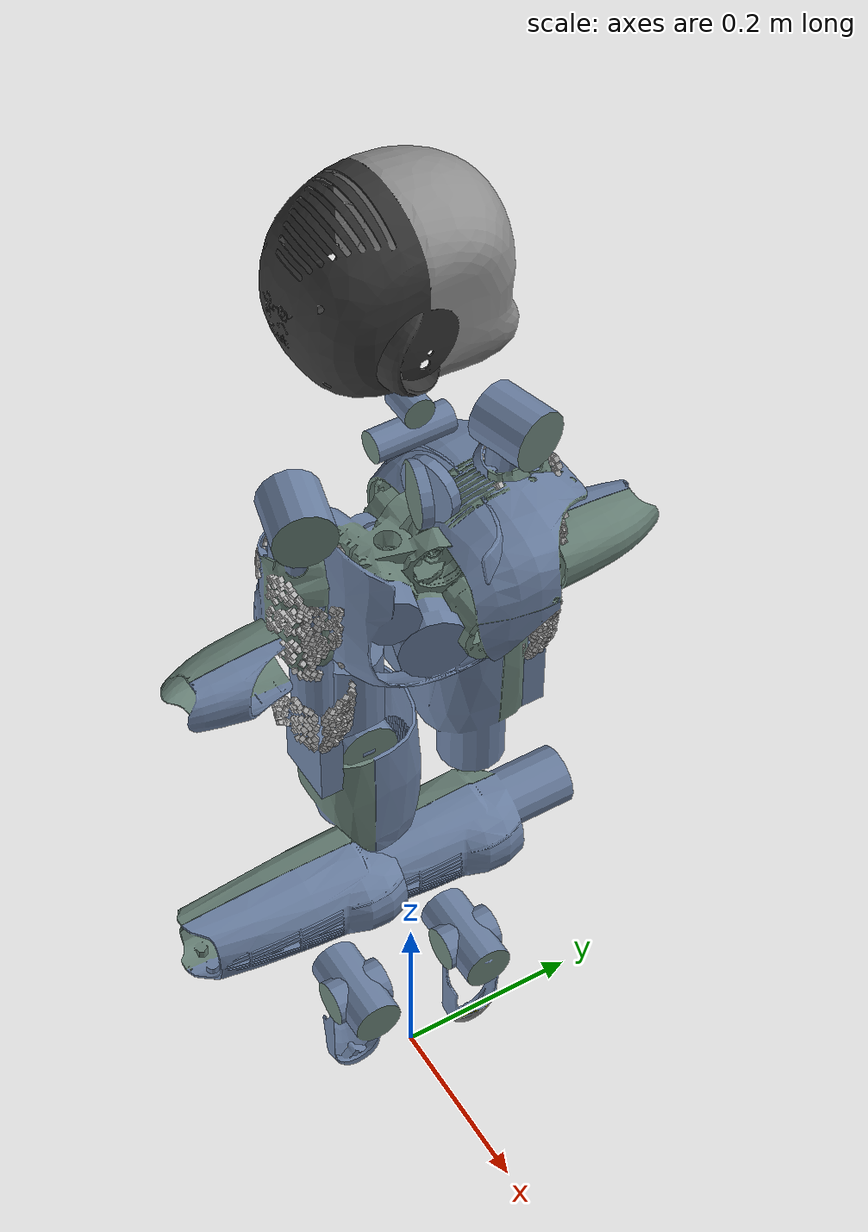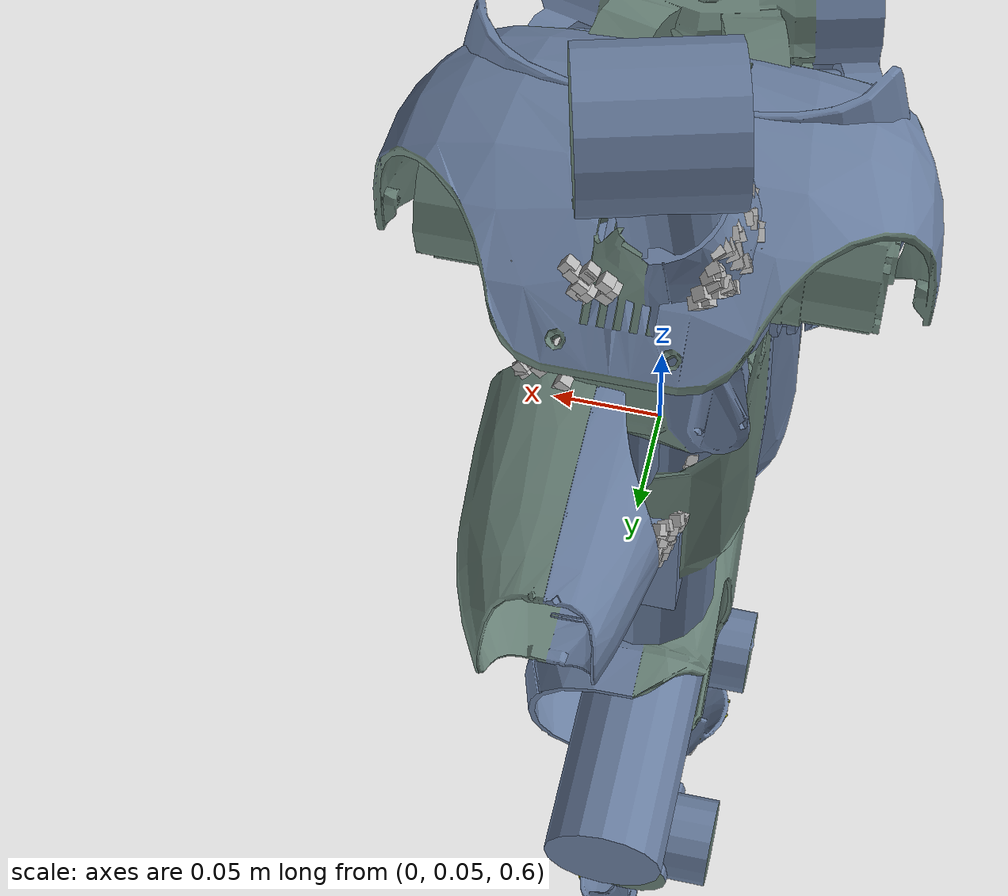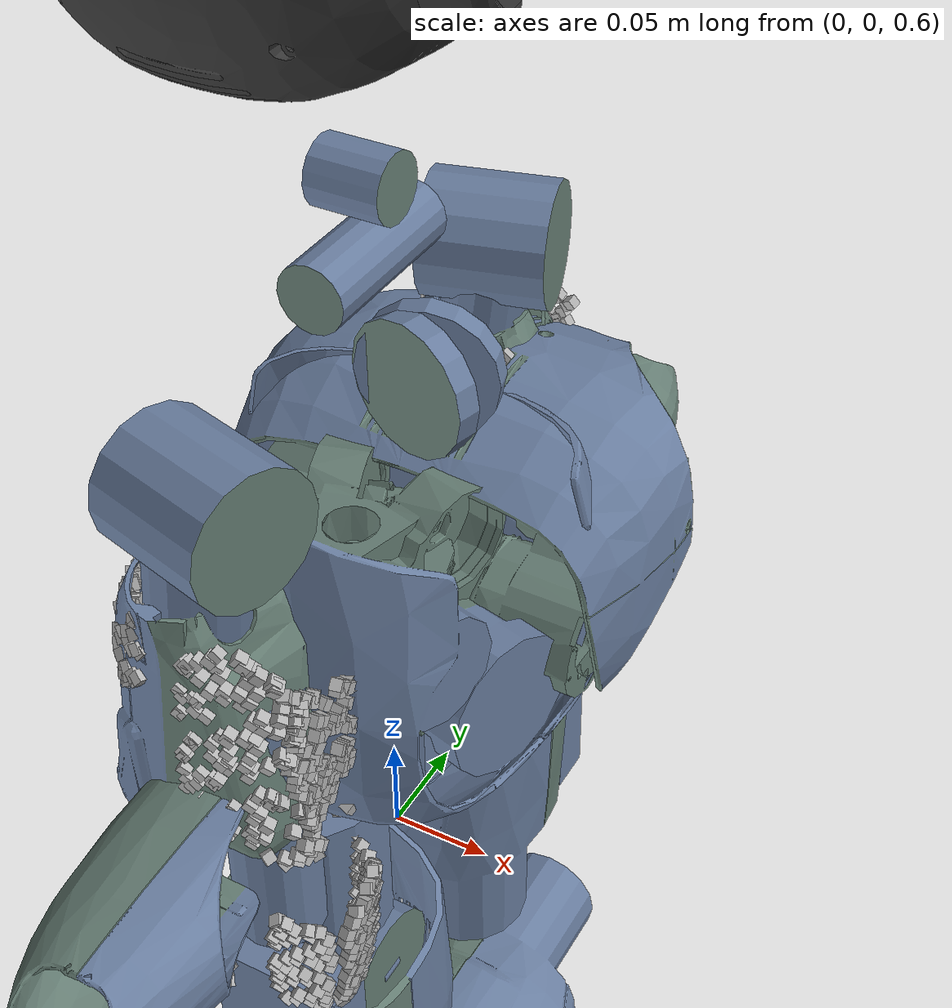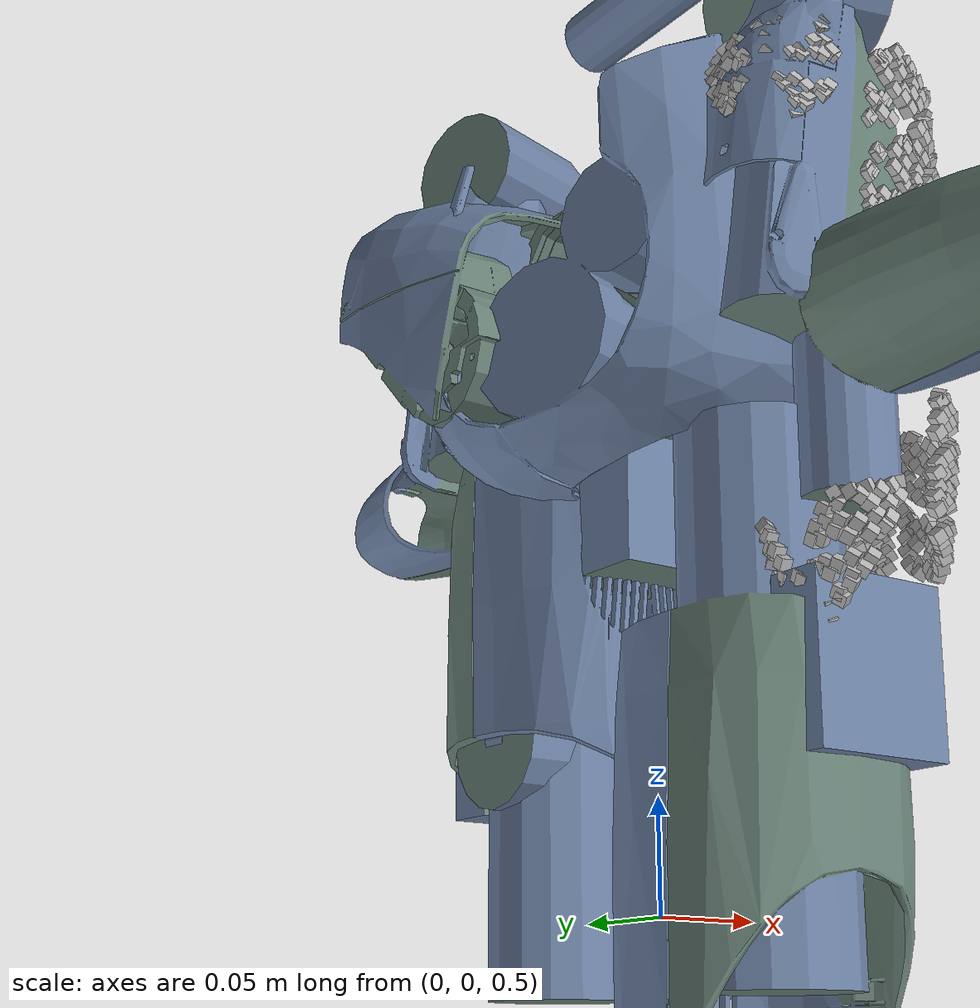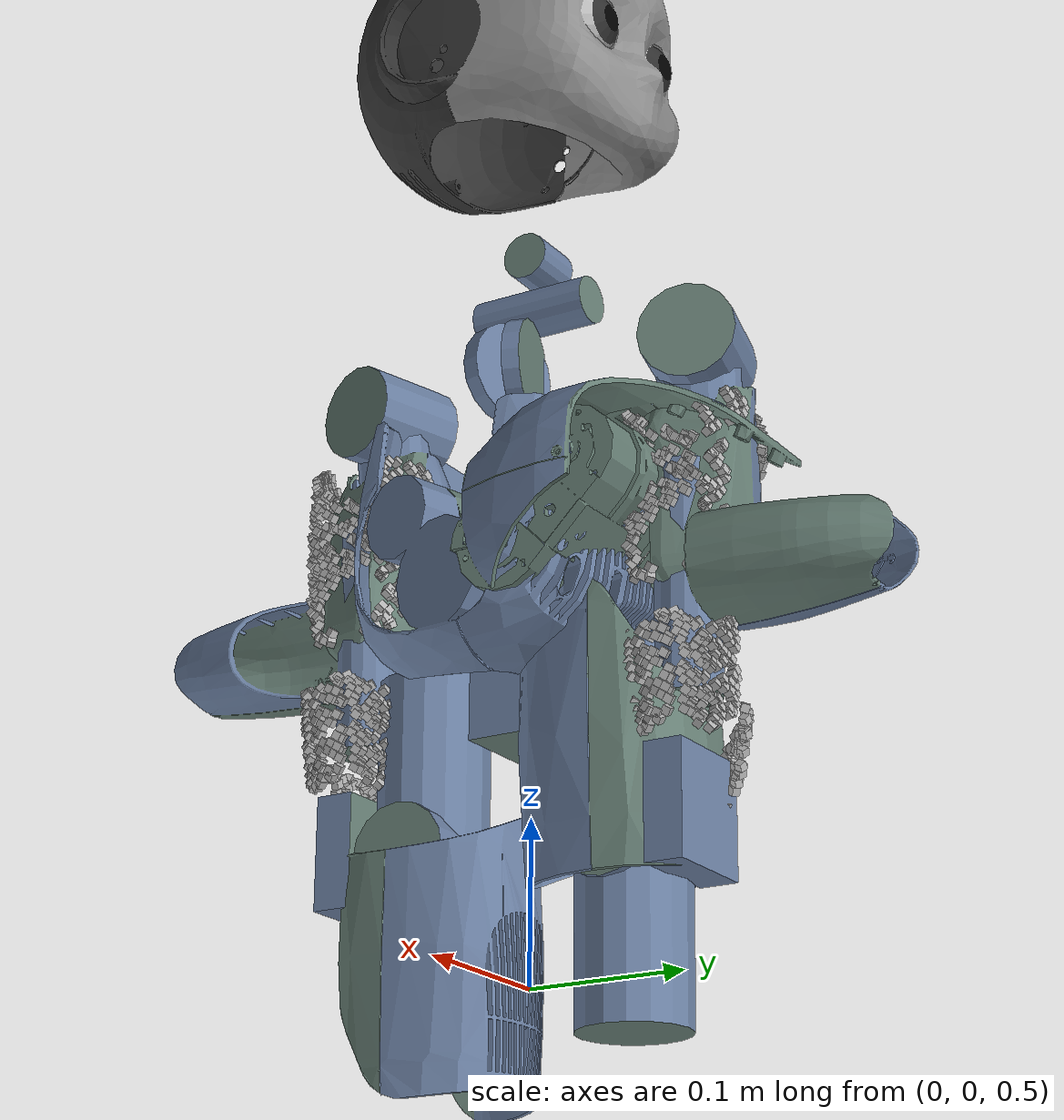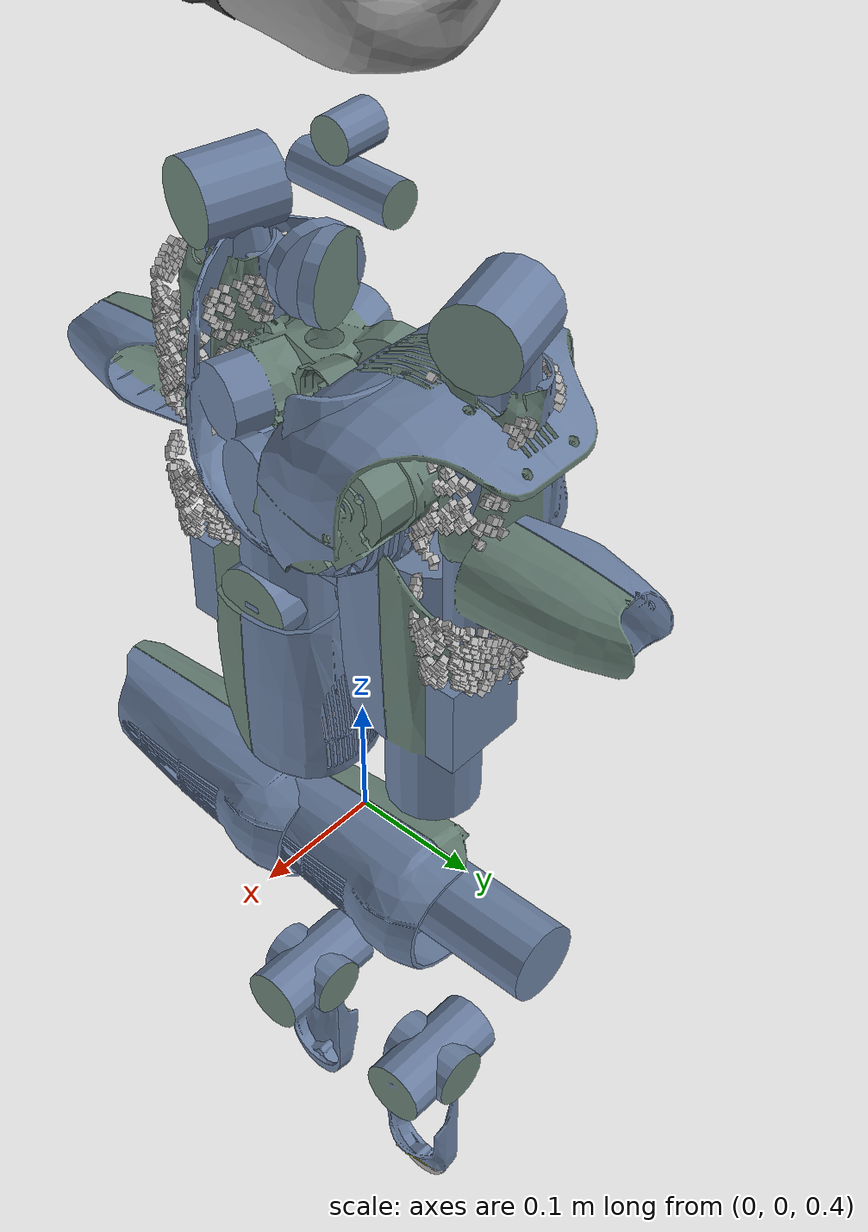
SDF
<?xml version="1.0" ?>
<sdf version='1.4' >
    <model name='iCub'>
        <link name='root_link'>
            <pose>0 0 0 0 -0 0</pose>
            <inertial>
                <pose>0 0 0 0 -0 0</pose>
                <mass>1.2</mass>
                <inertia>
                    <ixx>0.01</ixx>
                    <ixy>0</ixy>
                    <ixz>0</ixz>
                    <iyy>0.01</iyy>
                    <iyz>0</iyz>
                    <izz>0.01</izz>
                </inertia>
            </inertial>
            <collision name='root_link_collision'>
                <pose>0 0 0 0 -0 0</pose>
                <geometry>
                    <mesh>
                        <scale>1 1 1</scale>
                        <uri>model://icub/meshes/collision/icub_simple_collision_root_link.dae</uri>
                    </mesh>
                </geometry>
            </collision>
            <visual name='root_link_visual'>
                <pose>0 0 0 0 -0 0</pose>
                <geometry>
                    <mesh>
                        <scale>1 1 1</scale>
                        <uri>model://icub/meshes/visual/icub_root_link.dae</uri>
                    </mesh>
                </geometry>
            </visual>
            <velocity_decay>
                <linear>0</linear>
                <angular>0</angular>
            </velocity_decay>
        </link>
        <link name='l_hip_1'>
            <pose>0 -0.0681 -0.1199 2.65359e-06 1.57079 3.14159</pose>

            <inertial>
                <pose>0 -0.0782 0 0 -0 0</pose>
                <mass>0.754</mass>
                <inertia>
                    <ixx>0.01</ixx>
                    <ixy>2.059e-06</ixy>
                    <ixz>1.451e-06</ixz>
                    <iyy>0.01</iyy>
                    <iyz>1.545e-06</iyz>
                    <izz>0.01</izz>
                </inertia>
            </inertial>
            <collision name='l_hip_1_collision'>
                <pose>0 0 0 -0.945183 1.57079 -2.51598</pose>
                <geometry>
                    <mesh>
                        <scale>1 1 1</scale>
                        <uri>model://icub/meshes/collision/icub_simple_collision_l_hip_1.dae</uri>
                    </mesh>
                </geometry>
            </collision>
            <visual name='l_hip_1_visual'>
                <pose>0 0 0 -0.945183 1.57079 -2.51598</pose>
                <geometry>
                    <mesh>
                        <scale>1 1 1</scale>
                        <uri>model://icub/meshes/visual/icub_l_hip_1.dae</uri>
                    </mesh>
                </geometry>
            </visual>
            <velocity_decay>
                <linear>0</linear>
                <angular>0</angular>
            </velocity_decay>
        </link>
        <joint name='l_hip_pitch' type='revolute'>
            <child>l_hip_1</child>
            <parent>root_link</parent>
            <axis>
                <xyz>5.30718e-06 1 -1.67887e-11</xyz>
                <limit>
                    <lower>-0.6109 </lower>
                    <upper>1.3614</upper>
                    <effort>10000</effort>
                    <velocity>100</velocity>
                </limit>
                <dynamics>
                    <damping>0.5</damping>
                </dynamics>
            </axis>
        </joint>
        <link name='l_hip_2'>
            <pose>0 -0.0681 -0.1199 3.14159 -1.26536e-05 3.14159</pose>
            <inertial>
                <pose>0 0 0.03045 0 -0 0</pose>
                <mass>0.526</mass>
                <inertia>
                    <ixx>0.01</ixx>
                    <ixy>-7.4e-08</ixy>
                    <ixz>1.0835e-05</ixz>
                    <iyy>0.01</iyy>
                    <iyz>-6.2e-08</iyz>
                    <izz>0.01</izz>
                </inertia>
            </inertial>
            <collision name='l_hip_2_collision'>
                <pose>0 0 0 -0.346628 -1.57079 -2.79497</pose>
                <geometry>
                    <mesh>
                        <scale>1 1 1</scale>
                        <uri>model://icub/meshes/collision/icub_simple_collision_l_hip_2.dae</uri>
                    </mesh>
                </geometry>
            </collision>
            <visual name='l_hip_2_visual'>
                <pose>0 0 0 -0.346628 -1.57079 -2.79497</pose>
                <geometry>
                    <mesh>
                        <scale>1 1 1</scale>
                        <uri>model://icub/meshes/visual/icub_l_hip_2.dae</uri>
                    </mesh>
                </geometry>
            </visual>
            <velocity_decay>
                <linear>0</linear>
                <angular>0</angular>
            </velocity_decay>
        </link>
        <joint name='l_hip_roll' type='revolute'>
            <child>l_hip_2</child>
            <parent>l_hip_1</parent>
            <axis>
                <xyz>-1 5.30716e-06 1.26536e-05</xyz>
                <limit>
                    <lower>-0.3491</lower>
                    <upper>1.3090</upper>
                    <effort>10000</effort>
                    <velocity>100</velocity>
                </limit>
                <dynamics>
                    <damping>0.5</damping>
                </dynamics>
            </axis>
        </joint>
        <link name='l_hip_3'>
            <pose>0 -0.0681 -0.1199 -1.53072e-05 5.30721e-06 -1.5708</pose>
            <inertial>
                <pose>0 0 0 0 -0 0</pose>
                <mass>0.1</mass>
                <inertia>
                    <ixx>0.01</ixx>
                    <ixy>0</ixy>
                    <ixz>0</ixz>
                    <iyy>0.01</iyy>
                    <iyz>0</iyz>
                    <izz>0.01</izz>
                </inertia>
            </inertial>
            <velocity_decay>
                <linear>0</linear>
                <angular>0</angular>
            </velocity_decay>
        </link>
        <joint name='l_leg_ft_sensor' type='revolute'>
            <child>l_hip_3</child>
            <parent>l_hip_2</parent>
            <axis>
                <xyz>0 0 0</xyz>
                <limit>
                    <lower>0</lower>
                    <upper>0</upper>
                    <effort>0</effort>
                    <velocity>0</velocity>
                </limit>
                <dynamics>
                </dynamics>
            </axis>
            <!-- check pose of the wrench returned by the simulated sensor -->
            <sensor name="left_leg_ft" type="force_torque">
                <force_torque>
                    <frame>child</frame>
                </force_torque>
                <always_on>true</always_on>
                <visualize>true</visualize>
                <update_rate>100</update_rate>
                <pose>0 0 0 0 0 0</pose>
                <plugin filename="libgazebo_yarp_forcetorque.so" name="left_leg_ft_plugin">
                    <yarpConfigurationFile>model://icub/conf/FT/gazebo_icub_left_leg_ft.ini</yarpConfigurationFile>
                </plugin>
            </sensor>
        </joint>
        <link name='l_thigh'>
            <pose>0 -0.0681 -0.1199 1.57079 -1.53072e-05 3.14159</pose>
            <inertial>
                <pose>0.00144 -0.15943 -0.00039 0 -0 0</pose>
                <mass>2.175</mass>
                <inertia>
                    <ixx>0.01</ixx>
                    <ixy>-6.726e-05</ixy>
                    <ixz>2.267e-06</ixz>
                    <iyy>0.01</iyy>
                    <iyz>3.63726e-05</iyz>
                    <izz>0.01</izz>
                </inertia>
            </inertial>
            <collision name='l_thigh_collision'>
                <pose>0 0 0 1.93765 1.57079 -2.77475</pose>
                <geometry>
                    <mesh>
                        <scale>1 1 1</scale>
                        <uri>model://icub/meshes/collision/icub_simple_collision_l_thigh.dae</uri>
                    </mesh>
                </geometry>
            </collision>
            <visual name='l_thigh_visual'>
                <pose>0 0 0 1.93765 1.57079 -2.77475</pose>
                <geometry>
                    <mesh>
                        <scale>1 1 1</scale>
                        <uri>model://icub/meshes/visual/icub_l_thigh.dae</uri>
                    </mesh>
                </geometry>
            </visual>
            <velocity_decay>
                <linear>0</linear>
                <angular>0</angular>
            </velocity_decay>
        </link>
        <joint name='l_hip_yaw' type='revolute'>
            <child>l_thigh</child>
            <parent>l_hip_3</parent>
            <axis>
                <xyz>1.53072e-05 -1.63403e-06 1</xyz>
                <limit>
                    <lower>-1.4962634016</lower>
                    <upper>1.4613568166</upper>
                    <effort>10000</effort>
                    <velocity>100</velocity>
                </limit>
                <dynamics>
                    <damping>0.5</damping>
                </dynamics>
            </axis>
        </joint>
        <link name='l_shank'>
            <pose>-3.42268e-06 -0.0680996 -0.3435 1.65667 -1.57078 -0.0858797</pose>
            <inertial>
                <pose>-0.1071 0.00182 0.00211 0 -0 0</pose>
                <mass>1.264</mass>
                <inertia>
                    <ixx>0.01</ixx>
                    <ixy>-0.000185699</ixy>
                    <ixz>-6.3147e-05</ixz>
                    <iyy>0.01</iyy>
                    <iyz>7.86e-07</iyz>
                    <izz>0.01</izz>
                </inertia>
            </inertial>
            <collision name='l_shank_collision'>
                <pose>1.95097e-11 -2.236e-06 -2.27994e-07 3.14159 -5.30752e-06 1.57081</pose>
                <geometry>
                    <mesh>
                        <scale>1 1 1</scale>
                        <uri>model://icub/meshes/collision/icub_simple_collision_l_shank.dae</uri>
                    </mesh>
                </geometry>
            </collision>
            <visual name='l_shank_visual'>
                <pose>1.95097e-11 -2.236e-06 -2.27994e-07 3.14159 -5.30752e-06 1.57081</pose>
                <geometry>
                    <mesh>
                        <scale>1 1 1</scale>
                        <uri>model://icub/meshes/visual/icub_l_shank.dae</uri>
                    </mesh>
                </geometry>
            </visual>
            <velocity_decay>
                <linear>0</linear>
                <angular>0</angular>
            </velocity_decay>
        </link>
        <joint name='l_knee' type='revolute'>
            <child>l_shank</child>
            <parent>l_thigh</parent>
            <axis>
                <xyz>7.96076e-06 1 1.6339e-06</xyz>
                <limit>
                    <lower>-1.9897</lower>
                    <upper>0.0524</upper>
                    <effort>10000</effort>
                    <velocity>100</velocity>
                </limit>
                <dynamics>
                    <damping>0.5</damping>
                </dynamics>
            </axis>
        </joint>
        <link name='l_ankle_1'>
            <pose>-7.4655e-06 -0.0680993 -0.5565 0.0858681 -1.57078 -0.0858797</pose>
            <inertial>
                <pose>-0.0054 0.00163 0.0172 0 -0 0</pose>
                <mass>0.746</mass>
                <inertia>
                    <ixx>0.01</ixx>
                    <ixy>-7.081e-06</ixy>
                    <ixz>4.1421e-05</ixz>
                    <iyy>0.01</iyy>
                    <iyz>2.0817e-05</iyz>
                    <izz>0.01</izz>
                </inertia>
            </inertial>
            <collision name='l_ankle_1_collision'>
                <pose>3.95315e-11 4.452e-07 -5.14839e-06 1.57081 -1.36732e-05 -1.01971e-06</pose>
                <geometry>
                    <mesh>
                        <scale>1 1 1</scale>
                        <uri>model://icub/meshes/collision/icub_simple_collision_l_ankle_1.dae</uri>
                    </mesh>
                </geometry>
            </collision>
            <visual name='l_ankle_1_visual'>
                <pose>3.95315e-11 4.452e-07 -5.14839e-06 1.57081 -1.36732e-05 -1.01971e-06</pose>
                <geometry>
                    <mesh>
                        <scale>1 1 1</scale>
                        <uri>model://icub/meshes/visual/icub_l_ankle_1.dae</uri>
                    </mesh>
                </geometry>
            </visual>
            <velocity_decay>
                <linear>0</linear>
                <angular>0</angular>
            </velocity_decay>
        </link>
        <joint name='l_ankle_pitch' type='revolute'>
            <child>l_ankle_1</child>
            <parent>l_shank</parent>
            <axis>
                <xyz>-1.1634e-05 -1 -1.63383e-06</xyz>
                <limit>
                    <lower>-0.6109</lower>
                    <upper>0.6981</upper>
                    <effort>10000</effort>
                    <velocity>100</velocity>
                </limit>
                <dynamics>
                    <damping>0.5</damping>
                </dynamics>
            </axis>
        </joint>
        <link name='l_foot'>
            <pose>-7.4655e-06 -0.0680993 -0.5565 0.0858681 -1.57078 -0.0858797</pose>
            <inertial>
                <pose>-0.041 0 0 0 -0 0</pose>
                <mass>0.1</mass>
                <inertia>
                    <ixx>0.01</ixx>
                    <ixy>0</ixy>
                    <ixz>0</ixz>
                    <iyy>0.01</iyy>
                    <iyz>0</iyz>
                    <izz>0.01</izz>
                </inertia>
            </inertial>
            <collision name='l_foot_collision'>
                <pose>3.95315e-11 4.452e-07 -5.14839e-06 8.98039e-06 -1.36732e-05 -1.01971e-06</pose>
                <geometry>
                    <mesh>
                        <scale>1 1 1</scale>
                        <uri>model://icub/meshes/collision/icub_simple_collision_l_foot.dae</uri>
                    </mesh>
                </geometry>
                <max_contacts> 10 </max_contacts>
                <surface>
                    <contact>
                        <ode>
                            <soft_erp>  0.200  </soft_erp>
                            <soft_cfm>  0.000  </soft_cfm>
                            <kp>        100000.000  </kp>
                            <kd>        1.0     </kd>
                            <max_vel>   100.00  </max_vel>
                            <min_depth> 0.0010  </min_depth>
                        </ode>
                    </contact>
                    <friction>
                        <ode>
                            <mu>  1  </mu>
                            <mu2> 1  </mu2>
                            <fdir1>0.000000 0.000000 0.000000</fdir1>
                            <slip1> 0.00000 </slip1>
                            <slip2> 0.00000 </slip2>
                        </ode>
                    </friction>
                    <bounce>
                        <restitution_coefficient>0.000000</restitution_coefficient>
                        <threshold>100000.000000</threshold>
                    </bounce>
                </surface>
            </collision>
            <visual name='l_foot_visual'>
                <pose>3.95315e-11 4.452e-07 -5.14839e-06 8.98039e-06 -1.36732e-05 -1.01971e-06</pose>
                <geometry>
                    <mesh>
                        <scale>1 1 1</scale>
                        <uri>model://icub/meshes/visual/icub_l_foot.dae</uri>
                    </mesh>
                </geometry>
            </visual>
            <velocity_decay>
                <linear>0</linear>
                <angular>0</angular>
            </velocity_decay>
        </link>
        <joint name='l_foot_ft_sensor' type='revolute'>
            <child>l_foot</child>
            <parent>l_upper_foot</parent>
            <axis>
                <xyz>0 0 0</xyz>
                <limit>
                    <lower>0</lower>
                    <upper>0</upper>
                    <effort>0</effort>
                    <velocity>0</velocity>
                </limit>
                <dynamics/>
            </axis>
            <sensor name='left_foot_ft' type='force_torque'>
                <force_torque>
                    <frame>child</frame>
                </force_torque>
                <always_on>1</always_on>
                <update_rate>100</update_rate>
                <pose>0 0 0 0 0 0</pose>
                <plugin name='left_foot_ft_plugin' filename='libgazebo_yarp_forcetorque.so'>
                    <yarpConfigurationFile>model://icub/conf/FT/gazebo_icub_left_foot_ft.ini</yarpConfigurationFile>
                </plugin>
            </sensor>
        </joint>
        <link name='l_upper_foot'>
            <pose>-5.14839e-06 -0.0681004 -0.5565 -3.14159 -9.99999e-06 3.14158</pose>
            <inertial>
                <pose>0 0 -0.034 0 -0 0</pose>
                <mass>0.1</mass>
                <inertia>
                    <ixx>0.01</ixx>
                    <ixy>0</ixy>
                    <ixz>0</ixz>
                    <iyy>0.01</iyy>
                    <iyz>0</iyz>
                    <izz>0.01</izz>
                </inertia>
            </inertial>
            <velocity_decay>
                <linear>0</linear>
                <angular>0</angular>
            </velocity_decay>
        </link>
        <joint name='l_ankle_roll' type='revolute'>
            <child>l_upper_foot</child>
            <parent>l_ankle_1</parent>
            <axis>
                <xyz>-1 1.16339e-05 1.89804e-05</xyz>
                <limit>
                    <lower>-0.4363</lower>
                    <upper>0.4363</upper>
                    <effort>10000</effort>
                    <velocity>100</velocity>
                </limit>
                <dynamics>
                    <damping>0.5</damping>
                </dynamics>
            </axis>
        </joint>
        <link name='r_hip_1'>
            <pose>0 0.0681 -0.1199 3.14159 1.57079 -3.14159</pose>
            <inertial>
                <pose>0 -0.0782 0 0 -0 0</pose>
                <mass>0.754</mass>
                <inertia>
                    <ixx>0.01</ixx>
                    <ixy>0</ixy>
                    <ixz>0</ixz>
                    <iyy>0.01</iyy>
                    <iyz>0</iyz>
                    <izz>0.01</izz>
                </inertia>
            </inertial>
            <collision name='r_hip_1_collision'>
                <pose>0 0 0 1.5708 -1.57079 3.14159</pose>
                <geometry>
                    <mesh>
                        <scale>1 1 1</scale>
                        <uri>model://icub/meshes/collision/icub_simple_collision_r_hip_1.dae</uri>
                    </mesh>
                </geometry>
            </collision>
            <visual name='r_hip_1_visual'>
                <pose>0 0 0 1.5708 -1.57079 3.14159</pose>
                <geometry>
                    <mesh>
                        <scale>1 1 1</scale>
                        <uri>model://icub/meshes/visual/icub_r_hip_1.dae</uri>
                    </mesh>
                </geometry>
            </visual>
            <velocity_decay>
                <linear>0</linear>
                <angular>0</angular>
            </velocity_decay>
        </link>
        <joint name='r_hip_pitch' type='revolute'>
            <child>r_hip_1</child>
            <parent>root_link</parent>
            <axis>
                <xyz>-5.30718e-06 1 1.67887e-11</xyz>
                <limit>
                    <lower>-0.6109</lower>
                    <upper>1.3614</upper>
                    <effort>10000</effort>
                    <velocity>100</velocity>
                </limit>
                <dynamics>
                    <damping>0.5</damping>
                </dynamics>
            </axis>
        </joint>
        <link name='r_hip_2'>
            <pose>0 0.0681 -0.1199 -3.14159 -1.26536e-05 -3.14159</pose>
            <inertial>
                <pose>0 0 0.03045 0 -0 0</pose>
                <mass>0.526</mass>
                <inertia>
                    <ixx>0.01</ixx>
                    <ixy>0</ixy>
                    <ixz>0</ixz>
                    <iyy>0.01</iyy>
                    <iyz>0</iyz>
                    <izz>0.01</izz>
                </inertia>
            </inertial>
            <collision name='r_hip_2_collision'>
                <pose>0 0 0 3.14159 -1.57079 -3.14159</pose>
                <geometry>
                    <mesh>
                        <scale>1 1 1</scale>
                        <uri>model://icub/meshes/collision/icub_simple_collision_r_hip_2.dae</uri>
                    </mesh>
                </geometry>
            </collision>
            <visual name='r_hip_2_visual'>
                <pose>0 0 0 3.14159 -1.57079 -3.14159</pose>
                <geometry>
                    <mesh>
                        <scale>1 1 1</scale>
                        <uri>model://icub/meshes/visual/icub_r_hip_2.dae</uri>
                    </mesh>
                </geometry>
            </visual>
            <velocity_decay>
                <linear>0</linear>
                <angular>0</angular>
            </velocity_decay>
        </link>
        <joint name='r_hip_roll' type='revolute'>
            <child>r_hip_2</child>
            <parent>r_hip_1</parent>
            <axis>
                <xyz>1 5.30716e-06 -1.26536e-05</xyz>
                <limit>
                    <lower>-0.3491</lower>
                    <upper>1.3090</upper>
                    <effort>10000</effort>
                    <velocity>100</velocity>
                </limit>
                <dynamics>
                    <damping>0.5</damping>
                </dynamics>
            </axis>
        </joint>
        <link name='r_hip_3'>
            <pose>0 0.0681 -0.1199 -3.14158 5.30721e-06 1.5708</pose>
            <inertial>
                <pose>0 0 0 0 -0 0</pose>
                <mass>0.1</mass>
                <inertia>
                    <ixx>0.01</ixx>
                    <ixy>0</ixy>
                    <ixz>0</ixz>
                    <iyy>0.01</iyy>
                    <iyz>0</iyz>
                    <izz>0.01</izz>
                </inertia>
            </inertial>
            <velocity_decay>
                <linear>0</linear>
                <angular>0</angular>
            </velocity_decay>
        </link>
        <joint name='r_leg_ft_sensor' type='revolute'>
            <child>r_hip_3</child>
            <parent>r_hip_2</parent>
            <axis>
                <xyz>0 0 -0</xyz>
                <limit>
                    <lower>0</lower>
                    <upper>0</upper>
                    <effort>0</effort>
                    <velocity>0</velocity>
                </limit>
                <dynamics>
                </dynamics>
            </axis>
            <!-- check pose of the wrench returned by the simulated sensor -->
            <sensor name="right_leg_ft" type="force_torque">
                <force_torque>
                    <frame>child</frame>
                </force_torque>
                <always_on>true</always_on>
                <visualize>true</visualize>
                <update_rate>100</update_rate>
                <pose>0 0 0 0 0 0</pose>
                <plugin filename="libgazebo_yarp_forcetorque.so" name="right_leg_ft_plugin">
                    <yarpConfigurationFile>model://icub/conf/FT/gazebo_icub_right_leg_ft.ini</yarpConfigurationFile>
                </plugin>
            </sensor>
        </joint>
        <link name='r_thigh'>
            <pose>0 0.0681 -0.1199 1.5708 -1.26536e-05 -3.14159</pose>
            <inertial>
                <pose>0.00144 -0.15943 0.00039 0 -0 0</pose>
                <mass>2.175</mass>
                <inertia>
                    <ixx>0.01</ixx>
                    <ixy>0</ixy>
                    <ixz>0</ixz>
                    <iyy>0.01</iyy>
                    <iyz>-2.71051e-20</iyz>
                    <izz>0.01</izz>
                </inertia>
            </inertial>
            <collision name='r_thigh_collision'>
                <pose>0 0 0 3.14159 -1.57079 -1.5708</pose>
                <geometry>
                    <mesh>
                        <scale>1 1 1</scale>
                        <uri>model://icub/meshes/collision/icub_simple_collision_r_thigh.dae</uri>
                    </mesh>
                </geometry>
            </collision>
            <visual name='r_thigh_visual'>
                <pose>0 0 0 3.14159 -1.57079 -1.5708</pose>
                <geometry>
                    <mesh>
                        <scale>1 1 1</scale>
                        <uri>model://icub/meshes/visual/icub_r_thigh.dae</uri>
                    </mesh>
                </geometry>
            </visual>
            <velocity_decay>
                <linear>0</linear>
                <angular>0</angular>
            </velocity_decay>
        </link>
        <joint name='r_hip_yaw' type='revolute'>
            <child>r_thigh</child>
            <parent>r_hip_3</parent>
            <axis>
                <xyz>-1.26536e-05 -1.63402e-06 -1</xyz>
                <limit>
                    <lower>-1.4962634016</lower>
                    <upper>1.4613568166</upper>
                    <effort>10000</effort>
                    <velocity>100</velocity>
                </limit>
                <dynamics>
                    <damping>0.5</damping>
                </dynamics>
            </axis>
        </joint>
        <link name='r_shank'>
            <pose>-2.82934e-06 0.0680996 -0.3435 1.47105 -1.57078 0.0997515</pose>
            <inertial>
                <pose>-0.1071 0.00182 -0.00211 0 -0 0</pose>
                <mass>1.264</mass>
                <inertia>
                    <ixx>0.01</ixx>
                    <ixy>5.42101e-20</ixy>
                    <ixz>-5.42101e-20</ixz>
                    <iyy>0.01</iyy>
                    <iyz>8.47033e-22</iyz>
                    <izz>0.01</izz>
                </inertia>
            </inertial>
            <collision name='r_shank_collision'>
                <pose>1.35762e-11 -1.64266e-06 8.21324e-07 -3.14159 -2.65363e-06 1.57081</pose>
                <geometry>
                    <mesh>
                        <scale>1 1 1</scale>
                        <uri>model://icub/meshes/collision/icub_simple_collision_r_shank.dae</uri>
                    </mesh>
                </geometry>
            </collision>
            <visual name='r_shank_visual'>
                <pose>1.35762e-11 -1.64266e-06 8.21324e-07 -3.14159 -2.65363e-06 1.57081</pose>
                <geometry>
                    <mesh>
                        <scale>1 1 1</scale>
                        <uri>model://icub/meshes/visual/icub_r_shank.dae</uri>
                    </mesh>
                </geometry>
            </visual>
            <velocity_decay>
                <linear>0</linear>
                <angular>0</angular>
            </velocity_decay>
        </link>
        <joint name='r_knee' type='revolute'>
            <child>r_shank</child>
            <parent>r_thigh</parent>
            <axis>
                <xyz>-2.65359e-06 1 -1.634e-06</xyz>
                <limit>
                    <lower>-1.9897</lower>
                    <upper>0.0524</upper>
                    <effort>10000</effort>
                    <velocity>100</velocity>
                </limit>
                <dynamics>
                    <damping>0.5</damping>
                </dynamics>
            </axis>
        </joint>
        <link name='r_ankle_1'>
            <pose>-6.30695e-06 0.0680993 -0.5565 3.04185 -1.57078 0.0997515</pose>
            <inertial>
                <pose>-0.0054 0.00163 -0.0172 0 -0 0</pose>
                <mass>0.746</mass>
                <inertia>
                    <ixx>0.01</ixx>
                    <ixy>-1.69407e-21</ixy>
                    <ixz>1.35525e-20</ixz>
                    <iyy>0.01</iyy>
                    <iyz>3.38813e-21</iyz>
                    <izz>0.01</izz>
                </inertia>
            </inertial>
            <collision name='r_ankle_1_collision'>
                <pose>2.79458e-11 1.60372e-06 3.98983e-06 -1.5708 1.10196e-05 -3.67321e-06</pose>
                <geometry>
                    <mesh>
                        <scale>1 1 1</scale>
                        <uri>model://icub/meshes/collision/icub_simple_collision_r_ankle_1.dae</uri>
                    </mesh>
                </geometry>
            </collision>
            <visual name='r_ankle_1_visual'>
                <pose>2.79458e-11 1.60372e-06 3.98983e-06 -1.5708 1.10196e-05 -3.67321e-06</pose>
                <geometry>
                    <mesh>
                        <scale>1 1 1</scale>
                        <uri>model://icub/meshes/visual/icub_r_ankle_1.dae</uri>
                    </mesh>
                </geometry>
            </visual>
            <velocity_decay>
                <linear>0</linear>
                <angular>0</angular>
            </velocity_decay>
        </link>
        <joint name='r_ankle_pitch' type='revolute'>
            <child>r_ankle_1</child>
            <parent>r_shank</parent>
            <axis>
                <xyz>6.3268e-06 -1 1.63394e-06</xyz>
                <limit>
                    <lower>-0.6109</lower>
                    <upper>0.6981</upper>
                    <effort>10000</effort>
                    <velocity>100</velocity>
                </limit>
                <dynamics>
                    <damping>0.5</damping>
                </dynamics>
            </axis>

        </joint>
        <link name='r_foot'>
            <pose>-6.30695e-06 0.0680993 -0.5565 -0.0997478 -1.57078 0.0997515</pose>
            <inertial>
                <pose>-0.041 0 0 0 -0 0</pose>
                <mass>0.1</mass>
                <inertia>
                    <ixx>0.01</ixx>
                    <ixy>0</ixy>
                    <ixz>0</ixz>
                    <iyy>0.01</iyy>
                    <iyz>0</iyz>
                    <izz>0.01</izz>
                </inertia>
            </inertial>
            <collision name='r_foot_collision'>
                <pose>2.79458e-11 -1.60371e-06 -3.98983e-06 -3.14159 -1.10245e-05 3.67318e-06</pose>
                <geometry>
                    <mesh>
                        <scale>1 1 1</scale>
                        <uri>model://icub/meshes/collision/icub_simple_collision_r_foot.dae</uri>
                    </mesh>
                </geometry>
                <max_contacts> 10 </max_contacts>
                <surface>
                    <contact>
                        <ode>
                            <soft_erp>  0.200  </soft_erp>
                            <soft_cfm>  0.000  </soft_cfm>
                            <kp>        100000.000  </kp>
                            <kd>        1.0     </kd>
                            <max_vel>   100.00  </max_vel>
                            <min_depth> 0.0010  </min_depth>
                        </ode>
                    </contact>
                    <friction>
                        <ode>
                            <mu>  1  </mu>
                            <mu2> 1  </mu2>
                            <fdir1>0.000000 0.000000 0.000000</fdir1>
                            <slip1> 0.00000 </slip1>
                            <slip2> 0.00000 </slip2>
                        </ode>
                    </friction>
                    <bounce>
                        <restitution_coefficient>0.000000</restitution_coefficient>
                        <threshold>100000.000000</threshold>
                    </bounce>
                </surface>
            </collision>
            <visual name='r_foot_visual'>
                <pose>2.79458e-11 -1.60371e-06 -3.98983e-06 -3.14159 -1.10245e-05 3.67318e-06</pose>
                <geometry>
                    <mesh>
                        <scale>1 1 1</scale>
                        <uri>model://icub/meshes/visual/icub_r_foot.dae</uri>
                    </mesh>
                </geometry>
            </visual>
            <velocity_decay>
                <linear>0</linear>
                <angular>0</angular>
            </velocity_decay>
        </link>
        <joint name='r_foot_ft_sensor' type='revolute'>
            <child>r_foot</child>
            <parent>r_upper_foot</parent>
            <axis>
                <xyz>0 0 0</xyz>
                <limit>
                    <lower>0</lower>
                    <upper>0</upper>
                    <effort>0</effort>
                    <velocity>0</velocity>
                </limit>
                <dynamics/>
            </axis>
            <sensor name='right_foot_ft' type='force_torque'>
                <force_torque>
                    <frame>child</frame>
                </force_torque>
                <always_on>1</always_on>
                <update_rate>100</update_rate>
                <pose>0 0 0 0 0 0</pose>
                <plugin name='right_foot_ft_plugin' filename='libgazebo_yarp_forcetorque.so'>
                    <yarpConfigurationFile>model://icub/conf/FT/gazebo_icub_right_foot_ft.ini</yarpConfigurationFile>
                </plugin>
            </sensor>
        </joint>
        <link name='r_upper_foot'>
            <pose>-3.98984e-06 0.0681016 -0.5565 3.14159 -1.4236e-05 -3.14159</pose>
            <inertial>
                <pose>0 0 -0.034 0 -0 0</pose>
                <mass>0.1</mass>
                <inertia>
                    <ixx>0.01</ixx>
                    <ixy>0</ixy>
                    <ixz>0</ixz>
                    <iyy>0.01</iyy>
                    <iyz>0</iyz>
                    <izz>0.01</izz>
                </inertia>
            </inertial>
            <velocity_decay>
                <linear>0</linear>
                <angular>0</angular>
            </velocity_decay>
        </link>
        <joint name='r_ankle_roll' type='revolute'>
            <child>r_upper_foot</child>
            <parent>r_ankle_1</parent>
            <axis>
                <xyz>1 3.67318e-06 -1.63268e-05</xyz>
                <limit>
                    <lower>-0.4363</lower>
                    <upper>0.4363</upper>
                    <effort>10000</effort>
                    <velocity>100</velocity>
                </limit>
                <dynamics>
                    <damping>0.5</damping>
                </dynamics>
            </axis>

        </joint>
        <link name='lap_belt_1'>
            <pose>0 0 0 3.14159 -1.57079 -2.65359e-06</pose>
            <inertial>
                <pose>0 0 0 0 -0 0</pose>
                <mass>0.1</mass>
                <inertia>
                    <ixx>0.01</ixx>
                    <ixy>-4.263e-05</ixy>
                    <ixz>-3.889e-08</ixz>
                    <iyy>0.01</iyy>
                    <iyz>0</iyz>
                    <izz>0.01</izz>
                </inertia>
            </inertial>
            <collision name='lap_belt_1_collision'>
                <pose>0 0 0 -1.57079 3.67321e-06 1.31031e-16</pose>
                <geometry>
                    <mesh>
                        <scale>1 1 1</scale>
                        <uri>model://icub/meshes/collision/icub_simple_collision_lap_belt_1.dae</uri>
                    </mesh>
                </geometry>
            </collision>
            <visual name='lap_belt_1_visual'>
                <pose>0 0 0 -1.57079 3.67321e-06 1.31031e-16</pose>
                <geometry>
                    <mesh>
                        <scale>1 1 1</scale>
                        <uri>model://icub/meshes/visual/icub_lap_belt_1.dae</uri>
                    </mesh>
                </geometry>
            </visual>
            <velocity_decay>
                <linear>0</linear>
                <angular>0</angular>
            </velocity_decay>
        </link>
        <joint name='torso_pitch' type='revolute'>
            <child>lap_belt_1</child>
            <parent>root_link</parent>
            <axis>
                <xyz>-5.30718e-06 -1 1.67887e-11</xyz>
                <limit>
                    <lower>-0.3491</lower>
                    <upper>1.2043</upper>
                    <effort>10000</effort>
                    <velocity>100</velocity>
                </limit>
                <dynamics>
                    <damping>0.5</damping>
                </dynamics>
            </axis>
        </joint>
        <link name='lap_belt_2'>
            <pose>2.02457e-07 -5.37239e-13 0.032 -3.14158 3.67322e-06 1.57079</pose>
            <inertial>
                <pose>0 0 0 0 -0 0</pose>
                <mass>0.1</mass>
                <inertia>
                    <ixx>0.01</ixx>
                    <ixy>-1.923e-06</ixy>
                    <ixz>5.095e-05</ixz>
                    <iyy>0.01</iyy>
                    <iyz>-3.849e-07</iyz>
                    <izz>0.01</izz>
                </inertia>
            </inertial>
            <velocity_decay>
                <linear>0</linear>
                <angular>0</angular>
            </velocity_decay>
        </link>
        <joint name='torso_roll' type='revolute'>
            <child>lap_belt_2</child>
            <parent>lap_belt_1</parent>
            <axis>
                <xyz>1 -5.30719e-06 -1e-05</xyz>
                <limit>
                    <lower>-0.5236</lower>
                    <upper>0.5236</upper>
                    <effort>10000</effort>
                    <velocity>100</velocity>
                </limit>
                <dynamics>
                    <damping>0.5</damping>
                </dynamics>
            </axis>
        </joint>
        <link name='chest'>

            <pose>-0.0054998 2.9189e-08 0.0320001 1.5708 -1e-05 3.14159</pose>
            <inertial>
                <pose>0.00222898 0.075 -1.18362e-17 0 -0 0</pose>
                <mass>4.81</mass>
                <inertia>
                    <ixx>0.07472</ixx>
                    <ixy>-3.6e-06</ixy>
                    <ixz>-4.705e-05</ixz>
                    <iyy>0.08145</iyy>
                    <iyz>0.004567</iyz>
                    <izz>0.01306</izz>
                </inertia>
            </inertial>
            <collision name='chest_collision'>
                <pose>-0.00549988 -5.73437e-13 -2.02022e-08 1.57076 -1.57079 2.26536e-05</pose>
                <geometry>
                    <mesh>
                        <scale>1 1 1</scale>
                        <uri>model://icub/meshes/collision/icub_simple_collision_chest.dae</uri>
                    </mesh>
                </geometry>
            </collision>
            <visual name='chest_visual'>
                <pose>-0.00549988 -5.73437e-13 -2.02022e-08 1.57076 -1.57079 2.26536e-05</pose>
                <geometry>
                    <mesh>
                        <scale>1 1 1</scale>
                        <uri>model://icub/meshes/visual/icub_chest.dae</uri>
                    </mesh>
                </geometry>
            </visual>
            <velocity_decay>
                <linear>0</linear>
                <angular>0</angular>
            </velocity_decay>
        </link>
        <joint name='torso_yaw' type='revolute'>
            <child>chest</child>
            <parent>lap_belt_2</parent>
            <axis>
                <xyz>-1e-05 3.62833e-11 -1</xyz>
                <limit>
                    <lower>-1.1170</lower>
                    <upper>1.0123</upper>
                    <effort>10000</effort>
                    <velocity>100</velocity>
                </limit>
                <dynamics>
                    <damping>0.5</damping>
                </dynamics>
            </axis>
        </joint>
        <link name='l_shoulder_1'>
            <pose>-0.0107485 -0.11026 0.1753 -0.261795 -1.57078 -3.09255e-06</pose>
            <inertial>
                <pose>-5e-06 0.0187 -0.00119 0 -0 0</pose>
                <mass>0.189</mass>
                <inertia>
                    <ixx>0.01</ixx>
                    <ixy>9e-09</ixy>
                    <ixz>0</ixz>
                    <iyy>0.01</iyy>
                    <iyz>-1.7e-08</iyz>
                    <izz>0.01</izz>
                </inertia>
            </inertial>
            <collision name='l_shoulder_1_collision'>
                <pose>2.88176e-07 0.109285 -0.00521022 1.20471 1.57078 -0.366086</pose>
                <geometry>
                    <mesh>
                        <scale>1 1 1</scale>
                        <uri>model://icub/meshes/collision/icub_simple_collision_l_shoulder_1.dae</uri>
                    </mesh>
                </geometry>
            </collision>
            <visual name='l_shoulder_1_visual'>
                <pose>2.88176e-07 0.109285 -0.00521022 1.20471 1.57078 -0.366086</pose>
                <geometry>
                    <mesh>
                        <scale>1 1 1</scale>
                        <uri>model://icub/meshes/visual/icub_l_shoulder_1.dae</uri>
                    </mesh>
                </geometry>
            </visual>
            <velocity_decay>
                <linear>0</linear>
                <angular>0</angular>
            </velocity_decay>
        </link>
        <joint name='l_shoulder_pitch' type='revolute'>
            <child>l_shoulder_1</child>
            <parent>chest</parent>
            <axis>
                <xyz>-0.258818 -0.965926 3.53883e-06</xyz>
                <limit>
                    <lower>-1.65806</lower>
                    <upper>0.0872665</upper>
                    <effort>10000</effort>
                    <velocity>100</velocity>
                </limit>
                <dynamics>
                    <damping>0.5</damping>
                </dynamics>
            </axis>
        </joint>
        <link name='l_shoulder_2'>
            <pose>-0.0107485 -0.11026 0.1753 3.14158 1.34375e-07 -1.83259</pose>
            <inertial>
                <pose>9.4e-05 -0.00627 0.0166 0 -0 0</pose>
                <mass>0.179</mass>
                <inertia>
                    <ixx>0.01</ixx>
                    <ixy>4.66e-07</ixy>
                    <ixz>3.65e-07</ixz>
                    <iyy>0.01</iyy>
                    <iyz>-2.0524e-05</iyz>
                    <izz>0.01</izz>
                </inertia>
            </inertial>
            <collision name='l_shoulder_2_collision'>
                <pose>-0.00154492 -0.00520978 4.39173e-08 0.117256 1.57079 1.68806</pose>
                <geometry>
                    <mesh>
                        <scale>1 1 1</scale>
                        <uri>model://icub/meshes/collision/icub_simple_collision_l_shoulder_2.dae</uri>
                    </mesh>
                </geometry>
            </collision>
            <visual name='l_shoulder_2_visual'>
                <pose>-0.00154492 -0.00520978 4.39173e-08 0.117256 1.57079 1.68806</pose>
                <geometry>
                    <mesh>
                        <scale>1 1 1</scale>
                        <uri>model://icub/meshes/visual/icub_l_shoulder_2.dae</uri>
                    </mesh>
                </geometry>
            </visual>
            <velocity_decay>
                <linear>0</linear>
                <angular>0</angular>
            </velocity_decay>
        </link>
        <joint name='l_shoulder_roll' type='revolute'>
            <child>l_shoulder_2</child>
            <parent>l_shoulder_1</parent>
            <axis>
                <xyz>-0.965926 0.258818 9.53413e-06</xyz>
                <limit>
                    <lower>0</lower>
                    <upper>2.80649</upper>
                    <effort>10000</effort>
                    <velocity>100</velocity>
                </limit>
                <dynamics>
                    <damping>0.5</damping>
                </dynamics>
            </axis>
        </joint>
        <link name='l_upper_arm'>
            <pose>-0.0107485 -0.11026 0.1753 3.14159 -9.17449e-06 3.14159</pose>
            <inertial>
                <pose>0.00559398 9.77357e-05 0.0501346 0 -0 0</pose>
                <mass>0.156157</mass>
                <inertia>
                    <ixx>0.01</ixx>
                    <ixy>-5.662e-08</ixy>
                    <ixz>-4.3618e-06</ixz>
                    <iyy>0.01</iyy>
                    <iyz>-7.42844e-07</iyz>
                    <izz>0.01</izz>
                </inertia>
            </inertial>
            <velocity_decay>
                <linear>0</linear>
                <angular>0</angular>
            </velocity_decay>
        </link>
        <joint name='l_shoulder_yaw' type='revolute'>
            <child>l_upper_arm</child>
            <parent>l_shoulder_2</parent>
            <axis>
                <xyz>-9.17448e-06 2.5974e-06 -1</xyz>
                <limit>
                    <lower>-0.645772</lower>
                    <upper>1.74533</upper>
                    <effort>10000</effort>
                    <velocity>100</velocity>
                </limit>
                <dynamics>
                    <damping>0.5</damping>
                </dynamics>
            </axis>
        </joint>
        <link name='l_arm'>

  <collision name="box_collision37">
    <pose>-0.06999999999999999 0.036 0.008 -0.998 -0.022 0.019</pose>
    <geometry>
      <box>
        <size>0.005 0.005 0.005</size>
      </box>
    </geometry>
  </collision>
  <visual name="visual37">
    <pose>-0.06999999999999999 0.036 0.008 -0.998 -0.022 0.019</pose>
    <geometry>
      <box>
        <size>0.005 0.005 0.005</size>
      </box>
    </geometry>
  </visual>
  <collision name="box_collision38">
    <pose>-0.06999999999999999 0.035 0.004 -1.0 0.001 0.0</pose>
    <geometry>
      <box>
        <size>0.005 0.005 0.005</size>
      </box>
    </geometry>
  </collision>
  <visual name="visual38">
    <pose>-0.06999999999999999 0.035 0.004 -1.0 0.001 0.0</pose>
    <geometry>
      <box>
        <size>0.005 0.005 0.005</size>
      </box>
    </geometry>
  </visual>
  <collision name="box_collision39">
    <pose>-0.06999999999999999 0.037 0.005 -0.999 0.028 -0.0</pose>
    <geometry>
      <box>
        <size>0.005 0.005 0.005</size>
      </box>
    </geometry>
  </collision>
  <visual name="visual39">
    <pose>-0.06999999999999999 0.037 0.005 -0.999 0.028 -0.0</pose>
    <geometry>
      <box>
        <size>0.005 0.005 0.005</size>
      </box>
    </geometry>
  </visual>
  <collision name="box_collision40">
    <pose>-0.06999999999999999 0.042 0.006 -0.989 -0.003 0.006</pose>
    <geometry>
      <box>
        <size>0.005 0.005 0.005</size>
      </box>
    </geometry>
  </collision>
  <visual name="visual40">
    <pose>-0.06999999999999999 0.042 0.006 -0.989 -0.003 0.006</pose>
    <geometry>
      <box>
        <size>0.005 0.005 0.005</size>
      </box>
    </geometry>
  </visual>
  <collision name="box_collision41">
    <pose>-0.06999999999999999 0.045000000000000005 0.006 -0.903 -0.298 -0.025</pose>
    <geometry>
      <box>
        <size>0.005 0.005 0.005</size>
      </box>
    </geometry>
  </collision>
  <visual name="visual41">
    <pose>-0.06999999999999999 0.045000000000000005 0.006 -0.903 -0.298 -0.025</pose>
    <geometry>
      <box>
        <size>0.005 0.005 0.005</size>
      </box>
    </geometry>
  </visual>
  <collision name="box_collision42">
    <pose>-0.06999999999999999 0.047 0.004 -0.98 0.139 0.018</pose>
    <geometry>
      <box>
        <size>0.005 0.005 0.005</size>
      </box>
    </geometry>
  </collision>
  <visual name="visual42">
    <pose>-0.06999999999999999 0.047 0.004 -0.98 0.139 0.018</pose>
    <geometry>
      <box>
        <size>0.005 0.005 0.005</size>
      </box>
    </geometry>
  </visual>
  <collision name="box_collision43">
    <pose>-0.06999999999999999 0.046 0.007 -0.988 0.085 0.021</pose>
    <geometry>
      <box>
        <size>0.005 0.005 0.005</size>
      </box>
    </geometry>
  </collision>
  <visual name="visual43">
    <pose>-0.06999999999999999 0.046 0.007 -0.988 0.085 0.021</pose>
    <geometry>
      <box>
        <size>0.005 0.005 0.005</size>
      </box>
    </geometry>
  </visual>
  <collision name="box_collision44">
    <pose>-0.06999999999999999 0.045000000000000005 0.009 -0.994 0.047 0.029</pose>
    <geometry>
      <box>
        <size>0.005 0.005 0.005</size>
      </box>
    </geometry>
  </collision>
  <visual name="visual44">
    <pose>-0.06999999999999999 0.045000000000000005 0.009 -0.994 0.047 0.029</pose>
    <geometry>
      <box>
        <size>0.005 0.005 0.005</size>
      </box>
    </geometry>
  </visual>
  <collision name="box_collision45">
    <pose>-0.06899999999999999 0.044000000000000004 0.016 -0.961 0.039 0.024</pose>
    <geometry>
      <box>
        <size>0.005 0.005 0.005</size>
      </box>
    </geometry>
  </collision>
  <visual name="visual45">
    <pose>-0.06899999999999999 0.044000000000000004 0.016 -0.961 0.039 0.024</pose>
    <geometry>
      <box>
        <size>0.005 0.005 0.005</size>
      </box>
    </geometry>
  </visual>
  <collision name="box_collision46">
    <pose>-0.01 0.01 0.0 0.0 0.0 0.0</pose>
    <geometry>
      <box>
        <size>0.005 0.005 0.005</size>
      </box>
    </geometry>
  </collision>
  <visual name="visual46">
    <pose>-0.01 0.01 0.0 0.0 0.0 0.0</pose>
    <geometry>
      <box>
        <size>0.005 0.005 0.005</size>
      </box>
    </geometry>
  </visual>
  <collision name="box_collision47">
    <pose>-0.06899999999999999 0.041 0.017 -0.991 -0.007 0.041</pose>
    <geometry>
      <box>
        <size>0.005 0.005 0.005</size>
      </box>
    </geometry>
  </collision>
  <visual name="visual47">
    <pose>-0.06899999999999999 0.041 0.017 -0.991 -0.007 0.041</pose>
    <geometry>
      <box>
        <size>0.005 0.005 0.005</size>
      </box>
    </geometry>
  </visual>
  <collision name="box_collision48">
    <pose>-0.06999999999999999 0.039 0.009 -0.998 0.005 0.008</pose>
    <geometry>
      <box>
        <size>0.005 0.005 0.005</size>
      </box>
    </geometry>
  </collision>
  <visual name="visual48">
    <pose>-0.06999999999999999 0.039 0.009 -0.998 0.005 0.008</pose>
    <geometry>
      <box>
        <size>0.005 0.005 0.005</size>
      </box>
    </geometry>
  </visual>
  <collision name="box_collision49">
    <pose>-0.06899999999999999 0.052000000000000005 0.021 -0.879 -0.154 0.142</pose>
    <geometry>
      <box>
        <size>0.005 0.005 0.005</size>
      </box>
    </geometry>
  </collision>
  <visual name="visual49">
    <pose>-0.06899999999999999 0.052000000000000005 0.021 -0.879 -0.154 0.142</pose>
    <geometry>
      <box>
        <size>0.005 0.005 0.005</size>
      </box>
    </geometry>
  </visual>
  <collision name="box_collision50">
    <pose>-0.068 0.05 0.023 -0.862 0.07 0.163</pose>
    <geometry>
      <box>
        <size>0.005 0.005 0.005</size>
      </box>
    </geometry>
  </collision>
  <visual name="visual50">
    <pose>-0.068 0.05 0.023 -0.862 0.07 0.163</pose>
    <geometry>
      <box>
        <size>0.005 0.005 0.005</size>
      </box>
    </geometry>
  </visual>
  <collision name="box_collision51">
    <pose>-0.06899999999999999 0.05 0.019 -0.799 -0.323 0.069</pose>
    <geometry>
      <box>
        <size>0.005 0.005 0.005</size>
      </box>
    </geometry>
  </collision>
  <visual name="visual51">
    <pose>-0.06899999999999999 0.05 0.019 -0.799 -0.323 0.069</pose>
    <geometry>
      <box>
        <size>0.005 0.005 0.005</size>
      </box>
    </geometry>
  </visual>
  <collision name="box_collision52">
    <pose>-0.06999999999999999 0.053 0.015 -0.994 0.009 0.037</pose>
    <geometry>
      <box>
        <size>0.005 0.005 0.005</size>
      </box>
    </geometry>
  </collision>
  <visual name="visual52">
    <pose>-0.06999999999999999 0.053 0.015 -0.994 0.009 0.037</pose>
    <geometry>
      <box>
        <size>0.005 0.005 0.005</size>
      </box>
    </geometry>
  </visual>
  <collision name="box_collision53">
    <pose>-0.06999999999999999 0.052000000000000005 0.013 -0.821 -0.367 0.015</pose>
    <geometry>
      <box>
        <size>0.005 0.005 0.005</size>
      </box>
    </geometry>
  </collision>
  <visual name="visual53">
    <pose>-0.06999999999999999 0.052000000000000005 0.013 -0.821 -0.367 0.015</pose>
    <geometry>
      <box>
        <size>0.005 0.005 0.005</size>
      </box>
    </geometry>
  </visual>
  <collision name="box_collision54">
    <pose>-0.06999999999999999 0.055 0.009 -0.977 0.134 0.007</pose>
    <geometry>
      <box>
        <size>0.005 0.005 0.005</size>
      </box>
    </geometry>
  </collision>
  <visual name="visual54">
    <pose>-0.06999999999999999 0.055 0.009 -0.977 0.134 0.007</pose>
    <geometry>
      <box>
        <size>0.005 0.005 0.005</size>
      </box>
    </geometry>
  </visual>
  <collision name="box_collision55">
    <pose>-0.06999999999999999 0.056 0.011 -0.942 -0.212 0.007</pose>
    <geometry>
      <box>
        <size>0.005 0.005 0.005</size>
      </box>
    </geometry>
  </collision>
  <visual name="visual55">
    <pose>-0.06999999999999999 0.056 0.011 -0.942 -0.212 0.007</pose>
    <geometry>
      <box>
        <size>0.005 0.005 0.005</size>
      </box>
    </geometry>
  </visual>
  <collision name="box_collision56">
    <pose>-0.06899999999999999 0.057 0.016 -0.856 0.052 -0.004</pose>
    <geometry>
      <box>
        <size>0.005 0.005 0.005</size>
      </box>
    </geometry>
  </collision>
  <visual name="visual56">
    <pose>-0.06899999999999999 0.057 0.016 -0.856 0.052 -0.004</pose>
    <geometry>
      <box>
        <size>0.005 0.005 0.005</size>
      </box>
    </geometry>
  </visual>
  <collision name="box_collision57">
    <pose>-0.06899999999999999 0.062 0.019 -0.996 -0.057 0.022</pose>
    <geometry>
      <box>
        <size>0.005 0.005 0.005</size>
      </box>
    </geometry>
  </collision>
  <visual name="visual57">
    <pose>-0.06899999999999999 0.062 0.019 -0.996 -0.057 0.022</pose>
    <geometry>
      <box>
        <size>0.005 0.005 0.005</size>
      </box>
    </geometry>
  </visual>
  <collision name="box_collision58">
    <pose>-0.01 0.01 0.0 0.0 0.0 0.0</pose>
    <geometry>
      <box>
        <size>0.005 0.005 0.005</size>
      </box>
    </geometry>
  </collision>
  <visual name="visual58">
    <pose>-0.01 0.01 0.0 0.0 0.0 0.0</pose>
    <geometry>
      <box>
        <size>0.005 0.005 0.005</size>
      </box>
    </geometry>
  </visual>
  <collision name="box_collision59">
    <pose>-0.06899999999999999 0.060000000000000005 0.02 -0.925 -0.056 0.095</pose>
    <geometry>
      <box>
        <size>0.005 0.005 0.005</size>
      </box>
    </geometry>
  </collision>
  <visual name="visual59">
    <pose>-0.06899999999999999 0.060000000000000005 0.02 -0.925 -0.056 0.095</pose>
    <geometry>
      <box>
        <size>0.005 0.005 0.005</size>
      </box>
    </geometry>
  </visual>
  <collision name="box_collision60">
    <pose>-0.06899999999999999 0.055 0.018 -0.961 0.009 0.107</pose>
    <geometry>
      <box>
        <size>0.005 0.005 0.005</size>
      </box>
    </geometry>
  </collision>
  <visual name="visual60">
    <pose>-0.06899999999999999 0.055 0.018 -0.961 0.009 0.107</pose>
    <geometry>
      <box>
        <size>0.005 0.005 0.005</size>
      </box>
    </geometry>
  </visual>
  <collision name="box_collision61">
    <pose>-0.06999999999999999 0.064 0.005 -0.999 -0.019 0.007</pose>
    <geometry>
      <box>
        <size>0.005 0.005 0.005</size>
      </box>
    </geometry>
  </collision>
  <visual name="visual61">
    <pose>-0.06999999999999999 0.064 0.005 -0.999 -0.019 0.007</pose>
    <geometry>
      <box>
        <size>0.005 0.005 0.005</size>
      </box>
    </geometry>
  </visual>
  <collision name="box_collision62">
    <pose>-0.06999999999999999 0.062 0.001 -0.993 -0.035 0.004</pose>
    <geometry>
      <box>
        <size>0.005 0.005 0.005</size>
      </box>
    </geometry>
  </collision>
  <visual name="visual62">
    <pose>-0.06999999999999999 0.062 0.001 -0.993 -0.035 0.004</pose>
    <geometry>
      <box>
        <size>0.005 0.005 0.005</size>
      </box>
    </geometry>
  </visual>
  <collision name="box_collision63">
    <pose>-0.06999999999999999 0.065 0.002 -0.985 0.11 -0.015</pose>
    <geometry>
      <box>
        <size>0.005 0.005 0.005</size>
      </box>
    </geometry>
  </collision>
  <visual name="visual63">
    <pose>-0.06999999999999999 0.065 0.002 -0.985 0.11 -0.015</pose>
    <geometry>
      <box>
        <size>0.005 0.005 0.005</size>
      </box>
    </geometry>
  </visual>
  <collision name="box_collision64">
    <pose>-0.06999999999999999 0.066 0.006 -0.894 -0.08 -0.003</pose>
    <geometry>
      <box>
        <size>0.005 0.005 0.005</size>
      </box>
    </geometry>
  </collision>
  <visual name="visual64">
    <pose>-0.06999999999999999 0.066 0.006 -0.894 -0.08 -0.003</pose>
    <geometry>
      <box>
        <size>0.005 0.005 0.005</size>
      </box>
    </geometry>
  </visual>
  <collision name="box_collision65">
    <pose>-0.06999999999999999 0.077 0.006 -0.951 0.073 -0.034</pose>
    <geometry>
      <box>
        <size>0.005 0.005 0.005</size>
      </box>
    </geometry>
  </collision>
  <visual name="visual65">
    <pose>-0.06999999999999999 0.077 0.006 -0.951 0.073 -0.034</pose>
    <geometry>
      <box>
        <size>0.005 0.005 0.005</size>
      </box>
    </geometry>
  </visual>
  <collision name="box_collision66">
    <pose>-0.06999999999999999 0.08 0.006 -0.785 0.239 0.062</pose>
    <geometry>
      <box>
        <size>0.005 0.005 0.005</size>
      </box>
    </geometry>
  </collision>
  <visual name="visual66">
    <pose>-0.06999999999999999 0.08 0.006 -0.785 0.239 0.062</pose>
    <geometry>
      <box>
        <size>0.005 0.005 0.005</size>
      </box>
    </geometry>
  </visual>
  <collision name="box_collision67">
    <pose>-0.06999999999999999 0.078 0.008 -0.915 -0.13 -0.008</pose>
    <geometry>
      <box>
        <size>0.005 0.005 0.005</size>
      </box>
    </geometry>
  </collision>
  <visual name="visual67">
    <pose>-0.06999999999999999 0.078 0.008 -0.915 -0.13 -0.008</pose>
    <geometry>
      <box>
        <size>0.005 0.005 0.005</size>
      </box>
    </geometry>
  </visual>
  <collision name="box_collision68">
    <pose>-0.06999999999999999 0.074 0.012 -1.0 -0.002 0.009</pose>
    <geometry>
      <box>
        <size>0.005 0.005 0.005</size>
      </box>
    </geometry>
  </collision>
  <visual name="visual68">
    <pose>-0.06999999999999999 0.074 0.012 -1.0 -0.002 0.009</pose>
    <geometry>
      <box>
        <size>0.005 0.005 0.005</size>
      </box>
    </geometry>
  </visual>
  <collision name="box_collision69">
    <pose>-0.06899999999999999 0.072 0.016 -0.98 -0.114 -0.012</pose>
    <geometry>
      <box>
        <size>0.005 0.005 0.005</size>
      </box>
    </geometry>
  </collision>
  <visual name="visual69">
    <pose>-0.06899999999999999 0.072 0.016 -0.98 -0.114 -0.012</pose>
    <geometry>
      <box>
        <size>0.005 0.005 0.005</size>
      </box>
    </geometry>
  </visual>
  <collision name="box_collision70">
    <pose>-0.06899999999999999 0.06999999999999999 0.018 -0.941 0.116 0.082</pose>
    <geometry>
      <box>
        <size>0.005 0.005 0.005</size>
      </box>
    </geometry>
  </collision>
  <visual name="visual70">
    <pose>-0.06899999999999999 0.06999999999999999 0.018 -0.941 0.116 0.082</pose>
    <geometry>
      <box>
        <size>0.005 0.005 0.005</size>
      </box>
    </geometry>
  </visual>
  <collision name="box_collision71">
    <pose>-0.06899999999999999 0.06999999999999999 0.018 -0.892 0.272 -0.033</pose>
    <geometry>
      <box>
        <size>0.005 0.005 0.005</size>
      </box>
    </geometry>
  </collision>
  <visual name="visual71">
    <pose>-0.06899999999999999 0.06999999999999999 0.018 -0.892 0.272 -0.033</pose>
    <geometry>
      <box>
        <size>0.005 0.005 0.005</size>
      </box>
    </geometry>
  </visual>
  <collision name="box_collision72">
    <pose>-0.06999999999999999 0.067 0.01 -0.987 0.086 0.001</pose>
    <geometry>
      <box>
        <size>0.005 0.005 0.005</size>
      </box>
    </geometry>
  </collision>
  <visual name="visual72">
    <pose>-0.06999999999999999 0.067 0.01 -0.987 0.086 0.001</pose>
    <geometry>
      <box>
        <size>0.005 0.005 0.005</size>
      </box>
    </geometry>
  </visual>
  <collision name="box_collision73">
    <pose>-0.06999999999999999 0.039 -0.015 -0.995 0.021 -0.029</pose>
    <geometry>
      <box>
        <size>0.005 0.005 0.005</size>
      </box>
    </geometry>
  </collision>
  <visual name="visual73">
    <pose>-0.06999999999999999 0.039 -0.015 -0.995 0.021 -0.029</pose>
    <geometry>
      <box>
        <size>0.005 0.005 0.005</size>
      </box>
    </geometry>
  </visual>
  <collision name="box_collision74">
    <pose>-0.06899999999999999 0.04 -0.018 -0.973 0.001 -0.134</pose>
    <geometry>
      <box>
        <size>0.005 0.005 0.005</size>
      </box>
    </geometry>
  </collision>
  <visual name="visual74">
    <pose>-0.06899999999999999 0.04 -0.018 -0.973 0.001 -0.134</pose>
    <geometry>
      <box>
        <size>0.005 0.005 0.005</size>
      </box>
    </geometry>
  </visual>
  <collision name="box_collision75">
    <pose>-0.06999999999999999 0.041 -0.015 -0.974 0.037 -0.059</pose>
    <geometry>
      <box>
        <size>0.005 0.005 0.005</size>
      </box>
    </geometry>
  </collision>
  <visual name="visual75">
    <pose>-0.06999999999999999 0.041 -0.015 -0.974 0.037 -0.059</pose>
    <geometry>
      <box>
        <size>0.005 0.005 0.005</size>
      </box>
    </geometry>
  </visual>
  <collision name="box_collision76">
    <pose>-0.06999999999999999 0.042 -0.011 -0.964 0.124 -0.026</pose>
    <geometry>
      <box>
        <size>0.005 0.005 0.005</size>
      </box>
    </geometry>
  </collision>
  <visual name="visual76">
    <pose>-0.06999999999999999 0.042 -0.011 -0.964 0.124 -0.026</pose>
    <geometry>
      <box>
        <size>0.005 0.005 0.005</size>
      </box>
    </geometry>
  </visual>
  <collision name="box_collision77">
    <pose>-0.06999999999999999 0.046 -0.007 -0.966 -0.043 -0.054</pose>
    <geometry>
      <box>
        <size>0.005 0.005 0.005</size>
      </box>
    </geometry>
  </collision>
  <visual name="visual77">
    <pose>-0.06999999999999999 0.046 -0.007 -0.966 -0.043 -0.054</pose>
    <geometry>
      <box>
        <size>0.005 0.005 0.005</size>
      </box>
    </geometry>
  </visual>
  <collision name="box_collision78">
    <pose>-0.06999999999999999 0.048 -0.005 -0.843 0.092 -0.042</pose>
    <geometry>
      <box>
        <size>0.005 0.005 0.005</size>
      </box>
    </geometry>
  </collision>
  <visual name="visual78">
    <pose>-0.06999999999999999 0.048 -0.005 -0.843 0.092 -0.042</pose>
    <geometry>
      <box>
        <size>0.005 0.005 0.005</size>
      </box>
    </geometry>
  </visual>
  <collision name="box_collision79">
    <pose>-0.06999999999999999 0.046 -0.005 -0.913 -0.242 -0.022</pose>
    <geometry>
      <box>
        <size>0.005 0.005 0.005</size>
      </box>
    </geometry>
  </collision>
  <visual name="visual79">
    <pose>-0.06999999999999999 0.046 -0.005 -0.913 -0.242 -0.022</pose>
    <geometry>
      <box>
        <size>0.005 0.005 0.005</size>
      </box>
    </geometry>
  </visual>
  <collision name="box_collision80">
    <pose>-0.06999999999999999 0.04 -0.005 -0.98 0.017 -0.012</pose>
    <geometry>
      <box>
        <size>0.005 0.005 0.005</size>
      </box>
    </geometry>
  </collision>
  <visual name="visual80">
    <pose>-0.06999999999999999 0.04 -0.005 -0.98 0.017 -0.012</pose>
    <geometry>
      <box>
        <size>0.005 0.005 0.005</size>
      </box>
    </geometry>
  </visual>
  <collision name="box_collision81">
    <pose>-0.06999999999999999 0.037 -0.003 -0.999 0.03 -0.001</pose>
    <geometry>
      <box>
        <size>0.005 0.005 0.005</size>
      </box>
    </geometry>
  </collision>
  <visual name="visual81">
    <pose>-0.06999999999999999 0.037 -0.003 -0.999 0.03 -0.001</pose>
    <geometry>
      <box>
        <size>0.005 0.005 0.005</size>
      </box>
    </geometry>
  </visual>
  <collision name="box_collision82">
    <pose>-0.06999999999999999 0.033 -0.004 -0.989 -0.019 -0.025</pose>
    <geometry>
      <box>
        <size>0.005 0.005 0.005</size>
      </box>
    </geometry>
  </collision>
  <visual name="visual82">
    <pose>-0.06999999999999999 0.033 -0.004 -0.989 -0.019 -0.025</pose>
    <geometry>
      <box>
        <size>0.005 0.005 0.005</size>
      </box>
    </geometry>
  </visual>
  <collision name="box_collision83">
    <pose>-0.06999999999999999 0.035 -0.006 -0.998 -0.032 -0.021</pose>
    <geometry>
      <box>
        <size>0.005 0.005 0.005</size>
      </box>
    </geometry>
  </collision>
  <visual name="visual83">
    <pose>-0.06999999999999999 0.035 -0.006 -0.998 -0.032 -0.021</pose>
    <geometry>
      <box>
        <size>0.005 0.005 0.005</size>
      </box>
    </geometry>
  </visual>
  <collision name="box_collision84">
    <pose>-0.06999999999999999 0.037 -0.01 -0.999 -0.016 -0.016</pose>
    <geometry>
      <box>
        <size>0.005 0.005 0.005</size>
      </box>
    </geometry>
  </collision>
  <visual name="visual84">
    <pose>-0.06999999999999999 0.037 -0.01 -0.999 -0.016 -0.016</pose>
    <geometry>
      <box>
        <size>0.005 0.005 0.005</size>
      </box>
    </geometry>
  </visual>
  <collision name="box_collision85">
    <pose>-0.06899999999999999 0.027999999999999997 -0.019 -0.753 -0.101 -0.414</pose>
    <geometry>
      <box>
        <size>0.005 0.005 0.005</size>
      </box>
    </geometry>
  </collision>
  <visual name="visual85">
    <pose>-0.06899999999999999 0.027999999999999997 -0.019 -0.753 -0.101 -0.414</pose>
    <geometry>
      <box>
        <size>0.005 0.005 0.005</size>
      </box>
    </geometry>
  </visual>
  <collision name="box_collision86">
    <pose>-0.06899999999999999 0.033 -0.019 -0.925 -0.039 -0.24</pose>
    <geometry>
      <box>
        <size>0.005 0.005 0.005</size>
      </box>
    </geometry>
  </collision>
  <visual name="visual86">
    <pose>-0.06899999999999999 0.033 -0.019 -0.925 -0.039 -0.24</pose>
    <geometry>
      <box>
        <size>0.005 0.005 0.005</size>
      </box>
    </geometry>
  </visual>
  <collision name="box_collision87">
    <pose>-0.06899999999999999 0.033 -0.018 -0.986 -0.091 -0.076</pose>
    <geometry>
      <box>
        <size>0.005 0.005 0.005</size>
      </box>
    </geometry>
  </collision>
  <visual name="visual87">
    <pose>-0.06899999999999999 0.033 -0.018 -0.986 -0.091 -0.076</pose>
    <geometry>
      <box>
        <size>0.005 0.005 0.005</size>
      </box>
    </geometry>
  </visual>
  <collision name="box_collision88">
    <pose>-0.06899999999999999 0.03 -0.015 -0.989 0.021 -0.08</pose>
    <geometry>
      <box>
        <size>0.005 0.005 0.005</size>
      </box>
    </geometry>
  </collision>
  <visual name="visual88">
    <pose>-0.06899999999999999 0.03 -0.015 -0.989 0.021 -0.08</pose>
    <geometry>
      <box>
        <size>0.005 0.005 0.005</size>
      </box>
    </geometry>
  </visual>
  <collision name="box_collision89">
    <pose>-0.06999999999999999 0.028999999999999998 -0.012 -0.983 -0.095 -0.043</pose>
    <geometry>
      <box>
        <size>0.005 0.005 0.005</size>
      </box>
    </geometry>
  </collision>
  <visual name="visual89">
    <pose>-0.06999999999999999 0.028999999999999998 -0.012 -0.983 -0.095 -0.043</pose>
    <geometry>
      <box>
        <size>0.005 0.005 0.005</size>
      </box>
    </geometry>
  </visual>
  <collision name="box_collision90">
    <pose>-0.06999999999999999 0.028999999999999998 -0.006 -0.992 -0.039 -0.015</pose>
    <geometry>
      <box>
        <size>0.005 0.005 0.005</size>
      </box>
    </geometry>
  </collision>
  <visual name="visual90">
    <pose>-0.06999999999999999 0.028999999999999998 -0.006 -0.992 -0.039 -0.015</pose>
    <geometry>
      <box>
        <size>0.005 0.005 0.005</size>
      </box>
    </geometry>
  </visual>
  <collision name="box_collision91">
    <pose>-0.06899999999999999 0.024 -0.012 -0.996 0.025 -0.039</pose>
    <geometry>
      <box>
        <size>0.005 0.005 0.005</size>
      </box>
    </geometry>
  </collision>
  <visual name="visual91">
    <pose>-0.06899999999999999 0.024 -0.012 -0.996 0.025 -0.039</pose>
    <geometry>
      <box>
        <size>0.005 0.005 0.005</size>
      </box>
    </geometry>
  </visual>
  <collision name="box_collision92">
    <pose>-0.06899999999999999 0.022 -0.016 -0.991 0.012 -0.101</pose>
    <geometry>
      <box>
        <size>0.005 0.005 0.005</size>
      </box>
    </geometry>
  </collision>
  <visual name="visual92">
    <pose>-0.06899999999999999 0.022 -0.016 -0.991 0.012 -0.101</pose>
    <geometry>
      <box>
        <size>0.005 0.005 0.005</size>
      </box>
    </geometry>
  </visual>
  <collision name="box_collision93">
    <pose>-0.06899999999999999 0.018000000000000002 -0.017 -0.992 -0.045 -0.064</pose>
    <geometry>
      <box>
        <size>0.005 0.005 0.005</size>
      </box>
    </geometry>
  </collision>
  <visual name="visual93">
    <pose>-0.06899999999999999 0.018000000000000002 -0.017 -0.992 -0.045 -0.064</pose>
    <geometry>
      <box>
        <size>0.005 0.005 0.005</size>
      </box>
    </geometry>
  </visual>
  <collision name="box_collision94">
    <pose>-0.06899999999999999 0.01 -0.016 -0.737 -0.101 -0.331</pose>
    <geometry>
      <box>
        <size>0.005 0.005 0.005</size>
      </box>
    </geometry>
  </collision>
  <visual name="visual94">
    <pose>-0.06899999999999999 0.01 -0.016 -0.737 -0.101 -0.331</pose>
    <geometry>
      <box>
        <size>0.005 0.005 0.005</size>
      </box>
    </geometry>
  </visual>
  <collision name="box_collision95">
    <pose>-0.06899999999999999 0.019 -0.017 -0.834 -0.048 -0.36</pose>
    <geometry>
      <box>
        <size>0.005 0.005 0.005</size>
      </box>
    </geometry>
  </collision>
  <visual name="visual95">
    <pose>-0.06899999999999999 0.019 -0.017 -0.834 -0.048 -0.36</pose>
    <geometry>
      <box>
        <size>0.005 0.005 0.005</size>
      </box>
    </geometry>
  </visual>
  <collision name="box_collision96">
    <pose>-0.06899999999999999 0.025 -0.018 -0.983 0.043 -0.145</pose>
    <geometry>
      <box>
        <size>0.005 0.005 0.005</size>
      </box>
    </geometry>
  </collision>
  <visual name="visual96">
    <pose>-0.06899999999999999 0.025 -0.018 -0.983 0.043 -0.145</pose>
    <geometry>
      <box>
        <size>0.005 0.005 0.005</size>
      </box>
    </geometry>
  </visual>
  <collision name="box_collision109">
    <pose>-0.068 0.049 -0.02 -0.724 -0.182 -0.154</pose>
    <geometry>
      <box>
        <size>0.005 0.005 0.005</size>
      </box>
    </geometry>
  </collision>
  <visual name="visual109">
    <pose>-0.068 0.049 -0.02 -0.724 -0.182 -0.154</pose>
    <geometry>
      <box>
        <size>0.005 0.005 0.005</size>
      </box>
    </geometry>
  </visual>
  <collision name="box_collision110">
    <pose>-0.068 0.045000000000000005 -0.022 -0.825 -0.077 -0.254</pose>
    <geometry>
      <box>
        <size>0.005 0.005 0.005</size>
      </box>
    </geometry>
  </collision>
  <visual name="visual110">
    <pose>-0.068 0.045000000000000005 -0.022 -0.825 -0.077 -0.254</pose>
    <geometry>
      <box>
        <size>0.005 0.005 0.005</size>
      </box>
    </geometry>
  </visual>
  <collision name="box_collision111">
    <pose>-0.067 0.049 -0.022 -0.896 -0.039 -0.235</pose>
    <geometry>
      <box>
        <size>0.005 0.005 0.005</size>
      </box>
    </geometry>
  </collision>
  <visual name="visual111">
    <pose>-0.067 0.049 -0.022 -0.896 -0.039 -0.235</pose>
    <geometry>
      <box>
        <size>0.005 0.005 0.005</size>
      </box>
    </geometry>
  </visual>
  <collision name="box_collision112">
    <pose>-0.067 0.052000000000000005 -0.021 -0.785 0.04 -0.283</pose>
    <geometry>
      <box>
        <size>0.005 0.005 0.005</size>
      </box>
    </geometry>
  </collision>
  <visual name="visual112">
    <pose>-0.067 0.052000000000000005 -0.021 -0.785 0.04 -0.283</pose>
    <geometry>
      <box>
        <size>0.005 0.005 0.005</size>
      </box>
    </geometry>
  </visual>
  <collision name="box_collision113">
    <pose>-0.066 0.058 -0.023 -0.761 0.067 -0.388</pose>
    <geometry>
      <box>
        <size>0.005 0.005 0.005</size>
      </box>
    </geometry>
  </collision>
  <visual name="visual113">
    <pose>-0.066 0.058 -0.023 -0.761 0.067 -0.388</pose>
    <geometry>
      <box>
        <size>0.005 0.005 0.005</size>
      </box>
    </geometry>
  </visual>
  <collision name="box_collision114">
    <pose>-0.067 0.060000000000000005 -0.021 -0.872 -0.16 -0.256</pose>
    <geometry>
      <box>
        <size>0.005 0.005 0.005</size>
      </box>
    </geometry>
  </collision>
  <visual name="visual114">
    <pose>-0.067 0.060000000000000005 -0.021 -0.872 -0.16 -0.256</pose>
    <geometry>
      <box>
        <size>0.005 0.005 0.005</size>
      </box>
    </geometry>
  </visual>
  <collision name="box_collision115">
    <pose>-0.068 0.059000000000000004 -0.02 -0.876 -0.172 -0.128</pose>
    <geometry>
      <box>
        <size>0.005 0.005 0.005</size>
      </box>
    </geometry>
  </collision>
  <visual name="visual115">
    <pose>-0.068 0.059000000000000004 -0.02 -0.876 -0.172 -0.128</pose>
    <geometry>
      <box>
        <size>0.005 0.005 0.005</size>
      </box>
    </geometry>
  </visual>
  <collision name="box_collision116">
    <pose>-0.06899999999999999 0.056 -0.016 -0.911 0.006 -0.112</pose>
    <geometry>
      <box>
        <size>0.005 0.005 0.005</size>
      </box>
    </geometry>
  </collision>
  <visual name="visual116">
    <pose>-0.06899999999999999 0.056 -0.016 -0.911 0.006 -0.112</pose>
    <geometry>
      <box>
        <size>0.005 0.005 0.005</size>
      </box>
    </geometry>
  </visual>
  <collision name="box_collision117">
    <pose>-0.06999999999999999 0.056 -0.012 -0.793 0.26 -0.048</pose>
    <geometry>
      <box>
        <size>0.005 0.005 0.005</size>
      </box>
    </geometry>
  </collision>
  <visual name="visual117">
    <pose>-0.06999999999999999 0.056 -0.012 -0.793 0.26 -0.048</pose>
    <geometry>
      <box>
        <size>0.005 0.005 0.005</size>
      </box>
    </geometry>
  </visual>
  <collision name="box_collision118">
    <pose>-0.06999999999999999 0.053 -0.009 -0.746 -0.029 -0.035</pose>
    <geometry>
      <box>
        <size>0.005 0.005 0.005</size>
      </box>
    </geometry>
  </collision>
  <visual name="visual118">
    <pose>-0.06999999999999999 0.053 -0.009 -0.746 -0.029 -0.035</pose>
    <geometry>
      <box>
        <size>0.005 0.005 0.005</size>
      </box>
    </geometry>
  </visual>
  <collision name="box_collision119">
    <pose>-0.06999999999999999 0.053 -0.011 -0.91 -0.159 -0.056</pose>
    <geometry>
      <box>
        <size>0.005 0.005 0.005</size>
      </box>
    </geometry>
  </collision>
  <visual name="visual119">
    <pose>-0.06999999999999999 0.053 -0.011 -0.91 -0.159 -0.056</pose>
    <geometry>
      <box>
        <size>0.005 0.005 0.005</size>
      </box>
    </geometry>
  </visual>
  <collision name="box_collision120">
    <pose>-0.06899999999999999 0.052000000000000005 -0.017 -0.742 -0.096 -0.083</pose>
    <geometry>
      <box>
        <size>0.005 0.005 0.005</size>
      </box>
    </geometry>
  </collision>
  <visual name="visual120">
    <pose>-0.06899999999999999 0.052000000000000005 -0.017 -0.742 -0.096 -0.083</pose>
    <geometry>
      <box>
        <size>0.005 0.005 0.005</size>
      </box>
    </geometry>
  </visual>
  <collision name="box_collision121">
    <pose>-0.06999999999999999 0.064 -0.002 -0.981 0.099 -0.016</pose>
    <geometry>
      <box>
        <size>0.005 0.005 0.005</size>
      </box>
    </geometry>
  </collision>
  <visual name="visual121">
    <pose>-0.06999999999999999 0.064 -0.002 -0.981 0.099 -0.016</pose>
    <geometry>
      <box>
        <size>0.005 0.005 0.005</size>
      </box>
    </geometry>
  </visual>
  <collision name="box_collision122">
    <pose>-0.01 0.01 0.0 0.0 0.0 0.0</pose>
    <geometry>
      <box>
        <size>0.005 0.005 0.005</size>
      </box>
    </geometry>
  </collision>
  <visual name="visual122">
    <pose>-0.01 0.01 0.0 0.0 0.0 0.0</pose>
    <geometry>
      <box>
        <size>0.005 0.005 0.005</size>
      </box>
    </geometry>
  </visual>
  <collision name="box_collision123">
    <pose>-0.06999999999999999 0.062 -0.011 -0.914 -0.203 -0.042</pose>
    <geometry>
      <box>
        <size>0.005 0.005 0.005</size>
      </box>
    </geometry>
  </collision>
  <visual name="visual123">
    <pose>-0.06999999999999999 0.062 -0.011 -0.914 -0.203 -0.042</pose>
    <geometry>
      <box>
        <size>0.005 0.005 0.005</size>
      </box>
    </geometry>
  </visual>
  <collision name="box_collision124">
    <pose>-0.06899999999999999 0.063 -0.012 -0.988 0.0 -0.073</pose>
    <geometry>
      <box>
        <size>0.005 0.005 0.005</size>
      </box>
    </geometry>
  </collision>
  <visual name="visual124">
    <pose>-0.06899999999999999 0.063 -0.012 -0.988 0.0 -0.073</pose>
    <geometry>
      <box>
        <size>0.005 0.005 0.005</size>
      </box>
    </geometry>
  </visual>
  <collision name="box_collision125">
    <pose>-0.06899999999999999 0.066 -0.018 -0.903 -0.082 -0.092</pose>
    <geometry>
      <box>
        <size>0.005 0.005 0.005</size>
      </box>
    </geometry>
  </collision>
  <visual name="visual125">
    <pose>-0.06899999999999999 0.066 -0.018 -0.903 -0.082 -0.092</pose>
    <geometry>
      <box>
        <size>0.005 0.005 0.005</size>
      </box>
    </geometry>
  </visual>
  <collision name="box_collision126">
    <pose>-0.068 0.06999999999999999 -0.021 -0.861 0.208 -0.208</pose>
    <geometry>
      <box>
        <size>0.005 0.005 0.005</size>
      </box>
    </geometry>
  </collision>
  <visual name="visual126">
    <pose>-0.068 0.06999999999999999 -0.021 -0.861 0.208 -0.208</pose>
    <geometry>
      <box>
        <size>0.005 0.005 0.005</size>
      </box>
    </geometry>
  </visual>
  <collision name="box_collision127">
    <pose>-0.068 0.06999999999999999 -0.02 -0.927 0.074 -0.016</pose>
    <geometry>
      <box>
        <size>0.005 0.005 0.005</size>
      </box>
    </geometry>
  </collision>
  <visual name="visual127">
    <pose>-0.068 0.06999999999999999 -0.02 -0.927 0.074 -0.016</pose>
    <geometry>
      <box>
        <size>0.005 0.005 0.005</size>
      </box>
    </geometry>
  </visual>
  <collision name="box_collision128">
    <pose>-0.06999999999999999 0.067 -0.01 -0.973 0.093 -0.038</pose>
    <geometry>
      <box>
        <size>0.005 0.005 0.005</size>
      </box>
    </geometry>
  </collision>
  <visual name="visual128">
    <pose>-0.06999999999999999 0.067 -0.01 -0.973 0.093 -0.038</pose>
    <geometry>
      <box>
        <size>0.005 0.005 0.005</size>
      </box>
    </geometry>
  </visual>
  <collision name="box_collision129">
    <pose>-0.06999999999999999 0.075 -0.01 -0.928 0.041 -0.076</pose>
    <geometry>
      <box>
        <size>0.005 0.005 0.005</size>
      </box>
    </geometry>
  </collision>
  <visual name="visual129">
    <pose>-0.06999999999999999 0.075 -0.01 -0.928 0.041 -0.076</pose>
    <geometry>
      <box>
        <size>0.005 0.005 0.005</size>
      </box>
    </geometry>
  </visual>
  <collision name="box_collision130">
    <pose>-0.06999999999999999 0.079 -0.004 -0.801 -0.079 -0.031</pose>
    <geometry>
      <box>
        <size>0.005 0.005 0.005</size>
      </box>
    </geometry>
  </collision>
  <visual name="visual130">
    <pose>-0.06999999999999999 0.079 -0.004 -0.801 -0.079 -0.031</pose>
    <geometry>
      <box>
        <size>0.005 0.005 0.005</size>
      </box>
    </geometry>
  </visual>
  <collision name="box_collision131">
    <pose>-0.06999999999999999 0.073 -0.007 -0.957 -0.154 -0.07</pose>
    <geometry>
      <box>
        <size>0.005 0.005 0.005</size>
      </box>
    </geometry>
  </collision>
  <visual name="visual131">
    <pose>-0.06999999999999999 0.073 -0.007 -0.957 -0.154 -0.07</pose>
    <geometry>
      <box>
        <size>0.005 0.005 0.005</size>
      </box>
    </geometry>
  </visual>
  <collision name="box_collision132">
    <pose>-0.06999999999999999 0.066 -0.007 -0.781 -0.3 -0.02</pose>
    <geometry>
      <box>
        <size>0.005 0.005 0.005</size>
      </box>
    </geometry>
  </collision>
  <visual name="visual132">
    <pose>-0.06999999999999999 0.066 -0.007 -0.781 -0.3 -0.02</pose>
    <geometry>
      <box>
        <size>0.005 0.005 0.005</size>
      </box>
    </geometry>
  </visual>
  <collision name="box_collision133">
    <pose>-0.06899999999999999 0.089 -0.013 -0.729 0.109 -0.057</pose>
    <geometry>
      <box>
        <size>0.005 0.005 0.005</size>
      </box>
    </geometry>
  </collision>
  <visual name="visual133">
    <pose>-0.06899999999999999 0.089 -0.013 -0.729 0.109 -0.057</pose>
    <geometry>
      <box>
        <size>0.005 0.005 0.005</size>
      </box>
    </geometry>
  </visual>
  <collision name="box_collision134">
    <pose>-0.06999999999999999 0.088 -0.01 -0.793 0.382 0.18</pose>
    <geometry>
      <box>
        <size>0.005 0.005 0.005</size>
      </box>
    </geometry>
  </collision>
  <visual name="visual134">
    <pose>-0.06999999999999999 0.088 -0.01 -0.793 0.382 0.18</pose>
    <geometry>
      <box>
        <size>0.005 0.005 0.005</size>
      </box>
    </geometry>
  </visual>
  <collision name="box_collision135">
    <pose>-0.06999999999999999 0.087 -0.012 -0.948 -0.016 -0.18</pose>
    <geometry>
      <box>
        <size>0.005 0.005 0.005</size>
      </box>
    </geometry>
  </collision>
  <visual name="visual135">
    <pose>-0.06999999999999999 0.087 -0.012 -0.948 -0.016 -0.18</pose>
    <geometry>
      <box>
        <size>0.005 0.005 0.005</size>
      </box>
    </geometry>
  </visual>
  <collision name="box_collision136">
    <pose>-0.06899999999999999 0.08099999999999999 -0.018 -0.753 0.023 -0.118</pose>
    <geometry>
      <box>
        <size>0.005 0.005 0.005</size>
      </box>
    </geometry>
  </collision>
  <visual name="visual136">
    <pose>-0.06899999999999999 0.08099999999999999 -0.018 -0.753 0.023 -0.118</pose>
    <geometry>
      <box>
        <size>0.005 0.005 0.005</size>
      </box>
    </geometry>
  </visual>
  <collision name="box_collision137">
    <pose>-0.06899999999999999 0.079 -0.02 -0.844 -0.029 -0.144</pose>
    <geometry>
      <box>
        <size>0.005 0.005 0.005</size>
      </box>
    </geometry>
  </collision>
  <visual name="visual137">
    <pose>-0.06899999999999999 0.079 -0.02 -0.844 -0.029 -0.144</pose>
    <geometry>
      <box>
        <size>0.005 0.005 0.005</size>
      </box>
    </geometry>
  </visual>
  <collision name="box_collision138">
    <pose>-0.068 0.076 -0.021 -0.787 0.01 -0.417</pose>
    <geometry>
      <box>
        <size>0.005 0.005 0.005</size>
      </box>
    </geometry>
  </collision>
  <visual name="visual138">
    <pose>-0.068 0.076 -0.021 -0.787 0.01 -0.417</pose>
    <geometry>
      <box>
        <size>0.005 0.005 0.005</size>
      </box>
    </geometry>
  </visual>
  <collision name="box_collision139">
    <pose>-0.068 0.08 -0.02 -0.784 -0.077 -0.369</pose>
    <geometry>
      <box>
        <size>0.005 0.005 0.005</size>
      </box>
    </geometry>
  </collision>
  <visual name="visual139">
    <pose>-0.068 0.08 -0.02 -0.784 -0.077 -0.369</pose>
    <geometry>
      <box>
        <size>0.005 0.005 0.005</size>
      </box>
    </geometry>
  </visual>
  <collision name="box_collision140">
    <pose>-0.068 0.08199999999999999 -0.02 -0.792 0.152 -0.382</pose>
    <geometry>
      <box>
        <size>0.005 0.005 0.005</size>
      </box>
    </geometry>
  </collision>
  <visual name="visual140">
    <pose>-0.068 0.08199999999999999 -0.02 -0.792 0.152 -0.382</pose>
    <geometry>
      <box>
        <size>0.005 0.005 0.005</size>
      </box>
    </geometry>
  </visual>
  <collision name="box_collision141">
    <pose>-0.065 0.091 -0.023 -0.735 -0.142 -0.571</pose>
    <geometry>
      <box>
        <size>0.005 0.005 0.005</size>
      </box>
    </geometry>
  </collision>
  <visual name="visual141">
    <pose>-0.065 0.091 -0.023 -0.735 -0.142 -0.571</pose>
    <geometry>
      <box>
        <size>0.005 0.005 0.005</size>
      </box>
    </geometry>
  </visual>
  <collision name="box_collision142">
    <pose>-0.066 0.09599999999999999 -0.022 -0.561 0.351 -0.088</pose>
    <geometry>
      <box>
        <size>0.005 0.005 0.005</size>
      </box>
    </geometry>
  </collision>
  <visual name="visual142">
    <pose>-0.066 0.09599999999999999 -0.022 -0.561 0.351 -0.088</pose>
    <geometry>
      <box>
        <size>0.005 0.005 0.005</size>
      </box>
    </geometry>
  </visual>
  <collision name="box_collision143">
    <pose>-0.068 0.093 -0.019 -0.636 0.427 0.036</pose>
    <geometry>
      <box>
        <size>0.005 0.005 0.005</size>
      </box>
    </geometry>
  </collision>
  <visual name="visual143">
    <pose>-0.068 0.093 -0.019 -0.636 0.427 0.036</pose>
    <geometry>
      <box>
        <size>0.005 0.005 0.005</size>
      </box>
    </geometry>
  </visual>
  <collision name="box_collision144">
    <pose>-0.06899999999999999 0.091 -0.016 -0.685 -0.099 -0.256</pose>
    <geometry>
      <box>
        <size>0.005 0.005 0.005</size>
      </box>
    </geometry>
  </collision>
  <visual name="visual144">
    <pose>-0.06899999999999999 0.091 -0.016 -0.685 -0.099 -0.256</pose>
    <geometry>
      <box>
        <size>0.005 0.005 0.005</size>
      </box>
    </geometry>
  </visual>
  <collision name="box_collision193">
    <pose>-0.031 0.103 -0.032 -0.043 -0.048 -0.997</pose>
    <geometry>
      <box>
        <size>0.005 0.005 0.005</size>
      </box>
    </geometry>
  </collision>
  <visual name="visual193">
    <pose>-0.031 0.103 -0.032 -0.043 -0.048 -0.997</pose>
    <geometry>
      <box>
        <size>0.005 0.005 0.005</size>
      </box>
    </geometry>
  </visual>
  <collision name="box_collision194">
    <pose>-0.028999999999999998 0.104 -0.032 0.085 0.143 -0.934</pose>
    <geometry>
      <box>
        <size>0.005 0.005 0.005</size>
      </box>
    </geometry>
  </collision>
  <visual name="visual194">
    <pose>-0.028999999999999998 0.104 -0.032 0.085 0.143 -0.934</pose>
    <geometry>
      <box>
        <size>0.005 0.005 0.005</size>
      </box>
    </geometry>
  </visual>
  <collision name="box_collision195">
    <pose>-0.031 0.105 -0.032 0.062 0.172 -0.935</pose>
    <geometry>
      <box>
        <size>0.005 0.005 0.005</size>
      </box>
    </geometry>
  </collision>
  <visual name="visual195">
    <pose>-0.031 0.105 -0.032 0.062 0.172 -0.935</pose>
    <geometry>
      <box>
        <size>0.005 0.005 0.005</size>
      </box>
    </geometry>
  </visual>
  <collision name="box_collision196">
    <pose>-0.035 0.107 -0.031 -0.087 0.045 -0.982</pose>
    <geometry>
      <box>
        <size>0.005 0.005 0.005</size>
      </box>
    </geometry>
  </collision>
  <visual name="visual196">
    <pose>-0.035 0.107 -0.031 -0.087 0.045 -0.982</pose>
    <geometry>
      <box>
        <size>0.005 0.005 0.005</size>
      </box>
    </geometry>
  </visual>
  <collision name="box_collision197">
    <pose>-0.041 0.111 -0.031 -0.144 0.056 -0.979</pose>
    <geometry>
      <box>
        <size>0.005 0.005 0.005</size>
      </box>
    </geometry>
  </collision>
  <visual name="visual197">
    <pose>-0.041 0.111 -0.031 -0.144 0.056 -0.979</pose>
    <geometry>
      <box>
        <size>0.005 0.005 0.005</size>
      </box>
    </geometry>
  </visual>
  <collision name="box_collision198">
    <pose>-0.043000000000000003 0.11299999999999999 -0.03 -0.041 0.214 -0.931</pose>
    <geometry>
      <box>
        <size>0.005 0.005 0.005</size>
      </box>
    </geometry>
  </collision>
  <visual name="visual198">
    <pose>-0.043000000000000003 0.11299999999999999 -0.03 -0.041 0.214 -0.931</pose>
    <geometry>
      <box>
        <size>0.005 0.005 0.005</size>
      </box>
    </geometry>
  </visual>
  <collision name="box_collision199">
    <pose>-0.043000000000000003 0.108 -0.03 -0.247 0.017 -0.966</pose>
    <geometry>
      <box>
        <size>0.005 0.005 0.005</size>
      </box>
    </geometry>
  </collision>
  <visual name="visual199">
    <pose>-0.043000000000000003 0.108 -0.03 -0.247 0.017 -0.966</pose>
    <geometry>
      <box>
        <size>0.005 0.005 0.005</size>
      </box>
    </geometry>
  </visual>
  <collision name="box_collision200">
    <pose>-0.044000000000000004 0.104 -0.03 -0.214 0.015 -0.974</pose>
    <geometry>
      <box>
        <size>0.005 0.005 0.005</size>
      </box>
    </geometry>
  </collision>
  <visual name="visual200">
    <pose>-0.044000000000000004 0.104 -0.03 -0.214 0.015 -0.974</pose>
    <geometry>
      <box>
        <size>0.005 0.005 0.005</size>
      </box>
    </geometry>
  </visual>
  <collision name="box_collision201">
    <pose>-0.045000000000000005 0.09599999999999999 -0.03 -0.176 0.001 -0.984</pose>
    <geometry>
      <box>
        <size>0.005 0.005 0.005</size>
      </box>
    </geometry>
  </collision>
  <visual name="visual201">
    <pose>-0.045000000000000005 0.09599999999999999 -0.03 -0.176 0.001 -0.984</pose>
    <geometry>
      <box>
        <size>0.005 0.005 0.005</size>
      </box>
    </geometry>
  </visual>
  <collision name="box_collision202">
    <pose>-0.045000000000000005 0.093 -0.03 -0.171 -0.008 -0.985</pose>
    <geometry>
      <box>
        <size>0.005 0.005 0.005</size>
      </box>
    </geometry>
  </collision>
  <visual name="visual202">
    <pose>-0.045000000000000005 0.093 -0.03 -0.171 -0.008 -0.985</pose>
    <geometry>
      <box>
        <size>0.005 0.005 0.005</size>
      </box>
    </geometry>
  </visual>
  <collision name="box_collision203">
    <pose>-0.039 0.094 -0.031 -0.153 -0.017 -0.987</pose>
    <geometry>
      <box>
        <size>0.005 0.005 0.005</size>
      </box>
    </geometry>
  </collision>
  <visual name="visual203">
    <pose>-0.039 0.094 -0.031 -0.153 -0.017 -0.987</pose>
    <geometry>
      <box>
        <size>0.005 0.005 0.005</size>
      </box>
    </geometry>
  </visual>
  <collision name="box_collision204">
    <pose>-0.035 0.09899999999999999 -0.031 -0.087 -0.015 -0.994</pose>
    <geometry>
      <box>
        <size>0.005 0.005 0.005</size>
      </box>
    </geometry>
  </collision>
  <visual name="visual204">
    <pose>-0.035 0.09899999999999999 -0.031 -0.087 -0.015 -0.994</pose>
    <geometry>
      <box>
        <size>0.005 0.005 0.005</size>
      </box>
    </geometry>
  </visual>
  <collision name="box_collision205">
    <pose>-0.025 0.089 -0.031 0.001 -0.002 -1.0</pose>
    <geometry>
      <box>
        <size>0.005 0.005 0.005</size>
      </box>
    </geometry>
  </collision>
  <visual name="visual205">
    <pose>-0.025 0.089 -0.031 0.001 -0.002 -1.0</pose>
    <geometry>
      <box>
        <size>0.005 0.005 0.005</size>
      </box>
    </geometry>
  </visual>
  <collision name="box_collision206">
    <pose>-0.01 0.01 0.0 0.0 0.0 0.0</pose>
    <geometry>
      <box>
        <size>0.005 0.005 0.005</size>
      </box>
    </geometry>
  </collision>
  <visual name="visual206">
    <pose>-0.01 0.01 0.0 0.0 0.0 0.0</pose>
    <geometry>
      <box>
        <size>0.005 0.005 0.005</size>
      </box>
    </geometry>
  </visual>
  <collision name="box_collision207">
    <pose>-0.025 0.089 -0.031 -0.007 -0.015 -1.0</pose>
    <geometry>
      <box>
        <size>0.005 0.005 0.005</size>
      </box>
    </geometry>
  </collision>
  <visual name="visual207">
    <pose>-0.025 0.089 -0.031 -0.007 -0.015 -1.0</pose>
    <geometry>
      <box>
        <size>0.005 0.005 0.005</size>
      </box>
    </geometry>
  </visual>
  <collision name="box_collision208">
    <pose>-0.031 0.087 -0.031 0.0 -0.005 -1.0</pose>
    <geometry>
      <box>
        <size>0.005 0.005 0.005</size>
      </box>
    </geometry>
  </collision>
  <visual name="visual208">
    <pose>-0.031 0.087 -0.031 0.0 -0.005 -1.0</pose>
    <geometry>
      <box>
        <size>0.005 0.005 0.005</size>
      </box>
    </geometry>
  </visual>
  <collision name="box_collision209">
    <pose>-0.033 0.087 -0.031 -0.077 -0.017 -0.995</pose>
    <geometry>
      <box>
        <size>0.005 0.005 0.005</size>
      </box>
    </geometry>
  </collision>
  <visual name="visual209">
    <pose>-0.033 0.087 -0.031 -0.077 -0.017 -0.995</pose>
    <geometry>
      <box>
        <size>0.005 0.005 0.005</size>
      </box>
    </geometry>
  </visual>
  <collision name="box_collision210">
    <pose>-0.01 0.01 0.0 0.0 0.0 0.0</pose>
    <geometry>
      <box>
        <size>0.005 0.005 0.005</size>
      </box>
    </geometry>
  </collision>
  <visual name="visual210">
    <pose>-0.01 0.01 0.0 0.0 0.0 0.0</pose>
    <geometry>
      <box>
        <size>0.005 0.005 0.005</size>
      </box>
    </geometry>
  </visual>
  <collision name="box_collision211">
    <pose>-0.036 0.08 -0.031 -0.104 -0.003 -0.993</pose>
    <geometry>
      <box>
        <size>0.005 0.005 0.005</size>
      </box>
    </geometry>
  </collision>
  <visual name="visual211">
    <pose>-0.036 0.08 -0.031 -0.104 -0.003 -0.993</pose>
    <geometry>
      <box>
        <size>0.005 0.005 0.005</size>
      </box>
    </geometry>
  </visual>
  <collision name="box_collision212">
    <pose>-0.031 0.08099999999999999 -0.031 -0.013 -0.012 -0.999</pose>
    <geometry>
      <box>
        <size>0.005 0.005 0.005</size>
      </box>
    </geometry>
  </collision>
  <visual name="visual212">
    <pose>-0.031 0.08099999999999999 -0.031 -0.013 -0.012 -0.999</pose>
    <geometry>
      <box>
        <size>0.005 0.005 0.005</size>
      </box>
    </geometry>
  </visual>
  <collision name="box_collision213">
    <pose>-0.024 0.077 -0.031 -0.015 -0.007 -1.0</pose>
    <geometry>
      <box>
        <size>0.005 0.005 0.005</size>
      </box>
    </geometry>
  </collision>
  <visual name="visual213">
    <pose>-0.024 0.077 -0.031 -0.015 -0.007 -1.0</pose>
    <geometry>
      <box>
        <size>0.005 0.005 0.005</size>
      </box>
    </geometry>
  </visual>
  <collision name="box_collision214">
    <pose>-0.023 0.076 -0.031 -0.129 -0.006 -0.919</pose>
    <geometry>
      <box>
        <size>0.005 0.005 0.005</size>
      </box>
    </geometry>
  </collision>
  <visual name="visual214">
    <pose>-0.023 0.076 -0.031 -0.129 -0.006 -0.919</pose>
    <geometry>
      <box>
        <size>0.005 0.005 0.005</size>
      </box>
    </geometry>
  </visual>
  <collision name="box_collision215">
    <pose>-0.024 0.077 -0.031 -0.001 0.0 -1.0</pose>
    <geometry>
      <box>
        <size>0.005 0.005 0.005</size>
      </box>
    </geometry>
  </collision>
  <visual name="visual215">
    <pose>-0.024 0.077 -0.031 -0.001 0.0 -1.0</pose>
    <geometry>
      <box>
        <size>0.005 0.005 0.005</size>
      </box>
    </geometry>
  </visual>
  <collision name="box_collision216">
    <pose>-0.026000000000000002 0.086 -0.031 0.001 -0.001 -1.0</pose>
    <geometry>
      <box>
        <size>0.005 0.005 0.005</size>
      </box>
    </geometry>
  </collision>
  <visual name="visual216">
    <pose>-0.026000000000000002 0.086 -0.031 0.001 -0.001 -1.0</pose>
    <geometry>
      <box>
        <size>0.005 0.005 0.005</size>
      </box>
    </geometry>
  </visual>
  <collision name="box_collision265">
    <pose>-0.058 -9.999999999999992E-4 -0.022 -0.211 -0.675 -0.527</pose>
    <geometry>
      <box>
        <size>0.005 0.005 0.005</size>
      </box>
    </geometry>
  </collision>
  <visual name="visual265">
    <pose>-0.058 -9.999999999999992E-4 -0.022 -0.211 -0.675 -0.527</pose>
    <geometry>
      <box>
        <size>0.005 0.005 0.005</size>
      </box>
    </geometry>
  </visual>
  <collision name="box_collision266">
    <pose>-0.052000000000000005 0.002 -0.025 0.081 -0.521 -0.665</pose>
    <geometry>
      <box>
        <size>0.005 0.005 0.005</size>
      </box>
    </geometry>
  </collision>
  <visual name="visual266">
    <pose>-0.052000000000000005 0.002 -0.025 0.081 -0.521 -0.665</pose>
    <geometry>
      <box>
        <size>0.005 0.005 0.005</size>
      </box>
    </geometry>
  </visual>
  <collision name="box_collision267">
    <pose>-0.059000000000000004 0.003 -0.023 -0.397 -0.278 -0.857</pose>
    <geometry>
      <box>
        <size>0.005 0.005 0.005</size>
      </box>
    </geometry>
  </collision>
  <visual name="visual267">
    <pose>-0.059000000000000004 0.003 -0.023 -0.397 -0.278 -0.857</pose>
    <geometry>
      <box>
        <size>0.005 0.005 0.005</size>
      </box>
    </geometry>
  </visual>
  <collision name="box_collision268">
    <pose>-0.064 0.006 -0.021 -0.673 -0.328 -0.572</pose>
    <geometry>
      <box>
        <size>0.005 0.005 0.005</size>
      </box>
    </geometry>
  </collision>
  <visual name="visual268">
    <pose>-0.064 0.006 -0.021 -0.673 -0.328 -0.572</pose>
    <geometry>
      <box>
        <size>0.005 0.005 0.005</size>
      </box>
    </geometry>
  </visual>
  <collision name="box_collision269">
    <pose>-0.067 0.01 -0.019 -0.827 -0.269 -0.292</pose>
    <geometry>
      <box>
        <size>0.005 0.005 0.005</size>
      </box>
    </geometry>
  </collision>
  <visual name="visual269">
    <pose>-0.067 0.01 -0.019 -0.827 -0.269 -0.292</pose>
    <geometry>
      <box>
        <size>0.005 0.005 0.005</size>
      </box>
    </geometry>
  </visual>
  <collision name="box_collision270">
    <pose>-0.068 0.014 -0.021 -0.783 -0.097 -0.352</pose>
    <geometry>
      <box>
        <size>0.005 0.005 0.005</size>
      </box>
    </geometry>
  </collision>
  <visual name="visual270">
    <pose>-0.068 0.014 -0.021 -0.783 -0.097 -0.352</pose>
    <geometry>
      <box>
        <size>0.005 0.005 0.005</size>
      </box>
    </geometry>
  </visual>
  <collision name="box_collision271">
    <pose>-0.067 0.009000000000000001 -0.018 -0.931 -0.188 -0.083</pose>
    <geometry>
      <box>
        <size>0.005 0.005 0.005</size>
      </box>
    </geometry>
  </collision>
  <visual name="visual271">
    <pose>-0.067 0.009000000000000001 -0.018 -0.931 -0.188 -0.083</pose>
    <geometry>
      <box>
        <size>0.005 0.005 0.005</size>
      </box>
    </geometry>
  </visual>
  <collision name="box_collision272">
    <pose>-0.067 0.007 -0.017 -0.853 -0.356 -0.305</pose>
    <geometry>
      <box>
        <size>0.005 0.005 0.005</size>
      </box>
    </geometry>
  </collision>
  <visual name="visual272">
    <pose>-0.067 0.007 -0.017 -0.853 -0.356 -0.305</pose>
    <geometry>
      <box>
        <size>0.005 0.005 0.005</size>
      </box>
    </geometry>
  </visual>
  <collision name="box_collision273">
    <pose>-0.065 0.0 -0.008 -0.918 -0.262 -0.157</pose>
    <geometry>
      <box>
        <size>0.005 0.005 0.005</size>
      </box>
    </geometry>
  </collision>
  <visual name="visual273">
    <pose>-0.065 0.0 -0.008 -0.918 -0.262 -0.157</pose>
    <geometry>
      <box>
        <size>0.005 0.005 0.005</size>
      </box>
    </geometry>
  </visual>
  <collision name="box_collision274">
    <pose>-0.064 -0.004999999999999999 -0.009 -0.246 -0.743 -0.215</pose>
    <geometry>
      <box>
        <size>0.005 0.005 0.005</size>
      </box>
    </geometry>
  </collision>
  <visual name="visual274">
    <pose>-0.064 -0.004999999999999999 -0.009 -0.246 -0.743 -0.215</pose>
    <geometry>
      <box>
        <size>0.005 0.005 0.005</size>
      </box>
    </geometry>
  </visual>
  <collision name="box_collision275">
    <pose>-0.063 -0.002 -0.015 -0.603 -0.516 -0.321</pose>
    <geometry>
      <box>
        <size>0.005 0.005 0.005</size>
      </box>
    </geometry>
  </collision>
  <visual name="visual275">
    <pose>-0.063 -0.002 -0.015 -0.603 -0.516 -0.321</pose>
    <geometry>
      <box>
        <size>0.005 0.005 0.005</size>
      </box>
    </geometry>
  </visual>
  <collision name="box_collision276">
    <pose>-0.062 0.0 -0.019 -0.671 -0.379 -0.508</pose>
    <geometry>
      <box>
        <size>0.005 0.005 0.005</size>
      </box>
    </geometry>
  </collision>
  <visual name="visual276">
    <pose>-0.062 0.0 -0.019 -0.671 -0.379 -0.508</pose>
    <geometry>
      <box>
        <size>0.005 0.005 0.005</size>
      </box>
    </geometry>
  </visual>
  <collision name="box_collision289">
    <pose>-0.027000000000000003 0.024 -0.031 0.086 -0.149 -0.885</pose>
    <geometry>
      <box>
        <size>0.005 0.005 0.005</size>
      </box>
    </geometry>
  </collision>
  <visual name="visual289">
    <pose>-0.027000000000000003 0.024 -0.031 0.086 -0.149 -0.885</pose>
    <geometry>
      <box>
        <size>0.005 0.005 0.005</size>
      </box>
    </geometry>
  </visual>
  <collision name="box_collision290">
    <pose>-0.025 0.026000000000000002 -0.031 -0.022 -0.003 -1.0</pose>
    <geometry>
      <box>
        <size>0.005 0.005 0.005</size>
      </box>
    </geometry>
  </collision>
  <visual name="visual290">
    <pose>-0.025 0.026000000000000002 -0.031 -0.022 -0.003 -1.0</pose>
    <geometry>
      <box>
        <size>0.005 0.005 0.005</size>
      </box>
    </geometry>
  </visual>
  <collision name="box_collision291">
    <pose>-0.027999999999999997 0.028999999999999998 -0.031 -0.025 0.001 -1.0</pose>
    <geometry>
      <box>
        <size>0.005 0.005 0.005</size>
      </box>
    </geometry>
  </collision>
  <visual name="visual291">
    <pose>-0.027999999999999997 0.028999999999999998 -0.031 -0.025 0.001 -1.0</pose>
    <geometry>
      <box>
        <size>0.005 0.005 0.005</size>
      </box>
    </geometry>
  </visual>
  <collision name="box_collision292">
    <pose>-0.033 0.027999999999999997 -0.031 -0.059 -0.008 -0.998</pose>
    <geometry>
      <box>
        <size>0.005 0.005 0.005</size>
      </box>
    </geometry>
  </collision>
  <visual name="visual292">
    <pose>-0.033 0.027999999999999997 -0.031 -0.059 -0.008 -0.998</pose>
    <geometry>
      <box>
        <size>0.005 0.005 0.005</size>
      </box>
    </geometry>
  </visual>
  <collision name="box_collision293">
    <pose>-0.041 0.03 -0.03 -0.126 -0.01 -0.991</pose>
    <geometry>
      <box>
        <size>0.005 0.005 0.005</size>
      </box>
    </geometry>
  </collision>
  <visual name="visual293">
    <pose>-0.041 0.03 -0.03 -0.126 -0.01 -0.991</pose>
    <geometry>
      <box>
        <size>0.005 0.005 0.005</size>
      </box>
    </geometry>
  </visual>
  <collision name="box_collision294">
    <pose>-0.042 0.031 -0.03 -0.172 0.007 -0.985</pose>
    <geometry>
      <box>
        <size>0.005 0.005 0.005</size>
      </box>
    </geometry>
  </collision>
  <visual name="visual294">
    <pose>-0.042 0.031 -0.03 -0.172 0.007 -0.985</pose>
    <geometry>
      <box>
        <size>0.005 0.005 0.005</size>
      </box>
    </geometry>
  </visual>
  <collision name="box_collision295">
    <pose>-0.042 0.028999999999999998 -0.03 -0.143 -0.007 -0.989</pose>
    <geometry>
      <box>
        <size>0.005 0.005 0.005</size>
      </box>
    </geometry>
  </collision>
  <visual name="visual295">
    <pose>-0.042 0.028999999999999998 -0.03 -0.143 -0.007 -0.989</pose>
    <geometry>
      <box>
        <size>0.005 0.005 0.005</size>
      </box>
    </geometry>
  </visual>
  <collision name="box_collision296">
    <pose>-0.041 0.025 -0.03 -0.14 -0.002 -0.989</pose>
    <geometry>
      <box>
        <size>0.005 0.005 0.005</size>
      </box>
    </geometry>
  </collision>
  <visual name="visual296">
    <pose>-0.041 0.025 -0.03 -0.14 -0.002 -0.989</pose>
    <geometry>
      <box>
        <size>0.005 0.005 0.005</size>
      </box>
    </geometry>
  </visual>
  <collision name="box_collision297">
    <pose>-0.04 0.017 -0.03 -0.156 -0.007 -0.986</pose>
    <geometry>
      <box>
        <size>0.005 0.005 0.005</size>
      </box>
    </geometry>
  </collision>
  <visual name="visual297">
    <pose>-0.04 0.017 -0.03 -0.156 -0.007 -0.986</pose>
    <geometry>
      <box>
        <size>0.005 0.005 0.005</size>
      </box>
    </geometry>
  </visual>
  <collision name="box_collision298">
    <pose>-0.039 0.015 -0.031 -0.037 -0.231 -0.89</pose>
    <geometry>
      <box>
        <size>0.005 0.005 0.005</size>
      </box>
    </geometry>
  </collision>
  <visual name="visual298">
    <pose>-0.039 0.015 -0.031 -0.037 -0.231 -0.89</pose>
    <geometry>
      <box>
        <size>0.005 0.005 0.005</size>
      </box>
    </geometry>
  </visual>
  <collision name="box_collision299">
    <pose>-0.038 0.016 -0.031 0.127 -0.264 -0.809</pose>
    <geometry>
      <box>
        <size>0.005 0.005 0.005</size>
      </box>
    </geometry>
  </collision>
  <visual name="visual299">
    <pose>-0.038 0.016 -0.031 0.127 -0.264 -0.809</pose>
    <geometry>
      <box>
        <size>0.005 0.005 0.005</size>
      </box>
    </geometry>
  </visual>
  <collision name="box_collision300">
    <pose>-0.033 0.020999999999999998 -0.031 -0.071 0.01 -0.996</pose>
    <geometry>
      <box>
        <size>0.005 0.005 0.005</size>
      </box>
    </geometry>
  </collision>
  <visual name="visual300">
    <pose>-0.033 0.020999999999999998 -0.031 -0.071 0.01 -0.996</pose>
    <geometry>
      <box>
        <size>0.005 0.005 0.005</size>
      </box>
    </geometry>
  </visual>
  <collision name="box_collision301">
    <pose>-0.05 0.018000000000000002 -0.029 -0.187 -0.048 -0.98</pose>
    <geometry>
      <box>
        <size>0.005 0.005 0.005</size>
      </box>
    </geometry>
  </collision>
  <visual name="visual301">
    <pose>-0.05 0.018000000000000002 -0.029 -0.187 -0.048 -0.98</pose>
    <geometry>
      <box>
        <size>0.005 0.005 0.005</size>
      </box>
    </geometry>
  </visual>
  <collision name="box_collision302">
    <pose>-0.049 0.014 -0.029 -0.215 -0.131 -0.964</pose>
    <geometry>
      <box>
        <size>0.005 0.005 0.005</size>
      </box>
    </geometry>
  </collision>
  <visual name="visual302">
    <pose>-0.049 0.014 -0.029 -0.215 -0.131 -0.964</pose>
    <geometry>
      <box>
        <size>0.005 0.005 0.005</size>
      </box>
    </geometry>
  </visual>
  <collision name="box_collision303">
    <pose>-0.048 0.019 -0.029 -0.179 -0.034 -0.983</pose>
    <geometry>
      <box>
        <size>0.005 0.005 0.005</size>
      </box>
    </geometry>
  </collision>
  <visual name="visual303">
    <pose>-0.048 0.019 -0.029 -0.179 -0.034 -0.983</pose>
    <geometry>
      <box>
        <size>0.005 0.005 0.005</size>
      </box>
    </geometry>
  </visual>
  <collision name="box_collision304">
    <pose>-0.05 0.022 -0.029 -0.191 -0.006 -0.981</pose>
    <geometry>
      <box>
        <size>0.005 0.005 0.005</size>
      </box>
    </geometry>
  </collision>
  <visual name="visual304">
    <pose>-0.05 0.022 -0.029 -0.191 -0.006 -0.981</pose>
    <geometry>
      <box>
        <size>0.005 0.005 0.005</size>
      </box>
    </geometry>
  </visual>
  <collision name="box_collision305">
    <pose>-0.051000000000000004 0.028999999999999998 -0.029 -0.186 -0.002 -0.983</pose>
    <geometry>
      <box>
        <size>0.005 0.005 0.005</size>
      </box>
    </geometry>
  </collision>
  <visual name="visual305">
    <pose>-0.051000000000000004 0.028999999999999998 -0.029 -0.186 -0.002 -0.983</pose>
    <geometry>
      <box>
        <size>0.005 0.005 0.005</size>
      </box>
    </geometry>
  </visual>
  <collision name="box_collision306">
    <pose>-0.05 0.036 -0.029 -0.181 -0.003 -0.983</pose>
    <geometry>
      <box>
        <size>0.005 0.005 0.005</size>
      </box>
    </geometry>
  </collision>
  <visual name="visual306">
    <pose>-0.05 0.036 -0.029 -0.181 -0.003 -0.983</pose>
    <geometry>
      <box>
        <size>0.005 0.005 0.005</size>
      </box>
    </geometry>
  </visual>
  <collision name="box_collision307">
    <pose>-0.053 0.032 -0.028 -0.288 -0.024 -0.939</pose>
    <geometry>
      <box>
        <size>0.005 0.005 0.005</size>
      </box>
    </geometry>
  </collision>
  <visual name="visual307">
    <pose>-0.053 0.032 -0.028 -0.288 -0.024 -0.939</pose>
    <geometry>
      <box>
        <size>0.005 0.005 0.005</size>
      </box>
    </geometry>
  </visual>
  <collision name="box_collision308">
    <pose>-0.056 0.026000000000000002 -0.028 -0.291 0.058 -0.942</pose>
    <geometry>
      <box>
        <size>0.005 0.005 0.005</size>
      </box>
    </geometry>
  </collision>
  <visual name="visual308">
    <pose>-0.056 0.026000000000000002 -0.028 -0.291 0.058 -0.942</pose>
    <geometry>
      <box>
        <size>0.005 0.005 0.005</size>
      </box>
    </geometry>
  </visual>
  <collision name="box_collision309">
    <pose>-0.01 0.01 0.0 0.0 0.0 0.0</pose>
    <geometry>
      <box>
        <size>0.005 0.005 0.005</size>
      </box>
    </geometry>
  </collision>
  <visual name="visual309">
    <pose>-0.01 0.01 0.0 0.0 0.0 0.0</pose>
    <geometry>
      <box>
        <size>0.005 0.005 0.005</size>
      </box>
    </geometry>
  </visual>
  <collision name="box_collision310">
    <pose>-0.065 0.023 -0.024 -0.559 0.019 -0.755</pose>
    <geometry>
      <box>
        <size>0.005 0.005 0.005</size>
      </box>
    </geometry>
  </collision>
  <visual name="visual310">
    <pose>-0.065 0.023 -0.024 -0.559 0.019 -0.755</pose>
    <geometry>
      <box>
        <size>0.005 0.005 0.005</size>
      </box>
    </geometry>
  </visual>
  <collision name="box_collision311">
    <pose>-0.01 0.01 0.0 0.0 0.0 0.0</pose>
    <geometry>
      <box>
        <size>0.005 0.005 0.005</size>
      </box>
    </geometry>
  </collision>
  <visual name="visual311">
    <pose>-0.01 0.01 0.0 0.0 0.0 0.0</pose>
    <geometry>
      <box>
        <size>0.005 0.005 0.005</size>
      </box>
    </geometry>
  </visual>
  <collision name="box_collision312">
    <pose>-0.054 0.018000000000000002 -0.028 -0.309 -0.113 -0.935</pose>
    <geometry>
      <box>
        <size>0.005 0.005 0.005</size>
      </box>
    </geometry>
  </collision>
  <visual name="visual312">
    <pose>-0.054 0.018000000000000002 -0.028 -0.309 -0.113 -0.935</pose>
    <geometry>
      <box>
        <size>0.005 0.005 0.005</size>
      </box>
    </geometry>
  </visual>
  <collision name="box_collision313">
    <pose>-0.06899999999999999 0.037 -0.016 -0.845 0.223 -0.221</pose>
    <geometry>
      <box>
        <size>0.005 0.005 0.005</size>
      </box>
    </geometry>
  </collision>
  <visual name="visual313">
    <pose>-0.06899999999999999 0.037 -0.016 -0.845 0.223 -0.221</pose>
    <geometry>
      <box>
        <size>0.005 0.005 0.005</size>
      </box>
    </geometry>
  </visual>
  <collision name="box_collision314">
    <pose>-0.068 0.032 -0.02 -0.875 0.082 -0.451</pose>
    <geometry>
      <box>
        <size>0.005 0.005 0.005</size>
      </box>
    </geometry>
  </collision>
  <visual name="visual314">
    <pose>-0.068 0.032 -0.02 -0.875 0.082 -0.451</pose>
    <geometry>
      <box>
        <size>0.005 0.005 0.005</size>
      </box>
    </geometry>
  </visual>
  <collision name="box_collision315">
    <pose>-0.067 0.033 -0.021 -0.622 0.059 -0.713</pose>
    <geometry>
      <box>
        <size>0.005 0.005 0.005</size>
      </box>
    </geometry>
  </collision>
  <visual name="visual315">
    <pose>-0.067 0.033 -0.021 -0.622 0.059 -0.713</pose>
    <geometry>
      <box>
        <size>0.005 0.005 0.005</size>
      </box>
    </geometry>
  </visual>
  <collision name="box_collision316">
    <pose>-0.061 0.04 -0.026 -0.388 -0.06 -0.887</pose>
    <geometry>
      <box>
        <size>0.005 0.005 0.005</size>
      </box>
    </geometry>
  </collision>
  <visual name="visual316">
    <pose>-0.061 0.04 -0.026 -0.388 -0.06 -0.887</pose>
    <geometry>
      <box>
        <size>0.005 0.005 0.005</size>
      </box>
    </geometry>
  </visual>
  <collision name="box_collision317">
    <pose>-0.059000000000000004 0.04 -0.027 -0.248 0.05 -0.961</pose>
    <geometry>
      <box>
        <size>0.005 0.005 0.005</size>
      </box>
    </geometry>
  </collision>
  <visual name="visual317">
    <pose>-0.059000000000000004 0.04 -0.027 -0.248 0.05 -0.961</pose>
    <geometry>
      <box>
        <size>0.005 0.005 0.005</size>
      </box>
    </geometry>
  </visual>
  <collision name="box_collision318">
    <pose>-0.054 0.042 -0.028 -0.198 0.002 -0.98</pose>
    <geometry>
      <box>
        <size>0.005 0.005 0.005</size>
      </box>
    </geometry>
  </collision>
  <visual name="visual318">
    <pose>-0.054 0.042 -0.028 -0.198 0.002 -0.98</pose>
    <geometry>
      <box>
        <size>0.005 0.005 0.005</size>
      </box>
    </geometry>
  </visual>
  <collision name="box_collision319">
    <pose>-0.058 0.042 -0.027 -0.391 0.106 -0.867</pose>
    <geometry>
      <box>
        <size>0.005 0.005 0.005</size>
      </box>
    </geometry>
  </collision>
  <visual name="visual319">
    <pose>-0.058 0.042 -0.027 -0.391 0.106 -0.867</pose>
    <geometry>
      <box>
        <size>0.005 0.005 0.005</size>
      </box>
    </geometry>
  </visual>
  <collision name="box_collision320">
    <pose>-0.062 0.04 -0.026 -0.559 0.182 -0.613</pose>
    <geometry>
      <box>
        <size>0.005 0.005 0.005</size>
      </box>
    </geometry>
  </collision>
  <visual name="visual320">
    <pose>-0.062 0.04 -0.026 -0.559 0.182 -0.613</pose>
    <geometry>
      <box>
        <size>0.005 0.005 0.005</size>
      </box>
    </geometry>
  </visual>
  <collision name="box_collision321">
    <pose>-0.01 0.01 0.0 0.0 0.0 0.0</pose>
    <geometry>
      <box>
        <size>0.005 0.005 0.005</size>
      </box>
    </geometry>
  </collision>
  <visual name="visual321">
    <pose>-0.01 0.01 0.0 0.0 0.0 0.0</pose>
    <geometry>
      <box>
        <size>0.005 0.005 0.005</size>
      </box>
    </geometry>
  </visual>
  <collision name="box_collision322">
    <pose>-0.06899999999999999 0.049 -0.016 -0.83 -0.04 -0.418</pose>
    <geometry>
      <box>
        <size>0.005 0.005 0.005</size>
      </box>
    </geometry>
  </collision>
  <visual name="visual322">
    <pose>-0.06899999999999999 0.049 -0.016 -0.83 -0.04 -0.418</pose>
    <geometry>
      <box>
        <size>0.005 0.005 0.005</size>
      </box>
    </geometry>
  </visual>
  <collision name="box_collision323">
    <pose>-0.06899999999999999 0.049 -0.016 -0.732 0.064 -0.41</pose>
    <geometry>
      <box>
        <size>0.005 0.005 0.005</size>
      </box>
    </geometry>
  </collision>
  <visual name="visual323">
    <pose>-0.06899999999999999 0.049 -0.016 -0.732 0.064 -0.41</pose>
    <geometry>
      <box>
        <size>0.005 0.005 0.005</size>
      </box>
    </geometry>
  </visual>
  <collision name="box_collision324">
    <pose>-0.067 0.039 -0.009 -0.902 0.038 0.042</pose>
    <geometry>
      <box>
        <size>0.005 0.005 0.005</size>
      </box>
    </geometry>
  </collision>
  <visual name="visual324">
    <pose>-0.067 0.039 -0.009 -0.902 0.038 0.042</pose>
    <geometry>
      <box>
        <size>0.005 0.005 0.005</size>
      </box>
    </geometry>
  </visual>
  <collision name="box_collision325">
    <pose>-0.064 0.066 -0.025 -0.504 0.099 -0.818</pose>
    <geometry>
      <box>
        <size>0.005 0.005 0.005</size>
      </box>
    </geometry>
  </collision>
  <visual name="visual325">
    <pose>-0.064 0.066 -0.025 -0.504 0.099 -0.818</pose>
    <geometry>
      <box>
        <size>0.005 0.005 0.005</size>
      </box>
    </geometry>
  </visual>
  <collision name="box_collision326">
    <pose>-0.066 0.064 -0.024 -0.641 -0.087 -0.675</pose>
    <geometry>
      <box>
        <size>0.005 0.005 0.005</size>
      </box>
    </geometry>
  </collision>
  <visual name="visual326">
    <pose>-0.066 0.064 -0.024 -0.641 -0.087 -0.675</pose>
    <geometry>
      <box>
        <size>0.005 0.005 0.005</size>
      </box>
    </geometry>
  </visual>
  <collision name="box_collision327">
    <pose>-0.065 0.064 -0.025 -0.496 -0.065 -0.768</pose>
    <geometry>
      <box>
        <size>0.005 0.005 0.005</size>
      </box>
    </geometry>
  </collision>
  <visual name="visual327">
    <pose>-0.065 0.064 -0.025 -0.496 -0.065 -0.768</pose>
    <geometry>
      <box>
        <size>0.005 0.005 0.005</size>
      </box>
    </geometry>
  </visual>
  <collision name="box_collision328">
    <pose>-0.059000000000000004 0.060000000000000005 -0.027 -0.348 -0.08 -0.889</pose>
    <geometry>
      <box>
        <size>0.005 0.005 0.005</size>
      </box>
    </geometry>
  </collision>
  <visual name="visual328">
    <pose>-0.059000000000000004 0.060000000000000005 -0.027 -0.348 -0.08 -0.889</pose>
    <geometry>
      <box>
        <size>0.005 0.005 0.005</size>
      </box>
    </geometry>
  </visual>
  <collision name="box_collision329">
    <pose>-0.051000000000000004 0.056 -0.028 -0.194 0.0 -0.981</pose>
    <geometry>
      <box>
        <size>0.005 0.005 0.005</size>
      </box>
    </geometry>
  </collision>
  <visual name="visual329">
    <pose>-0.051000000000000004 0.056 -0.028 -0.194 0.0 -0.981</pose>
    <geometry>
      <box>
        <size>0.005 0.005 0.005</size>
      </box>
    </geometry>
  </visual>
  <collision name="box_collision330">
    <pose>-0.051000000000000004 0.053 -0.029 -0.195 -0.003 -0.981</pose>
    <geometry>
      <box>
        <size>0.005 0.005 0.005</size>
      </box>
    </geometry>
  </collision>
  <visual name="visual330">
    <pose>-0.051000000000000004 0.053 -0.029 -0.195 -0.003 -0.981</pose>
    <geometry>
      <box>
        <size>0.005 0.005 0.005</size>
      </box>
    </geometry>
  </visual>
  <collision name="box_collision331">
    <pose>-0.05 0.058 -0.029 -0.193 0.001 -0.981</pose>
    <geometry>
      <box>
        <size>0.005 0.005 0.005</size>
      </box>
    </geometry>
  </collision>
  <visual name="visual331">
    <pose>-0.05 0.058 -0.029 -0.193 0.001 -0.981</pose>
    <geometry>
      <box>
        <size>0.005 0.005 0.005</size>
      </box>
    </geometry>
  </visual>
  <collision name="box_collision332">
    <pose>-0.052000000000000005 0.063 -0.028 -0.195 -0.003 -0.981</pose>
    <geometry>
      <box>
        <size>0.005 0.005 0.005</size>
      </box>
    </geometry>
  </collision>
  <visual name="visual332">
    <pose>-0.052000000000000005 0.063 -0.028 -0.195 -0.003 -0.981</pose>
    <geometry>
      <box>
        <size>0.005 0.005 0.005</size>
      </box>
    </geometry>
  </visual>
  <collision name="box_collision333">
    <pose>-0.052000000000000005 0.071 -0.028 -0.19 -0.003 -0.982</pose>
    <geometry>
      <box>
        <size>0.005 0.005 0.005</size>
      </box>
    </geometry>
  </collision>
  <visual name="visual333">
    <pose>-0.052000000000000005 0.071 -0.028 -0.19 -0.003 -0.982</pose>
    <geometry>
      <box>
        <size>0.005 0.005 0.005</size>
      </box>
    </geometry>
  </visual>
  <collision name="box_collision334">
    <pose>-0.051000000000000004 0.073 -0.029 -0.186 0.001 -0.983</pose>
    <geometry>
      <box>
        <size>0.005 0.005 0.005</size>
      </box>
    </geometry>
  </collision>
  <visual name="visual334">
    <pose>-0.051000000000000004 0.073 -0.029 -0.186 0.001 -0.983</pose>
    <geometry>
      <box>
        <size>0.005 0.005 0.005</size>
      </box>
    </geometry>
  </visual>
  <collision name="box_collision335">
    <pose>-0.054 0.072 -0.028 -0.201 -0.004 -0.979</pose>
    <geometry>
      <box>
        <size>0.005 0.005 0.005</size>
      </box>
    </geometry>
  </collision>
  <visual name="visual335">
    <pose>-0.054 0.072 -0.028 -0.201 -0.004 -0.979</pose>
    <geometry>
      <box>
        <size>0.005 0.005 0.005</size>
      </box>
    </geometry>
  </visual>
  <collision name="box_collision336">
    <pose>-0.056 0.06999999999999999 -0.028 -0.297 -0.004 -0.946</pose>
    <geometry>
      <box>
        <size>0.005 0.005 0.005</size>
      </box>
    </geometry>
  </collision>
  <visual name="visual336">
    <pose>-0.056 0.06999999999999999 -0.028 -0.297 -0.004 -0.946</pose>
    <geometry>
      <box>
        <size>0.005 0.005 0.005</size>
      </box>
    </geometry>
  </visual>
  <collision name="box_collision337">
    <pose>-0.027999999999999997 0.062 -0.031 -0.01 -0.003 -1.0</pose>
    <geometry>
      <box>
        <size>0.005 0.005 0.005</size>
      </box>
    </geometry>
  </collision>
  <visual name="visual337">
    <pose>-0.027999999999999997 0.062 -0.031 -0.01 -0.003 -1.0</pose>
    <geometry>
      <box>
        <size>0.005 0.005 0.005</size>
      </box>
    </geometry>
  </visual>
  <collision name="box_collision338">
    <pose>-0.027000000000000003 0.063 -0.031 0.0 0.001 -1.0</pose>
    <geometry>
      <box>
        <size>0.005 0.005 0.005</size>
      </box>
    </geometry>
  </collision>
  <visual name="visual338">
    <pose>-0.027000000000000003 0.063 -0.031 0.0 0.001 -1.0</pose>
    <geometry>
      <box>
        <size>0.005 0.005 0.005</size>
      </box>
    </geometry>
  </visual>
  <collision name="box_collision339">
    <pose>-0.027999999999999997 0.063 -0.031 -0.016 0.002 -1.0</pose>
    <geometry>
      <box>
        <size>0.005 0.005 0.005</size>
      </box>
    </geometry>
  </collision>
  <visual name="visual339">
    <pose>-0.027999999999999997 0.063 -0.031 -0.016 0.002 -1.0</pose>
    <geometry>
      <box>
        <size>0.005 0.005 0.005</size>
      </box>
    </geometry>
  </visual>
  <collision name="box_collision340">
    <pose>-0.037 0.066 -0.031 -0.079 0.002 -0.996</pose>
    <geometry>
      <box>
        <size>0.005 0.005 0.005</size>
      </box>
    </geometry>
  </collision>
  <visual name="visual340">
    <pose>-0.037 0.066 -0.031 -0.079 0.002 -0.996</pose>
    <geometry>
      <box>
        <size>0.005 0.005 0.005</size>
      </box>
    </geometry>
  </visual>
  <collision name="box_collision341">
    <pose>-0.041 0.071 -0.03 -0.149 0.005 -0.989</pose>
    <geometry>
      <box>
        <size>0.005 0.005 0.005</size>
      </box>
    </geometry>
  </collision>
  <visual name="visual341">
    <pose>-0.041 0.071 -0.03 -0.149 0.005 -0.989</pose>
    <geometry>
      <box>
        <size>0.005 0.005 0.005</size>
      </box>
    </geometry>
  </visual>
  <collision name="box_collision342">
    <pose>-0.044000000000000004 0.072 -0.03 -0.173 0.01 -0.985</pose>
    <geometry>
      <box>
        <size>0.005 0.005 0.005</size>
      </box>
    </geometry>
  </collision>
  <visual name="visual342">
    <pose>-0.044000000000000004 0.072 -0.03 -0.173 0.01 -0.985</pose>
    <geometry>
      <box>
        <size>0.005 0.005 0.005</size>
      </box>
    </geometry>
  </visual>
  <collision name="box_collision343">
    <pose>-0.044000000000000004 0.06999999999999999 -0.03 -0.177 0.0 -0.984</pose>
    <geometry>
      <box>
        <size>0.005 0.005 0.005</size>
      </box>
    </geometry>
  </collision>
  <visual name="visual343">
    <pose>-0.044000000000000004 0.06999999999999999 -0.03 -0.177 0.0 -0.984</pose>
    <geometry>
      <box>
        <size>0.005 0.005 0.005</size>
      </box>
    </geometry>
  </visual>
  <collision name="box_collision344">
    <pose>-0.043000000000000003 0.063 -0.03 -0.159 -0.0 -0.987</pose>
    <geometry>
      <box>
        <size>0.005 0.005 0.005</size>
      </box>
    </geometry>
  </collision>
  <visual name="visual344">
    <pose>-0.043000000000000003 0.063 -0.03 -0.159 -0.0 -0.987</pose>
    <geometry>
      <box>
        <size>0.005 0.005 0.005</size>
      </box>
    </geometry>
  </visual>
  <collision name="box_collision345">
    <pose>-0.042 0.057 -0.03 -0.162 0.005 -0.986</pose>
    <geometry>
      <box>
        <size>0.005 0.005 0.005</size>
      </box>
    </geometry>
  </collision>
  <visual name="visual345">
    <pose>-0.042 0.057 -0.03 -0.162 0.005 -0.986</pose>
    <geometry>
      <box>
        <size>0.005 0.005 0.005</size>
      </box>
    </geometry>
  </visual>
  <collision name="box_collision346">
    <pose>-0.042 0.054 -0.03 -0.17 -0.003 -0.985</pose>
    <geometry>
      <box>
        <size>0.005 0.005 0.005</size>
      </box>
    </geometry>
  </collision>
  <visual name="visual346">
    <pose>-0.042 0.054 -0.03 -0.17 -0.003 -0.985</pose>
    <geometry>
      <box>
        <size>0.005 0.005 0.005</size>
      </box>
    </geometry>
  </visual>
  <collision name="box_collision347">
    <pose>-0.04 0.056 -0.031 -0.124 0.011 -0.992</pose>
    <geometry>
      <box>
        <size>0.005 0.005 0.005</size>
      </box>
    </geometry>
  </collision>
  <visual name="visual347">
    <pose>-0.04 0.056 -0.031 -0.124 0.011 -0.992</pose>
    <geometry>
      <box>
        <size>0.005 0.005 0.005</size>
      </box>
    </geometry>
  </visual>
  <collision name="box_collision348">
    <pose>-0.036 0.059000000000000004 -0.031 -0.078 0.004 -0.995</pose>
    <geometry>
      <box>
        <size>0.005 0.005 0.005</size>
      </box>
    </geometry>
  </collision>
  <visual name="visual348">
    <pose>-0.036 0.059000000000000004 -0.031 -0.078 0.004 -0.995</pose>
    <geometry>
      <box>
        <size>0.005 0.005 0.005</size>
      </box>
    </geometry>
  </visual>
  <collision name="box_collision349">
    <pose>-0.022 0.052000000000000005 -0.031 -0.184 -0.005 -0.887</pose>
    <geometry>
      <box>
        <size>0.005 0.005 0.005</size>
      </box>
    </geometry>
  </collision>
  <visual name="visual349">
    <pose>-0.022 0.052000000000000005 -0.031 -0.184 -0.005 -0.887</pose>
    <geometry>
      <box>
        <size>0.005 0.005 0.005</size>
      </box>
    </geometry>
  </visual>
  <collision name="box_collision350">
    <pose>-0.022 0.054 -0.031 -0.001 0.001 -1.0</pose>
    <geometry>
      <box>
        <size>0.005 0.005 0.005</size>
      </box>
    </geometry>
  </collision>
  <visual name="visual350">
    <pose>-0.022 0.054 -0.031 -0.001 0.001 -1.0</pose>
    <geometry>
      <box>
        <size>0.005 0.005 0.005</size>
      </box>
    </geometry>
  </visual>
  <collision name="box_collision351">
    <pose>-0.023 0.053 -0.031 -0.009 0.001 -1.0</pose>
    <geometry>
      <box>
        <size>0.005 0.005 0.005</size>
      </box>
    </geometry>
  </collision>
  <visual name="visual351">
    <pose>-0.023 0.053 -0.031 -0.009 0.001 -1.0</pose>
    <geometry>
      <box>
        <size>0.005 0.005 0.005</size>
      </box>
    </geometry>
  </visual>
  <collision name="box_collision352">
    <pose>-0.028999999999999998 0.045000000000000005 -0.031 -0.014 0.002 -1.0</pose>
    <geometry>
      <box>
        <size>0.005 0.005 0.005</size>
      </box>
    </geometry>
  </collision>
  <visual name="visual352">
    <pose>-0.028999999999999998 0.045000000000000005 -0.031 -0.014 0.002 -1.0</pose>
    <geometry>
      <box>
        <size>0.005 0.005 0.005</size>
      </box>
    </geometry>
  </visual>
  <collision name="box_collision353">
    <pose>-0.035 0.045000000000000005 -0.031 -0.048 0.007 -0.998</pose>
    <geometry>
      <box>
        <size>0.005 0.005 0.005</size>
      </box>
    </geometry>
  </collision>
  <visual name="visual353">
    <pose>-0.035 0.045000000000000005 -0.031 -0.048 0.007 -0.998</pose>
    <geometry>
      <box>
        <size>0.005 0.005 0.005</size>
      </box>
    </geometry>
  </visual>
  <collision name="box_collision354">
    <pose>-0.037 0.045000000000000005 -0.031 -0.136 -0.004 -0.989</pose>
    <geometry>
      <box>
        <size>0.005 0.005 0.005</size>
      </box>
    </geometry>
  </collision>
  <visual name="visual354">
    <pose>-0.037 0.045000000000000005 -0.031 -0.136 -0.004 -0.989</pose>
    <geometry>
      <box>
        <size>0.005 0.005 0.005</size>
      </box>
    </geometry>
  </visual>
  <collision name="box_collision355">
    <pose>-0.035 0.043000000000000003 -0.031 -0.084 -0.005 -0.994</pose>
    <geometry>
      <box>
        <size>0.005 0.005 0.005</size>
      </box>
    </geometry>
  </collision>
  <visual name="visual355">
    <pose>-0.035 0.043000000000000003 -0.031 -0.084 -0.005 -0.994</pose>
    <geometry>
      <box>
        <size>0.005 0.005 0.005</size>
      </box>
    </geometry>
  </visual>
  <collision name="box_collision356">
    <pose>-0.027000000000000003 0.039 -0.031 -0.015 -0.006 -1.0</pose>
    <geometry>
      <box>
        <size>0.005 0.005 0.005</size>
      </box>
    </geometry>
  </collision>
  <visual name="visual356">
    <pose>-0.027000000000000003 0.039 -0.031 -0.015 -0.006 -1.0</pose>
    <geometry>
      <box>
        <size>0.005 0.005 0.005</size>
      </box>
    </geometry>
  </visual>
  <collision name="box_collision357">
    <pose>-0.024 0.036 -0.031 -0.023 0.007 -0.999</pose>
    <geometry>
      <box>
        <size>0.005 0.005 0.005</size>
      </box>
    </geometry>
  </collision>
  <visual name="visual357">
    <pose>-0.024 0.036 -0.031 -0.023 0.007 -0.999</pose>
    <geometry>
      <box>
        <size>0.005 0.005 0.005</size>
      </box>
    </geometry>
  </visual>
  <collision name="box_collision358">
    <pose>-0.020999999999999998 0.034 -0.031 -0.062 0.008 -0.997</pose>
    <geometry>
      <box>
        <size>0.005 0.005 0.005</size>
      </box>
    </geometry>
  </collision>
  <visual name="visual358">
    <pose>-0.020999999999999998 0.034 -0.031 -0.062 0.008 -0.997</pose>
    <geometry>
      <box>
        <size>0.005 0.005 0.005</size>
      </box>
    </geometry>
  </visual>
  <collision name="box_collision359">
    <pose>-0.022 0.039 -0.031 -0.049 -0.003 -0.997</pose>
    <geometry>
      <box>
        <size>0.005 0.005 0.005</size>
      </box>
    </geometry>
  </collision>
  <visual name="visual359">
    <pose>-0.022 0.039 -0.031 -0.049 -0.003 -0.997</pose>
    <geometry>
      <box>
        <size>0.005 0.005 0.005</size>
      </box>
    </geometry>
  </visual>
  <collision name="box_collision360">
    <pose>-0.020999999999999998 0.044000000000000004 -0.031 -0.217 -0.011 -0.885</pose>
    <geometry>
      <box>
        <size>0.005 0.005 0.005</size>
      </box>
    </geometry>
  </collision>
  <visual name="visual360">
    <pose>-0.020999999999999998 0.044000000000000004 -0.031 -0.217 -0.011 -0.885</pose>
    <geometry>
      <box>
        <size>0.005 0.005 0.005</size>
      </box>
    </geometry>
  </visual>
  <collision name="box_collision361">
    <pose>-0.068 0.077 -0.019 -0.867 0.032 -0.469</pose>
    <geometry>
      <box>
        <size>0.005 0.005 0.005</size>
      </box>
    </geometry>
  </collision>
  <visual name="visual361">
    <pose>-0.068 0.077 -0.019 -0.867 0.032 -0.469</pose>
    <geometry>
      <box>
        <size>0.005 0.005 0.005</size>
      </box>
    </geometry>
  </visual>
  <collision name="box_collision362">
    <pose>-0.068 0.072 -0.02 -0.827 0.014 -0.507</pose>
    <geometry>
      <box>
        <size>0.005 0.005 0.005</size>
      </box>
    </geometry>
  </collision>
  <visual name="visual362">
    <pose>-0.068 0.072 -0.02 -0.827 0.014 -0.507</pose>
    <geometry>
      <box>
        <size>0.005 0.005 0.005</size>
      </box>
    </geometry>
  </visual>
  <collision name="box_collision363">
    <pose>-0.067 0.074 -0.022 -0.669 0.027 -0.681</pose>
    <geometry>
      <box>
        <size>0.005 0.005 0.005</size>
      </box>
    </geometry>
  </collision>
  <visual name="visual363">
    <pose>-0.067 0.074 -0.022 -0.669 0.027 -0.681</pose>
    <geometry>
      <box>
        <size>0.005 0.005 0.005</size>
      </box>
    </geometry>
  </visual>
  <collision name="box_collision364">
    <pose>-0.063 0.079 -0.025 -0.591 0.017 -0.764</pose>
    <geometry>
      <box>
        <size>0.005 0.005 0.005</size>
      </box>
    </geometry>
  </collision>
  <visual name="visual364">
    <pose>-0.063 0.079 -0.025 -0.591 0.017 -0.764</pose>
    <geometry>
      <box>
        <size>0.005 0.005 0.005</size>
      </box>
    </geometry>
  </visual>
  <collision name="box_collision365">
    <pose>-0.059000000000000004 0.08099999999999999 -0.027 -0.311 0.021 -0.943</pose>
    <geometry>
      <box>
        <size>0.005 0.005 0.005</size>
      </box>
    </geometry>
  </collision>
  <visual name="visual365">
    <pose>-0.059000000000000004 0.08099999999999999 -0.027 -0.311 0.021 -0.943</pose>
    <geometry>
      <box>
        <size>0.005 0.005 0.005</size>
      </box>
    </geometry>
  </visual>
  <collision name="box_collision366">
    <pose>-0.055 0.08299999999999999 -0.028 -0.192 0.003 -0.981</pose>
    <geometry>
      <box>
        <size>0.005 0.005 0.005</size>
      </box>
    </geometry>
  </collision>
  <visual name="visual366">
    <pose>-0.055 0.08299999999999999 -0.028 -0.192 0.003 -0.981</pose>
    <geometry>
      <box>
        <size>0.005 0.005 0.005</size>
      </box>
    </geometry>
  </visual>
  <collision name="box_collision367">
    <pose>-0.058 0.08499999999999999 -0.027 -0.307 0.031 -0.942</pose>
    <geometry>
      <box>
        <size>0.005 0.005 0.005</size>
      </box>
    </geometry>
  </collision>
  <visual name="visual367">
    <pose>-0.058 0.08499999999999999 -0.027 -0.307 0.031 -0.942</pose>
    <geometry>
      <box>
        <size>0.005 0.005 0.005</size>
      </box>
    </geometry>
  </visual>
  <collision name="box_collision368">
    <pose>-0.064 0.08499999999999999 -0.024 -0.601 0.079 -0.763</pose>
    <geometry>
      <box>
        <size>0.005 0.005 0.005</size>
      </box>
    </geometry>
  </collision>
  <visual name="visual368">
    <pose>-0.064 0.08499999999999999 -0.024 -0.601 0.079 -0.763</pose>
    <geometry>
      <box>
        <size>0.005 0.005 0.005</size>
      </box>
    </geometry>
  </visual>
  <collision name="box_collision369">
    <pose>-0.068 0.089 -0.02 -0.713 0.042 -0.655</pose>
    <geometry>
      <box>
        <size>0.005 0.005 0.005</size>
      </box>
    </geometry>
  </collision>
  <visual name="visual369">
    <pose>-0.068 0.089 -0.02 -0.713 0.042 -0.655</pose>
    <geometry>
      <box>
        <size>0.005 0.005 0.005</size>
      </box>
    </geometry>
  </visual>
  <collision name="box_collision370">
    <pose>-0.06899999999999999 0.091 -0.018 -0.845 0.023 -0.489</pose>
    <geometry>
      <box>
        <size>0.005 0.005 0.005</size>
      </box>
    </geometry>
  </collision>
  <visual name="visual370">
    <pose>-0.06899999999999999 0.091 -0.018 -0.845 0.023 -0.489</pose>
    <geometry>
      <box>
        <size>0.005 0.005 0.005</size>
      </box>
    </geometry>
  </visual>
  <collision name="box_collision371">
    <pose>-0.06899999999999999 0.087 -0.018 -0.867 0.0 -0.468</pose>
    <geometry>
      <box>
        <size>0.005 0.005 0.005</size>
      </box>
    </geometry>
  </collision>
  <visual name="visual371">
    <pose>-0.06899999999999999 0.087 -0.018 -0.867 0.0 -0.468</pose>
    <geometry>
      <box>
        <size>0.005 0.005 0.005</size>
      </box>
    </geometry>
  </visual>
  <collision name="box_collision372">
    <pose>-0.068 0.08299999999999999 -0.02 -0.787 0.013 -0.611</pose>
    <geometry>
      <box>
        <size>0.005 0.005 0.005</size>
      </box>
    </geometry>
  </collision>
  <visual name="visual372">
    <pose>-0.068 0.08299999999999999 -0.02 -0.787 0.013 -0.611</pose>
    <geometry>
      <box>
        <size>0.005 0.005 0.005</size>
      </box>
    </geometry>
  </visual>
  <collision name="box_collision373">
    <pose>-0.063 0.103 -0.024 -0.405 0.156 -0.888</pose>
    <geometry>
      <box>
        <size>0.005 0.005 0.005</size>
      </box>
    </geometry>
  </collision>
  <visual name="visual373">
    <pose>-0.063 0.103 -0.024 -0.405 0.156 -0.888</pose>
    <geometry>
      <box>
        <size>0.005 0.005 0.005</size>
      </box>
    </geometry>
  </visual>
  <collision name="box_collision374">
    <pose>-0.064 0.102 -0.024 -0.534 -0.005 -0.819</pose>
    <geometry>
      <box>
        <size>0.005 0.005 0.005</size>
      </box>
    </geometry>
  </collision>
  <visual name="visual374">
    <pose>-0.064 0.102 -0.024 -0.534 -0.005 -0.819</pose>
    <geometry>
      <box>
        <size>0.005 0.005 0.005</size>
      </box>
    </geometry>
  </visual>
  <collision name="box_collision375">
    <pose>-0.063 0.09999999999999999 -0.024 -0.539 -0.005 -0.809</pose>
    <geometry>
      <box>
        <size>0.005 0.005 0.005</size>
      </box>
    </geometry>
  </collision>
  <visual name="visual375">
    <pose>-0.063 0.09999999999999999 -0.024 -0.539 -0.005 -0.809</pose>
    <geometry>
      <box>
        <size>0.005 0.005 0.005</size>
      </box>
    </geometry>
  </visual>
  <collision name="box_collision376">
    <pose>-0.058 0.09899999999999999 -0.027 -0.327 0.056 -0.938</pose>
    <geometry>
      <box>
        <size>0.005 0.005 0.005</size>
      </box>
    </geometry>
  </collision>
  <visual name="visual376">
    <pose>-0.058 0.09899999999999999 -0.027 -0.327 0.056 -0.938</pose>
    <geometry>
      <box>
        <size>0.005 0.005 0.005</size>
      </box>
    </geometry>
  </visual>
  <collision name="box_collision377">
    <pose>-0.055 0.094 -0.028 -0.37 0.037 -0.906</pose>
    <geometry>
      <box>
        <size>0.005 0.005 0.005</size>
      </box>
    </geometry>
  </collision>
  <visual name="visual377">
    <pose>-0.055 0.094 -0.028 -0.37 0.037 -0.906</pose>
    <geometry>
      <box>
        <size>0.005 0.005 0.005</size>
      </box>
    </geometry>
  </visual>
  <collision name="box_collision378">
    <pose>-0.051000000000000004 0.091 -0.028 -0.198 0.006 -0.98</pose>
    <geometry>
      <box>
        <size>0.005 0.005 0.005</size>
      </box>
    </geometry>
  </collision>
  <visual name="visual378">
    <pose>-0.051000000000000004 0.091 -0.028 -0.198 0.006 -0.98</pose>
    <geometry>
      <box>
        <size>0.005 0.005 0.005</size>
      </box>
    </geometry>
  </visual>
  <collision name="box_collision379">
    <pose>-0.051000000000000004 0.09699999999999999 -0.029 -0.213 0.027 -0.976</pose>
    <geometry>
      <box>
        <size>0.005 0.005 0.005</size>
      </box>
    </geometry>
  </collision>
  <visual name="visual379">
    <pose>-0.051000000000000004 0.09699999999999999 -0.029 -0.213 0.027 -0.976</pose>
    <geometry>
      <box>
        <size>0.005 0.005 0.005</size>
      </box>
    </geometry>
  </visual>
  <collision name="box_collision380">
    <pose>-0.054 0.103 -0.027 -0.27 0.084 -0.959</pose>
    <geometry>
      <box>
        <size>0.005 0.005 0.005</size>
      </box>
    </geometry>
  </collision>
  <visual name="visual380">
    <pose>-0.054 0.103 -0.027 -0.27 0.084 -0.959</pose>
    <geometry>
      <box>
        <size>0.005 0.005 0.005</size>
      </box>
    </geometry>
  </visual>
  <collision name="box_collision381">
    <pose>-0.053 0.11 -0.027 -0.284 0.072 -0.956</pose>
    <geometry>
      <box>
        <size>0.005 0.005 0.005</size>
      </box>
    </geometry>
  </collision>
  <visual name="visual381">
    <pose>-0.053 0.11 -0.027 -0.284 0.072 -0.956</pose>
    <geometry>
      <box>
        <size>0.005 0.005 0.005</size>
      </box>
    </geometry>
  </visual>
  <collision name="box_collision382">
    <pose>-0.051000000000000004 0.11199999999999999 -0.027 -0.319 0.097 -0.939</pose>
    <geometry>
      <box>
        <size>0.005 0.005 0.005</size>
      </box>
    </geometry>
  </collision>
  <visual name="visual382">
    <pose>-0.051000000000000004 0.11199999999999999 -0.027 -0.319 0.097 -0.939</pose>
    <geometry>
      <box>
        <size>0.005 0.005 0.005</size>
      </box>
    </geometry>
  </visual>
  <collision name="box_collision383">
    <pose>-0.055 0.108 -0.026 -0.351 0.173 -0.906</pose>
    <geometry>
      <box>
        <size>0.005 0.005 0.005</size>
      </box>
    </geometry>
  </collision>
  <visual name="visual383">
    <pose>-0.055 0.108 -0.026 -0.351 0.173 -0.906</pose>
    <geometry>
      <box>
        <size>0.005 0.005 0.005</size>
      </box>
    </geometry>
  </visual>
  <collision name="box_collision384">
    <pose>-0.058 0.106 -0.026 -0.36 0.176 -0.9</pose>
    <geometry>
      <box>
        <size>0.005 0.005 0.005</size>
      </box>
    </geometry>
  </collision>
  <visual name="visual384">
    <pose>-0.058 0.106 -0.026 -0.36 0.176 -0.9</pose>
    <geometry>
      <box>
        <size>0.005 0.005 0.005</size>
      </box>
    </geometry>
  </visual>
  <collision name="box_collision385">
    <pose>-0.057 0.005 0.027 -0.379 -0.531 0.677</pose>
    <geometry>
      <box>
        <size>0.005 0.005 0.005</size>
      </box>
    </geometry>
  </collision>
  <visual name="visual385">
    <pose>-0.057 0.005 0.027 -0.379 -0.531 0.677</pose>
    <geometry>
      <box>
        <size>0.005 0.005 0.005</size>
      </box>
    </geometry>
  </visual>
  <collision name="box_collision386">
    <pose>-0.054 0.003 0.027 -0.092 -0.362 0.506</pose>
    <geometry>
      <box>
        <size>0.005 0.005 0.005</size>
      </box>
    </geometry>
  </collision>
  <visual name="visual386">
    <pose>-0.054 0.003 0.027 -0.092 -0.362 0.506</pose>
    <geometry>
      <box>
        <size>0.005 0.005 0.005</size>
      </box>
    </geometry>
  </visual>
  <collision name="box_collision387">
    <pose>-0.054 0.003 0.026 -0.36 -0.188 0.296</pose>
    <geometry>
      <box>
        <size>0.005 0.005 0.005</size>
      </box>
    </geometry>
  </collision>
  <visual name="visual387">
    <pose>-0.054 0.003 0.026 -0.36 -0.188 0.296</pose>
    <geometry>
      <box>
        <size>0.005 0.005 0.005</size>
      </box>
    </geometry>
  </visual>
  <collision name="box_collision388">
    <pose>-0.061 0.0 0.021 -0.328 -0.41 0.48</pose>
    <geometry>
      <box>
        <size>0.005 0.005 0.005</size>
      </box>
    </geometry>
  </collision>
  <visual name="visual388">
    <pose>-0.061 0.0 0.021 -0.328 -0.41 0.48</pose>
    <geometry>
      <box>
        <size>0.005 0.005 0.005</size>
      </box>
    </geometry>
  </visual>
  <collision name="box_collision389">
    <pose>-0.064 -0.002 0.016 -0.729 -0.298 0.112</pose>
    <geometry>
      <box>
        <size>0.005 0.005 0.005</size>
      </box>
    </geometry>
  </collision>
  <visual name="visual389">
    <pose>-0.064 -0.002 0.016 -0.729 -0.298 0.112</pose>
    <geometry>
      <box>
        <size>0.005 0.005 0.005</size>
      </box>
    </geometry>
  </visual>
  <collision name="box_collision390">
    <pose>-0.01 0.01 0.0 0.0 0.0 0.0</pose>
    <geometry>
      <box>
        <size>0.005 0.005 0.005</size>
      </box>
    </geometry>
  </collision>
  <visual name="visual390">
    <pose>-0.01 0.01 0.0 0.0 0.0 0.0</pose>
    <geometry>
      <box>
        <size>0.005 0.005 0.005</size>
      </box>
    </geometry>
  </visual>
  <collision name="box_collision391">
    <pose>-0.01 0.01 0.0 0.0 0.0 0.0</pose>
    <geometry>
      <box>
        <size>0.005 0.005 0.005</size>
      </box>
    </geometry>
  </collision>
  <visual name="visual391">
    <pose>-0.01 0.01 0.0 0.0 0.0 0.0</pose>
    <geometry>
      <box>
        <size>0.005 0.005 0.005</size>
      </box>
    </geometry>
  </visual>
  <collision name="box_collision392">
    <pose>-0.064 -9.999999999999992E-4 0.018 -0.699 -0.48 0.387</pose>
    <geometry>
      <box>
        <size>0.005 0.005 0.005</size>
      </box>
    </geometry>
  </collision>
  <visual name="visual392">
    <pose>-0.064 -9.999999999999992E-4 0.018 -0.699 -0.48 0.387</pose>
    <geometry>
      <box>
        <size>0.005 0.005 0.005</size>
      </box>
    </geometry>
  </visual>
  <collision name="box_collision393">
    <pose>-0.064 0.006 0.024 -0.68 -0.303 0.47</pose>
    <geometry>
      <box>
        <size>0.005 0.005 0.005</size>
      </box>
    </geometry>
  </collision>
  <visual name="visual393">
    <pose>-0.064 0.006 0.024 -0.68 -0.303 0.47</pose>
    <geometry>
      <box>
        <size>0.005 0.005 0.005</size>
      </box>
    </geometry>
  </visual>
  <collision name="box_collision394">
    <pose>-0.064 0.011 0.027 -0.499 -0.115 0.766</pose>
    <geometry>
      <box>
        <size>0.005 0.005 0.005</size>
      </box>
    </geometry>
  </collision>
  <visual name="visual394">
    <pose>-0.064 0.011 0.027 -0.499 -0.115 0.766</pose>
    <geometry>
      <box>
        <size>0.005 0.005 0.005</size>
      </box>
    </geometry>
  </visual>
  <collision name="box_collision395">
    <pose>-0.059000000000000004 0.01 0.028 -0.275 -0.239 0.908</pose>
    <geometry>
      <box>
        <size>0.005 0.005 0.005</size>
      </box>
    </geometry>
  </collision>
  <visual name="visual395">
    <pose>-0.059000000000000004 0.01 0.028 -0.275 -0.239 0.908</pose>
    <geometry>
      <box>
        <size>0.005 0.005 0.005</size>
      </box>
    </geometry>
  </visual>
  <collision name="box_collision396">
    <pose>-0.059000000000000004 0.006 0.027 -0.438 -0.436 0.784</pose>
    <geometry>
      <box>
        <size>0.005 0.005 0.005</size>
      </box>
    </geometry>
  </collision>
  <visual name="visual396">
    <pose>-0.059000000000000004 0.006 0.027 -0.438 -0.436 0.784</pose>
    <geometry>
      <box>
        <size>0.005 0.005 0.005</size>
      </box>
    </geometry>
  </visual>
  <collision name="box_collision397">
    <pose>-0.049 0.022 0.031 -0.151 -0.008 0.988</pose>
    <geometry>
      <box>
        <size>0.005 0.005 0.005</size>
      </box>
    </geometry>
  </collision>
  <visual name="visual397">
    <pose>-0.049 0.022 0.031 -0.151 -0.008 0.988</pose>
    <geometry>
      <box>
        <size>0.005 0.005 0.005</size>
      </box>
    </geometry>
  </visual>
  <collision name="box_collision398">
    <pose>-0.046 0.013000000000000001 0.031 -0.15 -0.108 0.976</pose>
    <geometry>
      <box>
        <size>0.005 0.005 0.005</size>
      </box>
    </geometry>
  </collision>
  <visual name="visual398">
    <pose>-0.046 0.013000000000000001 0.031 -0.15 -0.108 0.976</pose>
    <geometry>
      <box>
        <size>0.005 0.005 0.005</size>
      </box>
    </geometry>
  </visual>
  <collision name="box_collision399">
    <pose>-0.051000000000000004 0.018000000000000002 0.031 -0.169 -0.047 0.984</pose>
    <geometry>
      <box>
        <size>0.005 0.005 0.005</size>
      </box>
    </geometry>
  </collision>
  <visual name="visual399">
    <pose>-0.051000000000000004 0.018000000000000002 0.031 -0.169 -0.047 0.984</pose>
    <geometry>
      <box>
        <size>0.005 0.005 0.005</size>
      </box>
    </geometry>
  </visual>
  <collision name="box_collision400">
    <pose>-0.055 0.02 0.03 -0.177 -0.022 0.983</pose>
    <geometry>
      <box>
        <size>0.005 0.005 0.005</size>
      </box>
    </geometry>
  </collision>
  <visual name="visual400">
    <pose>-0.055 0.02 0.03 -0.177 -0.022 0.983</pose>
    <geometry>
      <box>
        <size>0.005 0.005 0.005</size>
      </box>
    </geometry>
  </visual>
  <collision name="box_collision401">
    <pose>-0.059000000000000004 0.02 0.029 -0.288 -0.041 0.952</pose>
    <geometry>
      <box>
        <size>0.005 0.005 0.005</size>
      </box>
    </geometry>
  </collision>
  <visual name="visual401">
    <pose>-0.059000000000000004 0.02 0.029 -0.288 -0.041 0.952</pose>
    <geometry>
      <box>
        <size>0.005 0.005 0.005</size>
      </box>
    </geometry>
  </visual>
  <collision name="box_collision402">
    <pose>-0.061 0.020999999999999998 0.029 -0.383 -0.038 0.923</pose>
    <geometry>
      <box>
        <size>0.005 0.005 0.005</size>
      </box>
    </geometry>
  </collision>
  <visual name="visual402">
    <pose>-0.061 0.020999999999999998 0.029 -0.383 -0.038 0.923</pose>
    <geometry>
      <box>
        <size>0.005 0.005 0.005</size>
      </box>
    </geometry>
  </visual>
  <collision name="box_collision403">
    <pose>-0.060000000000000005 0.023 0.029 -0.272 0.008 0.957</pose>
    <geometry>
      <box>
        <size>0.005 0.005 0.005</size>
      </box>
    </geometry>
  </collision>
  <visual name="visual403">
    <pose>-0.060000000000000005 0.023 0.029 -0.272 0.008 0.957</pose>
    <geometry>
      <box>
        <size>0.005 0.005 0.005</size>
      </box>
    </geometry>
  </visual>
  <collision name="box_collision404">
    <pose>-0.053 0.026000000000000002 0.03 -0.192 0.005 0.98</pose>
    <geometry>
      <box>
        <size>0.005 0.005 0.005</size>
      </box>
    </geometry>
  </collision>
  <visual name="visual404">
    <pose>-0.053 0.026000000000000002 0.03 -0.192 0.005 0.98</pose>
    <geometry>
      <box>
        <size>0.005 0.005 0.005</size>
      </box>
    </geometry>
  </visual>
  <collision name="box_collision405">
    <pose>-0.049 0.031 0.031 -0.16 0.0 0.987</pose>
    <geometry>
      <box>
        <size>0.005 0.005 0.005</size>
      </box>
    </geometry>
  </collision>
  <visual name="visual405">
    <pose>-0.049 0.031 0.031 -0.16 0.0 0.987</pose>
    <geometry>
      <box>
        <size>0.005 0.005 0.005</size>
      </box>
    </geometry>
  </visual>
  <collision name="box_collision406">
    <pose>-0.048 0.033 0.031 -0.151 0.0 0.989</pose>
    <geometry>
      <box>
        <size>0.005 0.005 0.005</size>
      </box>
    </geometry>
  </collision>
  <visual name="visual406">
    <pose>-0.048 0.033 0.031 -0.151 0.0 0.989</pose>
    <geometry>
      <box>
        <size>0.005 0.005 0.005</size>
      </box>
    </geometry>
  </visual>
  <collision name="box_collision407">
    <pose>-0.047 0.03 0.031 -0.143 -0.002 0.99</pose>
    <geometry>
      <box>
        <size>0.005 0.005 0.005</size>
      </box>
    </geometry>
  </collision>
  <visual name="visual407">
    <pose>-0.047 0.03 0.031 -0.143 -0.002 0.99</pose>
    <geometry>
      <box>
        <size>0.005 0.005 0.005</size>
      </box>
    </geometry>
  </visual>
  <collision name="box_collision408">
    <pose>-0.05 0.025 0.031 -0.156 -0.003 0.988</pose>
    <geometry>
      <box>
        <size>0.005 0.005 0.005</size>
      </box>
    </geometry>
  </collision>
  <visual name="visual408">
    <pose>-0.05 0.025 0.031 -0.156 -0.003 0.988</pose>
    <geometry>
      <box>
        <size>0.005 0.005 0.005</size>
      </box>
    </geometry>
  </visual>
  <collision name="box_collision409">
    <pose>-0.032 0.016 0.033 0.079 -0.228 0.857</pose>
    <geometry>
      <box>
        <size>0.005 0.005 0.005</size>
      </box>
    </geometry>
  </collision>
  <visual name="visual409">
    <pose>-0.032 0.016 0.033 0.079 -0.228 0.857</pose>
    <geometry>
      <box>
        <size>0.005 0.005 0.005</size>
      </box>
    </geometry>
  </visual>
  <collision name="box_collision410">
    <pose>-0.035 0.014 0.033 -0.011 -0.278 0.839</pose>
    <geometry>
      <box>
        <size>0.005 0.005 0.005</size>
      </box>
    </geometry>
  </collision>
  <visual name="visual410">
    <pose>-0.035 0.014 0.033 -0.011 -0.278 0.839</pose>
    <geometry>
      <box>
        <size>0.005 0.005 0.005</size>
      </box>
    </geometry>
  </visual>
  <collision name="box_collision411">
    <pose>-0.034 0.018000000000000002 0.033 -0.139 -0.002 0.99</pose>
    <geometry>
      <box>
        <size>0.005 0.005 0.005</size>
      </box>
    </geometry>
  </collision>
  <visual name="visual411">
    <pose>-0.034 0.018000000000000002 0.033 -0.139 -0.002 0.99</pose>
    <geometry>
      <box>
        <size>0.005 0.005 0.005</size>
      </box>
    </geometry>
  </visual>
  <collision name="box_collision412">
    <pose>-0.034 0.027000000000000003 0.033 -0.108 0.001 0.993</pose>
    <geometry>
      <box>
        <size>0.005 0.005 0.005</size>
      </box>
    </geometry>
  </collision>
  <visual name="visual412">
    <pose>-0.034 0.027000000000000003 0.033 -0.108 0.001 0.993</pose>
    <geometry>
      <box>
        <size>0.005 0.005 0.005</size>
      </box>
    </geometry>
  </visual>
  <collision name="box_collision413">
    <pose>-0.039 0.033 0.032 -0.143 -0.002 0.99</pose>
    <geometry>
      <box>
        <size>0.005 0.005 0.005</size>
      </box>
    </geometry>
  </collision>
  <visual name="visual413">
    <pose>-0.039 0.033 0.032 -0.143 -0.002 0.99</pose>
    <geometry>
      <box>
        <size>0.005 0.005 0.005</size>
      </box>
    </geometry>
  </visual>
  <collision name="box_collision414">
    <pose>-0.036 0.034 0.033 -0.132 -0.001 0.991</pose>
    <geometry>
      <box>
        <size>0.005 0.005 0.005</size>
      </box>
    </geometry>
  </collision>
  <visual name="visual414">
    <pose>-0.036 0.034 0.033 -0.132 -0.001 0.991</pose>
    <geometry>
      <box>
        <size>0.005 0.005 0.005</size>
      </box>
    </geometry>
  </visual>
  <collision name="box_collision415">
    <pose>-0.033 0.034 0.033 -0.071 -0.007 0.997</pose>
    <geometry>
      <box>
        <size>0.005 0.005 0.005</size>
      </box>
    </geometry>
  </collision>
  <visual name="visual415">
    <pose>-0.033 0.034 0.033 -0.071 -0.007 0.997</pose>
    <geometry>
      <box>
        <size>0.005 0.005 0.005</size>
      </box>
    </geometry>
  </visual>
  <collision name="box_collision416">
    <pose>-0.033 0.032 0.033 -0.091 -0.006 0.995</pose>
    <geometry>
      <box>
        <size>0.005 0.005 0.005</size>
      </box>
    </geometry>
  </collision>
  <visual name="visual416">
    <pose>-0.033 0.032 0.033 -0.091 -0.006 0.995</pose>
    <geometry>
      <box>
        <size>0.005 0.005 0.005</size>
      </box>
    </geometry>
  </visual>
  <collision name="box_collision417">
    <pose>-0.023 0.028999999999999998 0.034 -0.038 0.001 0.999</pose>
    <geometry>
      <box>
        <size>0.005 0.005 0.005</size>
      </box>
    </geometry>
  </collision>
  <visual name="visual417">
    <pose>-0.023 0.028999999999999998 0.034 -0.038 0.001 0.999</pose>
    <geometry>
      <box>
        <size>0.005 0.005 0.005</size>
      </box>
    </geometry>
  </visual>
  <collision name="box_collision418">
    <pose>-0.020999999999999998 0.027999999999999997 0.034 0.107 -0.11 0.961</pose>
    <geometry>
      <box>
        <size>0.005 0.005 0.005</size>
      </box>
    </geometry>
  </collision>
  <visual name="visual418">
    <pose>-0.020999999999999998 0.027999999999999997 0.034 0.107 -0.11 0.961</pose>
    <geometry>
      <box>
        <size>0.005 0.005 0.005</size>
      </box>
    </geometry>
  </visual>
  <collision name="box_collision419">
    <pose>-0.023 0.026000000000000002 0.034 0.033 -0.062 0.975</pose>
    <geometry>
      <box>
        <size>0.005 0.005 0.005</size>
      </box>
    </geometry>
  </collision>
  <visual name="visual419">
    <pose>-0.023 0.026000000000000002 0.034 0.033 -0.062 0.975</pose>
    <geometry>
      <box>
        <size>0.005 0.005 0.005</size>
      </box>
    </geometry>
  </visual>
  <collision name="box_collision420">
    <pose>-0.031 0.02 0.033 -0.082 0.011 0.996</pose>
    <geometry>
      <box>
        <size>0.005 0.005 0.005</size>
      </box>
    </geometry>
  </collision>
  <visual name="visual420">
    <pose>-0.031 0.02 0.033 -0.082 0.011 0.996</pose>
    <geometry>
      <box>
        <size>0.005 0.005 0.005</size>
      </box>
    </geometry>
  </visual>
  <collision name="box_collision421">
    <pose>-0.020999999999999998 0.042 0.034 0.014 0.002 0.999</pose>
    <geometry>
      <box>
        <size>0.005 0.005 0.005</size>
      </box>
    </geometry>
  </collision>
  <visual name="visual421">
    <pose>-0.020999999999999998 0.042 0.034 0.014 0.002 0.999</pose>
    <geometry>
      <box>
        <size>0.005 0.005 0.005</size>
      </box>
    </geometry>
  </visual>
  <collision name="box_collision422">
    <pose>-0.020999999999999998 0.034 0.034 -0.023 -0.001 0.999</pose>
    <geometry>
      <box>
        <size>0.005 0.005 0.005</size>
      </box>
    </geometry>
  </collision>
  <visual name="visual422">
    <pose>-0.020999999999999998 0.034 0.034 -0.023 -0.001 0.999</pose>
    <geometry>
      <box>
        <size>0.005 0.005 0.005</size>
      </box>
    </geometry>
  </visual>
  <collision name="box_collision423">
    <pose>-0.024 0.04 0.034 -0.025 -0.008 0.999</pose>
    <geometry>
      <box>
        <size>0.005 0.005 0.005</size>
      </box>
    </geometry>
  </collision>
  <visual name="visual423">
    <pose>-0.024 0.04 0.034 -0.025 -0.008 0.999</pose>
    <geometry>
      <box>
        <size>0.005 0.005 0.005</size>
      </box>
    </geometry>
  </visual>
  <collision name="box_collision424">
    <pose>-0.026000000000000002 0.043000000000000003 0.034 -0.031 -0.004 0.999</pose>
    <geometry>
      <box>
        <size>0.005 0.005 0.005</size>
      </box>
    </geometry>
  </collision>
  <visual name="visual424">
    <pose>-0.026000000000000002 0.043000000000000003 0.034 -0.031 -0.004 0.999</pose>
    <geometry>
      <box>
        <size>0.005 0.005 0.005</size>
      </box>
    </geometry>
  </visual>
  <collision name="box_collision425">
    <pose>-0.03 0.045000000000000005 0.033 -0.092 0.001 0.995</pose>
    <geometry>
      <box>
        <size>0.005 0.005 0.005</size>
      </box>
    </geometry>
  </collision>
  <visual name="visual425">
    <pose>-0.03 0.045000000000000005 0.033 -0.092 0.001 0.995</pose>
    <geometry>
      <box>
        <size>0.005 0.005 0.005</size>
      </box>
    </geometry>
  </visual>
  <collision name="box_collision426">
    <pose>-0.038 0.048 0.032 -0.139 -0.001 0.99</pose>
    <geometry>
      <box>
        <size>0.005 0.005 0.005</size>
      </box>
    </geometry>
  </collision>
  <visual name="visual426">
    <pose>-0.038 0.048 0.032 -0.139 -0.001 0.99</pose>
    <geometry>
      <box>
        <size>0.005 0.005 0.005</size>
      </box>
    </geometry>
  </visual>
  <collision name="box_collision427">
    <pose>-0.032 0.049 0.033 -0.097 0.014 0.995</pose>
    <geometry>
      <box>
        <size>0.005 0.005 0.005</size>
      </box>
    </geometry>
  </collision>
  <visual name="visual427">
    <pose>-0.032 0.049 0.033 -0.097 0.014 0.995</pose>
    <geometry>
      <box>
        <size>0.005 0.005 0.005</size>
      </box>
    </geometry>
  </visual>
  <collision name="box_collision428">
    <pose>-0.026000000000000002 0.05 0.034 -0.04 0.006 0.999</pose>
    <geometry>
      <box>
        <size>0.005 0.005 0.005</size>
      </box>
    </geometry>
  </collision>
  <visual name="visual428">
    <pose>-0.026000000000000002 0.05 0.034 -0.04 0.006 0.999</pose>
    <geometry>
      <box>
        <size>0.005 0.005 0.005</size>
      </box>
    </geometry>
  </visual>
  <collision name="box_collision429">
    <pose>-0.024 0.053 0.034 -0.055 0.0 0.997</pose>
    <geometry>
      <box>
        <size>0.005 0.005 0.005</size>
      </box>
    </geometry>
  </collision>
  <visual name="visual429">
    <pose>-0.024 0.053 0.034 -0.055 0.0 0.997</pose>
    <geometry>
      <box>
        <size>0.005 0.005 0.005</size>
      </box>
    </geometry>
  </visual>
  <collision name="box_collision430">
    <pose>-0.022 0.055 0.034 0.036 0.004 0.993</pose>
    <geometry>
      <box>
        <size>0.005 0.005 0.005</size>
      </box>
    </geometry>
  </collision>
  <visual name="visual430">
    <pose>-0.022 0.055 0.034 0.036 0.004 0.993</pose>
    <geometry>
      <box>
        <size>0.005 0.005 0.005</size>
      </box>
    </geometry>
  </visual>
  <collision name="box_collision431">
    <pose>-0.023 0.053 0.034 -0.01 -0.001 1.0</pose>
    <geometry>
      <box>
        <size>0.005 0.005 0.005</size>
      </box>
    </geometry>
  </collision>
  <visual name="visual431">
    <pose>-0.023 0.053 0.034 -0.01 -0.001 1.0</pose>
    <geometry>
      <box>
        <size>0.005 0.005 0.005</size>
      </box>
    </geometry>
  </visual>
  <collision name="box_collision432">
    <pose>-0.024 0.049 0.034 -0.011 0.0 1.0</pose>
    <geometry>
      <box>
        <size>0.005 0.005 0.005</size>
      </box>
    </geometry>
  </collision>
  <visual name="visual432">
    <pose>-0.024 0.049 0.034 -0.011 0.0 1.0</pose>
    <geometry>
      <box>
        <size>0.005 0.005 0.005</size>
      </box>
    </geometry>
  </visual>
  <collision name="box_collision433">
    <pose>-0.032 0.065 0.033 -0.098 -0.001 0.994</pose>
    <geometry>
      <box>
        <size>0.005 0.005 0.005</size>
      </box>
    </geometry>
  </collision>
  <visual name="visual433">
    <pose>-0.032 0.065 0.033 -0.098 -0.001 0.994</pose>
    <geometry>
      <box>
        <size>0.005 0.005 0.005</size>
      </box>
    </geometry>
  </visual>
  <collision name="box_collision434">
    <pose>-0.026000000000000002 0.067 0.034 -0.041 -0.004 0.999</pose>
    <geometry>
      <box>
        <size>0.005 0.005 0.005</size>
      </box>
    </geometry>
  </collision>
  <visual name="visual434">
    <pose>-0.026000000000000002 0.067 0.034 -0.041 -0.004 0.999</pose>
    <geometry>
      <box>
        <size>0.005 0.005 0.005</size>
      </box>
    </geometry>
  </visual>
  <collision name="box_collision435">
    <pose>-0.032 0.063 0.033 -0.079 -0.008 0.996</pose>
    <geometry>
      <box>
        <size>0.005 0.005 0.005</size>
      </box>
    </geometry>
  </collision>
  <visual name="visual435">
    <pose>-0.032 0.063 0.033 -0.079 -0.008 0.996</pose>
    <geometry>
      <box>
        <size>0.005 0.005 0.005</size>
      </box>
    </geometry>
  </visual>
  <collision name="box_collision436">
    <pose>-0.034 0.061 0.033 -0.12 -0.018 0.992</pose>
    <geometry>
      <box>
        <size>0.005 0.005 0.005</size>
      </box>
    </geometry>
  </collision>
  <visual name="visual436">
    <pose>-0.034 0.061 0.033 -0.12 -0.018 0.992</pose>
    <geometry>
      <box>
        <size>0.005 0.005 0.005</size>
      </box>
    </geometry>
  </visual>
  <collision name="box_collision437">
    <pose>-0.038 0.055 0.033 -0.126 0.001 0.992</pose>
    <geometry>
      <box>
        <size>0.005 0.005 0.005</size>
      </box>
    </geometry>
  </collision>
  <visual name="visual437">
    <pose>-0.038 0.055 0.033 -0.126 0.001 0.992</pose>
    <geometry>
      <box>
        <size>0.005 0.005 0.005</size>
      </box>
    </geometry>
  </visual>
  <collision name="box_collision438">
    <pose>-0.041 0.052000000000000005 0.032 -0.145 -0.001 0.989</pose>
    <geometry>
      <box>
        <size>0.005 0.005 0.005</size>
      </box>
    </geometry>
  </collision>
  <visual name="visual438">
    <pose>-0.041 0.052000000000000005 0.032 -0.145 -0.001 0.989</pose>
    <geometry>
      <box>
        <size>0.005 0.005 0.005</size>
      </box>
    </geometry>
  </visual>
  <collision name="box_collision439">
    <pose>-0.042 0.056 0.032 -0.148 0.001 0.989</pose>
    <geometry>
      <box>
        <size>0.005 0.005 0.005</size>
      </box>
    </geometry>
  </collision>
  <visual name="visual439">
    <pose>-0.042 0.056 0.032 -0.148 0.001 0.989</pose>
    <geometry>
      <box>
        <size>0.005 0.005 0.005</size>
      </box>
    </geometry>
  </visual>
  <collision name="box_collision440">
    <pose>-0.036 0.061 0.033 -0.142 -0.001 0.99</pose>
    <geometry>
      <box>
        <size>0.005 0.005 0.005</size>
      </box>
    </geometry>
  </collision>
  <visual name="visual440">
    <pose>-0.036 0.061 0.033 -0.142 -0.001 0.99</pose>
    <geometry>
      <box>
        <size>0.005 0.005 0.005</size>
      </box>
    </geometry>
  </visual>
  <collision name="box_collision441">
    <pose>-0.044000000000000004 0.071 0.032 -0.142 -0.001 0.99</pose>
    <geometry>
      <box>
        <size>0.005 0.005 0.005</size>
      </box>
    </geometry>
  </collision>
  <visual name="visual441">
    <pose>-0.044000000000000004 0.071 0.032 -0.142 -0.001 0.99</pose>
    <geometry>
      <box>
        <size>0.005 0.005 0.005</size>
      </box>
    </geometry>
  </visual>
  <collision name="box_collision442">
    <pose>-0.01 0.01 0.0 0.0 0.0 0.0</pose>
    <geometry>
      <box>
        <size>0.005 0.005 0.005</size>
      </box>
    </geometry>
  </collision>
  <visual name="visual442">
    <pose>-0.01 0.01 0.0 0.0 0.0 0.0</pose>
    <geometry>
      <box>
        <size>0.005 0.005 0.005</size>
      </box>
    </geometry>
  </visual>
  <collision name="box_collision443">
    <pose>-0.045000000000000005 0.071 0.032 -0.146 -0.001 0.989</pose>
    <geometry>
      <box>
        <size>0.005 0.005 0.005</size>
      </box>
    </geometry>
  </collision>
  <visual name="visual443">
    <pose>-0.045000000000000005 0.071 0.032 -0.146 -0.001 0.989</pose>
    <geometry>
      <box>
        <size>0.005 0.005 0.005</size>
      </box>
    </geometry>
  </visual>
  <collision name="box_collision444">
    <pose>-0.034 0.063 0.033 -0.135 -0.003 0.991</pose>
    <geometry>
      <box>
        <size>0.005 0.005 0.005</size>
      </box>
    </geometry>
  </collision>
  <visual name="visual444">
    <pose>-0.034 0.063 0.033 -0.135 -0.003 0.991</pose>
    <geometry>
      <box>
        <size>0.005 0.005 0.005</size>
      </box>
    </geometry>
  </visual>
  <collision name="box_collision445">
    <pose>-0.023 0.08099999999999999 0.034 0.059 0.008 0.989</pose>
    <geometry>
      <box>
        <size>0.005 0.005 0.005</size>
      </box>
    </geometry>
  </collision>
  <visual name="visual445">
    <pose>-0.023 0.08099999999999999 0.034 0.059 0.008 0.989</pose>
    <geometry>
      <box>
        <size>0.005 0.005 0.005</size>
      </box>
    </geometry>
  </visual>
  <collision name="box_collision446">
    <pose>-0.024 0.075 0.034 -0.019 0.0 1.0</pose>
    <geometry>
      <box>
        <size>0.005 0.005 0.005</size>
      </box>
    </geometry>
  </collision>
  <visual name="visual446">
    <pose>-0.024 0.075 0.034 -0.019 0.0 1.0</pose>
    <geometry>
      <box>
        <size>0.005 0.005 0.005</size>
      </box>
    </geometry>
  </visual>
  <collision name="box_collision447">
    <pose>-0.027999999999999997 0.077 0.034 -0.047 0.004 0.999</pose>
    <geometry>
      <box>
        <size>0.005 0.005 0.005</size>
      </box>
    </geometry>
  </collision>
  <visual name="visual447">
    <pose>-0.027999999999999997 0.077 0.034 -0.047 0.004 0.999</pose>
    <geometry>
      <box>
        <size>0.005 0.005 0.005</size>
      </box>
    </geometry>
  </visual>
  <collision name="box_collision448">
    <pose>-0.033 0.079 0.033 -0.1 0.01 0.994</pose>
    <geometry>
      <box>
        <size>0.005 0.005 0.005</size>
      </box>
    </geometry>
  </collision>
  <visual name="visual448">
    <pose>-0.033 0.079 0.033 -0.1 0.01 0.994</pose>
    <geometry>
      <box>
        <size>0.005 0.005 0.005</size>
      </box>
    </geometry>
  </visual>
  <collision name="box_collision449">
    <pose>-0.034 0.08 0.033 -0.107 0.011 0.993</pose>
    <geometry>
      <box>
        <size>0.005 0.005 0.005</size>
      </box>
    </geometry>
  </collision>
  <visual name="visual449">
    <pose>-0.034 0.08 0.033 -0.107 0.011 0.993</pose>
    <geometry>
      <box>
        <size>0.005 0.005 0.005</size>
      </box>
    </geometry>
  </visual>
  <collision name="box_collision450">
    <pose>-0.01 0.01 0.0 0.0 0.0 0.0</pose>
    <geometry>
      <box>
        <size>0.005 0.005 0.005</size>
      </box>
    </geometry>
  </collision>
  <visual name="visual450">
    <pose>-0.01 0.01 0.0 0.0 0.0 0.0</pose>
    <geometry>
      <box>
        <size>0.005 0.005 0.005</size>
      </box>
    </geometry>
  </visual>
  <collision name="box_collision451">
    <pose>-0.036 0.08499999999999999 0.033 -0.11 0.001 0.992</pose>
    <geometry>
      <box>
        <size>0.005 0.005 0.005</size>
      </box>
    </geometry>
  </collision>
  <visual name="visual451">
    <pose>-0.036 0.08499999999999999 0.033 -0.11 0.001 0.992</pose>
    <geometry>
      <box>
        <size>0.005 0.005 0.005</size>
      </box>
    </geometry>
  </visual>
  <collision name="box_collision452">
    <pose>-0.01 0.01 0.0 0.0 0.0 0.0</pose>
    <geometry>
      <box>
        <size>0.005 0.005 0.005</size>
      </box>
    </geometry>
  </collision>
  <visual name="visual452">
    <pose>-0.01 0.01 0.0 0.0 0.0 0.0</pose>
    <geometry>
      <box>
        <size>0.005 0.005 0.005</size>
      </box>
    </geometry>
  </visual>
  <collision name="box_collision453">
    <pose>-0.024 0.093 0.033 -0.056 -0.041 0.992</pose>
    <geometry>
      <box>
        <size>0.005 0.005 0.005</size>
      </box>
    </geometry>
  </collision>
  <visual name="visual453">
    <pose>-0.024 0.093 0.033 -0.056 -0.041 0.992</pose>
    <geometry>
      <box>
        <size>0.005 0.005 0.005</size>
      </box>
    </geometry>
  </visual>
  <collision name="box_collision454">
    <pose>-0.024 0.093 0.033 -0.045 -0.038 0.996</pose>
    <geometry>
      <box>
        <size>0.005 0.005 0.005</size>
      </box>
    </geometry>
  </collision>
  <visual name="visual454">
    <pose>-0.024 0.093 0.033 -0.045 -0.038 0.996</pose>
    <geometry>
      <box>
        <size>0.005 0.005 0.005</size>
      </box>
    </geometry>
  </visual>
  <collision name="box_collision455">
    <pose>-0.023 0.09 0.034 0.053 0.022 0.989</pose>
    <geometry>
      <box>
        <size>0.005 0.005 0.005</size>
      </box>
    </geometry>
  </collision>
  <visual name="visual455">
    <pose>-0.023 0.09 0.034 0.053 0.022 0.989</pose>
    <geometry>
      <box>
        <size>0.005 0.005 0.005</size>
      </box>
    </geometry>
  </visual>
  <collision name="box_collision456">
    <pose>-0.025 0.08399999999999999 0.034 -0.05 0.025 0.998</pose>
    <geometry>
      <box>
        <size>0.005 0.005 0.005</size>
      </box>
    </geometry>
  </collision>
  <visual name="visual456">
    <pose>-0.025 0.08399999999999999 0.034 -0.05 0.025 0.998</pose>
    <geometry>
      <box>
        <size>0.005 0.005 0.005</size>
      </box>
    </geometry>
  </visual>
  <collision name="box_collision457">
    <pose>-0.031 0.106 0.034 -0.124 -0.052 0.991</pose>
    <geometry>
      <box>
        <size>0.005 0.005 0.005</size>
      </box>
    </geometry>
  </collision>
  <visual name="visual457">
    <pose>-0.031 0.106 0.034 -0.124 -0.052 0.991</pose>
    <geometry>
      <box>
        <size>0.005 0.005 0.005</size>
      </box>
    </geometry>
  </visual>
  <collision name="box_collision458">
    <pose>-0.028999999999999998 0.103 0.034 -0.085 -0.077 0.992</pose>
    <geometry>
      <box>
        <size>0.005 0.005 0.005</size>
      </box>
    </geometry>
  </collision>
  <visual name="visual458">
    <pose>-0.028999999999999998 0.103 0.034 -0.085 -0.077 0.992</pose>
    <geometry>
      <box>
        <size>0.005 0.005 0.005</size>
      </box>
    </geometry>
  </visual>
  <collision name="box_collision459">
    <pose>-0.031 0.09899999999999999 0.034 -0.102 -0.039 0.993</pose>
    <geometry>
      <box>
        <size>0.005 0.005 0.005</size>
      </box>
    </geometry>
  </collision>
  <visual name="visual459">
    <pose>-0.031 0.09899999999999999 0.034 -0.102 -0.039 0.993</pose>
    <geometry>
      <box>
        <size>0.005 0.005 0.005</size>
      </box>
    </geometry>
  </visual>
  <collision name="box_collision460">
    <pose>-0.038 0.09699999999999999 0.033 -0.145 -0.028 0.989</pose>
    <geometry>
      <box>
        <size>0.005 0.005 0.005</size>
      </box>
    </geometry>
  </collision>
  <visual name="visual460">
    <pose>-0.038 0.09699999999999999 0.033 -0.145 -0.028 0.989</pose>
    <geometry>
      <box>
        <size>0.005 0.005 0.005</size>
      </box>
    </geometry>
  </visual>
  <collision name="box_collision461">
    <pose>-0.039 0.095 0.032 -0.15 -0.013 0.989</pose>
    <geometry>
      <box>
        <size>0.005 0.005 0.005</size>
      </box>
    </geometry>
  </collision>
  <visual name="visual461">
    <pose>-0.039 0.095 0.032 -0.15 -0.013 0.989</pose>
    <geometry>
      <box>
        <size>0.005 0.005 0.005</size>
      </box>
    </geometry>
  </visual>
  <collision name="box_collision462">
    <pose>-0.041 0.092 0.032 -0.151 -0.005 0.989</pose>
    <geometry>
      <box>
        <size>0.005 0.005 0.005</size>
      </box>
    </geometry>
  </collision>
  <visual name="visual462">
    <pose>-0.041 0.092 0.032 -0.151 -0.005 0.989</pose>
    <geometry>
      <box>
        <size>0.005 0.005 0.005</size>
      </box>
    </geometry>
  </visual>
  <collision name="box_collision463">
    <pose>-0.042 0.09599999999999999 0.032 -0.161 -0.011 0.987</pose>
    <geometry>
      <box>
        <size>0.005 0.005 0.005</size>
      </box>
    </geometry>
  </collision>
  <visual name="visual463">
    <pose>-0.042 0.09599999999999999 0.032 -0.161 -0.011 0.987</pose>
    <geometry>
      <box>
        <size>0.005 0.005 0.005</size>
      </box>
    </geometry>
  </visual>
  <collision name="box_collision464">
    <pose>-0.04 0.10099999999999999 0.033 -0.161 -0.038 0.986</pose>
    <geometry>
      <box>
        <size>0.005 0.005 0.005</size>
      </box>
    </geometry>
  </collision>
  <visual name="visual464">
    <pose>-0.04 0.10099999999999999 0.033 -0.161 -0.038 0.986</pose>
    <geometry>
      <box>
        <size>0.005 0.005 0.005</size>
      </box>
    </geometry>
  </visual>
  <collision name="box_collision465">
    <pose>-0.043000000000000003 0.106 0.032 -0.199 -0.008 0.98</pose>
    <geometry>
      <box>
        <size>0.005 0.005 0.005</size>
      </box>
    </geometry>
  </collision>
  <visual name="visual465">
    <pose>-0.043000000000000003 0.106 0.032 -0.199 -0.008 0.98</pose>
    <geometry>
      <box>
        <size>0.005 0.005 0.005</size>
      </box>
    </geometry>
  </visual>
  <collision name="box_collision466">
    <pose>-0.045000000000000005 0.108 0.031 -0.244 0.141 0.94</pose>
    <geometry>
      <box>
        <size>0.005 0.005 0.005</size>
      </box>
    </geometry>
  </collision>
  <visual name="visual466">
    <pose>-0.045000000000000005 0.108 0.031 -0.244 0.141 0.94</pose>
    <geometry>
      <box>
        <size>0.005 0.005 0.005</size>
      </box>
    </geometry>
  </visual>
  <collision name="box_collision467">
    <pose>-0.037 0.109 0.033 -0.2 0.188 0.925</pose>
    <geometry>
      <box>
        <size>0.005 0.005 0.005</size>
      </box>
    </geometry>
  </collision>
  <visual name="visual467">
    <pose>-0.037 0.109 0.033 -0.2 0.188 0.925</pose>
    <geometry>
      <box>
        <size>0.005 0.005 0.005</size>
      </box>
    </geometry>
  </visual>
  <collision name="box_collision468">
    <pose>-0.037 0.108 0.033 -0.186 -0.011 0.98</pose>
    <geometry>
      <box>
        <size>0.005 0.005 0.005</size>
      </box>
    </geometry>
  </collision>
  <visual name="visual468">
    <pose>-0.037 0.108 0.033 -0.186 -0.011 0.98</pose>
    <geometry>
      <box>
        <size>0.005 0.005 0.005</size>
      </box>
    </geometry>
  </visual>
  <collision name="box_collision469">
    <pose>-0.060000000000000005 0.107 0.026 -0.369 0.178 0.91</pose>
    <geometry>
      <box>
        <size>0.005 0.005 0.005</size>
      </box>
    </geometry>
  </collision>
  <visual name="visual469">
    <pose>-0.060000000000000005 0.107 0.026 -0.369 0.178 0.91</pose>
    <geometry>
      <box>
        <size>0.005 0.005 0.005</size>
      </box>
    </geometry>
  </visual>
  <collision name="box_collision470">
    <pose>-0.01 0.01 0.0 0.0 0.0 0.0</pose>
    <geometry>
      <box>
        <size>0.005 0.005 0.005</size>
      </box>
    </geometry>
  </collision>
  <visual name="visual470">
    <pose>-0.01 0.01 0.0 0.0 0.0 0.0</pose>
    <geometry>
      <box>
        <size>0.005 0.005 0.005</size>
      </box>
    </geometry>
  </visual>
  <collision name="box_collision471">
    <pose>-0.054 0.108 0.028 -0.298 0.272 0.895</pose>
    <geometry>
      <box>
        <size>0.005 0.005 0.005</size>
      </box>
    </geometry>
  </collision>
  <visual name="visual471">
    <pose>-0.054 0.108 0.028 -0.298 0.272 0.895</pose>
    <geometry>
      <box>
        <size>0.005 0.005 0.005</size>
      </box>
    </geometry>
  </visual>
  <collision name="box_collision472">
    <pose>-0.054 0.10099999999999999 0.029 -0.306 0.121 0.942</pose>
    <geometry>
      <box>
        <size>0.005 0.005 0.005</size>
      </box>
    </geometry>
  </collision>
  <visual name="visual472">
    <pose>-0.054 0.10099999999999999 0.029 -0.306 0.121 0.942</pose>
    <geometry>
      <box>
        <size>0.005 0.005 0.005</size>
      </box>
    </geometry>
  </visual>
  <collision name="box_collision473">
    <pose>-0.052000000000000005 0.09599999999999999 0.03 -0.209 0.04 0.975</pose>
    <geometry>
      <box>
        <size>0.005 0.005 0.005</size>
      </box>
    </geometry>
  </collision>
  <visual name="visual473">
    <pose>-0.052000000000000005 0.09599999999999999 0.03 -0.209 0.04 0.975</pose>
    <geometry>
      <box>
        <size>0.005 0.005 0.005</size>
      </box>
    </geometry>
  </visual>
  <collision name="box_collision474">
    <pose>-0.053 0.09 0.03 -0.182 0.012 0.982</pose>
    <geometry>
      <box>
        <size>0.005 0.005 0.005</size>
      </box>
    </geometry>
  </collision>
  <visual name="visual474">
    <pose>-0.053 0.09 0.03 -0.182 0.012 0.982</pose>
    <geometry>
      <box>
        <size>0.005 0.005 0.005</size>
      </box>
    </geometry>
  </visual>
  <collision name="box_collision475">
    <pose>-0.055 0.094 0.03 -0.243 0.045 0.967</pose>
    <geometry>
      <box>
        <size>0.005 0.005 0.005</size>
      </box>
    </geometry>
  </collision>
  <visual name="visual475">
    <pose>-0.055 0.094 0.03 -0.243 0.045 0.967</pose>
    <geometry>
      <box>
        <size>0.005 0.005 0.005</size>
      </box>
    </geometry>
  </visual>
  <collision name="box_collision476">
    <pose>-0.059000000000000004 0.09699999999999999 0.028 -0.322 0.108 0.938</pose>
    <geometry>
      <box>
        <size>0.005 0.005 0.005</size>
      </box>
    </geometry>
  </collision>
  <visual name="visual476">
    <pose>-0.059000000000000004 0.09699999999999999 0.028 -0.322 0.108 0.938</pose>
    <geometry>
      <box>
        <size>0.005 0.005 0.005</size>
      </box>
    </geometry>
  </visual>
  <collision name="box_collision477">
    <pose>-0.065 0.09699999999999999 0.026 -0.504 0.145 0.844</pose>
    <geometry>
      <box>
        <size>0.005 0.005 0.005</size>
      </box>
    </geometry>
  </collision>
  <visual name="visual477">
    <pose>-0.065 0.09699999999999999 0.026 -0.504 0.145 0.844</pose>
    <geometry>
      <box>
        <size>0.005 0.005 0.005</size>
      </box>
    </geometry>
  </visual>
  <collision name="box_collision478">
    <pose>-0.065 0.102 0.025 -0.44 -0.028 0.835</pose>
    <geometry>
      <box>
        <size>0.005 0.005 0.005</size>
      </box>
    </geometry>
  </collision>
  <visual name="visual478">
    <pose>-0.065 0.102 0.025 -0.44 -0.028 0.835</pose>
    <geometry>
      <box>
        <size>0.005 0.005 0.005</size>
      </box>
    </geometry>
  </visual>
  <collision name="box_collision479">
    <pose>-0.064 0.103 0.025 -0.307 -0.088 0.883</pose>
    <geometry>
      <box>
        <size>0.005 0.005 0.005</size>
      </box>
    </geometry>
  </collision>
  <visual name="visual479">
    <pose>-0.064 0.103 0.025 -0.307 -0.088 0.883</pose>
    <geometry>
      <box>
        <size>0.005 0.005 0.005</size>
      </box>
    </geometry>
  </visual>
  <collision name="box_collision480">
    <pose>-0.062 0.104 0.026 -0.367 0.07 0.895</pose>
    <geometry>
      <box>
        <size>0.005 0.005 0.005</size>
      </box>
    </geometry>
  </collision>
  <visual name="visual480">
    <pose>-0.062 0.104 0.026 -0.367 0.07 0.895</pose>
    <geometry>
      <box>
        <size>0.005 0.005 0.005</size>
      </box>
    </geometry>
  </visual>
  <collision name="box_collision481">
    <pose>-0.061 0.086 0.028 -0.264 0.047 0.962</pose>
    <geometry>
      <box>
        <size>0.005 0.005 0.005</size>
      </box>
    </geometry>
  </collision>
  <visual name="visual481">
    <pose>-0.061 0.086 0.028 -0.264 0.047 0.962</pose>
    <geometry>
      <box>
        <size>0.005 0.005 0.005</size>
      </box>
    </geometry>
  </visual>
  <collision name="box_collision482">
    <pose>-0.056 0.08299999999999999 0.03 -0.187 0.014 0.981</pose>
    <geometry>
      <box>
        <size>0.005 0.005 0.005</size>
      </box>
    </geometry>
  </collision>
  <visual name="visual482">
    <pose>-0.056 0.08299999999999999 0.03 -0.187 0.014 0.981</pose>
    <geometry>
      <box>
        <size>0.005 0.005 0.005</size>
      </box>
    </geometry>
  </visual>
  <collision name="box_collision483">
    <pose>-0.061 0.079 0.029 -0.229 0.004 0.97</pose>
    <geometry>
      <box>
        <size>0.005 0.005 0.005</size>
      </box>
    </geometry>
  </collision>
  <visual name="visual483">
    <pose>-0.061 0.079 0.029 -0.229 0.004 0.97</pose>
    <geometry>
      <box>
        <size>0.005 0.005 0.005</size>
      </box>
    </geometry>
  </visual>
  <collision name="box_collision484">
    <pose>-0.062 0.078 0.028 -0.516 0.02 0.746</pose>
    <geometry>
      <box>
        <size>0.005 0.005 0.005</size>
      </box>
    </geometry>
  </collision>
  <visual name="visual484">
    <pose>-0.062 0.078 0.028 -0.516 0.02 0.746</pose>
    <geometry>
      <box>
        <size>0.005 0.005 0.005</size>
      </box>
    </geometry>
  </visual>
  <collision name="box_collision485">
    <pose>-0.067 0.074 0.021 -0.855 0.075 0.452</pose>
    <geometry>
      <box>
        <size>0.005 0.005 0.005</size>
      </box>
    </geometry>
  </collision>
  <visual name="visual485">
    <pose>-0.067 0.074 0.021 -0.855 0.075 0.452</pose>
    <geometry>
      <box>
        <size>0.005 0.005 0.005</size>
      </box>
    </geometry>
  </visual>
  <collision name="box_collision486">
    <pose>-0.068 0.072 0.018 -0.813 0.114 0.396</pose>
    <geometry>
      <box>
        <size>0.005 0.005 0.005</size>
      </box>
    </geometry>
  </collision>
  <visual name="visual486">
    <pose>-0.068 0.072 0.018 -0.813 0.114 0.396</pose>
    <geometry>
      <box>
        <size>0.005 0.005 0.005</size>
      </box>
    </geometry>
  </visual>
  <collision name="box_collision487">
    <pose>-0.068 0.075 0.017 -0.887 0.029 0.301</pose>
    <geometry>
      <box>
        <size>0.005 0.005 0.005</size>
      </box>
    </geometry>
  </collision>
  <visual name="visual487">
    <pose>-0.068 0.075 0.017 -0.887 0.029 0.301</pose>
    <geometry>
      <box>
        <size>0.005 0.005 0.005</size>
      </box>
    </geometry>
  </visual>
  <collision name="box_collision488">
    <pose>-0.01 0.01 0.0 0.0 0.0 0.0</pose>
    <geometry>
      <box>
        <size>0.005 0.005 0.005</size>
      </box>
    </geometry>
  </collision>
  <visual name="visual488">
    <pose>-0.01 0.01 0.0 0.0 0.0 0.0</pose>
    <geometry>
      <box>
        <size>0.005 0.005 0.005</size>
      </box>
    </geometry>
  </visual>
  <collision name="box_collision489">
    <pose>-0.01 0.01 0.0 0.0 0.0 0.0</pose>
    <geometry>
      <box>
        <size>0.005 0.005 0.005</size>
      </box>
    </geometry>
  </collision>
  <visual name="visual489">
    <pose>-0.01 0.01 0.0 0.0 0.0 0.0</pose>
    <geometry>
      <box>
        <size>0.005 0.005 0.005</size>
      </box>
    </geometry>
  </visual>
  <collision name="box_collision490">
    <pose>-0.067 0.093 0.025 -0.663 0.004 0.722</pose>
    <geometry>
      <box>
        <size>0.005 0.005 0.005</size>
      </box>
    </geometry>
  </collision>
  <visual name="visual490">
    <pose>-0.067 0.093 0.025 -0.663 0.004 0.722</pose>
    <geometry>
      <box>
        <size>0.005 0.005 0.005</size>
      </box>
    </geometry>
  </visual>
  <collision name="box_collision491">
    <pose>-0.065 0.091 0.027 -0.409 0.077 0.888</pose>
    <geometry>
      <box>
        <size>0.005 0.005 0.005</size>
      </box>
    </geometry>
  </collision>
  <visual name="visual491">
    <pose>-0.065 0.091 0.027 -0.409 0.077 0.888</pose>
    <geometry>
      <box>
        <size>0.005 0.005 0.005</size>
      </box>
    </geometry>
  </visual>
  <collision name="box_collision492">
    <pose>-0.064 0.087 0.028 -0.563 -0.05 0.744</pose>
    <geometry>
      <box>
        <size>0.005 0.005 0.005</size>
      </box>
    </geometry>
  </collision>
  <visual name="visual492">
    <pose>-0.064 0.087 0.028 -0.563 -0.05 0.744</pose>
    <geometry>
      <box>
        <size>0.005 0.005 0.005</size>
      </box>
    </geometry>
  </visual>
  <collision name="box_collision529">
    <pose>-0.056 0.047 0.03 -0.216 0.033 0.971</pose>
    <geometry>
      <box>
        <size>0.005 0.005 0.005</size>
      </box>
    </geometry>
  </collision>
  <visual name="visual529">
    <pose>-0.056 0.047 0.03 -0.216 0.033 0.971</pose>
    <geometry>
      <box>
        <size>0.005 0.005 0.005</size>
      </box>
    </geometry>
  </visual>
  <collision name="box_collision530">
    <pose>-0.052000000000000005 0.044000000000000004 0.03 -0.159 0.002 0.987</pose>
    <geometry>
      <box>
        <size>0.005 0.005 0.005</size>
      </box>
    </geometry>
  </collision>
  <visual name="visual530">
    <pose>-0.052000000000000005 0.044000000000000004 0.03 -0.159 0.002 0.987</pose>
    <geometry>
      <box>
        <size>0.005 0.005 0.005</size>
      </box>
    </geometry>
  </visual>
  <collision name="box_collision531">
    <pose>-0.057 0.039 0.03 -0.183 0.01 0.982</pose>
    <geometry>
      <box>
        <size>0.005 0.005 0.005</size>
      </box>
    </geometry>
  </collision>
  <visual name="visual531">
    <pose>-0.057 0.039 0.03 -0.183 0.01 0.982</pose>
    <geometry>
      <box>
        <size>0.005 0.005 0.005</size>
      </box>
    </geometry>
  </visual>
  <collision name="box_collision532">
    <pose>-0.058 0.039 0.029 -0.284 0.007 0.951</pose>
    <geometry>
      <box>
        <size>0.005 0.005 0.005</size>
      </box>
    </geometry>
  </collision>
  <visual name="visual532">
    <pose>-0.058 0.039 0.029 -0.284 0.007 0.951</pose>
    <geometry>
      <box>
        <size>0.005 0.005 0.005</size>
      </box>
    </geometry>
  </visual>
  <collision name="box_collision533">
    <pose>-0.065 0.032 0.027 -0.723 -0.015 0.506</pose>
    <geometry>
      <box>
        <size>0.005 0.005 0.005</size>
      </box>
    </geometry>
  </collision>
  <visual name="visual533">
    <pose>-0.065 0.032 0.027 -0.723 -0.015 0.506</pose>
    <geometry>
      <box>
        <size>0.005 0.005 0.005</size>
      </box>
    </geometry>
  </visual>
  <collision name="box_collision534">
    <pose>-0.064 0.031 0.027 -0.366 0.002 0.923</pose>
    <geometry>
      <box>
        <size>0.005 0.005 0.005</size>
      </box>
    </geometry>
  </collision>
  <visual name="visual534">
    <pose>-0.064 0.031 0.027 -0.366 0.002 0.923</pose>
    <geometry>
      <box>
        <size>0.005 0.005 0.005</size>
      </box>
    </geometry>
  </visual>
  <collision name="box_collision535">
    <pose>-0.065 0.033 0.027 -0.364 0.064 0.926</pose>
    <geometry>
      <box>
        <size>0.005 0.005 0.005</size>
      </box>
    </geometry>
  </collision>
  <visual name="visual535">
    <pose>-0.065 0.033 0.027 -0.364 0.064 0.926</pose>
    <geometry>
      <box>
        <size>0.005 0.005 0.005</size>
      </box>
    </geometry>
  </visual>
  <collision name="box_collision536">
    <pose>-0.065 0.042 0.026 -0.405 -0.005 0.905</pose>
    <geometry>
      <box>
        <size>0.005 0.005 0.005</size>
      </box>
    </geometry>
  </collision>
  <visual name="visual536">
    <pose>-0.065 0.042 0.026 -0.405 -0.005 0.905</pose>
    <geometry>
      <box>
        <size>0.005 0.005 0.005</size>
      </box>
    </geometry>
  </visual>
  <collision name="box_collision537">
    <pose>-0.066 0.044000000000000004 0.026 -0.647 0.01 0.629</pose>
    <geometry>
      <box>
        <size>0.005 0.005 0.005</size>
      </box>
    </geometry>
  </collision>
  <visual name="visual537">
    <pose>-0.066 0.044000000000000004 0.026 -0.647 0.01 0.629</pose>
    <geometry>
      <box>
        <size>0.005 0.005 0.005</size>
      </box>
    </geometry>
  </visual>
  <collision name="box_collision538">
    <pose>-0.01 0.01 0.0 0.0 0.0 0.0</pose>
    <geometry>
      <box>
        <size>0.005 0.005 0.005</size>
      </box>
    </geometry>
  </collision>
  <visual name="visual538">
    <pose>-0.01 0.01 0.0 0.0 0.0 0.0</pose>
    <geometry>
      <box>
        <size>0.005 0.005 0.005</size>
      </box>
    </geometry>
  </visual>
  <collision name="box_collision539">
    <pose>-0.064 0.046 0.027 -0.385 0.002 0.908</pose>
    <geometry>
      <box>
        <size>0.005 0.005 0.005</size>
      </box>
    </geometry>
  </collision>
  <visual name="visual539">
    <pose>-0.064 0.046 0.027 -0.385 0.002 0.908</pose>
    <geometry>
      <box>
        <size>0.005 0.005 0.005</size>
      </box>
    </geometry>
  </visual>
  <collision name="box_collision540">
    <pose>-0.061 0.044000000000000004 0.029 -0.318 0.022 0.936</pose>
    <geometry>
      <box>
        <size>0.005 0.005 0.005</size>
      </box>
    </geometry>
  </collision>
  <visual name="visual540">
    <pose>-0.061 0.044000000000000004 0.029 -0.318 0.022 0.936</pose>
    <geometry>
      <box>
        <size>0.005 0.005 0.005</size>
      </box>
    </geometry>
  </visual>
  <collision name="box_collision541">
    <pose>-0.05 0.057 0.031 -0.153 -0.002 0.988</pose>
    <geometry>
      <box>
        <size>0.005 0.005 0.005</size>
      </box>
    </geometry>
  </collision>
  <visual name="visual541">
    <pose>-0.05 0.057 0.031 -0.153 -0.002 0.988</pose>
    <geometry>
      <box>
        <size>0.005 0.005 0.005</size>
      </box>
    </geometry>
  </visual>
  <collision name="box_collision542">
    <pose>-0.048 0.053 0.031 -0.151 0.004 0.988</pose>
    <geometry>
      <box>
        <size>0.005 0.005 0.005</size>
      </box>
    </geometry>
  </collision>
  <visual name="visual542">
    <pose>-0.048 0.053 0.031 -0.151 0.004 0.988</pose>
    <geometry>
      <box>
        <size>0.005 0.005 0.005</size>
      </box>
    </geometry>
  </visual>
  <collision name="box_collision543">
    <pose>-0.048 0.057 0.031 -0.142 0.005 0.99</pose>
    <geometry>
      <box>
        <size>0.005 0.005 0.005</size>
      </box>
    </geometry>
  </collision>
  <visual name="visual543">
    <pose>-0.048 0.057 0.031 -0.142 0.005 0.99</pose>
    <geometry>
      <box>
        <size>0.005 0.005 0.005</size>
      </box>
    </geometry>
  </visual>
  <collision name="box_collision544">
    <pose>-0.056 0.059000000000000004 0.03 -0.201 -0.035 0.977</pose>
    <geometry>
      <box>
        <size>0.005 0.005 0.005</size>
      </box>
    </geometry>
  </collision>
  <visual name="visual544">
    <pose>-0.056 0.059000000000000004 0.03 -0.201 -0.035 0.977</pose>
    <geometry>
      <box>
        <size>0.005 0.005 0.005</size>
      </box>
    </geometry>
  </visual>
  <collision name="box_collision545">
    <pose>-0.062 0.062 0.029 -0.484 0.048 0.816</pose>
    <geometry>
      <box>
        <size>0.005 0.005 0.005</size>
      </box>
    </geometry>
  </collision>
  <visual name="visual545">
    <pose>-0.062 0.062 0.029 -0.484 0.048 0.816</pose>
    <geometry>
      <box>
        <size>0.005 0.005 0.005</size>
      </box>
    </geometry>
  </visual>
  <collision name="box_collision546">
    <pose>-0.01 0.01 0.0 0.0 0.0 0.0</pose>
    <geometry>
      <box>
        <size>0.005 0.005 0.005</size>
      </box>
    </geometry>
  </collision>
  <visual name="visual546">
    <pose>-0.01 0.01 0.0 0.0 0.0 0.0</pose>
    <geometry>
      <box>
        <size>0.005 0.005 0.005</size>
      </box>
    </geometry>
  </visual>
  <collision name="box_collision547">
    <pose>-0.061 0.063 0.029 -0.394 0.153 0.844</pose>
    <geometry>
      <box>
        <size>0.005 0.005 0.005</size>
      </box>
    </geometry>
  </collision>
  <visual name="visual547">
    <pose>-0.061 0.063 0.029 -0.394 0.153 0.844</pose>
    <geometry>
      <box>
        <size>0.005 0.005 0.005</size>
      </box>
    </geometry>
  </visual>
  <collision name="box_collision548">
    <pose>-0.059000000000000004 0.064 0.029 -0.405 0.024 0.829</pose>
    <geometry>
      <box>
        <size>0.005 0.005 0.005</size>
      </box>
    </geometry>
  </collision>
  <visual name="visual548">
    <pose>-0.059000000000000004 0.064 0.029 -0.405 0.024 0.829</pose>
    <geometry>
      <box>
        <size>0.005 0.005 0.005</size>
      </box>
    </geometry>
  </visual>
  <collision name="box_collision549">
    <pose>-0.052000000000000005 0.06999999999999999 0.03 -0.176 -0.007 0.983</pose>
    <geometry>
      <box>
        <size>0.005 0.005 0.005</size>
      </box>
    </geometry>
  </collision>
  <visual name="visual549">
    <pose>-0.052000000000000005 0.06999999999999999 0.03 -0.176 -0.007 0.983</pose>
    <geometry>
      <box>
        <size>0.005 0.005 0.005</size>
      </box>
    </geometry>
  </visual>
  <collision name="box_collision550">
    <pose>-0.05 0.073 0.031 -0.156 -0.0 0.988</pose>
    <geometry>
      <box>
        <size>0.005 0.005 0.005</size>
      </box>
    </geometry>
  </collision>
  <visual name="visual550">
    <pose>-0.05 0.073 0.031 -0.156 -0.0 0.988</pose>
    <geometry>
      <box>
        <size>0.005 0.005 0.005</size>
      </box>
    </geometry>
  </visual>
  <collision name="box_collision551">
    <pose>-0.051000000000000004 0.071 0.031 -0.156 0.008 0.988</pose>
    <geometry>
      <box>
        <size>0.005 0.005 0.005</size>
      </box>
    </geometry>
  </collision>
  <visual name="visual551">
    <pose>-0.051000000000000004 0.071 0.031 -0.156 0.008 0.988</pose>
    <geometry>
      <box>
        <size>0.005 0.005 0.005</size>
      </box>
    </geometry>
  </visual>
  <collision name="box_collision552">
    <pose>-0.054 0.063 0.03 -0.154 -0.007 0.988</pose>
    <geometry>
      <box>
        <size>0.005 0.005 0.005</size>
      </box>
    </geometry>
  </collision>
  <visual name="visual552">
    <pose>-0.054 0.063 0.03 -0.154 -0.007 0.988</pose>
    <geometry>
      <box>
        <size>0.005 0.005 0.005</size>
      </box>
    </geometry>
  </visual>
  <collision name="box_collision577">
    <pose>0.002999999999999999 0.089 0.029 0.556 -0.047 0.789</pose>
    <geometry>
      <box>
        <size>0.005 0.005 0.005</size>
      </box>
    </geometry>
  </collision>
  <visual name="visual577">
    <pose>0.002999999999999999 0.089 0.029 0.556 -0.047 0.789</pose>
    <geometry>
      <box>
        <size>0.005 0.005 0.005</size>
      </box>
    </geometry>
  </visual>
  <collision name="box_collision578">
    <pose>9.999999999999992E-4 0.089 0.031 0.486 -0.027 0.855</pose>
    <geometry>
      <box>
        <size>0.005 0.005 0.005</size>
      </box>
    </geometry>
  </collision>
  <visual name="visual578">
    <pose>9.999999999999992E-4 0.089 0.031 0.486 -0.027 0.855</pose>
    <geometry>
      <box>
        <size>0.005 0.005 0.005</size>
      </box>
    </geometry>
  </visual>
  <collision name="box_collision579">
    <pose>0.004 0.091 0.029 0.612 0.066 0.63</pose>
    <geometry>
      <box>
        <size>0.005 0.005 0.005</size>
      </box>
    </geometry>
  </collision>
  <visual name="visual579">
    <pose>0.004 0.091 0.029 0.612 0.066 0.63</pose>
    <geometry>
      <box>
        <size>0.005 0.005 0.005</size>
      </box>
    </geometry>
  </visual>
  <collision name="box_collision580">
    <pose>0.007999999999999998 0.09 0.026 0.511 0.245 0.622</pose>
    <geometry>
      <box>
        <size>0.005 0.005 0.005</size>
      </box>
    </geometry>
  </collision>
  <visual name="visual580">
    <pose>0.007999999999999998 0.09 0.026 0.511 0.245 0.622</pose>
    <geometry>
      <box>
        <size>0.005 0.005 0.005</size>
      </box>
    </geometry>
  </visual>
  <collision name="box_collision581">
    <pose>0.011000000000000001 0.09 0.023 0.68 0.049 0.52</pose>
    <geometry>
      <box>
        <size>0.005 0.005 0.005</size>
      </box>
    </geometry>
  </collision>
  <visual name="visual581">
    <pose>0.011000000000000001 0.09 0.023 0.68 0.049 0.52</pose>
    <geometry>
      <box>
        <size>0.005 0.005 0.005</size>
      </box>
    </geometry>
  </visual>
  <collision name="box_collision582">
    <pose>-0.01 0.01 0.0 0.0 0.0 0.0</pose>
    <geometry>
      <box>
        <size>0.005 0.005 0.005</size>
      </box>
    </geometry>
  </collision>
  <visual name="visual582">
    <pose>-0.01 0.01 0.0 0.0 0.0 0.0</pose>
    <geometry>
      <box>
        <size>0.005 0.005 0.005</size>
      </box>
    </geometry>
  </visual>
  <collision name="box_collision583">
    <pose>0.011999999999999999 0.089 0.023 0.726 0.048 0.604</pose>
    <geometry>
      <box>
        <size>0.005 0.005 0.005</size>
      </box>
    </geometry>
  </collision>
  <visual name="visual583">
    <pose>0.011999999999999999 0.089 0.023 0.726 0.048 0.604</pose>
    <geometry>
      <box>
        <size>0.005 0.005 0.005</size>
      </box>
    </geometry>
  </visual>
  <collision name="box_collision584">
    <pose>0.01 0.087 0.024 0.785 0.03 0.549</pose>
    <geometry>
      <box>
        <size>0.005 0.005 0.005</size>
      </box>
    </geometry>
  </collision>
  <visual name="visual584">
    <pose>0.01 0.087 0.024 0.785 0.03 0.549</pose>
    <geometry>
      <box>
        <size>0.005 0.005 0.005</size>
      </box>
    </geometry>
  </visual>
  <collision name="box_collision585">
    <pose>0.01 0.08299999999999999 0.024 0.728 -0.245 0.47</pose>
    <geometry>
      <box>
        <size>0.005 0.005 0.005</size>
      </box>
    </geometry>
  </collision>
  <visual name="visual585">
    <pose>0.01 0.08299999999999999 0.024 0.728 -0.245 0.47</pose>
    <geometry>
      <box>
        <size>0.005 0.005 0.005</size>
      </box>
    </geometry>
  </visual>
  <collision name="box_collision586">
    <pose>0.01 0.078 0.024 0.73 -0.256 0.263</pose>
    <geometry>
      <box>
        <size>0.005 0.005 0.005</size>
      </box>
    </geometry>
  </collision>
  <visual name="visual586">
    <pose>0.01 0.078 0.024 0.73 -0.256 0.263</pose>
    <geometry>
      <box>
        <size>0.005 0.005 0.005</size>
      </box>
    </geometry>
  </visual>
  <collision name="box_collision587">
    <pose>0.007000000000000001 0.08199999999999999 0.027 0.595 -0.129 0.553</pose>
    <geometry>
      <box>
        <size>0.005 0.005 0.005</size>
      </box>
    </geometry>
  </collision>
  <visual name="visual587">
    <pose>0.007000000000000001 0.08199999999999999 0.027 0.595 -0.129 0.553</pose>
    <geometry>
      <box>
        <size>0.005 0.005 0.005</size>
      </box>
    </geometry>
  </visual>
  <collision name="box_collision588">
    <pose>0.006 0.086 0.028 0.581 0.017 0.8</pose>
    <geometry>
      <box>
        <size>0.005 0.005 0.005</size>
      </box>
    </geometry>
  </collision>
  <visual name="visual588">
    <pose>0.006 0.086 0.028 0.581 0.017 0.8</pose>
    <geometry>
      <box>
        <size>0.005 0.005 0.005</size>
      </box>
    </geometry>
  </visual>
  <collision name="box_collision637">
    <pose>0.009 0.11699999999999999 0.012 0.72 0.289 0.18</pose>
    <geometry>
      <box>
        <size>0.005 0.005 0.005</size>
      </box>
    </geometry>
  </collision>
  <visual name="visual637">
    <pose>0.009 0.11699999999999999 0.012 0.72 0.289 0.18</pose>
    <geometry>
      <box>
        <size>0.005 0.005 0.005</size>
      </box>
    </geometry>
  </visual>
  <collision name="box_collision638">
    <pose>0.009 0.11699999999999999 0.01 0.273 0.535 0.059</pose>
    <geometry>
      <box>
        <size>0.005 0.005 0.005</size>
      </box>
    </geometry>
  </collision>
  <visual name="visual638">
    <pose>0.009 0.11699999999999999 0.01 0.273 0.535 0.059</pose>
    <geometry>
      <box>
        <size>0.005 0.005 0.005</size>
      </box>
    </geometry>
  </visual>
  <collision name="box_collision639">
    <pose>0.011000000000000001 0.11499999999999999 0.011 0.697 0.451 0.187</pose>
    <geometry>
      <box>
        <size>0.005 0.005 0.005</size>
      </box>
    </geometry>
  </collision>
  <visual name="visual639">
    <pose>0.011000000000000001 0.11499999999999999 0.011 0.697 0.451 0.187</pose>
    <geometry>
      <box>
        <size>0.005 0.005 0.005</size>
      </box>
    </geometry>
  </visual>
  <collision name="box_collision640">
    <pose>0.011000000000000001 0.11199999999999999 0.015 0.713 0.28 0.222</pose>
    <geometry>
      <box>
        <size>0.005 0.005 0.005</size>
      </box>
    </geometry>
  </collision>
  <visual name="visual640">
    <pose>0.011000000000000001 0.11199999999999999 0.015 0.713 0.28 0.222</pose>
    <geometry>
      <box>
        <size>0.005 0.005 0.005</size>
      </box>
    </geometry>
  </visual>
  <collision name="box_collision641">
    <pose>0.014 0.106 0.015 0.689 0.288 0.298</pose>
    <geometry>
      <box>
        <size>0.005 0.005 0.005</size>
      </box>
    </geometry>
  </collision>
  <visual name="visual641">
    <pose>0.014 0.106 0.015 0.689 0.288 0.298</pose>
    <geometry>
      <box>
        <size>0.005 0.005 0.005</size>
      </box>
    </geometry>
  </visual>
  <collision name="box_collision642">
    <pose>0.015000000000000001 0.102 0.014 0.598 0.204 0.257</pose>
    <geometry>
      <box>
        <size>0.005 0.005 0.005</size>
      </box>
    </geometry>
  </collision>
  <visual name="visual642">
    <pose>0.015000000000000001 0.102 0.014 0.598 0.204 0.257</pose>
    <geometry>
      <box>
        <size>0.005 0.005 0.005</size>
      </box>
    </geometry>
  </visual>
  <collision name="box_collision643">
    <pose>0.011999999999999999 0.108 0.017 0.691 0.287 0.308</pose>
    <geometry>
      <box>
        <size>0.005 0.005 0.005</size>
      </box>
    </geometry>
  </collision>
  <visual name="visual643">
    <pose>0.011999999999999999 0.108 0.017 0.691 0.287 0.308</pose>
    <geometry>
      <box>
        <size>0.005 0.005 0.005</size>
      </box>
    </geometry>
  </visual>
  <collision name="box_collision644">
    <pose>0.01 0.11199999999999999 0.017 0.737 0.41 0.349</pose>
    <geometry>
      <box>
        <size>0.005 0.005 0.005</size>
      </box>
    </geometry>
  </collision>
  <visual name="visual644">
    <pose>0.01 0.11199999999999999 0.017 0.737 0.41 0.349</pose>
    <geometry>
      <box>
        <size>0.005 0.005 0.005</size>
      </box>
    </geometry>
  </visual>
  <collision name="box_collision645">
    <pose>0.007999999999999998 0.11499999999999999 0.018 0.811 0.309 0.417</pose>
    <geometry>
      <box>
        <size>0.005 0.005 0.005</size>
      </box>
    </geometry>
  </collision>
  <visual name="visual645">
    <pose>0.007999999999999998 0.11499999999999999 0.018 0.811 0.309 0.417</pose>
    <geometry>
      <box>
        <size>0.005 0.005 0.005</size>
      </box>
    </geometry>
  </visual>
  <collision name="box_collision646">
    <pose>0.004999999999999999 0.11699999999999999 0.021 0.498 0.696 0.302</pose>
    <geometry>
      <box>
        <size>0.005 0.005 0.005</size>
      </box>
    </geometry>
  </collision>
  <visual name="visual646">
    <pose>0.004999999999999999 0.11699999999999999 0.021 0.498 0.696 0.302</pose>
    <geometry>
      <box>
        <size>0.005 0.005 0.005</size>
      </box>
    </geometry>
  </visual>
  <collision name="box_collision647">
    <pose>0.007000000000000001 0.11599999999999999 0.018 0.72 0.579 0.358</pose>
    <geometry>
      <box>
        <size>0.005 0.005 0.005</size>
      </box>
    </geometry>
  </collision>
  <visual name="visual647">
    <pose>0.007000000000000001 0.11599999999999999 0.018 0.72 0.579 0.358</pose>
    <geometry>
      <box>
        <size>0.005 0.005 0.005</size>
      </box>
    </geometry>
  </visual>
  <collision name="box_collision648">
    <pose>0.007999999999999998 0.11499999999999999 0.016 0.756 0.456 0.231</pose>
    <geometry>
      <box>
        <size>0.005 0.005 0.005</size>
      </box>
    </geometry>
  </collision>
  <visual name="visual648">
    <pose>0.007999999999999998 0.11499999999999999 0.016 0.756 0.456 0.231</pose>
    <geometry>
      <box>
        <size>0.005 0.005 0.005</size>
      </box>
    </geometry>
  </visual>
  <collision name="box_collision673">
    <pose>-0.006 0.09999999999999999 -0.03 0.332 0.005 -0.667</pose>
    <geometry>
      <box>
        <size>0.005 0.005 0.005</size>
      </box>
    </geometry>
  </collision>
  <visual name="visual673">
    <pose>-0.006 0.09999999999999999 -0.03 0.332 0.005 -0.667</pose>
    <geometry>
      <box>
        <size>0.005 0.005 0.005</size>
      </box>
    </geometry>
  </visual>
  <collision name="box_collision674">
    <pose>-0.007 0.09899999999999999 -0.03 0.258 0.217 -0.898</pose>
    <geometry>
      <box>
        <size>0.005 0.005 0.005</size>
      </box>
    </geometry>
  </collision>
  <visual name="visual674">
    <pose>-0.007 0.09899999999999999 -0.03 0.258 0.217 -0.898</pose>
    <geometry>
      <box>
        <size>0.005 0.005 0.005</size>
      </box>
    </geometry>
  </visual>
  <collision name="box_collision675">
    <pose>-0.003 0.09799999999999999 -0.029 0.363 0.055 -0.91</pose>
    <geometry>
      <box>
        <size>0.005 0.005 0.005</size>
      </box>
    </geometry>
  </collision>
  <visual name="visual675">
    <pose>-0.003 0.09799999999999999 -0.029 0.363 0.055 -0.91</pose>
    <geometry>
      <box>
        <size>0.005 0.005 0.005</size>
      </box>
    </geometry>
  </visual>
  <collision name="box_collision676">
    <pose>0.0 0.09899999999999999 -0.027 0.418 0.135 -0.733</pose>
    <geometry>
      <box>
        <size>0.005 0.005 0.005</size>
      </box>
    </geometry>
  </collision>
  <visual name="visual676">
    <pose>0.0 0.09899999999999999 -0.027 0.418 0.135 -0.733</pose>
    <geometry>
      <box>
        <size>0.005 0.005 0.005</size>
      </box>
    </geometry>
  </visual>
  <collision name="box_collision677">
    <pose>0.004999999999999999 0.09699999999999999 -0.025 0.508 0.124 -0.724</pose>
    <geometry>
      <box>
        <size>0.005 0.005 0.005</size>
      </box>
    </geometry>
  </collision>
  <visual name="visual677">
    <pose>0.004999999999999999 0.09699999999999999 -0.025 0.508 0.124 -0.724</pose>
    <geometry>
      <box>
        <size>0.005 0.005 0.005</size>
      </box>
    </geometry>
  </visual>
  <collision name="box_collision678">
    <pose>0.007999999999999998 0.09799999999999999 -0.023 0.564 -0.159 -0.369</pose>
    <geometry>
      <box>
        <size>0.005 0.005 0.005</size>
      </box>
    </geometry>
  </collision>
  <visual name="visual678">
    <pose>0.007999999999999998 0.09799999999999999 -0.023 0.564 -0.159 -0.369</pose>
    <geometry>
      <box>
        <size>0.005 0.005 0.005</size>
      </box>
    </geometry>
  </visual>
  <collision name="box_collision679">
    <pose>0.004999999999999999 0.09999999999999999 -0.024 0.311 0.446 -0.467</pose>
    <geometry>
      <box>
        <size>0.005 0.005 0.005</size>
      </box>
    </geometry>
  </collision>
  <visual name="visual679">
    <pose>0.004999999999999999 0.09999999999999999 -0.024 0.311 0.446 -0.467</pose>
    <geometry>
      <box>
        <size>0.005 0.005 0.005</size>
      </box>
    </geometry>
  </visual>
  <collision name="box_collision680">
    <pose>0.0 0.104 -0.027 0.551 -0.113 -0.578</pose>
    <geometry>
      <box>
        <size>0.005 0.005 0.005</size>
      </box>
    </geometry>
  </collision>
  <visual name="visual680">
    <pose>0.0 0.104 -0.027 0.551 -0.113 -0.578</pose>
    <geometry>
      <box>
        <size>0.005 0.005 0.005</size>
      </box>
    </geometry>
  </visual>
  <collision name="box_collision681">
    <pose>-0.004 0.111 -0.027 0.519 -0.029 -0.401</pose>
    <geometry>
      <box>
        <size>0.005 0.005 0.005</size>
      </box>
    </geometry>
  </collision>
  <visual name="visual681">
    <pose>-0.004 0.111 -0.027 0.519 -0.029 -0.401</pose>
    <geometry>
      <box>
        <size>0.005 0.005 0.005</size>
      </box>
    </geometry>
  </visual>
  <collision name="box_collision682">
    <pose>-0.006 0.11499999999999999 -0.027 0.259 0.405 -0.721</pose>
    <geometry>
      <box>
        <size>0.005 0.005 0.005</size>
      </box>
    </geometry>
  </collision>
  <visual name="visual682">
    <pose>-0.006 0.11499999999999999 -0.027 0.259 0.405 -0.721</pose>
    <geometry>
      <box>
        <size>0.005 0.005 0.005</size>
      </box>
    </geometry>
  </visual>
  <collision name="box_collision683">
    <pose>-0.004 0.111 -0.027 0.525 -0.258 -0.107</pose>
    <geometry>
      <box>
        <size>0.005 0.005 0.005</size>
      </box>
    </geometry>
  </collision>
  <visual name="visual683">
    <pose>-0.004 0.111 -0.027 0.525 -0.258 -0.107</pose>
    <geometry>
      <box>
        <size>0.005 0.005 0.005</size>
      </box>
    </geometry>
  </visual>
  <collision name="box_collision684">
    <pose>-0.004 0.105 -0.028 0.441 0.168 -0.57</pose>
    <geometry>
      <box>
        <size>0.005 0.005 0.005</size>
      </box>
    </geometry>
  </collision>
  <visual name="visual684">
    <pose>-0.004 0.105 -0.028 0.441 0.168 -0.57</pose>
    <geometry>
      <box>
        <size>0.005 0.005 0.005</size>
      </box>
    </geometry>
  </visual>
  <collision name="box_collision685">
    <pose>-0.01 0.01 0.0 0.0 0.0 0.0</pose>
    <geometry>
      <box>
        <size>0.005 0.005 0.005</size>
      </box>
    </geometry>
  </collision>
  <visual name="visual685">
    <pose>-0.01 0.01 0.0 0.0 0.0 0.0</pose>
    <geometry>
      <box>
        <size>0.005 0.005 0.005</size>
      </box>
    </geometry>
  </visual>
  <collision name="box_collision686">
    <pose>-0.01 0.01 0.0 0.0 0.0 0.0</pose>
    <geometry>
      <box>
        <size>0.005 0.005 0.005</size>
      </box>
    </geometry>
  </collision>
  <visual name="visual686">
    <pose>-0.01 0.01 0.0 0.0 0.0 0.0</pose>
    <geometry>
      <box>
        <size>0.005 0.005 0.005</size>
      </box>
    </geometry>
  </visual>
  <collision name="box_collision687">
    <pose>-0.008 0.11599999999999999 -0.009 -0.07 0.996 -0.018</pose>
    <geometry>
      <box>
        <size>0.005 0.005 0.005</size>
      </box>
    </geometry>
  </collision>
  <visual name="visual687">
    <pose>-0.008 0.11599999999999999 -0.009 -0.07 0.996 -0.018</pose>
    <geometry>
      <box>
        <size>0.005 0.005 0.005</size>
      </box>
    </geometry>
  </visual>
  <collision name="box_collision688">
    <pose>0.006 0.11499999999999999 -0.017 0.648 0.437 -0.461</pose>
    <geometry>
      <box>
        <size>0.005 0.005 0.005</size>
      </box>
    </geometry>
  </collision>
  <visual name="visual688">
    <pose>0.006 0.11499999999999999 -0.017 0.648 0.437 -0.461</pose>
    <geometry>
      <box>
        <size>0.005 0.005 0.005</size>
      </box>
    </geometry>
  </visual>
  <collision name="box_collision689">
    <pose>0.007000000000000001 0.11199999999999999 -0.016 0.671 0.232 -0.466</pose>
    <geometry>
      <box>
        <size>0.005 0.005 0.005</size>
      </box>
    </geometry>
  </collision>
  <visual name="visual689">
    <pose>0.007000000000000001 0.11199999999999999 -0.016 0.671 0.232 -0.466</pose>
    <geometry>
      <box>
        <size>0.005 0.005 0.005</size>
      </box>
    </geometry>
  </visual>
  <collision name="box_collision690">
    <pose>0.013 0.10099999999999999 -0.015 0.528 0.285 -0.443</pose>
    <geometry>
      <box>
        <size>0.005 0.005 0.005</size>
      </box>
    </geometry>
  </collision>
  <visual name="visual690">
    <pose>0.013 0.10099999999999999 -0.015 0.528 0.285 -0.443</pose>
    <geometry>
      <box>
        <size>0.005 0.005 0.005</size>
      </box>
    </geometry>
  </visual>
  <collision name="box_collision691">
    <pose>0.011000000000000001 0.109 -0.013 0.694 0.16 -0.313</pose>
    <geometry>
      <box>
        <size>0.005 0.005 0.005</size>
      </box>
    </geometry>
  </collision>
  <visual name="visual691">
    <pose>0.011000000000000001 0.109 -0.013 0.694 0.16 -0.313</pose>
    <geometry>
      <box>
        <size>0.005 0.005 0.005</size>
      </box>
    </geometry>
  </visual>
  <collision name="box_collision692">
    <pose>0.007999999999999998 0.11399999999999999 -0.014 0.757 0.096 -0.396</pose>
    <geometry>
      <box>
        <size>0.005 0.005 0.005</size>
      </box>
    </geometry>
  </collision>
  <visual name="visual692">
    <pose>0.007999999999999998 0.11399999999999999 -0.014 0.757 0.096 -0.396</pose>
    <geometry>
      <box>
        <size>0.005 0.005 0.005</size>
      </box>
    </geometry>
  </visual>
  <collision name="box_collision693">
    <pose>0.01 0.11499999999999999 -0.009 0.695 0.392 -0.189</pose>
    <geometry>
      <box>
        <size>0.005 0.005 0.005</size>
      </box>
    </geometry>
  </collision>
  <visual name="visual693">
    <pose>0.01 0.11499999999999999 -0.009 0.695 0.392 -0.189</pose>
    <geometry>
      <box>
        <size>0.005 0.005 0.005</size>
      </box>
    </geometry>
  </visual>
  <collision name="box_collision694">
    <pose>0.009 0.11699999999999999 -0.007 0.507 0.498 -0.077</pose>
    <geometry>
      <box>
        <size>0.005 0.005 0.005</size>
      </box>
    </geometry>
  </collision>
  <visual name="visual694">
    <pose>0.009 0.11699999999999999 -0.007 0.507 0.498 -0.077</pose>
    <geometry>
      <box>
        <size>0.005 0.005 0.005</size>
      </box>
    </geometry>
  </visual>
  <collision name="box_collision695">
    <pose>0.007000000000000001 0.11599999999999999 -0.011 0.275 0.846 -0.13</pose>
    <geometry>
      <box>
        <size>0.005 0.005 0.005</size>
      </box>
    </geometry>
  </collision>
  <visual name="visual695">
    <pose>0.007000000000000001 0.11599999999999999 -0.011 0.275 0.846 -0.13</pose>
    <geometry>
      <box>
        <size>0.005 0.005 0.005</size>
      </box>
    </geometry>
  </visual>
  <collision name="box_collision696">
    <pose>0.004999999999999999 0.11699999999999999 -0.016 0.304 0.753 -0.239</pose>
    <geometry>
      <box>
        <size>0.005 0.005 0.005</size>
      </box>
    </geometry>
  </collision>
  <visual name="visual696">
    <pose>0.004999999999999999 0.11699999999999999 -0.016 0.304 0.753 -0.239</pose>
    <geometry>
      <box>
        <size>0.005 0.005 0.005</size>
      </box>
    </geometry>
  </visual>
  <collision name="box_collision697">
    <pose>0.014 0.11199999999999999 0.002 0.706 0.096 0.066</pose>
    <geometry>
      <box>
        <size>0.005 0.005 0.005</size>
      </box>
    </geometry>
  </collision>
  <visual name="visual697">
    <pose>0.014 0.11199999999999999 0.002 0.706 0.096 0.066</pose>
    <geometry>
      <box>
        <size>0.005 0.005 0.005</size>
      </box>
    </geometry>
  </visual>
  <collision name="box_collision698">
    <pose>0.011999999999999999 0.11499999999999999 0.003 0.727 0.37 -0.018</pose>
    <geometry>
      <box>
        <size>0.005 0.005 0.005</size>
      </box>
    </geometry>
  </collision>
  <visual name="visual698">
    <pose>0.011999999999999999 0.11499999999999999 0.003 0.727 0.37 -0.018</pose>
    <geometry>
      <box>
        <size>0.005 0.005 0.005</size>
      </box>
    </geometry>
  </visual>
  <collision name="box_collision699">
    <pose>0.013 0.11199999999999999 -0.001 0.762 0.512 -0.088</pose>
    <geometry>
      <box>
        <size>0.005 0.005 0.005</size>
      </box>
    </geometry>
  </collision>
  <visual name="visual699">
    <pose>0.013 0.11199999999999999 -0.001 0.762 0.512 -0.088</pose>
    <geometry>
      <box>
        <size>0.005 0.005 0.005</size>
      </box>
    </geometry>
  </visual>
  <collision name="box_collision700">
    <pose>0.016 0.106 -0.001 0.678 0.034 -0.151</pose>
    <geometry>
      <box>
        <size>0.005 0.005 0.005</size>
      </box>
    </geometry>
  </collision>
  <visual name="visual700">
    <pose>0.016 0.106 -0.001 0.678 0.034 -0.151</pose>
    <geometry>
      <box>
        <size>0.005 0.005 0.005</size>
      </box>
    </geometry>
  </visual>
  <collision name="box_collision701">
    <pose>0.017 0.102 -0.006 0.593 0.545 -0.147</pose>
    <geometry>
      <box>
        <size>0.005 0.005 0.005</size>
      </box>
    </geometry>
  </collision>
  <visual name="visual701">
    <pose>0.017 0.102 -0.006 0.593 0.545 -0.147</pose>
    <geometry>
      <box>
        <size>0.005 0.005 0.005</size>
      </box>
    </geometry>
  </visual>
  <collision name="box_collision702">
    <pose>0.017 0.09899999999999999 -0.008 0.779 -0.001 -0.21</pose>
    <geometry>
      <box>
        <size>0.005 0.005 0.005</size>
      </box>
    </geometry>
  </collision>
  <visual name="visual702">
    <pose>0.017 0.09899999999999999 -0.008 0.779 -0.001 -0.21</pose>
    <geometry>
      <box>
        <size>0.005 0.005 0.005</size>
      </box>
    </geometry>
  </visual>
  <collision name="box_collision703">
    <pose>0.018000000000000002 0.09899999999999999 -0.005 0.71 -0.265 -0.102</pose>
    <geometry>
      <box>
        <size>0.005 0.005 0.005</size>
      </box>
    </geometry>
  </collision>
  <visual name="visual703">
    <pose>0.018000000000000002 0.09899999999999999 -0.005 0.71 -0.265 -0.102</pose>
    <geometry>
      <box>
        <size>0.005 0.005 0.005</size>
      </box>
    </geometry>
  </visual>
  <collision name="box_collision704">
    <pose>0.018000000000000002 0.10099999999999999 0.001 0.784 0.399 0.004</pose>
    <geometry>
      <box>
        <size>0.005 0.005 0.005</size>
      </box>
    </geometry>
  </collision>
  <visual name="visual704">
    <pose>0.018000000000000002 0.10099999999999999 0.001 0.784 0.399 0.004</pose>
    <geometry>
      <box>
        <size>0.005 0.005 0.005</size>
      </box>
    </geometry>
  </visual>
  <collision name="box_collision705">
    <pose>0.018000000000000002 0.09999999999999999 0.005 0.805 0.151 0.08</pose>
    <geometry>
      <box>
        <size>0.005 0.005 0.005</size>
      </box>
    </geometry>
  </collision>
  <visual name="visual705">
    <pose>0.018000000000000002 0.09999999999999999 0.005 0.805 0.151 0.08</pose>
    <geometry>
      <box>
        <size>0.005 0.005 0.005</size>
      </box>
    </geometry>
  </visual>
  <collision name="box_collision706">
    <pose>0.018000000000000002 0.09899999999999999 0.01 0.773 0.02 0.243</pose>
    <geometry>
      <box>
        <size>0.005 0.005 0.005</size>
      </box>
    </geometry>
  </collision>
  <visual name="visual706">
    <pose>0.018000000000000002 0.09899999999999999 0.01 0.773 0.02 0.243</pose>
    <geometry>
      <box>
        <size>0.005 0.005 0.005</size>
      </box>
    </geometry>
  </visual>
  <collision name="box_collision707">
    <pose>0.018000000000000002 0.10099999999999999 0.007 0.838 0.128 0.257</pose>
    <geometry>
      <box>
        <size>0.005 0.005 0.005</size>
      </box>
    </geometry>
  </collision>
  <visual name="visual707">
    <pose>0.018000000000000002 0.10099999999999999 0.007 0.838 0.128 0.257</pose>
    <geometry>
      <box>
        <size>0.005 0.005 0.005</size>
      </box>
    </geometry>
  </visual>
  <collision name="box_collision708">
    <pose>0.017 0.105 0.002 0.517 0.205 0.025</pose>
    <geometry>
      <box>
        <size>0.005 0.005 0.005</size>
      </box>
    </geometry>
  </collision>
  <visual name="visual708">
    <pose>0.017 0.105 0.002 0.517 0.205 0.025</pose>
    <geometry>
      <box>
        <size>0.005 0.005 0.005</size>
      </box>
    </geometry>
  </visual>
  <collision name="box_collision709">
    <pose>0.019000000000000003 0.087 0.006 0.931 -0.011 0.149</pose>
    <geometry>
      <box>
        <size>0.005 0.005 0.005</size>
      </box>
    </geometry>
  </collision>
  <visual name="visual709">
    <pose>0.019000000000000003 0.087 0.006 0.931 -0.011 0.149</pose>
    <geometry>
      <box>
        <size>0.005 0.005 0.005</size>
      </box>
    </geometry>
  </visual>
  <collision name="box_collision710">
    <pose>0.018000000000000002 0.093 0.01 0.717 0.288 0.139</pose>
    <geometry>
      <box>
        <size>0.005 0.005 0.005</size>
      </box>
    </geometry>
  </collision>
  <visual name="visual710">
    <pose>0.018000000000000002 0.093 0.01 0.717 0.288 0.139</pose>
    <geometry>
      <box>
        <size>0.005 0.005 0.005</size>
      </box>
    </geometry>
  </visual>
  <collision name="box_collision711">
    <pose>0.019999999999999997 0.09 0.004 0.874 0.151 0.204</pose>
    <geometry>
      <box>
        <size>0.005 0.005 0.005</size>
      </box>
    </geometry>
  </collision>
  <visual name="visual711">
    <pose>0.019999999999999997 0.09 0.004 0.874 0.151 0.204</pose>
    <geometry>
      <box>
        <size>0.005 0.005 0.005</size>
      </box>
    </geometry>
  </visual>
  <collision name="box_collision712">
    <pose>0.019999999999999997 0.09 0.0 0.953 0.083 -0.062</pose>
    <geometry>
      <box>
        <size>0.005 0.005 0.005</size>
      </box>
    </geometry>
  </collision>
  <visual name="visual712">
    <pose>0.019999999999999997 0.09 0.0 0.953 0.083 -0.062</pose>
    <geometry>
      <box>
        <size>0.005 0.005 0.005</size>
      </box>
    </geometry>
  </visual>
  <collision name="box_collision713">
    <pose>0.019000000000000003 0.09 -0.004 0.893 0.352 -0.087</pose>
    <geometry>
      <box>
        <size>0.005 0.005 0.005</size>
      </box>
    </geometry>
  </collision>
  <visual name="visual713">
    <pose>0.019000000000000003 0.09 -0.004 0.893 0.352 -0.087</pose>
    <geometry>
      <box>
        <size>0.005 0.005 0.005</size>
      </box>
    </geometry>
  </visual>
  <collision name="box_collision714">
    <pose>0.018000000000000002 0.09 -0.007 0.664 0.286 -0.309</pose>
    <geometry>
      <box>
        <size>0.005 0.005 0.005</size>
      </box>
    </geometry>
  </collision>
  <visual name="visual714">
    <pose>0.018000000000000002 0.09 -0.007 0.664 0.286 -0.309</pose>
    <geometry>
      <box>
        <size>0.005 0.005 0.005</size>
      </box>
    </geometry>
  </visual>
  <collision name="box_collision715">
    <pose>0.019000000000000003 0.088 -0.006 0.941 -0.055 -0.242</pose>
    <geometry>
      <box>
        <size>0.005 0.005 0.005</size>
      </box>
    </geometry>
  </collision>
  <visual name="visual715">
    <pose>0.019000000000000003 0.088 -0.006 0.941 -0.055 -0.242</pose>
    <geometry>
      <box>
        <size>0.005 0.005 0.005</size>
      </box>
    </geometry>
  </visual>
  <collision name="box_collision716">
    <pose>0.019000000000000003 0.08499999999999999 -0.003 0.93 -0.104 -0.213</pose>
    <geometry>
      <box>
        <size>0.005 0.005 0.005</size>
      </box>
    </geometry>
  </collision>
  <visual name="visual716">
    <pose>0.019000000000000003 0.08499999999999999 -0.003 0.93 -0.104 -0.213</pose>
    <geometry>
      <box>
        <size>0.005 0.005 0.005</size>
      </box>
    </geometry>
  </visual>
  <collision name="box_collision717">
    <pose>0.019999999999999997 0.08099999999999999 -0.003 0.689 -0.123 -0.104</pose>
    <geometry>
      <box>
        <size>0.005 0.005 0.005</size>
      </box>
    </geometry>
  </collision>
  <visual name="visual717">
    <pose>0.019999999999999997 0.08099999999999999 -0.003 0.689 -0.123 -0.104</pose>
    <geometry>
      <box>
        <size>0.005 0.005 0.005</size>
      </box>
    </geometry>
  </visual>
  <collision name="box_collision718">
    <pose>0.019999999999999997 0.079 -0.002 0.675 -0.086 -0.2</pose>
    <geometry>
      <box>
        <size>0.005 0.005 0.005</size>
      </box>
    </geometry>
  </collision>
  <visual name="visual718">
    <pose>0.019999999999999997 0.079 -0.002 0.675 -0.086 -0.2</pose>
    <geometry>
      <box>
        <size>0.005 0.005 0.005</size>
      </box>
    </geometry>
  </visual>
  <collision name="box_collision719">
    <pose>0.019999999999999997 0.08199999999999999 0.001 0.733 -0.12 0.069</pose>
    <geometry>
      <box>
        <size>0.005 0.005 0.005</size>
      </box>
    </geometry>
  </collision>
  <visual name="visual719">
    <pose>0.019999999999999997 0.08199999999999999 0.001 0.733 -0.12 0.069</pose>
    <geometry>
      <box>
        <size>0.005 0.005 0.005</size>
      </box>
    </geometry>
  </visual>
  <collision name="box_collision720">
    <pose>0.019999999999999997 0.08499999999999999 0.002 0.937 -0.131 0.158</pose>
    <geometry>
      <box>
        <size>0.005 0.005 0.005</size>
      </box>
    </geometry>
  </collision>
  <visual name="visual720">
    <pose>0.019999999999999997 0.08499999999999999 0.002 0.937 -0.131 0.158</pose>
    <geometry>
      <box>
        <size>0.005 0.005 0.005</size>
      </box>
    </geometry>
  </visual>
  <collision name="box_collision733">
    <pose>0.004999999999999999 0.075 -0.026 0.588 -0.105 -0.629</pose>
    <geometry>
      <box>
        <size>0.005 0.005 0.005</size>
      </box>
    </geometry>
  </collision>
  <visual name="visual733">
    <pose>0.004999999999999999 0.075 -0.026 0.588 -0.105 -0.629</pose>
    <geometry>
      <box>
        <size>0.005 0.005 0.005</size>
      </box>
    </geometry>
  </visual>
  <collision name="box_collision734">
    <pose>0.007999999999999998 0.071 -0.023 0.596 -0.268 -0.211</pose>
    <geometry>
      <box>
        <size>0.005 0.005 0.005</size>
      </box>
    </geometry>
  </collision>
  <visual name="visual734">
    <pose>0.007999999999999998 0.071 -0.023 0.596 -0.268 -0.211</pose>
    <geometry>
      <box>
        <size>0.005 0.005 0.005</size>
      </box>
    </geometry>
  </visual>
  <collision name="box_collision735">
    <pose>0.007999999999999998 0.076 -0.024 0.553 0.026 -0.475</pose>
    <geometry>
      <box>
        <size>0.005 0.005 0.005</size>
      </box>
    </geometry>
  </collision>
  <visual name="visual735">
    <pose>0.007999999999999998 0.076 -0.024 0.553 0.026 -0.475</pose>
    <geometry>
      <box>
        <size>0.005 0.005 0.005</size>
      </box>
    </geometry>
  </visual>
  <collision name="box_collision736">
    <pose>0.007999999999999998 0.08 -0.023 0.617 -0.047 -0.501</pose>
    <geometry>
      <box>
        <size>0.005 0.005 0.005</size>
      </box>
    </geometry>
  </collision>
  <visual name="visual736">
    <pose>0.007999999999999998 0.08 -0.023 0.617 -0.047 -0.501</pose>
    <geometry>
      <box>
        <size>0.005 0.005 0.005</size>
      </box>
    </geometry>
  </visual>
  <collision name="box_collision737">
    <pose>0.011000000000000001 0.08399999999999999 -0.021 0.645 -0.11 -0.585</pose>
    <geometry>
      <box>
        <size>0.005 0.005 0.005</size>
      </box>
    </geometry>
  </collision>
  <visual name="visual737">
    <pose>0.011000000000000001 0.08399999999999999 -0.021 0.645 -0.11 -0.585</pose>
    <geometry>
      <box>
        <size>0.005 0.005 0.005</size>
      </box>
    </geometry>
  </visual>
  <collision name="box_collision738">
    <pose>0.011999999999999999 0.087 -0.02 0.595 0.196 -0.456</pose>
    <geometry>
      <box>
        <size>0.005 0.005 0.005</size>
      </box>
    </geometry>
  </collision>
  <visual name="visual738">
    <pose>0.011999999999999999 0.087 -0.02 0.595 0.196 -0.456</pose>
    <geometry>
      <box>
        <size>0.005 0.005 0.005</size>
      </box>
    </geometry>
  </visual>
  <collision name="box_collision739">
    <pose>0.007999999999999998 0.086 -0.024 0.456 0.219 -0.675</pose>
    <geometry>
      <box>
        <size>0.005 0.005 0.005</size>
      </box>
    </geometry>
  </collision>
  <visual name="visual739">
    <pose>0.007999999999999998 0.086 -0.024 0.456 0.219 -0.675</pose>
    <geometry>
      <box>
        <size>0.005 0.005 0.005</size>
      </box>
    </geometry>
  </visual>
  <collision name="box_collision740">
    <pose>0.004 0.08299999999999999 -0.026 0.414 -0.027 -0.644</pose>
    <geometry>
      <box>
        <size>0.005 0.005 0.005</size>
      </box>
    </geometry>
  </collision>
  <visual name="visual740">
    <pose>0.004 0.08299999999999999 -0.026 0.414 -0.027 -0.644</pose>
    <geometry>
      <box>
        <size>0.005 0.005 0.005</size>
      </box>
    </geometry>
  </visual>
  <collision name="box_collision741">
    <pose>-0.0010000000000000009 0.08299999999999999 -0.029 0.402 0.183 -0.823</pose>
    <geometry>
      <box>
        <size>0.005 0.005 0.005</size>
      </box>
    </geometry>
  </collision>
  <visual name="visual741">
    <pose>-0.0010000000000000009 0.08299999999999999 -0.029 0.402 0.183 -0.823</pose>
    <geometry>
      <box>
        <size>0.005 0.005 0.005</size>
      </box>
    </geometry>
  </visual>
  <collision name="box_collision742">
    <pose>-0.004 0.08399999999999999 -0.03 0.367 0.107 -0.907</pose>
    <geometry>
      <box>
        <size>0.005 0.005 0.005</size>
      </box>
    </geometry>
  </collision>
  <visual name="visual742">
    <pose>-0.004 0.08399999999999999 -0.03 0.367 0.107 -0.907</pose>
    <geometry>
      <box>
        <size>0.005 0.005 0.005</size>
      </box>
    </geometry>
  </visual>
  <collision name="box_collision743">
    <pose>-0.002 0.08099999999999999 -0.029 0.443 -0.082 -0.809</pose>
    <geometry>
      <box>
        <size>0.005 0.005 0.005</size>
      </box>
    </geometry>
  </collision>
  <visual name="visual743">
    <pose>-0.002 0.08099999999999999 -0.029 0.443 -0.082 -0.809</pose>
    <geometry>
      <box>
        <size>0.005 0.005 0.005</size>
      </box>
    </geometry>
  </visual>
  <collision name="box_collision744">
    <pose>0.004 0.078 -0.026 0.556 -0.01 -0.622</pose>
    <geometry>
      <box>
        <size>0.005 0.005 0.005</size>
      </box>
    </geometry>
  </collision>
  <visual name="visual744">
    <pose>0.004 0.078 -0.026 0.556 -0.01 -0.622</pose>
    <geometry>
      <box>
        <size>0.005 0.005 0.005</size>
      </box>
    </geometry>
  </visual>
  <collision name="box_collision757">
    <pose>0.004 0.109 0.026 0.683 0.151 0.682</pose>
    <geometry>
      <box>
        <size>0.005 0.005 0.005</size>
      </box>
    </geometry>
  </collision>
  <visual name="visual757">
    <pose>0.004 0.109 0.026 0.683 0.151 0.682</pose>
    <geometry>
      <box>
        <size>0.005 0.005 0.005</size>
      </box>
    </geometry>
  </visual>
  <collision name="box_collision758">
    <pose>0.004999999999999999 0.11199999999999999 0.024 0.728 0.329 0.498</pose>
    <geometry>
      <box>
        <size>0.005 0.005 0.005</size>
      </box>
    </geometry>
  </collision>
  <visual name="visual758">
    <pose>0.004999999999999999 0.11199999999999999 0.024 0.728 0.329 0.498</pose>
    <geometry>
      <box>
        <size>0.005 0.005 0.005</size>
      </box>
    </geometry>
  </visual>
  <collision name="box_collision759">
    <pose>0.006 0.11 0.024 0.721 0.118 0.457</pose>
    <geometry>
      <box>
        <size>0.005 0.005 0.005</size>
      </box>
    </geometry>
  </collision>
  <visual name="visual759">
    <pose>0.006 0.11 0.024 0.721 0.118 0.457</pose>
    <geometry>
      <box>
        <size>0.005 0.005 0.005</size>
      </box>
    </geometry>
  </visual>
  <collision name="box_collision760">
    <pose>0.007999999999999998 0.105 0.024 0.568 -0.18 0.406</pose>
    <geometry>
      <box>
        <size>0.005 0.005 0.005</size>
      </box>
    </geometry>
  </collision>
  <visual name="visual760">
    <pose>0.007999999999999998 0.105 0.024 0.568 -0.18 0.406</pose>
    <geometry>
      <box>
        <size>0.005 0.005 0.005</size>
      </box>
    </geometry>
  </visual>
  <collision name="box_collision761">
    <pose>0.01 0.102 0.024 0.449 0.398 0.389</pose>
    <geometry>
      <box>
        <size>0.005 0.005 0.005</size>
      </box>
    </geometry>
  </collision>
  <visual name="visual761">
    <pose>0.01 0.102 0.024 0.449 0.398 0.389</pose>
    <geometry>
      <box>
        <size>0.005 0.005 0.005</size>
      </box>
    </geometry>
  </visual>
  <collision name="box_collision762">
    <pose>0.011999999999999999 0.09799999999999999 0.021 0.682 0.068 0.457</pose>
    <geometry>
      <box>
        <size>0.005 0.005 0.005</size>
      </box>
    </geometry>
  </collision>
  <visual name="visual762">
    <pose>0.011999999999999999 0.09799999999999999 0.021 0.682 0.068 0.457</pose>
    <geometry>
      <box>
        <size>0.005 0.005 0.005</size>
      </box>
    </geometry>
  </visual>
  <collision name="box_collision763">
    <pose>0.009 0.09999999999999999 0.024 0.584 0.055 0.493</pose>
    <geometry>
      <box>
        <size>0.005 0.005 0.005</size>
      </box>
    </geometry>
  </collision>
  <visual name="visual763">
    <pose>0.009 0.09999999999999999 0.024 0.584 0.055 0.493</pose>
    <geometry>
      <box>
        <size>0.005 0.005 0.005</size>
      </box>
    </geometry>
  </visual>
  <collision name="box_collision764">
    <pose>0.007000000000000001 0.10099999999999999 0.026 0.64 -0.157 0.597</pose>
    <geometry>
      <box>
        <size>0.005 0.005 0.005</size>
      </box>
    </geometry>
  </collision>
  <visual name="visual764">
    <pose>0.007000000000000001 0.10099999999999999 0.026 0.64 -0.157 0.597</pose>
    <geometry>
      <box>
        <size>0.005 0.005 0.005</size>
      </box>
    </geometry>
  </visual>
  <collision name="box_collision765">
    <pose>0.004 0.09899999999999999 0.029 0.516 0.036 0.628</pose>
    <geometry>
      <box>
        <size>0.005 0.005 0.005</size>
      </box>
    </geometry>
  </collision>
  <visual name="visual765">
    <pose>0.004 0.09899999999999999 0.029 0.516 0.036 0.628</pose>
    <geometry>
      <box>
        <size>0.005 0.005 0.005</size>
      </box>
    </geometry>
  </visual>
  <collision name="box_collision766">
    <pose>9.999999999999992E-4 0.09799999999999999 0.03 0.562 -0.116 0.779</pose>
    <geometry>
      <box>
        <size>0.005 0.005 0.005</size>
      </box>
    </geometry>
  </collision>
  <visual name="visual766">
    <pose>9.999999999999992E-4 0.09799999999999999 0.03 0.562 -0.116 0.779</pose>
    <geometry>
      <box>
        <size>0.005 0.005 0.005</size>
      </box>
    </geometry>
  </visual>
  <collision name="box_collision767">
    <pose>0.002 0.102 0.029 0.504 0.134 0.617</pose>
    <geometry>
      <box>
        <size>0.005 0.005 0.005</size>
      </box>
    </geometry>
  </collision>
  <visual name="visual767">
    <pose>0.002 0.102 0.029 0.504 0.134 0.617</pose>
    <geometry>
      <box>
        <size>0.005 0.005 0.005</size>
      </box>
    </geometry>
  </visual>
  <collision name="box_collision768">
    <pose>0.006 0.105 0.026 0.638 0.289 0.633</pose>
    <geometry>
      <box>
        <size>0.005 0.005 0.005</size>
      </box>
    </geometry>
  </collision>
  <visual name="visual768">
    <pose>0.006 0.105 0.026 0.638 0.289 0.633</pose>
    <geometry>
      <box>
        <size>0.005 0.005 0.005</size>
      </box>
    </geometry>
  </visual>
  <sensor name="my_contact768" type="contact">
    <always_on>1</always_on>
    <update_rate>100</update_rate>
    <visualize>1</visualize>
    <plugin filename="libgazebo_yarp_contact.so" name="iCub_yarp_gazebo_plugin_Contact.so">
      <yarpConfigurationFile>model://icub/conf/gazebo_icub_left_forearm_skin.ini</yarpConfigurationFile>
    </plugin>
    <contact>
      <collision>box_collision37</collision>
      <collision>box_collision38</collision>
      <collision>box_collision39</collision>
      <collision>box_collision40</collision>
      <collision>box_collision41</collision>
      <collision>box_collision42</collision>
      <collision>box_collision43</collision>
      <collision>box_collision44</collision>
      <collision>box_collision45</collision>
      <collision>box_collision46</collision>
      <collision>box_collision47</collision>
      <collision>box_collision48</collision>
      <collision>box_collision49</collision>
      <collision>box_collision50</collision>
      <collision>box_collision51</collision>
      <collision>box_collision52</collision>
      <collision>box_collision53</collision>
      <collision>box_collision54</collision>
      <collision>box_collision55</collision>
      <collision>box_collision56</collision>
      <collision>box_collision57</collision>
      <collision>box_collision58</collision>
      <collision>box_collision59</collision>
      <collision>box_collision60</collision>
      <collision>box_collision61</collision>
      <collision>box_collision62</collision>
      <collision>box_collision63</collision>
      <collision>box_collision64</collision>
      <collision>box_collision65</collision>
      <collision>box_collision66</collision>
      <collision>box_collision67</collision>
      <collision>box_collision68</collision>
      <collision>box_collision69</collision>
      <collision>box_collision70</collision>
      <collision>box_collision71</collision>
      <collision>box_collision72</collision>
      <collision>box_collision73</collision>
      <collision>box_collision74</collision>
      <collision>box_collision75</collision>
      <collision>box_collision76</collision>
      <collision>box_collision77</collision>
      <collision>box_collision78</collision>
      <collision>box_collision79</collision>
      <collision>box_collision80</collision>
      <collision>box_collision81</collision>
      <collision>box_collision82</collision>
      <collision>box_collision83</collision>
      <collision>box_collision84</collision>
      <collision>box_collision85</collision>
      <collision>box_collision86</collision>
      <collision>box_collision87</collision>
      <collision>box_collision88</collision>
      <collision>box_collision89</collision>
      <collision>box_collision90</collision>
      <collision>box_collision91</collision>
      <collision>box_collision92</collision>
      <collision>box_collision93</collision>
      <collision>box_collision94</collision>
      <collision>box_collision95</collision>
      <collision>box_collision96</collision>
      <collision>box_collision109</collision>
      <collision>box_collision110</collision>
      <collision>box_collision111</collision>
      <collision>box_collision112</collision>
      <collision>box_collision113</collision>
      <collision>box_collision114</collision>
      <collision>box_collision115</collision>
      <collision>box_collision116</collision>
      <collision>box_collision117</collision>
      <collision>box_collision118</collision>
      <collision>box_collision119</collision>
      <collision>box_collision120</collision>
      <collision>box_collision121</collision>
      <collision>box_collision122</collision>
      <collision>box_collision123</collision>
      <collision>box_collision124</collision>
      <collision>box_collision125</collision>
      <collision>box_collision126</collision>
      <collision>box_collision127</collision>
      <collision>box_collision128</collision>
      <collision>box_collision129</collision>
      <collision>box_collision130</collision>
      <collision>box_collision131</collision>
      <collision>box_collision132</collision>
      <collision>box_collision133</collision>
      <collision>box_collision134</collision>
      <collision>box_collision135</collision>
      <collision>box_collision136</collision>
      <collision>box_collision137</collision>
      <collision>box_collision138</collision>
      <collision>box_collision139</collision>
      <collision>box_collision140</collision>
      <collision>box_collision141</collision>
      <collision>box_collision142</collision>
      <collision>box_collision143</collision>
      <collision>box_collision144</collision>
      <collision>box_collision193</collision>
      <collision>box_collision194</collision>
      <collision>box_collision195</collision>
      <collision>box_collision196</collision>
      <collision>box_collision197</collision>
      <collision>box_collision198</collision>
      <collision>box_collision199</collision>
      <collision>box_collision200</collision>
      <collision>box_collision201</collision>
      <collision>box_collision202</collision>
      <collision>box_collision203</collision>
      <collision>box_collision204</collision>
      <collision>box_collision205</collision>
      <collision>box_collision206</collision>
      <collision>box_collision207</collision>
      <collision>box_collision208</collision>
      <collision>box_collision209</collision>
      <collision>box_collision210</collision>
      <collision>box_collision211</collision>
      <collision>box_collision212</collision>
      <collision>box_collision213</collision>
      <collision>box_collision214</collision>
      <collision>box_collision215</collision>
      <collision>box_collision216</collision>
      <collision>box_collision265</collision>
      <collision>box_collision266</collision>
      <collision>box_collision267</collision>
      <collision>box_collision268</collision>
      <collision>box_collision269</collision>
      <collision>box_collision270</collision>
      <collision>box_collision271</collision>
      <collision>box_collision272</collision>
      <collision>box_collision273</collision>
      <collision>box_collision274</collision>
      <collision>box_collision275</collision>
      <collision>box_collision276</collision>
      <collision>box_collision289</collision>
      <collision>box_collision290</collision>
      <collision>box_collision291</collision>
      <collision>box_collision292</collision>
      <collision>box_collision293</collision>
      <collision>box_collision294</collision>
      <collision>box_collision295</collision>
      <collision>box_collision296</collision>
      <collision>box_collision297</collision>
      <collision>box_collision298</collision>
      <collision>box_collision299</collision>
      <collision>box_collision300</collision>
      <collision>box_collision301</collision>
      <collision>box_collision302</collision>
      <collision>box_collision303</collision>
      <collision>box_collision304</collision>
      <collision>box_collision305</collision>
      <collision>box_collision306</collision>
      <collision>box_collision307</collision>
      <collision>box_collision308</collision>
      <collision>box_collision309</collision>
      <collision>box_collision310</collision>
      <collision>box_collision311</collision>
      <collision>box_collision312</collision>
      <collision>box_collision313</collision>
      <collision>box_collision314</collision>
      <collision>box_collision315</collision>
      <collision>box_collision316</collision>
      <collision>box_collision317</collision>
      <collision>box_collision318</collision>
      <collision>box_collision319</collision>
      <collision>box_collision320</collision>
      <collision>box_collision321</collision>
      <collision>box_collision322</collision>
      <collision>box_collision323</collision>
      <collision>box_collision324</collision>
      <collision>box_collision325</collision>
      <collision>box_collision326</collision>
      <collision>box_collision327</collision>
      <collision>box_collision328</collision>
      <collision>box_collision329</collision>
      <collision>box_collision330</collision>
      <collision>box_collision331</collision>
      <collision>box_collision332</collision>
      <collision>box_collision333</collision>
      <collision>box_collision334</collision>
      <collision>box_collision335</collision>
      <collision>box_collision336</collision>
      <collision>box_collision337</collision>
      <collision>box_collision338</collision>
      <collision>box_collision339</collision>
      <collision>box_collision340</collision>
      <collision>box_collision341</collision>
      <collision>box_collision342</collision>
      <collision>box_collision343</collision>
      <collision>box_collision344</collision>
      <collision>box_collision345</collision>
      <collision>box_collision346</collision>
      <collision>box_collision347</collision>
      <collision>box_collision348</collision>
      <collision>box_collision349</collision>
      <collision>box_collision350</collision>
      <collision>box_collision351</collision>
      <collision>box_collision352</collision>
      <collision>box_collision353</collision>
      <collision>box_collision354</collision>
      <collision>box_collision355</collision>
      <collision>box_collision356</collision>
      <collision>box_collision357</collision>
      <collision>box_collision358</collision>
      <collision>box_collision359</collision>
      <collision>box_collision360</collision>
      <collision>box_collision361</collision>
      <collision>box_collision362</collision>
      <collision>box_collision363</collision>
      <collision>box_collision364</collision>
      <collision>box_collision365</collision>
      <collision>box_collision366</collision>
      <collision>box_collision367</collision>
      <collision>box_collision368</collision>
      <collision>box_collision369</collision>
      <collision>box_collision370</collision>
      <collision>box_collision371</collision>
      <collision>box_collision372</collision>
      <collision>box_collision373</collision>
      <collision>box_collision374</collision>
      <collision>box_collision375</collision>
      <collision>box_collision376</collision>
      <collision>box_collision377</collision>
      <collision>box_collision378</collision>
      <collision>box_collision379</collision>
      <collision>box_collision380</collision>
      <collision>box_collision381</collision>
      <collision>box_collision382</collision>
      <collision>box_collision383</collision>
      <collision>box_collision384</collision>
      <collision>box_collision385</collision>
      <collision>box_collision386</collision>
      <collision>box_collision387</collision>
      <collision>box_collision388</collision>
      <collision>box_collision389</collision>
      <collision>box_collision390</collision>
      <collision>box_collision391</collision>
      <collision>box_collision392</collision>
      <collision>box_collision393</collision>
      <collision>box_collision394</collision>
      <collision>box_collision395</collision>
      <collision>box_collision396</collision>
      <collision>box_collision397</collision>
      <collision>box_collision398</collision>
      <collision>box_collision399</collision>
      <collision>box_collision400</collision>
      <collision>box_collision401</collision>
      <collision>box_collision402</collision>
      <collision>box_collision403</collision>
      <collision>box_collision404</collision>
      <collision>box_collision405</collision>
      <collision>box_collision406</collision>
      <collision>box_collision407</collision>
      <collision>box_collision408</collision>
      <collision>box_collision409</collision>
      <collision>box_collision410</collision>
      <collision>box_collision411</collision>
      <collision>box_collision412</collision>
      <collision>box_collision413</collision>
      <collision>box_collision414</collision>
      <collision>box_collision415</collision>
      <collision>box_collision416</collision>
      <collision>box_collision417</collision>
      <collision>box_collision418</collision>
      <collision>box_collision419</collision>
      <collision>box_collision420</collision>
      <collision>box_collision421</collision>
      <collision>box_collision422</collision>
      <collision>box_collision423</collision>
      <collision>box_collision424</collision>
      <collision>box_collision425</collision>
      <collision>box_collision426</collision>
      <collision>box_collision427</collision>
      <collision>box_collision428</collision>
      <collision>box_collision429</collision>
      <collision>box_collision430</collision>
      <collision>box_collision431</collision>
      <collision>box_collision432</collision>
      <collision>box_collision433</collision>
      <collision>box_collision434</collision>
      <collision>box_collision435</collision>
      <collision>box_collision436</collision>
      <collision>box_collision437</collision>
      <collision>box_collision438</collision>
      <collision>box_collision439</collision>
      <collision>box_collision440</collision>
      <collision>box_collision441</collision>
      <collision>box_collision442</collision>
      <collision>box_collision443</collision>
      <collision>box_collision444</collision>
      <collision>box_collision445</collision>
      <collision>box_collision446</collision>
      <collision>box_collision447</collision>
      <collision>box_collision448</collision>
      <collision>box_collision449</collision>
      <collision>box_collision450</collision>
      <collision>box_collision451</collision>
      <collision>box_collision452</collision>
      <collision>box_collision453</collision>
      <collision>box_collision454</collision>
      <collision>box_collision455</collision>
      <collision>box_collision456</collision>
      <collision>box_collision457</collision>
      <collision>box_collision458</collision>
      <collision>box_collision459</collision>
      <collision>box_collision460</collision>
      <collision>box_collision461</collision>
      <collision>box_collision462</collision>
      <collision>box_collision463</collision>
      <collision>box_collision464</collision>
      <collision>box_collision465</collision>
      <collision>box_collision466</collision>
      <collision>box_collision467</collision>
      <collision>box_collision468</collision>
      <collision>box_collision469</collision>
      <collision>box_collision470</collision>
      <collision>box_collision471</collision>
      <collision>box_collision472</collision>
      <collision>box_collision473</collision>
      <collision>box_collision474</collision>
      <collision>box_collision475</collision>
      <collision>box_collision476</collision>
      <collision>box_collision477</collision>
      <collision>box_collision478</collision>
      <collision>box_collision479</collision>
      <collision>box_collision480</collision>
      <collision>box_collision481</collision>
      <collision>box_collision482</collision>
      <collision>box_collision483</collision>
      <collision>box_collision484</collision>
      <collision>box_collision485</collision>
      <collision>box_collision486</collision>
      <collision>box_collision487</collision>
      <collision>box_collision488</collision>
      <collision>box_collision489</collision>
      <collision>box_collision490</collision>
      <collision>box_collision491</collision>
      <collision>box_collision492</collision>
      <collision>box_collision529</collision>
      <collision>box_collision530</collision>
      <collision>box_collision531</collision>
      <collision>box_collision532</collision>
      <collision>box_collision533</collision>
      <collision>box_collision534</collision>
      <collision>box_collision535</collision>
      <collision>box_collision536</collision>
      <collision>box_collision537</collision>
      <collision>box_collision538</collision>
      <collision>box_collision539</collision>
      <collision>box_collision540</collision>
      <collision>box_collision541</collision>
      <collision>box_collision542</collision>
      <collision>box_collision543</collision>
      <collision>box_collision544</collision>
      <collision>box_collision545</collision>
      <collision>box_collision546</collision>
      <collision>box_collision547</collision>
      <collision>box_collision548</collision>
      <collision>box_collision549</collision>
      <collision>box_collision550</collision>
      <collision>box_collision551</collision>
      <collision>box_collision552</collision>
      <collision>box_collision577</collision>
      <collision>box_collision578</collision>
      <collision>box_collision579</collision>
      <collision>box_collision580</collision>
      <collision>box_collision581</collision>
      <collision>box_collision582</collision>
      <collision>box_collision583</collision>
      <collision>box_collision584</collision>
      <collision>box_collision585</collision>
      <collision>box_collision586</collision>
      <collision>box_collision587</collision>
      <collision>box_collision588</collision>
      <collision>box_collision637</collision>
      <collision>box_collision638</collision>
      <collision>box_collision639</collision>
      <collision>box_collision640</collision>
      <collision>box_collision641</collision>
      <collision>box_collision642</collision>
      <collision>box_collision643</collision>
      <collision>box_collision644</collision>
      <collision>box_collision645</collision>
      <collision>box_collision646</collision>
      <collision>box_collision647</collision>
      <collision>box_collision648</collision>
      <collision>box_collision673</collision>
      <collision>box_collision674</collision>
      <collision>box_collision675</collision>
      <collision>box_collision676</collision>
      <collision>box_collision677</collision>
      <collision>box_collision678</collision>
      <collision>box_collision679</collision>
      <collision>box_collision680</collision>
      <collision>box_collision681</collision>
      <collision>box_collision682</collision>
      <collision>box_collision683</collision>
      <collision>box_collision684</collision>
      <collision>box_collision685</collision>
      <collision>box_collision686</collision>
      <collision>box_collision687</collision>
      <collision>box_collision688</collision>
      <collision>box_collision689</collision>
      <collision>box_collision690</collision>
      <collision>box_collision691</collision>
      <collision>box_collision692</collision>
      <collision>box_collision693</collision>
      <collision>box_collision694</collision>
      <collision>box_collision695</collision>
      <collision>box_collision696</collision>
      <collision>box_collision697</collision>
      <collision>box_collision698</collision>
      <collision>box_collision699</collision>
      <collision>box_collision700</collision>
      <collision>box_collision701</collision>
      <collision>box_collision702</collision>
      <collision>box_collision703</collision>
      <collision>box_collision704</collision>
      <collision>box_collision705</collision>
      <collision>box_collision706</collision>
      <collision>box_collision707</collision>
      <collision>box_collision708</collision>
      <collision>box_collision709</collision>
      <collision>box_collision710</collision>
      <collision>box_collision711</collision>
      <collision>box_collision712</collision>
      <collision>box_collision713</collision>
      <collision>box_collision714</collision>
      <collision>box_collision715</collision>
      <collision>box_collision716</collision>
      <collision>box_collision717</collision>
      <collision>box_collision718</collision>
      <collision>box_collision719</collision>
      <collision>box_collision720</collision>
      <collision>box_collision733</collision>
      <collision>box_collision734</collision>
      <collision>box_collision735</collision>
      <collision>box_collision736</collision>
      <collision>box_collision737</collision>
      <collision>box_collision738</collision>
      <collision>box_collision739</collision>
      <collision>box_collision740</collision>
      <collision>box_collision741</collision>
      <collision>box_collision742</collision>
      <collision>box_collision743</collision>
      <collision>box_collision744</collision>
      <collision>box_collision757</collision>
      <collision>box_collision758</collision>
      <collision>box_collision759</collision>
      <collision>box_collision760</collision>
      <collision>box_collision761</collision>
      <collision>box_collision762</collision>
      <collision>box_collision763</collision>
      <collision>box_collision764</collision>
      <collision>box_collision765</collision>
      <collision>box_collision766</collision>
      <collision>box_collision767</collision>
      <collision>box_collision768</collision>
    </contact>
  </sensor>
            <pose>-0.0257499 -0.11026 0.0230202 1.57079 -9.17449e-06 3.14159</pose>
            <inertial>
                <pose>-0.000156 0.05448 -9.87e-05 0 -0 0</pose>
                <mass>0.727843</mass>
                <inertia>
                    <ixx>0.01</ixx>
                    <ixy>2.29e-06</ixy>
                    <ixz>-1.08e-06</ixz>
                    <iyy>0.01</iyy>
                    <iyz>-3.57e-06</iyz>
                    <izz>0.01</izz>
                </inertia>
            </inertial>
            <collision name='l_arm_collision'>
                <pose>-0.0204321 0.15228 0.000144467 1.57082 1.309 1.68812e-05</pose>
                <geometry>
                    <mesh>
                        <scale>1 1 1</scale>
                        <uri>model://icub/meshes/collision/icub_simple_collision_l_arm.dae</uri>
                    </mesh>
                </geometry>
            </collision>
            <visual name='l_arm_visual'>
                <pose>-0.0204321 0.15228 0.000144467 1.57082 1.309 1.68812e-05</pose>
                <geometry>
                    <mesh>
                        <scale>1 1 1</scale>
                        <uri>model://icub/meshes/visual/icub_l_arm.dae</uri>
                    </mesh>
                </geometry>
            </visual>
            <velocity_decay>
                <linear>0</linear>
                <angular>0</angular>
            </velocity_decay>
        </link>
        <joint name='l_arm_ft_sensor' type='revolute'>
            <child>l_arm</child>
            <parent>l_upper_arm</parent>
            <axis>
                <xyz>0 0 0</xyz>
                <limit>
                    <lower>0</lower>
                    <upper>0</upper>
                    <effort>0</effort>
                    <velocity>0</velocity>
                </limit>
                <dynamics>
                </dynamics>
            </axis>
            <!-- check pose of the wrench returned by the simulated sensor -->
            <sensor name="left_arm_ft" type="force_torque">
                <force_torque>
                    <frame>child</frame>
                </force_torque>
                <always_on>true</always_on>
                <visualize>true</visualize>
                <update_rate>100</update_rate>
                <pose>0 0 0 0 0 0</pose>
                <plugin filename="libgazebo_yarp_forcetorque.so" name="left_arm_ft_plugin">
                    <yarpConfigurationFile>model://icub/conf/FT/gazebo_icub_left_arm_ft.ini</yarpConfigurationFile>
                </plugin>
            </sensor>
        </joint>
        <link name='l_elbow_1'>
            <pose>-0.0257499 -0.11026 0.0230202 3.14159 -9.17449e-06 3.14159</pose>
            <inertial>
                <pose>-0.0013 0.00371 -0.00105 0 -0 0</pose>
                <mass>0.1</mass>
                <inertia>
                    <ixx>0.01</ixx>
                    <ixy>-5.15e-07</ixy>
                    <ixz>-4.08e-07</ixz>
                    <iyy>0.01</iyy>
                    <iyz>-3.71e-07</iyz>
                    <izz>0.01</izz>
                </inertia>
            </inertial>
            <velocity_decay>
                <linear>0</linear>
                <angular>0</angular>
            </velocity_decay>
        </link>
        <joint name='l_elbow' type='revolute'>
            <child>l_elbow_1</child>
            <parent>l_arm</parent>
            <axis>
                <xyz>1.63402e-06 1 2.59738e-06</xyz>
                <limit>
                    <lower>0.0959931</lower>
                    <upper>1.85005</upper>
                    <effort>10000</effort>
                    <velocity>100</velocity>
                </limit>
                <dynamics>
                    <damping>0.5</damping>
                </dynamics>
            </axis>
        </joint>
        <link name='l_forearm'>

  <collision name="box_collision1">
    <pose>-0.031 0.06500000000000002 0.028 -0.976 0.065 0.146</pose>
    <geometry>
      <box>
        <size>0.005 0.005 0.005</size>
      </box>
    </geometry>
  </collision>
  <visual name="visual1">
    <pose>-0.031 0.06500000000000002 0.028 -0.976 0.065 0.146</pose>
    <geometry>
      <box>
        <size>0.005 0.005 0.005</size>
      </box>
    </geometry>
  </visual>
  <collision name="box_collision2">
    <pose>-0.031 0.06100000000000001 0.025 -0.739 0.078 0.105</pose>
    <geometry>
      <box>
        <size>0.005 0.005 0.005</size>
      </box>
    </geometry>
  </collision>
  <visual name="visual2">
    <pose>-0.031 0.06100000000000001 0.025 -0.739 0.078 0.105</pose>
    <geometry>
      <box>
        <size>0.005 0.005 0.005</size>
      </box>
    </geometry>
  </visual>
  <collision name="box_collision3">
    <pose>-0.031 0.06500000000000002 0.024 -0.6 0.054 0.068</pose>
    <geometry>
      <box>
        <size>0.005 0.005 0.005</size>
      </box>
    </geometry>
  </collision>
  <visual name="visual3">
    <pose>-0.031 0.06500000000000002 0.024 -0.6 0.054 0.068</pose>
    <geometry>
      <box>
        <size>0.005 0.005 0.005</size>
      </box>
    </geometry>
  </visual>
  <collision name="box_collision4">
    <pose>-0.03 0.07 0.025 -0.981 0.133 0.089</pose>
    <geometry>
      <box>
        <size>0.005 0.005 0.005</size>
      </box>
    </geometry>
  </collision>
  <visual name="visual4">
    <pose>-0.03 0.07 0.025 -0.981 0.133 0.089</pose>
    <geometry>
      <box>
        <size>0.005 0.005 0.005</size>
      </box>
    </geometry>
  </visual>
  <collision name="box_collision5">
    <pose>-0.03 0.07400000000000001 0.024 -0.661 0.004 0.082</pose>
    <geometry>
      <box>
        <size>0.005 0.005 0.005</size>
      </box>
    </geometry>
  </collision>
  <visual name="visual5">
    <pose>-0.03 0.07400000000000001 0.024 -0.661 0.004 0.082</pose>
    <geometry>
      <box>
        <size>0.005 0.005 0.005</size>
      </box>
    </geometry>
  </visual>
  <collision name="box_collision6">
    <pose>-0.03 0.08000000000000002 0.025 -0.985 0.055 0.135</pose>
    <geometry>
      <box>
        <size>0.005 0.005 0.005</size>
      </box>
    </geometry>
  </collision>
  <visual name="visual6">
    <pose>-0.03 0.08000000000000002 0.025 -0.985 0.055 0.135</pose>
    <geometry>
      <box>
        <size>0.005 0.005 0.005</size>
      </box>
    </geometry>
  </visual>
  <collision name="box_collision7">
    <pose>-0.03 0.07700000000000001 0.026000000000000002 -0.982 0.11 0.115</pose>
    <geometry>
      <box>
        <size>0.005 0.005 0.005</size>
      </box>
    </geometry>
  </collision>
  <visual name="visual7">
    <pose>-0.03 0.07700000000000001 0.026000000000000002 -0.982 0.11 0.115</pose>
    <geometry>
      <box>
        <size>0.005 0.005 0.005</size>
      </box>
    </geometry>
  </visual>
  <collision name="box_collision8">
    <pose>-0.03 0.07400000000000001 0.03 -0.974 0.054 0.129</pose>
    <geometry>
      <box>
        <size>0.005 0.005 0.005</size>
      </box>
    </geometry>
  </collision>
  <visual name="visual8">
    <pose>-0.03 0.07400000000000001 0.03 -0.974 0.054 0.129</pose>
    <geometry>
      <box>
        <size>0.005 0.005 0.005</size>
      </box>
    </geometry>
  </visual>
  <collision name="box_collision9">
    <pose>-0.029 0.07300000000000001 0.035 -0.971 0.074 0.173</pose>
    <geometry>
      <box>
        <size>0.005 0.005 0.005</size>
      </box>
    </geometry>
  </collision>
  <visual name="visual9">
    <pose>-0.029 0.07300000000000001 0.035 -0.971 0.074 0.173</pose>
    <geometry>
      <box>
        <size>0.005 0.005 0.005</size>
      </box>
    </geometry>
  </visual>
  <collision name="box_collision10">
    <pose>-0.027 0.07300000000000001 0.041 -0.914 0.094 0.369</pose>
    <geometry>
      <box>
        <size>0.005 0.005 0.005</size>
      </box>
    </geometry>
  </collision>
  <visual name="visual10">
    <pose>-0.027 0.07300000000000001 0.041 -0.914 0.094 0.369</pose>
    <geometry>
      <box>
        <size>0.005 0.005 0.005</size>
      </box>
    </geometry>
  </visual>
  <collision name="box_collision11">
    <pose>-0.029 0.06900000000000002 0.036000000000000004 -0.951 0.079 0.238</pose>
    <geometry>
      <box>
        <size>0.005 0.005 0.005</size>
      </box>
    </geometry>
  </collision>
  <visual name="visual11">
    <pose>-0.029 0.06900000000000002 0.036000000000000004 -0.951 0.079 0.238</pose>
    <geometry>
      <box>
        <size>0.005 0.005 0.005</size>
      </box>
    </geometry>
  </visual>
  <collision name="box_collision12">
    <pose>-0.03 0.06900000000000002 0.03 -0.979 0.135 0.098</pose>
    <geometry>
      <box>
        <size>0.005 0.005 0.005</size>
      </box>
    </geometry>
  </collision>
  <visual name="visual12">
    <pose>-0.03 0.06900000000000002 0.03 -0.979 0.135 0.098</pose>
    <geometry>
      <box>
        <size>0.005 0.005 0.005</size>
      </box>
    </geometry>
  </visual>
  <collision name="box_collision13">
    <pose>-0.03 0.05400000000000002 0.034 -0.975 0.068 0.185</pose>
    <geometry>
      <box>
        <size>0.005 0.005 0.005</size>
      </box>
    </geometry>
  </collision>
  <visual name="visual13">
    <pose>-0.03 0.05400000000000002 0.034 -0.975 0.068 0.185</pose>
    <geometry>
      <box>
        <size>0.005 0.005 0.005</size>
      </box>
    </geometry>
  </visual>
  <collision name="box_collision14">
    <pose>-0.031 0.05600000000000001 0.03 -0.994 0.052 0.097</pose>
    <geometry>
      <box>
        <size>0.005 0.005 0.005</size>
      </box>
    </geometry>
  </collision>
  <visual name="visual14">
    <pose>-0.031 0.05600000000000001 0.03 -0.994 0.052 0.097</pose>
    <geometry>
      <box>
        <size>0.005 0.005 0.005</size>
      </box>
    </geometry>
  </visual>
  <collision name="box_collision15">
    <pose>-0.03 0.05700000000000001 0.033 -0.974 0.064 0.176</pose>
    <geometry>
      <box>
        <size>0.005 0.005 0.005</size>
      </box>
    </geometry>
  </collision>
  <visual name="visual15">
    <pose>-0.03 0.05700000000000001 0.033 -0.974 0.064 0.176</pose>
    <geometry>
      <box>
        <size>0.005 0.005 0.005</size>
      </box>
    </geometry>
  </visual>
  <collision name="box_collision16">
    <pose>-0.03 0.05900000000000001 0.038 -0.953 0.09 0.245</pose>
    <geometry>
      <box>
        <size>0.005 0.005 0.005</size>
      </box>
    </geometry>
  </collision>
  <visual name="visual16">
    <pose>-0.03 0.05900000000000001 0.038 -0.953 0.09 0.245</pose>
    <geometry>
      <box>
        <size>0.005 0.005 0.005</size>
      </box>
    </geometry>
  </visual>
  <collision name="box_collision17">
    <pose>-0.028 0.06200000000000001 0.041 -0.947 0.136 0.253</pose>
    <geometry>
      <box>
        <size>0.005 0.005 0.005</size>
      </box>
    </geometry>
  </collision>
  <visual name="visual17">
    <pose>-0.028 0.06200000000000001 0.041 -0.947 0.136 0.253</pose>
    <geometry>
      <box>
        <size>0.005 0.005 0.005</size>
      </box>
    </geometry>
  </visual>
  <collision name="box_collision18">
    <pose>-0.026 0.06400000000000002 0.045 -0.915 0.114 0.357</pose>
    <geometry>
      <box>
        <size>0.005 0.005 0.005</size>
      </box>
    </geometry>
  </collision>
  <visual name="visual18">
    <pose>-0.026 0.06400000000000002 0.045 -0.915 0.114 0.357</pose>
    <geometry>
      <box>
        <size>0.005 0.005 0.005</size>
      </box>
    </geometry>
  </visual>
  <collision name="box_collision19">
    <pose>-0.027 0.06100000000000001 0.044 -0.908 0.079 0.404</pose>
    <geometry>
      <box>
        <size>0.005 0.005 0.005</size>
      </box>
    </geometry>
  </collision>
  <visual name="visual19">
    <pose>-0.027 0.06100000000000001 0.044 -0.908 0.079 0.404</pose>
    <geometry>
      <box>
        <size>0.005 0.005 0.005</size>
      </box>
    </geometry>
  </visual>
  <collision name="box_collision20">
    <pose>-0.028 0.05600000000000001 0.043 -0.922 0.063 0.358</pose>
    <geometry>
      <box>
        <size>0.005 0.005 0.005</size>
      </box>
    </geometry>
  </collision>
  <visual name="visual20">
    <pose>-0.028 0.05600000000000001 0.043 -0.922 0.063 0.358</pose>
    <geometry>
      <box>
        <size>0.005 0.005 0.005</size>
      </box>
    </geometry>
  </visual>
  <collision name="box_collision21">
    <pose>-0.028 0.05100000000000002 0.045 -0.896 0.1 0.425</pose>
    <geometry>
      <box>
        <size>0.005 0.005 0.005</size>
      </box>
    </geometry>
  </collision>
  <visual name="visual21">
    <pose>-0.028 0.05100000000000002 0.045 -0.896 0.1 0.425</pose>
    <geometry>
      <box>
        <size>0.005 0.005 0.005</size>
      </box>
    </geometry>
  </visual>
  <collision name="box_collision22">
    <pose>-0.026 0.048000000000000015 0.047 -0.886 0.054 0.438</pose>
    <geometry>
      <box>
        <size>0.005 0.005 0.005</size>
      </box>
    </geometry>
  </collision>
  <visual name="visual22">
    <pose>-0.026 0.048000000000000015 0.047 -0.886 0.054 0.438</pose>
    <geometry>
      <box>
        <size>0.005 0.005 0.005</size>
      </box>
    </geometry>
  </visual>
  <collision name="box_collision23">
    <pose>-0.029 0.05000000000000002 0.041999999999999996 -0.946 0.06 0.274</pose>
    <geometry>
      <box>
        <size>0.005 0.005 0.005</size>
      </box>
    </geometry>
  </collision>
  <visual name="visual23">
    <pose>-0.029 0.05000000000000002 0.041999999999999996 -0.946 0.06 0.274</pose>
    <geometry>
      <box>
        <size>0.005 0.005 0.005</size>
      </box>
    </geometry>
  </visual>
  <collision name="box_collision24">
    <pose>-0.03 0.05300000000000002 0.038 -0.956 0.056 0.26</pose>
    <geometry>
      <box>
        <size>0.005 0.005 0.005</size>
      </box>
    </geometry>
  </collision>
  <visual name="visual24">
    <pose>-0.03 0.05300000000000002 0.038 -0.956 0.056 0.26</pose>
    <geometry>
      <box>
        <size>0.005 0.005 0.005</size>
      </box>
    </geometry>
  </visual>
  <collision name="box_collision25">
    <pose>-0.032 0.04300000000000001 0.027 -0.995 0.042 0.071</pose>
    <geometry>
      <box>
        <size>0.005 0.005 0.005</size>
      </box>
    </geometry>
  </collision>
  <visual name="visual25">
    <pose>-0.032 0.04300000000000001 0.027 -0.995 0.042 0.071</pose>
    <geometry>
      <box>
        <size>0.005 0.005 0.005</size>
      </box>
    </geometry>
  </visual>
  <collision name="box_collision26">
    <pose>-0.032 0.048000000000000015 0.027 -0.988 0.039 0.104</pose>
    <geometry>
      <box>
        <size>0.005 0.005 0.005</size>
      </box>
    </geometry>
  </collision>
  <visual name="visual26">
    <pose>-0.032 0.048000000000000015 0.027 -0.988 0.039 0.104</pose>
    <geometry>
      <box>
        <size>0.005 0.005 0.005</size>
      </box>
    </geometry>
  </visual>
  <collision name="box_collision27">
    <pose>-0.031 0.04600000000000001 0.03 -0.984 0.102 0.121</pose>
    <geometry>
      <box>
        <size>0.005 0.005 0.005</size>
      </box>
    </geometry>
  </collision>
  <visual name="visual27">
    <pose>-0.031 0.04600000000000001 0.03 -0.984 0.102 0.121</pose>
    <geometry>
      <box>
        <size>0.005 0.005 0.005</size>
      </box>
    </geometry>
  </visual>
  <collision name="box_collision28">
    <pose>-0.031 0.04300000000000001 0.034 -0.964 0.06 0.205</pose>
    <geometry>
      <box>
        <size>0.005 0.005 0.005</size>
      </box>
    </geometry>
  </collision>
  <visual name="visual28">
    <pose>-0.031 0.04300000000000001 0.034 -0.964 0.06 0.205</pose>
    <geometry>
      <box>
        <size>0.005 0.005 0.005</size>
      </box>
    </geometry>
  </visual>
  <collision name="box_collision29">
    <pose>-0.03 0.04100000000000001 0.039 -0.964 0.067 0.217</pose>
    <geometry>
      <box>
        <size>0.005 0.005 0.005</size>
      </box>
    </geometry>
  </collision>
  <visual name="visual29">
    <pose>-0.03 0.04100000000000001 0.039 -0.964 0.067 0.217</pose>
    <geometry>
      <box>
        <size>0.005 0.005 0.005</size>
      </box>
    </geometry>
  </visual>
  <collision name="box_collision30">
    <pose>-0.028 0.04100000000000001 0.045 -0.89 0.031 0.395</pose>
    <geometry>
      <box>
        <size>0.005 0.005 0.005</size>
      </box>
    </geometry>
  </collision>
  <visual name="visual30">
    <pose>-0.028 0.04100000000000001 0.045 -0.89 0.031 0.395</pose>
    <geometry>
      <box>
        <size>0.005 0.005 0.005</size>
      </box>
    </geometry>
  </visual>
  <collision name="box_collision31">
    <pose>-0.03 0.03800000000000002 0.039 -0.91 -0.095 0.282</pose>
    <geometry>
      <box>
        <size>0.005 0.005 0.005</size>
      </box>
    </geometry>
  </collision>
  <visual name="visual31">
    <pose>-0.03 0.03800000000000002 0.039 -0.91 -0.095 0.282</pose>
    <geometry>
      <box>
        <size>0.005 0.005 0.005</size>
      </box>
    </geometry>
  </visual>
  <collision name="box_collision32">
    <pose>-0.031 0.03700000000000002 0.035 -0.981 0.071 0.147</pose>
    <geometry>
      <box>
        <size>0.005 0.005 0.005</size>
      </box>
    </geometry>
  </collision>
  <visual name="visual32">
    <pose>-0.031 0.03700000000000002 0.035 -0.981 0.071 0.147</pose>
    <geometry>
      <box>
        <size>0.005 0.005 0.005</size>
      </box>
    </geometry>
  </visual>
  <collision name="box_collision33">
    <pose>-0.032 0.034000000000000016 0.033 -0.911 -0.141 0.259</pose>
    <geometry>
      <box>
        <size>0.005 0.005 0.005</size>
      </box>
    </geometry>
  </collision>
  <visual name="visual33">
    <pose>-0.032 0.034000000000000016 0.033 -0.911 -0.141 0.259</pose>
    <geometry>
      <box>
        <size>0.005 0.005 0.005</size>
      </box>
    </geometry>
  </visual>
  <collision name="box_collision34">
    <pose>-0.032 0.032000000000000015 0.031 -0.63 -0.494 0.3</pose>
    <geometry>
      <box>
        <size>0.005 0.005 0.005</size>
      </box>
    </geometry>
  </collision>
  <visual name="visual34">
    <pose>-0.032 0.032000000000000015 0.031 -0.63 -0.494 0.3</pose>
    <geometry>
      <box>
        <size>0.005 0.005 0.005</size>
      </box>
    </geometry>
  </visual>
  <collision name="box_collision35">
    <pose>-0.032 0.03500000000000002 0.028999999999999998 -0.992 0.062 0.11</pose>
    <geometry>
      <box>
        <size>0.005 0.005 0.005</size>
      </box>
    </geometry>
  </collision>
  <visual name="visual35">
    <pose>-0.032 0.03500000000000002 0.028999999999999998 -0.992 0.062 0.11</pose>
    <geometry>
      <box>
        <size>0.005 0.005 0.005</size>
      </box>
    </geometry>
  </visual>
  <collision name="box_collision36">
    <pose>-0.032 0.03900000000000001 0.028999999999999998 -0.986 0.054 0.131</pose>
    <geometry>
      <box>
        <size>0.005 0.005 0.005</size>
      </box>
    </geometry>
  </collision>
  <visual name="visual36">
    <pose>-0.032 0.03900000000000001 0.028999999999999998 -0.986 0.054 0.131</pose>
    <geometry>
      <box>
        <size>0.005 0.005 0.005</size>
      </box>
    </geometry>
  </visual>
  <collision name="box_collision37">
    <pose>0.029 0.06400000000000002 0.037000000000000005 0.907 0.108 0.358</pose>
    <geometry>
      <box>
        <size>0.005 0.005 0.005</size>
      </box>
    </geometry>
  </collision>
  <visual name="visual37">
    <pose>0.029 0.06400000000000002 0.037000000000000005 0.907 0.108 0.358</pose>
    <geometry>
      <box>
        <size>0.005 0.005 0.005</size>
      </box>
    </geometry>
  </visual>
  <collision name="box_collision38">
    <pose>0.029 0.06000000000000001 0.038 0.909 0.109 0.379</pose>
    <geometry>
      <box>
        <size>0.005 0.005 0.005</size>
      </box>
    </geometry>
  </collision>
  <visual name="visual38">
    <pose>0.029 0.06000000000000001 0.038 0.909 0.109 0.379</pose>
    <geometry>
      <box>
        <size>0.005 0.005 0.005</size>
      </box>
    </geometry>
  </visual>
  <collision name="box_collision39">
    <pose>0.028 0.06300000000000001 0.041 0.862 0.16 0.419</pose>
    <geometry>
      <box>
        <size>0.005 0.005 0.005</size>
      </box>
    </geometry>
  </collision>
  <visual name="visual39">
    <pose>0.028 0.06300000000000001 0.041 0.862 0.16 0.419</pose>
    <geometry>
      <box>
        <size>0.005 0.005 0.005</size>
      </box>
    </geometry>
  </visual>
  <collision name="box_collision40">
    <pose>0.026 0.06800000000000002 0.044 0.886 0.085 0.42</pose>
    <geometry>
      <box>
        <size>0.005 0.005 0.005</size>
      </box>
    </geometry>
  </collision>
  <visual name="visual40">
    <pose>0.026 0.06800000000000002 0.044 0.886 0.085 0.42</pose>
    <geometry>
      <box>
        <size>0.005 0.005 0.005</size>
      </box>
    </geometry>
  </visual>
  <collision name="box_collision41">
    <pose>0.024 0.06800000000000002 0.048 0.813 0.132 0.534</pose>
    <geometry>
      <box>
        <size>0.005 0.005 0.005</size>
      </box>
    </geometry>
  </collision>
  <visual name="visual41">
    <pose>0.024 0.06800000000000002 0.048 0.813 0.132 0.534</pose>
    <geometry>
      <box>
        <size>0.005 0.005 0.005</size>
      </box>
    </geometry>
  </visual>
  <collision name="box_collision42">
    <pose>0.02 0.07200000000000001 0.052000000000000005 0.683 0.119 0.697</pose>
    <geometry>
      <box>
        <size>0.005 0.005 0.005</size>
      </box>
    </geometry>
  </collision>
  <visual name="visual42">
    <pose>0.02 0.07200000000000001 0.052000000000000005 0.683 0.119 0.697</pose>
    <geometry>
      <box>
        <size>0.005 0.005 0.005</size>
      </box>
    </geometry>
  </visual>
  <collision name="box_collision43">
    <pose>0.023 0.07300000000000001 0.048 0.833 0.16 0.507</pose>
    <geometry>
      <box>
        <size>0.005 0.005 0.005</size>
      </box>
    </geometry>
  </collision>
  <visual name="visual43">
    <pose>0.023 0.07300000000000001 0.048 0.833 0.16 0.507</pose>
    <geometry>
      <box>
        <size>0.005 0.005 0.005</size>
      </box>
    </geometry>
  </visual>
  <collision name="box_collision44">
    <pose>0.026 0.07300000000000001 0.043 0.894 0.079 0.421</pose>
    <geometry>
      <box>
        <size>0.005 0.005 0.005</size>
      </box>
    </geometry>
  </collision>
  <visual name="visual44">
    <pose>0.026 0.07300000000000001 0.043 0.894 0.079 0.421</pose>
    <geometry>
      <box>
        <size>0.005 0.005 0.005</size>
      </box>
    </geometry>
  </visual>
  <collision name="box_collision45">
    <pose>0.027 0.07600000000000001 0.039 0.866 0.204 0.434</pose>
    <geometry>
      <box>
        <size>0.005 0.005 0.005</size>
      </box>
    </geometry>
  </collision>
  <visual name="visual45">
    <pose>0.027 0.07600000000000001 0.039 0.866 0.204 0.434</pose>
    <geometry>
      <box>
        <size>0.005 0.005 0.005</size>
      </box>
    </geometry>
  </visual>
  <collision name="box_collision46">
    <pose>0.028 0.07800000000000001 0.037000000000000005 0.867 0.028 0.46</pose>
    <geometry>
      <box>
        <size>0.005 0.005 0.005</size>
      </box>
    </geometry>
  </collision>
  <visual name="visual46">
    <pose>0.028 0.07800000000000001 0.037000000000000005 0.867 0.028 0.46</pose>
    <geometry>
      <box>
        <size>0.005 0.005 0.005</size>
      </box>
    </geometry>
  </visual>
  <collision name="box_collision47">
    <pose>0.028 0.07300000000000001 0.037000000000000005 0.932 0.071 0.356</pose>
    <geometry>
      <box>
        <size>0.005 0.005 0.005</size>
      </box>
    </geometry>
  </collision>
  <visual name="visual47">
    <pose>0.028 0.07300000000000001 0.037000000000000005 0.932 0.071 0.356</pose>
    <geometry>
      <box>
        <size>0.005 0.005 0.005</size>
      </box>
    </geometry>
  </visual>
  <collision name="box_collision48">
    <pose>0.028 0.06900000000000002 0.038 0.901 0.102 0.397</pose>
    <geometry>
      <box>
        <size>0.005 0.005 0.005</size>
      </box>
    </geometry>
  </collision>
  <visual name="visual48">
    <pose>0.028 0.06900000000000002 0.038 0.901 0.102 0.397</pose>
    <geometry>
      <box>
        <size>0.005 0.005 0.005</size>
      </box>
    </geometry>
  </visual>
  <collision name="box_collision49">
    <pose>0.024 0.08900000000000002 0.041999999999999996 0.832 0.252 0.434</pose>
    <geometry>
      <box>
        <size>0.005 0.005 0.005</size>
      </box>
    </geometry>
  </collision>
  <visual name="visual49">
    <pose>0.024 0.08900000000000002 0.041999999999999996 0.832 0.252 0.434</pose>
    <geometry>
      <box>
        <size>0.005 0.005 0.005</size>
      </box>
    </geometry>
  </visual>
  <collision name="box_collision50">
    <pose>0.026 0.08800000000000002 0.039 0.847 0.243 0.403</pose>
    <geometry>
      <box>
        <size>0.005 0.005 0.005</size>
      </box>
    </geometry>
  </collision>
  <visual name="visual50">
    <pose>0.026 0.08800000000000002 0.039 0.847 0.243 0.403</pose>
    <geometry>
      <box>
        <size>0.005 0.005 0.005</size>
      </box>
    </geometry>
  </visual>
  <collision name="box_collision51">
    <pose>0.024 0.08500000000000002 0.044 0.852 0.098 0.494</pose>
    <geometry>
      <box>
        <size>0.005 0.005 0.005</size>
      </box>
    </geometry>
  </collision>
  <visual name="visual51">
    <pose>0.024 0.08500000000000002 0.044 0.852 0.098 0.494</pose>
    <geometry>
      <box>
        <size>0.005 0.005 0.005</size>
      </box>
    </geometry>
  </visual>
  <collision name="box_collision52">
    <pose>0.021 0.08600000000000002 0.048 0.777 0.164 0.587</pose>
    <geometry>
      <box>
        <size>0.005 0.005 0.005</size>
      </box>
    </geometry>
  </collision>
  <visual name="visual52">
    <pose>0.021 0.08600000000000002 0.048 0.777 0.164 0.587</pose>
    <geometry>
      <box>
        <size>0.005 0.005 0.005</size>
      </box>
    </geometry>
  </visual>
  <collision name="box_collision53">
    <pose>0.02 0.08200000000000002 0.051000000000000004 0.739 0.066 0.622</pose>
    <geometry>
      <box>
        <size>0.005 0.005 0.005</size>
      </box>
    </geometry>
  </collision>
  <visual name="visual53">
    <pose>0.02 0.08200000000000002 0.051000000000000004 0.739 0.066 0.622</pose>
    <geometry>
      <box>
        <size>0.005 0.005 0.005</size>
      </box>
    </geometry>
  </visual>
  <collision name="box_collision54">
    <pose>0.017 0.07900000000000001 0.054000000000000006 0.63 0.155 0.71</pose>
    <geometry>
      <box>
        <size>0.005 0.005 0.005</size>
      </box>
    </geometry>
  </collision>
  <visual name="visual54">
    <pose>0.017 0.07900000000000001 0.054000000000000006 0.63 0.155 0.71</pose>
    <geometry>
      <box>
        <size>0.005 0.005 0.005</size>
      </box>
    </geometry>
  </visual>
  <collision name="box_collision55">
    <pose>0.016 0.08400000000000002 0.053000000000000005 0.557 0.12 0.803</pose>
    <geometry>
      <box>
        <size>0.005 0.005 0.005</size>
      </box>
    </geometry>
  </collision>
  <visual name="visual55">
    <pose>0.016 0.08400000000000002 0.053000000000000005 0.557 0.12 0.803</pose>
    <geometry>
      <box>
        <size>0.005 0.005 0.005</size>
      </box>
    </geometry>
  </visual>
  <collision name="box_collision56">
    <pose>0.017 0.08900000000000002 0.052000000000000005 0.647 0.102 0.742</pose>
    <geometry>
      <box>
        <size>0.005 0.005 0.005</size>
      </box>
    </geometry>
  </collision>
  <visual name="visual56">
    <pose>0.017 0.08900000000000002 0.052000000000000005 0.647 0.102 0.742</pose>
    <geometry>
      <box>
        <size>0.005 0.005 0.005</size>
      </box>
    </geometry>
  </visual>
  <collision name="box_collision57">
    <pose>0.017 0.09200000000000001 0.052000000000000005 0.66 0.168 0.712</pose>
    <geometry>
      <box>
        <size>0.005 0.005 0.005</size>
      </box>
    </geometry>
  </collision>
  <visual name="visual57">
    <pose>0.017 0.09200000000000001 0.052000000000000005 0.66 0.168 0.712</pose>
    <geometry>
      <box>
        <size>0.005 0.005 0.005</size>
      </box>
    </geometry>
  </visual>
  <collision name="box_collision58">
    <pose>0.016 0.09600000000000002 0.051000000000000004 0.605 0.24 0.749</pose>
    <geometry>
      <box>
        <size>0.005 0.005 0.005</size>
      </box>
    </geometry>
  </collision>
  <visual name="visual58">
    <pose>0.016 0.09600000000000002 0.051000000000000004 0.605 0.24 0.749</pose>
    <geometry>
      <box>
        <size>0.005 0.005 0.005</size>
      </box>
    </geometry>
  </visual>
  <collision name="box_collision59">
    <pose>0.019 0.09300000000000001 0.049 0.773 0.3 0.504</pose>
    <geometry>
      <box>
        <size>0.005 0.005 0.005</size>
      </box>
    </geometry>
  </collision>
  <visual name="visual59">
    <pose>0.019 0.09300000000000001 0.049 0.773 0.3 0.504</pose>
    <geometry>
      <box>
        <size>0.005 0.005 0.005</size>
      </box>
    </geometry>
  </visual>
  <collision name="box_collision60">
    <pose>0.021 0.09000000000000001 0.047 0.789 0.164 0.585</pose>
    <geometry>
      <box>
        <size>0.005 0.005 0.005</size>
      </box>
    </geometry>
  </collision>
  <visual name="visual60">
    <pose>0.021 0.09000000000000001 0.047 0.789 0.164 0.585</pose>
    <geometry>
      <box>
        <size>0.005 0.005 0.005</size>
      </box>
    </geometry>
  </visual>
  <collision name="box_collision61">
    <pose>0.008 0.08600000000000002 0.057999999999999996 0.377 -0.005 0.916</pose>
    <geometry>
      <box>
        <size>0.005 0.005 0.005</size>
      </box>
    </geometry>
  </collision>
  <visual name="visual61">
    <pose>0.008 0.08600000000000002 0.057999999999999996 0.377 -0.005 0.916</pose>
    <geometry>
      <box>
        <size>0.005 0.005 0.005</size>
      </box>
    </geometry>
  </visual>
  <collision name="box_collision62">
    <pose>0.007 0.08300000000000002 0.057999999999999996 0.326 0.115 0.913</pose>
    <geometry>
      <box>
        <size>0.005 0.005 0.005</size>
      </box>
    </geometry>
  </collision>
  <visual name="visual62">
    <pose>0.007 0.08300000000000002 0.057999999999999996 0.326 0.115 0.913</pose>
    <geometry>
      <box>
        <size>0.005 0.005 0.005</size>
      </box>
    </geometry>
  </visual>
  <collision name="box_collision63">
    <pose>0.006 0.08600000000000002 0.059 0.2 0.013 0.966</pose>
    <geometry>
      <box>
        <size>0.005 0.005 0.005</size>
      </box>
    </geometry>
  </collision>
  <visual name="visual63">
    <pose>0.006 0.08600000000000002 0.059 0.2 0.013 0.966</pose>
    <geometry>
      <box>
        <size>0.005 0.005 0.005</size>
      </box>
    </geometry>
  </visual>
  <collision name="box_collision64">
    <pose>0.005 0.08800000000000002 0.059 0.148 0.04 0.965</pose>
    <geometry>
      <box>
        <size>0.005 0.005 0.005</size>
      </box>
    </geometry>
  </collision>
  <visual name="visual64">
    <pose>0.005 0.08800000000000002 0.059 0.148 0.04 0.965</pose>
    <geometry>
      <box>
        <size>0.005 0.005 0.005</size>
      </box>
    </geometry>
  </visual>
  <collision name="box_collision65">
    <pose>-0.001 0.09000000000000001 0.059 -0.059 0.096 0.985</pose>
    <geometry>
      <box>
        <size>0.005 0.005 0.005</size>
      </box>
    </geometry>
  </collision>
  <visual name="visual65">
    <pose>-0.001 0.09000000000000001 0.059 -0.059 0.096 0.985</pose>
    <geometry>
      <box>
        <size>0.005 0.005 0.005</size>
      </box>
    </geometry>
  </visual>
  <collision name="box_collision66">
    <pose>-0.006 0.08900000000000002 0.057999999999999996 -0.318 0.272 0.87</pose>
    <geometry>
      <box>
        <size>0.005 0.005 0.005</size>
      </box>
    </geometry>
  </collision>
  <visual name="visual66">
    <pose>-0.006 0.08900000000000002 0.057999999999999996 -0.318 0.272 0.87</pose>
    <geometry>
      <box>
        <size>0.005 0.005 0.005</size>
      </box>
    </geometry>
  </visual>
  <collision name="box_collision67">
    <pose>-0.001 0.09300000000000001 0.057999999999999996 -0.148 0.472 0.764</pose>
    <geometry>
      <box>
        <size>0.005 0.005 0.005</size>
      </box>
    </geometry>
  </collision>
  <visual name="visual67">
    <pose>-0.001 0.09300000000000001 0.057999999999999996 -0.148 0.472 0.764</pose>
    <geometry>
      <box>
        <size>0.005 0.005 0.005</size>
      </box>
    </geometry>
  </visual>
  <collision name="box_collision68">
    <pose>0.005 0.09300000000000001 0.057999999999999996 0.169 0.182 0.949</pose>
    <geometry>
      <box>
        <size>0.005 0.005 0.005</size>
      </box>
    </geometry>
  </collision>
  <visual name="visual68">
    <pose>0.005 0.09300000000000001 0.057999999999999996 0.169 0.182 0.949</pose>
    <geometry>
      <box>
        <size>0.005 0.005 0.005</size>
      </box>
    </geometry>
  </visual>
  <collision name="box_collision69">
    <pose>0.007 0.09600000000000002 0.056999999999999995 0.135 0.396 0.797</pose>
    <geometry>
      <box>
        <size>0.005 0.005 0.005</size>
      </box>
    </geometry>
  </collision>
  <visual name="visual69">
    <pose>0.007 0.09600000000000002 0.056999999999999995 0.135 0.396 0.797</pose>
    <geometry>
      <box>
        <size>0.005 0.005 0.005</size>
      </box>
    </geometry>
  </visual>
  <collision name="box_collision70">
    <pose>0.01 0.09700000000000002 0.055999999999999994 0.081 0.589 0.608</pose>
    <geometry>
      <box>
        <size>0.005 0.005 0.005</size>
      </box>
    </geometry>
  </collision>
  <visual name="visual70">
    <pose>0.01 0.09700000000000002 0.055999999999999994 0.081 0.589 0.608</pose>
    <geometry>
      <box>
        <size>0.005 0.005 0.005</size>
      </box>
    </geometry>
  </visual>
  <collision name="box_collision71">
    <pose>0.01 0.09200000000000001 0.056999999999999995 0.467 0.15 0.86</pose>
    <geometry>
      <box>
        <size>0.005 0.005 0.005</size>
      </box>
    </geometry>
  </collision>
  <visual name="visual71">
    <pose>0.01 0.09200000000000001 0.056999999999999995 0.467 0.15 0.86</pose>
    <geometry>
      <box>
        <size>0.005 0.005 0.005</size>
      </box>
    </geometry>
  </visual>
  <collision name="box_collision72">
    <pose>0.009 0.08900000000000002 0.057999999999999996 0.407 0.094 0.898</pose>
    <geometry>
      <box>
        <size>0.005 0.005 0.005</size>
      </box>
    </geometry>
  </collision>
  <visual name="visual72">
    <pose>0.009 0.08900000000000002 0.057999999999999996 0.407 0.094 0.898</pose>
    <geometry>
      <box>
        <size>0.005 0.005 0.005</size>
      </box>
    </geometry>
  </visual>
  <collision name="box_collision73">
    <pose>0.021 0.049000000000000016 0.05500000000000001 0.77 0.02 0.59</pose>
    <geometry>
      <box>
        <size>0.005 0.005 0.005</size>
      </box>
    </geometry>
  </collision>
  <visual name="visual73">
    <pose>0.021 0.049000000000000016 0.05500000000000001 0.77 0.02 0.59</pose>
    <geometry>
      <box>
        <size>0.005 0.005 0.005</size>
      </box>
    </geometry>
  </visual>
  <collision name="box_collision74">
    <pose>0.018 0.04600000000000001 0.056999999999999995 0.622 0.02 0.737</pose>
    <geometry>
      <box>
        <size>0.005 0.005 0.005</size>
      </box>
    </geometry>
  </collision>
  <visual name="visual74">
    <pose>0.018 0.04600000000000001 0.056999999999999995 0.622 0.02 0.737</pose>
    <geometry>
      <box>
        <size>0.005 0.005 0.005</size>
      </box>
    </geometry>
  </visual>
  <collision name="box_collision75">
    <pose>0.018 0.05100000000000002 0.056999999999999995 0.59 0.097 0.788</pose>
    <geometry>
      <box>
        <size>0.005 0.005 0.005</size>
      </box>
    </geometry>
  </collision>
  <visual name="visual75">
    <pose>0.018 0.05100000000000002 0.056999999999999995 0.59 0.097 0.788</pose>
    <geometry>
      <box>
        <size>0.005 0.005 0.005</size>
      </box>
    </geometry>
  </visual>
  <collision name="box_collision76">
    <pose>0.019 0.05500000000000001 0.055999999999999994 0.678 0.072 0.699</pose>
    <geometry>
      <box>
        <size>0.005 0.005 0.005</size>
      </box>
    </geometry>
  </collision>
  <visual name="visual76">
    <pose>0.019 0.05500000000000001 0.055999999999999994 0.678 0.072 0.699</pose>
    <geometry>
      <box>
        <size>0.005 0.005 0.005</size>
      </box>
    </geometry>
  </visual>
  <collision name="box_collision77">
    <pose>0.017 0.06000000000000001 0.056999999999999995 0.566 0.074 0.809</pose>
    <geometry>
      <box>
        <size>0.005 0.005 0.005</size>
      </box>
    </geometry>
  </collision>
  <visual name="visual77">
    <pose>0.017 0.06000000000000001 0.056999999999999995 0.566 0.074 0.809</pose>
    <geometry>
      <box>
        <size>0.005 0.005 0.005</size>
      </box>
    </geometry>
  </visual>
  <collision name="box_collision78">
    <pose>0.017 0.06500000000000002 0.055999999999999994 0.594 0.113 0.778</pose>
    <geometry>
      <box>
        <size>0.005 0.005 0.005</size>
      </box>
    </geometry>
  </collision>
  <visual name="visual78">
    <pose>0.017 0.06500000000000002 0.055999999999999994 0.594 0.113 0.778</pose>
    <geometry>
      <box>
        <size>0.005 0.005 0.005</size>
      </box>
    </geometry>
  </visual>
  <collision name="box_collision79">
    <pose>0.021 0.06200000000000001 0.053000000000000005 0.791 0.098 0.553</pose>
    <geometry>
      <box>
        <size>0.005 0.005 0.005</size>
      </box>
    </geometry>
  </collision>
  <visual name="visual79">
    <pose>0.021 0.06200000000000001 0.053000000000000005 0.791 0.098 0.553</pose>
    <geometry>
      <box>
        <size>0.005 0.005 0.005</size>
      </box>
    </geometry>
  </visual>
  <collision name="box_collision80">
    <pose>0.023 0.05800000000000001 0.051000000000000004 0.79 0.066 0.567</pose>
    <geometry>
      <box>
        <size>0.005 0.005 0.005</size>
      </box>
    </geometry>
  </collision>
  <visual name="visual80">
    <pose>0.023 0.05800000000000001 0.051000000000000004 0.79 0.066 0.567</pose>
    <geometry>
      <box>
        <size>0.005 0.005 0.005</size>
      </box>
    </geometry>
  </visual>
  <collision name="box_collision81">
    <pose>0.026 0.05700000000000001 0.046 0.847 0.107 0.491</pose>
    <geometry>
      <box>
        <size>0.005 0.005 0.005</size>
      </box>
    </geometry>
  </collision>
  <visual name="visual81">
    <pose>0.026 0.05700000000000001 0.046 0.847 0.107 0.491</pose>
    <geometry>
      <box>
        <size>0.005 0.005 0.005</size>
      </box>
    </geometry>
  </visual>
  <collision name="box_collision82">
    <pose>0.028 0.05600000000000001 0.043 0.91 0.088 0.396</pose>
    <geometry>
      <box>
        <size>0.005 0.005 0.005</size>
      </box>
    </geometry>
  </collision>
  <visual name="visual82">
    <pose>0.028 0.05600000000000001 0.043 0.91 0.088 0.396</pose>
    <geometry>
      <box>
        <size>0.005 0.005 0.005</size>
      </box>
    </geometry>
  </visual>
  <collision name="box_collision83">
    <pose>0.026 0.05300000000000002 0.047 0.882 0.007 0.457</pose>
    <geometry>
      <box>
        <size>0.005 0.005 0.005</size>
      </box>
    </geometry>
  </collision>
  <visual name="visual83">
    <pose>0.026 0.05300000000000002 0.047 0.882 0.007 0.457</pose>
    <geometry>
      <box>
        <size>0.005 0.005 0.005</size>
      </box>
    </geometry>
  </visual>
  <collision name="box_collision84">
    <pose>0.023 0.05200000000000002 0.051000000000000004 0.798 0.046 0.571</pose>
    <geometry>
      <box>
        <size>0.005 0.005 0.005</size>
      </box>
    </geometry>
  </collision>
  <visual name="visual84">
    <pose>0.023 0.05200000000000002 0.051000000000000004 0.798 0.046 0.571</pose>
    <geometry>
      <box>
        <size>0.005 0.005 0.005</size>
      </box>
    </geometry>
  </visual>
  <collision name="box_collision85">
    <pose>0.024 0.03700000000000002 0.052000000000000005 0.592 -0.288 0.535</pose>
    <geometry>
      <box>
        <size>0.005 0.005 0.005</size>
      </box>
    </geometry>
  </collision>
  <visual name="visual85">
    <pose>0.024 0.03700000000000002 0.052000000000000005 0.592 -0.288 0.535</pose>
    <geometry>
      <box>
        <size>0.005 0.005 0.005</size>
      </box>
    </geometry>
  </visual>
  <collision name="box_collision86">
    <pose>0.021 0.03900000000000001 0.05500000000000001 0.54 -0.175 0.751</pose>
    <geometry>
      <box>
        <size>0.005 0.005 0.005</size>
      </box>
    </geometry>
  </collision>
  <visual name="visual86">
    <pose>0.021 0.03900000000000001 0.05500000000000001 0.54 -0.175 0.751</pose>
    <geometry>
      <box>
        <size>0.005 0.005 0.005</size>
      </box>
    </geometry>
  </visual>
  <collision name="box_collision87">
    <pose>0.023 0.04100000000000001 0.052000000000000005 0.814 0.062 0.538</pose>
    <geometry>
      <box>
        <size>0.005 0.005 0.005</size>
      </box>
    </geometry>
  </collision>
  <visual name="visual87">
    <pose>0.023 0.04100000000000001 0.052000000000000005 0.814 0.062 0.538</pose>
    <geometry>
      <box>
        <size>0.005 0.005 0.005</size>
      </box>
    </geometry>
  </visual>
  <collision name="box_collision88">
    <pose>0.027 0.04100000000000001 0.047 0.88 -0.009 0.426</pose>
    <geometry>
      <box>
        <size>0.005 0.005 0.005</size>
      </box>
    </geometry>
  </collision>
  <visual name="visual88">
    <pose>0.027 0.04100000000000001 0.047 0.88 -0.009 0.426</pose>
    <geometry>
      <box>
        <size>0.005 0.005 0.005</size>
      </box>
    </geometry>
  </visual>
  <collision name="box_collision89">
    <pose>0.028 0.04400000000000001 0.043 0.86 0.086 0.457</pose>
    <geometry>
      <box>
        <size>0.005 0.005 0.005</size>
      </box>
    </geometry>
  </collision>
  <visual name="visual89">
    <pose>0.028 0.04400000000000001 0.043 0.86 0.086 0.457</pose>
    <geometry>
      <box>
        <size>0.005 0.005 0.005</size>
      </box>
    </geometry>
  </visual>
  <collision name="box_collision90">
    <pose>0.029 0.047000000000000014 0.039 0.91 0.013 0.383</pose>
    <geometry>
      <box>
        <size>0.005 0.005 0.005</size>
      </box>
    </geometry>
  </collision>
  <visual name="visual90">
    <pose>0.029 0.047000000000000014 0.039 0.91 0.013 0.383</pose>
    <geometry>
      <box>
        <size>0.005 0.005 0.005</size>
      </box>
    </geometry>
  </visual>
  <collision name="box_collision91">
    <pose>0.03 0.04200000000000001 0.039 0.937 0.041 0.346</pose>
    <geometry>
      <box>
        <size>0.005 0.005 0.005</size>
      </box>
    </geometry>
  </collision>
  <visual name="visual91">
    <pose>0.03 0.04200000000000001 0.039 0.937 0.041 0.346</pose>
    <geometry>
      <box>
        <size>0.005 0.005 0.005</size>
      </box>
    </geometry>
  </visual>
  <collision name="box_collision92">
    <pose>0.029 0.03900000000000001 0.041999999999999996 0.893 0.022 0.408</pose>
    <geometry>
      <box>
        <size>0.005 0.005 0.005</size>
      </box>
    </geometry>
  </collision>
  <visual name="visual92">
    <pose>0.029 0.03900000000000001 0.041999999999999996 0.893 0.022 0.408</pose>
    <geometry>
      <box>
        <size>0.005 0.005 0.005</size>
      </box>
    </geometry>
  </visual>
  <collision name="box_collision93">
    <pose>0.029 0.034000000000000016 0.041 0.935 0.043 0.352</pose>
    <geometry>
      <box>
        <size>0.005 0.005 0.005</size>
      </box>
    </geometry>
  </collision>
  <visual name="visual93">
    <pose>0.029 0.034000000000000016 0.041 0.935 0.043 0.352</pose>
    <geometry>
      <box>
        <size>0.005 0.005 0.005</size>
      </box>
    </geometry>
  </visual>
  <collision name="box_collision94">
    <pose>0.029 0.032000000000000015 0.041 0.383 -0.604 0.374</pose>
    <geometry>
      <box>
        <size>0.005 0.005 0.005</size>
      </box>
    </geometry>
  </collision>
  <visual name="visual94">
    <pose>0.029 0.032000000000000015 0.041 0.383 -0.604 0.374</pose>
    <geometry>
      <box>
        <size>0.005 0.005 0.005</size>
      </box>
    </geometry>
  </visual>
  <collision name="box_collision95">
    <pose>0.028 0.033000000000000015 0.044 0.763 -0.192 0.435</pose>
    <geometry>
      <box>
        <size>0.005 0.005 0.005</size>
      </box>
    </geometry>
  </collision>
  <visual name="visual95">
    <pose>0.028 0.033000000000000015 0.044 0.763 -0.192 0.435</pose>
    <geometry>
      <box>
        <size>0.005 0.005 0.005</size>
      </box>
    </geometry>
  </visual>
  <collision name="box_collision96">
    <pose>0.027 0.03600000000000002 0.047 0.891 0.063 0.426</pose>
    <geometry>
      <box>
        <size>0.005 0.005 0.005</size>
      </box>
    </geometry>
  </collision>
  <visual name="visual96">
    <pose>0.027 0.03600000000000002 0.047 0.891 0.063 0.426</pose>
    <geometry>
      <box>
        <size>0.005 0.005 0.005</size>
      </box>
    </geometry>
  </visual>
  <collision name="box_collision97">
    <pose>-0.005 0.03500000000000002 0.063 0.037 -0.421 0.703</pose>
    <geometry>
      <box>
        <size>0.005 0.005 0.005</size>
      </box>
    </geometry>
  </collision>
  <visual name="visual97">
    <pose>-0.005 0.03500000000000002 0.063 0.037 -0.421 0.703</pose>
    <geometry>
      <box>
        <size>0.005 0.005 0.005</size>
      </box>
    </geometry>
  </visual>
  <collision name="box_collision98">
    <pose>-0.008 0.03500000000000002 0.063 -0.155 -0.248 0.764</pose>
    <geometry>
      <box>
        <size>0.005 0.005 0.005</size>
      </box>
    </geometry>
  </collision>
  <visual name="visual98">
    <pose>-0.008 0.03500000000000002 0.063 -0.155 -0.248 0.764</pose>
    <geometry>
      <box>
        <size>0.005 0.005 0.005</size>
      </box>
    </geometry>
  </visual>
  <collision name="box_collision99">
    <pose>-0.008 0.03700000000000002 0.063 -0.25 0.064 0.957</pose>
    <geometry>
      <box>
        <size>0.005 0.005 0.005</size>
      </box>
    </geometry>
  </collision>
  <visual name="visual99">
    <pose>-0.008 0.03700000000000002 0.063 -0.25 0.064 0.957</pose>
    <geometry>
      <box>
        <size>0.005 0.005 0.005</size>
      </box>
    </geometry>
  </visual>
  <collision name="box_collision100">
    <pose>-0.007 0.04300000000000001 0.063 -0.245 0.058 0.961</pose>
    <geometry>
      <box>
        <size>0.005 0.005 0.005</size>
      </box>
    </geometry>
  </collision>
  <visual name="visual100">
    <pose>-0.007 0.04300000000000001 0.063 -0.245 0.058 0.961</pose>
    <geometry>
      <box>
        <size>0.005 0.005 0.005</size>
      </box>
    </geometry>
  </visual>
  <collision name="box_collision101">
    <pose>-0.01 0.048000000000000015 0.062 -0.296 0.062 0.95</pose>
    <geometry>
      <box>
        <size>0.005 0.005 0.005</size>
      </box>
    </geometry>
  </collision>
  <visual name="visual101">
    <pose>-0.01 0.048000000000000015 0.062 -0.296 0.062 0.95</pose>
    <geometry>
      <box>
        <size>0.005 0.005 0.005</size>
      </box>
    </geometry>
  </visual>
  <collision name="box_collision102">
    <pose>-0.01 0.049000000000000016 0.062 -0.296 0.062 0.95</pose>
    <geometry>
      <box>
        <size>0.005 0.005 0.005</size>
      </box>
    </geometry>
  </collision>
  <visual name="visual102">
    <pose>-0.01 0.049000000000000016 0.062 -0.296 0.062 0.95</pose>
    <geometry>
      <box>
        <size>0.005 0.005 0.005</size>
      </box>
    </geometry>
  </visual>
  <collision name="box_collision103">
    <pose>-0.009 0.05000000000000002 0.062 -0.281 0.083 0.947</pose>
    <geometry>
      <box>
        <size>0.005 0.005 0.005</size>
      </box>
    </geometry>
  </collision>
  <visual name="visual103">
    <pose>-0.009 0.05000000000000002 0.062 -0.281 0.083 0.947</pose>
    <geometry>
      <box>
        <size>0.005 0.005 0.005</size>
      </box>
    </geometry>
  </visual>
  <collision name="box_collision104">
    <pose>-0.003 0.047000000000000014 0.063 -0.092 0.07 0.986</pose>
    <geometry>
      <box>
        <size>0.005 0.005 0.005</size>
      </box>
    </geometry>
  </collision>
  <visual name="visual104">
    <pose>-0.003 0.047000000000000014 0.063 -0.092 0.07 0.986</pose>
    <geometry>
      <box>
        <size>0.005 0.005 0.005</size>
      </box>
    </geometry>
  </visual>
  <collision name="box_collision105">
    <pose>0.002 0.04600000000000001 0.063 0.092 0.066 0.99</pose>
    <geometry>
      <box>
        <size>0.005 0.005 0.005</size>
      </box>
    </geometry>
  </collision>
  <visual name="visual105">
    <pose>0.002 0.04600000000000001 0.063 0.092 0.066 0.99</pose>
    <geometry>
      <box>
        <size>0.005 0.005 0.005</size>
      </box>
    </geometry>
  </visual>
  <collision name="box_collision106">
    <pose>0.007 0.04300000000000001 0.063 0.319 -0.062 0.923</pose>
    <geometry>
      <box>
        <size>0.005 0.005 0.005</size>
      </box>
    </geometry>
  </collision>
  <visual name="visual106">
    <pose>0.007 0.04300000000000001 0.063 0.319 -0.062 0.923</pose>
    <geometry>
      <box>
        <size>0.005 0.005 0.005</size>
      </box>
    </geometry>
  </visual>
  <collision name="box_collision107">
    <pose>0.004 0.04000000000000001 0.063 0.199 -0.353 0.813</pose>
    <geometry>
      <box>
        <size>0.005 0.005 0.005</size>
      </box>
    </geometry>
  </collision>
  <visual name="visual107">
    <pose>0.004 0.04000000000000001 0.063 0.199 -0.353 0.813</pose>
    <geometry>
      <box>
        <size>0.005 0.005 0.005</size>
      </box>
    </geometry>
  </visual>
  <collision name="box_collision108">
    <pose>-0.002 0.04100000000000001 0.063 -0.044 0.014 0.996</pose>
    <geometry>
      <box>
        <size>0.005 0.005 0.005</size>
      </box>
    </geometry>
  </collision>
  <visual name="visual108">
    <pose>-0.002 0.04100000000000001 0.063 -0.044 0.014 0.996</pose>
    <geometry>
      <box>
        <size>0.005 0.005 0.005</size>
      </box>
    </geometry>
  </visual>
  <collision name="box_collision109">
    <pose>0.01 0.05400000000000002 0.061 0.365 0.069 0.912</pose>
    <geometry>
      <box>
        <size>0.005 0.005 0.005</size>
      </box>
    </geometry>
  </collision>
  <visual name="visual109">
    <pose>0.01 0.05400000000000002 0.061 0.365 0.069 0.912</pose>
    <geometry>
      <box>
        <size>0.005 0.005 0.005</size>
      </box>
    </geometry>
  </visual>
  <collision name="box_collision110">
    <pose>0.01 0.048000000000000015 0.062 0.322 0.043 0.932</pose>
    <geometry>
      <box>
        <size>0.005 0.005 0.005</size>
      </box>
    </geometry>
  </collision>
  <visual name="visual110">
    <pose>0.01 0.048000000000000015 0.062 0.322 0.043 0.932</pose>
    <geometry>
      <box>
        <size>0.005 0.005 0.005</size>
      </box>
    </geometry>
  </visual>
  <collision name="box_collision111">
    <pose>0.005 0.05300000000000002 0.062 0.11 0.035 0.989</pose>
    <geometry>
      <box>
        <size>0.005 0.005 0.005</size>
      </box>
    </geometry>
  </collision>
  <visual name="visual111">
    <pose>0.005 0.05300000000000002 0.062 0.11 0.035 0.989</pose>
    <geometry>
      <box>
        <size>0.005 0.005 0.005</size>
      </box>
    </geometry>
  </visual>
  <collision name="box_collision112">
    <pose>0.004 0.05600000000000001 0.063 0.124 0.024 0.987</pose>
    <geometry>
      <box>
        <size>0.005 0.005 0.005</size>
      </box>
    </geometry>
  </collision>
  <visual name="visual112">
    <pose>0.004 0.05600000000000001 0.063 0.124 0.024 0.987</pose>
    <geometry>
      <box>
        <size>0.005 0.005 0.005</size>
      </box>
    </geometry>
  </visual>
  <collision name="box_collision113">
    <pose>-0.001 0.05600000000000001 0.063 -0.042 0.034 0.993</pose>
    <geometry>
      <box>
        <size>0.005 0.005 0.005</size>
      </box>
    </geometry>
  </collision>
  <visual name="visual113">
    <pose>-0.001 0.05600000000000001 0.063 -0.042 0.034 0.993</pose>
    <geometry>
      <box>
        <size>0.005 0.005 0.005</size>
      </box>
    </geometry>
  </visual>
  <collision name="box_collision114">
    <pose>-0.007 0.05700000000000001 0.062 -0.308 0.069 0.938</pose>
    <geometry>
      <box>
        <size>0.005 0.005 0.005</size>
      </box>
    </geometry>
  </collision>
  <visual name="visual114">
    <pose>-0.007 0.05700000000000001 0.062 -0.308 0.069 0.938</pose>
    <geometry>
      <box>
        <size>0.005 0.005 0.005</size>
      </box>
    </geometry>
  </visual>
  <collision name="box_collision115">
    <pose>-0.002 0.06100000000000001 0.062 -0.082 0.087 0.983</pose>
    <geometry>
      <box>
        <size>0.005 0.005 0.005</size>
      </box>
    </geometry>
  </collision>
  <visual name="visual115">
    <pose>-0.002 0.06100000000000001 0.062 -0.082 0.087 0.983</pose>
    <geometry>
      <box>
        <size>0.005 0.005 0.005</size>
      </box>
    </geometry>
  </visual>
  <collision name="box_collision116">
    <pose>0.004 0.06200000000000001 0.062 0.12 0.08 0.985</pose>
    <geometry>
      <box>
        <size>0.005 0.005 0.005</size>
      </box>
    </geometry>
  </collision>
  <visual name="visual116">
    <pose>0.004 0.06200000000000001 0.062 0.12 0.08 0.985</pose>
    <geometry>
      <box>
        <size>0.005 0.005 0.005</size>
      </box>
    </geometry>
  </visual>
  <collision name="box_collision117">
    <pose>0.006 0.06700000000000002 0.061 0.173 0.116 0.972</pose>
    <geometry>
      <box>
        <size>0.005 0.005 0.005</size>
      </box>
    </geometry>
  </collision>
  <visual name="visual117">
    <pose>0.006 0.06700000000000002 0.061 0.173 0.116 0.972</pose>
    <geometry>
      <box>
        <size>0.005 0.005 0.005</size>
      </box>
    </geometry>
  </visual>
  <collision name="box_collision118">
    <pose>0.009 0.06900000000000002 0.06 0.386 0.14 0.898</pose>
    <geometry>
      <box>
        <size>0.005 0.005 0.005</size>
      </box>
    </geometry>
  </collision>
  <visual name="visual118">
    <pose>0.009 0.06900000000000002 0.06 0.386 0.14 0.898</pose>
    <geometry>
      <box>
        <size>0.005 0.005 0.005</size>
      </box>
    </geometry>
  </visual>
  <collision name="box_collision119">
    <pose>0.008 0.06400000000000002 0.061 0.354 0.082 0.923</pose>
    <geometry>
      <box>
        <size>0.005 0.005 0.005</size>
      </box>
    </geometry>
  </collision>
  <visual name="visual119">
    <pose>0.008 0.06400000000000002 0.061 0.354 0.082 0.923</pose>
    <geometry>
      <box>
        <size>0.005 0.005 0.005</size>
      </box>
    </geometry>
  </visual>
  <collision name="box_collision120">
    <pose>0.008 0.05900000000000001 0.062 0.306 0.087 0.937</pose>
    <geometry>
      <box>
        <size>0.005 0.005 0.005</size>
      </box>
    </geometry>
  </collision>
  <visual name="visual120">
    <pose>0.008 0.05900000000000001 0.062 0.306 0.087 0.937</pose>
    <geometry>
      <box>
        <size>0.005 0.005 0.005</size>
      </box>
    </geometry>
  </visual>
  <collision name="box_collision121">
    <pose>0.004 0.07800000000000001 0.061 0.178 0.173 0.943</pose>
    <geometry>
      <box>
        <size>0.005 0.005 0.005</size>
      </box>
    </geometry>
  </collision>
  <visual name="visual121">
    <pose>0.004 0.07800000000000001 0.061 0.178 0.173 0.943</pose>
    <geometry>
      <box>
        <size>0.005 0.005 0.005</size>
      </box>
    </geometry>
  </visual>
  <collision name="box_collision122">
    <pose>0.006 0.07700000000000001 0.06 0.35 0.13 0.92</pose>
    <geometry>
      <box>
        <size>0.005 0.005 0.005</size>
      </box>
    </geometry>
  </collision>
  <visual name="visual122">
    <pose>0.006 0.07700000000000001 0.06 0.35 0.13 0.92</pose>
    <geometry>
      <box>
        <size>0.005 0.005 0.005</size>
      </box>
    </geometry>
  </visual>
  <collision name="box_collision123">
    <pose>0.002 0.07300000000000001 0.061 0.094 0.081 0.98</pose>
    <geometry>
      <box>
        <size>0.005 0.005 0.005</size>
      </box>
    </geometry>
  </collision>
  <visual name="visual123">
    <pose>0.002 0.07300000000000001 0.061 0.094 0.081 0.98</pose>
    <geometry>
      <box>
        <size>0.005 0.005 0.005</size>
      </box>
    </geometry>
  </visual>
  <collision name="box_collision124">
    <pose>-0.003 0.07400000000000001 0.061 -0.111 0.098 0.98</pose>
    <geometry>
      <box>
        <size>0.005 0.005 0.005</size>
      </box>
    </geometry>
  </collision>
  <visual name="visual124">
    <pose>-0.003 0.07400000000000001 0.061 -0.111 0.098 0.98</pose>
    <geometry>
      <box>
        <size>0.005 0.005 0.005</size>
      </box>
    </geometry>
  </visual>
  <collision name="box_collision125">
    <pose>-0.007 0.07 0.061 -0.214 0.056 0.966</pose>
    <geometry>
      <box>
        <size>0.005 0.005 0.005</size>
      </box>
    </geometry>
  </collision>
  <visual name="visual125">
    <pose>-0.007 0.07 0.061 -0.214 0.056 0.966</pose>
    <geometry>
      <box>
        <size>0.005 0.005 0.005</size>
      </box>
    </geometry>
  </visual>
  <collision name="box_collision126">
    <pose>-0.009 0.06600000000000002 0.06 -0.33 0.077 0.938</pose>
    <geometry>
      <box>
        <size>0.005 0.005 0.005</size>
      </box>
    </geometry>
  </collision>
  <visual name="visual126">
    <pose>-0.009 0.06600000000000002 0.06 -0.33 0.077 0.938</pose>
    <geometry>
      <box>
        <size>0.005 0.005 0.005</size>
      </box>
    </geometry>
  </visual>
  <collision name="box_collision127">
    <pose>-0.009 0.07100000000000001 0.06 -0.376 0.094 0.919</pose>
    <geometry>
      <box>
        <size>0.005 0.005 0.005</size>
      </box>
    </geometry>
  </collision>
  <visual name="visual127">
    <pose>-0.009 0.07100000000000001 0.06 -0.376 0.094 0.919</pose>
    <geometry>
      <box>
        <size>0.005 0.005 0.005</size>
      </box>
    </geometry>
  </visual>
  <collision name="box_collision128">
    <pose>-0.007 0.07600000000000001 0.06 -0.331 0.173 0.917</pose>
    <geometry>
      <box>
        <size>0.005 0.005 0.005</size>
      </box>
    </geometry>
  </collision>
  <visual name="visual128">
    <pose>-0.007 0.07600000000000001 0.06 -0.331 0.173 0.917</pose>
    <geometry>
      <box>
        <size>0.005 0.005 0.005</size>
      </box>
    </geometry>
  </visual>
  <collision name="box_collision129">
    <pose>-0.008 0.07800000000000001 0.059 -0.373 0.167 0.903</pose>
    <geometry>
      <box>
        <size>0.005 0.005 0.005</size>
      </box>
    </geometry>
  </collision>
  <visual name="visual129">
    <pose>-0.008 0.07800000000000001 0.059 -0.373 0.167 0.903</pose>
    <geometry>
      <box>
        <size>0.005 0.005 0.005</size>
      </box>
    </geometry>
  </visual>
  <collision name="box_collision130">
    <pose>-0.008 0.08300000000000002 0.059 -0.325 0.15 0.918</pose>
    <geometry>
      <box>
        <size>0.005 0.005 0.005</size>
      </box>
    </geometry>
  </collision>
  <visual name="visual130">
    <pose>-0.008 0.08300000000000002 0.059 -0.325 0.15 0.918</pose>
    <geometry>
      <box>
        <size>0.005 0.005 0.005</size>
      </box>
    </geometry>
  </visual>
  <collision name="box_collision131">
    <pose>-0.004 0.08000000000000002 0.06 -0.204 0.184 0.956</pose>
    <geometry>
      <box>
        <size>0.005 0.005 0.005</size>
      </box>
    </geometry>
  </collision>
  <visual name="visual131">
    <pose>-0.004 0.08000000000000002 0.06 -0.204 0.184 0.956</pose>
    <geometry>
      <box>
        <size>0.005 0.005 0.005</size>
      </box>
    </geometry>
  </visual>
  <collision name="box_collision132">
    <pose>-0.001 0.07800000000000001 0.061 0.025 0.16 0.971</pose>
    <geometry>
      <box>
        <size>0.005 0.005 0.005</size>
      </box>
    </geometry>
  </collision>
  <visual name="visual132">
    <pose>-0.001 0.07800000000000001 0.061 0.025 0.16 0.971</pose>
    <geometry>
      <box>
        <size>0.005 0.005 0.005</size>
      </box>
    </geometry>
  </visual>
  <collision name="box_collision133">
    <pose>-0.019 0.07900000000000001 0.053000000000000005 -0.744 0.189 0.625</pose>
    <geometry>
      <box>
        <size>0.005 0.005 0.005</size>
      </box>
    </geometry>
  </collision>
  <visual name="visual133">
    <pose>-0.019 0.07900000000000001 0.053000000000000005 -0.744 0.189 0.625</pose>
    <geometry>
      <box>
        <size>0.005 0.005 0.005</size>
      </box>
    </geometry>
  </visual>
  <collision name="box_collision134">
    <pose>-0.015 0.08300000000000002 0.05500000000000001 -0.576 0.217 0.761</pose>
    <geometry>
      <box>
        <size>0.005 0.005 0.005</size>
      </box>
    </geometry>
  </collision>
  <visual name="visual134">
    <pose>-0.015 0.08300000000000002 0.05500000000000001 -0.576 0.217 0.761</pose>
    <geometry>
      <box>
        <size>0.005 0.005 0.005</size>
      </box>
    </geometry>
  </visual>
  <collision name="box_collision135">
    <pose>-0.017 0.07800000000000001 0.055999999999999994 -0.585 0.135 0.751</pose>
    <geometry>
      <box>
        <size>0.005 0.005 0.005</size>
      </box>
    </geometry>
  </collision>
  <visual name="visual135">
    <pose>-0.017 0.07800000000000001 0.055999999999999994 -0.585 0.135 0.751</pose>
    <geometry>
      <box>
        <size>0.005 0.005 0.005</size>
      </box>
    </geometry>
  </visual>
  <collision name="box_collision136">
    <pose>-0.016 0.07200000000000001 0.055999999999999994 -0.526 0.116 0.825</pose>
    <geometry>
      <box>
        <size>0.005 0.005 0.005</size>
      </box>
    </geometry>
  </collision>
  <visual name="visual136">
    <pose>-0.016 0.07200000000000001 0.055999999999999994 -0.526 0.116 0.825</pose>
    <geometry>
      <box>
        <size>0.005 0.005 0.005</size>
      </box>
    </geometry>
  </visual>
  <collision name="box_collision137">
    <pose>-0.015 0.06800000000000002 0.057999999999999996 -0.5 0.107 0.85</pose>
    <geometry>
      <box>
        <size>0.005 0.005 0.005</size>
      </box>
    </geometry>
  </collision>
  <visual name="visual137">
    <pose>-0.015 0.06800000000000002 0.057999999999999996 -0.5 0.107 0.85</pose>
    <geometry>
      <box>
        <size>0.005 0.005 0.005</size>
      </box>
    </geometry>
  </visual>
  <collision name="box_collision138">
    <pose>-0.016 0.06400000000000002 0.056999999999999995 -0.546 0.074 0.819</pose>
    <geometry>
      <box>
        <size>0.005 0.005 0.005</size>
      </box>
    </geometry>
  </collision>
  <visual name="visual138">
    <pose>-0.016 0.06400000000000002 0.056999999999999995 -0.546 0.074 0.819</pose>
    <geometry>
      <box>
        <size>0.005 0.005 0.005</size>
      </box>
    </geometry>
  </visual>
  <collision name="box_collision139">
    <pose>-0.017 0.06600000000000002 0.055999999999999994 -0.673 0.092 0.728</pose>
    <geometry>
      <box>
        <size>0.005 0.005 0.005</size>
      </box>
    </geometry>
  </collision>
  <visual name="visual139">
    <pose>-0.017 0.06600000000000002 0.055999999999999994 -0.673 0.092 0.728</pose>
    <geometry>
      <box>
        <size>0.005 0.005 0.005</size>
      </box>
    </geometry>
  </visual>
  <collision name="box_collision140">
    <pose>-0.019 0.06900000000000002 0.054000000000000006 -0.676 0.126 0.721</pose>
    <geometry>
      <box>
        <size>0.005 0.005 0.005</size>
      </box>
    </geometry>
  </collision>
  <visual name="visual140">
    <pose>-0.019 0.06900000000000002 0.054000000000000006 -0.676 0.126 0.721</pose>
    <geometry>
      <box>
        <size>0.005 0.005 0.005</size>
      </box>
    </geometry>
  </visual>
  <collision name="box_collision141">
    <pose>-0.021 0.06900000000000002 0.052000000000000005 -0.751 0.112 0.647</pose>
    <geometry>
      <box>
        <size>0.005 0.005 0.005</size>
      </box>
    </geometry>
  </collision>
  <visual name="visual141">
    <pose>-0.021 0.06900000000000002 0.052000000000000005 -0.751 0.112 0.647</pose>
    <geometry>
      <box>
        <size>0.005 0.005 0.005</size>
      </box>
    </geometry>
  </visual>
  <collision name="box_collision142">
    <pose>-0.024 0.07 0.048 -0.843 0.113 0.505</pose>
    <geometry>
      <box>
        <size>0.005 0.005 0.005</size>
      </box>
    </geometry>
  </collision>
  <visual name="visual142">
    <pose>-0.024 0.07 0.048 -0.843 0.113 0.505</pose>
    <geometry>
      <box>
        <size>0.005 0.005 0.005</size>
      </box>
    </geometry>
  </visual>
  <collision name="box_collision143">
    <pose>-0.021 0.07200000000000001 0.051000000000000004 -0.765 0.137 0.624</pose>
    <geometry>
      <box>
        <size>0.005 0.005 0.005</size>
      </box>
    </geometry>
  </collision>
  <visual name="visual143">
    <pose>-0.021 0.07200000000000001 0.051000000000000004 -0.765 0.137 0.624</pose>
    <geometry>
      <box>
        <size>0.005 0.005 0.005</size>
      </box>
    </geometry>
  </visual>
  <collision name="box_collision144">
    <pose>-0.018 0.07400000000000001 0.054000000000000006 -0.726 0.071 0.678</pose>
    <geometry>
      <box>
        <size>0.005 0.005 0.005</size>
      </box>
    </geometry>
  </collision>
  <visual name="visual144">
    <pose>-0.018 0.07400000000000001 0.054000000000000006 -0.726 0.071 0.678</pose>
    <geometry>
      <box>
        <size>0.005 0.005 0.005</size>
      </box>
    </geometry>
  </visual>
  <collision name="box_collision145">
    <pose>-0.023 0.049000000000000016 0.052000000000000005 -0.731 0.045 0.68</pose>
    <geometry>
      <box>
        <size>0.005 0.005 0.005</size>
      </box>
    </geometry>
  </collision>
  <visual name="visual145">
    <pose>-0.023 0.049000000000000016 0.052000000000000005 -0.731 0.045 0.68</pose>
    <geometry>
      <box>
        <size>0.005 0.005 0.005</size>
      </box>
    </geometry>
  </visual>
  <collision name="box_collision146">
    <pose>-0.025 0.04600000000000001 0.051000000000000004 -0.772 0.068 0.623</pose>
    <geometry>
      <box>
        <size>0.005 0.005 0.005</size>
      </box>
    </geometry>
  </collision>
  <visual name="visual146">
    <pose>-0.025 0.04600000000000001 0.051000000000000004 -0.772 0.068 0.623</pose>
    <geometry>
      <box>
        <size>0.005 0.005 0.005</size>
      </box>
    </geometry>
  </visual>
  <collision name="box_collision147">
    <pose>-0.025 0.05000000000000002 0.05 -0.802 0.071 0.584</pose>
    <geometry>
      <box>
        <size>0.005 0.005 0.005</size>
      </box>
    </geometry>
  </collision>
  <visual name="visual147">
    <pose>-0.025 0.05000000000000002 0.05 -0.802 0.071 0.584</pose>
    <geometry>
      <box>
        <size>0.005 0.005 0.005</size>
      </box>
    </geometry>
  </visual>
  <collision name="box_collision148">
    <pose>-0.024 0.05500000000000001 0.05 -0.818 0.077 0.56</pose>
    <geometry>
      <box>
        <size>0.005 0.005 0.005</size>
      </box>
    </geometry>
  </collision>
  <visual name="visual148">
    <pose>-0.024 0.05500000000000001 0.05 -0.818 0.077 0.56</pose>
    <geometry>
      <box>
        <size>0.005 0.005 0.005</size>
      </box>
    </geometry>
  </visual>
  <collision name="box_collision149">
    <pose>-0.025 0.05900000000000001 0.049 -0.832 0.067 0.544</pose>
    <geometry>
      <box>
        <size>0.005 0.005 0.005</size>
      </box>
    </geometry>
  </collision>
  <visual name="visual149">
    <pose>-0.025 0.05900000000000001 0.049 -0.832 0.067 0.544</pose>
    <geometry>
      <box>
        <size>0.005 0.005 0.005</size>
      </box>
    </geometry>
  </visual>
  <collision name="box_collision150">
    <pose>-0.025 0.06200000000000001 0.048 -0.835 0.095 0.535</pose>
    <geometry>
      <box>
        <size>0.005 0.005 0.005</size>
      </box>
    </geometry>
  </collision>
  <visual name="visual150">
    <pose>-0.025 0.06200000000000001 0.048 -0.835 0.095 0.535</pose>
    <geometry>
      <box>
        <size>0.005 0.005 0.005</size>
      </box>
    </geometry>
  </visual>
  <collision name="box_collision151">
    <pose>-0.023 0.06100000000000001 0.05 -0.764 0.09 0.637</pose>
    <geometry>
      <box>
        <size>0.005 0.005 0.005</size>
      </box>
    </geometry>
  </collision>
  <visual name="visual151">
    <pose>-0.023 0.06100000000000001 0.05 -0.764 0.09 0.637</pose>
    <geometry>
      <box>
        <size>0.005 0.005 0.005</size>
      </box>
    </geometry>
  </visual>
  <collision name="box_collision152">
    <pose>-0.022 0.05800000000000001 0.053000000000000005 -0.721 0.081 0.684</pose>
    <geometry>
      <box>
        <size>0.005 0.005 0.005</size>
      </box>
    </geometry>
  </collision>
  <visual name="visual152">
    <pose>-0.022 0.05800000000000001 0.053000000000000005 -0.721 0.081 0.684</pose>
    <geometry>
      <box>
        <size>0.005 0.005 0.005</size>
      </box>
    </geometry>
  </visual>
  <collision name="box_collision153">
    <pose>-0.019 0.05700000000000001 0.05500000000000001 -0.681 0.082 0.727</pose>
    <geometry>
      <box>
        <size>0.005 0.005 0.005</size>
      </box>
    </geometry>
  </collision>
  <visual name="visual153">
    <pose>-0.019 0.05700000000000001 0.05500000000000001 -0.681 0.082 0.727</pose>
    <geometry>
      <box>
        <size>0.005 0.005 0.005</size>
      </box>
    </geometry>
  </visual>
  <collision name="box_collision154">
    <pose>-0.017 0.05700000000000001 0.056999999999999995 -0.562 0.065 0.808</pose>
    <geometry>
      <box>
        <size>0.005 0.005 0.005</size>
      </box>
    </geometry>
  </collision>
  <visual name="visual154">
    <pose>-0.017 0.05700000000000001 0.056999999999999995 -0.562 0.065 0.808</pose>
    <geometry>
      <box>
        <size>0.005 0.005 0.005</size>
      </box>
    </geometry>
  </visual>
  <collision name="box_collision155">
    <pose>-0.017 0.05400000000000002 0.056999999999999995 -0.543 0.11 0.814</pose>
    <geometry>
      <box>
        <size>0.005 0.005 0.005</size>
      </box>
    </geometry>
  </collision>
  <visual name="visual155">
    <pose>-0.017 0.05400000000000002 0.056999999999999995 -0.543 0.11 0.814</pose>
    <geometry>
      <box>
        <size>0.005 0.005 0.005</size>
      </box>
    </geometry>
  </visual>
  <collision name="box_collision156">
    <pose>-0.021 0.05300000000000002 0.054000000000000006 -0.711 0.065 0.697</pose>
    <geometry>
      <box>
        <size>0.005 0.005 0.005</size>
      </box>
    </geometry>
  </collision>
  <visual name="visual156">
    <pose>-0.021 0.05300000000000002 0.054000000000000006 -0.711 0.065 0.697</pose>
    <geometry>
      <box>
        <size>0.005 0.005 0.005</size>
      </box>
    </geometry>
  </visual>
  <collision name="box_collision157">
    <pose>-0.02 0.03900000000000001 0.055999999999999994 -0.674 -0.074 0.715</pose>
    <geometry>
      <box>
        <size>0.005 0.005 0.005</size>
      </box>
    </geometry>
  </collision>
  <visual name="visual157">
    <pose>-0.02 0.03900000000000001 0.055999999999999994 -0.674 -0.074 0.715</pose>
    <geometry>
      <box>
        <size>0.005 0.005 0.005</size>
      </box>
    </geometry>
  </visual>
  <collision name="box_collision158">
    <pose>-0.023 0.03900000000000001 0.052000000000000005 -0.767 -0.263 0.526</pose>
    <geometry>
      <box>
        <size>0.005 0.005 0.005</size>
      </box>
    </geometry>
  </collision>
  <visual name="visual158">
    <pose>-0.023 0.03900000000000001 0.052000000000000005 -0.767 -0.263 0.526</pose>
    <geometry>
      <box>
        <size>0.005 0.005 0.005</size>
      </box>
    </geometry>
  </visual>
  <collision name="box_collision159">
    <pose>-0.022 0.04100000000000001 0.05500000000000001 -0.71 0.054 0.693</pose>
    <geometry>
      <box>
        <size>0.005 0.005 0.005</size>
      </box>
    </geometry>
  </collision>
  <visual name="visual159">
    <pose>-0.022 0.04100000000000001 0.05500000000000001 -0.71 0.054 0.693</pose>
    <geometry>
      <box>
        <size>0.005 0.005 0.005</size>
      </box>
    </geometry>
  </visual>
  <collision name="box_collision160">
    <pose>-0.018 0.04200000000000001 0.056999999999999995 -0.635 0.054 0.763</pose>
    <geometry>
      <box>
        <size>0.005 0.005 0.005</size>
      </box>
    </geometry>
  </collision>
  <visual name="visual160">
    <pose>-0.018 0.04200000000000001 0.056999999999999995 -0.635 0.054 0.763</pose>
    <geometry>
      <box>
        <size>0.005 0.005 0.005</size>
      </box>
    </geometry>
  </visual>
  <collision name="box_collision161">
    <pose>-0.017 0.047000000000000014 0.059 -0.625 0.018 0.767</pose>
    <geometry>
      <box>
        <size>0.005 0.005 0.005</size>
      </box>
    </geometry>
  </collision>
  <visual name="visual161">
    <pose>-0.017 0.047000000000000014 0.059 -0.625 0.018 0.767</pose>
    <geometry>
      <box>
        <size>0.005 0.005 0.005</size>
      </box>
    </geometry>
  </visual>
  <collision name="box_collision162">
    <pose>-0.016 0.05000000000000002 0.059 -0.483 0.088 0.852</pose>
    <geometry>
      <box>
        <size>0.005 0.005 0.005</size>
      </box>
    </geometry>
  </collision>
  <visual name="visual162">
    <pose>-0.016 0.05000000000000002 0.059 -0.483 0.088 0.852</pose>
    <geometry>
      <box>
        <size>0.005 0.005 0.005</size>
      </box>
    </geometry>
  </visual>
  <collision name="box_collision163">
    <pose>-0.014 0.04500000000000001 0.06 -0.435 0.03 0.892</pose>
    <geometry>
      <box>
        <size>0.005 0.005 0.005</size>
      </box>
    </geometry>
  </collision>
  <visual name="visual163">
    <pose>-0.014 0.04500000000000001 0.06 -0.435 0.03 0.892</pose>
    <geometry>
      <box>
        <size>0.005 0.005 0.005</size>
      </box>
    </geometry>
  </visual>
  <collision name="box_collision164">
    <pose>-0.015 0.04100000000000001 0.06 -0.471 0.051 0.87</pose>
    <geometry>
      <box>
        <size>0.005 0.005 0.005</size>
      </box>
    </geometry>
  </collision>
  <visual name="visual164">
    <pose>-0.015 0.04100000000000001 0.06 -0.471 0.051 0.87</pose>
    <geometry>
      <box>
        <size>0.005 0.005 0.005</size>
      </box>
    </geometry>
  </visual>
  <collision name="box_collision165">
    <pose>-0.014 0.03700000000000002 0.061 -0.474 0.052 0.87</pose>
    <geometry>
      <box>
        <size>0.005 0.005 0.005</size>
      </box>
    </geometry>
  </collision>
  <visual name="visual165">
    <pose>-0.014 0.03700000000000002 0.061 -0.474 0.052 0.87</pose>
    <geometry>
      <box>
        <size>0.005 0.005 0.005</size>
      </box>
    </geometry>
  </visual>
  <collision name="box_collision166">
    <pose>-0.013 0.034000000000000016 0.061 -0.268 -0.484 0.544</pose>
    <geometry>
      <box>
        <size>0.005 0.005 0.005</size>
      </box>
    </geometry>
  </collision>
  <visual name="visual166">
    <pose>-0.013 0.034000000000000016 0.061 -0.268 -0.484 0.544</pose>
    <geometry>
      <box>
        <size>0.005 0.005 0.005</size>
      </box>
    </geometry>
  </visual>
  <collision name="box_collision167">
    <pose>-0.016 0.03600000000000002 0.06 -0.615 -0.253 0.656</pose>
    <geometry>
      <box>
        <size>0.005 0.005 0.005</size>
      </box>
    </geometry>
  </collision>
  <visual name="visual167">
    <pose>-0.016 0.03600000000000002 0.06 -0.615 -0.253 0.656</pose>
    <geometry>
      <box>
        <size>0.005 0.005 0.005</size>
      </box>
    </geometry>
  </visual>
  <collision name="box_collision168">
    <pose>-0.018 0.03800000000000002 0.057999999999999996 -0.603 0.036 0.794</pose>
    <geometry>
      <box>
        <size>0.005 0.005 0.005</size>
      </box>
    </geometry>
  </collision>
  <visual name="visual168">
    <pose>-0.018 0.03800000000000002 0.057999999999999996 -0.603 0.036 0.794</pose>
    <geometry>
      <box>
        <size>0.005 0.005 0.005</size>
      </box>
    </geometry>
  </visual>
  <collision name="box_collision169">
    <pose>-0.017 0.08900000000000002 0.052000000000000005 -0.648 0.167 0.725</pose>
    <geometry>
      <box>
        <size>0.005 0.005 0.005</size>
      </box>
    </geometry>
  </collision>
  <visual name="visual169">
    <pose>-0.017 0.08900000000000002 0.052000000000000005 -0.648 0.167 0.725</pose>
    <geometry>
      <box>
        <size>0.005 0.005 0.005</size>
      </box>
    </geometry>
  </visual>
  <collision name="box_collision170">
    <pose>-0.015 0.08800000000000002 0.054000000000000006 -0.533 0.257 0.794</pose>
    <geometry>
      <box>
        <size>0.005 0.005 0.005</size>
      </box>
    </geometry>
  </collision>
  <visual name="visual170">
    <pose>-0.015 0.08800000000000002 0.054000000000000006 -0.533 0.257 0.794</pose>
    <geometry>
      <box>
        <size>0.005 0.005 0.005</size>
      </box>
    </geometry>
  </visual>
  <collision name="box_collision171">
    <pose>-0.017 0.08600000000000002 0.052000000000000005 -0.697 0.123 0.701</pose>
    <geometry>
      <box>
        <size>0.005 0.005 0.005</size>
      </box>
    </geometry>
  </collision>
  <visual name="visual171">
    <pose>-0.017 0.08600000000000002 0.052000000000000005 -0.697 0.123 0.701</pose>
    <geometry>
      <box>
        <size>0.005 0.005 0.005</size>
      </box>
    </geometry>
  </visual>
  <collision name="box_collision172">
    <pose>-0.018 0.08400000000000002 0.051000000000000004 -0.727 0.175 0.658</pose>
    <geometry>
      <box>
        <size>0.005 0.005 0.005</size>
      </box>
    </geometry>
  </collision>
  <visual name="visual172">
    <pose>-0.018 0.08400000000000002 0.051000000000000004 -0.727 0.175 0.658</pose>
    <geometry>
      <box>
        <size>0.005 0.005 0.005</size>
      </box>
    </geometry>
  </visual>
  <collision name="box_collision173">
    <pose>-0.022 0.07900000000000001 0.049 -0.797 0.149 0.58</pose>
    <geometry>
      <box>
        <size>0.005 0.005 0.005</size>
      </box>
    </geometry>
  </collision>
  <visual name="visual173">
    <pose>-0.022 0.07900000000000001 0.049 -0.797 0.149 0.58</pose>
    <geometry>
      <box>
        <size>0.005 0.005 0.005</size>
      </box>
    </geometry>
  </visual>
  <collision name="box_collision174">
    <pose>-0.024 0.07700000000000001 0.046 -0.839 0.096 0.514</pose>
    <geometry>
      <box>
        <size>0.005 0.005 0.005</size>
      </box>
    </geometry>
  </collision>
  <visual name="visual174">
    <pose>-0.024 0.07700000000000001 0.046 -0.839 0.096 0.514</pose>
    <geometry>
      <box>
        <size>0.005 0.005 0.005</size>
      </box>
    </geometry>
  </visual>
  <collision name="box_collision175">
    <pose>-0.023 0.08000000000000002 0.046 -0.797 0.109 0.592</pose>
    <geometry>
      <box>
        <size>0.005 0.005 0.005</size>
      </box>
    </geometry>
  </collision>
  <visual name="visual175">
    <pose>-0.023 0.08000000000000002 0.046 -0.797 0.109 0.592</pose>
    <geometry>
      <box>
        <size>0.005 0.005 0.005</size>
      </box>
    </geometry>
  </visual>
  <collision name="box_collision176">
    <pose>-0.022 0.08500000000000002 0.047 -0.784 0.13 0.597</pose>
    <geometry>
      <box>
        <size>0.005 0.005 0.005</size>
      </box>
    </geometry>
  </collision>
  <visual name="visual176">
    <pose>-0.022 0.08500000000000002 0.047 -0.784 0.13 0.597</pose>
    <geometry>
      <box>
        <size>0.005 0.005 0.005</size>
      </box>
    </geometry>
  </visual>
  <collision name="box_collision177">
    <pose>-0.022 0.09100000000000001 0.047 -0.789 0.121 0.589</pose>
    <geometry>
      <box>
        <size>0.005 0.005 0.005</size>
      </box>
    </geometry>
  </collision>
  <visual name="visual177">
    <pose>-0.022 0.09100000000000001 0.047 -0.789 0.121 0.589</pose>
    <geometry>
      <box>
        <size>0.005 0.005 0.005</size>
      </box>
    </geometry>
  </visual>
  <collision name="box_collision178">
    <pose>-0.02 0.09500000000000001 0.047 -0.564 0.406 0.604</pose>
    <geometry>
      <box>
        <size>0.005 0.005 0.005</size>
      </box>
    </geometry>
  </collision>
  <visual name="visual178">
    <pose>-0.02 0.09500000000000001 0.047 -0.564 0.406 0.604</pose>
    <geometry>
      <box>
        <size>0.005 0.005 0.005</size>
      </box>
    </geometry>
  </visual>
  <collision name="box_collision179">
    <pose>-0.02 0.09200000000000001 0.048 -0.717 0.141 0.669</pose>
    <geometry>
      <box>
        <size>0.005 0.005 0.005</size>
      </box>
    </geometry>
  </collision>
  <visual name="visual179">
    <pose>-0.02 0.09200000000000001 0.048 -0.717 0.141 0.669</pose>
    <geometry>
      <box>
        <size>0.005 0.005 0.005</size>
      </box>
    </geometry>
  </visual>
  <collision name="box_collision180">
    <pose>-0.019 0.09000000000000001 0.049 -0.731 0.076 0.677</pose>
    <geometry>
      <box>
        <size>0.005 0.005 0.005</size>
      </box>
    </geometry>
  </collision>
  <visual name="visual180">
    <pose>-0.019 0.09000000000000001 0.049 -0.731 0.076 0.677</pose>
    <geometry>
      <box>
        <size>0.005 0.005 0.005</size>
      </box>
    </geometry>
  </visual>
  <collision name="box_collision181">
    <pose>-0.026 0.09400000000000001 0.038 -0.887 0.191 0.336</pose>
    <geometry>
      <box>
        <size>0.005 0.005 0.005</size>
      </box>
    </geometry>
  </collision>
  <visual name="visual181">
    <pose>-0.026 0.09400000000000001 0.038 -0.887 0.191 0.336</pose>
    <geometry>
      <box>
        <size>0.005 0.005 0.005</size>
      </box>
    </geometry>
  </visual>
  <collision name="box_collision182">
    <pose>-0.024 0.09700000000000002 0.041 -0.51 0.408 0.475</pose>
    <geometry>
      <box>
        <size>0.005 0.005 0.005</size>
      </box>
    </geometry>
  </collision>
  <visual name="visual182">
    <pose>-0.024 0.09700000000000002 0.041 -0.51 0.408 0.475</pose>
    <geometry>
      <box>
        <size>0.005 0.005 0.005</size>
      </box>
    </geometry>
  </visual>
  <collision name="box_collision183">
    <pose>-0.025 0.09200000000000001 0.04 -0.876 0.19 0.416</pose>
    <geometry>
      <box>
        <size>0.005 0.005 0.005</size>
      </box>
    </geometry>
  </collision>
  <visual name="visual183">
    <pose>-0.025 0.09200000000000001 0.04 -0.876 0.19 0.416</pose>
    <geometry>
      <box>
        <size>0.005 0.005 0.005</size>
      </box>
    </geometry>
  </visual>
  <collision name="box_collision184">
    <pose>-0.026 0.08700000000000002 0.039 -0.911 0.105 0.366</pose>
    <geometry>
      <box>
        <size>0.005 0.005 0.005</size>
      </box>
    </geometry>
  </collision>
  <visual name="visual184">
    <pose>-0.026 0.08700000000000002 0.039 -0.911 0.105 0.366</pose>
    <geometry>
      <box>
        <size>0.005 0.005 0.005</size>
      </box>
    </geometry>
  </visual>
  <collision name="box_collision185">
    <pose>-0.026 0.08100000000000002 0.041 -0.864 -0.058 0.324</pose>
    <geometry>
      <box>
        <size>0.005 0.005 0.005</size>
      </box>
    </geometry>
  </collision>
  <visual name="visual185">
    <pose>-0.026 0.08100000000000002 0.041 -0.864 -0.058 0.324</pose>
    <geometry>
      <box>
        <size>0.005 0.005 0.005</size>
      </box>
    </geometry>
  </visual>
  <collision name="box_collision186">
    <pose>-0.025 0.08000000000000002 0.044 -0.801 -0.086 0.457</pose>
    <geometry>
      <box>
        <size>0.005 0.005 0.005</size>
      </box>
    </geometry>
  </collision>
  <visual name="visual186">
    <pose>-0.025 0.08000000000000002 0.044 -0.801 -0.086 0.457</pose>
    <geometry>
      <box>
        <size>0.005 0.005 0.005</size>
      </box>
    </geometry>
  </visual>
  <collision name="box_collision187">
    <pose>-0.027 0.08100000000000002 0.039 -0.93 -0.015 0.234</pose>
    <geometry>
      <box>
        <size>0.005 0.005 0.005</size>
      </box>
    </geometry>
  </collision>
  <visual name="visual187">
    <pose>-0.027 0.08100000000000002 0.039 -0.93 -0.015 0.234</pose>
    <geometry>
      <box>
        <size>0.005 0.005 0.005</size>
      </box>
    </geometry>
  </visual>
  <collision name="box_collision188">
    <pose>-0.027 0.08500000000000002 0.036000000000000004 -0.97 0.061 0.207</pose>
    <geometry>
      <box>
        <size>0.005 0.005 0.005</size>
      </box>
    </geometry>
  </collision>
  <visual name="visual188">
    <pose>-0.027 0.08500000000000002 0.036000000000000004 -0.97 0.061 0.207</pose>
    <geometry>
      <box>
        <size>0.005 0.005 0.005</size>
      </box>
    </geometry>
  </visual>
  <collision name="box_collision189">
    <pose>-0.029 0.08400000000000002 0.03 -0.983 0.037 0.164</pose>
    <geometry>
      <box>
        <size>0.005 0.005 0.005</size>
      </box>
    </geometry>
  </collision>
  <visual name="visual189">
    <pose>-0.029 0.08400000000000002 0.03 -0.983 0.037 0.164</pose>
    <geometry>
      <box>
        <size>0.005 0.005 0.005</size>
      </box>
    </geometry>
  </visual>
  <collision name="box_collision190">
    <pose>-0.029 0.08500000000000002 0.026000000000000002 -0.991 0.081 0.107</pose>
    <geometry>
      <box>
        <size>0.005 0.005 0.005</size>
      </box>
    </geometry>
  </collision>
  <visual name="visual190">
    <pose>-0.029 0.08500000000000002 0.026000000000000002 -0.991 0.081 0.107</pose>
    <geometry>
      <box>
        <size>0.005 0.005 0.005</size>
      </box>
    </geometry>
  </visual>
  <collision name="box_collision191">
    <pose>-0.029 0.08700000000000002 0.03 -0.969 0.138 0.161</pose>
    <geometry>
      <box>
        <size>0.005 0.005 0.005</size>
      </box>
    </geometry>
  </collision>
  <visual name="visual191">
    <pose>-0.029 0.08700000000000002 0.03 -0.969 0.138 0.161</pose>
    <geometry>
      <box>
        <size>0.005 0.005 0.005</size>
      </box>
    </geometry>
  </visual>
  <collision name="box_collision192">
    <pose>-0.027 0.08900000000000002 0.036000000000000004 -0.953 0.147 0.222</pose>
    <geometry>
      <box>
        <size>0.005 0.005 0.005</size>
      </box>
    </geometry>
  </collision>
  <visual name="visual192">
    <pose>-0.027 0.08900000000000002 0.036000000000000004 -0.953 0.147 0.222</pose>
    <geometry>
      <box>
        <size>0.005 0.005 0.005</size>
      </box>
    </geometry>
  </visual>
  <collision name="box_collision193">
    <pose>0.0 0.14 0.02 -0.0 -0.0 -0.0</pose>
    <geometry>
      <box>
        <size>0.005 0.005 0.005</size>
      </box>
    </geometry>
  </collision>
  <visual name="visual193">
    <pose>0.0 0.14 0.02 -0.0 -0.0 -0.0</pose>
    <geometry>
      <box>
        <size>0.005 0.005 0.005</size>
      </box>
    </geometry>
  </visual>
  <collision name="box_collision205">
    <pose>-0.028 0.08400000000000002 0.007000000000000001 -0.942 0.114 -0.309</pose>
    <geometry>
      <box>
        <size>0.005 0.005 0.005</size>
      </box>
    </geometry>
  </collision>
  <visual name="visual205">
    <pose>-0.028 0.08400000000000002 0.007000000000000001 -0.942 0.114 -0.309</pose>
    <geometry>
      <box>
        <size>0.005 0.005 0.005</size>
      </box>
    </geometry>
  </visual>
  <collision name="box_collision206">
    <pose>-0.028 0.07700000000000001 0.007000000000000001 -0.278 -0.651 -0.309</pose>
    <geometry>
      <box>
        <size>0.005 0.005 0.005</size>
      </box>
    </geometry>
  </collision>
  <visual name="visual206">
    <pose>-0.028 0.07700000000000001 0.007000000000000001 -0.278 -0.651 -0.309</pose>
    <geometry>
      <box>
        <size>0.005 0.005 0.005</size>
      </box>
    </geometry>
  </visual>
  <collision name="box_collision207">
    <pose>-0.027 0.07900000000000001 0.002999999999999999 -0.905 0.033 -0.396</pose>
    <geometry>
      <box>
        <size>0.005 0.005 0.005</size>
      </box>
    </geometry>
  </collision>
  <visual name="visual207">
    <pose>-0.027 0.07900000000000001 0.002999999999999999 -0.905 0.033 -0.396</pose>
    <geometry>
      <box>
        <size>0.005 0.005 0.005</size>
      </box>
    </geometry>
  </visual>
  <collision name="box_collision208">
    <pose>-0.026 0.08200000000000002 0.0010000000000000009 -0.886 0.14 -0.431</pose>
    <geometry>
      <box>
        <size>0.005 0.005 0.005</size>
      </box>
    </geometry>
  </collision>
  <visual name="visual208">
    <pose>-0.026 0.08200000000000002 0.0010000000000000009 -0.886 0.14 -0.431</pose>
    <geometry>
      <box>
        <size>0.005 0.005 0.005</size>
      </box>
    </geometry>
  </visual>
  <collision name="box_collision209">
    <pose>-0.023 0.08000000000000002 -0.005000000000000001 -0.643 -0.138 -0.468</pose>
    <geometry>
      <box>
        <size>0.005 0.005 0.005</size>
      </box>
    </geometry>
  </collision>
  <visual name="visual209">
    <pose>-0.023 0.08000000000000002 -0.005000000000000001 -0.643 -0.138 -0.468</pose>
    <geometry>
      <box>
        <size>0.005 0.005 0.005</size>
      </box>
    </geometry>
  </visual>
  <collision name="box_collision210">
    <pose>-0.02 0.08100000000000002 -0.006999999999999999 -0.272 -0.371 -0.469</pose>
    <geometry>
      <box>
        <size>0.005 0.005 0.005</size>
      </box>
    </geometry>
  </collision>
  <visual name="visual210">
    <pose>-0.02 0.08100000000000002 -0.006999999999999999 -0.272 -0.371 -0.469</pose>
    <geometry>
      <box>
        <size>0.005 0.005 0.005</size>
      </box>
    </geometry>
  </visual>
  <collision name="box_collision211">
    <pose>-0.022 0.08300000000000002 -0.005000000000000001 -0.758 0.153 -0.606</pose>
    <geometry>
      <box>
        <size>0.005 0.005 0.005</size>
      </box>
    </geometry>
  </collision>
  <visual name="visual211">
    <pose>-0.022 0.08300000000000002 -0.005000000000000001 -0.758 0.153 -0.606</pose>
    <geometry>
      <box>
        <size>0.005 0.005 0.005</size>
      </box>
    </geometry>
  </visual>
  <collision name="box_collision212">
    <pose>-0.024 0.08800000000000002 -0.0010000000000000009 -0.843 0.126 -0.498</pose>
    <geometry>
      <box>
        <size>0.005 0.005 0.005</size>
      </box>
    </geometry>
  </collision>
  <visual name="visual212">
    <pose>-0.024 0.08800000000000002 -0.0010000000000000009 -0.843 0.126 -0.498</pose>
    <geometry>
      <box>
        <size>0.005 0.005 0.005</size>
      </box>
    </geometry>
  </visual>
  <collision name="box_collision213">
    <pose>-0.024 0.09100000000000001 0.0 -0.823 0.132 -0.533</pose>
    <geometry>
      <box>
        <size>0.005 0.005 0.005</size>
      </box>
    </geometry>
  </collision>
  <visual name="visual213">
    <pose>-0.024 0.09100000000000001 0.0 -0.823 0.132 -0.533</pose>
    <geometry>
      <box>
        <size>0.005 0.005 0.005</size>
      </box>
    </geometry>
  </visual>
  <collision name="box_collision214">
    <pose>-0.026 0.09100000000000001 0.002999999999999999 -0.892 0.132 -0.429</pose>
    <geometry>
      <box>
        <size>0.005 0.005 0.005</size>
      </box>
    </geometry>
  </collision>
  <visual name="visual214">
    <pose>-0.026 0.09100000000000001 0.002999999999999999 -0.892 0.132 -0.429</pose>
    <geometry>
      <box>
        <size>0.005 0.005 0.005</size>
      </box>
    </geometry>
  </visual>
  <collision name="box_collision215">
    <pose>-0.026 0.09000000000000001 0.004 -0.922 0.122 -0.358</pose>
    <geometry>
      <box>
        <size>0.005 0.005 0.005</size>
      </box>
    </geometry>
  </collision>
  <visual name="visual215">
    <pose>-0.026 0.09000000000000001 0.004 -0.922 0.122 -0.358</pose>
    <geometry>
      <box>
        <size>0.005 0.005 0.005</size>
      </box>
    </geometry>
  </visual>
  <collision name="box_collision216">
    <pose>-0.026 0.08700000000000002 0.004 -0.905 0.082 -0.406</pose>
    <geometry>
      <box>
        <size>0.005 0.005 0.005</size>
      </box>
    </geometry>
  </collision>
  <visual name="visual216">
    <pose>-0.026 0.08700000000000002 0.004 -0.905 0.082 -0.406</pose>
    <geometry>
      <box>
        <size>0.005 0.005 0.005</size>
      </box>
    </geometry>
  </visual>
  <collision name="box_collision217">
    <pose>0.0 0.14 0.02 -0.0 -0.0 -0.0</pose>
    <geometry>
      <box>
        <size>0.005 0.005 0.005</size>
      </box>
    </geometry>
  </collision>
  <visual name="visual217">
    <pose>0.0 0.14 0.02 -0.0 -0.0 -0.0</pose>
    <geometry>
      <box>
        <size>0.005 0.005 0.005</size>
      </box>
    </geometry>
  </visual>
  <collision name="box_collision253">
    <pose>0.03 0.08700000000000002 0.009000000000000001 0.969 0.12 -0.171</pose>
    <geometry>
      <box>
        <size>0.005 0.005 0.005</size>
      </box>
    </geometry>
  </collision>
  <visual name="visual253">
    <pose>0.03 0.08700000000000002 0.009000000000000001 0.969 0.12 -0.171</pose>
    <geometry>
      <box>
        <size>0.005 0.005 0.005</size>
      </box>
    </geometry>
  </visual>
  <collision name="box_collision254">
    <pose>0.029 0.08900000000000002 0.008 0.942 0.129 -0.26</pose>
    <geometry>
      <box>
        <size>0.005 0.005 0.005</size>
      </box>
    </geometry>
  </collision>
  <visual name="visual254">
    <pose>0.029 0.08900000000000002 0.008 0.942 0.129 -0.26</pose>
    <geometry>
      <box>
        <size>0.005 0.005 0.005</size>
      </box>
    </geometry>
  </visual>
  <collision name="box_collision255">
    <pose>0.028 0.08600000000000002 0.004 0.891 0.124 -0.396</pose>
    <geometry>
      <box>
        <size>0.005 0.005 0.005</size>
      </box>
    </geometry>
  </collision>
  <visual name="visual255">
    <pose>0.028 0.08600000000000002 0.004 0.891 0.124 -0.396</pose>
    <geometry>
      <box>
        <size>0.005 0.005 0.005</size>
      </box>
    </geometry>
  </visual>
  <collision name="box_collision256">
    <pose>0.028 0.08200000000000002 0.0020000000000000018 0.883 0.15 -0.385</pose>
    <geometry>
      <box>
        <size>0.005 0.005 0.005</size>
      </box>
    </geometry>
  </collision>
  <visual name="visual256">
    <pose>0.028 0.08200000000000002 0.0020000000000000018 0.883 0.15 -0.385</pose>
    <geometry>
      <box>
        <size>0.005 0.005 0.005</size>
      </box>
    </geometry>
  </visual>
  <collision name="box_collision257">
    <pose>0.027 0.07900000000000001 -0.0019999999999999983 0.86 0.189 -0.419</pose>
    <geometry>
      <box>
        <size>0.005 0.005 0.005</size>
      </box>
    </geometry>
  </collision>
  <visual name="visual257">
    <pose>0.027 0.07900000000000001 -0.0019999999999999983 0.86 0.189 -0.419</pose>
    <geometry>
      <box>
        <size>0.005 0.005 0.005</size>
      </box>
    </geometry>
  </visual>
  <collision name="box_collision258">
    <pose>0.025 0.07800000000000001 -0.005000000000000001 0.395 -0.283 -0.427</pose>
    <geometry>
      <box>
        <size>0.005 0.005 0.005</size>
      </box>
    </geometry>
  </collision>
  <visual name="visual258">
    <pose>0.025 0.07800000000000001 -0.005000000000000001 0.395 -0.283 -0.427</pose>
    <geometry>
      <box>
        <size>0.005 0.005 0.005</size>
      </box>
    </geometry>
  </visual>
  <collision name="box_collision259">
    <pose>0.028 0.07600000000000001 0.0 0.501 -0.296 -0.278</pose>
    <geometry>
      <box>
        <size>0.005 0.005 0.005</size>
      </box>
    </geometry>
  </collision>
  <visual name="visual259">
    <pose>0.028 0.07600000000000001 0.0 0.501 -0.296 -0.278</pose>
    <geometry>
      <box>
        <size>0.005 0.005 0.005</size>
      </box>
    </geometry>
  </visual>
  <collision name="box_collision260">
    <pose>0.03 0.07700000000000001 0.005000000000000001 0.95 0.145 -0.241</pose>
    <geometry>
      <box>
        <size>0.005 0.005 0.005</size>
      </box>
    </geometry>
  </collision>
  <visual name="visual260">
    <pose>0.03 0.07700000000000001 0.005000000000000001 0.95 0.145 -0.241</pose>
    <geometry>
      <box>
        <size>0.005 0.005 0.005</size>
      </box>
    </geometry>
  </visual>
  <collision name="box_collision261">
    <pose>0.031 0.07500000000000001 0.009000000000000001 0.726 -0.149 -0.173</pose>
    <geometry>
      <box>
        <size>0.005 0.005 0.005</size>
      </box>
    </geometry>
  </collision>
  <visual name="visual261">
    <pose>0.031 0.07500000000000001 0.009000000000000001 0.726 -0.149 -0.173</pose>
    <geometry>
      <box>
        <size>0.005 0.005 0.005</size>
      </box>
    </geometry>
  </visual>
  <collision name="box_collision262">
    <pose>0.031 0.07300000000000001 0.014 0.131 -0.769 -0.155</pose>
    <geometry>
      <box>
        <size>0.005 0.005 0.005</size>
      </box>
    </geometry>
  </collision>
  <visual name="visual262">
    <pose>0.031 0.07300000000000001 0.014 0.131 -0.769 -0.155</pose>
    <geometry>
      <box>
        <size>0.005 0.005 0.005</size>
      </box>
    </geometry>
  </visual>
  <collision name="box_collision263">
    <pose>0.031 0.07800000000000001 0.013000000000000001 0.984 0.102 -0.088</pose>
    <geometry>
      <box>
        <size>0.005 0.005 0.005</size>
      </box>
    </geometry>
  </collision>
  <visual name="visual263">
    <pose>0.031 0.07800000000000001 0.013000000000000001 0.984 0.102 -0.088</pose>
    <geometry>
      <box>
        <size>0.005 0.005 0.005</size>
      </box>
    </geometry>
  </visual>
  <collision name="box_collision264">
    <pose>0.03 0.08100000000000002 0.009000000000000001 0.964 0.048 -0.219</pose>
    <geometry>
      <box>
        <size>0.005 0.005 0.005</size>
      </box>
    </geometry>
  </collision>
  <visual name="visual264">
    <pose>0.03 0.08100000000000002 0.009000000000000001 0.964 0.048 -0.219</pose>
    <geometry>
      <box>
        <size>0.005 0.005 0.005</size>
      </box>
    </geometry>
  </visual>
  <collision name="box_collision265">
    <pose>0.0 0.14 0.02 -0.0 -0.0 -0.0</pose>
    <geometry>
      <box>
        <size>0.005 0.005 0.005</size>
      </box>
    </geometry>
  </collision>
  <visual name="visual265">
    <pose>0.0 0.14 0.02 -0.0 -0.0 -0.0</pose>
    <geometry>
      <box>
        <size>0.005 0.005 0.005</size>
      </box>
    </geometry>
  </visual>
  <collision name="box_collision289">
    <pose>-0.003 0.12000000000000001 -0.006999999999999999 -0.019 0.306 -0.949</pose>
    <geometry>
      <box>
        <size>0.005 0.005 0.005</size>
      </box>
    </geometry>
  </collision>
  <visual name="visual289">
    <pose>-0.003 0.12000000000000001 -0.006999999999999999 -0.019 0.306 -0.949</pose>
    <geometry>
      <box>
        <size>0.005 0.005 0.005</size>
      </box>
    </geometry>
  </visual>
  <collision name="box_collision290">
    <pose>-0.009 0.129 -0.002999999999999999 -0.223 0.391 -0.779</pose>
    <geometry>
      <box>
        <size>0.005 0.005 0.005</size>
      </box>
    </geometry>
  </collision>
  <visual name="visual290">
    <pose>-0.009 0.129 -0.002999999999999999 -0.223 0.391 -0.779</pose>
    <geometry>
      <box>
        <size>0.005 0.005 0.005</size>
      </box>
    </geometry>
  </visual>
  <collision name="box_collision291">
    <pose>-0.006 0.12100000000000001 -0.005999999999999998 -0.167 0.248 -0.941</pose>
    <geometry>
      <box>
        <size>0.005 0.005 0.005</size>
      </box>
    </geometry>
  </collision>
  <visual name="visual291">
    <pose>-0.006 0.12100000000000001 -0.005999999999999998 -0.167 0.248 -0.941</pose>
    <geometry>
      <box>
        <size>0.005 0.005 0.005</size>
      </box>
    </geometry>
  </visual>
  <collision name="box_collision292">
    <pose>-0.001 0.11700000000000002 -0.006999999999999999 -0.005 0.238 -0.971</pose>
    <geometry>
      <box>
        <size>0.005 0.005 0.005</size>
      </box>
    </geometry>
  </collision>
  <visual name="visual292">
    <pose>-0.001 0.11700000000000002 -0.006999999999999999 -0.005 0.238 -0.971</pose>
    <geometry>
      <box>
        <size>0.005 0.005 0.005</size>
      </box>
    </geometry>
  </visual>
  <collision name="box_collision293">
    <pose>-0.001 0.11400000000000002 -0.008 -0.059 0.244 -0.962</pose>
    <geometry>
      <box>
        <size>0.005 0.005 0.005</size>
      </box>
    </geometry>
  </collision>
  <visual name="visual293">
    <pose>-0.001 0.11400000000000002 -0.008 -0.059 0.244 -0.962</pose>
    <geometry>
      <box>
        <size>0.005 0.005 0.005</size>
      </box>
    </geometry>
  </visual>
  <collision name="box_collision294">
    <pose>0.002 0.10600000000000001 -0.009999999999999998 0.028 0.165 -0.98</pose>
    <geometry>
      <box>
        <size>0.005 0.005 0.005</size>
      </box>
    </geometry>
  </collision>
  <visual name="visual294">
    <pose>0.002 0.10600000000000001 -0.009999999999999998 0.028 0.165 -0.98</pose>
    <geometry>
      <box>
        <size>0.005 0.005 0.005</size>
      </box>
    </geometry>
  </visual>
  <collision name="box_collision295">
    <pose>0.004 0.10800000000000001 -0.009999999999999998 0.122 0.208 -0.966</pose>
    <geometry>
      <box>
        <size>0.005 0.005 0.005</size>
      </box>
    </geometry>
  </collision>
  <visual name="visual295">
    <pose>0.004 0.10800000000000001 -0.009999999999999998 0.122 0.208 -0.966</pose>
    <geometry>
      <box>
        <size>0.005 0.005 0.005</size>
      </box>
    </geometry>
  </visual>
  <collision name="box_collision296">
    <pose>0.004 0.11400000000000002 -0.008 0.154 0.234 -0.953</pose>
    <geometry>
      <box>
        <size>0.005 0.005 0.005</size>
      </box>
    </geometry>
  </collision>
  <visual name="visual296">
    <pose>0.004 0.11400000000000002 -0.008 0.154 0.234 -0.953</pose>
    <geometry>
      <box>
        <size>0.005 0.005 0.005</size>
      </box>
    </geometry>
  </visual>
  <collision name="box_collision297">
    <pose>0.009 0.11800000000000002 -0.005999999999999998 0.289 0.22 -0.926</pose>
    <geometry>
      <box>
        <size>0.005 0.005 0.005</size>
      </box>
    </geometry>
  </collision>
  <visual name="visual297">
    <pose>0.009 0.11800000000000002 -0.005999999999999998 0.289 0.22 -0.926</pose>
    <geometry>
      <box>
        <size>0.005 0.005 0.005</size>
      </box>
    </geometry>
  </visual>
  <collision name="box_collision298">
    <pose>0.009 0.12400000000000001 -0.004 0.189 0.308 -0.92</pose>
    <geometry>
      <box>
        <size>0.005 0.005 0.005</size>
      </box>
    </geometry>
  </collision>
  <visual name="visual298">
    <pose>0.009 0.12400000000000001 -0.004 0.189 0.308 -0.92</pose>
    <geometry>
      <box>
        <size>0.005 0.005 0.005</size>
      </box>
    </geometry>
  </visual>
  <collision name="box_collision299">
    <pose>0.006 0.12000000000000001 -0.005999999999999998 0.162 0.265 -0.95</pose>
    <geometry>
      <box>
        <size>0.005 0.005 0.005</size>
      </box>
    </geometry>
  </collision>
  <visual name="visual299">
    <pose>0.006 0.12000000000000001 -0.005999999999999998 0.162 0.265 -0.95</pose>
    <geometry>
      <box>
        <size>0.005 0.005 0.005</size>
      </box>
    </geometry>
  </visual>
  <collision name="box_collision300">
    <pose>0.001 0.12000000000000001 -0.006999999999999999 0.046 0.305 -0.946</pose>
    <geometry>
      <box>
        <size>0.005 0.005 0.005</size>
      </box>
    </geometry>
  </collision>
  <visual name="visual300">
    <pose>0.001 0.12000000000000001 -0.006999999999999999 0.046 0.305 -0.946</pose>
    <geometry>
      <box>
        <size>0.005 0.005 0.005</size>
      </box>
    </geometry>
  </visual>
  <collision name="box_collision301">
    <pose>0.02 0.11100000000000002 -0.0019999999999999983 0.637 0.264 -0.647</pose>
    <geometry>
      <box>
        <size>0.005 0.005 0.005</size>
      </box>
    </geometry>
  </collision>
  <visual name="visual301">
    <pose>0.02 0.11100000000000002 -0.0019999999999999983 0.637 0.264 -0.647</pose>
    <geometry>
      <box>
        <size>0.005 0.005 0.005</size>
      </box>
    </geometry>
  </visual>
  <collision name="box_collision302">
    <pose>0.016 0.11600000000000002 -0.002999999999999999 0.527 0.307 -0.689</pose>
    <geometry>
      <box>
        <size>0.005 0.005 0.005</size>
      </box>
    </geometry>
  </collision>
  <visual name="visual302">
    <pose>0.016 0.11600000000000002 -0.002999999999999999 0.527 0.307 -0.689</pose>
    <geometry>
      <box>
        <size>0.005 0.005 0.005</size>
      </box>
    </geometry>
  </visual>
  <collision name="box_collision303">
    <pose>0.016 0.11400000000000002 -0.004 0.392 0.221 -0.885</pose>
    <geometry>
      <box>
        <size>0.005 0.005 0.005</size>
      </box>
    </geometry>
  </collision>
  <visual name="visual303">
    <pose>0.016 0.11400000000000002 -0.004 0.392 0.221 -0.885</pose>
    <geometry>
      <box>
        <size>0.005 0.005 0.005</size>
      </box>
    </geometry>
  </visual>
  <collision name="box_collision304">
    <pose>0.015 0.10700000000000001 -0.006999999999999999 0.462 0.224 -0.852</pose>
    <geometry>
      <box>
        <size>0.005 0.005 0.005</size>
      </box>
    </geometry>
  </collision>
  <visual name="visual304">
    <pose>0.015 0.10700000000000001 -0.006999999999999999 0.462 0.224 -0.852</pose>
    <geometry>
      <box>
        <size>0.005 0.005 0.005</size>
      </box>
    </geometry>
  </visual>
  <collision name="box_collision305">
    <pose>0.011 0.10400000000000001 -0.009000000000000001 0.273 0.217 -0.932</pose>
    <geometry>
      <box>
        <size>0.005 0.005 0.005</size>
      </box>
    </geometry>
  </collision>
  <visual name="visual305">
    <pose>0.011 0.10400000000000001 -0.009000000000000001 0.273 0.217 -0.932</pose>
    <geometry>
      <box>
        <size>0.005 0.005 0.005</size>
      </box>
    </geometry>
  </visual>
  <collision name="box_collision306">
    <pose>0.009 0.10400000000000001 -0.009000000000000001 0.166 0.136 -0.972</pose>
    <geometry>
      <box>
        <size>0.005 0.005 0.005</size>
      </box>
    </geometry>
  </collision>
  <visual name="visual306">
    <pose>0.009 0.10400000000000001 -0.009000000000000001 0.166 0.136 -0.972</pose>
    <geometry>
      <box>
        <size>0.005 0.005 0.005</size>
      </box>
    </geometry>
  </visual>
  <collision name="box_collision307">
    <pose>0.014 0.10300000000000001 -0.008 0.353 0.182 -0.91</pose>
    <geometry>
      <box>
        <size>0.005 0.005 0.005</size>
      </box>
    </geometry>
  </collision>
  <visual name="visual307">
    <pose>0.014 0.10300000000000001 -0.008 0.353 0.182 -0.91</pose>
    <geometry>
      <box>
        <size>0.005 0.005 0.005</size>
      </box>
    </geometry>
  </visual>
  <collision name="box_collision308">
    <pose>0.018 0.10400000000000001 -0.005999999999999998 0.543 0.183 -0.814</pose>
    <geometry>
      <box>
        <size>0.005 0.005 0.005</size>
      </box>
    </geometry>
  </collision>
  <visual name="visual308">
    <pose>0.018 0.10400000000000001 -0.005999999999999998 0.543 0.183 -0.814</pose>
    <geometry>
      <box>
        <size>0.005 0.005 0.005</size>
      </box>
    </geometry>
  </visual>
  <collision name="box_collision309">
    <pose>0.022 0.10200000000000001 -0.002999999999999999 0.693 0.144 -0.692</pose>
    <geometry>
      <box>
        <size>0.005 0.005 0.005</size>
      </box>
    </geometry>
  </collision>
  <visual name="visual309">
    <pose>0.022 0.10200000000000001 -0.002999999999999999 0.693 0.144 -0.692</pose>
    <geometry>
      <box>
        <size>0.005 0.005 0.005</size>
      </box>
    </geometry>
  </visual>
  <collision name="box_collision310">
    <pose>0.026 0.10200000000000001 0.002999999999999999 0.844 0.13 -0.502</pose>
    <geometry>
      <box>
        <size>0.005 0.005 0.005</size>
      </box>
    </geometry>
  </collision>
  <visual name="visual310">
    <pose>0.026 0.10200000000000001 0.002999999999999999 0.844 0.13 -0.502</pose>
    <geometry>
      <box>
        <size>0.005 0.005 0.005</size>
      </box>
    </geometry>
  </visual>
  <collision name="box_collision311">
    <pose>0.024 0.10600000000000001 0.0010000000000000009 0.784 0.249 -0.497</pose>
    <geometry>
      <box>
        <size>0.005 0.005 0.005</size>
      </box>
    </geometry>
  </collision>
  <visual name="visual311">
    <pose>0.024 0.10600000000000001 0.0010000000000000009 0.784 0.249 -0.497</pose>
    <geometry>
      <box>
        <size>0.005 0.005 0.005</size>
      </box>
    </geometry>
  </visual>
  <collision name="box_collision312">
    <pose>0.021 0.10800000000000001 -0.0019999999999999983 0.64 0.193 -0.732</pose>
    <geometry>
      <box>
        <size>0.005 0.005 0.005</size>
      </box>
    </geometry>
  </collision>
  <visual name="visual312">
    <pose>0.021 0.10800000000000001 -0.0019999999999999983 0.64 0.193 -0.732</pose>
    <geometry>
      <box>
        <size>0.005 0.005 0.005</size>
      </box>
    </geometry>
  </visual>
  <collision name="box_collision313">
    <pose>0.025 0.08900000000000002 -0.0019999999999999983 0.832 0.095 -0.517</pose>
    <geometry>
      <box>
        <size>0.005 0.005 0.005</size>
      </box>
    </geometry>
  </collision>
  <visual name="visual313">
    <pose>0.025 0.08900000000000002 -0.0019999999999999983 0.832 0.095 -0.517</pose>
    <geometry>
      <box>
        <size>0.005 0.005 0.005</size>
      </box>
    </geometry>
  </visual>
  <collision name="box_collision314">
    <pose>0.027 0.09300000000000001 0.0020000000000000018 0.871 0.115 -0.452</pose>
    <geometry>
      <box>
        <size>0.005 0.005 0.005</size>
      </box>
    </geometry>
  </collision>
  <visual name="visual314">
    <pose>0.027 0.09300000000000001 0.0020000000000000018 0.871 0.115 -0.452</pose>
    <geometry>
      <box>
        <size>0.005 0.005 0.005</size>
      </box>
    </geometry>
  </visual>
  <collision name="box_collision315">
    <pose>0.022 0.09400000000000001 -0.004 0.697 0.191 -0.67</pose>
    <geometry>
      <box>
        <size>0.005 0.005 0.005</size>
      </box>
    </geometry>
  </collision>
  <visual name="visual315">
    <pose>0.022 0.09400000000000001 -0.004 0.697 0.191 -0.67</pose>
    <geometry>
      <box>
        <size>0.005 0.005 0.005</size>
      </box>
    </geometry>
  </visual>
  <collision name="box_collision316">
    <pose>0.019 0.09200000000000001 -0.008 0.525 0.212 -0.816</pose>
    <geometry>
      <box>
        <size>0.005 0.005 0.005</size>
      </box>
    </geometry>
  </collision>
  <visual name="visual316">
    <pose>0.019 0.09200000000000001 -0.008 0.525 0.212 -0.816</pose>
    <geometry>
      <box>
        <size>0.005 0.005 0.005</size>
      </box>
    </geometry>
  </visual>
  <collision name="box_collision317">
    <pose>0.014 0.09400000000000001 -0.009999999999999998 0.47 0.192 -0.851</pose>
    <geometry>
      <box>
        <size>0.005 0.005 0.005</size>
      </box>
    </geometry>
  </collision>
  <visual name="visual317">
    <pose>0.014 0.09400000000000001 -0.009999999999999998 0.47 0.192 -0.851</pose>
    <geometry>
      <box>
        <size>0.005 0.005 0.005</size>
      </box>
    </geometry>
  </visual>
  <collision name="box_collision318">
    <pose>0.011 0.09400000000000001 -0.011 0.172 0.15 -0.962</pose>
    <geometry>
      <box>
        <size>0.005 0.005 0.005</size>
      </box>
    </geometry>
  </collision>
  <visual name="visual318">
    <pose>0.011 0.09400000000000001 -0.011 0.172 0.15 -0.962</pose>
    <geometry>
      <box>
        <size>0.005 0.005 0.005</size>
      </box>
    </geometry>
  </visual>
  <collision name="box_collision319">
    <pose>0.013 0.09000000000000001 -0.011 0.239 0.096 -0.937</pose>
    <geometry>
      <box>
        <size>0.005 0.005 0.005</size>
      </box>
    </geometry>
  </collision>
  <visual name="visual319">
    <pose>0.013 0.09000000000000001 -0.011 0.239 0.096 -0.937</pose>
    <geometry>
      <box>
        <size>0.005 0.005 0.005</size>
      </box>
    </geometry>
  </visual>
  <collision name="box_collision320">
    <pose>0.017 0.08800000000000002 -0.009999999999999998 0.491 0.199 -0.842</pose>
    <geometry>
      <box>
        <size>0.005 0.005 0.005</size>
      </box>
    </geometry>
  </collision>
  <visual name="visual320">
    <pose>0.017 0.08800000000000002 -0.009999999999999998 0.491 0.199 -0.842</pose>
    <geometry>
      <box>
        <size>0.005 0.005 0.005</size>
      </box>
    </geometry>
  </visual>
  <collision name="box_collision321">
    <pose>0.017 0.08400000000000002 -0.011 0.31 0.038 -0.89</pose>
    <geometry>
      <box>
        <size>0.005 0.005 0.005</size>
      </box>
    </geometry>
  </collision>
  <visual name="visual321">
    <pose>0.017 0.08400000000000002 -0.011 0.31 0.038 -0.89</pose>
    <geometry>
      <box>
        <size>0.005 0.005 0.005</size>
      </box>
    </geometry>
  </visual>
  <collision name="box_collision322">
    <pose>0.021 0.07900000000000001 -0.009000000000000001 0.178 -0.48 -0.54</pose>
    <geometry>
      <box>
        <size>0.005 0.005 0.005</size>
      </box>
    </geometry>
  </collision>
  <visual name="visual322">
    <pose>0.021 0.07900000000000001 -0.009000000000000001 0.178 -0.48 -0.54</pose>
    <geometry>
      <box>
        <size>0.005 0.005 0.005</size>
      </box>
    </geometry>
  </visual>
  <collision name="box_collision323">
    <pose>0.021 0.08200000000000002 -0.008 0.722 0.179 -0.639</pose>
    <geometry>
      <box>
        <size>0.005 0.005 0.005</size>
      </box>
    </geometry>
  </collision>
  <visual name="visual323">
    <pose>0.021 0.08200000000000002 -0.008 0.722 0.179 -0.639</pose>
    <geometry>
      <box>
        <size>0.005 0.005 0.005</size>
      </box>
    </geometry>
  </visual>
  <collision name="box_collision324">
    <pose>0.021 0.08800000000000002 -0.006999999999999999 0.644 0.152 -0.741</pose>
    <geometry>
      <box>
        <size>0.005 0.005 0.005</size>
      </box>
    </geometry>
  </collision>
  <visual name="visual324">
    <pose>0.021 0.08800000000000002 -0.006999999999999999 0.644 0.152 -0.741</pose>
    <geometry>
      <box>
        <size>0.005 0.005 0.005</size>
      </box>
    </geometry>
  </visual>
  <collision name="box_collision325">
    <pose>0.0 0.14 0.02 -0.0 -0.0 -0.0</pose>
    <geometry>
      <box>
        <size>0.005 0.005 0.005</size>
      </box>
    </geometry>
  </collision>
  <visual name="visual325">
    <pose>0.0 0.14 0.02 -0.0 -0.0 -0.0</pose>
    <geometry>
      <box>
        <size>0.005 0.005 0.005</size>
      </box>
    </geometry>
  </visual>
  <collision name="box_collision337">
    <pose>-0.018 0.099 -0.005000000000000001 -0.613 0.156 -0.765</pose>
    <geometry>
      <box>
        <size>0.005 0.005 0.005</size>
      </box>
    </geometry>
  </collision>
  <visual name="visual337">
    <pose>-0.018 0.099 -0.005000000000000001 -0.613 0.156 -0.765</pose>
    <geometry>
      <box>
        <size>0.005 0.005 0.005</size>
      </box>
    </geometry>
  </visual>
  <collision name="box_collision338">
    <pose>-0.021 0.099 -0.002999999999999999 -0.792 0.145 -0.578</pose>
    <geometry>
      <box>
        <size>0.005 0.005 0.005</size>
      </box>
    </geometry>
  </collision>
  <visual name="visual338">
    <pose>-0.021 0.099 -0.002999999999999999 -0.792 0.145 -0.578</pose>
    <geometry>
      <box>
        <size>0.005 0.005 0.005</size>
      </box>
    </geometry>
  </visual>
  <collision name="box_collision339">
    <pose>-0.02 0.09400000000000001 -0.005000000000000001 -0.708 0.133 -0.683</pose>
    <geometry>
      <box>
        <size>0.005 0.005 0.005</size>
      </box>
    </geometry>
  </collision>
  <visual name="visual339">
    <pose>-0.02 0.09400000000000001 -0.005000000000000001 -0.708 0.133 -0.683</pose>
    <geometry>
      <box>
        <size>0.005 0.005 0.005</size>
      </box>
    </geometry>
  </visual>
  <collision name="box_collision340">
    <pose>-0.017 0.09200000000000001 -0.008 -0.567 0.179 -0.79</pose>
    <geometry>
      <box>
        <size>0.005 0.005 0.005</size>
      </box>
    </geometry>
  </collision>
  <visual name="visual340">
    <pose>-0.017 0.09200000000000001 -0.008 -0.567 0.179 -0.79</pose>
    <geometry>
      <box>
        <size>0.005 0.005 0.005</size>
      </box>
    </geometry>
  </visual>
  <collision name="box_collision341">
    <pose>-0.017 0.08700000000000002 -0.009000000000000001 -0.621 0.141 -0.749</pose>
    <geometry>
      <box>
        <size>0.005 0.005 0.005</size>
      </box>
    </geometry>
  </collision>
  <visual name="visual341">
    <pose>-0.017 0.08700000000000002 -0.009000000000000001 -0.621 0.141 -0.749</pose>
    <geometry>
      <box>
        <size>0.005 0.005 0.005</size>
      </box>
    </geometry>
  </visual>
  <collision name="box_collision342">
    <pose>-0.015 0.08300000000000002 -0.011 -0.232 -0.252 -0.704</pose>
    <geometry>
      <box>
        <size>0.005 0.005 0.005</size>
      </box>
    </geometry>
  </collision>
  <visual name="visual342">
    <pose>-0.015 0.08300000000000002 -0.011 -0.232 -0.252 -0.704</pose>
    <geometry>
      <box>
        <size>0.005 0.005 0.005</size>
      </box>
    </geometry>
  </visual>
  <collision name="box_collision343">
    <pose>-0.013 0.08700000000000002 -0.011 -0.2 0.046 -0.946</pose>
    <geometry>
      <box>
        <size>0.005 0.005 0.005</size>
      </box>
    </geometry>
  </collision>
  <visual name="visual343">
    <pose>-0.013 0.08700000000000002 -0.011 -0.2 0.046 -0.946</pose>
    <geometry>
      <box>
        <size>0.005 0.005 0.005</size>
      </box>
    </geometry>
  </visual>
  <collision name="box_collision344">
    <pose>-0.012 0.09200000000000001 -0.011 -0.399 0.157 -0.9</pose>
    <geometry>
      <box>
        <size>0.005 0.005 0.005</size>
      </box>
    </geometry>
  </collision>
  <visual name="visual344">
    <pose>-0.012 0.09200000000000001 -0.011 -0.399 0.157 -0.9</pose>
    <geometry>
      <box>
        <size>0.005 0.005 0.005</size>
      </box>
    </geometry>
  </visual>
  <collision name="box_collision345">
    <pose>-0.008 0.09400000000000001 -0.012 -0.132 0.086 -0.969</pose>
    <geometry>
      <box>
        <size>0.005 0.005 0.005</size>
      </box>
    </geometry>
  </collision>
  <visual name="visual345">
    <pose>-0.008 0.09400000000000001 -0.012 -0.132 0.086 -0.969</pose>
    <geometry>
      <box>
        <size>0.005 0.005 0.005</size>
      </box>
    </geometry>
  </visual>
  <collision name="box_collision346">
    <pose>-0.006 0.099 -0.011 -0.091 0.17 -0.966</pose>
    <geometry>
      <box>
        <size>0.005 0.005 0.005</size>
      </box>
    </geometry>
  </collision>
  <visual name="visual346">
    <pose>-0.006 0.099 -0.011 -0.091 0.17 -0.966</pose>
    <geometry>
      <box>
        <size>0.005 0.005 0.005</size>
      </box>
    </geometry>
  </visual>
  <collision name="box_collision347">
    <pose>-0.01 0.09400000000000001 -0.011 -0.322 0.192 -0.922</pose>
    <geometry>
      <box>
        <size>0.005 0.005 0.005</size>
      </box>
    </geometry>
  </collision>
  <visual name="visual347">
    <pose>-0.01 0.09400000000000001 -0.011 -0.322 0.192 -0.922</pose>
    <geometry>
      <box>
        <size>0.005 0.005 0.005</size>
      </box>
    </geometry>
  </visual>
  <collision name="box_collision348">
    <pose>-0.015 0.09600000000000002 -0.008 -0.512 0.199 -0.826</pose>
    <geometry>
      <box>
        <size>0.005 0.005 0.005</size>
      </box>
    </geometry>
  </collision>
  <visual name="visual348">
    <pose>-0.015 0.09600000000000002 -0.008 -0.512 0.199 -0.826</pose>
    <geometry>
      <box>
        <size>0.005 0.005 0.005</size>
      </box>
    </geometry>
  </visual>
  <collision name="box_collision349">
    <pose>-0.02 0.11200000000000002 -0.0010000000000000009 -0.743 0.208 -0.592</pose>
    <geometry>
      <box>
        <size>0.005 0.005 0.005</size>
      </box>
    </geometry>
  </collision>
  <visual name="visual349">
    <pose>-0.02 0.11200000000000002 -0.0010000000000000009 -0.743 0.208 -0.592</pose>
    <geometry>
      <box>
        <size>0.005 0.005 0.005</size>
      </box>
    </geometry>
  </visual>
  <collision name="box_collision350">
    <pose>-0.022 0.10900000000000001 0.0020000000000000018 -0.868 0.179 -0.421</pose>
    <geometry>
      <box>
        <size>0.005 0.005 0.005</size>
      </box>
    </geometry>
  </collision>
  <visual name="visual350">
    <pose>-0.022 0.10900000000000001 0.0020000000000000018 -0.868 0.179 -0.421</pose>
    <geometry>
      <box>
        <size>0.005 0.005 0.005</size>
      </box>
    </geometry>
  </visual>
  <collision name="box_collision351">
    <pose>-0.02 0.10800000000000001 -0.0019999999999999983 -0.724 0.154 -0.665</pose>
    <geometry>
      <box>
        <size>0.005 0.005 0.005</size>
      </box>
    </geometry>
  </collision>
  <visual name="visual351">
    <pose>-0.02 0.10800000000000001 -0.0019999999999999983 -0.724 0.154 -0.665</pose>
    <geometry>
      <box>
        <size>0.005 0.005 0.005</size>
      </box>
    </geometry>
  </visual>
  <collision name="box_collision352">
    <pose>-0.015 0.10700000000000001 -0.005999999999999998 -0.55 0.181 -0.801</pose>
    <geometry>
      <box>
        <size>0.005 0.005 0.005</size>
      </box>
    </geometry>
  </collision>
  <visual name="visual352">
    <pose>-0.015 0.10700000000000001 -0.005999999999999998 -0.55 0.181 -0.801</pose>
    <geometry>
      <box>
        <size>0.005 0.005 0.005</size>
      </box>
    </geometry>
  </visual>
  <collision name="box_collision353">
    <pose>-0.012 0.10400000000000001 -0.008 -0.369 0.166 -0.905</pose>
    <geometry>
      <box>
        <size>0.005 0.005 0.005</size>
      </box>
    </geometry>
  </collision>
  <visual name="visual353">
    <pose>-0.012 0.10400000000000001 -0.008 -0.369 0.166 -0.905</pose>
    <geometry>
      <box>
        <size>0.005 0.005 0.005</size>
      </box>
    </geometry>
  </visual>
  <collision name="box_collision354">
    <pose>-0.006 0.10500000000000001 -0.009999999999999998 -0.15 0.177 -0.965</pose>
    <geometry>
      <box>
        <size>0.005 0.005 0.005</size>
      </box>
    </geometry>
  </collision>
  <visual name="visual354">
    <pose>-0.006 0.10500000000000001 -0.009999999999999998 -0.15 0.177 -0.965</pose>
    <geometry>
      <box>
        <size>0.005 0.005 0.005</size>
      </box>
    </geometry>
  </visual>
  <collision name="box_collision355">
    <pose>-0.009 0.10700000000000001 -0.009000000000000001 -0.242 0.207 -0.935</pose>
    <geometry>
      <box>
        <size>0.005 0.005 0.005</size>
      </box>
    </geometry>
  </collision>
  <visual name="visual355">
    <pose>-0.009 0.10700000000000001 -0.009000000000000001 -0.242 0.207 -0.935</pose>
    <geometry>
      <box>
        <size>0.005 0.005 0.005</size>
      </box>
    </geometry>
  </visual>
  <collision name="box_collision356">
    <pose>-0.012 0.11000000000000001 -0.006999999999999999 -0.351 0.221 -0.896</pose>
    <geometry>
      <box>
        <size>0.005 0.005 0.005</size>
      </box>
    </geometry>
  </collision>
  <visual name="visual356">
    <pose>-0.012 0.11000000000000001 -0.006999999999999999 -0.351 0.221 -0.896</pose>
    <geometry>
      <box>
        <size>0.005 0.005 0.005</size>
      </box>
    </geometry>
  </visual>
  <collision name="box_collision357">
    <pose>-0.014 0.11600000000000002 -0.005000000000000001 -0.465 0.207 -0.849</pose>
    <geometry>
      <box>
        <size>0.005 0.005 0.005</size>
      </box>
    </geometry>
  </collision>
  <visual name="visual357">
    <pose>-0.014 0.11600000000000002 -0.005000000000000001 -0.465 0.207 -0.849</pose>
    <geometry>
      <box>
        <size>0.005 0.005 0.005</size>
      </box>
    </geometry>
  </visual>
  <collision name="box_collision358">
    <pose>-0.015 0.12100000000000001 -0.002999999999999999 -0.509 0.312 -0.712</pose>
    <geometry>
      <box>
        <size>0.005 0.005 0.005</size>
      </box>
    </geometry>
  </collision>
  <visual name="visual358">
    <pose>-0.015 0.12100000000000001 -0.002999999999999999 -0.509 0.312 -0.712</pose>
    <geometry>
      <box>
        <size>0.005 0.005 0.005</size>
      </box>
    </geometry>
  </visual>
  <collision name="box_collision359">
    <pose>-0.017 0.11700000000000002 -0.0019999999999999983 -0.705 0.305 -0.551</pose>
    <geometry>
      <box>
        <size>0.005 0.005 0.005</size>
      </box>
    </geometry>
  </collision>
  <visual name="visual359">
    <pose>-0.017 0.11700000000000002 -0.0019999999999999983 -0.705 0.305 -0.551</pose>
    <geometry>
      <box>
        <size>0.005 0.005 0.005</size>
      </box>
    </geometry>
  </visual>
  <collision name="box_collision360">
    <pose>-0.018 0.11400000000000002 -0.0019999999999999983 -0.593 0.19 -0.774</pose>
    <geometry>
      <box>
        <size>0.005 0.005 0.005</size>
      </box>
    </geometry>
  </collision>
  <visual name="visual360">
    <pose>-0.018 0.11400000000000002 -0.0019999999999999983 -0.593 0.19 -0.774</pose>
    <geometry>
      <box>
        <size>0.005 0.005 0.005</size>
      </box>
    </geometry>
  </visual>
  <collision name="box_collision361">
    <pose>0.0 0.14 0.02 -0.0 -0.0 -0.0</pose>
    <geometry>
      <box>
        <size>0.005 0.005 0.005</size>
      </box>
    </geometry>
  </collision>
  <visual name="visual361">
    <pose>0.0 0.14 0.02 -0.0 -0.0 -0.0</pose>
    <geometry>
      <box>
        <size>0.005 0.005 0.005</size>
      </box>
    </geometry>
  </visual>
  <sensor name="my_contact384" type="contact">
    <always_on>1</always_on>
    <update_rate>100</update_rate>
    <visualize>1</visualize>
    <plugin filename="libgazebo_yarp_contact.so" name="iCub_yarp_gazebo_plugin_Contact.so">
      <yarpConfigurationFile>model://icub/conf/gazebo_icub_left_forearm_skin.ini</yarpConfigurationFile>
    </plugin>
    <contact>
      <collision>box_collision1</collision>
      <collision>box_collision2</collision>
      <collision>box_collision3</collision>
      <collision>box_collision4</collision>
      <collision>box_collision5</collision>
      <collision>box_collision6</collision>
      <collision>box_collision7</collision>
      <collision>box_collision8</collision>
      <collision>box_collision9</collision>
      <collision>box_collision10</collision>
      <collision>box_collision11</collision>
      <collision>box_collision12</collision>
      <collision>box_collision13</collision>
      <collision>box_collision14</collision>
      <collision>box_collision15</collision>
      <collision>box_collision16</collision>
      <collision>box_collision17</collision>
      <collision>box_collision18</collision>
      <collision>box_collision19</collision>
      <collision>box_collision20</collision>
      <collision>box_collision21</collision>
      <collision>box_collision22</collision>
      <collision>box_collision23</collision>
      <collision>box_collision24</collision>
      <collision>box_collision25</collision>
      <collision>box_collision26</collision>
      <collision>box_collision27</collision>
      <collision>box_collision28</collision>
      <collision>box_collision29</collision>
      <collision>box_collision30</collision>
      <collision>box_collision31</collision>
      <collision>box_collision32</collision>
      <collision>box_collision33</collision>
      <collision>box_collision34</collision>
      <collision>box_collision35</collision>
      <collision>box_collision36</collision>
      <collision>box_collision37</collision>
      <collision>box_collision38</collision>
      <collision>box_collision39</collision>
      <collision>box_collision40</collision>
      <collision>box_collision41</collision>
      <collision>box_collision42</collision>
      <collision>box_collision43</collision>
      <collision>box_collision44</collision>
      <collision>box_collision45</collision>
      <collision>box_collision46</collision>
      <collision>box_collision47</collision>
      <collision>box_collision48</collision>
      <collision>box_collision49</collision>
      <collision>box_collision50</collision>
      <collision>box_collision51</collision>
      <collision>box_collision52</collision>
      <collision>box_collision53</collision>
      <collision>box_collision54</collision>
      <collision>box_collision55</collision>
      <collision>box_collision56</collision>
      <collision>box_collision57</collision>
      <collision>box_collision58</collision>
      <collision>box_collision59</collision>
      <collision>box_collision60</collision>
      <collision>box_collision61</collision>
      <collision>box_collision62</collision>
      <collision>box_collision63</collision>
      <collision>box_collision64</collision>
      <collision>box_collision65</collision>
      <collision>box_collision66</collision>
      <collision>box_collision67</collision>
      <collision>box_collision68</collision>
      <collision>box_collision69</collision>
      <collision>box_collision70</collision>
      <collision>box_collision71</collision>
      <collision>box_collision72</collision>
      <collision>box_collision73</collision>
      <collision>box_collision74</collision>
      <collision>box_collision75</collision>
      <collision>box_collision76</collision>
      <collision>box_collision77</collision>
      <collision>box_collision78</collision>
      <collision>box_collision79</collision>
      <collision>box_collision80</collision>
      <collision>box_collision81</collision>
      <collision>box_collision82</collision>
      <collision>box_collision83</collision>
      <collision>box_collision84</collision>
      <collision>box_collision85</collision>
      <collision>box_collision86</collision>
      <collision>box_collision87</collision>
      <collision>box_collision88</collision>
      <collision>box_collision89</collision>
      <collision>box_collision90</collision>
      <collision>box_collision91</collision>
      <collision>box_collision92</collision>
      <collision>box_collision93</collision>
      <collision>box_collision94</collision>
      <collision>box_collision95</collision>
      <collision>box_collision96</collision>
      <collision>box_collision97</collision>
      <collision>box_collision98</collision>
      <collision>box_collision99</collision>
      <collision>box_collision100</collision>
      <collision>box_collision101</collision>
      <collision>box_collision102</collision>
      <collision>box_collision103</collision>
      <collision>box_collision104</collision>
      <collision>box_collision105</collision>
      <collision>box_collision106</collision>
      <collision>box_collision107</collision>
      <collision>box_collision108</collision>
      <collision>box_collision109</collision>
      <collision>box_collision110</collision>
      <collision>box_collision111</collision>
      <collision>box_collision112</collision>
      <collision>box_collision113</collision>
      <collision>box_collision114</collision>
      <collision>box_collision115</collision>
      <collision>box_collision116</collision>
      <collision>box_collision117</collision>
      <collision>box_collision118</collision>
      <collision>box_collision119</collision>
      <collision>box_collision120</collision>
      <collision>box_collision121</collision>
      <collision>box_collision122</collision>
      <collision>box_collision123</collision>
      <collision>box_collision124</collision>
      <collision>box_collision125</collision>
      <collision>box_collision126</collision>
      <collision>box_collision127</collision>
      <collision>box_collision128</collision>
      <collision>box_collision129</collision>
      <collision>box_collision130</collision>
      <collision>box_collision131</collision>
      <collision>box_collision132</collision>
      <collision>box_collision133</collision>
      <collision>box_collision134</collision>
      <collision>box_collision135</collision>
      <collision>box_collision136</collision>
      <collision>box_collision137</collision>
      <collision>box_collision138</collision>
      <collision>box_collision139</collision>
      <collision>box_collision140</collision>
      <collision>box_collision141</collision>
      <collision>box_collision142</collision>
      <collision>box_collision143</collision>
      <collision>box_collision144</collision>
      <collision>box_collision145</collision>
      <collision>box_collision146</collision>
      <collision>box_collision147</collision>
      <collision>box_collision148</collision>
      <collision>box_collision149</collision>
      <collision>box_collision150</collision>
      <collision>box_collision151</collision>
      <collision>box_collision152</collision>
      <collision>box_collision153</collision>
      <collision>box_collision154</collision>
      <collision>box_collision155</collision>
      <collision>box_collision156</collision>
      <collision>box_collision157</collision>
      <collision>box_collision158</collision>
      <collision>box_collision159</collision>
      <collision>box_collision160</collision>
      <collision>box_collision161</collision>
      <collision>box_collision162</collision>
      <collision>box_collision163</collision>
      <collision>box_collision164</collision>
      <collision>box_collision165</collision>
      <collision>box_collision166</collision>
      <collision>box_collision167</collision>
      <collision>box_collision168</collision>
      <collision>box_collision169</collision>
      <collision>box_collision170</collision>
      <collision>box_collision171</collision>
      <collision>box_collision172</collision>
      <collision>box_collision173</collision>
      <collision>box_collision174</collision>
      <collision>box_collision175</collision>
      <collision>box_collision176</collision>
      <collision>box_collision177</collision>
      <collision>box_collision178</collision>
      <collision>box_collision179</collision>
      <collision>box_collision180</collision>
      <collision>box_collision181</collision>
      <collision>box_collision182</collision>
      <collision>box_collision183</collision>
      <collision>box_collision184</collision>
      <collision>box_collision185</collision>
      <collision>box_collision186</collision>
      <collision>box_collision187</collision>
      <collision>box_collision188</collision>
      <collision>box_collision189</collision>
      <collision>box_collision190</collision>
      <collision>box_collision191</collision>
      <collision>box_collision192</collision>
      <collision>box_collision193</collision>
      <collision>box_collision205</collision>
      <collision>box_collision206</collision>
      <collision>box_collision207</collision>
      <collision>box_collision208</collision>
      <collision>box_collision209</collision>
      <collision>box_collision210</collision>
      <collision>box_collision211</collision>
      <collision>box_collision212</collision>
      <collision>box_collision213</collision>
      <collision>box_collision214</collision>
      <collision>box_collision215</collision>
      <collision>box_collision216</collision>
      <collision>box_collision217</collision>
      <collision>box_collision253</collision>
      <collision>box_collision254</collision>
      <collision>box_collision255</collision>
      <collision>box_collision256</collision>
      <collision>box_collision257</collision>
      <collision>box_collision258</collision>
      <collision>box_collision259</collision>
      <collision>box_collision260</collision>
      <collision>box_collision261</collision>
      <collision>box_collision262</collision>
      <collision>box_collision263</collision>
      <collision>box_collision264</collision>
      <collision>box_collision265</collision>
      <collision>box_collision289</collision>
      <collision>box_collision290</collision>
      <collision>box_collision291</collision>
      <collision>box_collision292</collision>
      <collision>box_collision293</collision>
      <collision>box_collision294</collision>
      <collision>box_collision295</collision>
      <collision>box_collision296</collision>
      <collision>box_collision297</collision>
      <collision>box_collision298</collision>
      <collision>box_collision299</collision>
      <collision>box_collision300</collision>
      <collision>box_collision301</collision>
      <collision>box_collision302</collision>
      <collision>box_collision303</collision>
      <collision>box_collision304</collision>
      <collision>box_collision305</collision>
      <collision>box_collision306</collision>
      <collision>box_collision307</collision>
      <collision>box_collision308</collision>
      <collision>box_collision309</collision>
      <collision>box_collision310</collision>
      <collision>box_collision311</collision>
      <collision>box_collision312</collision>
      <collision>box_collision313</collision>
      <collision>box_collision314</collision>
      <collision>box_collision315</collision>
      <collision>box_collision316</collision>
      <collision>box_collision317</collision>
      <collision>box_collision318</collision>
      <collision>box_collision319</collision>
      <collision>box_collision320</collision>
      <collision>box_collision321</collision>
      <collision>box_collision322</collision>
      <collision>box_collision323</collision>
      <collision>box_collision324</collision>
      <collision>box_collision325</collision>
      <collision>box_collision337</collision>
      <collision>box_collision338</collision>
      <collision>box_collision339</collision>
      <collision>box_collision340</collision>
      <collision>box_collision341</collision>
      <collision>box_collision342</collision>
      <collision>box_collision343</collision>
      <collision>box_collision344</collision>
      <collision>box_collision345</collision>
      <collision>box_collision346</collision>
      <collision>box_collision347</collision>
      <collision>box_collision348</collision>
      <collision>box_collision349</collision>
      <collision>box_collision350</collision>
      <collision>box_collision351</collision>
      <collision>box_collision352</collision>
      <collision>box_collision353</collision>
      <collision>box_collision354</collision>
      <collision>box_collision355</collision>
      <collision>box_collision356</collision>
      <collision>box_collision357</collision>
      <collision>box_collision358</collision>
      <collision>box_collision359</collision>
      <collision>box_collision360</collision>
      <collision>box_collision361</collision>
    </contact>
  </sensor>
            <pose>-0.0107499 -0.11026 0.0230201 -1.5708 2.59742e-06 -1.57079</pose>
            <inertial>
                <pose>0.000347 0.066 0.00476 0 -0 0</pose>
                <mass>0.525</mass>
                <inertia>
                    <ixx>0.01</ixx>
                    <ixy>4.337e-06</ixy>
                    <ixz>2.39e-07</ixz>
                    <iyy>0.01</iyy>
                    <iyz>1.9381e-05</iyz>
                    <izz>0.01</izz>
                </inertia>
            </inertial>
            <collision name='l_forearm_collision'>
                <pose>-0.000143422 2.11549e-08 0.0204331 1.02538 1.57079 2.59617</pose>
                <geometry>
                    <mesh>
                        <scale>1 1 1</scale>
                        <uri>model://icub/meshes/collision/icub_simple_collision_l_forearm.dae</uri>
                    </mesh>
                </geometry>
            </collision>
            <visual name='l_forearm_visual'>
                <pose>-0.000143422 2.11549e-08 0.0204331 1.02538 1.57079 2.59617</pose>
                <geometry>
                    <mesh>
                        <scale>1 1 1</scale>
                        <uri>model://icub/meshes/visual/icub_l_forearm.dae</uri>
                    </mesh>
                </geometry>
            </visual>
            <velocity_decay>
                <linear>0</linear>
                <angular>0</angular>
            </velocity_decay>
        </link>
        <joint name='l_wrist_prosup' type='revolute'>
            <child>l_forearm</child>
            <parent>l_elbow_1</parent>
            <axis>
                <xyz>-5.50128e-06 2.5974e-06 -1</xyz>
                <limit>
                    <lower>-0.872665</lower>
                    <upper>0.872665</upper>
                    <effort>10000</effort>
                    <velocity>100</velocity>
                </limit>
                <dynamics>
                    <damping>0.5</damping>
                </dynamics>
            </axis>
        </joint>
        <link name='l_wrist_1'>
            <pose>-0.0107507 -0.110259 -0.11428 -2.42145 1.57079 2.29093</pose>
            <inertial>
                <pose>0 0 0 0 -0 0</pose>
                <mass>0.1</mass>
                <inertia>
                    <ixx>0.01</ixx>
                    <ixy>0</ixy>
                    <ixz>0</ixz>
                    <iyy>0.01</iyy>
                    <iyz>0</iyz>
                    <izz>0.01</izz>
                </inertia>
            </inertial>
            <velocity_decay>
                <linear>0</linear>
                <angular>0</angular>
            </velocity_decay>
        </link>
        <joint name='l_wrist_pitch' type='revolute'>
            <child>l_wrist_1</child>
            <parent>l_forearm</parent>
            <axis>
                <xyz>1 -1.63401e-06 -5.5013e-06</xyz>
                <limit>
                    <lower>-1.13446</lower>
                    <upper>0.174533</upper>
                    <effort>10000</effort>
                    <velocity>100</velocity>
                </limit>
                <dynamics>
                    <damping>0.5</damping>
                </dynamics>
            </axis>
        </joint>
        <link name='l_hand'>
            <pose>-0.0107507 -0.110259 -0.11428 -2.42145 1.57079 2.29093</pose>
            <inertial>
                <pose>0.07023 -0.00805 -0.007 0 -0 0</pose>
                <mass>0.213</mass>
                <inertia>
                    <ixx>0.01</ixx>
                    <ixy>1.278e-05</ixy>
                    <ixz>4.823e-06</ixz>
                    <iyy>0.01</iyy>
                    <iyz>-1.8188e-05</iyz>
                    <izz>0.01</izz>
                </inertia>
            </inertial>
            <collision name='l_hand_collision'>
                <pose>2.16794e-08 0.0204335 -0.00014314 1.01957e-06 -6.27061e-06 2.84772e-06</pose>
                <geometry>
                    <mesh>
                        <scale>1 1 1</scale>
                        <uri>model://icub/meshes/collision/icub_simple_collision_l_hand.dae</uri>
                    </mesh>
                </geometry>
            </collision>
            <visual name='l_hand_visual'>
                <pose>2.16794e-08 0.0204335 -0.00014314 1.01957e-06 -6.27061e-06 2.84772e-06</pose>
                <geometry>
                    <mesh>
                        <scale>1 1 1</scale>
                        <uri>model://icub/meshes/visual/icub_l_hand.dae</uri>
                    </mesh>
                </geometry>
            </visual>
            <velocity_decay>
                <linear>0</linear>
                <angular>0</angular>
            </velocity_decay>
        </link>
        <joint name='l_wrist_yaw' type='revolute'>
            <child>l_hand</child>
            <parent>l_wrist_1</parent>
            <axis>
                <xyz>-1.63404e-06 -1 -6.2706e-06</xyz>
                <limit>
                    <lower>-0.436332</lower>
                    <upper>0.436332</upper>
                    <effort>10000</effort>
                    <velocity>100</velocity>
                </limit>
                <dynamics>
                    <damping>0.5</damping>
                </dynamics>
            </axis>
        </joint>
        <link name='neck_1'>
            <pose>-0.00780786 3.29565e-08 0.2253 5.13177e-06 -1.57078 -3.09255e-06</pose>
            <inertial>
                <pose>0.00246408 -2.13821e-50 -0.000235713 0 -0 0</pose>
                <mass>0.270176</mass>
                <inertia>
                    <ixx>0.01</ixx>
                    <ixy>-1.77658e-07</ixy>
                    <ixz>4.49143e-07</ixz>
                    <iyy>0.01</iyy>
                    <iyz>-1.26829e-07</iyz>
                    <izz>0.01</izz>
                </inertia>
            </inertial>
            <collision name='neck_1_collision'>
                <pose>3.22095e-09 -3.80377e-08 -0.00549846 1.97339 -1.57078 2.739</pose>
                <geometry>
                    <mesh>
                        <scale>1 1 1</scale>
                        <uri>model://icub/meshes/collision/icub_simple_collision_neck_1.dae</uri>
                    </mesh>
                </geometry>
            </collision>
            <visual name='neck_1_visual'>
                <pose>3.22095e-09 -3.80377e-08 -0.00549846 1.97339 -1.57078 2.739</pose>
                <geometry>
                    <mesh>
                        <scale>1 1 1</scale>
                        <uri>model://icub/meshes/visual/icub_neck_1.dae</uri>
                    </mesh>
                </geometry>
            </visual>
            <velocity_decay>
                <linear>0</linear>
                <angular>0</angular>
            </velocity_decay>
        </link>
        <joint name='neck_pitch' type='revolute'>
            <child>neck_1</child>
            <parent>chest</parent>
            <axis>
                <xyz>-2.03922e-06 1 7.01678e-11</xyz>
                <limit>
                    <lower>-0.698132</lower>
                    <upper>0.523599</upper>
                    <effort>10000</effort>
                    <velocity>100</velocity>
                </limit>
                <dynamics>
                    <damping>0.5</damping>
                </dynamics>
            </axis>
        </joint>
        <link name='neck_2'>
            <pose>-0.00780741 3.29551e-08 0.2583 -1.73464e-05 3.67328e-06 -1.57079</pose>
            <inertial>
                <pose>0 0.00337529 0.00545442 0 -0 0</pose>
                <mass>0.272306</mass>
                <inertia>
                    <ixx>0.01</ixx>
                    <ixy>-5.92615e-09</ixy>
                    <ixz>-2.20067e-09</ixz>
                    <iyy>0.01</iyy>
                    <iyz>-9.13211e-06</iyz>
                    <izz>0.01</izz>
                </inertia>
            </inertial>
            <collision name='neck_2_collision'>
                <pose>3.80355e-08 0.0054981 2.34147e-08 -2.89661 -1.57078 -1.81578</pose>
                <geometry>
                    <mesh>
                        <scale>1 1 1</scale>
                        <uri>model://icub/meshes/collision/icub_simple_collision_neck_2.dae</uri>
                    </mesh>
                </geometry>
            </collision>
            <visual name='neck_2_visual'>
                <pose>3.80355e-08 0.0054981 2.34147e-08 -2.89661 -1.57078 -1.81578</pose>
                <geometry>
                    <mesh>
                        <scale>1 1 1</scale>
                        <uri>model://icub/meshes/visual/icub_neck_2.dae</uri>
                    </mesh>
                </geometry>
            </visual>
            <velocity_decay>
                <linear>0</linear>
                <angular>0</angular>
            </velocity_decay>
        </link>
        <joint name='neck_roll' type='revolute'>
            <child>neck_2</child>
            <parent>neck_1</parent>
            <axis>
                <xyz>-1 -2.03923e-06 1.73464e-05</xyz>
                <limit>
                    <lower>-1.22173</lower>
                    <upper>1.0472</upper>
                    <effort>10000</effort>
                    <velocity>100</velocity>
                </limit>
                <dynamics>
                    <damping>0.5</damping>
                </dynamics>
            </axis>
        </joint>
        <link name='head'>
            <pose>-0.00880741 3.09159e-08 0.2583 -1.5708 1.73464e-05 5.71244e-06</pose>
            <inertial>
                <pose>0.0225 -0.1005 6.15385e-18 0 -0 0</pose>
                <mass>1.33687</mass>
                <inertia>
                    <ixx>0.01</ixx>
                    <ixy>0</ixy>
                    <ixz>0</ixz>
                    <iyy>0.01</iyy>
                    <iyz>0</iyz>
                    <izz>0.01</izz>
                </inertia>
            </inertial>
            <collision name='head_collision'>
                <pose>0.0054981 -8.72169e-09 -5.35384e-08 -1.57078 1.57079 3.14159</pose>
                <geometry>
                    <mesh>
                        <scale>1 1 1</scale>
                        <uri>model://icub/meshes/collision/icub_simple_collision_head.dae</uri>
                    </mesh>
                </geometry>
            </collision>
            <visual name='head_visual'>
                <pose>0.0054981 -8.72169e-09 -5.35384e-08 -1.57078 1.57079 3.14159</pose>
                <geometry>
                    <mesh>
                        <scale>1 1 1</scale>
                        <uri>model://icub/meshes/visual/icub_head.dae</uri>
                    </mesh>
                </geometry>
            </visual>
            <velocity_decay>
                <linear>0</linear>
                <angular>0</angular>
            </velocity_decay>

            <sensor name="imu_sensor" type="imu">
                <always_on>1</always_on>
                <update_rate>100</update_rate>
                <visualize>1</visualize>
                <imu/>
                <plugin filename="libgazebo_yarp_imu.so" name="iCub_yarp_gazebo_plugin_IMU">
                    <yarpConfigurationFile>model://icub/conf/gazebo_icub_int.ini</yarpConfigurationFile>
                </plugin>
                <pose>0.0185 -0.1108 0.0066 1.5708 -0 0</pose>
            </sensor>
   <sensor name="imu_sensor_jan" type="imu">
                <always_on>1</always_on>
                <update_rate>100</update_rate>
                <visualize>1</visualize>
                <imu/>
                <plugin filename="libgazebo_yarp_imu.so" name="iCub_yarp_gazebo_plugin_IMU">
                    <yarpConfigurationFile>model://icub/conf/gazebo_icub_in.ini</yarpConfigurationFile>
                </plugin>
                <pose>0.0185 -0.1108 0.0066 1.5708 -0 0</pose>
</sensor>
        </link>
        <joint name='neck_yaw' type='revolute'>
            <child>head</child>
            <parent>neck_2</parent>
            <axis>
                <xyz>1.73464e-05 -3.47947e-11 1</xyz>
                <limit>
                    <lower>-0.959931</lower>
                    <upper>0.959931</upper>
                    <effort>10000</effort>
                    <velocity>100</velocity>
                </limit>
                <dynamics>
                    <damping>0.5</damping>
                </dynamics>
            </axis>
        </joint>
        <link name='r_shoulder_1'>
            <pose>-0.0107482 0.11026 0.1753 -2.87979 -1.57078 -3.09257e-06</pose>
            <inertial>
                <pose>5e-06 0.0187 0.00119 0 -0 0</pose>
                <mass>0.189</mass>
                <inertia>
                    <ixx>0.01</ixx>
                    <ixy>2.1e-08</ixy>
                    <ixz>-1e-09</ixz>
                    <iyy>0.01</iyy>
                    <iyz>4.22e-06</iyz>
                    <izz>0.01</izz>
                </inertia>
            </inertial>
            <collision name='r_shoulder_1_collision'>
                <pose>2.88175e-07 0.109285 0.00521021 1.38131 1.57079 2.9521</pose>
                <geometry>
                    <mesh>
                        <scale>1 1 1</scale>
                        <uri>model://icub/meshes/collision/icub_simple_collision_r_shoulder_1.dae</uri>
                    </mesh>
                </geometry>
            </collision>
            <visual name='r_shoulder_1_visual'>
                <pose>2.88175e-07 0.109285 0.00521021 1.38131 1.57079 2.9521</pose>
                <geometry>
                    <mesh>
                        <scale>1 1 1</scale>
                        <uri>model://icub/meshes/visual/icub_r_shoulder_1.dae</uri>
                    </mesh>
                </geometry>
            </visual>
            <velocity_decay>
                <linear>0</linear>
                <angular>0</angular>
            </velocity_decay>
        </link>
        <joint name='r_shoulder_pitch' type='revolute'>
            <child>r_shoulder_1</child>
            <parent>chest</parent>
            <axis>
                <xyz>0.258815 -0.965927 -3.53887e-06</xyz>
                <limit>
                    <lower>-1.65806</lower>
                    <upper>0.0872665</upper>
                    <effort>10000</effort>
                    <velocity>100</velocity>
                </limit>
                <dynamics>
                    <damping>0.5</damping>
                </dynamics>
            </axis>
        </joint>
        <link name='r_shoulder_2'>
            <pose>-0.0107482 0.11026 0.1753 9.53412e-06 1.34337e-07 1.83259</pose>
            <inertial>
                <pose>-9.4e-05 -0.00627 -0.0166 0 -0 0</pose>
                <mass>0.179</mass>
                <inertia>
                    <ixx>0.01</ixx>
                    <ixy>-4.53e-07</ixy>
                    <ixz>2.03e-07</ixz>
                    <iyy>0.01</iyy>
                    <iyz>2.07e-05</iyz>
                    <izz>0.01</izz>
                </inertia>
            </inertial>
            <collision name='r_shoulder_2_collision'>
                <pose>-0.00154501 -0.00520999 -4.39241e-08 -0.117248 -1.57079 1.68805</pose>
                <geometry>
                    <mesh>
                        <scale>1 1 1</scale>
                        <uri>model://icub/meshes/collision/icub_simple_collision_r_shoulder_2.dae</uri>
                    </mesh>
                </geometry>
            </collision>
            <visual name='r_shoulder_2_visual'>
                <pose>-0.00154501 -0.00520999 -4.39241e-08 -0.117248 -1.57079 1.68805</pose>
                <geometry>
                    <mesh>
                        <scale>1 1 1</scale>
                        <uri>model://icub/meshes/visual/icub_r_shoulder_2.dae</uri>
                    </mesh>
                </geometry>
            </visual>
            <velocity_decay>
                <linear>0</linear>
                <angular>0</angular>
            </velocity_decay>
        </link>
        <joint name='r_shoulder_roll' type='revolute'>
            <child>r_shoulder_2</child>
            <parent>r_shoulder_1</parent>
            <axis>
                <xyz>0.965927 0.258815 -9.53412e-06</xyz>
                <limit>
                    <lower>0</lower>
                    <upper>2.80649</upper>
                    <effort>10000</effort>
                    <velocity>100</velocity>
                </limit>
                <dynamics>
                    <damping>0.5</damping>
                </dynamics>
            </axis>
        </joint>
        <link name='r_upper_arm'>
            <pose>-0.0107482 0.11026 0.1753 3.14159 -9.17449e-06 3.14159</pose>
            <inertial>
                <pose>0.00553932 -2.47652e-05 0.0493895 0 -0 0</pose>
                <mass>0.155</mass>
                <inertia>
                    <ixx>0.01</ixx>
                    <ixy>3.56977e-07</ixy>
                    <ixz>-3.95372e-06</ixz>
                    <iyy>0.01</iyy>
                    <iyz>-6.5128e-06</iyz>
                    <izz>0.01</izz>
                </inertia>
            </inertial>
            <velocity_decay>
                <linear>0</linear>
                <angular>0</angular>
            </velocity_decay>
        </link>
        <joint name='r_shoulder_yaw' type='revolute'>
            <child>r_upper_arm</child>
            <parent>r_shoulder_2</parent>
            <axis>
                <xyz>9.17449e-06 -5.62627e-08 1</xyz>
                <limit>
                    <lower>-0.645772</lower>
                    <upper>1.74533</upper>
                    <effort>10000</effort>
                    <velocity>100</velocity>
                </limit>
                <dynamics>
                    <damping>0.5</damping>
                </dynamics>
            </axis>
        </joint>
        <link name='r_arm'>

  <collision name="box_collision37">
    <pose>0.06999999999999999 -0.036 0.008 0.998 0.022 0.019</pose>
    <geometry>
      <box>
        <size>0.005 0.005 0.005</size>
      </box>
    </geometry>
  </collision>
  <visual name="visual37">
    <pose>0.06999999999999999 -0.036 0.008 0.998 0.022 0.019</pose>
    <geometry>
      <box>
        <size>0.005 0.005 0.005</size>
      </box>
    </geometry>
  </visual>
  <collision name="box_collision38">
    <pose>0.06999999999999999 -0.035 0.004 1.0 -0.001 0.0</pose>
    <geometry>
      <box>
        <size>0.005 0.005 0.005</size>
      </box>
    </geometry>
  </collision>
  <visual name="visual38">
    <pose>0.06999999999999999 -0.035 0.004 1.0 -0.001 0.0</pose>
    <geometry>
      <box>
        <size>0.005 0.005 0.005</size>
      </box>
    </geometry>
  </visual>
  <collision name="box_collision39">
    <pose>0.06999999999999999 -0.037 0.005 0.999 -0.028 -0.0</pose>
    <geometry>
      <box>
        <size>0.005 0.005 0.005</size>
      </box>
    </geometry>
  </collision>
  <visual name="visual39">
    <pose>0.06999999999999999 -0.037 0.005 0.999 -0.028 -0.0</pose>
    <geometry>
      <box>
        <size>0.005 0.005 0.005</size>
      </box>
    </geometry>
  </visual>
  <collision name="box_collision40">
    <pose>0.06999999999999999 -0.042 0.006 0.989 0.003 0.006</pose>
    <geometry>
      <box>
        <size>0.005 0.005 0.005</size>
      </box>
    </geometry>
  </collision>
  <visual name="visual40">
    <pose>0.06999999999999999 -0.042 0.006 0.989 0.003 0.006</pose>
    <geometry>
      <box>
        <size>0.005 0.005 0.005</size>
      </box>
    </geometry>
  </visual>
  <collision name="box_collision41">
    <pose>0.06999999999999999 -0.045000000000000005 0.006 0.903 0.298 -0.025</pose>
    <geometry>
      <box>
        <size>0.005 0.005 0.005</size>
      </box>
    </geometry>
  </collision>
  <visual name="visual41">
    <pose>0.06999999999999999 -0.045000000000000005 0.006 0.903 0.298 -0.025</pose>
    <geometry>
      <box>
        <size>0.005 0.005 0.005</size>
      </box>
    </geometry>
  </visual>
  <collision name="box_collision42">
    <pose>0.06999999999999999 -0.047 0.004 0.98 -0.139 0.018</pose>
    <geometry>
      <box>
        <size>0.005 0.005 0.005</size>
      </box>
    </geometry>
  </collision>
  <visual name="visual42">
    <pose>0.06999999999999999 -0.047 0.004 0.98 -0.139 0.018</pose>
    <geometry>
      <box>
        <size>0.005 0.005 0.005</size>
      </box>
    </geometry>
  </visual>
  <collision name="box_collision43">
    <pose>0.06999999999999999 -0.046 0.007 0.988 -0.085 0.021</pose>
    <geometry>
      <box>
        <size>0.005 0.005 0.005</size>
      </box>
    </geometry>
  </collision>
  <visual name="visual43">
    <pose>0.06999999999999999 -0.046 0.007 0.988 -0.085 0.021</pose>
    <geometry>
      <box>
        <size>0.005 0.005 0.005</size>
      </box>
    </geometry>
  </visual>
  <collision name="box_collision44">
    <pose>0.06999999999999999 -0.045000000000000005 0.009 0.994 -0.047 0.029</pose>
    <geometry>
      <box>
        <size>0.005 0.005 0.005</size>
      </box>
    </geometry>
  </collision>
  <visual name="visual44">
    <pose>0.06999999999999999 -0.045000000000000005 0.009 0.994 -0.047 0.029</pose>
    <geometry>
      <box>
        <size>0.005 0.005 0.005</size>
      </box>
    </geometry>
  </visual>
  <collision name="box_collision45">
    <pose>0.06899999999999999 -0.044000000000000004 0.016 0.961 -0.039 0.024</pose>
    <geometry>
      <box>
        <size>0.005 0.005 0.005</size>
      </box>
    </geometry>
  </collision>
  <visual name="visual45">
    <pose>0.06899999999999999 -0.044000000000000004 0.016 0.961 -0.039 0.024</pose>
    <geometry>
      <box>
        <size>0.005 0.005 0.005</size>
      </box>
    </geometry>
  </visual>
  <collision name="box_collision46">
    <pose>0.01 -0.01 0.0 0.0 0.0 0.0</pose>
    <geometry>
      <box>
        <size>0.005 0.005 0.005</size>
      </box>
    </geometry>
  </collision>
  <visual name="visual46">
    <pose>0.01 -0.01 0.0 0.0 0.0 0.0</pose>
    <geometry>
      <box>
        <size>0.005 0.005 0.005</size>
      </box>
    </geometry>
  </visual>
  <collision name="box_collision47">
    <pose>0.06899999999999999 -0.041 0.017 0.991 0.007 0.041</pose>
    <geometry>
      <box>
        <size>0.005 0.005 0.005</size>
      </box>
    </geometry>
  </collision>
  <visual name="visual47">
    <pose>0.06899999999999999 -0.041 0.017 0.991 0.007 0.041</pose>
    <geometry>
      <box>
        <size>0.005 0.005 0.005</size>
      </box>
    </geometry>
  </visual>
  <collision name="box_collision48">
    <pose>0.06999999999999999 -0.039 0.009 0.998 -0.005 0.008</pose>
    <geometry>
      <box>
        <size>0.005 0.005 0.005</size>
      </box>
    </geometry>
  </collision>
  <visual name="visual48">
    <pose>0.06999999999999999 -0.039 0.009 0.998 -0.005 0.008</pose>
    <geometry>
      <box>
        <size>0.005 0.005 0.005</size>
      </box>
    </geometry>
  </visual>
  <collision name="box_collision49">
    <pose>0.06899999999999999 -0.052000000000000005 0.021 0.879 0.154 0.142</pose>
    <geometry>
      <box>
        <size>0.005 0.005 0.005</size>
      </box>
    </geometry>
  </collision>
  <visual name="visual49">
    <pose>0.06899999999999999 -0.052000000000000005 0.021 0.879 0.154 0.142</pose>
    <geometry>
      <box>
        <size>0.005 0.005 0.005</size>
      </box>
    </geometry>
  </visual>
  <collision name="box_collision50">
    <pose>0.068 -0.05 0.023 0.862 -0.07 0.163</pose>
    <geometry>
      <box>
        <size>0.005 0.005 0.005</size>
      </box>
    </geometry>
  </collision>
  <visual name="visual50">
    <pose>0.068 -0.05 0.023 0.862 -0.07 0.163</pose>
    <geometry>
      <box>
        <size>0.005 0.005 0.005</size>
      </box>
    </geometry>
  </visual>
  <collision name="box_collision51">
    <pose>0.06899999999999999 -0.05 0.019 0.799 0.323 0.069</pose>
    <geometry>
      <box>
        <size>0.005 0.005 0.005</size>
      </box>
    </geometry>
  </collision>
  <visual name="visual51">
    <pose>0.06899999999999999 -0.05 0.019 0.799 0.323 0.069</pose>
    <geometry>
      <box>
        <size>0.005 0.005 0.005</size>
      </box>
    </geometry>
  </visual>
  <collision name="box_collision52">
    <pose>0.06999999999999999 -0.053 0.015 0.994 -0.009 0.037</pose>
    <geometry>
      <box>
        <size>0.005 0.005 0.005</size>
      </box>
    </geometry>
  </collision>
  <visual name="visual52">
    <pose>0.06999999999999999 -0.053 0.015 0.994 -0.009 0.037</pose>
    <geometry>
      <box>
        <size>0.005 0.005 0.005</size>
      </box>
    </geometry>
  </visual>
  <collision name="box_collision53">
    <pose>0.06999999999999999 -0.052000000000000005 0.013 0.821 0.367 0.015</pose>
    <geometry>
      <box>
        <size>0.005 0.005 0.005</size>
      </box>
    </geometry>
  </collision>
  <visual name="visual53">
    <pose>0.06999999999999999 -0.052000000000000005 0.013 0.821 0.367 0.015</pose>
    <geometry>
      <box>
        <size>0.005 0.005 0.005</size>
      </box>
    </geometry>
  </visual>
  <collision name="box_collision54">
    <pose>0.06999999999999999 -0.055 0.009 0.977 -0.134 0.007</pose>
    <geometry>
      <box>
        <size>0.005 0.005 0.005</size>
      </box>
    </geometry>
  </collision>
  <visual name="visual54">
    <pose>0.06999999999999999 -0.055 0.009 0.977 -0.134 0.007</pose>
    <geometry>
      <box>
        <size>0.005 0.005 0.005</size>
      </box>
    </geometry>
  </visual>
  <collision name="box_collision55">
    <pose>0.06999999999999999 -0.056 0.011 0.942 0.212 0.007</pose>
    <geometry>
      <box>
        <size>0.005 0.005 0.005</size>
      </box>
    </geometry>
  </collision>
  <visual name="visual55">
    <pose>0.06999999999999999 -0.056 0.011 0.942 0.212 0.007</pose>
    <geometry>
      <box>
        <size>0.005 0.005 0.005</size>
      </box>
    </geometry>
  </visual>
  <collision name="box_collision56">
    <pose>0.06899999999999999 -0.057 0.016 0.856 -0.052 -0.004</pose>
    <geometry>
      <box>
        <size>0.005 0.005 0.005</size>
      </box>
    </geometry>
  </collision>
  <visual name="visual56">
    <pose>0.06899999999999999 -0.057 0.016 0.856 -0.052 -0.004</pose>
    <geometry>
      <box>
        <size>0.005 0.005 0.005</size>
      </box>
    </geometry>
  </visual>
  <collision name="box_collision57">
    <pose>0.06899999999999999 -0.062 0.019 0.996 0.057 0.022</pose>
    <geometry>
      <box>
        <size>0.005 0.005 0.005</size>
      </box>
    </geometry>
  </collision>
  <visual name="visual57">
    <pose>0.06899999999999999 -0.062 0.019 0.996 0.057 0.022</pose>
    <geometry>
      <box>
        <size>0.005 0.005 0.005</size>
      </box>
    </geometry>
  </visual>
  <collision name="box_collision58">
    <pose>0.01 -0.01 0.0 0.0 0.0 0.0</pose>
    <geometry>
      <box>
        <size>0.005 0.005 0.005</size>
      </box>
    </geometry>
  </collision>
  <visual name="visual58">
    <pose>0.01 -0.01 0.0 0.0 0.0 0.0</pose>
    <geometry>
      <box>
        <size>0.005 0.005 0.005</size>
      </box>
    </geometry>
  </visual>
  <collision name="box_collision59">
    <pose>0.06899999999999999 -0.060000000000000005 0.02 0.925 0.056 0.095</pose>
    <geometry>
      <box>
        <size>0.005 0.005 0.005</size>
      </box>
    </geometry>
  </collision>
  <visual name="visual59">
    <pose>0.06899999999999999 -0.060000000000000005 0.02 0.925 0.056 0.095</pose>
    <geometry>
      <box>
        <size>0.005 0.005 0.005</size>
      </box>
    </geometry>
  </visual>
  <collision name="box_collision60">
    <pose>0.06899999999999999 -0.055 0.018 0.961 -0.009 0.107</pose>
    <geometry>
      <box>
        <size>0.005 0.005 0.005</size>
      </box>
    </geometry>
  </collision>
  <visual name="visual60">
    <pose>0.06899999999999999 -0.055 0.018 0.961 -0.009 0.107</pose>
    <geometry>
      <box>
        <size>0.005 0.005 0.005</size>
      </box>
    </geometry>
  </visual>
  <collision name="box_collision61">
    <pose>0.06999999999999999 -0.064 0.005 0.999 0.019 0.007</pose>
    <geometry>
      <box>
        <size>0.005 0.005 0.005</size>
      </box>
    </geometry>
  </collision>
  <visual name="visual61">
    <pose>0.06999999999999999 -0.064 0.005 0.999 0.019 0.007</pose>
    <geometry>
      <box>
        <size>0.005 0.005 0.005</size>
      </box>
    </geometry>
  </visual>
  <collision name="box_collision62">
    <pose>0.06999999999999999 -0.062 0.001 0.993 0.035 0.004</pose>
    <geometry>
      <box>
        <size>0.005 0.005 0.005</size>
      </box>
    </geometry>
  </collision>
  <visual name="visual62">
    <pose>0.06999999999999999 -0.062 0.001 0.993 0.035 0.004</pose>
    <geometry>
      <box>
        <size>0.005 0.005 0.005</size>
      </box>
    </geometry>
  </visual>
  <collision name="box_collision63">
    <pose>0.06999999999999999 -0.065 0.002 0.985 -0.11 -0.015</pose>
    <geometry>
      <box>
        <size>0.005 0.005 0.005</size>
      </box>
    </geometry>
  </collision>
  <visual name="visual63">
    <pose>0.06999999999999999 -0.065 0.002 0.985 -0.11 -0.015</pose>
    <geometry>
      <box>
        <size>0.005 0.005 0.005</size>
      </box>
    </geometry>
  </visual>
  <collision name="box_collision64">
    <pose>0.06999999999999999 -0.066 0.006 0.894 0.08 -0.003</pose>
    <geometry>
      <box>
        <size>0.005 0.005 0.005</size>
      </box>
    </geometry>
  </collision>
  <visual name="visual64">
    <pose>0.06999999999999999 -0.066 0.006 0.894 0.08 -0.003</pose>
    <geometry>
      <box>
        <size>0.005 0.005 0.005</size>
      </box>
    </geometry>
  </visual>
  <collision name="box_collision65">
    <pose>0.06999999999999999 -0.077 0.006 0.951 -0.073 -0.034</pose>
    <geometry>
      <box>
        <size>0.005 0.005 0.005</size>
      </box>
    </geometry>
  </collision>
  <visual name="visual65">
    <pose>0.06999999999999999 -0.077 0.006 0.951 -0.073 -0.034</pose>
    <geometry>
      <box>
        <size>0.005 0.005 0.005</size>
      </box>
    </geometry>
  </visual>
  <collision name="box_collision66">
    <pose>0.06999999999999999 -0.08 0.006 0.785 -0.239 0.062</pose>
    <geometry>
      <box>
        <size>0.005 0.005 0.005</size>
      </box>
    </geometry>
  </collision>
  <visual name="visual66">
    <pose>0.06999999999999999 -0.08 0.006 0.785 -0.239 0.062</pose>
    <geometry>
      <box>
        <size>0.005 0.005 0.005</size>
      </box>
    </geometry>
  </visual>
  <collision name="box_collision67">
    <pose>0.06999999999999999 -0.078 0.008 0.915 0.13 -0.008</pose>
    <geometry>
      <box>
        <size>0.005 0.005 0.005</size>
      </box>
    </geometry>
  </collision>
  <visual name="visual67">
    <pose>0.06999999999999999 -0.078 0.008 0.915 0.13 -0.008</pose>
    <geometry>
      <box>
        <size>0.005 0.005 0.005</size>
      </box>
    </geometry>
  </visual>
  <collision name="box_collision68">
    <pose>0.06999999999999999 -0.074 0.012 1.0 0.002 0.009</pose>
    <geometry>
      <box>
        <size>0.005 0.005 0.005</size>
      </box>
    </geometry>
  </collision>
  <visual name="visual68">
    <pose>0.06999999999999999 -0.074 0.012 1.0 0.002 0.009</pose>
    <geometry>
      <box>
        <size>0.005 0.005 0.005</size>
      </box>
    </geometry>
  </visual>
  <collision name="box_collision69">
    <pose>0.06899999999999999 -0.072 0.016 0.98 0.114 -0.012</pose>
    <geometry>
      <box>
        <size>0.005 0.005 0.005</size>
      </box>
    </geometry>
  </collision>
  <visual name="visual69">
    <pose>0.06899999999999999 -0.072 0.016 0.98 0.114 -0.012</pose>
    <geometry>
      <box>
        <size>0.005 0.005 0.005</size>
      </box>
    </geometry>
  </visual>
  <collision name="box_collision70">
    <pose>0.06899999999999999 -0.06999999999999999 0.018 0.941 -0.116 0.082</pose>
    <geometry>
      <box>
        <size>0.005 0.005 0.005</size>
      </box>
    </geometry>
  </collision>
  <visual name="visual70">
    <pose>0.06899999999999999 -0.06999999999999999 0.018 0.941 -0.116 0.082</pose>
    <geometry>
      <box>
        <size>0.005 0.005 0.005</size>
      </box>
    </geometry>
  </visual>
  <collision name="box_collision71">
    <pose>0.06899999999999999 -0.06999999999999999 0.018 0.892 -0.272 -0.033</pose>
    <geometry>
      <box>
        <size>0.005 0.005 0.005</size>
      </box>
    </geometry>
  </collision>
  <visual name="visual71">
    <pose>0.06899999999999999 -0.06999999999999999 0.018 0.892 -0.272 -0.033</pose>
    <geometry>
      <box>
        <size>0.005 0.005 0.005</size>
      </box>
    </geometry>
  </visual>
  <collision name="box_collision72">
    <pose>0.06999999999999999 -0.067 0.01 0.987 -0.086 0.001</pose>
    <geometry>
      <box>
        <size>0.005 0.005 0.005</size>
      </box>
    </geometry>
  </collision>
  <visual name="visual72">
    <pose>0.06999999999999999 -0.067 0.01 0.987 -0.086 0.001</pose>
    <geometry>
      <box>
        <size>0.005 0.005 0.005</size>
      </box>
    </geometry>
  </visual>
  <collision name="box_collision73">
    <pose>0.06999999999999999 -0.039 -0.015 0.995 -0.021 -0.029</pose>
    <geometry>
      <box>
        <size>0.005 0.005 0.005</size>
      </box>
    </geometry>
  </collision>
  <visual name="visual73">
    <pose>0.06999999999999999 -0.039 -0.015 0.995 -0.021 -0.029</pose>
    <geometry>
      <box>
        <size>0.005 0.005 0.005</size>
      </box>
    </geometry>
  </visual>
  <collision name="box_collision74">
    <pose>0.06899999999999999 -0.04 -0.018 0.973 -0.001 -0.134</pose>
    <geometry>
      <box>
        <size>0.005 0.005 0.005</size>
      </box>
    </geometry>
  </collision>
  <visual name="visual74">
    <pose>0.06899999999999999 -0.04 -0.018 0.973 -0.001 -0.134</pose>
    <geometry>
      <box>
        <size>0.005 0.005 0.005</size>
      </box>
    </geometry>
  </visual>
  <collision name="box_collision75">
    <pose>0.06999999999999999 -0.041 -0.015 0.974 -0.037 -0.059</pose>
    <geometry>
      <box>
        <size>0.005 0.005 0.005</size>
      </box>
    </geometry>
  </collision>
  <visual name="visual75">
    <pose>0.06999999999999999 -0.041 -0.015 0.974 -0.037 -0.059</pose>
    <geometry>
      <box>
        <size>0.005 0.005 0.005</size>
      </box>
    </geometry>
  </visual>
  <collision name="box_collision76">
    <pose>0.06999999999999999 -0.042 -0.011 0.964 -0.124 -0.026</pose>
    <geometry>
      <box>
        <size>0.005 0.005 0.005</size>
      </box>
    </geometry>
  </collision>
  <visual name="visual76">
    <pose>0.06999999999999999 -0.042 -0.011 0.964 -0.124 -0.026</pose>
    <geometry>
      <box>
        <size>0.005 0.005 0.005</size>
      </box>
    </geometry>
  </visual>
  <collision name="box_collision77">
    <pose>0.06999999999999999 -0.046 -0.007 0.966 0.043 -0.054</pose>
    <geometry>
      <box>
        <size>0.005 0.005 0.005</size>
      </box>
    </geometry>
  </collision>
  <visual name="visual77">
    <pose>0.06999999999999999 -0.046 -0.007 0.966 0.043 -0.054</pose>
    <geometry>
      <box>
        <size>0.005 0.005 0.005</size>
      </box>
    </geometry>
  </visual>
  <collision name="box_collision78">
    <pose>0.06999999999999999 -0.048 -0.005 0.843 -0.092 -0.042</pose>
    <geometry>
      <box>
        <size>0.005 0.005 0.005</size>
      </box>
    </geometry>
  </collision>
  <visual name="visual78">
    <pose>0.06999999999999999 -0.048 -0.005 0.843 -0.092 -0.042</pose>
    <geometry>
      <box>
        <size>0.005 0.005 0.005</size>
      </box>
    </geometry>
  </visual>
  <collision name="box_collision79">
    <pose>0.06999999999999999 -0.046 -0.005 0.913 0.242 -0.022</pose>
    <geometry>
      <box>
        <size>0.005 0.005 0.005</size>
      </box>
    </geometry>
  </collision>
  <visual name="visual79">
    <pose>0.06999999999999999 -0.046 -0.005 0.913 0.242 -0.022</pose>
    <geometry>
      <box>
        <size>0.005 0.005 0.005</size>
      </box>
    </geometry>
  </visual>
  <collision name="box_collision80">
    <pose>0.06999999999999999 -0.04 -0.005 0.98 -0.017 -0.012</pose>
    <geometry>
      <box>
        <size>0.005 0.005 0.005</size>
      </box>
    </geometry>
  </collision>
  <visual name="visual80">
    <pose>0.06999999999999999 -0.04 -0.005 0.98 -0.017 -0.012</pose>
    <geometry>
      <box>
        <size>0.005 0.005 0.005</size>
      </box>
    </geometry>
  </visual>
  <collision name="box_collision81">
    <pose>0.06999999999999999 -0.037 -0.003 0.999 -0.03 -0.001</pose>
    <geometry>
      <box>
        <size>0.005 0.005 0.005</size>
      </box>
    </geometry>
  </collision>
  <visual name="visual81">
    <pose>0.06999999999999999 -0.037 -0.003 0.999 -0.03 -0.001</pose>
    <geometry>
      <box>
        <size>0.005 0.005 0.005</size>
      </box>
    </geometry>
  </visual>
  <collision name="box_collision82">
    <pose>0.06999999999999999 -0.033 -0.004 0.989 0.019 -0.025</pose>
    <geometry>
      <box>
        <size>0.005 0.005 0.005</size>
      </box>
    </geometry>
  </collision>
  <visual name="visual82">
    <pose>0.06999999999999999 -0.033 -0.004 0.989 0.019 -0.025</pose>
    <geometry>
      <box>
        <size>0.005 0.005 0.005</size>
      </box>
    </geometry>
  </visual>
  <collision name="box_collision83">
    <pose>0.06999999999999999 -0.035 -0.006 0.998 0.032 -0.021</pose>
    <geometry>
      <box>
        <size>0.005 0.005 0.005</size>
      </box>
    </geometry>
  </collision>
  <visual name="visual83">
    <pose>0.06999999999999999 -0.035 -0.006 0.998 0.032 -0.021</pose>
    <geometry>
      <box>
        <size>0.005 0.005 0.005</size>
      </box>
    </geometry>
  </visual>
  <collision name="box_collision84">
    <pose>0.06999999999999999 -0.037 -0.01 0.999 0.016 -0.016</pose>
    <geometry>
      <box>
        <size>0.005 0.005 0.005</size>
      </box>
    </geometry>
  </collision>
  <visual name="visual84">
    <pose>0.06999999999999999 -0.037 -0.01 0.999 0.016 -0.016</pose>
    <geometry>
      <box>
        <size>0.005 0.005 0.005</size>
      </box>
    </geometry>
  </visual>
  <collision name="box_collision85">
    <pose>0.06899999999999999 -0.027999999999999997 -0.019 0.753 0.101 -0.414</pose>
    <geometry>
      <box>
        <size>0.005 0.005 0.005</size>
      </box>
    </geometry>
  </collision>
  <visual name="visual85">
    <pose>0.06899999999999999 -0.027999999999999997 -0.019 0.753 0.101 -0.414</pose>
    <geometry>
      <box>
        <size>0.005 0.005 0.005</size>
      </box>
    </geometry>
  </visual>
  <collision name="box_collision86">
    <pose>0.06899999999999999 -0.033 -0.019 0.925 0.039 -0.24</pose>
    <geometry>
      <box>
        <size>0.005 0.005 0.005</size>
      </box>
    </geometry>
  </collision>
  <visual name="visual86">
    <pose>0.06899999999999999 -0.033 -0.019 0.925 0.039 -0.24</pose>
    <geometry>
      <box>
        <size>0.005 0.005 0.005</size>
      </box>
    </geometry>
  </visual>
  <collision name="box_collision87">
    <pose>0.06899999999999999 -0.033 -0.018 0.986 0.091 -0.076</pose>
    <geometry>
      <box>
        <size>0.005 0.005 0.005</size>
      </box>
    </geometry>
  </collision>
  <visual name="visual87">
    <pose>0.06899999999999999 -0.033 -0.018 0.986 0.091 -0.076</pose>
    <geometry>
      <box>
        <size>0.005 0.005 0.005</size>
      </box>
    </geometry>
  </visual>
  <collision name="box_collision88">
    <pose>0.06899999999999999 -0.03 -0.015 0.989 -0.021 -0.08</pose>
    <geometry>
      <box>
        <size>0.005 0.005 0.005</size>
      </box>
    </geometry>
  </collision>
  <visual name="visual88">
    <pose>0.06899999999999999 -0.03 -0.015 0.989 -0.021 -0.08</pose>
    <geometry>
      <box>
        <size>0.005 0.005 0.005</size>
      </box>
    </geometry>
  </visual>
  <collision name="box_collision89">
    <pose>0.06999999999999999 -0.028999999999999998 -0.012 0.983 0.095 -0.043</pose>
    <geometry>
      <box>
        <size>0.005 0.005 0.005</size>
      </box>
    </geometry>
  </collision>
  <visual name="visual89">
    <pose>0.06999999999999999 -0.028999999999999998 -0.012 0.983 0.095 -0.043</pose>
    <geometry>
      <box>
        <size>0.005 0.005 0.005</size>
      </box>
    </geometry>
  </visual>
  <collision name="box_collision90">
    <pose>0.06999999999999999 -0.028999999999999998 -0.006 0.992 0.039 -0.015</pose>
    <geometry>
      <box>
        <size>0.005 0.005 0.005</size>
      </box>
    </geometry>
  </collision>
  <visual name="visual90">
    <pose>0.06999999999999999 -0.028999999999999998 -0.006 0.992 0.039 -0.015</pose>
    <geometry>
      <box>
        <size>0.005 0.005 0.005</size>
      </box>
    </geometry>
  </visual>
  <collision name="box_collision91">
    <pose>0.06899999999999999 -0.024 -0.012 0.996 -0.025 -0.039</pose>
    <geometry>
      <box>
        <size>0.005 0.005 0.005</size>
      </box>
    </geometry>
  </collision>
  <visual name="visual91">
    <pose>0.06899999999999999 -0.024 -0.012 0.996 -0.025 -0.039</pose>
    <geometry>
      <box>
        <size>0.005 0.005 0.005</size>
      </box>
    </geometry>
  </visual>
  <collision name="box_collision92">
    <pose>0.06899999999999999 -0.022 -0.016 0.991 -0.012 -0.101</pose>
    <geometry>
      <box>
        <size>0.005 0.005 0.005</size>
      </box>
    </geometry>
  </collision>
  <visual name="visual92">
    <pose>0.06899999999999999 -0.022 -0.016 0.991 -0.012 -0.101</pose>
    <geometry>
      <box>
        <size>0.005 0.005 0.005</size>
      </box>
    </geometry>
  </visual>
  <collision name="box_collision93">
    <pose>0.06899999999999999 -0.018000000000000002 -0.017 0.992 0.045 -0.064</pose>
    <geometry>
      <box>
        <size>0.005 0.005 0.005</size>
      </box>
    </geometry>
  </collision>
  <visual name="visual93">
    <pose>0.06899999999999999 -0.018000000000000002 -0.017 0.992 0.045 -0.064</pose>
    <geometry>
      <box>
        <size>0.005 0.005 0.005</size>
      </box>
    </geometry>
  </visual>
  <collision name="box_collision94">
    <pose>0.06899999999999999 -0.01 -0.016 0.737 0.101 -0.331</pose>
    <geometry>
      <box>
        <size>0.005 0.005 0.005</size>
      </box>
    </geometry>
  </collision>
  <visual name="visual94">
    <pose>0.06899999999999999 -0.01 -0.016 0.737 0.101 -0.331</pose>
    <geometry>
      <box>
        <size>0.005 0.005 0.005</size>
      </box>
    </geometry>
  </visual>
  <collision name="box_collision95">
    <pose>0.06899999999999999 -0.019 -0.017 0.834 0.048 -0.36</pose>
    <geometry>
      <box>
        <size>0.005 0.005 0.005</size>
      </box>
    </geometry>
  </collision>
  <visual name="visual95">
    <pose>0.06899999999999999 -0.019 -0.017 0.834 0.048 -0.36</pose>
    <geometry>
      <box>
        <size>0.005 0.005 0.005</size>
      </box>
    </geometry>
  </visual>
  <collision name="box_collision96">
    <pose>0.06899999999999999 -0.025 -0.018 0.983 -0.043 -0.145</pose>
    <geometry>
      <box>
        <size>0.005 0.005 0.005</size>
      </box>
    </geometry>
  </collision>
  <visual name="visual96">
    <pose>0.06899999999999999 -0.025 -0.018 0.983 -0.043 -0.145</pose>
    <geometry>
      <box>
        <size>0.005 0.005 0.005</size>
      </box>
    </geometry>
  </visual>
  <collision name="box_collision109">
    <pose>0.068 -0.049 -0.02 0.724 0.182 -0.154</pose>
    <geometry>
      <box>
        <size>0.005 0.005 0.005</size>
      </box>
    </geometry>
  </collision>
  <visual name="visual109">
    <pose>0.068 -0.049 -0.02 0.724 0.182 -0.154</pose>
    <geometry>
      <box>
        <size>0.005 0.005 0.005</size>
      </box>
    </geometry>
  </visual>
  <collision name="box_collision110">
    <pose>0.068 -0.045000000000000005 -0.022 0.825 0.077 -0.254</pose>
    <geometry>
      <box>
        <size>0.005 0.005 0.005</size>
      </box>
    </geometry>
  </collision>
  <visual name="visual110">
    <pose>0.068 -0.045000000000000005 -0.022 0.825 0.077 -0.254</pose>
    <geometry>
      <box>
        <size>0.005 0.005 0.005</size>
      </box>
    </geometry>
  </visual>
  <collision name="box_collision111">
    <pose>0.067 -0.049 -0.022 0.896 0.039 -0.235</pose>
    <geometry>
      <box>
        <size>0.005 0.005 0.005</size>
      </box>
    </geometry>
  </collision>
  <visual name="visual111">
    <pose>0.067 -0.049 -0.022 0.896 0.039 -0.235</pose>
    <geometry>
      <box>
        <size>0.005 0.005 0.005</size>
      </box>
    </geometry>
  </visual>
  <collision name="box_collision112">
    <pose>0.067 -0.052000000000000005 -0.021 0.785 -0.04 -0.283</pose>
    <geometry>
      <box>
        <size>0.005 0.005 0.005</size>
      </box>
    </geometry>
  </collision>
  <visual name="visual112">
    <pose>0.067 -0.052000000000000005 -0.021 0.785 -0.04 -0.283</pose>
    <geometry>
      <box>
        <size>0.005 0.005 0.005</size>
      </box>
    </geometry>
  </visual>
  <collision name="box_collision113">
    <pose>0.066 -0.058 -0.023 0.761 -0.067 -0.388</pose>
    <geometry>
      <box>
        <size>0.005 0.005 0.005</size>
      </box>
    </geometry>
  </collision>
  <visual name="visual113">
    <pose>0.066 -0.058 -0.023 0.761 -0.067 -0.388</pose>
    <geometry>
      <box>
        <size>0.005 0.005 0.005</size>
      </box>
    </geometry>
  </visual>
  <collision name="box_collision114">
    <pose>0.067 -0.060000000000000005 -0.021 0.872 0.16 -0.256</pose>
    <geometry>
      <box>
        <size>0.005 0.005 0.005</size>
      </box>
    </geometry>
  </collision>
  <visual name="visual114">
    <pose>0.067 -0.060000000000000005 -0.021 0.872 0.16 -0.256</pose>
    <geometry>
      <box>
        <size>0.005 0.005 0.005</size>
      </box>
    </geometry>
  </visual>
  <collision name="box_collision115">
    <pose>0.068 -0.059000000000000004 -0.02 0.876 0.172 -0.128</pose>
    <geometry>
      <box>
        <size>0.005 0.005 0.005</size>
      </box>
    </geometry>
  </collision>
  <visual name="visual115">
    <pose>0.068 -0.059000000000000004 -0.02 0.876 0.172 -0.128</pose>
    <geometry>
      <box>
        <size>0.005 0.005 0.005</size>
      </box>
    </geometry>
  </visual>
  <collision name="box_collision116">
    <pose>0.06899999999999999 -0.056 -0.016 0.911 -0.006 -0.112</pose>
    <geometry>
      <box>
        <size>0.005 0.005 0.005</size>
      </box>
    </geometry>
  </collision>
  <visual name="visual116">
    <pose>0.06899999999999999 -0.056 -0.016 0.911 -0.006 -0.112</pose>
    <geometry>
      <box>
        <size>0.005 0.005 0.005</size>
      </box>
    </geometry>
  </visual>
  <collision name="box_collision117">
    <pose>0.06999999999999999 -0.056 -0.012 0.793 -0.26 -0.048</pose>
    <geometry>
      <box>
        <size>0.005 0.005 0.005</size>
      </box>
    </geometry>
  </collision>
  <visual name="visual117">
    <pose>0.06999999999999999 -0.056 -0.012 0.793 -0.26 -0.048</pose>
    <geometry>
      <box>
        <size>0.005 0.005 0.005</size>
      </box>
    </geometry>
  </visual>
  <collision name="box_collision118">
    <pose>0.06999999999999999 -0.053 -0.009 0.746 0.029 -0.035</pose>
    <geometry>
      <box>
        <size>0.005 0.005 0.005</size>
      </box>
    </geometry>
  </collision>
  <visual name="visual118">
    <pose>0.06999999999999999 -0.053 -0.009 0.746 0.029 -0.035</pose>
    <geometry>
      <box>
        <size>0.005 0.005 0.005</size>
      </box>
    </geometry>
  </visual>
  <collision name="box_collision119">
    <pose>0.06999999999999999 -0.053 -0.011 0.91 0.159 -0.056</pose>
    <geometry>
      <box>
        <size>0.005 0.005 0.005</size>
      </box>
    </geometry>
  </collision>
  <visual name="visual119">
    <pose>0.06999999999999999 -0.053 -0.011 0.91 0.159 -0.056</pose>
    <geometry>
      <box>
        <size>0.005 0.005 0.005</size>
      </box>
    </geometry>
  </visual>
  <collision name="box_collision120">
    <pose>0.06899999999999999 -0.052000000000000005 -0.017 0.742 0.096 -0.083</pose>
    <geometry>
      <box>
        <size>0.005 0.005 0.005</size>
      </box>
    </geometry>
  </collision>
  <visual name="visual120">
    <pose>0.06899999999999999 -0.052000000000000005 -0.017 0.742 0.096 -0.083</pose>
    <geometry>
      <box>
        <size>0.005 0.005 0.005</size>
      </box>
    </geometry>
  </visual>
  <collision name="box_collision121">
    <pose>0.06999999999999999 -0.064 -0.002 0.981 -0.099 -0.016</pose>
    <geometry>
      <box>
        <size>0.005 0.005 0.005</size>
      </box>
    </geometry>
  </collision>
  <visual name="visual121">
    <pose>0.06999999999999999 -0.064 -0.002 0.981 -0.099 -0.016</pose>
    <geometry>
      <box>
        <size>0.005 0.005 0.005</size>
      </box>
    </geometry>
  </visual>
  <collision name="box_collision122">
    <pose>0.01 -0.01 0.0 0.0 0.0 0.0</pose>
    <geometry>
      <box>
        <size>0.005 0.005 0.005</size>
      </box>
    </geometry>
  </collision>
  <visual name="visual122">
    <pose>0.01 -0.01 0.0 0.0 0.0 0.0</pose>
    <geometry>
      <box>
        <size>0.005 0.005 0.005</size>
      </box>
    </geometry>
  </visual>
  <collision name="box_collision123">
    <pose>0.06999999999999999 -0.062 -0.011 0.914 0.203 -0.042</pose>
    <geometry>
      <box>
        <size>0.005 0.005 0.005</size>
      </box>
    </geometry>
  </collision>
  <visual name="visual123">
    <pose>0.06999999999999999 -0.062 -0.011 0.914 0.203 -0.042</pose>
    <geometry>
      <box>
        <size>0.005 0.005 0.005</size>
      </box>
    </geometry>
  </visual>
  <collision name="box_collision124">
    <pose>0.06899999999999999 -0.063 -0.012 0.988 -0.0 -0.073</pose>
    <geometry>
      <box>
        <size>0.005 0.005 0.005</size>
      </box>
    </geometry>
  </collision>
  <visual name="visual124">
    <pose>0.06899999999999999 -0.063 -0.012 0.988 -0.0 -0.073</pose>
    <geometry>
      <box>
        <size>0.005 0.005 0.005</size>
      </box>
    </geometry>
  </visual>
  <collision name="box_collision125">
    <pose>0.06899999999999999 -0.066 -0.018 0.903 0.082 -0.092</pose>
    <geometry>
      <box>
        <size>0.005 0.005 0.005</size>
      </box>
    </geometry>
  </collision>
  <visual name="visual125">
    <pose>0.06899999999999999 -0.066 -0.018 0.903 0.082 -0.092</pose>
    <geometry>
      <box>
        <size>0.005 0.005 0.005</size>
      </box>
    </geometry>
  </visual>
  <collision name="box_collision126">
    <pose>0.068 -0.06999999999999999 -0.021 0.861 -0.208 -0.208</pose>
    <geometry>
      <box>
        <size>0.005 0.005 0.005</size>
      </box>
    </geometry>
  </collision>
  <visual name="visual126">
    <pose>0.068 -0.06999999999999999 -0.021 0.861 -0.208 -0.208</pose>
    <geometry>
      <box>
        <size>0.005 0.005 0.005</size>
      </box>
    </geometry>
  </visual>
  <collision name="box_collision127">
    <pose>0.068 -0.06999999999999999 -0.02 0.927 -0.074 -0.016</pose>
    <geometry>
      <box>
        <size>0.005 0.005 0.005</size>
      </box>
    </geometry>
  </collision>
  <visual name="visual127">
    <pose>0.068 -0.06999999999999999 -0.02 0.927 -0.074 -0.016</pose>
    <geometry>
      <box>
        <size>0.005 0.005 0.005</size>
      </box>
    </geometry>
  </visual>
  <collision name="box_collision128">
    <pose>0.06999999999999999 -0.067 -0.01 0.973 -0.093 -0.038</pose>
    <geometry>
      <box>
        <size>0.005 0.005 0.005</size>
      </box>
    </geometry>
  </collision>
  <visual name="visual128">
    <pose>0.06999999999999999 -0.067 -0.01 0.973 -0.093 -0.038</pose>
    <geometry>
      <box>
        <size>0.005 0.005 0.005</size>
      </box>
    </geometry>
  </visual>
  <collision name="box_collision129">
    <pose>0.06999999999999999 -0.075 -0.01 0.928 -0.041 -0.076</pose>
    <geometry>
      <box>
        <size>0.005 0.005 0.005</size>
      </box>
    </geometry>
  </collision>
  <visual name="visual129">
    <pose>0.06999999999999999 -0.075 -0.01 0.928 -0.041 -0.076</pose>
    <geometry>
      <box>
        <size>0.005 0.005 0.005</size>
      </box>
    </geometry>
  </visual>
  <collision name="box_collision130">
    <pose>0.06999999999999999 -0.079 -0.004 0.801 0.079 -0.031</pose>
    <geometry>
      <box>
        <size>0.005 0.005 0.005</size>
      </box>
    </geometry>
  </collision>
  <visual name="visual130">
    <pose>0.06999999999999999 -0.079 -0.004 0.801 0.079 -0.031</pose>
    <geometry>
      <box>
        <size>0.005 0.005 0.005</size>
      </box>
    </geometry>
  </visual>
  <collision name="box_collision131">
    <pose>0.06999999999999999 -0.073 -0.007 0.957 0.154 -0.07</pose>
    <geometry>
      <box>
        <size>0.005 0.005 0.005</size>
      </box>
    </geometry>
  </collision>
  <visual name="visual131">
    <pose>0.06999999999999999 -0.073 -0.007 0.957 0.154 -0.07</pose>
    <geometry>
      <box>
        <size>0.005 0.005 0.005</size>
      </box>
    </geometry>
  </visual>
  <collision name="box_collision132">
    <pose>0.06999999999999999 -0.066 -0.007 0.781 0.3 -0.02</pose>
    <geometry>
      <box>
        <size>0.005 0.005 0.005</size>
      </box>
    </geometry>
  </collision>
  <visual name="visual132">
    <pose>0.06999999999999999 -0.066 -0.007 0.781 0.3 -0.02</pose>
    <geometry>
      <box>
        <size>0.005 0.005 0.005</size>
      </box>
    </geometry>
  </visual>
  <collision name="box_collision133">
    <pose>0.06899999999999999 -0.089 -0.013 0.729 -0.109 -0.057</pose>
    <geometry>
      <box>
        <size>0.005 0.005 0.005</size>
      </box>
    </geometry>
  </collision>
  <visual name="visual133">
    <pose>0.06899999999999999 -0.089 -0.013 0.729 -0.109 -0.057</pose>
    <geometry>
      <box>
        <size>0.005 0.005 0.005</size>
      </box>
    </geometry>
  </visual>
  <collision name="box_collision134">
    <pose>0.06999999999999999 -0.088 -0.01 0.793 -0.382 0.18</pose>
    <geometry>
      <box>
        <size>0.005 0.005 0.005</size>
      </box>
    </geometry>
  </collision>
  <visual name="visual134">
    <pose>0.06999999999999999 -0.088 -0.01 0.793 -0.382 0.18</pose>
    <geometry>
      <box>
        <size>0.005 0.005 0.005</size>
      </box>
    </geometry>
  </visual>
  <collision name="box_collision135">
    <pose>0.06999999999999999 -0.087 -0.012 0.948 0.016 -0.18</pose>
    <geometry>
      <box>
        <size>0.005 0.005 0.005</size>
      </box>
    </geometry>
  </collision>
  <visual name="visual135">
    <pose>0.06999999999999999 -0.087 -0.012 0.948 0.016 -0.18</pose>
    <geometry>
      <box>
        <size>0.005 0.005 0.005</size>
      </box>
    </geometry>
  </visual>
  <collision name="box_collision136">
    <pose>0.06899999999999999 -0.08099999999999999 -0.018 0.753 -0.023 -0.118</pose>
    <geometry>
      <box>
        <size>0.005 0.005 0.005</size>
      </box>
    </geometry>
  </collision>
  <visual name="visual136">
    <pose>0.06899999999999999 -0.08099999999999999 -0.018 0.753 -0.023 -0.118</pose>
    <geometry>
      <box>
        <size>0.005 0.005 0.005</size>
      </box>
    </geometry>
  </visual>
  <collision name="box_collision137">
    <pose>0.06899999999999999 -0.079 -0.02 0.844 0.029 -0.144</pose>
    <geometry>
      <box>
        <size>0.005 0.005 0.005</size>
      </box>
    </geometry>
  </collision>
  <visual name="visual137">
    <pose>0.06899999999999999 -0.079 -0.02 0.844 0.029 -0.144</pose>
    <geometry>
      <box>
        <size>0.005 0.005 0.005</size>
      </box>
    </geometry>
  </visual>
  <collision name="box_collision138">
    <pose>0.068 -0.076 -0.021 0.787 -0.01 -0.417</pose>
    <geometry>
      <box>
        <size>0.005 0.005 0.005</size>
      </box>
    </geometry>
  </collision>
  <visual name="visual138">
    <pose>0.068 -0.076 -0.021 0.787 -0.01 -0.417</pose>
    <geometry>
      <box>
        <size>0.005 0.005 0.005</size>
      </box>
    </geometry>
  </visual>
  <collision name="box_collision139">
    <pose>0.068 -0.08 -0.02 0.784 0.077 -0.369</pose>
    <geometry>
      <box>
        <size>0.005 0.005 0.005</size>
      </box>
    </geometry>
  </collision>
  <visual name="visual139">
    <pose>0.068 -0.08 -0.02 0.784 0.077 -0.369</pose>
    <geometry>
      <box>
        <size>0.005 0.005 0.005</size>
      </box>
    </geometry>
  </visual>
  <collision name="box_collision140">
    <pose>0.068 -0.08199999999999999 -0.02 0.792 -0.152 -0.382</pose>
    <geometry>
      <box>
        <size>0.005 0.005 0.005</size>
      </box>
    </geometry>
  </collision>
  <visual name="visual140">
    <pose>0.068 -0.08199999999999999 -0.02 0.792 -0.152 -0.382</pose>
    <geometry>
      <box>
        <size>0.005 0.005 0.005</size>
      </box>
    </geometry>
  </visual>
  <collision name="box_collision141">
    <pose>0.065 -0.091 -0.023 0.735 0.142 -0.571</pose>
    <geometry>
      <box>
        <size>0.005 0.005 0.005</size>
      </box>
    </geometry>
  </collision>
  <visual name="visual141">
    <pose>0.065 -0.091 -0.023 0.735 0.142 -0.571</pose>
    <geometry>
      <box>
        <size>0.005 0.005 0.005</size>
      </box>
    </geometry>
  </visual>
  <collision name="box_collision142">
    <pose>0.066 -0.09599999999999999 -0.022 0.561 -0.351 -0.088</pose>
    <geometry>
      <box>
        <size>0.005 0.005 0.005</size>
      </box>
    </geometry>
  </collision>
  <visual name="visual142">
    <pose>0.066 -0.09599999999999999 -0.022 0.561 -0.351 -0.088</pose>
    <geometry>
      <box>
        <size>0.005 0.005 0.005</size>
      </box>
    </geometry>
  </visual>
  <collision name="box_collision143">
    <pose>0.068 -0.093 -0.019 0.636 -0.427 0.036</pose>
    <geometry>
      <box>
        <size>0.005 0.005 0.005</size>
      </box>
    </geometry>
  </collision>
  <visual name="visual143">
    <pose>0.068 -0.093 -0.019 0.636 -0.427 0.036</pose>
    <geometry>
      <box>
        <size>0.005 0.005 0.005</size>
      </box>
    </geometry>
  </visual>
  <collision name="box_collision144">
    <pose>0.06899999999999999 -0.091 -0.016 0.685 0.099 -0.256</pose>
    <geometry>
      <box>
        <size>0.005 0.005 0.005</size>
      </box>
    </geometry>
  </collision>
  <visual name="visual144">
    <pose>0.06899999999999999 -0.091 -0.016 0.685 0.099 -0.256</pose>
    <geometry>
      <box>
        <size>0.005 0.005 0.005</size>
      </box>
    </geometry>
  </visual>
  <collision name="box_collision193">
    <pose>0.057 -0.005 0.027 0.379 0.531 0.677</pose>
    <geometry>
      <box>
        <size>0.005 0.005 0.005</size>
      </box>
    </geometry>
  </collision>
  <visual name="visual193">
    <pose>0.057 -0.005 0.027 0.379 0.531 0.677</pose>
    <geometry>
      <box>
        <size>0.005 0.005 0.005</size>
      </box>
    </geometry>
  </visual>
  <collision name="box_collision194">
    <pose>0.054 -0.003 0.027 0.092 0.362 0.506</pose>
    <geometry>
      <box>
        <size>0.005 0.005 0.005</size>
      </box>
    </geometry>
  </collision>
  <visual name="visual194">
    <pose>0.054 -0.003 0.027 0.092 0.362 0.506</pose>
    <geometry>
      <box>
        <size>0.005 0.005 0.005</size>
      </box>
    </geometry>
  </visual>
  <collision name="box_collision195">
    <pose>0.054 -0.003 0.026 0.36 0.188 0.296</pose>
    <geometry>
      <box>
        <size>0.005 0.005 0.005</size>
      </box>
    </geometry>
  </collision>
  <visual name="visual195">
    <pose>0.054 -0.003 0.026 0.36 0.188 0.296</pose>
    <geometry>
      <box>
        <size>0.005 0.005 0.005</size>
      </box>
    </geometry>
  </visual>
  <collision name="box_collision196">
    <pose>0.061 0.0 0.021 0.328 0.41 0.48</pose>
    <geometry>
      <box>
        <size>0.005 0.005 0.005</size>
      </box>
    </geometry>
  </collision>
  <visual name="visual196">
    <pose>0.061 0.0 0.021 0.328 0.41 0.48</pose>
    <geometry>
      <box>
        <size>0.005 0.005 0.005</size>
      </box>
    </geometry>
  </visual>
  <collision name="box_collision197">
    <pose>0.064 0.002 0.016 0.729 0.298 0.112</pose>
    <geometry>
      <box>
        <size>0.005 0.005 0.005</size>
      </box>
    </geometry>
  </collision>
  <visual name="visual197">
    <pose>0.064 0.002 0.016 0.729 0.298 0.112</pose>
    <geometry>
      <box>
        <size>0.005 0.005 0.005</size>
      </box>
    </geometry>
  </visual>
  <collision name="box_collision198">
    <pose>0.01 -0.01 0.0 0.0 0.0 0.0</pose>
    <geometry>
      <box>
        <size>0.005 0.005 0.005</size>
      </box>
    </geometry>
  </collision>
  <visual name="visual198">
    <pose>0.01 -0.01 0.0 0.0 0.0 0.0</pose>
    <geometry>
      <box>
        <size>0.005 0.005 0.005</size>
      </box>
    </geometry>
  </visual>
  <collision name="box_collision199">
    <pose>0.01 -0.01 0.0 0.0 0.0 0.0</pose>
    <geometry>
      <box>
        <size>0.005 0.005 0.005</size>
      </box>
    </geometry>
  </collision>
  <visual name="visual199">
    <pose>0.01 -0.01 0.0 0.0 0.0 0.0</pose>
    <geometry>
      <box>
        <size>0.005 0.005 0.005</size>
      </box>
    </geometry>
  </visual>
  <collision name="box_collision200">
    <pose>0.064 9.999999999999992E-4 0.018 0.699 0.48 0.387</pose>
    <geometry>
      <box>
        <size>0.005 0.005 0.005</size>
      </box>
    </geometry>
  </collision>
  <visual name="visual200">
    <pose>0.064 9.999999999999992E-4 0.018 0.699 0.48 0.387</pose>
    <geometry>
      <box>
        <size>0.005 0.005 0.005</size>
      </box>
    </geometry>
  </visual>
  <collision name="box_collision201">
    <pose>0.064 -0.006 0.024 0.68 0.303 0.47</pose>
    <geometry>
      <box>
        <size>0.005 0.005 0.005</size>
      </box>
    </geometry>
  </collision>
  <visual name="visual201">
    <pose>0.064 -0.006 0.024 0.68 0.303 0.47</pose>
    <geometry>
      <box>
        <size>0.005 0.005 0.005</size>
      </box>
    </geometry>
  </visual>
  <collision name="box_collision202">
    <pose>0.064 -0.011 0.027 0.499 0.115 0.766</pose>
    <geometry>
      <box>
        <size>0.005 0.005 0.005</size>
      </box>
    </geometry>
  </collision>
  <visual name="visual202">
    <pose>0.064 -0.011 0.027 0.499 0.115 0.766</pose>
    <geometry>
      <box>
        <size>0.005 0.005 0.005</size>
      </box>
    </geometry>
  </visual>
  <collision name="box_collision203">
    <pose>0.059000000000000004 -0.01 0.028 0.275 0.239 0.908</pose>
    <geometry>
      <box>
        <size>0.005 0.005 0.005</size>
      </box>
    </geometry>
  </collision>
  <visual name="visual203">
    <pose>0.059000000000000004 -0.01 0.028 0.275 0.239 0.908</pose>
    <geometry>
      <box>
        <size>0.005 0.005 0.005</size>
      </box>
    </geometry>
  </visual>
  <collision name="box_collision204">
    <pose>0.059000000000000004 -0.006 0.027 0.438 0.436 0.784</pose>
    <geometry>
      <box>
        <size>0.005 0.005 0.005</size>
      </box>
    </geometry>
  </collision>
  <visual name="visual204">
    <pose>0.059000000000000004 -0.006 0.027 0.438 0.436 0.784</pose>
    <geometry>
      <box>
        <size>0.005 0.005 0.005</size>
      </box>
    </geometry>
  </visual>
  <collision name="box_collision205">
    <pose>0.049 -0.022 0.031 0.151 0.008 0.988</pose>
    <geometry>
      <box>
        <size>0.005 0.005 0.005</size>
      </box>
    </geometry>
  </collision>
  <visual name="visual205">
    <pose>0.049 -0.022 0.031 0.151 0.008 0.988</pose>
    <geometry>
      <box>
        <size>0.005 0.005 0.005</size>
      </box>
    </geometry>
  </visual>
  <collision name="box_collision206">
    <pose>0.046 -0.013000000000000001 0.031 0.15 0.108 0.976</pose>
    <geometry>
      <box>
        <size>0.005 0.005 0.005</size>
      </box>
    </geometry>
  </collision>
  <visual name="visual206">
    <pose>0.046 -0.013000000000000001 0.031 0.15 0.108 0.976</pose>
    <geometry>
      <box>
        <size>0.005 0.005 0.005</size>
      </box>
    </geometry>
  </visual>
  <collision name="box_collision207">
    <pose>0.051000000000000004 -0.018000000000000002 0.031 0.169 0.047 0.984</pose>
    <geometry>
      <box>
        <size>0.005 0.005 0.005</size>
      </box>
    </geometry>
  </collision>
  <visual name="visual207">
    <pose>0.051000000000000004 -0.018000000000000002 0.031 0.169 0.047 0.984</pose>
    <geometry>
      <box>
        <size>0.005 0.005 0.005</size>
      </box>
    </geometry>
  </visual>
  <collision name="box_collision208">
    <pose>0.055 -0.02 0.03 0.177 0.022 0.983</pose>
    <geometry>
      <box>
        <size>0.005 0.005 0.005</size>
      </box>
    </geometry>
  </collision>
  <visual name="visual208">
    <pose>0.055 -0.02 0.03 0.177 0.022 0.983</pose>
    <geometry>
      <box>
        <size>0.005 0.005 0.005</size>
      </box>
    </geometry>
  </visual>
  <collision name="box_collision209">
    <pose>0.059000000000000004 -0.02 0.029 0.288 0.041 0.952</pose>
    <geometry>
      <box>
        <size>0.005 0.005 0.005</size>
      </box>
    </geometry>
  </collision>
  <visual name="visual209">
    <pose>0.059000000000000004 -0.02 0.029 0.288 0.041 0.952</pose>
    <geometry>
      <box>
        <size>0.005 0.005 0.005</size>
      </box>
    </geometry>
  </visual>
  <collision name="box_collision210">
    <pose>0.061 -0.020999999999999998 0.029 0.383 0.038 0.923</pose>
    <geometry>
      <box>
        <size>0.005 0.005 0.005</size>
      </box>
    </geometry>
  </collision>
  <visual name="visual210">
    <pose>0.061 -0.020999999999999998 0.029 0.383 0.038 0.923</pose>
    <geometry>
      <box>
        <size>0.005 0.005 0.005</size>
      </box>
    </geometry>
  </visual>
  <collision name="box_collision211">
    <pose>0.060000000000000005 -0.023 0.029 0.272 -0.008 0.957</pose>
    <geometry>
      <box>
        <size>0.005 0.005 0.005</size>
      </box>
    </geometry>
  </collision>
  <visual name="visual211">
    <pose>0.060000000000000005 -0.023 0.029 0.272 -0.008 0.957</pose>
    <geometry>
      <box>
        <size>0.005 0.005 0.005</size>
      </box>
    </geometry>
  </visual>
  <collision name="box_collision212">
    <pose>0.053 -0.026000000000000002 0.03 0.192 -0.005 0.98</pose>
    <geometry>
      <box>
        <size>0.005 0.005 0.005</size>
      </box>
    </geometry>
  </collision>
  <visual name="visual212">
    <pose>0.053 -0.026000000000000002 0.03 0.192 -0.005 0.98</pose>
    <geometry>
      <box>
        <size>0.005 0.005 0.005</size>
      </box>
    </geometry>
  </visual>
  <collision name="box_collision213">
    <pose>0.049 -0.031 0.031 0.16 -0.0 0.987</pose>
    <geometry>
      <box>
        <size>0.005 0.005 0.005</size>
      </box>
    </geometry>
  </collision>
  <visual name="visual213">
    <pose>0.049 -0.031 0.031 0.16 -0.0 0.987</pose>
    <geometry>
      <box>
        <size>0.005 0.005 0.005</size>
      </box>
    </geometry>
  </visual>
  <collision name="box_collision214">
    <pose>0.048 -0.033 0.031 0.151 -0.0 0.989</pose>
    <geometry>
      <box>
        <size>0.005 0.005 0.005</size>
      </box>
    </geometry>
  </collision>
  <visual name="visual214">
    <pose>0.048 -0.033 0.031 0.151 -0.0 0.989</pose>
    <geometry>
      <box>
        <size>0.005 0.005 0.005</size>
      </box>
    </geometry>
  </visual>
  <collision name="box_collision215">
    <pose>0.047 -0.03 0.031 0.143 0.002 0.99</pose>
    <geometry>
      <box>
        <size>0.005 0.005 0.005</size>
      </box>
    </geometry>
  </collision>
  <visual name="visual215">
    <pose>0.047 -0.03 0.031 0.143 0.002 0.99</pose>
    <geometry>
      <box>
        <size>0.005 0.005 0.005</size>
      </box>
    </geometry>
  </visual>
  <collision name="box_collision216">
    <pose>0.05 -0.025 0.031 0.156 0.003 0.988</pose>
    <geometry>
      <box>
        <size>0.005 0.005 0.005</size>
      </box>
    </geometry>
  </collision>
  <visual name="visual216">
    <pose>0.05 -0.025 0.031 0.156 0.003 0.988</pose>
    <geometry>
      <box>
        <size>0.005 0.005 0.005</size>
      </box>
    </geometry>
  </visual>
  <collision name="box_collision265">
    <pose>0.031 -0.106 0.034 0.124 0.052 0.991</pose>
    <geometry>
      <box>
        <size>0.005 0.005 0.005</size>
      </box>
    </geometry>
  </collision>
  <visual name="visual265">
    <pose>0.031 -0.106 0.034 0.124 0.052 0.991</pose>
    <geometry>
      <box>
        <size>0.005 0.005 0.005</size>
      </box>
    </geometry>
  </visual>
  <collision name="box_collision266">
    <pose>0.028999999999999998 -0.103 0.034 0.085 0.077 0.992</pose>
    <geometry>
      <box>
        <size>0.005 0.005 0.005</size>
      </box>
    </geometry>
  </collision>
  <visual name="visual266">
    <pose>0.028999999999999998 -0.103 0.034 0.085 0.077 0.992</pose>
    <geometry>
      <box>
        <size>0.005 0.005 0.005</size>
      </box>
    </geometry>
  </visual>
  <collision name="box_collision267">
    <pose>0.031 -0.09899999999999999 0.034 0.102 0.039 0.993</pose>
    <geometry>
      <box>
        <size>0.005 0.005 0.005</size>
      </box>
    </geometry>
  </collision>
  <visual name="visual267">
    <pose>0.031 -0.09899999999999999 0.034 0.102 0.039 0.993</pose>
    <geometry>
      <box>
        <size>0.005 0.005 0.005</size>
      </box>
    </geometry>
  </visual>
  <collision name="box_collision268">
    <pose>0.038 -0.09699999999999999 0.033 0.145 0.028 0.989</pose>
    <geometry>
      <box>
        <size>0.005 0.005 0.005</size>
      </box>
    </geometry>
  </collision>
  <visual name="visual268">
    <pose>0.038 -0.09699999999999999 0.033 0.145 0.028 0.989</pose>
    <geometry>
      <box>
        <size>0.005 0.005 0.005</size>
      </box>
    </geometry>
  </visual>
  <collision name="box_collision269">
    <pose>0.039 -0.095 0.032 0.15 0.013 0.989</pose>
    <geometry>
      <box>
        <size>0.005 0.005 0.005</size>
      </box>
    </geometry>
  </collision>
  <visual name="visual269">
    <pose>0.039 -0.095 0.032 0.15 0.013 0.989</pose>
    <geometry>
      <box>
        <size>0.005 0.005 0.005</size>
      </box>
    </geometry>
  </visual>
  <collision name="box_collision270">
    <pose>0.041 -0.092 0.032 0.151 0.005 0.989</pose>
    <geometry>
      <box>
        <size>0.005 0.005 0.005</size>
      </box>
    </geometry>
  </collision>
  <visual name="visual270">
    <pose>0.041 -0.092 0.032 0.151 0.005 0.989</pose>
    <geometry>
      <box>
        <size>0.005 0.005 0.005</size>
      </box>
    </geometry>
  </visual>
  <collision name="box_collision271">
    <pose>0.042 -0.09599999999999999 0.032 0.161 0.011 0.987</pose>
    <geometry>
      <box>
        <size>0.005 0.005 0.005</size>
      </box>
    </geometry>
  </collision>
  <visual name="visual271">
    <pose>0.042 -0.09599999999999999 0.032 0.161 0.011 0.987</pose>
    <geometry>
      <box>
        <size>0.005 0.005 0.005</size>
      </box>
    </geometry>
  </visual>
  <collision name="box_collision272">
    <pose>0.04 -0.10099999999999999 0.033 0.161 0.038 0.986</pose>
    <geometry>
      <box>
        <size>0.005 0.005 0.005</size>
      </box>
    </geometry>
  </collision>
  <visual name="visual272">
    <pose>0.04 -0.10099999999999999 0.033 0.161 0.038 0.986</pose>
    <geometry>
      <box>
        <size>0.005 0.005 0.005</size>
      </box>
    </geometry>
  </visual>
  <collision name="box_collision273">
    <pose>0.043000000000000003 -0.106 0.032 0.199 0.008 0.98</pose>
    <geometry>
      <box>
        <size>0.005 0.005 0.005</size>
      </box>
    </geometry>
  </collision>
  <visual name="visual273">
    <pose>0.043000000000000003 -0.106 0.032 0.199 0.008 0.98</pose>
    <geometry>
      <box>
        <size>0.005 0.005 0.005</size>
      </box>
    </geometry>
  </visual>
  <collision name="box_collision274">
    <pose>0.045000000000000005 -0.108 0.031 0.244 -0.141 0.94</pose>
    <geometry>
      <box>
        <size>0.005 0.005 0.005</size>
      </box>
    </geometry>
  </collision>
  <visual name="visual274">
    <pose>0.045000000000000005 -0.108 0.031 0.244 -0.141 0.94</pose>
    <geometry>
      <box>
        <size>0.005 0.005 0.005</size>
      </box>
    </geometry>
  </visual>
  <collision name="box_collision275">
    <pose>0.037 -0.109 0.033 0.2 -0.188 0.925</pose>
    <geometry>
      <box>
        <size>0.005 0.005 0.005</size>
      </box>
    </geometry>
  </collision>
  <visual name="visual275">
    <pose>0.037 -0.109 0.033 0.2 -0.188 0.925</pose>
    <geometry>
      <box>
        <size>0.005 0.005 0.005</size>
      </box>
    </geometry>
  </visual>
  <collision name="box_collision276">
    <pose>0.037 -0.108 0.033 0.186 0.011 0.98</pose>
    <geometry>
      <box>
        <size>0.005 0.005 0.005</size>
      </box>
    </geometry>
  </collision>
  <visual name="visual276">
    <pose>0.037 -0.108 0.033 0.186 0.011 0.98</pose>
    <geometry>
      <box>
        <size>0.005 0.005 0.005</size>
      </box>
    </geometry>
  </visual>
  <collision name="box_collision289">
    <pose>0.061 -0.086 0.028 0.264 -0.047 0.962</pose>
    <geometry>
      <box>
        <size>0.005 0.005 0.005</size>
      </box>
    </geometry>
  </collision>
  <visual name="visual289">
    <pose>0.061 -0.086 0.028 0.264 -0.047 0.962</pose>
    <geometry>
      <box>
        <size>0.005 0.005 0.005</size>
      </box>
    </geometry>
  </visual>
  <collision name="box_collision290">
    <pose>0.056 -0.08299999999999999 0.03 0.187 -0.014 0.981</pose>
    <geometry>
      <box>
        <size>0.005 0.005 0.005</size>
      </box>
    </geometry>
  </collision>
  <visual name="visual290">
    <pose>0.056 -0.08299999999999999 0.03 0.187 -0.014 0.981</pose>
    <geometry>
      <box>
        <size>0.005 0.005 0.005</size>
      </box>
    </geometry>
  </visual>
  <collision name="box_collision291">
    <pose>0.061 -0.079 0.029 0.229 -0.004 0.97</pose>
    <geometry>
      <box>
        <size>0.005 0.005 0.005</size>
      </box>
    </geometry>
  </collision>
  <visual name="visual291">
    <pose>0.061 -0.079 0.029 0.229 -0.004 0.97</pose>
    <geometry>
      <box>
        <size>0.005 0.005 0.005</size>
      </box>
    </geometry>
  </visual>
  <collision name="box_collision292">
    <pose>0.062 -0.078 0.028 0.516 -0.02 0.746</pose>
    <geometry>
      <box>
        <size>0.005 0.005 0.005</size>
      </box>
    </geometry>
  </collision>
  <visual name="visual292">
    <pose>0.062 -0.078 0.028 0.516 -0.02 0.746</pose>
    <geometry>
      <box>
        <size>0.005 0.005 0.005</size>
      </box>
    </geometry>
  </visual>
  <collision name="box_collision293">
    <pose>0.067 -0.074 0.021 0.855 -0.075 0.452</pose>
    <geometry>
      <box>
        <size>0.005 0.005 0.005</size>
      </box>
    </geometry>
  </collision>
  <visual name="visual293">
    <pose>0.067 -0.074 0.021 0.855 -0.075 0.452</pose>
    <geometry>
      <box>
        <size>0.005 0.005 0.005</size>
      </box>
    </geometry>
  </visual>
  <collision name="box_collision294">
    <pose>0.068 -0.072 0.018 0.813 -0.114 0.396</pose>
    <geometry>
      <box>
        <size>0.005 0.005 0.005</size>
      </box>
    </geometry>
  </collision>
  <visual name="visual294">
    <pose>0.068 -0.072 0.018 0.813 -0.114 0.396</pose>
    <geometry>
      <box>
        <size>0.005 0.005 0.005</size>
      </box>
    </geometry>
  </visual>
  <collision name="box_collision295">
    <pose>0.068 -0.075 0.017 0.887 -0.029 0.301</pose>
    <geometry>
      <box>
        <size>0.005 0.005 0.005</size>
      </box>
    </geometry>
  </collision>
  <visual name="visual295">
    <pose>0.068 -0.075 0.017 0.887 -0.029 0.301</pose>
    <geometry>
      <box>
        <size>0.005 0.005 0.005</size>
      </box>
    </geometry>
  </visual>
  <collision name="box_collision296">
    <pose>0.01 -0.01 0.0 0.0 0.0 0.0</pose>
    <geometry>
      <box>
        <size>0.005 0.005 0.005</size>
      </box>
    </geometry>
  </collision>
  <visual name="visual296">
    <pose>0.01 -0.01 0.0 0.0 0.0 0.0</pose>
    <geometry>
      <box>
        <size>0.005 0.005 0.005</size>
      </box>
    </geometry>
  </visual>
  <collision name="box_collision297">
    <pose>0.01 -0.01 0.0 0.0 0.0 0.0</pose>
    <geometry>
      <box>
        <size>0.005 0.005 0.005</size>
      </box>
    </geometry>
  </collision>
  <visual name="visual297">
    <pose>0.01 -0.01 0.0 0.0 0.0 0.0</pose>
    <geometry>
      <box>
        <size>0.005 0.005 0.005</size>
      </box>
    </geometry>
  </visual>
  <collision name="box_collision298">
    <pose>0.067 -0.093 0.025 0.663 -0.004 0.722</pose>
    <geometry>
      <box>
        <size>0.005 0.005 0.005</size>
      </box>
    </geometry>
  </collision>
  <visual name="visual298">
    <pose>0.067 -0.093 0.025 0.663 -0.004 0.722</pose>
    <geometry>
      <box>
        <size>0.005 0.005 0.005</size>
      </box>
    </geometry>
  </visual>
  <collision name="box_collision299">
    <pose>0.065 -0.091 0.027 0.409 -0.077 0.888</pose>
    <geometry>
      <box>
        <size>0.005 0.005 0.005</size>
      </box>
    </geometry>
  </collision>
  <visual name="visual299">
    <pose>0.065 -0.091 0.027 0.409 -0.077 0.888</pose>
    <geometry>
      <box>
        <size>0.005 0.005 0.005</size>
      </box>
    </geometry>
  </visual>
  <collision name="box_collision300">
    <pose>0.064 -0.087 0.028 0.563 0.05 0.744</pose>
    <geometry>
      <box>
        <size>0.005 0.005 0.005</size>
      </box>
    </geometry>
  </collision>
  <visual name="visual300">
    <pose>0.064 -0.087 0.028 0.563 0.05 0.744</pose>
    <geometry>
      <box>
        <size>0.005 0.005 0.005</size>
      </box>
    </geometry>
  </visual>
  <collision name="box_collision301">
    <pose>0.01 -0.01 0.0 0.0 0.0 0.0</pose>
    <geometry>
      <box>
        <size>0.005 0.005 0.005</size>
      </box>
    </geometry>
  </collision>
  <visual name="visual301">
    <pose>0.01 -0.01 0.0 0.0 0.0 0.0</pose>
    <geometry>
      <box>
        <size>0.005 0.005 0.005</size>
      </box>
    </geometry>
  </visual>
  <collision name="box_collision302">
    <pose>0.01 -0.01 0.0 0.0 0.0 0.0</pose>
    <geometry>
      <box>
        <size>0.005 0.005 0.005</size>
      </box>
    </geometry>
  </collision>
  <visual name="visual302">
    <pose>0.01 -0.01 0.0 0.0 0.0 0.0</pose>
    <geometry>
      <box>
        <size>0.005 0.005 0.005</size>
      </box>
    </geometry>
  </visual>
  <collision name="box_collision303">
    <pose>0.01 -0.01 0.0 0.0 0.0 0.0</pose>
    <geometry>
      <box>
        <size>0.005 0.005 0.005</size>
      </box>
    </geometry>
  </collision>
  <visual name="visual303">
    <pose>0.01 -0.01 0.0 0.0 0.0 0.0</pose>
    <geometry>
      <box>
        <size>0.005 0.005 0.005</size>
      </box>
    </geometry>
  </visual>
  <collision name="box_collision304">
    <pose>0.01 -0.01 0.0 0.0 0.0 0.0</pose>
    <geometry>
      <box>
        <size>0.005 0.005 0.005</size>
      </box>
    </geometry>
  </collision>
  <visual name="visual304">
    <pose>0.01 -0.01 0.0 0.0 0.0 0.0</pose>
    <geometry>
      <box>
        <size>0.005 0.005 0.005</size>
      </box>
    </geometry>
  </visual>
  <collision name="box_collision305">
    <pose>0.01 -0.01 0.0 0.0 0.0 0.0</pose>
    <geometry>
      <box>
        <size>0.005 0.005 0.005</size>
      </box>
    </geometry>
  </collision>
  <visual name="visual305">
    <pose>0.01 -0.01 0.0 0.0 0.0 0.0</pose>
    <geometry>
      <box>
        <size>0.005 0.005 0.005</size>
      </box>
    </geometry>
  </visual>
  <collision name="box_collision306">
    <pose>0.01 -0.01 0.0 0.0 0.0 0.0</pose>
    <geometry>
      <box>
        <size>0.005 0.005 0.005</size>
      </box>
    </geometry>
  </collision>
  <visual name="visual306">
    <pose>0.01 -0.01 0.0 0.0 0.0 0.0</pose>
    <geometry>
      <box>
        <size>0.005 0.005 0.005</size>
      </box>
    </geometry>
  </visual>
  <collision name="box_collision307">
    <pose>0.01 -0.01 0.0 0.0 0.0 0.0</pose>
    <geometry>
      <box>
        <size>0.005 0.005 0.005</size>
      </box>
    </geometry>
  </collision>
  <visual name="visual307">
    <pose>0.01 -0.01 0.0 0.0 0.0 0.0</pose>
    <geometry>
      <box>
        <size>0.005 0.005 0.005</size>
      </box>
    </geometry>
  </visual>
  <collision name="box_collision308">
    <pose>0.01 -0.01 0.0 0.0 0.0 0.0</pose>
    <geometry>
      <box>
        <size>0.005 0.005 0.005</size>
      </box>
    </geometry>
  </collision>
  <visual name="visual308">
    <pose>0.01 -0.01 0.0 0.0 0.0 0.0</pose>
    <geometry>
      <box>
        <size>0.005 0.005 0.005</size>
      </box>
    </geometry>
  </visual>
  <collision name="box_collision309">
    <pose>0.01 -0.01 0.0 0.0 0.0 0.0</pose>
    <geometry>
      <box>
        <size>0.005 0.005 0.005</size>
      </box>
    </geometry>
  </collision>
  <visual name="visual309">
    <pose>0.01 -0.01 0.0 0.0 0.0 0.0</pose>
    <geometry>
      <box>
        <size>0.005 0.005 0.005</size>
      </box>
    </geometry>
  </visual>
  <collision name="box_collision310">
    <pose>0.01 -0.01 0.0 0.0 0.0 0.0</pose>
    <geometry>
      <box>
        <size>0.005 0.005 0.005</size>
      </box>
    </geometry>
  </collision>
  <visual name="visual310">
    <pose>0.01 -0.01 0.0 0.0 0.0 0.0</pose>
    <geometry>
      <box>
        <size>0.005 0.005 0.005</size>
      </box>
    </geometry>
  </visual>
  <collision name="box_collision311">
    <pose>0.01 -0.01 0.0 0.0 0.0 0.0</pose>
    <geometry>
      <box>
        <size>0.005 0.005 0.005</size>
      </box>
    </geometry>
  </collision>
  <visual name="visual311">
    <pose>0.01 -0.01 0.0 0.0 0.0 0.0</pose>
    <geometry>
      <box>
        <size>0.005 0.005 0.005</size>
      </box>
    </geometry>
  </visual>
  <collision name="box_collision312">
    <pose>0.01 -0.01 0.0 0.0 0.0 0.0</pose>
    <geometry>
      <box>
        <size>0.005 0.005 0.005</size>
      </box>
    </geometry>
  </collision>
  <visual name="visual312">
    <pose>0.01 -0.01 0.0 0.0 0.0 0.0</pose>
    <geometry>
      <box>
        <size>0.005 0.005 0.005</size>
      </box>
    </geometry>
  </visual>
  <collision name="box_collision313">
    <pose>0.01 -0.01 0.0 0.0 0.0 0.0</pose>
    <geometry>
      <box>
        <size>0.005 0.005 0.005</size>
      </box>
    </geometry>
  </collision>
  <visual name="visual313">
    <pose>0.01 -0.01 0.0 0.0 0.0 0.0</pose>
    <geometry>
      <box>
        <size>0.005 0.005 0.005</size>
      </box>
    </geometry>
  </visual>
  <collision name="box_collision314">
    <pose>0.01 -0.01 0.0 0.0 0.0 0.0</pose>
    <geometry>
      <box>
        <size>0.005 0.005 0.005</size>
      </box>
    </geometry>
  </collision>
  <visual name="visual314">
    <pose>0.01 -0.01 0.0 0.0 0.0 0.0</pose>
    <geometry>
      <box>
        <size>0.005 0.005 0.005</size>
      </box>
    </geometry>
  </visual>
  <collision name="box_collision315">
    <pose>0.01 -0.01 0.0 0.0 0.0 0.0</pose>
    <geometry>
      <box>
        <size>0.005 0.005 0.005</size>
      </box>
    </geometry>
  </collision>
  <visual name="visual315">
    <pose>0.01 -0.01 0.0 0.0 0.0 0.0</pose>
    <geometry>
      <box>
        <size>0.005 0.005 0.005</size>
      </box>
    </geometry>
  </visual>
  <collision name="box_collision316">
    <pose>0.01 -0.01 0.0 0.0 0.0 0.0</pose>
    <geometry>
      <box>
        <size>0.005 0.005 0.005</size>
      </box>
    </geometry>
  </collision>
  <visual name="visual316">
    <pose>0.01 -0.01 0.0 0.0 0.0 0.0</pose>
    <geometry>
      <box>
        <size>0.005 0.005 0.005</size>
      </box>
    </geometry>
  </visual>
  <collision name="box_collision317">
    <pose>0.01 -0.01 0.0 0.0 0.0 0.0</pose>
    <geometry>
      <box>
        <size>0.005 0.005 0.005</size>
      </box>
    </geometry>
  </collision>
  <visual name="visual317">
    <pose>0.01 -0.01 0.0 0.0 0.0 0.0</pose>
    <geometry>
      <box>
        <size>0.005 0.005 0.005</size>
      </box>
    </geometry>
  </visual>
  <collision name="box_collision318">
    <pose>0.01 -0.01 0.0 0.0 0.0 0.0</pose>
    <geometry>
      <box>
        <size>0.005 0.005 0.005</size>
      </box>
    </geometry>
  </collision>
  <visual name="visual318">
    <pose>0.01 -0.01 0.0 0.0 0.0 0.0</pose>
    <geometry>
      <box>
        <size>0.005 0.005 0.005</size>
      </box>
    </geometry>
  </visual>
  <collision name="box_collision319">
    <pose>0.01 -0.01 0.0 0.0 0.0 0.0</pose>
    <geometry>
      <box>
        <size>0.005 0.005 0.005</size>
      </box>
    </geometry>
  </collision>
  <visual name="visual319">
    <pose>0.01 -0.01 0.0 0.0 0.0 0.0</pose>
    <geometry>
      <box>
        <size>0.005 0.005 0.005</size>
      </box>
    </geometry>
  </visual>
  <collision name="box_collision320">
    <pose>0.01 -0.01 0.0 0.0 0.0 0.0</pose>
    <geometry>
      <box>
        <size>0.005 0.005 0.005</size>
      </box>
    </geometry>
  </collision>
  <visual name="visual320">
    <pose>0.01 -0.01 0.0 0.0 0.0 0.0</pose>
    <geometry>
      <box>
        <size>0.005 0.005 0.005</size>
      </box>
    </geometry>
  </visual>
  <collision name="box_collision321">
    <pose>0.01 -0.01 0.0 0.0 0.0 0.0</pose>
    <geometry>
      <box>
        <size>0.005 0.005 0.005</size>
      </box>
    </geometry>
  </collision>
  <visual name="visual321">
    <pose>0.01 -0.01 0.0 0.0 0.0 0.0</pose>
    <geometry>
      <box>
        <size>0.005 0.005 0.005</size>
      </box>
    </geometry>
  </visual>
  <collision name="box_collision322">
    <pose>0.01 -0.01 0.0 0.0 0.0 0.0</pose>
    <geometry>
      <box>
        <size>0.005 0.005 0.005</size>
      </box>
    </geometry>
  </collision>
  <visual name="visual322">
    <pose>0.01 -0.01 0.0 0.0 0.0 0.0</pose>
    <geometry>
      <box>
        <size>0.005 0.005 0.005</size>
      </box>
    </geometry>
  </visual>
  <collision name="box_collision323">
    <pose>0.01 -0.01 0.0 0.0 0.0 0.0</pose>
    <geometry>
      <box>
        <size>0.005 0.005 0.005</size>
      </box>
    </geometry>
  </collision>
  <visual name="visual323">
    <pose>0.01 -0.01 0.0 0.0 0.0 0.0</pose>
    <geometry>
      <box>
        <size>0.005 0.005 0.005</size>
      </box>
    </geometry>
  </visual>
  <collision name="box_collision324">
    <pose>0.01 -0.01 0.0 0.0 0.0 0.0</pose>
    <geometry>
      <box>
        <size>0.005 0.005 0.005</size>
      </box>
    </geometry>
  </collision>
  <visual name="visual324">
    <pose>0.01 -0.01 0.0 0.0 0.0 0.0</pose>
    <geometry>
      <box>
        <size>0.005 0.005 0.005</size>
      </box>
    </geometry>
  </visual>
  <collision name="box_collision325">
    <pose>0.01 -0.01 0.0 0.0 0.0 0.0</pose>
    <geometry>
      <box>
        <size>0.005 0.005 0.005</size>
      </box>
    </geometry>
  </collision>
  <visual name="visual325">
    <pose>0.01 -0.01 0.0 0.0 0.0 0.0</pose>
    <geometry>
      <box>
        <size>0.005 0.005 0.005</size>
      </box>
    </geometry>
  </visual>
  <collision name="box_collision326">
    <pose>0.01 -0.01 0.0 0.0 0.0 0.0</pose>
    <geometry>
      <box>
        <size>0.005 0.005 0.005</size>
      </box>
    </geometry>
  </collision>
  <visual name="visual326">
    <pose>0.01 -0.01 0.0 0.0 0.0 0.0</pose>
    <geometry>
      <box>
        <size>0.005 0.005 0.005</size>
      </box>
    </geometry>
  </visual>
  <collision name="box_collision327">
    <pose>0.01 -0.01 0.0 0.0 0.0 0.0</pose>
    <geometry>
      <box>
        <size>0.005 0.005 0.005</size>
      </box>
    </geometry>
  </collision>
  <visual name="visual327">
    <pose>0.01 -0.01 0.0 0.0 0.0 0.0</pose>
    <geometry>
      <box>
        <size>0.005 0.005 0.005</size>
      </box>
    </geometry>
  </visual>
  <collision name="box_collision328">
    <pose>0.01 -0.01 0.0 0.0 0.0 0.0</pose>
    <geometry>
      <box>
        <size>0.005 0.005 0.005</size>
      </box>
    </geometry>
  </collision>
  <visual name="visual328">
    <pose>0.01 -0.01 0.0 0.0 0.0 0.0</pose>
    <geometry>
      <box>
        <size>0.005 0.005 0.005</size>
      </box>
    </geometry>
  </visual>
  <collision name="box_collision329">
    <pose>0.01 -0.01 0.0 0.0 0.0 0.0</pose>
    <geometry>
      <box>
        <size>0.005 0.005 0.005</size>
      </box>
    </geometry>
  </collision>
  <visual name="visual329">
    <pose>0.01 -0.01 0.0 0.0 0.0 0.0</pose>
    <geometry>
      <box>
        <size>0.005 0.005 0.005</size>
      </box>
    </geometry>
  </visual>
  <collision name="box_collision330">
    <pose>0.01 -0.01 0.0 0.0 0.0 0.0</pose>
    <geometry>
      <box>
        <size>0.005 0.005 0.005</size>
      </box>
    </geometry>
  </collision>
  <visual name="visual330">
    <pose>0.01 -0.01 0.0 0.0 0.0 0.0</pose>
    <geometry>
      <box>
        <size>0.005 0.005 0.005</size>
      </box>
    </geometry>
  </visual>
  <collision name="box_collision331">
    <pose>0.01 -0.01 0.0 0.0 0.0 0.0</pose>
    <geometry>
      <box>
        <size>0.005 0.005 0.005</size>
      </box>
    </geometry>
  </collision>
  <visual name="visual331">
    <pose>0.01 -0.01 0.0 0.0 0.0 0.0</pose>
    <geometry>
      <box>
        <size>0.005 0.005 0.005</size>
      </box>
    </geometry>
  </visual>
  <collision name="box_collision332">
    <pose>0.01 -0.01 0.0 0.0 0.0 0.0</pose>
    <geometry>
      <box>
        <size>0.005 0.005 0.005</size>
      </box>
    </geometry>
  </collision>
  <visual name="visual332">
    <pose>0.01 -0.01 0.0 0.0 0.0 0.0</pose>
    <geometry>
      <box>
        <size>0.005 0.005 0.005</size>
      </box>
    </geometry>
  </visual>
  <collision name="box_collision333">
    <pose>0.01 -0.01 0.0 0.0 0.0 0.0</pose>
    <geometry>
      <box>
        <size>0.005 0.005 0.005</size>
      </box>
    </geometry>
  </collision>
  <visual name="visual333">
    <pose>0.01 -0.01 0.0 0.0 0.0 0.0</pose>
    <geometry>
      <box>
        <size>0.005 0.005 0.005</size>
      </box>
    </geometry>
  </visual>
  <collision name="box_collision334">
    <pose>0.01 -0.01 0.0 0.0 0.0 0.0</pose>
    <geometry>
      <box>
        <size>0.005 0.005 0.005</size>
      </box>
    </geometry>
  </collision>
  <visual name="visual334">
    <pose>0.01 -0.01 0.0 0.0 0.0 0.0</pose>
    <geometry>
      <box>
        <size>0.005 0.005 0.005</size>
      </box>
    </geometry>
  </visual>
  <collision name="box_collision335">
    <pose>0.01 -0.01 0.0 0.0 0.0 0.0</pose>
    <geometry>
      <box>
        <size>0.005 0.005 0.005</size>
      </box>
    </geometry>
  </collision>
  <visual name="visual335">
    <pose>0.01 -0.01 0.0 0.0 0.0 0.0</pose>
    <geometry>
      <box>
        <size>0.005 0.005 0.005</size>
      </box>
    </geometry>
  </visual>
  <collision name="box_collision336">
    <pose>0.01 -0.01 0.0 0.0 0.0 0.0</pose>
    <geometry>
      <box>
        <size>0.005 0.005 0.005</size>
      </box>
    </geometry>
  </collision>
  <visual name="visual336">
    <pose>0.01 -0.01 0.0 0.0 0.0 0.0</pose>
    <geometry>
      <box>
        <size>0.005 0.005 0.005</size>
      </box>
    </geometry>
  </visual>
  <collision name="box_collision337">
    <pose>0.056 -0.047 0.03 0.216 -0.033 0.971</pose>
    <geometry>
      <box>
        <size>0.005 0.005 0.005</size>
      </box>
    </geometry>
  </collision>
  <visual name="visual337">
    <pose>0.056 -0.047 0.03 0.216 -0.033 0.971</pose>
    <geometry>
      <box>
        <size>0.005 0.005 0.005</size>
      </box>
    </geometry>
  </visual>
  <collision name="box_collision338">
    <pose>0.052000000000000005 -0.044000000000000004 0.03 0.159 -0.002 0.987</pose>
    <geometry>
      <box>
        <size>0.005 0.005 0.005</size>
      </box>
    </geometry>
  </collision>
  <visual name="visual338">
    <pose>0.052000000000000005 -0.044000000000000004 0.03 0.159 -0.002 0.987</pose>
    <geometry>
      <box>
        <size>0.005 0.005 0.005</size>
      </box>
    </geometry>
  </visual>
  <collision name="box_collision339">
    <pose>0.057 -0.039 0.03 0.183 -0.01 0.982</pose>
    <geometry>
      <box>
        <size>0.005 0.005 0.005</size>
      </box>
    </geometry>
  </collision>
  <visual name="visual339">
    <pose>0.057 -0.039 0.03 0.183 -0.01 0.982</pose>
    <geometry>
      <box>
        <size>0.005 0.005 0.005</size>
      </box>
    </geometry>
  </visual>
  <collision name="box_collision340">
    <pose>0.058 -0.039 0.029 0.284 -0.007 0.951</pose>
    <geometry>
      <box>
        <size>0.005 0.005 0.005</size>
      </box>
    </geometry>
  </collision>
  <visual name="visual340">
    <pose>0.058 -0.039 0.029 0.284 -0.007 0.951</pose>
    <geometry>
      <box>
        <size>0.005 0.005 0.005</size>
      </box>
    </geometry>
  </visual>
  <collision name="box_collision341">
    <pose>0.065 -0.032 0.027 0.723 0.015 0.506</pose>
    <geometry>
      <box>
        <size>0.005 0.005 0.005</size>
      </box>
    </geometry>
  </collision>
  <visual name="visual341">
    <pose>0.065 -0.032 0.027 0.723 0.015 0.506</pose>
    <geometry>
      <box>
        <size>0.005 0.005 0.005</size>
      </box>
    </geometry>
  </visual>
  <collision name="box_collision342">
    <pose>0.064 -0.031 0.027 0.366 -0.002 0.923</pose>
    <geometry>
      <box>
        <size>0.005 0.005 0.005</size>
      </box>
    </geometry>
  </collision>
  <visual name="visual342">
    <pose>0.064 -0.031 0.027 0.366 -0.002 0.923</pose>
    <geometry>
      <box>
        <size>0.005 0.005 0.005</size>
      </box>
    </geometry>
  </visual>
  <collision name="box_collision343">
    <pose>0.065 -0.033 0.027 0.364 -0.064 0.926</pose>
    <geometry>
      <box>
        <size>0.005 0.005 0.005</size>
      </box>
    </geometry>
  </collision>
  <visual name="visual343">
    <pose>0.065 -0.033 0.027 0.364 -0.064 0.926</pose>
    <geometry>
      <box>
        <size>0.005 0.005 0.005</size>
      </box>
    </geometry>
  </visual>
  <collision name="box_collision344">
    <pose>0.065 -0.042 0.026 0.405 0.005 0.905</pose>
    <geometry>
      <box>
        <size>0.005 0.005 0.005</size>
      </box>
    </geometry>
  </collision>
  <visual name="visual344">
    <pose>0.065 -0.042 0.026 0.405 0.005 0.905</pose>
    <geometry>
      <box>
        <size>0.005 0.005 0.005</size>
      </box>
    </geometry>
  </visual>
  <collision name="box_collision345">
    <pose>0.066 -0.044000000000000004 0.026 0.647 -0.01 0.629</pose>
    <geometry>
      <box>
        <size>0.005 0.005 0.005</size>
      </box>
    </geometry>
  </collision>
  <visual name="visual345">
    <pose>0.066 -0.044000000000000004 0.026 0.647 -0.01 0.629</pose>
    <geometry>
      <box>
        <size>0.005 0.005 0.005</size>
      </box>
    </geometry>
  </visual>
  <collision name="box_collision346">
    <pose>0.01 -0.01 0.0 0.0 0.0 0.0</pose>
    <geometry>
      <box>
        <size>0.005 0.005 0.005</size>
      </box>
    </geometry>
  </collision>
  <visual name="visual346">
    <pose>0.01 -0.01 0.0 0.0 0.0 0.0</pose>
    <geometry>
      <box>
        <size>0.005 0.005 0.005</size>
      </box>
    </geometry>
  </visual>
  <collision name="box_collision347">
    <pose>0.064 -0.046 0.027 0.385 -0.002 0.908</pose>
    <geometry>
      <box>
        <size>0.005 0.005 0.005</size>
      </box>
    </geometry>
  </collision>
  <visual name="visual347">
    <pose>0.064 -0.046 0.027 0.385 -0.002 0.908</pose>
    <geometry>
      <box>
        <size>0.005 0.005 0.005</size>
      </box>
    </geometry>
  </visual>
  <collision name="box_collision348">
    <pose>0.061 -0.044000000000000004 0.029 0.318 -0.022 0.936</pose>
    <geometry>
      <box>
        <size>0.005 0.005 0.005</size>
      </box>
    </geometry>
  </collision>
  <visual name="visual348">
    <pose>0.061 -0.044000000000000004 0.029 0.318 -0.022 0.936</pose>
    <geometry>
      <box>
        <size>0.005 0.005 0.005</size>
      </box>
    </geometry>
  </visual>
  <collision name="box_collision349">
    <pose>0.05 -0.057 0.031 0.153 0.002 0.988</pose>
    <geometry>
      <box>
        <size>0.005 0.005 0.005</size>
      </box>
    </geometry>
  </collision>
  <visual name="visual349">
    <pose>0.05 -0.057 0.031 0.153 0.002 0.988</pose>
    <geometry>
      <box>
        <size>0.005 0.005 0.005</size>
      </box>
    </geometry>
  </visual>
  <collision name="box_collision350">
    <pose>0.048 -0.053 0.031 0.151 -0.004 0.988</pose>
    <geometry>
      <box>
        <size>0.005 0.005 0.005</size>
      </box>
    </geometry>
  </collision>
  <visual name="visual350">
    <pose>0.048 -0.053 0.031 0.151 -0.004 0.988</pose>
    <geometry>
      <box>
        <size>0.005 0.005 0.005</size>
      </box>
    </geometry>
  </visual>
  <collision name="box_collision351">
    <pose>0.048 -0.057 0.031 0.142 -0.005 0.99</pose>
    <geometry>
      <box>
        <size>0.005 0.005 0.005</size>
      </box>
    </geometry>
  </collision>
  <visual name="visual351">
    <pose>0.048 -0.057 0.031 0.142 -0.005 0.99</pose>
    <geometry>
      <box>
        <size>0.005 0.005 0.005</size>
      </box>
    </geometry>
  </visual>
  <collision name="box_collision352">
    <pose>0.056 -0.059000000000000004 0.03 0.201 0.035 0.977</pose>
    <geometry>
      <box>
        <size>0.005 0.005 0.005</size>
      </box>
    </geometry>
  </collision>
  <visual name="visual352">
    <pose>0.056 -0.059000000000000004 0.03 0.201 0.035 0.977</pose>
    <geometry>
      <box>
        <size>0.005 0.005 0.005</size>
      </box>
    </geometry>
  </visual>
  <collision name="box_collision353">
    <pose>0.062 -0.062 0.029 0.484 -0.048 0.816</pose>
    <geometry>
      <box>
        <size>0.005 0.005 0.005</size>
      </box>
    </geometry>
  </collision>
  <visual name="visual353">
    <pose>0.062 -0.062 0.029 0.484 -0.048 0.816</pose>
    <geometry>
      <box>
        <size>0.005 0.005 0.005</size>
      </box>
    </geometry>
  </visual>
  <collision name="box_collision354">
    <pose>0.01 -0.01 0.0 0.0 0.0 0.0</pose>
    <geometry>
      <box>
        <size>0.005 0.005 0.005</size>
      </box>
    </geometry>
  </collision>
  <visual name="visual354">
    <pose>0.01 -0.01 0.0 0.0 0.0 0.0</pose>
    <geometry>
      <box>
        <size>0.005 0.005 0.005</size>
      </box>
    </geometry>
  </visual>
  <collision name="box_collision355">
    <pose>0.061 -0.063 0.029 0.394 -0.153 0.844</pose>
    <geometry>
      <box>
        <size>0.005 0.005 0.005</size>
      </box>
    </geometry>
  </collision>
  <visual name="visual355">
    <pose>0.061 -0.063 0.029 0.394 -0.153 0.844</pose>
    <geometry>
      <box>
        <size>0.005 0.005 0.005</size>
      </box>
    </geometry>
  </visual>
  <collision name="box_collision356">
    <pose>0.059000000000000004 -0.064 0.029 0.405 -0.024 0.829</pose>
    <geometry>
      <box>
        <size>0.005 0.005 0.005</size>
      </box>
    </geometry>
  </collision>
  <visual name="visual356">
    <pose>0.059000000000000004 -0.064 0.029 0.405 -0.024 0.829</pose>
    <geometry>
      <box>
        <size>0.005 0.005 0.005</size>
      </box>
    </geometry>
  </visual>
  <collision name="box_collision357">
    <pose>0.052000000000000005 -0.06999999999999999 0.03 0.176 0.007 0.983</pose>
    <geometry>
      <box>
        <size>0.005 0.005 0.005</size>
      </box>
    </geometry>
  </collision>
  <visual name="visual357">
    <pose>0.052000000000000005 -0.06999999999999999 0.03 0.176 0.007 0.983</pose>
    <geometry>
      <box>
        <size>0.005 0.005 0.005</size>
      </box>
    </geometry>
  </visual>
  <collision name="box_collision358">
    <pose>0.05 -0.073 0.031 0.156 0.0 0.988</pose>
    <geometry>
      <box>
        <size>0.005 0.005 0.005</size>
      </box>
    </geometry>
  </collision>
  <visual name="visual358">
    <pose>0.05 -0.073 0.031 0.156 0.0 0.988</pose>
    <geometry>
      <box>
        <size>0.005 0.005 0.005</size>
      </box>
    </geometry>
  </visual>
  <collision name="box_collision359">
    <pose>0.051000000000000004 -0.071 0.031 0.156 -0.008 0.988</pose>
    <geometry>
      <box>
        <size>0.005 0.005 0.005</size>
      </box>
    </geometry>
  </collision>
  <visual name="visual359">
    <pose>0.051000000000000004 -0.071 0.031 0.156 -0.008 0.988</pose>
    <geometry>
      <box>
        <size>0.005 0.005 0.005</size>
      </box>
    </geometry>
  </visual>
  <collision name="box_collision360">
    <pose>0.054 -0.063 0.03 0.154 0.007 0.988</pose>
    <geometry>
      <box>
        <size>0.005 0.005 0.005</size>
      </box>
    </geometry>
  </collision>
  <visual name="visual360">
    <pose>0.054 -0.063 0.03 0.154 0.007 0.988</pose>
    <geometry>
      <box>
        <size>0.005 0.005 0.005</size>
      </box>
    </geometry>
  </visual>
  <collision name="box_collision361">
    <pose>0.01 -0.01 0.0 0.0 0.0 0.0</pose>
    <geometry>
      <box>
        <size>0.005 0.005 0.005</size>
      </box>
    </geometry>
  </collision>
  <visual name="visual361">
    <pose>0.01 -0.01 0.0 0.0 0.0 0.0</pose>
    <geometry>
      <box>
        <size>0.005 0.005 0.005</size>
      </box>
    </geometry>
  </visual>
  <collision name="box_collision362">
    <pose>0.01 -0.01 0.0 0.0 0.0 0.0</pose>
    <geometry>
      <box>
        <size>0.005 0.005 0.005</size>
      </box>
    </geometry>
  </collision>
  <visual name="visual362">
    <pose>0.01 -0.01 0.0 0.0 0.0 0.0</pose>
    <geometry>
      <box>
        <size>0.005 0.005 0.005</size>
      </box>
    </geometry>
  </visual>
  <collision name="box_collision363">
    <pose>0.01 -0.01 0.0 0.0 0.0 0.0</pose>
    <geometry>
      <box>
        <size>0.005 0.005 0.005</size>
      </box>
    </geometry>
  </collision>
  <visual name="visual363">
    <pose>0.01 -0.01 0.0 0.0 0.0 0.0</pose>
    <geometry>
      <box>
        <size>0.005 0.005 0.005</size>
      </box>
    </geometry>
  </visual>
  <collision name="box_collision364">
    <pose>0.01 -0.01 0.0 0.0 0.0 0.0</pose>
    <geometry>
      <box>
        <size>0.005 0.005 0.005</size>
      </box>
    </geometry>
  </collision>
  <visual name="visual364">
    <pose>0.01 -0.01 0.0 0.0 0.0 0.0</pose>
    <geometry>
      <box>
        <size>0.005 0.005 0.005</size>
      </box>
    </geometry>
  </visual>
  <collision name="box_collision365">
    <pose>0.01 -0.01 0.0 0.0 0.0 0.0</pose>
    <geometry>
      <box>
        <size>0.005 0.005 0.005</size>
      </box>
    </geometry>
  </collision>
  <visual name="visual365">
    <pose>0.01 -0.01 0.0 0.0 0.0 0.0</pose>
    <geometry>
      <box>
        <size>0.005 0.005 0.005</size>
      </box>
    </geometry>
  </visual>
  <collision name="box_collision366">
    <pose>0.01 -0.01 0.0 0.0 0.0 0.0</pose>
    <geometry>
      <box>
        <size>0.005 0.005 0.005</size>
      </box>
    </geometry>
  </collision>
  <visual name="visual366">
    <pose>0.01 -0.01 0.0 0.0 0.0 0.0</pose>
    <geometry>
      <box>
        <size>0.005 0.005 0.005</size>
      </box>
    </geometry>
  </visual>
  <collision name="box_collision367">
    <pose>0.01 -0.01 0.0 0.0 0.0 0.0</pose>
    <geometry>
      <box>
        <size>0.005 0.005 0.005</size>
      </box>
    </geometry>
  </collision>
  <visual name="visual367">
    <pose>0.01 -0.01 0.0 0.0 0.0 0.0</pose>
    <geometry>
      <box>
        <size>0.005 0.005 0.005</size>
      </box>
    </geometry>
  </visual>
  <collision name="box_collision368">
    <pose>0.01 -0.01 0.0 0.0 0.0 0.0</pose>
    <geometry>
      <box>
        <size>0.005 0.005 0.005</size>
      </box>
    </geometry>
  </collision>
  <visual name="visual368">
    <pose>0.01 -0.01 0.0 0.0 0.0 0.0</pose>
    <geometry>
      <box>
        <size>0.005 0.005 0.005</size>
      </box>
    </geometry>
  </visual>
  <collision name="box_collision369">
    <pose>0.01 -0.01 0.0 0.0 0.0 0.0</pose>
    <geometry>
      <box>
        <size>0.005 0.005 0.005</size>
      </box>
    </geometry>
  </collision>
  <visual name="visual369">
    <pose>0.01 -0.01 0.0 0.0 0.0 0.0</pose>
    <geometry>
      <box>
        <size>0.005 0.005 0.005</size>
      </box>
    </geometry>
  </visual>
  <collision name="box_collision370">
    <pose>0.01 -0.01 0.0 0.0 0.0 0.0</pose>
    <geometry>
      <box>
        <size>0.005 0.005 0.005</size>
      </box>
    </geometry>
  </collision>
  <visual name="visual370">
    <pose>0.01 -0.01 0.0 0.0 0.0 0.0</pose>
    <geometry>
      <box>
        <size>0.005 0.005 0.005</size>
      </box>
    </geometry>
  </visual>
  <collision name="box_collision371">
    <pose>0.01 -0.01 0.0 0.0 0.0 0.0</pose>
    <geometry>
      <box>
        <size>0.005 0.005 0.005</size>
      </box>
    </geometry>
  </collision>
  <visual name="visual371">
    <pose>0.01 -0.01 0.0 0.0 0.0 0.0</pose>
    <geometry>
      <box>
        <size>0.005 0.005 0.005</size>
      </box>
    </geometry>
  </visual>
  <collision name="box_collision372">
    <pose>0.01 -0.01 0.0 0.0 0.0 0.0</pose>
    <geometry>
      <box>
        <size>0.005 0.005 0.005</size>
      </box>
    </geometry>
  </collision>
  <visual name="visual372">
    <pose>0.01 -0.01 0.0 0.0 0.0 0.0</pose>
    <geometry>
      <box>
        <size>0.005 0.005 0.005</size>
      </box>
    </geometry>
  </visual>
  <collision name="box_collision373">
    <pose>0.01 -0.01 0.0 0.0 0.0 0.0</pose>
    <geometry>
      <box>
        <size>0.005 0.005 0.005</size>
      </box>
    </geometry>
  </collision>
  <visual name="visual373">
    <pose>0.01 -0.01 0.0 0.0 0.0 0.0</pose>
    <geometry>
      <box>
        <size>0.005 0.005 0.005</size>
      </box>
    </geometry>
  </visual>
  <collision name="box_collision374">
    <pose>0.01 -0.01 0.0 0.0 0.0 0.0</pose>
    <geometry>
      <box>
        <size>0.005 0.005 0.005</size>
      </box>
    </geometry>
  </collision>
  <visual name="visual374">
    <pose>0.01 -0.01 0.0 0.0 0.0 0.0</pose>
    <geometry>
      <box>
        <size>0.005 0.005 0.005</size>
      </box>
    </geometry>
  </visual>
  <collision name="box_collision375">
    <pose>0.01 -0.01 0.0 0.0 0.0 0.0</pose>
    <geometry>
      <box>
        <size>0.005 0.005 0.005</size>
      </box>
    </geometry>
  </collision>
  <visual name="visual375">
    <pose>0.01 -0.01 0.0 0.0 0.0 0.0</pose>
    <geometry>
      <box>
        <size>0.005 0.005 0.005</size>
      </box>
    </geometry>
  </visual>
  <collision name="box_collision376">
    <pose>0.01 -0.01 0.0 0.0 0.0 0.0</pose>
    <geometry>
      <box>
        <size>0.005 0.005 0.005</size>
      </box>
    </geometry>
  </collision>
  <visual name="visual376">
    <pose>0.01 -0.01 0.0 0.0 0.0 0.0</pose>
    <geometry>
      <box>
        <size>0.005 0.005 0.005</size>
      </box>
    </geometry>
  </visual>
  <collision name="box_collision377">
    <pose>0.01 -0.01 0.0 0.0 0.0 0.0</pose>
    <geometry>
      <box>
        <size>0.005 0.005 0.005</size>
      </box>
    </geometry>
  </collision>
  <visual name="visual377">
    <pose>0.01 -0.01 0.0 0.0 0.0 0.0</pose>
    <geometry>
      <box>
        <size>0.005 0.005 0.005</size>
      </box>
    </geometry>
  </visual>
  <collision name="box_collision378">
    <pose>0.01 -0.01 0.0 0.0 0.0 0.0</pose>
    <geometry>
      <box>
        <size>0.005 0.005 0.005</size>
      </box>
    </geometry>
  </collision>
  <visual name="visual378">
    <pose>0.01 -0.01 0.0 0.0 0.0 0.0</pose>
    <geometry>
      <box>
        <size>0.005 0.005 0.005</size>
      </box>
    </geometry>
  </visual>
  <collision name="box_collision379">
    <pose>0.01 -0.01 0.0 0.0 0.0 0.0</pose>
    <geometry>
      <box>
        <size>0.005 0.005 0.005</size>
      </box>
    </geometry>
  </collision>
  <visual name="visual379">
    <pose>0.01 -0.01 0.0 0.0 0.0 0.0</pose>
    <geometry>
      <box>
        <size>0.005 0.005 0.005</size>
      </box>
    </geometry>
  </visual>
  <collision name="box_collision380">
    <pose>0.01 -0.01 0.0 0.0 0.0 0.0</pose>
    <geometry>
      <box>
        <size>0.005 0.005 0.005</size>
      </box>
    </geometry>
  </collision>
  <visual name="visual380">
    <pose>0.01 -0.01 0.0 0.0 0.0 0.0</pose>
    <geometry>
      <box>
        <size>0.005 0.005 0.005</size>
      </box>
    </geometry>
  </visual>
  <collision name="box_collision381">
    <pose>0.01 -0.01 0.0 0.0 0.0 0.0</pose>
    <geometry>
      <box>
        <size>0.005 0.005 0.005</size>
      </box>
    </geometry>
  </collision>
  <visual name="visual381">
    <pose>0.01 -0.01 0.0 0.0 0.0 0.0</pose>
    <geometry>
      <box>
        <size>0.005 0.005 0.005</size>
      </box>
    </geometry>
  </visual>
  <collision name="box_collision382">
    <pose>0.01 -0.01 0.0 0.0 0.0 0.0</pose>
    <geometry>
      <box>
        <size>0.005 0.005 0.005</size>
      </box>
    </geometry>
  </collision>
  <visual name="visual382">
    <pose>0.01 -0.01 0.0 0.0 0.0 0.0</pose>
    <geometry>
      <box>
        <size>0.005 0.005 0.005</size>
      </box>
    </geometry>
  </visual>
  <collision name="box_collision383">
    <pose>0.01 -0.01 0.0 0.0 0.0 0.0</pose>
    <geometry>
      <box>
        <size>0.005 0.005 0.005</size>
      </box>
    </geometry>
  </collision>
  <visual name="visual383">
    <pose>0.01 -0.01 0.0 0.0 0.0 0.0</pose>
    <geometry>
      <box>
        <size>0.005 0.005 0.005</size>
      </box>
    </geometry>
  </visual>
  <collision name="box_collision384">
    <pose>0.01 -0.01 0.0 0.0 0.0 0.0</pose>
    <geometry>
      <box>
        <size>0.005 0.005 0.005</size>
      </box>
    </geometry>
  </collision>
  <visual name="visual384">
    <pose>0.01 -0.01 0.0 0.0 0.0 0.0</pose>
    <geometry>
      <box>
        <size>0.005 0.005 0.005</size>
      </box>
    </geometry>
  </visual>
  <collision name="box_collision385">
    <pose>0.031 -0.103 -0.032 0.043 0.048 -0.997</pose>
    <geometry>
      <box>
        <size>0.005 0.005 0.005</size>
      </box>
    </geometry>
  </collision>
  <visual name="visual385">
    <pose>0.031 -0.103 -0.032 0.043 0.048 -0.997</pose>
    <geometry>
      <box>
        <size>0.005 0.005 0.005</size>
      </box>
    </geometry>
  </visual>
  <collision name="box_collision386">
    <pose>0.028999999999999998 -0.104 -0.032 -0.085 -0.143 -0.934</pose>
    <geometry>
      <box>
        <size>0.005 0.005 0.005</size>
      </box>
    </geometry>
  </collision>
  <visual name="visual386">
    <pose>0.028999999999999998 -0.104 -0.032 -0.085 -0.143 -0.934</pose>
    <geometry>
      <box>
        <size>0.005 0.005 0.005</size>
      </box>
    </geometry>
  </visual>
  <collision name="box_collision387">
    <pose>0.031 -0.105 -0.032 -0.062 -0.172 -0.935</pose>
    <geometry>
      <box>
        <size>0.005 0.005 0.005</size>
      </box>
    </geometry>
  </collision>
  <visual name="visual387">
    <pose>0.031 -0.105 -0.032 -0.062 -0.172 -0.935</pose>
    <geometry>
      <box>
        <size>0.005 0.005 0.005</size>
      </box>
    </geometry>
  </visual>
  <collision name="box_collision388">
    <pose>0.035 -0.107 -0.031 0.087 -0.045 -0.982</pose>
    <geometry>
      <box>
        <size>0.005 0.005 0.005</size>
      </box>
    </geometry>
  </collision>
  <visual name="visual388">
    <pose>0.035 -0.107 -0.031 0.087 -0.045 -0.982</pose>
    <geometry>
      <box>
        <size>0.005 0.005 0.005</size>
      </box>
    </geometry>
  </visual>
  <collision name="box_collision389">
    <pose>0.041 -0.111 -0.031 0.144 -0.056 -0.979</pose>
    <geometry>
      <box>
        <size>0.005 0.005 0.005</size>
      </box>
    </geometry>
  </collision>
  <visual name="visual389">
    <pose>0.041 -0.111 -0.031 0.144 -0.056 -0.979</pose>
    <geometry>
      <box>
        <size>0.005 0.005 0.005</size>
      </box>
    </geometry>
  </visual>
  <collision name="box_collision390">
    <pose>0.043000000000000003 -0.11299999999999999 -0.03 0.041 -0.214 -0.931</pose>
    <geometry>
      <box>
        <size>0.005 0.005 0.005</size>
      </box>
    </geometry>
  </collision>
  <visual name="visual390">
    <pose>0.043000000000000003 -0.11299999999999999 -0.03 0.041 -0.214 -0.931</pose>
    <geometry>
      <box>
        <size>0.005 0.005 0.005</size>
      </box>
    </geometry>
  </visual>
  <collision name="box_collision391">
    <pose>0.043000000000000003 -0.108 -0.03 0.247 -0.017 -0.966</pose>
    <geometry>
      <box>
        <size>0.005 0.005 0.005</size>
      </box>
    </geometry>
  </collision>
  <visual name="visual391">
    <pose>0.043000000000000003 -0.108 -0.03 0.247 -0.017 -0.966</pose>
    <geometry>
      <box>
        <size>0.005 0.005 0.005</size>
      </box>
    </geometry>
  </visual>
  <collision name="box_collision392">
    <pose>0.044000000000000004 -0.104 -0.03 0.214 -0.015 -0.974</pose>
    <geometry>
      <box>
        <size>0.005 0.005 0.005</size>
      </box>
    </geometry>
  </collision>
  <visual name="visual392">
    <pose>0.044000000000000004 -0.104 -0.03 0.214 -0.015 -0.974</pose>
    <geometry>
      <box>
        <size>0.005 0.005 0.005</size>
      </box>
    </geometry>
  </visual>
  <collision name="box_collision393">
    <pose>0.045000000000000005 -0.09599999999999999 -0.03 0.176 -0.001 -0.984</pose>
    <geometry>
      <box>
        <size>0.005 0.005 0.005</size>
      </box>
    </geometry>
  </collision>
  <visual name="visual393">
    <pose>0.045000000000000005 -0.09599999999999999 -0.03 0.176 -0.001 -0.984</pose>
    <geometry>
      <box>
        <size>0.005 0.005 0.005</size>
      </box>
    </geometry>
  </visual>
  <collision name="box_collision394">
    <pose>0.045000000000000005 -0.093 -0.03 0.171 0.008 -0.985</pose>
    <geometry>
      <box>
        <size>0.005 0.005 0.005</size>
      </box>
    </geometry>
  </collision>
  <visual name="visual394">
    <pose>0.045000000000000005 -0.093 -0.03 0.171 0.008 -0.985</pose>
    <geometry>
      <box>
        <size>0.005 0.005 0.005</size>
      </box>
    </geometry>
  </visual>
  <collision name="box_collision395">
    <pose>0.039 -0.094 -0.031 0.153 0.017 -0.987</pose>
    <geometry>
      <box>
        <size>0.005 0.005 0.005</size>
      </box>
    </geometry>
  </collision>
  <visual name="visual395">
    <pose>0.039 -0.094 -0.031 0.153 0.017 -0.987</pose>
    <geometry>
      <box>
        <size>0.005 0.005 0.005</size>
      </box>
    </geometry>
  </visual>
  <collision name="box_collision396">
    <pose>0.035 -0.09899999999999999 -0.031 0.087 0.015 -0.994</pose>
    <geometry>
      <box>
        <size>0.005 0.005 0.005</size>
      </box>
    </geometry>
  </collision>
  <visual name="visual396">
    <pose>0.035 -0.09899999999999999 -0.031 0.087 0.015 -0.994</pose>
    <geometry>
      <box>
        <size>0.005 0.005 0.005</size>
      </box>
    </geometry>
  </visual>
  <collision name="box_collision397">
    <pose>0.025 -0.089 -0.031 -0.001 0.002 -1.0</pose>
    <geometry>
      <box>
        <size>0.005 0.005 0.005</size>
      </box>
    </geometry>
  </collision>
  <visual name="visual397">
    <pose>0.025 -0.089 -0.031 -0.001 0.002 -1.0</pose>
    <geometry>
      <box>
        <size>0.005 0.005 0.005</size>
      </box>
    </geometry>
  </visual>
  <collision name="box_collision398">
    <pose>0.01 -0.01 0.0 0.0 0.0 0.0</pose>
    <geometry>
      <box>
        <size>0.005 0.005 0.005</size>
      </box>
    </geometry>
  </collision>
  <visual name="visual398">
    <pose>0.01 -0.01 0.0 0.0 0.0 0.0</pose>
    <geometry>
      <box>
        <size>0.005 0.005 0.005</size>
      </box>
    </geometry>
  </visual>
  <collision name="box_collision399">
    <pose>0.025 -0.089 -0.031 0.007 0.015 -1.0</pose>
    <geometry>
      <box>
        <size>0.005 0.005 0.005</size>
      </box>
    </geometry>
  </collision>
  <visual name="visual399">
    <pose>0.025 -0.089 -0.031 0.007 0.015 -1.0</pose>
    <geometry>
      <box>
        <size>0.005 0.005 0.005</size>
      </box>
    </geometry>
  </visual>
  <collision name="box_collision400">
    <pose>0.031 -0.087 -0.031 -0.0 0.005 -1.0</pose>
    <geometry>
      <box>
        <size>0.005 0.005 0.005</size>
      </box>
    </geometry>
  </collision>
  <visual name="visual400">
    <pose>0.031 -0.087 -0.031 -0.0 0.005 -1.0</pose>
    <geometry>
      <box>
        <size>0.005 0.005 0.005</size>
      </box>
    </geometry>
  </visual>
  <collision name="box_collision401">
    <pose>0.033 -0.087 -0.031 0.077 0.017 -0.995</pose>
    <geometry>
      <box>
        <size>0.005 0.005 0.005</size>
      </box>
    </geometry>
  </collision>
  <visual name="visual401">
    <pose>0.033 -0.087 -0.031 0.077 0.017 -0.995</pose>
    <geometry>
      <box>
        <size>0.005 0.005 0.005</size>
      </box>
    </geometry>
  </visual>
  <collision name="box_collision402">
    <pose>0.01 -0.01 0.0 0.0 0.0 0.0</pose>
    <geometry>
      <box>
        <size>0.005 0.005 0.005</size>
      </box>
    </geometry>
  </collision>
  <visual name="visual402">
    <pose>0.01 -0.01 0.0 0.0 0.0 0.0</pose>
    <geometry>
      <box>
        <size>0.005 0.005 0.005</size>
      </box>
    </geometry>
  </visual>
  <collision name="box_collision403">
    <pose>0.036 -0.08 -0.031 0.104 0.003 -0.993</pose>
    <geometry>
      <box>
        <size>0.005 0.005 0.005</size>
      </box>
    </geometry>
  </collision>
  <visual name="visual403">
    <pose>0.036 -0.08 -0.031 0.104 0.003 -0.993</pose>
    <geometry>
      <box>
        <size>0.005 0.005 0.005</size>
      </box>
    </geometry>
  </visual>
  <collision name="box_collision404">
    <pose>0.031 -0.08099999999999999 -0.031 0.013 0.012 -0.999</pose>
    <geometry>
      <box>
        <size>0.005 0.005 0.005</size>
      </box>
    </geometry>
  </collision>
  <visual name="visual404">
    <pose>0.031 -0.08099999999999999 -0.031 0.013 0.012 -0.999</pose>
    <geometry>
      <box>
        <size>0.005 0.005 0.005</size>
      </box>
    </geometry>
  </visual>
  <collision name="box_collision405">
    <pose>0.024 -0.077 -0.031 0.015 0.007 -1.0</pose>
    <geometry>
      <box>
        <size>0.005 0.005 0.005</size>
      </box>
    </geometry>
  </collision>
  <visual name="visual405">
    <pose>0.024 -0.077 -0.031 0.015 0.007 -1.0</pose>
    <geometry>
      <box>
        <size>0.005 0.005 0.005</size>
      </box>
    </geometry>
  </visual>
  <collision name="box_collision406">
    <pose>0.023 -0.076 -0.031 0.129 0.006 -0.919</pose>
    <geometry>
      <box>
        <size>0.005 0.005 0.005</size>
      </box>
    </geometry>
  </collision>
  <visual name="visual406">
    <pose>0.023 -0.076 -0.031 0.129 0.006 -0.919</pose>
    <geometry>
      <box>
        <size>0.005 0.005 0.005</size>
      </box>
    </geometry>
  </visual>
  <collision name="box_collision407">
    <pose>0.024 -0.077 -0.031 0.001 -0.0 -1.0</pose>
    <geometry>
      <box>
        <size>0.005 0.005 0.005</size>
      </box>
    </geometry>
  </collision>
  <visual name="visual407">
    <pose>0.024 -0.077 -0.031 0.001 -0.0 -1.0</pose>
    <geometry>
      <box>
        <size>0.005 0.005 0.005</size>
      </box>
    </geometry>
  </visual>
  <collision name="box_collision408">
    <pose>0.026000000000000002 -0.086 -0.031 -0.001 0.001 -1.0</pose>
    <geometry>
      <box>
        <size>0.005 0.005 0.005</size>
      </box>
    </geometry>
  </collision>
  <visual name="visual408">
    <pose>0.026000000000000002 -0.086 -0.031 -0.001 0.001 -1.0</pose>
    <geometry>
      <box>
        <size>0.005 0.005 0.005</size>
      </box>
    </geometry>
  </visual>
  <collision name="box_collision409">
    <pose>0.01 -0.01 0.0 0.0 0.0 0.0</pose>
    <geometry>
      <box>
        <size>0.005 0.005 0.005</size>
      </box>
    </geometry>
  </collision>
  <visual name="visual409">
    <pose>0.01 -0.01 0.0 0.0 0.0 0.0</pose>
    <geometry>
      <box>
        <size>0.005 0.005 0.005</size>
      </box>
    </geometry>
  </visual>
  <collision name="box_collision410">
    <pose>0.01 -0.01 0.0 0.0 0.0 0.0</pose>
    <geometry>
      <box>
        <size>0.005 0.005 0.005</size>
      </box>
    </geometry>
  </collision>
  <visual name="visual410">
    <pose>0.01 -0.01 0.0 0.0 0.0 0.0</pose>
    <geometry>
      <box>
        <size>0.005 0.005 0.005</size>
      </box>
    </geometry>
  </visual>
  <collision name="box_collision411">
    <pose>0.01 -0.01 0.0 0.0 0.0 0.0</pose>
    <geometry>
      <box>
        <size>0.005 0.005 0.005</size>
      </box>
    </geometry>
  </collision>
  <visual name="visual411">
    <pose>0.01 -0.01 0.0 0.0 0.0 0.0</pose>
    <geometry>
      <box>
        <size>0.005 0.005 0.005</size>
      </box>
    </geometry>
  </visual>
  <collision name="box_collision412">
    <pose>0.01 -0.01 0.0 0.0 0.0 0.0</pose>
    <geometry>
      <box>
        <size>0.005 0.005 0.005</size>
      </box>
    </geometry>
  </collision>
  <visual name="visual412">
    <pose>0.01 -0.01 0.0 0.0 0.0 0.0</pose>
    <geometry>
      <box>
        <size>0.005 0.005 0.005</size>
      </box>
    </geometry>
  </visual>
  <collision name="box_collision413">
    <pose>0.01 -0.01 0.0 0.0 0.0 0.0</pose>
    <geometry>
      <box>
        <size>0.005 0.005 0.005</size>
      </box>
    </geometry>
  </collision>
  <visual name="visual413">
    <pose>0.01 -0.01 0.0 0.0 0.0 0.0</pose>
    <geometry>
      <box>
        <size>0.005 0.005 0.005</size>
      </box>
    </geometry>
  </visual>
  <collision name="box_collision414">
    <pose>0.01 -0.01 0.0 0.0 0.0 0.0</pose>
    <geometry>
      <box>
        <size>0.005 0.005 0.005</size>
      </box>
    </geometry>
  </collision>
  <visual name="visual414">
    <pose>0.01 -0.01 0.0 0.0 0.0 0.0</pose>
    <geometry>
      <box>
        <size>0.005 0.005 0.005</size>
      </box>
    </geometry>
  </visual>
  <collision name="box_collision415">
    <pose>0.01 -0.01 0.0 0.0 0.0 0.0</pose>
    <geometry>
      <box>
        <size>0.005 0.005 0.005</size>
      </box>
    </geometry>
  </collision>
  <visual name="visual415">
    <pose>0.01 -0.01 0.0 0.0 0.0 0.0</pose>
    <geometry>
      <box>
        <size>0.005 0.005 0.005</size>
      </box>
    </geometry>
  </visual>
  <collision name="box_collision416">
    <pose>0.01 -0.01 0.0 0.0 0.0 0.0</pose>
    <geometry>
      <box>
        <size>0.005 0.005 0.005</size>
      </box>
    </geometry>
  </collision>
  <visual name="visual416">
    <pose>0.01 -0.01 0.0 0.0 0.0 0.0</pose>
    <geometry>
      <box>
        <size>0.005 0.005 0.005</size>
      </box>
    </geometry>
  </visual>
  <collision name="box_collision417">
    <pose>0.01 -0.01 0.0 0.0 0.0 0.0</pose>
    <geometry>
      <box>
        <size>0.005 0.005 0.005</size>
      </box>
    </geometry>
  </collision>
  <visual name="visual417">
    <pose>0.01 -0.01 0.0 0.0 0.0 0.0</pose>
    <geometry>
      <box>
        <size>0.005 0.005 0.005</size>
      </box>
    </geometry>
  </visual>
  <collision name="box_collision418">
    <pose>0.01 -0.01 0.0 0.0 0.0 0.0</pose>
    <geometry>
      <box>
        <size>0.005 0.005 0.005</size>
      </box>
    </geometry>
  </collision>
  <visual name="visual418">
    <pose>0.01 -0.01 0.0 0.0 0.0 0.0</pose>
    <geometry>
      <box>
        <size>0.005 0.005 0.005</size>
      </box>
    </geometry>
  </visual>
  <collision name="box_collision419">
    <pose>0.01 -0.01 0.0 0.0 0.0 0.0</pose>
    <geometry>
      <box>
        <size>0.005 0.005 0.005</size>
      </box>
    </geometry>
  </collision>
  <visual name="visual419">
    <pose>0.01 -0.01 0.0 0.0 0.0 0.0</pose>
    <geometry>
      <box>
        <size>0.005 0.005 0.005</size>
      </box>
    </geometry>
  </visual>
  <collision name="box_collision420">
    <pose>0.01 -0.01 0.0 0.0 0.0 0.0</pose>
    <geometry>
      <box>
        <size>0.005 0.005 0.005</size>
      </box>
    </geometry>
  </collision>
  <visual name="visual420">
    <pose>0.01 -0.01 0.0 0.0 0.0 0.0</pose>
    <geometry>
      <box>
        <size>0.005 0.005 0.005</size>
      </box>
    </geometry>
  </visual>
  <collision name="box_collision421">
    <pose>0.01 -0.01 0.0 0.0 0.0 0.0</pose>
    <geometry>
      <box>
        <size>0.005 0.005 0.005</size>
      </box>
    </geometry>
  </collision>
  <visual name="visual421">
    <pose>0.01 -0.01 0.0 0.0 0.0 0.0</pose>
    <geometry>
      <box>
        <size>0.005 0.005 0.005</size>
      </box>
    </geometry>
  </visual>
  <collision name="box_collision422">
    <pose>0.01 -0.01 0.0 0.0 0.0 0.0</pose>
    <geometry>
      <box>
        <size>0.005 0.005 0.005</size>
      </box>
    </geometry>
  </collision>
  <visual name="visual422">
    <pose>0.01 -0.01 0.0 0.0 0.0 0.0</pose>
    <geometry>
      <box>
        <size>0.005 0.005 0.005</size>
      </box>
    </geometry>
  </visual>
  <collision name="box_collision423">
    <pose>0.01 -0.01 0.0 0.0 0.0 0.0</pose>
    <geometry>
      <box>
        <size>0.005 0.005 0.005</size>
      </box>
    </geometry>
  </collision>
  <visual name="visual423">
    <pose>0.01 -0.01 0.0 0.0 0.0 0.0</pose>
    <geometry>
      <box>
        <size>0.005 0.005 0.005</size>
      </box>
    </geometry>
  </visual>
  <collision name="box_collision424">
    <pose>0.01 -0.01 0.0 0.0 0.0 0.0</pose>
    <geometry>
      <box>
        <size>0.005 0.005 0.005</size>
      </box>
    </geometry>
  </collision>
  <visual name="visual424">
    <pose>0.01 -0.01 0.0 0.0 0.0 0.0</pose>
    <geometry>
      <box>
        <size>0.005 0.005 0.005</size>
      </box>
    </geometry>
  </visual>
  <collision name="box_collision425">
    <pose>0.01 -0.01 0.0 0.0 0.0 0.0</pose>
    <geometry>
      <box>
        <size>0.005 0.005 0.005</size>
      </box>
    </geometry>
  </collision>
  <visual name="visual425">
    <pose>0.01 -0.01 0.0 0.0 0.0 0.0</pose>
    <geometry>
      <box>
        <size>0.005 0.005 0.005</size>
      </box>
    </geometry>
  </visual>
  <collision name="box_collision426">
    <pose>0.01 -0.01 0.0 0.0 0.0 0.0</pose>
    <geometry>
      <box>
        <size>0.005 0.005 0.005</size>
      </box>
    </geometry>
  </collision>
  <visual name="visual426">
    <pose>0.01 -0.01 0.0 0.0 0.0 0.0</pose>
    <geometry>
      <box>
        <size>0.005 0.005 0.005</size>
      </box>
    </geometry>
  </visual>
  <collision name="box_collision427">
    <pose>0.01 -0.01 0.0 0.0 0.0 0.0</pose>
    <geometry>
      <box>
        <size>0.005 0.005 0.005</size>
      </box>
    </geometry>
  </collision>
  <visual name="visual427">
    <pose>0.01 -0.01 0.0 0.0 0.0 0.0</pose>
    <geometry>
      <box>
        <size>0.005 0.005 0.005</size>
      </box>
    </geometry>
  </visual>
  <collision name="box_collision428">
    <pose>0.01 -0.01 0.0 0.0 0.0 0.0</pose>
    <geometry>
      <box>
        <size>0.005 0.005 0.005</size>
      </box>
    </geometry>
  </collision>
  <visual name="visual428">
    <pose>0.01 -0.01 0.0 0.0 0.0 0.0</pose>
    <geometry>
      <box>
        <size>0.005 0.005 0.005</size>
      </box>
    </geometry>
  </visual>
  <collision name="box_collision429">
    <pose>0.01 -0.01 0.0 0.0 0.0 0.0</pose>
    <geometry>
      <box>
        <size>0.005 0.005 0.005</size>
      </box>
    </geometry>
  </collision>
  <visual name="visual429">
    <pose>0.01 -0.01 0.0 0.0 0.0 0.0</pose>
    <geometry>
      <box>
        <size>0.005 0.005 0.005</size>
      </box>
    </geometry>
  </visual>
  <collision name="box_collision430">
    <pose>0.01 -0.01 0.0 0.0 0.0 0.0</pose>
    <geometry>
      <box>
        <size>0.005 0.005 0.005</size>
      </box>
    </geometry>
  </collision>
  <visual name="visual430">
    <pose>0.01 -0.01 0.0 0.0 0.0 0.0</pose>
    <geometry>
      <box>
        <size>0.005 0.005 0.005</size>
      </box>
    </geometry>
  </visual>
  <collision name="box_collision431">
    <pose>0.01 -0.01 0.0 0.0 0.0 0.0</pose>
    <geometry>
      <box>
        <size>0.005 0.005 0.005</size>
      </box>
    </geometry>
  </collision>
  <visual name="visual431">
    <pose>0.01 -0.01 0.0 0.0 0.0 0.0</pose>
    <geometry>
      <box>
        <size>0.005 0.005 0.005</size>
      </box>
    </geometry>
  </visual>
  <collision name="box_collision432">
    <pose>0.01 -0.01 0.0 0.0 0.0 0.0</pose>
    <geometry>
      <box>
        <size>0.005 0.005 0.005</size>
      </box>
    </geometry>
  </collision>
  <visual name="visual432">
    <pose>0.01 -0.01 0.0 0.0 0.0 0.0</pose>
    <geometry>
      <box>
        <size>0.005 0.005 0.005</size>
      </box>
    </geometry>
  </visual>
  <collision name="box_collision433">
    <pose>0.01 -0.01 0.0 0.0 0.0 0.0</pose>
    <geometry>
      <box>
        <size>0.005 0.005 0.005</size>
      </box>
    </geometry>
  </collision>
  <visual name="visual433">
    <pose>0.01 -0.01 0.0 0.0 0.0 0.0</pose>
    <geometry>
      <box>
        <size>0.005 0.005 0.005</size>
      </box>
    </geometry>
  </visual>
  <collision name="box_collision434">
    <pose>0.01 -0.01 0.0 0.0 0.0 0.0</pose>
    <geometry>
      <box>
        <size>0.005 0.005 0.005</size>
      </box>
    </geometry>
  </collision>
  <visual name="visual434">
    <pose>0.01 -0.01 0.0 0.0 0.0 0.0</pose>
    <geometry>
      <box>
        <size>0.005 0.005 0.005</size>
      </box>
    </geometry>
  </visual>
  <collision name="box_collision435">
    <pose>0.01 -0.01 0.0 0.0 0.0 0.0</pose>
    <geometry>
      <box>
        <size>0.005 0.005 0.005</size>
      </box>
    </geometry>
  </collision>
  <visual name="visual435">
    <pose>0.01 -0.01 0.0 0.0 0.0 0.0</pose>
    <geometry>
      <box>
        <size>0.005 0.005 0.005</size>
      </box>
    </geometry>
  </visual>
  <collision name="box_collision436">
    <pose>0.01 -0.01 0.0 0.0 0.0 0.0</pose>
    <geometry>
      <box>
        <size>0.005 0.005 0.005</size>
      </box>
    </geometry>
  </collision>
  <visual name="visual436">
    <pose>0.01 -0.01 0.0 0.0 0.0 0.0</pose>
    <geometry>
      <box>
        <size>0.005 0.005 0.005</size>
      </box>
    </geometry>
  </visual>
  <collision name="box_collision437">
    <pose>0.01 -0.01 0.0 0.0 0.0 0.0</pose>
    <geometry>
      <box>
        <size>0.005 0.005 0.005</size>
      </box>
    </geometry>
  </collision>
  <visual name="visual437">
    <pose>0.01 -0.01 0.0 0.0 0.0 0.0</pose>
    <geometry>
      <box>
        <size>0.005 0.005 0.005</size>
      </box>
    </geometry>
  </visual>
  <collision name="box_collision438">
    <pose>0.01 -0.01 0.0 0.0 0.0 0.0</pose>
    <geometry>
      <box>
        <size>0.005 0.005 0.005</size>
      </box>
    </geometry>
  </collision>
  <visual name="visual438">
    <pose>0.01 -0.01 0.0 0.0 0.0 0.0</pose>
    <geometry>
      <box>
        <size>0.005 0.005 0.005</size>
      </box>
    </geometry>
  </visual>
  <collision name="box_collision439">
    <pose>0.01 -0.01 0.0 0.0 0.0 0.0</pose>
    <geometry>
      <box>
        <size>0.005 0.005 0.005</size>
      </box>
    </geometry>
  </collision>
  <visual name="visual439">
    <pose>0.01 -0.01 0.0 0.0 0.0 0.0</pose>
    <geometry>
      <box>
        <size>0.005 0.005 0.005</size>
      </box>
    </geometry>
  </visual>
  <collision name="box_collision440">
    <pose>0.01 -0.01 0.0 0.0 0.0 0.0</pose>
    <geometry>
      <box>
        <size>0.005 0.005 0.005</size>
      </box>
    </geometry>
  </collision>
  <visual name="visual440">
    <pose>0.01 -0.01 0.0 0.0 0.0 0.0</pose>
    <geometry>
      <box>
        <size>0.005 0.005 0.005</size>
      </box>
    </geometry>
  </visual>
  <collision name="box_collision441">
    <pose>0.01 -0.01 0.0 0.0 0.0 0.0</pose>
    <geometry>
      <box>
        <size>0.005 0.005 0.005</size>
      </box>
    </geometry>
  </collision>
  <visual name="visual441">
    <pose>0.01 -0.01 0.0 0.0 0.0 0.0</pose>
    <geometry>
      <box>
        <size>0.005 0.005 0.005</size>
      </box>
    </geometry>
  </visual>
  <collision name="box_collision442">
    <pose>0.01 -0.01 0.0 0.0 0.0 0.0</pose>
    <geometry>
      <box>
        <size>0.005 0.005 0.005</size>
      </box>
    </geometry>
  </collision>
  <visual name="visual442">
    <pose>0.01 -0.01 0.0 0.0 0.0 0.0</pose>
    <geometry>
      <box>
        <size>0.005 0.005 0.005</size>
      </box>
    </geometry>
  </visual>
  <collision name="box_collision443">
    <pose>0.01 -0.01 0.0 0.0 0.0 0.0</pose>
    <geometry>
      <box>
        <size>0.005 0.005 0.005</size>
      </box>
    </geometry>
  </collision>
  <visual name="visual443">
    <pose>0.01 -0.01 0.0 0.0 0.0 0.0</pose>
    <geometry>
      <box>
        <size>0.005 0.005 0.005</size>
      </box>
    </geometry>
  </visual>
  <collision name="box_collision444">
    <pose>0.01 -0.01 0.0 0.0 0.0 0.0</pose>
    <geometry>
      <box>
        <size>0.005 0.005 0.005</size>
      </box>
    </geometry>
  </collision>
  <visual name="visual444">
    <pose>0.01 -0.01 0.0 0.0 0.0 0.0</pose>
    <geometry>
      <box>
        <size>0.005 0.005 0.005</size>
      </box>
    </geometry>
  </visual>
  <collision name="box_collision445">
    <pose>0.01 -0.01 0.0 0.0 0.0 0.0</pose>
    <geometry>
      <box>
        <size>0.005 0.005 0.005</size>
      </box>
    </geometry>
  </collision>
  <visual name="visual445">
    <pose>0.01 -0.01 0.0 0.0 0.0 0.0</pose>
    <geometry>
      <box>
        <size>0.005 0.005 0.005</size>
      </box>
    </geometry>
  </visual>
  <collision name="box_collision446">
    <pose>0.01 -0.01 0.0 0.0 0.0 0.0</pose>
    <geometry>
      <box>
        <size>0.005 0.005 0.005</size>
      </box>
    </geometry>
  </collision>
  <visual name="visual446">
    <pose>0.01 -0.01 0.0 0.0 0.0 0.0</pose>
    <geometry>
      <box>
        <size>0.005 0.005 0.005</size>
      </box>
    </geometry>
  </visual>
  <collision name="box_collision447">
    <pose>0.01 -0.01 0.0 0.0 0.0 0.0</pose>
    <geometry>
      <box>
        <size>0.005 0.005 0.005</size>
      </box>
    </geometry>
  </collision>
  <visual name="visual447">
    <pose>0.01 -0.01 0.0 0.0 0.0 0.0</pose>
    <geometry>
      <box>
        <size>0.005 0.005 0.005</size>
      </box>
    </geometry>
  </visual>
  <collision name="box_collision448">
    <pose>0.01 -0.01 0.0 0.0 0.0 0.0</pose>
    <geometry>
      <box>
        <size>0.005 0.005 0.005</size>
      </box>
    </geometry>
  </collision>
  <visual name="visual448">
    <pose>0.01 -0.01 0.0 0.0 0.0 0.0</pose>
    <geometry>
      <box>
        <size>0.005 0.005 0.005</size>
      </box>
    </geometry>
  </visual>
  <collision name="box_collision449">
    <pose>0.01 -0.01 0.0 0.0 0.0 0.0</pose>
    <geometry>
      <box>
        <size>0.005 0.005 0.005</size>
      </box>
    </geometry>
  </collision>
  <visual name="visual449">
    <pose>0.01 -0.01 0.0 0.0 0.0 0.0</pose>
    <geometry>
      <box>
        <size>0.005 0.005 0.005</size>
      </box>
    </geometry>
  </visual>
  <collision name="box_collision450">
    <pose>0.01 -0.01 0.0 0.0 0.0 0.0</pose>
    <geometry>
      <box>
        <size>0.005 0.005 0.005</size>
      </box>
    </geometry>
  </collision>
  <visual name="visual450">
    <pose>0.01 -0.01 0.0 0.0 0.0 0.0</pose>
    <geometry>
      <box>
        <size>0.005 0.005 0.005</size>
      </box>
    </geometry>
  </visual>
  <collision name="box_collision451">
    <pose>0.01 -0.01 0.0 0.0 0.0 0.0</pose>
    <geometry>
      <box>
        <size>0.005 0.005 0.005</size>
      </box>
    </geometry>
  </collision>
  <visual name="visual451">
    <pose>0.01 -0.01 0.0 0.0 0.0 0.0</pose>
    <geometry>
      <box>
        <size>0.005 0.005 0.005</size>
      </box>
    </geometry>
  </visual>
  <collision name="box_collision452">
    <pose>0.01 -0.01 0.0 0.0 0.0 0.0</pose>
    <geometry>
      <box>
        <size>0.005 0.005 0.005</size>
      </box>
    </geometry>
  </collision>
  <visual name="visual452">
    <pose>0.01 -0.01 0.0 0.0 0.0 0.0</pose>
    <geometry>
      <box>
        <size>0.005 0.005 0.005</size>
      </box>
    </geometry>
  </visual>
  <collision name="box_collision453">
    <pose>0.01 -0.01 0.0 0.0 0.0 0.0</pose>
    <geometry>
      <box>
        <size>0.005 0.005 0.005</size>
      </box>
    </geometry>
  </collision>
  <visual name="visual453">
    <pose>0.01 -0.01 0.0 0.0 0.0 0.0</pose>
    <geometry>
      <box>
        <size>0.005 0.005 0.005</size>
      </box>
    </geometry>
  </visual>
  <collision name="box_collision454">
    <pose>0.01 -0.01 0.0 0.0 0.0 0.0</pose>
    <geometry>
      <box>
        <size>0.005 0.005 0.005</size>
      </box>
    </geometry>
  </collision>
  <visual name="visual454">
    <pose>0.01 -0.01 0.0 0.0 0.0 0.0</pose>
    <geometry>
      <box>
        <size>0.005 0.005 0.005</size>
      </box>
    </geometry>
  </visual>
  <collision name="box_collision455">
    <pose>0.01 -0.01 0.0 0.0 0.0 0.0</pose>
    <geometry>
      <box>
        <size>0.005 0.005 0.005</size>
      </box>
    </geometry>
  </collision>
  <visual name="visual455">
    <pose>0.01 -0.01 0.0 0.0 0.0 0.0</pose>
    <geometry>
      <box>
        <size>0.005 0.005 0.005</size>
      </box>
    </geometry>
  </visual>
  <collision name="box_collision456">
    <pose>0.01 -0.01 0.0 0.0 0.0 0.0</pose>
    <geometry>
      <box>
        <size>0.005 0.005 0.005</size>
      </box>
    </geometry>
  </collision>
  <visual name="visual456">
    <pose>0.01 -0.01 0.0 0.0 0.0 0.0</pose>
    <geometry>
      <box>
        <size>0.005 0.005 0.005</size>
      </box>
    </geometry>
  </visual>
  <collision name="box_collision457">
    <pose>0.058 9.999999999999992E-4 -0.022 0.211 0.675 -0.527</pose>
    <geometry>
      <box>
        <size>0.005 0.005 0.005</size>
      </box>
    </geometry>
  </collision>
  <visual name="visual457">
    <pose>0.058 9.999999999999992E-4 -0.022 0.211 0.675 -0.527</pose>
    <geometry>
      <box>
        <size>0.005 0.005 0.005</size>
      </box>
    </geometry>
  </visual>
  <collision name="box_collision458">
    <pose>0.052000000000000005 -0.002 -0.025 -0.081 0.521 -0.665</pose>
    <geometry>
      <box>
        <size>0.005 0.005 0.005</size>
      </box>
    </geometry>
  </collision>
  <visual name="visual458">
    <pose>0.052000000000000005 -0.002 -0.025 -0.081 0.521 -0.665</pose>
    <geometry>
      <box>
        <size>0.005 0.005 0.005</size>
      </box>
    </geometry>
  </visual>
  <collision name="box_collision459">
    <pose>0.059000000000000004 -0.003 -0.023 0.397 0.278 -0.857</pose>
    <geometry>
      <box>
        <size>0.005 0.005 0.005</size>
      </box>
    </geometry>
  </collision>
  <visual name="visual459">
    <pose>0.059000000000000004 -0.003 -0.023 0.397 0.278 -0.857</pose>
    <geometry>
      <box>
        <size>0.005 0.005 0.005</size>
      </box>
    </geometry>
  </visual>
  <collision name="box_collision460">
    <pose>0.064 -0.006 -0.021 0.673 0.328 -0.572</pose>
    <geometry>
      <box>
        <size>0.005 0.005 0.005</size>
      </box>
    </geometry>
  </collision>
  <visual name="visual460">
    <pose>0.064 -0.006 -0.021 0.673 0.328 -0.572</pose>
    <geometry>
      <box>
        <size>0.005 0.005 0.005</size>
      </box>
    </geometry>
  </visual>
  <collision name="box_collision461">
    <pose>0.067 -0.01 -0.019 0.827 0.269 -0.292</pose>
    <geometry>
      <box>
        <size>0.005 0.005 0.005</size>
      </box>
    </geometry>
  </collision>
  <visual name="visual461">
    <pose>0.067 -0.01 -0.019 0.827 0.269 -0.292</pose>
    <geometry>
      <box>
        <size>0.005 0.005 0.005</size>
      </box>
    </geometry>
  </visual>
  <collision name="box_collision462">
    <pose>0.068 -0.014 -0.021 0.783 0.097 -0.352</pose>
    <geometry>
      <box>
        <size>0.005 0.005 0.005</size>
      </box>
    </geometry>
  </collision>
  <visual name="visual462">
    <pose>0.068 -0.014 -0.021 0.783 0.097 -0.352</pose>
    <geometry>
      <box>
        <size>0.005 0.005 0.005</size>
      </box>
    </geometry>
  </visual>
  <collision name="box_collision463">
    <pose>0.067 -0.009000000000000001 -0.018 0.931 0.188 -0.083</pose>
    <geometry>
      <box>
        <size>0.005 0.005 0.005</size>
      </box>
    </geometry>
  </collision>
  <visual name="visual463">
    <pose>0.067 -0.009000000000000001 -0.018 0.931 0.188 -0.083</pose>
    <geometry>
      <box>
        <size>0.005 0.005 0.005</size>
      </box>
    </geometry>
  </visual>
  <collision name="box_collision464">
    <pose>0.067 -0.007 -0.017 0.853 0.356 -0.305</pose>
    <geometry>
      <box>
        <size>0.005 0.005 0.005</size>
      </box>
    </geometry>
  </collision>
  <visual name="visual464">
    <pose>0.067 -0.007 -0.017 0.853 0.356 -0.305</pose>
    <geometry>
      <box>
        <size>0.005 0.005 0.005</size>
      </box>
    </geometry>
  </visual>
  <collision name="box_collision465">
    <pose>0.065 0.0 -0.008 0.918 0.262 -0.157</pose>
    <geometry>
      <box>
        <size>0.005 0.005 0.005</size>
      </box>
    </geometry>
  </collision>
  <visual name="visual465">
    <pose>0.065 0.0 -0.008 0.918 0.262 -0.157</pose>
    <geometry>
      <box>
        <size>0.005 0.005 0.005</size>
      </box>
    </geometry>
  </visual>
  <collision name="box_collision466">
    <pose>0.064 0.004999999999999999 -0.009 0.246 0.743 -0.215</pose>
    <geometry>
      <box>
        <size>0.005 0.005 0.005</size>
      </box>
    </geometry>
  </collision>
  <visual name="visual466">
    <pose>0.064 0.004999999999999999 -0.009 0.246 0.743 -0.215</pose>
    <geometry>
      <box>
        <size>0.005 0.005 0.005</size>
      </box>
    </geometry>
  </visual>
  <collision name="box_collision467">
    <pose>0.063 0.002 -0.015 0.603 0.516 -0.321</pose>
    <geometry>
      <box>
        <size>0.005 0.005 0.005</size>
      </box>
    </geometry>
  </collision>
  <visual name="visual467">
    <pose>0.063 0.002 -0.015 0.603 0.516 -0.321</pose>
    <geometry>
      <box>
        <size>0.005 0.005 0.005</size>
      </box>
    </geometry>
  </visual>
  <collision name="box_collision468">
    <pose>0.062 0.0 -0.019 0.671 0.379 -0.508</pose>
    <geometry>
      <box>
        <size>0.005 0.005 0.005</size>
      </box>
    </geometry>
  </collision>
  <visual name="visual468">
    <pose>0.062 0.0 -0.019 0.671 0.379 -0.508</pose>
    <geometry>
      <box>
        <size>0.005 0.005 0.005</size>
      </box>
    </geometry>
  </visual>
  <collision name="box_collision469">
    <pose>0.01 -0.01 0.0 0.0 0.0 0.0</pose>
    <geometry>
      <box>
        <size>0.005 0.005 0.005</size>
      </box>
    </geometry>
  </collision>
  <visual name="visual469">
    <pose>0.01 -0.01 0.0 0.0 0.0 0.0</pose>
    <geometry>
      <box>
        <size>0.005 0.005 0.005</size>
      </box>
    </geometry>
  </visual>
  <collision name="box_collision470">
    <pose>0.01 -0.01 0.0 0.0 0.0 0.0</pose>
    <geometry>
      <box>
        <size>0.005 0.005 0.005</size>
      </box>
    </geometry>
  </collision>
  <visual name="visual470">
    <pose>0.01 -0.01 0.0 0.0 0.0 0.0</pose>
    <geometry>
      <box>
        <size>0.005 0.005 0.005</size>
      </box>
    </geometry>
  </visual>
  <collision name="box_collision471">
    <pose>0.01 -0.01 0.0 0.0 0.0 0.0</pose>
    <geometry>
      <box>
        <size>0.005 0.005 0.005</size>
      </box>
    </geometry>
  </collision>
  <visual name="visual471">
    <pose>0.01 -0.01 0.0 0.0 0.0 0.0</pose>
    <geometry>
      <box>
        <size>0.005 0.005 0.005</size>
      </box>
    </geometry>
  </visual>
  <collision name="box_collision472">
    <pose>0.01 -0.01 0.0 0.0 0.0 0.0</pose>
    <geometry>
      <box>
        <size>0.005 0.005 0.005</size>
      </box>
    </geometry>
  </collision>
  <visual name="visual472">
    <pose>0.01 -0.01 0.0 0.0 0.0 0.0</pose>
    <geometry>
      <box>
        <size>0.005 0.005 0.005</size>
      </box>
    </geometry>
  </visual>
  <collision name="box_collision473">
    <pose>0.01 -0.01 0.0 0.0 0.0 0.0</pose>
    <geometry>
      <box>
        <size>0.005 0.005 0.005</size>
      </box>
    </geometry>
  </collision>
  <visual name="visual473">
    <pose>0.01 -0.01 0.0 0.0 0.0 0.0</pose>
    <geometry>
      <box>
        <size>0.005 0.005 0.005</size>
      </box>
    </geometry>
  </visual>
  <collision name="box_collision474">
    <pose>0.01 -0.01 0.0 0.0 0.0 0.0</pose>
    <geometry>
      <box>
        <size>0.005 0.005 0.005</size>
      </box>
    </geometry>
  </collision>
  <visual name="visual474">
    <pose>0.01 -0.01 0.0 0.0 0.0 0.0</pose>
    <geometry>
      <box>
        <size>0.005 0.005 0.005</size>
      </box>
    </geometry>
  </visual>
  <collision name="box_collision475">
    <pose>0.01 -0.01 0.0 0.0 0.0 0.0</pose>
    <geometry>
      <box>
        <size>0.005 0.005 0.005</size>
      </box>
    </geometry>
  </collision>
  <visual name="visual475">
    <pose>0.01 -0.01 0.0 0.0 0.0 0.0</pose>
    <geometry>
      <box>
        <size>0.005 0.005 0.005</size>
      </box>
    </geometry>
  </visual>
  <collision name="box_collision476">
    <pose>0.01 -0.01 0.0 0.0 0.0 0.0</pose>
    <geometry>
      <box>
        <size>0.005 0.005 0.005</size>
      </box>
    </geometry>
  </collision>
  <visual name="visual476">
    <pose>0.01 -0.01 0.0 0.0 0.0 0.0</pose>
    <geometry>
      <box>
        <size>0.005 0.005 0.005</size>
      </box>
    </geometry>
  </visual>
  <collision name="box_collision477">
    <pose>0.01 -0.01 0.0 0.0 0.0 0.0</pose>
    <geometry>
      <box>
        <size>0.005 0.005 0.005</size>
      </box>
    </geometry>
  </collision>
  <visual name="visual477">
    <pose>0.01 -0.01 0.0 0.0 0.0 0.0</pose>
    <geometry>
      <box>
        <size>0.005 0.005 0.005</size>
      </box>
    </geometry>
  </visual>
  <collision name="box_collision478">
    <pose>0.01 -0.01 0.0 0.0 0.0 0.0</pose>
    <geometry>
      <box>
        <size>0.005 0.005 0.005</size>
      </box>
    </geometry>
  </collision>
  <visual name="visual478">
    <pose>0.01 -0.01 0.0 0.0 0.0 0.0</pose>
    <geometry>
      <box>
        <size>0.005 0.005 0.005</size>
      </box>
    </geometry>
  </visual>
  <collision name="box_collision479">
    <pose>0.01 -0.01 0.0 0.0 0.0 0.0</pose>
    <geometry>
      <box>
        <size>0.005 0.005 0.005</size>
      </box>
    </geometry>
  </collision>
  <visual name="visual479">
    <pose>0.01 -0.01 0.0 0.0 0.0 0.0</pose>
    <geometry>
      <box>
        <size>0.005 0.005 0.005</size>
      </box>
    </geometry>
  </visual>
  <collision name="box_collision480">
    <pose>0.01 -0.01 0.0 0.0 0.0 0.0</pose>
    <geometry>
      <box>
        <size>0.005 0.005 0.005</size>
      </box>
    </geometry>
  </collision>
  <visual name="visual480">
    <pose>0.01 -0.01 0.0 0.0 0.0 0.0</pose>
    <geometry>
      <box>
        <size>0.005 0.005 0.005</size>
      </box>
    </geometry>
  </visual>
  <collision name="box_collision481">
    <pose>0.027000000000000003 -0.024 -0.031 -0.086 0.149 -0.885</pose>
    <geometry>
      <box>
        <size>0.005 0.005 0.005</size>
      </box>
    </geometry>
  </collision>
  <visual name="visual481">
    <pose>0.027000000000000003 -0.024 -0.031 -0.086 0.149 -0.885</pose>
    <geometry>
      <box>
        <size>0.005 0.005 0.005</size>
      </box>
    </geometry>
  </visual>
  <collision name="box_collision482">
    <pose>0.025 -0.026000000000000002 -0.031 0.022 0.003 -1.0</pose>
    <geometry>
      <box>
        <size>0.005 0.005 0.005</size>
      </box>
    </geometry>
  </collision>
  <visual name="visual482">
    <pose>0.025 -0.026000000000000002 -0.031 0.022 0.003 -1.0</pose>
    <geometry>
      <box>
        <size>0.005 0.005 0.005</size>
      </box>
    </geometry>
  </visual>
  <collision name="box_collision483">
    <pose>0.027999999999999997 -0.028999999999999998 -0.031 0.025 -0.001 -1.0</pose>
    <geometry>
      <box>
        <size>0.005 0.005 0.005</size>
      </box>
    </geometry>
  </collision>
  <visual name="visual483">
    <pose>0.027999999999999997 -0.028999999999999998 -0.031 0.025 -0.001 -1.0</pose>
    <geometry>
      <box>
        <size>0.005 0.005 0.005</size>
      </box>
    </geometry>
  </visual>
  <collision name="box_collision484">
    <pose>0.033 -0.027999999999999997 -0.031 0.059 0.008 -0.998</pose>
    <geometry>
      <box>
        <size>0.005 0.005 0.005</size>
      </box>
    </geometry>
  </collision>
  <visual name="visual484">
    <pose>0.033 -0.027999999999999997 -0.031 0.059 0.008 -0.998</pose>
    <geometry>
      <box>
        <size>0.005 0.005 0.005</size>
      </box>
    </geometry>
  </visual>
  <collision name="box_collision485">
    <pose>0.041 -0.03 -0.03 0.126 0.01 -0.991</pose>
    <geometry>
      <box>
        <size>0.005 0.005 0.005</size>
      </box>
    </geometry>
  </collision>
  <visual name="visual485">
    <pose>0.041 -0.03 -0.03 0.126 0.01 -0.991</pose>
    <geometry>
      <box>
        <size>0.005 0.005 0.005</size>
      </box>
    </geometry>
  </visual>
  <collision name="box_collision486">
    <pose>0.042 -0.031 -0.03 0.172 -0.007 -0.985</pose>
    <geometry>
      <box>
        <size>0.005 0.005 0.005</size>
      </box>
    </geometry>
  </collision>
  <visual name="visual486">
    <pose>0.042 -0.031 -0.03 0.172 -0.007 -0.985</pose>
    <geometry>
      <box>
        <size>0.005 0.005 0.005</size>
      </box>
    </geometry>
  </visual>
  <collision name="box_collision487">
    <pose>0.042 -0.028999999999999998 -0.03 0.143 0.007 -0.989</pose>
    <geometry>
      <box>
        <size>0.005 0.005 0.005</size>
      </box>
    </geometry>
  </collision>
  <visual name="visual487">
    <pose>0.042 -0.028999999999999998 -0.03 0.143 0.007 -0.989</pose>
    <geometry>
      <box>
        <size>0.005 0.005 0.005</size>
      </box>
    </geometry>
  </visual>
  <collision name="box_collision488">
    <pose>0.041 -0.025 -0.03 0.14 0.002 -0.989</pose>
    <geometry>
      <box>
        <size>0.005 0.005 0.005</size>
      </box>
    </geometry>
  </collision>
  <visual name="visual488">
    <pose>0.041 -0.025 -0.03 0.14 0.002 -0.989</pose>
    <geometry>
      <box>
        <size>0.005 0.005 0.005</size>
      </box>
    </geometry>
  </visual>
  <collision name="box_collision489">
    <pose>0.04 -0.017 -0.03 0.156 0.007 -0.986</pose>
    <geometry>
      <box>
        <size>0.005 0.005 0.005</size>
      </box>
    </geometry>
  </collision>
  <visual name="visual489">
    <pose>0.04 -0.017 -0.03 0.156 0.007 -0.986</pose>
    <geometry>
      <box>
        <size>0.005 0.005 0.005</size>
      </box>
    </geometry>
  </visual>
  <collision name="box_collision490">
    <pose>0.039 -0.015 -0.031 0.037 0.231 -0.89</pose>
    <geometry>
      <box>
        <size>0.005 0.005 0.005</size>
      </box>
    </geometry>
  </collision>
  <visual name="visual490">
    <pose>0.039 -0.015 -0.031 0.037 0.231 -0.89</pose>
    <geometry>
      <box>
        <size>0.005 0.005 0.005</size>
      </box>
    </geometry>
  </visual>
  <collision name="box_collision491">
    <pose>0.038 -0.016 -0.031 -0.127 0.264 -0.809</pose>
    <geometry>
      <box>
        <size>0.005 0.005 0.005</size>
      </box>
    </geometry>
  </collision>
  <visual name="visual491">
    <pose>0.038 -0.016 -0.031 -0.127 0.264 -0.809</pose>
    <geometry>
      <box>
        <size>0.005 0.005 0.005</size>
      </box>
    </geometry>
  </visual>
  <collision name="box_collision492">
    <pose>0.033 -0.020999999999999998 -0.031 0.071 -0.01 -0.996</pose>
    <geometry>
      <box>
        <size>0.005 0.005 0.005</size>
      </box>
    </geometry>
  </collision>
  <visual name="visual492">
    <pose>0.033 -0.020999999999999998 -0.031 0.071 -0.01 -0.996</pose>
    <geometry>
      <box>
        <size>0.005 0.005 0.005</size>
      </box>
    </geometry>
  </visual>
  <collision name="box_collision529">
    <pose>0.027999999999999997 -0.062 -0.031 0.01 0.003 -1.0</pose>
    <geometry>
      <box>
        <size>0.005 0.005 0.005</size>
      </box>
    </geometry>
  </collision>
  <visual name="visual529">
    <pose>0.027999999999999997 -0.062 -0.031 0.01 0.003 -1.0</pose>
    <geometry>
      <box>
        <size>0.005 0.005 0.005</size>
      </box>
    </geometry>
  </visual>
  <collision name="box_collision530">
    <pose>0.027000000000000003 -0.063 -0.031 -0.0 -0.001 -1.0</pose>
    <geometry>
      <box>
        <size>0.005 0.005 0.005</size>
      </box>
    </geometry>
  </collision>
  <visual name="visual530">
    <pose>0.027000000000000003 -0.063 -0.031 -0.0 -0.001 -1.0</pose>
    <geometry>
      <box>
        <size>0.005 0.005 0.005</size>
      </box>
    </geometry>
  </visual>
  <collision name="box_collision531">
    <pose>0.027999999999999997 -0.063 -0.031 0.016 -0.002 -1.0</pose>
    <geometry>
      <box>
        <size>0.005 0.005 0.005</size>
      </box>
    </geometry>
  </collision>
  <visual name="visual531">
    <pose>0.027999999999999997 -0.063 -0.031 0.016 -0.002 -1.0</pose>
    <geometry>
      <box>
        <size>0.005 0.005 0.005</size>
      </box>
    </geometry>
  </visual>
  <collision name="box_collision532">
    <pose>0.037 -0.066 -0.031 0.079 -0.002 -0.996</pose>
    <geometry>
      <box>
        <size>0.005 0.005 0.005</size>
      </box>
    </geometry>
  </collision>
  <visual name="visual532">
    <pose>0.037 -0.066 -0.031 0.079 -0.002 -0.996</pose>
    <geometry>
      <box>
        <size>0.005 0.005 0.005</size>
      </box>
    </geometry>
  </visual>
  <collision name="box_collision533">
    <pose>0.041 -0.071 -0.03 0.149 -0.005 -0.989</pose>
    <geometry>
      <box>
        <size>0.005 0.005 0.005</size>
      </box>
    </geometry>
  </collision>
  <visual name="visual533">
    <pose>0.041 -0.071 -0.03 0.149 -0.005 -0.989</pose>
    <geometry>
      <box>
        <size>0.005 0.005 0.005</size>
      </box>
    </geometry>
  </visual>
  <collision name="box_collision534">
    <pose>0.044000000000000004 -0.072 -0.03 0.173 -0.01 -0.985</pose>
    <geometry>
      <box>
        <size>0.005 0.005 0.005</size>
      </box>
    </geometry>
  </collision>
  <visual name="visual534">
    <pose>0.044000000000000004 -0.072 -0.03 0.173 -0.01 -0.985</pose>
    <geometry>
      <box>
        <size>0.005 0.005 0.005</size>
      </box>
    </geometry>
  </visual>
  <collision name="box_collision535">
    <pose>0.044000000000000004 -0.06999999999999999 -0.03 0.177 -0.0 -0.984</pose>
    <geometry>
      <box>
        <size>0.005 0.005 0.005</size>
      </box>
    </geometry>
  </collision>
  <visual name="visual535">
    <pose>0.044000000000000004 -0.06999999999999999 -0.03 0.177 -0.0 -0.984</pose>
    <geometry>
      <box>
        <size>0.005 0.005 0.005</size>
      </box>
    </geometry>
  </visual>
  <collision name="box_collision536">
    <pose>0.043000000000000003 -0.063 -0.03 0.159 0.0 -0.987</pose>
    <geometry>
      <box>
        <size>0.005 0.005 0.005</size>
      </box>
    </geometry>
  </collision>
  <visual name="visual536">
    <pose>0.043000000000000003 -0.063 -0.03 0.159 0.0 -0.987</pose>
    <geometry>
      <box>
        <size>0.005 0.005 0.005</size>
      </box>
    </geometry>
  </visual>
  <collision name="box_collision537">
    <pose>0.042 -0.057 -0.03 0.162 -0.005 -0.986</pose>
    <geometry>
      <box>
        <size>0.005 0.005 0.005</size>
      </box>
    </geometry>
  </collision>
  <visual name="visual537">
    <pose>0.042 -0.057 -0.03 0.162 -0.005 -0.986</pose>
    <geometry>
      <box>
        <size>0.005 0.005 0.005</size>
      </box>
    </geometry>
  </visual>
  <collision name="box_collision538">
    <pose>0.042 -0.054 -0.03 0.17 0.003 -0.985</pose>
    <geometry>
      <box>
        <size>0.005 0.005 0.005</size>
      </box>
    </geometry>
  </collision>
  <visual name="visual538">
    <pose>0.042 -0.054 -0.03 0.17 0.003 -0.985</pose>
    <geometry>
      <box>
        <size>0.005 0.005 0.005</size>
      </box>
    </geometry>
  </visual>
  <collision name="box_collision539">
    <pose>0.04 -0.056 -0.031 0.124 -0.011 -0.992</pose>
    <geometry>
      <box>
        <size>0.005 0.005 0.005</size>
      </box>
    </geometry>
  </collision>
  <visual name="visual539">
    <pose>0.04 -0.056 -0.031 0.124 -0.011 -0.992</pose>
    <geometry>
      <box>
        <size>0.005 0.005 0.005</size>
      </box>
    </geometry>
  </visual>
  <collision name="box_collision540">
    <pose>0.036 -0.059000000000000004 -0.031 0.078 -0.004 -0.995</pose>
    <geometry>
      <box>
        <size>0.005 0.005 0.005</size>
      </box>
    </geometry>
  </collision>
  <visual name="visual540">
    <pose>0.036 -0.059000000000000004 -0.031 0.078 -0.004 -0.995</pose>
    <geometry>
      <box>
        <size>0.005 0.005 0.005</size>
      </box>
    </geometry>
  </visual>
  <collision name="box_collision541">
    <pose>0.022 -0.052000000000000005 -0.031 0.184 0.005 -0.887</pose>
    <geometry>
      <box>
        <size>0.005 0.005 0.005</size>
      </box>
    </geometry>
  </collision>
  <visual name="visual541">
    <pose>0.022 -0.052000000000000005 -0.031 0.184 0.005 -0.887</pose>
    <geometry>
      <box>
        <size>0.005 0.005 0.005</size>
      </box>
    </geometry>
  </visual>
  <collision name="box_collision542">
    <pose>0.022 -0.054 -0.031 0.001 -0.001 -1.0</pose>
    <geometry>
      <box>
        <size>0.005 0.005 0.005</size>
      </box>
    </geometry>
  </collision>
  <visual name="visual542">
    <pose>0.022 -0.054 -0.031 0.001 -0.001 -1.0</pose>
    <geometry>
      <box>
        <size>0.005 0.005 0.005</size>
      </box>
    </geometry>
  </visual>
  <collision name="box_collision543">
    <pose>0.023 -0.053 -0.031 0.009 -0.001 -1.0</pose>
    <geometry>
      <box>
        <size>0.005 0.005 0.005</size>
      </box>
    </geometry>
  </collision>
  <visual name="visual543">
    <pose>0.023 -0.053 -0.031 0.009 -0.001 -1.0</pose>
    <geometry>
      <box>
        <size>0.005 0.005 0.005</size>
      </box>
    </geometry>
  </visual>
  <collision name="box_collision544">
    <pose>0.028999999999999998 -0.045000000000000005 -0.031 0.014 -0.002 -1.0</pose>
    <geometry>
      <box>
        <size>0.005 0.005 0.005</size>
      </box>
    </geometry>
  </collision>
  <visual name="visual544">
    <pose>0.028999999999999998 -0.045000000000000005 -0.031 0.014 -0.002 -1.0</pose>
    <geometry>
      <box>
        <size>0.005 0.005 0.005</size>
      </box>
    </geometry>
  </visual>
  <collision name="box_collision545">
    <pose>0.035 -0.045000000000000005 -0.031 0.048 -0.007 -0.998</pose>
    <geometry>
      <box>
        <size>0.005 0.005 0.005</size>
      </box>
    </geometry>
  </collision>
  <visual name="visual545">
    <pose>0.035 -0.045000000000000005 -0.031 0.048 -0.007 -0.998</pose>
    <geometry>
      <box>
        <size>0.005 0.005 0.005</size>
      </box>
    </geometry>
  </visual>
  <collision name="box_collision546">
    <pose>0.037 -0.045000000000000005 -0.031 0.136 0.004 -0.989</pose>
    <geometry>
      <box>
        <size>0.005 0.005 0.005</size>
      </box>
    </geometry>
  </collision>
  <visual name="visual546">
    <pose>0.037 -0.045000000000000005 -0.031 0.136 0.004 -0.989</pose>
    <geometry>
      <box>
        <size>0.005 0.005 0.005</size>
      </box>
    </geometry>
  </visual>
  <collision name="box_collision547">
    <pose>0.035 -0.043000000000000003 -0.031 0.084 0.005 -0.994</pose>
    <geometry>
      <box>
        <size>0.005 0.005 0.005</size>
      </box>
    </geometry>
  </collision>
  <visual name="visual547">
    <pose>0.035 -0.043000000000000003 -0.031 0.084 0.005 -0.994</pose>
    <geometry>
      <box>
        <size>0.005 0.005 0.005</size>
      </box>
    </geometry>
  </visual>
  <collision name="box_collision548">
    <pose>0.027000000000000003 -0.039 -0.031 0.015 0.006 -1.0</pose>
    <geometry>
      <box>
        <size>0.005 0.005 0.005</size>
      </box>
    </geometry>
  </collision>
  <visual name="visual548">
    <pose>0.027000000000000003 -0.039 -0.031 0.015 0.006 -1.0</pose>
    <geometry>
      <box>
        <size>0.005 0.005 0.005</size>
      </box>
    </geometry>
  </visual>
  <collision name="box_collision549">
    <pose>0.024 -0.036 -0.031 0.023 -0.007 -0.999</pose>
    <geometry>
      <box>
        <size>0.005 0.005 0.005</size>
      </box>
    </geometry>
  </collision>
  <visual name="visual549">
    <pose>0.024 -0.036 -0.031 0.023 -0.007 -0.999</pose>
    <geometry>
      <box>
        <size>0.005 0.005 0.005</size>
      </box>
    </geometry>
  </visual>
  <collision name="box_collision550">
    <pose>0.020999999999999998 -0.034 -0.031 0.062 -0.008 -0.997</pose>
    <geometry>
      <box>
        <size>0.005 0.005 0.005</size>
      </box>
    </geometry>
  </collision>
  <visual name="visual550">
    <pose>0.020999999999999998 -0.034 -0.031 0.062 -0.008 -0.997</pose>
    <geometry>
      <box>
        <size>0.005 0.005 0.005</size>
      </box>
    </geometry>
  </visual>
  <collision name="box_collision551">
    <pose>0.022 -0.039 -0.031 0.049 0.003 -0.997</pose>
    <geometry>
      <box>
        <size>0.005 0.005 0.005</size>
      </box>
    </geometry>
  </collision>
  <visual name="visual551">
    <pose>0.022 -0.039 -0.031 0.049 0.003 -0.997</pose>
    <geometry>
      <box>
        <size>0.005 0.005 0.005</size>
      </box>
    </geometry>
  </visual>
  <collision name="box_collision552">
    <pose>0.020999999999999998 -0.044000000000000004 -0.031 0.217 0.011 -0.885</pose>
    <geometry>
      <box>
        <size>0.005 0.005 0.005</size>
      </box>
    </geometry>
  </collision>
  <visual name="visual552">
    <pose>0.020999999999999998 -0.044000000000000004 -0.031 0.217 0.011 -0.885</pose>
    <geometry>
      <box>
        <size>0.005 0.005 0.005</size>
      </box>
    </geometry>
  </visual>
  <collision name="box_collision577">
    <pose>-0.002999999999999999 -0.089 0.029 -0.556 0.047 0.789</pose>
    <geometry>
      <box>
        <size>0.005 0.005 0.005</size>
      </box>
    </geometry>
  </collision>
  <visual name="visual577">
    <pose>-0.002999999999999999 -0.089 0.029 -0.556 0.047 0.789</pose>
    <geometry>
      <box>
        <size>0.005 0.005 0.005</size>
      </box>
    </geometry>
  </visual>
  <collision name="box_collision578">
    <pose>-9.999999999999992E-4 -0.089 0.031 -0.486 0.027 0.855</pose>
    <geometry>
      <box>
        <size>0.005 0.005 0.005</size>
      </box>
    </geometry>
  </collision>
  <visual name="visual578">
    <pose>-9.999999999999992E-4 -0.089 0.031 -0.486 0.027 0.855</pose>
    <geometry>
      <box>
        <size>0.005 0.005 0.005</size>
      </box>
    </geometry>
  </visual>
  <collision name="box_collision579">
    <pose>-0.004 -0.091 0.029 -0.612 -0.066 0.63</pose>
    <geometry>
      <box>
        <size>0.005 0.005 0.005</size>
      </box>
    </geometry>
  </collision>
  <visual name="visual579">
    <pose>-0.004 -0.091 0.029 -0.612 -0.066 0.63</pose>
    <geometry>
      <box>
        <size>0.005 0.005 0.005</size>
      </box>
    </geometry>
  </visual>
  <collision name="box_collision580">
    <pose>-0.007999999999999998 -0.09 0.026 -0.511 -0.245 0.622</pose>
    <geometry>
      <box>
        <size>0.005 0.005 0.005</size>
      </box>
    </geometry>
  </collision>
  <visual name="visual580">
    <pose>-0.007999999999999998 -0.09 0.026 -0.511 -0.245 0.622</pose>
    <geometry>
      <box>
        <size>0.005 0.005 0.005</size>
      </box>
    </geometry>
  </visual>
  <collision name="box_collision581">
    <pose>-0.011000000000000001 -0.09 0.023 -0.68 -0.049 0.52</pose>
    <geometry>
      <box>
        <size>0.005 0.005 0.005</size>
      </box>
    </geometry>
  </collision>
  <visual name="visual581">
    <pose>-0.011000000000000001 -0.09 0.023 -0.68 -0.049 0.52</pose>
    <geometry>
      <box>
        <size>0.005 0.005 0.005</size>
      </box>
    </geometry>
  </visual>
  <collision name="box_collision582">
    <pose>0.01 -0.01 0.0 0.0 0.0 0.0</pose>
    <geometry>
      <box>
        <size>0.005 0.005 0.005</size>
      </box>
    </geometry>
  </collision>
  <visual name="visual582">
    <pose>0.01 -0.01 0.0 0.0 0.0 0.0</pose>
    <geometry>
      <box>
        <size>0.005 0.005 0.005</size>
      </box>
    </geometry>
  </visual>
  <collision name="box_collision583">
    <pose>-0.011999999999999999 -0.089 0.023 -0.726 -0.048 0.604</pose>
    <geometry>
      <box>
        <size>0.005 0.005 0.005</size>
      </box>
    </geometry>
  </collision>
  <visual name="visual583">
    <pose>-0.011999999999999999 -0.089 0.023 -0.726 -0.048 0.604</pose>
    <geometry>
      <box>
        <size>0.005 0.005 0.005</size>
      </box>
    </geometry>
  </visual>
  <collision name="box_collision584">
    <pose>-0.01 -0.087 0.024 -0.785 -0.03 0.549</pose>
    <geometry>
      <box>
        <size>0.005 0.005 0.005</size>
      </box>
    </geometry>
  </collision>
  <visual name="visual584">
    <pose>-0.01 -0.087 0.024 -0.785 -0.03 0.549</pose>
    <geometry>
      <box>
        <size>0.005 0.005 0.005</size>
      </box>
    </geometry>
  </visual>
  <collision name="box_collision585">
    <pose>-0.01 -0.08299999999999999 0.024 -0.728 0.245 0.47</pose>
    <geometry>
      <box>
        <size>0.005 0.005 0.005</size>
      </box>
    </geometry>
  </collision>
  <visual name="visual585">
    <pose>-0.01 -0.08299999999999999 0.024 -0.728 0.245 0.47</pose>
    <geometry>
      <box>
        <size>0.005 0.005 0.005</size>
      </box>
    </geometry>
  </visual>
  <collision name="box_collision586">
    <pose>-0.01 -0.078 0.024 -0.73 0.256 0.263</pose>
    <geometry>
      <box>
        <size>0.005 0.005 0.005</size>
      </box>
    </geometry>
  </collision>
  <visual name="visual586">
    <pose>-0.01 -0.078 0.024 -0.73 0.256 0.263</pose>
    <geometry>
      <box>
        <size>0.005 0.005 0.005</size>
      </box>
    </geometry>
  </visual>
  <collision name="box_collision587">
    <pose>-0.007000000000000001 -0.08199999999999999 0.027 -0.595 0.129 0.553</pose>
    <geometry>
      <box>
        <size>0.005 0.005 0.005</size>
      </box>
    </geometry>
  </collision>
  <visual name="visual587">
    <pose>-0.007000000000000001 -0.08199999999999999 0.027 -0.595 0.129 0.553</pose>
    <geometry>
      <box>
        <size>0.005 0.005 0.005</size>
      </box>
    </geometry>
  </visual>
  <collision name="box_collision588">
    <pose>-0.006 -0.086 0.028 -0.581 -0.017 0.8</pose>
    <geometry>
      <box>
        <size>0.005 0.005 0.005</size>
      </box>
    </geometry>
  </collision>
  <visual name="visual588">
    <pose>-0.006 -0.086 0.028 -0.581 -0.017 0.8</pose>
    <geometry>
      <box>
        <size>0.005 0.005 0.005</size>
      </box>
    </geometry>
  </visual>
  <collision name="box_collision637">
    <pose>-0.009 -0.11699999999999999 0.012 -0.72 -0.289 0.18</pose>
    <geometry>
      <box>
        <size>0.005 0.005 0.005</size>
      </box>
    </geometry>
  </collision>
  <visual name="visual637">
    <pose>-0.009 -0.11699999999999999 0.012 -0.72 -0.289 0.18</pose>
    <geometry>
      <box>
        <size>0.005 0.005 0.005</size>
      </box>
    </geometry>
  </visual>
  <collision name="box_collision638">
    <pose>-0.009 -0.11699999999999999 0.01 -0.273 -0.535 0.059</pose>
    <geometry>
      <box>
        <size>0.005 0.005 0.005</size>
      </box>
    </geometry>
  </collision>
  <visual name="visual638">
    <pose>-0.009 -0.11699999999999999 0.01 -0.273 -0.535 0.059</pose>
    <geometry>
      <box>
        <size>0.005 0.005 0.005</size>
      </box>
    </geometry>
  </visual>
  <collision name="box_collision639">
    <pose>-0.011000000000000001 -0.11499999999999999 0.011 -0.697 -0.451 0.187</pose>
    <geometry>
      <box>
        <size>0.005 0.005 0.005</size>
      </box>
    </geometry>
  </collision>
  <visual name="visual639">
    <pose>-0.011000000000000001 -0.11499999999999999 0.011 -0.697 -0.451 0.187</pose>
    <geometry>
      <box>
        <size>0.005 0.005 0.005</size>
      </box>
    </geometry>
  </visual>
  <collision name="box_collision640">
    <pose>-0.011000000000000001 -0.11199999999999999 0.015 -0.713 -0.28 0.222</pose>
    <geometry>
      <box>
        <size>0.005 0.005 0.005</size>
      </box>
    </geometry>
  </collision>
  <visual name="visual640">
    <pose>-0.011000000000000001 -0.11199999999999999 0.015 -0.713 -0.28 0.222</pose>
    <geometry>
      <box>
        <size>0.005 0.005 0.005</size>
      </box>
    </geometry>
  </visual>
  <collision name="box_collision641">
    <pose>-0.014 -0.106 0.015 -0.689 -0.288 0.298</pose>
    <geometry>
      <box>
        <size>0.005 0.005 0.005</size>
      </box>
    </geometry>
  </collision>
  <visual name="visual641">
    <pose>-0.014 -0.106 0.015 -0.689 -0.288 0.298</pose>
    <geometry>
      <box>
        <size>0.005 0.005 0.005</size>
      </box>
    </geometry>
  </visual>
  <collision name="box_collision642">
    <pose>-0.015000000000000001 -0.102 0.014 -0.598 -0.204 0.257</pose>
    <geometry>
      <box>
        <size>0.005 0.005 0.005</size>
      </box>
    </geometry>
  </collision>
  <visual name="visual642">
    <pose>-0.015000000000000001 -0.102 0.014 -0.598 -0.204 0.257</pose>
    <geometry>
      <box>
        <size>0.005 0.005 0.005</size>
      </box>
    </geometry>
  </visual>
  <collision name="box_collision643">
    <pose>-0.011999999999999999 -0.108 0.017 -0.691 -0.287 0.308</pose>
    <geometry>
      <box>
        <size>0.005 0.005 0.005</size>
      </box>
    </geometry>
  </collision>
  <visual name="visual643">
    <pose>-0.011999999999999999 -0.108 0.017 -0.691 -0.287 0.308</pose>
    <geometry>
      <box>
        <size>0.005 0.005 0.005</size>
      </box>
    </geometry>
  </visual>
  <collision name="box_collision644">
    <pose>-0.01 -0.11199999999999999 0.017 -0.737 -0.41 0.349</pose>
    <geometry>
      <box>
        <size>0.005 0.005 0.005</size>
      </box>
    </geometry>
  </collision>
  <visual name="visual644">
    <pose>-0.01 -0.11199999999999999 0.017 -0.737 -0.41 0.349</pose>
    <geometry>
      <box>
        <size>0.005 0.005 0.005</size>
      </box>
    </geometry>
  </visual>
  <collision name="box_collision645">
    <pose>-0.007999999999999998 -0.11499999999999999 0.018 -0.811 -0.309 0.417</pose>
    <geometry>
      <box>
        <size>0.005 0.005 0.005</size>
      </box>
    </geometry>
  </collision>
  <visual name="visual645">
    <pose>-0.007999999999999998 -0.11499999999999999 0.018 -0.811 -0.309 0.417</pose>
    <geometry>
      <box>
        <size>0.005 0.005 0.005</size>
      </box>
    </geometry>
  </visual>
  <collision name="box_collision646">
    <pose>-0.004999999999999999 -0.11699999999999999 0.021 -0.498 -0.696 0.302</pose>
    <geometry>
      <box>
        <size>0.005 0.005 0.005</size>
      </box>
    </geometry>
  </collision>
  <visual name="visual646">
    <pose>-0.004999999999999999 -0.11699999999999999 0.021 -0.498 -0.696 0.302</pose>
    <geometry>
      <box>
        <size>0.005 0.005 0.005</size>
      </box>
    </geometry>
  </visual>
  <collision name="box_collision647">
    <pose>-0.007000000000000001 -0.11599999999999999 0.018 -0.72 -0.579 0.358</pose>
    <geometry>
      <box>
        <size>0.005 0.005 0.005</size>
      </box>
    </geometry>
  </collision>
  <visual name="visual647">
    <pose>-0.007000000000000001 -0.11599999999999999 0.018 -0.72 -0.579 0.358</pose>
    <geometry>
      <box>
        <size>0.005 0.005 0.005</size>
      </box>
    </geometry>
  </visual>
  <collision name="box_collision648">
    <pose>-0.007999999999999998 -0.11499999999999999 0.016 -0.756 -0.456 0.231</pose>
    <geometry>
      <box>
        <size>0.005 0.005 0.005</size>
      </box>
    </geometry>
  </collision>
  <visual name="visual648">
    <pose>-0.007999999999999998 -0.11499999999999999 0.016 -0.756 -0.456 0.231</pose>
    <geometry>
      <box>
        <size>0.005 0.005 0.005</size>
      </box>
    </geometry>
  </visual>
  <collision name="box_collision673">
    <pose>0.006 -0.09999999999999999 -0.03 -0.332 -0.005 -0.667</pose>
    <geometry>
      <box>
        <size>0.005 0.005 0.005</size>
      </box>
    </geometry>
  </collision>
  <visual name="visual673">
    <pose>0.006 -0.09999999999999999 -0.03 -0.332 -0.005 -0.667</pose>
    <geometry>
      <box>
        <size>0.005 0.005 0.005</size>
      </box>
    </geometry>
  </visual>
  <collision name="box_collision674">
    <pose>0.007 -0.09899999999999999 -0.03 -0.258 -0.217 -0.898</pose>
    <geometry>
      <box>
        <size>0.005 0.005 0.005</size>
      </box>
    </geometry>
  </collision>
  <visual name="visual674">
    <pose>0.007 -0.09899999999999999 -0.03 -0.258 -0.217 -0.898</pose>
    <geometry>
      <box>
        <size>0.005 0.005 0.005</size>
      </box>
    </geometry>
  </visual>
  <collision name="box_collision675">
    <pose>0.003 -0.09799999999999999 -0.029 -0.363 -0.055 -0.91</pose>
    <geometry>
      <box>
        <size>0.005 0.005 0.005</size>
      </box>
    </geometry>
  </collision>
  <visual name="visual675">
    <pose>0.003 -0.09799999999999999 -0.029 -0.363 -0.055 -0.91</pose>
    <geometry>
      <box>
        <size>0.005 0.005 0.005</size>
      </box>
    </geometry>
  </visual>
  <collision name="box_collision676">
    <pose>0.0 -0.09899999999999999 -0.027 -0.418 -0.135 -0.733</pose>
    <geometry>
      <box>
        <size>0.005 0.005 0.005</size>
      </box>
    </geometry>
  </collision>
  <visual name="visual676">
    <pose>0.0 -0.09899999999999999 -0.027 -0.418 -0.135 -0.733</pose>
    <geometry>
      <box>
        <size>0.005 0.005 0.005</size>
      </box>
    </geometry>
  </visual>
  <collision name="box_collision677">
    <pose>-0.004999999999999999 -0.09699999999999999 -0.025 -0.508 -0.124 -0.724</pose>
    <geometry>
      <box>
        <size>0.005 0.005 0.005</size>
      </box>
    </geometry>
  </collision>
  <visual name="visual677">
    <pose>-0.004999999999999999 -0.09699999999999999 -0.025 -0.508 -0.124 -0.724</pose>
    <geometry>
      <box>
        <size>0.005 0.005 0.005</size>
      </box>
    </geometry>
  </visual>
  <collision name="box_collision678">
    <pose>-0.007999999999999998 -0.09799999999999999 -0.023 -0.564 0.159 -0.369</pose>
    <geometry>
      <box>
        <size>0.005 0.005 0.005</size>
      </box>
    </geometry>
  </collision>
  <visual name="visual678">
    <pose>-0.007999999999999998 -0.09799999999999999 -0.023 -0.564 0.159 -0.369</pose>
    <geometry>
      <box>
        <size>0.005 0.005 0.005</size>
      </box>
    </geometry>
  </visual>
  <collision name="box_collision679">
    <pose>-0.004999999999999999 -0.09999999999999999 -0.024 -0.311 -0.446 -0.467</pose>
    <geometry>
      <box>
        <size>0.005 0.005 0.005</size>
      </box>
    </geometry>
  </collision>
  <visual name="visual679">
    <pose>-0.004999999999999999 -0.09999999999999999 -0.024 -0.311 -0.446 -0.467</pose>
    <geometry>
      <box>
        <size>0.005 0.005 0.005</size>
      </box>
    </geometry>
  </visual>
  <collision name="box_collision680">
    <pose>0.0 -0.104 -0.027 -0.551 0.113 -0.578</pose>
    <geometry>
      <box>
        <size>0.005 0.005 0.005</size>
      </box>
    </geometry>
  </collision>
  <visual name="visual680">
    <pose>0.0 -0.104 -0.027 -0.551 0.113 -0.578</pose>
    <geometry>
      <box>
        <size>0.005 0.005 0.005</size>
      </box>
    </geometry>
  </visual>
  <collision name="box_collision681">
    <pose>0.004 -0.111 -0.027 -0.519 0.029 -0.401</pose>
    <geometry>
      <box>
        <size>0.005 0.005 0.005</size>
      </box>
    </geometry>
  </collision>
  <visual name="visual681">
    <pose>0.004 -0.111 -0.027 -0.519 0.029 -0.401</pose>
    <geometry>
      <box>
        <size>0.005 0.005 0.005</size>
      </box>
    </geometry>
  </visual>
  <collision name="box_collision682">
    <pose>0.006 -0.11499999999999999 -0.027 -0.259 -0.405 -0.721</pose>
    <geometry>
      <box>
        <size>0.005 0.005 0.005</size>
      </box>
    </geometry>
  </collision>
  <visual name="visual682">
    <pose>0.006 -0.11499999999999999 -0.027 -0.259 -0.405 -0.721</pose>
    <geometry>
      <box>
        <size>0.005 0.005 0.005</size>
      </box>
    </geometry>
  </visual>
  <collision name="box_collision683">
    <pose>0.004 -0.111 -0.027 -0.525 0.258 -0.107</pose>
    <geometry>
      <box>
        <size>0.005 0.005 0.005</size>
      </box>
    </geometry>
  </collision>
  <visual name="visual683">
    <pose>0.004 -0.111 -0.027 -0.525 0.258 -0.107</pose>
    <geometry>
      <box>
        <size>0.005 0.005 0.005</size>
      </box>
    </geometry>
  </visual>
  <collision name="box_collision684">
    <pose>0.004 -0.105 -0.028 -0.441 -0.168 -0.57</pose>
    <geometry>
      <box>
        <size>0.005 0.005 0.005</size>
      </box>
    </geometry>
  </collision>
  <visual name="visual684">
    <pose>0.004 -0.105 -0.028 -0.441 -0.168 -0.57</pose>
    <geometry>
      <box>
        <size>0.005 0.005 0.005</size>
      </box>
    </geometry>
  </visual>
  <collision name="box_collision685">
    <pose>0.01 -0.01 0.0 0.0 0.0 0.0</pose>
    <geometry>
      <box>
        <size>0.005 0.005 0.005</size>
      </box>
    </geometry>
  </collision>
  <visual name="visual685">
    <pose>0.01 -0.01 0.0 0.0 0.0 0.0</pose>
    <geometry>
      <box>
        <size>0.005 0.005 0.005</size>
      </box>
    </geometry>
  </visual>
  <collision name="box_collision686">
    <pose>0.01 -0.01 0.0 0.0 0.0 0.0</pose>
    <geometry>
      <box>
        <size>0.005 0.005 0.005</size>
      </box>
    </geometry>
  </collision>
  <visual name="visual686">
    <pose>0.01 -0.01 0.0 0.0 0.0 0.0</pose>
    <geometry>
      <box>
        <size>0.005 0.005 0.005</size>
      </box>
    </geometry>
  </visual>
  <collision name="box_collision687">
    <pose>0.008 -0.11599999999999999 -0.009 0.07 -0.996 -0.018</pose>
    <geometry>
      <box>
        <size>0.005 0.005 0.005</size>
      </box>
    </geometry>
  </collision>
  <visual name="visual687">
    <pose>0.008 -0.11599999999999999 -0.009 0.07 -0.996 -0.018</pose>
    <geometry>
      <box>
        <size>0.005 0.005 0.005</size>
      </box>
    </geometry>
  </visual>
  <collision name="box_collision688">
    <pose>-0.006 -0.11499999999999999 -0.017 -0.648 -0.437 -0.461</pose>
    <geometry>
      <box>
        <size>0.005 0.005 0.005</size>
      </box>
    </geometry>
  </collision>
  <visual name="visual688">
    <pose>-0.006 -0.11499999999999999 -0.017 -0.648 -0.437 -0.461</pose>
    <geometry>
      <box>
        <size>0.005 0.005 0.005</size>
      </box>
    </geometry>
  </visual>
  <collision name="box_collision689">
    <pose>-0.007000000000000001 -0.11199999999999999 -0.016 -0.671 -0.232 -0.466</pose>
    <geometry>
      <box>
        <size>0.005 0.005 0.005</size>
      </box>
    </geometry>
  </collision>
  <visual name="visual689">
    <pose>-0.007000000000000001 -0.11199999999999999 -0.016 -0.671 -0.232 -0.466</pose>
    <geometry>
      <box>
        <size>0.005 0.005 0.005</size>
      </box>
    </geometry>
  </visual>
  <collision name="box_collision690">
    <pose>-0.013 -0.10099999999999999 -0.015 -0.528 -0.285 -0.443</pose>
    <geometry>
      <box>
        <size>0.005 0.005 0.005</size>
      </box>
    </geometry>
  </collision>
  <visual name="visual690">
    <pose>-0.013 -0.10099999999999999 -0.015 -0.528 -0.285 -0.443</pose>
    <geometry>
      <box>
        <size>0.005 0.005 0.005</size>
      </box>
    </geometry>
  </visual>
  <collision name="box_collision691">
    <pose>-0.011000000000000001 -0.109 -0.013 -0.694 -0.16 -0.313</pose>
    <geometry>
      <box>
        <size>0.005 0.005 0.005</size>
      </box>
    </geometry>
  </collision>
  <visual name="visual691">
    <pose>-0.011000000000000001 -0.109 -0.013 -0.694 -0.16 -0.313</pose>
    <geometry>
      <box>
        <size>0.005 0.005 0.005</size>
      </box>
    </geometry>
  </visual>
  <collision name="box_collision692">
    <pose>-0.007999999999999998 -0.11399999999999999 -0.014 -0.757 -0.096 -0.396</pose>
    <geometry>
      <box>
        <size>0.005 0.005 0.005</size>
      </box>
    </geometry>
  </collision>
  <visual name="visual692">
    <pose>-0.007999999999999998 -0.11399999999999999 -0.014 -0.757 -0.096 -0.396</pose>
    <geometry>
      <box>
        <size>0.005 0.005 0.005</size>
      </box>
    </geometry>
  </visual>
  <collision name="box_collision693">
    <pose>-0.01 -0.11499999999999999 -0.009 -0.695 -0.392 -0.189</pose>
    <geometry>
      <box>
        <size>0.005 0.005 0.005</size>
      </box>
    </geometry>
  </collision>
  <visual name="visual693">
    <pose>-0.01 -0.11499999999999999 -0.009 -0.695 -0.392 -0.189</pose>
    <geometry>
      <box>
        <size>0.005 0.005 0.005</size>
      </box>
    </geometry>
  </visual>
  <collision name="box_collision694">
    <pose>-0.009 -0.11699999999999999 -0.007 -0.507 -0.498 -0.077</pose>
    <geometry>
      <box>
        <size>0.005 0.005 0.005</size>
      </box>
    </geometry>
  </collision>
  <visual name="visual694">
    <pose>-0.009 -0.11699999999999999 -0.007 -0.507 -0.498 -0.077</pose>
    <geometry>
      <box>
        <size>0.005 0.005 0.005</size>
      </box>
    </geometry>
  </visual>
  <collision name="box_collision695">
    <pose>-0.007000000000000001 -0.11599999999999999 -0.011 -0.275 -0.846 -0.13</pose>
    <geometry>
      <box>
        <size>0.005 0.005 0.005</size>
      </box>
    </geometry>
  </collision>
  <visual name="visual695">
    <pose>-0.007000000000000001 -0.11599999999999999 -0.011 -0.275 -0.846 -0.13</pose>
    <geometry>
      <box>
        <size>0.005 0.005 0.005</size>
      </box>
    </geometry>
  </visual>
  <collision name="box_collision696">
    <pose>-0.004999999999999999 -0.11699999999999999 -0.016 -0.304 -0.753 -0.239</pose>
    <geometry>
      <box>
        <size>0.005 0.005 0.005</size>
      </box>
    </geometry>
  </collision>
  <visual name="visual696">
    <pose>-0.004999999999999999 -0.11699999999999999 -0.016 -0.304 -0.753 -0.239</pose>
    <geometry>
      <box>
        <size>0.005 0.005 0.005</size>
      </box>
    </geometry>
  </visual>
  <collision name="box_collision697">
    <pose>-0.014 -0.11199999999999999 0.002 -0.706 -0.096 0.066</pose>
    <geometry>
      <box>
        <size>0.005 0.005 0.005</size>
      </box>
    </geometry>
  </collision>
  <visual name="visual697">
    <pose>-0.014 -0.11199999999999999 0.002 -0.706 -0.096 0.066</pose>
    <geometry>
      <box>
        <size>0.005 0.005 0.005</size>
      </box>
    </geometry>
  </visual>
  <collision name="box_collision698">
    <pose>-0.011999999999999999 -0.11499999999999999 0.003 -0.727 -0.37 -0.018</pose>
    <geometry>
      <box>
        <size>0.005 0.005 0.005</size>
      </box>
    </geometry>
  </collision>
  <visual name="visual698">
    <pose>-0.011999999999999999 -0.11499999999999999 0.003 -0.727 -0.37 -0.018</pose>
    <geometry>
      <box>
        <size>0.005 0.005 0.005</size>
      </box>
    </geometry>
  </visual>
  <collision name="box_collision699">
    <pose>-0.013 -0.11199999999999999 -0.001 -0.762 -0.512 -0.088</pose>
    <geometry>
      <box>
        <size>0.005 0.005 0.005</size>
      </box>
    </geometry>
  </collision>
  <visual name="visual699">
    <pose>-0.013 -0.11199999999999999 -0.001 -0.762 -0.512 -0.088</pose>
    <geometry>
      <box>
        <size>0.005 0.005 0.005</size>
      </box>
    </geometry>
  </visual>
  <collision name="box_collision700">
    <pose>-0.016 -0.106 -0.001 -0.678 -0.034 -0.151</pose>
    <geometry>
      <box>
        <size>0.005 0.005 0.005</size>
      </box>
    </geometry>
  </collision>
  <visual name="visual700">
    <pose>-0.016 -0.106 -0.001 -0.678 -0.034 -0.151</pose>
    <geometry>
      <box>
        <size>0.005 0.005 0.005</size>
      </box>
    </geometry>
  </visual>
  <collision name="box_collision701">
    <pose>-0.017 -0.102 -0.006 -0.593 -0.545 -0.147</pose>
    <geometry>
      <box>
        <size>0.005 0.005 0.005</size>
      </box>
    </geometry>
  </collision>
  <visual name="visual701">
    <pose>-0.017 -0.102 -0.006 -0.593 -0.545 -0.147</pose>
    <geometry>
      <box>
        <size>0.005 0.005 0.005</size>
      </box>
    </geometry>
  </visual>
  <collision name="box_collision702">
    <pose>-0.017 -0.09899999999999999 -0.008 -0.779 0.001 -0.21</pose>
    <geometry>
      <box>
        <size>0.005 0.005 0.005</size>
      </box>
    </geometry>
  </collision>
  <visual name="visual702">
    <pose>-0.017 -0.09899999999999999 -0.008 -0.779 0.001 -0.21</pose>
    <geometry>
      <box>
        <size>0.005 0.005 0.005</size>
      </box>
    </geometry>
  </visual>
  <collision name="box_collision703">
    <pose>-0.018000000000000002 -0.09899999999999999 -0.005 -0.71 0.265 -0.102</pose>
    <geometry>
      <box>
        <size>0.005 0.005 0.005</size>
      </box>
    </geometry>
  </collision>
  <visual name="visual703">
    <pose>-0.018000000000000002 -0.09899999999999999 -0.005 -0.71 0.265 -0.102</pose>
    <geometry>
      <box>
        <size>0.005 0.005 0.005</size>
      </box>
    </geometry>
  </visual>
  <collision name="box_collision704">
    <pose>-0.018000000000000002 -0.10099999999999999 0.001 -0.784 -0.399 0.004</pose>
    <geometry>
      <box>
        <size>0.005 0.005 0.005</size>
      </box>
    </geometry>
  </collision>
  <visual name="visual704">
    <pose>-0.018000000000000002 -0.10099999999999999 0.001 -0.784 -0.399 0.004</pose>
    <geometry>
      <box>
        <size>0.005 0.005 0.005</size>
      </box>
    </geometry>
  </visual>
  <collision name="box_collision705">
    <pose>-0.018000000000000002 -0.09999999999999999 0.005 -0.805 -0.151 0.08</pose>
    <geometry>
      <box>
        <size>0.005 0.005 0.005</size>
      </box>
    </geometry>
  </collision>
  <visual name="visual705">
    <pose>-0.018000000000000002 -0.09999999999999999 0.005 -0.805 -0.151 0.08</pose>
    <geometry>
      <box>
        <size>0.005 0.005 0.005</size>
      </box>
    </geometry>
  </visual>
  <collision name="box_collision706">
    <pose>-0.018000000000000002 -0.09899999999999999 0.01 -0.773 -0.02 0.243</pose>
    <geometry>
      <box>
        <size>0.005 0.005 0.005</size>
      </box>
    </geometry>
  </collision>
  <visual name="visual706">
    <pose>-0.018000000000000002 -0.09899999999999999 0.01 -0.773 -0.02 0.243</pose>
    <geometry>
      <box>
        <size>0.005 0.005 0.005</size>
      </box>
    </geometry>
  </visual>
  <collision name="box_collision707">
    <pose>-0.018000000000000002 -0.10099999999999999 0.007 -0.838 -0.128 0.257</pose>
    <geometry>
      <box>
        <size>0.005 0.005 0.005</size>
      </box>
    </geometry>
  </collision>
  <visual name="visual707">
    <pose>-0.018000000000000002 -0.10099999999999999 0.007 -0.838 -0.128 0.257</pose>
    <geometry>
      <box>
        <size>0.005 0.005 0.005</size>
      </box>
    </geometry>
  </visual>
  <collision name="box_collision708">
    <pose>-0.017 -0.105 0.002 -0.517 -0.205 0.025</pose>
    <geometry>
      <box>
        <size>0.005 0.005 0.005</size>
      </box>
    </geometry>
  </collision>
  <visual name="visual708">
    <pose>-0.017 -0.105 0.002 -0.517 -0.205 0.025</pose>
    <geometry>
      <box>
        <size>0.005 0.005 0.005</size>
      </box>
    </geometry>
  </visual>
  <collision name="box_collision709">
    <pose>-0.019000000000000003 -0.087 0.006 -0.931 0.011 0.149</pose>
    <geometry>
      <box>
        <size>0.005 0.005 0.005</size>
      </box>
    </geometry>
  </collision>
  <visual name="visual709">
    <pose>-0.019000000000000003 -0.087 0.006 -0.931 0.011 0.149</pose>
    <geometry>
      <box>
        <size>0.005 0.005 0.005</size>
      </box>
    </geometry>
  </visual>
  <collision name="box_collision710">
    <pose>-0.018000000000000002 -0.093 0.01 -0.717 -0.288 0.139</pose>
    <geometry>
      <box>
        <size>0.005 0.005 0.005</size>
      </box>
    </geometry>
  </collision>
  <visual name="visual710">
    <pose>-0.018000000000000002 -0.093 0.01 -0.717 -0.288 0.139</pose>
    <geometry>
      <box>
        <size>0.005 0.005 0.005</size>
      </box>
    </geometry>
  </visual>
  <collision name="box_collision711">
    <pose>-0.019999999999999997 -0.09 0.004 -0.874 -0.151 0.204</pose>
    <geometry>
      <box>
        <size>0.005 0.005 0.005</size>
      </box>
    </geometry>
  </collision>
  <visual name="visual711">
    <pose>-0.019999999999999997 -0.09 0.004 -0.874 -0.151 0.204</pose>
    <geometry>
      <box>
        <size>0.005 0.005 0.005</size>
      </box>
    </geometry>
  </visual>
  <collision name="box_collision712">
    <pose>-0.019999999999999997 -0.09 0.0 -0.953 -0.083 -0.062</pose>
    <geometry>
      <box>
        <size>0.005 0.005 0.005</size>
      </box>
    </geometry>
  </collision>
  <visual name="visual712">
    <pose>-0.019999999999999997 -0.09 0.0 -0.953 -0.083 -0.062</pose>
    <geometry>
      <box>
        <size>0.005 0.005 0.005</size>
      </box>
    </geometry>
  </visual>
  <collision name="box_collision713">
    <pose>-0.019000000000000003 -0.09 -0.004 -0.893 -0.352 -0.087</pose>
    <geometry>
      <box>
        <size>0.005 0.005 0.005</size>
      </box>
    </geometry>
  </collision>
  <visual name="visual713">
    <pose>-0.019000000000000003 -0.09 -0.004 -0.893 -0.352 -0.087</pose>
    <geometry>
      <box>
        <size>0.005 0.005 0.005</size>
      </box>
    </geometry>
  </visual>
  <collision name="box_collision714">
    <pose>-0.018000000000000002 -0.09 -0.007 -0.664 -0.286 -0.309</pose>
    <geometry>
      <box>
        <size>0.005 0.005 0.005</size>
      </box>
    </geometry>
  </collision>
  <visual name="visual714">
    <pose>-0.018000000000000002 -0.09 -0.007 -0.664 -0.286 -0.309</pose>
    <geometry>
      <box>
        <size>0.005 0.005 0.005</size>
      </box>
    </geometry>
  </visual>
  <collision name="box_collision715">
    <pose>-0.019000000000000003 -0.088 -0.006 -0.941 0.055 -0.242</pose>
    <geometry>
      <box>
        <size>0.005 0.005 0.005</size>
      </box>
    </geometry>
  </collision>
  <visual name="visual715">
    <pose>-0.019000000000000003 -0.088 -0.006 -0.941 0.055 -0.242</pose>
    <geometry>
      <box>
        <size>0.005 0.005 0.005</size>
      </box>
    </geometry>
  </visual>
  <collision name="box_collision716">
    <pose>-0.019000000000000003 -0.08499999999999999 -0.003 -0.93 0.104 -0.213</pose>
    <geometry>
      <box>
        <size>0.005 0.005 0.005</size>
      </box>
    </geometry>
  </collision>
  <visual name="visual716">
    <pose>-0.019000000000000003 -0.08499999999999999 -0.003 -0.93 0.104 -0.213</pose>
    <geometry>
      <box>
        <size>0.005 0.005 0.005</size>
      </box>
    </geometry>
  </visual>
  <collision name="box_collision717">
    <pose>-0.019999999999999997 -0.08099999999999999 -0.003 -0.689 0.123 -0.104</pose>
    <geometry>
      <box>
        <size>0.005 0.005 0.005</size>
      </box>
    </geometry>
  </collision>
  <visual name="visual717">
    <pose>-0.019999999999999997 -0.08099999999999999 -0.003 -0.689 0.123 -0.104</pose>
    <geometry>
      <box>
        <size>0.005 0.005 0.005</size>
      </box>
    </geometry>
  </visual>
  <collision name="box_collision718">
    <pose>-0.019999999999999997 -0.079 -0.002 -0.675 0.086 -0.2</pose>
    <geometry>
      <box>
        <size>0.005 0.005 0.005</size>
      </box>
    </geometry>
  </collision>
  <visual name="visual718">
    <pose>-0.019999999999999997 -0.079 -0.002 -0.675 0.086 -0.2</pose>
    <geometry>
      <box>
        <size>0.005 0.005 0.005</size>
      </box>
    </geometry>
  </visual>
  <collision name="box_collision719">
    <pose>-0.019999999999999997 -0.08199999999999999 0.001 -0.733 0.12 0.069</pose>
    <geometry>
      <box>
        <size>0.005 0.005 0.005</size>
      </box>
    </geometry>
  </collision>
  <visual name="visual719">
    <pose>-0.019999999999999997 -0.08199999999999999 0.001 -0.733 0.12 0.069</pose>
    <geometry>
      <box>
        <size>0.005 0.005 0.005</size>
      </box>
    </geometry>
  </visual>
  <collision name="box_collision720">
    <pose>-0.019999999999999997 -0.08499999999999999 0.002 -0.937 0.131 0.158</pose>
    <geometry>
      <box>
        <size>0.005 0.005 0.005</size>
      </box>
    </geometry>
  </collision>
  <visual name="visual720">
    <pose>-0.019999999999999997 -0.08499999999999999 0.002 -0.937 0.131 0.158</pose>
    <geometry>
      <box>
        <size>0.005 0.005 0.005</size>
      </box>
    </geometry>
  </visual>
  <collision name="box_collision733">
    <pose>-0.004999999999999999 -0.075 -0.026 -0.588 0.105 -0.629</pose>
    <geometry>
      <box>
        <size>0.005 0.005 0.005</size>
      </box>
    </geometry>
  </collision>
  <visual name="visual733">
    <pose>-0.004999999999999999 -0.075 -0.026 -0.588 0.105 -0.629</pose>
    <geometry>
      <box>
        <size>0.005 0.005 0.005</size>
      </box>
    </geometry>
  </visual>
  <collision name="box_collision734">
    <pose>-0.007999999999999998 -0.071 -0.023 -0.596 0.268 -0.211</pose>
    <geometry>
      <box>
        <size>0.005 0.005 0.005</size>
      </box>
    </geometry>
  </collision>
  <visual name="visual734">
    <pose>-0.007999999999999998 -0.071 -0.023 -0.596 0.268 -0.211</pose>
    <geometry>
      <box>
        <size>0.005 0.005 0.005</size>
      </box>
    </geometry>
  </visual>
  <collision name="box_collision735">
    <pose>-0.007999999999999998 -0.076 -0.024 -0.553 -0.026 -0.475</pose>
    <geometry>
      <box>
        <size>0.005 0.005 0.005</size>
      </box>
    </geometry>
  </collision>
  <visual name="visual735">
    <pose>-0.007999999999999998 -0.076 -0.024 -0.553 -0.026 -0.475</pose>
    <geometry>
      <box>
        <size>0.005 0.005 0.005</size>
      </box>
    </geometry>
  </visual>
  <collision name="box_collision736">
    <pose>-0.007999999999999998 -0.08 -0.023 -0.617 0.047 -0.501</pose>
    <geometry>
      <box>
        <size>0.005 0.005 0.005</size>
      </box>
    </geometry>
  </collision>
  <visual name="visual736">
    <pose>-0.007999999999999998 -0.08 -0.023 -0.617 0.047 -0.501</pose>
    <geometry>
      <box>
        <size>0.005 0.005 0.005</size>
      </box>
    </geometry>
  </visual>
  <collision name="box_collision737">
    <pose>-0.011000000000000001 -0.08399999999999999 -0.021 -0.645 0.11 -0.585</pose>
    <geometry>
      <box>
        <size>0.005 0.005 0.005</size>
      </box>
    </geometry>
  </collision>
  <visual name="visual737">
    <pose>-0.011000000000000001 -0.08399999999999999 -0.021 -0.645 0.11 -0.585</pose>
    <geometry>
      <box>
        <size>0.005 0.005 0.005</size>
      </box>
    </geometry>
  </visual>
  <collision name="box_collision738">
    <pose>-0.011999999999999999 -0.087 -0.02 -0.595 -0.196 -0.456</pose>
    <geometry>
      <box>
        <size>0.005 0.005 0.005</size>
      </box>
    </geometry>
  </collision>
  <visual name="visual738">
    <pose>-0.011999999999999999 -0.087 -0.02 -0.595 -0.196 -0.456</pose>
    <geometry>
      <box>
        <size>0.005 0.005 0.005</size>
      </box>
    </geometry>
  </visual>
  <collision name="box_collision739">
    <pose>-0.007999999999999998 -0.086 -0.024 -0.456 -0.219 -0.675</pose>
    <geometry>
      <box>
        <size>0.005 0.005 0.005</size>
      </box>
    </geometry>
  </collision>
  <visual name="visual739">
    <pose>-0.007999999999999998 -0.086 -0.024 -0.456 -0.219 -0.675</pose>
    <geometry>
      <box>
        <size>0.005 0.005 0.005</size>
      </box>
    </geometry>
  </visual>
  <collision name="box_collision740">
    <pose>-0.004 -0.08299999999999999 -0.026 -0.414 0.027 -0.644</pose>
    <geometry>
      <box>
        <size>0.005 0.005 0.005</size>
      </box>
    </geometry>
  </collision>
  <visual name="visual740">
    <pose>-0.004 -0.08299999999999999 -0.026 -0.414 0.027 -0.644</pose>
    <geometry>
      <box>
        <size>0.005 0.005 0.005</size>
      </box>
    </geometry>
  </visual>
  <collision name="box_collision741">
    <pose>0.0010000000000000009 -0.08299999999999999 -0.029 -0.402 -0.183 -0.823</pose>
    <geometry>
      <box>
        <size>0.005 0.005 0.005</size>
      </box>
    </geometry>
  </collision>
  <visual name="visual741">
    <pose>0.0010000000000000009 -0.08299999999999999 -0.029 -0.402 -0.183 -0.823</pose>
    <geometry>
      <box>
        <size>0.005 0.005 0.005</size>
      </box>
    </geometry>
  </visual>
  <collision name="box_collision742">
    <pose>0.004 -0.08399999999999999 -0.03 -0.367 -0.107 -0.907</pose>
    <geometry>
      <box>
        <size>0.005 0.005 0.005</size>
      </box>
    </geometry>
  </collision>
  <visual name="visual742">
    <pose>0.004 -0.08399999999999999 -0.03 -0.367 -0.107 -0.907</pose>
    <geometry>
      <box>
        <size>0.005 0.005 0.005</size>
      </box>
    </geometry>
  </visual>
  <collision name="box_collision743">
    <pose>0.002 -0.08099999999999999 -0.029 -0.443 0.082 -0.809</pose>
    <geometry>
      <box>
        <size>0.005 0.005 0.005</size>
      </box>
    </geometry>
  </collision>
  <visual name="visual743">
    <pose>0.002 -0.08099999999999999 -0.029 -0.443 0.082 -0.809</pose>
    <geometry>
      <box>
        <size>0.005 0.005 0.005</size>
      </box>
    </geometry>
  </visual>
  <collision name="box_collision744">
    <pose>-0.004 -0.078 -0.026 -0.556 0.01 -0.622</pose>
    <geometry>
      <box>
        <size>0.005 0.005 0.005</size>
      </box>
    </geometry>
  </collision>
  <visual name="visual744">
    <pose>-0.004 -0.078 -0.026 -0.556 0.01 -0.622</pose>
    <geometry>
      <box>
        <size>0.005 0.005 0.005</size>
      </box>
    </geometry>
  </visual>
  <collision name="box_collision757">
    <pose>-0.004 -0.109 0.026 -0.683 -0.151 0.682</pose>
    <geometry>
      <box>
        <size>0.005 0.005 0.005</size>
      </box>
    </geometry>
  </collision>
  <visual name="visual757">
    <pose>-0.004 -0.109 0.026 -0.683 -0.151 0.682</pose>
    <geometry>
      <box>
        <size>0.005 0.005 0.005</size>
      </box>
    </geometry>
  </visual>
  <collision name="box_collision758">
    <pose>-0.004999999999999999 -0.11199999999999999 0.024 -0.728 -0.329 0.498</pose>
    <geometry>
      <box>
        <size>0.005 0.005 0.005</size>
      </box>
    </geometry>
  </collision>
  <visual name="visual758">
    <pose>-0.004999999999999999 -0.11199999999999999 0.024 -0.728 -0.329 0.498</pose>
    <geometry>
      <box>
        <size>0.005 0.005 0.005</size>
      </box>
    </geometry>
  </visual>
  <collision name="box_collision759">
    <pose>-0.006 -0.11 0.024 -0.721 -0.118 0.457</pose>
    <geometry>
      <box>
        <size>0.005 0.005 0.005</size>
      </box>
    </geometry>
  </collision>
  <visual name="visual759">
    <pose>-0.006 -0.11 0.024 -0.721 -0.118 0.457</pose>
    <geometry>
      <box>
        <size>0.005 0.005 0.005</size>
      </box>
    </geometry>
  </visual>
  <collision name="box_collision760">
    <pose>-0.007999999999999998 -0.105 0.024 -0.568 0.18 0.406</pose>
    <geometry>
      <box>
        <size>0.005 0.005 0.005</size>
      </box>
    </geometry>
  </collision>
  <visual name="visual760">
    <pose>-0.007999999999999998 -0.105 0.024 -0.568 0.18 0.406</pose>
    <geometry>
      <box>
        <size>0.005 0.005 0.005</size>
      </box>
    </geometry>
  </visual>
  <collision name="box_collision761">
    <pose>-0.01 -0.102 0.024 -0.449 -0.398 0.389</pose>
    <geometry>
      <box>
        <size>0.005 0.005 0.005</size>
      </box>
    </geometry>
  </collision>
  <visual name="visual761">
    <pose>-0.01 -0.102 0.024 -0.449 -0.398 0.389</pose>
    <geometry>
      <box>
        <size>0.005 0.005 0.005</size>
      </box>
    </geometry>
  </visual>
  <collision name="box_collision762">
    <pose>-0.011999999999999999 -0.09799999999999999 0.021 -0.682 -0.068 0.457</pose>
    <geometry>
      <box>
        <size>0.005 0.005 0.005</size>
      </box>
    </geometry>
  </collision>
  <visual name="visual762">
    <pose>-0.011999999999999999 -0.09799999999999999 0.021 -0.682 -0.068 0.457</pose>
    <geometry>
      <box>
        <size>0.005 0.005 0.005</size>
      </box>
    </geometry>
  </visual>
  <collision name="box_collision763">
    <pose>-0.009 -0.09999999999999999 0.024 -0.584 -0.055 0.493</pose>
    <geometry>
      <box>
        <size>0.005 0.005 0.005</size>
      </box>
    </geometry>
  </collision>
  <visual name="visual763">
    <pose>-0.009 -0.09999999999999999 0.024 -0.584 -0.055 0.493</pose>
    <geometry>
      <box>
        <size>0.005 0.005 0.005</size>
      </box>
    </geometry>
  </visual>
  <collision name="box_collision764">
    <pose>-0.007000000000000001 -0.10099999999999999 0.026 -0.64 0.157 0.597</pose>
    <geometry>
      <box>
        <size>0.005 0.005 0.005</size>
      </box>
    </geometry>
  </collision>
  <visual name="visual764">
    <pose>-0.007000000000000001 -0.10099999999999999 0.026 -0.64 0.157 0.597</pose>
    <geometry>
      <box>
        <size>0.005 0.005 0.005</size>
      </box>
    </geometry>
  </visual>
  <collision name="box_collision765">
    <pose>-0.004 -0.09899999999999999 0.029 -0.516 -0.036 0.628</pose>
    <geometry>
      <box>
        <size>0.005 0.005 0.005</size>
      </box>
    </geometry>
  </collision>
  <visual name="visual765">
    <pose>-0.004 -0.09899999999999999 0.029 -0.516 -0.036 0.628</pose>
    <geometry>
      <box>
        <size>0.005 0.005 0.005</size>
      </box>
    </geometry>
  </visual>
  <collision name="box_collision766">
    <pose>-9.999999999999992E-4 -0.09799999999999999 0.03 -0.562 0.116 0.779</pose>
    <geometry>
      <box>
        <size>0.005 0.005 0.005</size>
      </box>
    </geometry>
  </collision>
  <visual name="visual766">
    <pose>-9.999999999999992E-4 -0.09799999999999999 0.03 -0.562 0.116 0.779</pose>
    <geometry>
      <box>
        <size>0.005 0.005 0.005</size>
      </box>
    </geometry>
  </visual>
  <collision name="box_collision767">
    <pose>-0.002 -0.102 0.029 -0.504 -0.134 0.617</pose>
    <geometry>
      <box>
        <size>0.005 0.005 0.005</size>
      </box>
    </geometry>
  </collision>
  <visual name="visual767">
    <pose>-0.002 -0.102 0.029 -0.504 -0.134 0.617</pose>
    <geometry>
      <box>
        <size>0.005 0.005 0.005</size>
      </box>
    </geometry>
  </visual>
  <collision name="box_collision768">
    <pose>-0.006 -0.105 0.026 -0.638 -0.289 0.633</pose>
    <geometry>
      <box>
        <size>0.005 0.005 0.005</size>
      </box>
    </geometry>
  </collision>
  <visual name="visual768">
    <pose>-0.006 -0.105 0.026 -0.638 -0.289 0.633</pose>
    <geometry>
      <box>
        <size>0.005 0.005 0.005</size>
      </box>
    </geometry>
  </visual>
  <sensor name="my_contact768" type="contact">
    <always_on>1</always_on>
    <update_rate>100</update_rate>
    <visualize>1</visualize>
    <plugin filename="libgazebo_yarp_contact.so" name="iCub_yarp_gazebo_plugin_Contact.so">
      <yarpConfigurationFile>model://icub/conf/gazebo_icub_left_forearm_skin.ini</yarpConfigurationFile>
    </plugin>
    <contact>
      <collision>box_collision37</collision>
      <collision>box_collision38</collision>
      <collision>box_collision39</collision>
      <collision>box_collision40</collision>
      <collision>box_collision41</collision>
      <collision>box_collision42</collision>
      <collision>box_collision43</collision>
      <collision>box_collision44</collision>
      <collision>box_collision45</collision>
      <collision>box_collision46</collision>
      <collision>box_collision47</collision>
      <collision>box_collision48</collision>
      <collision>box_collision49</collision>
      <collision>box_collision50</collision>
      <collision>box_collision51</collision>
      <collision>box_collision52</collision>
      <collision>box_collision53</collision>
      <collision>box_collision54</collision>
      <collision>box_collision55</collision>
      <collision>box_collision56</collision>
      <collision>box_collision57</collision>
      <collision>box_collision58</collision>
      <collision>box_collision59</collision>
      <collision>box_collision60</collision>
      <collision>box_collision61</collision>
      <collision>box_collision62</collision>
      <collision>box_collision63</collision>
      <collision>box_collision64</collision>
      <collision>box_collision65</collision>
      <collision>box_collision66</collision>
      <collision>box_collision67</collision>
      <collision>box_collision68</collision>
      <collision>box_collision69</collision>
      <collision>box_collision70</collision>
      <collision>box_collision71</collision>
      <collision>box_collision72</collision>
      <collision>box_collision73</collision>
      <collision>box_collision74</collision>
      <collision>box_collision75</collision>
      <collision>box_collision76</collision>
      <collision>box_collision77</collision>
      <collision>box_collision78</collision>
      <collision>box_collision79</collision>
      <collision>box_collision80</collision>
      <collision>box_collision81</collision>
      <collision>box_collision82</collision>
      <collision>box_collision83</collision>
      <collision>box_collision84</collision>
      <collision>box_collision85</collision>
      <collision>box_collision86</collision>
      <collision>box_collision87</collision>
      <collision>box_collision88</collision>
      <collision>box_collision89</collision>
      <collision>box_collision90</collision>
      <collision>box_collision91</collision>
      <collision>box_collision92</collision>
      <collision>box_collision93</collision>
      <collision>box_collision94</collision>
      <collision>box_collision95</collision>
      <collision>box_collision96</collision>
      <collision>box_collision109</collision>
      <collision>box_collision110</collision>
      <collision>box_collision111</collision>
      <collision>box_collision112</collision>
      <collision>box_collision113</collision>
      <collision>box_collision114</collision>
      <collision>box_collision115</collision>
      <collision>box_collision116</collision>
      <collision>box_collision117</collision>
      <collision>box_collision118</collision>
      <collision>box_collision119</collision>
      <collision>box_collision120</collision>
      <collision>box_collision121</collision>
      <collision>box_collision122</collision>
      <collision>box_collision123</collision>
      <collision>box_collision124</collision>
      <collision>box_collision125</collision>
      <collision>box_collision126</collision>
      <collision>box_collision127</collision>
      <collision>box_collision128</collision>
      <collision>box_collision129</collision>
      <collision>box_collision130</collision>
      <collision>box_collision131</collision>
      <collision>box_collision132</collision>
      <collision>box_collision133</collision>
      <collision>box_collision134</collision>
      <collision>box_collision135</collision>
      <collision>box_collision136</collision>
      <collision>box_collision137</collision>
      <collision>box_collision138</collision>
      <collision>box_collision139</collision>
      <collision>box_collision140</collision>
      <collision>box_collision141</collision>
      <collision>box_collision142</collision>
      <collision>box_collision143</collision>
      <collision>box_collision144</collision>
      <collision>box_collision193</collision>
      <collision>box_collision194</collision>
      <collision>box_collision195</collision>
      <collision>box_collision196</collision>
      <collision>box_collision197</collision>
      <collision>box_collision198</collision>
      <collision>box_collision199</collision>
      <collision>box_collision200</collision>
      <collision>box_collision201</collision>
      <collision>box_collision202</collision>
      <collision>box_collision203</collision>
      <collision>box_collision204</collision>
      <collision>box_collision205</collision>
      <collision>box_collision206</collision>
      <collision>box_collision207</collision>
      <collision>box_collision208</collision>
      <collision>box_collision209</collision>
      <collision>box_collision210</collision>
      <collision>box_collision211</collision>
      <collision>box_collision212</collision>
      <collision>box_collision213</collision>
      <collision>box_collision214</collision>
      <collision>box_collision215</collision>
      <collision>box_collision216</collision>
      <collision>box_collision265</collision>
      <collision>box_collision266</collision>
      <collision>box_collision267</collision>
      <collision>box_collision268</collision>
      <collision>box_collision269</collision>
      <collision>box_collision270</collision>
      <collision>box_collision271</collision>
      <collision>box_collision272</collision>
      <collision>box_collision273</collision>
      <collision>box_collision274</collision>
      <collision>box_collision275</collision>
      <collision>box_collision276</collision>
      <collision>box_collision289</collision>
      <collision>box_collision290</collision>
      <collision>box_collision291</collision>
      <collision>box_collision292</collision>
      <collision>box_collision293</collision>
      <collision>box_collision294</collision>
      <collision>box_collision295</collision>
      <collision>box_collision296</collision>
      <collision>box_collision297</collision>
      <collision>box_collision298</collision>
      <collision>box_collision299</collision>
      <collision>box_collision300</collision>
      <collision>box_collision301</collision>
      <collision>box_collision302</collision>
      <collision>box_collision303</collision>
      <collision>box_collision304</collision>
      <collision>box_collision305</collision>
      <collision>box_collision306</collision>
      <collision>box_collision307</collision>
      <collision>box_collision308</collision>
      <collision>box_collision309</collision>
      <collision>box_collision310</collision>
      <collision>box_collision311</collision>
      <collision>box_collision312</collision>
      <collision>box_collision313</collision>
      <collision>box_collision314</collision>
      <collision>box_collision315</collision>
      <collision>box_collision316</collision>
      <collision>box_collision317</collision>
      <collision>box_collision318</collision>
      <collision>box_collision319</collision>
      <collision>box_collision320</collision>
      <collision>box_collision321</collision>
      <collision>box_collision322</collision>
      <collision>box_collision323</collision>
      <collision>box_collision324</collision>
      <collision>box_collision325</collision>
      <collision>box_collision326</collision>
      <collision>box_collision327</collision>
      <collision>box_collision328</collision>
      <collision>box_collision329</collision>
      <collision>box_collision330</collision>
      <collision>box_collision331</collision>
      <collision>box_collision332</collision>
      <collision>box_collision333</collision>
      <collision>box_collision334</collision>
      <collision>box_collision335</collision>
      <collision>box_collision336</collision>
      <collision>box_collision337</collision>
      <collision>box_collision338</collision>
      <collision>box_collision339</collision>
      <collision>box_collision340</collision>
      <collision>box_collision341</collision>
      <collision>box_collision342</collision>
      <collision>box_collision343</collision>
      <collision>box_collision344</collision>
      <collision>box_collision345</collision>
      <collision>box_collision346</collision>
      <collision>box_collision347</collision>
      <collision>box_collision348</collision>
      <collision>box_collision349</collision>
      <collision>box_collision350</collision>
      <collision>box_collision351</collision>
      <collision>box_collision352</collision>
      <collision>box_collision353</collision>
      <collision>box_collision354</collision>
      <collision>box_collision355</collision>
      <collision>box_collision356</collision>
      <collision>box_collision357</collision>
      <collision>box_collision358</collision>
      <collision>box_collision359</collision>
      <collision>box_collision360</collision>
      <collision>box_collision361</collision>
      <collision>box_collision362</collision>
      <collision>box_collision363</collision>
      <collision>box_collision364</collision>
      <collision>box_collision365</collision>
      <collision>box_collision366</collision>
      <collision>box_collision367</collision>
      <collision>box_collision368</collision>
      <collision>box_collision369</collision>
      <collision>box_collision370</collision>
      <collision>box_collision371</collision>
      <collision>box_collision372</collision>
      <collision>box_collision373</collision>
      <collision>box_collision374</collision>
      <collision>box_collision375</collision>
      <collision>box_collision376</collision>
      <collision>box_collision377</collision>
      <collision>box_collision378</collision>
      <collision>box_collision379</collision>
      <collision>box_collision380</collision>
      <collision>box_collision381</collision>
      <collision>box_collision382</collision>
      <collision>box_collision383</collision>
      <collision>box_collision384</collision>
      <collision>box_collision385</collision>
      <collision>box_collision386</collision>
      <collision>box_collision387</collision>
      <collision>box_collision388</collision>
      <collision>box_collision389</collision>
      <collision>box_collision390</collision>
      <collision>box_collision391</collision>
      <collision>box_collision392</collision>
      <collision>box_collision393</collision>
      <collision>box_collision394</collision>
      <collision>box_collision395</collision>
      <collision>box_collision396</collision>
      <collision>box_collision397</collision>
      <collision>box_collision398</collision>
      <collision>box_collision399</collision>
      <collision>box_collision400</collision>
      <collision>box_collision401</collision>
      <collision>box_collision402</collision>
      <collision>box_collision403</collision>
      <collision>box_collision404</collision>
      <collision>box_collision405</collision>
      <collision>box_collision406</collision>
      <collision>box_collision407</collision>
      <collision>box_collision408</collision>
      <collision>box_collision409</collision>
      <collision>box_collision410</collision>
      <collision>box_collision411</collision>
      <collision>box_collision412</collision>
      <collision>box_collision413</collision>
      <collision>box_collision414</collision>
      <collision>box_collision415</collision>
      <collision>box_collision416</collision>
      <collision>box_collision417</collision>
      <collision>box_collision418</collision>
      <collision>box_collision419</collision>
      <collision>box_collision420</collision>
      <collision>box_collision421</collision>
      <collision>box_collision422</collision>
      <collision>box_collision423</collision>
      <collision>box_collision424</collision>
      <collision>box_collision425</collision>
      <collision>box_collision426</collision>
      <collision>box_collision427</collision>
      <collision>box_collision428</collision>
      <collision>box_collision429</collision>
      <collision>box_collision430</collision>
      <collision>box_collision431</collision>
      <collision>box_collision432</collision>
      <collision>box_collision433</collision>
      <collision>box_collision434</collision>
      <collision>box_collision435</collision>
      <collision>box_collision436</collision>
      <collision>box_collision437</collision>
      <collision>box_collision438</collision>
      <collision>box_collision439</collision>
      <collision>box_collision440</collision>
      <collision>box_collision441</collision>
      <collision>box_collision442</collision>
      <collision>box_collision443</collision>
      <collision>box_collision444</collision>
      <collision>box_collision445</collision>
      <collision>box_collision446</collision>
      <collision>box_collision447</collision>
      <collision>box_collision448</collision>
      <collision>box_collision449</collision>
      <collision>box_collision450</collision>
      <collision>box_collision451</collision>
      <collision>box_collision452</collision>
      <collision>box_collision453</collision>
      <collision>box_collision454</collision>
      <collision>box_collision455</collision>
      <collision>box_collision456</collision>
      <collision>box_collision457</collision>
      <collision>box_collision458</collision>
      <collision>box_collision459</collision>
      <collision>box_collision460</collision>
      <collision>box_collision461</collision>
      <collision>box_collision462</collision>
      <collision>box_collision463</collision>
      <collision>box_collision464</collision>
      <collision>box_collision465</collision>
      <collision>box_collision466</collision>
      <collision>box_collision467</collision>
      <collision>box_collision468</collision>
      <collision>box_collision469</collision>
      <collision>box_collision470</collision>
      <collision>box_collision471</collision>
      <collision>box_collision472</collision>
      <collision>box_collision473</collision>
      <collision>box_collision474</collision>
      <collision>box_collision475</collision>
      <collision>box_collision476</collision>
      <collision>box_collision477</collision>
      <collision>box_collision478</collision>
      <collision>box_collision479</collision>
      <collision>box_collision480</collision>
      <collision>box_collision481</collision>
      <collision>box_collision482</collision>
      <collision>box_collision483</collision>
      <collision>box_collision484</collision>
      <collision>box_collision485</collision>
      <collision>box_collision486</collision>
      <collision>box_collision487</collision>
      <collision>box_collision488</collision>
      <collision>box_collision489</collision>
      <collision>box_collision490</collision>
      <collision>box_collision491</collision>
      <collision>box_collision492</collision>
      <collision>box_collision529</collision>
      <collision>box_collision530</collision>
      <collision>box_collision531</collision>
      <collision>box_collision532</collision>
      <collision>box_collision533</collision>
      <collision>box_collision534</collision>
      <collision>box_collision535</collision>
      <collision>box_collision536</collision>
      <collision>box_collision537</collision>
      <collision>box_collision538</collision>
      <collision>box_collision539</collision>
      <collision>box_collision540</collision>
      <collision>box_collision541</collision>
      <collision>box_collision542</collision>
      <collision>box_collision543</collision>
      <collision>box_collision544</collision>
      <collision>box_collision545</collision>
      <collision>box_collision546</collision>
      <collision>box_collision547</collision>
      <collision>box_collision548</collision>
      <collision>box_collision549</collision>
      <collision>box_collision550</collision>
      <collision>box_collision551</collision>
      <collision>box_collision552</collision>
      <collision>box_collision577</collision>
      <collision>box_collision578</collision>
      <collision>box_collision579</collision>
      <collision>box_collision580</collision>
      <collision>box_collision581</collision>
      <collision>box_collision582</collision>
      <collision>box_collision583</collision>
      <collision>box_collision584</collision>
      <collision>box_collision585</collision>
      <collision>box_collision586</collision>
      <collision>box_collision587</collision>
      <collision>box_collision588</collision>
      <collision>box_collision637</collision>
      <collision>box_collision638</collision>
      <collision>box_collision639</collision>
      <collision>box_collision640</collision>
      <collision>box_collision641</collision>
      <collision>box_collision642</collision>
      <collision>box_collision643</collision>
      <collision>box_collision644</collision>
      <collision>box_collision645</collision>
      <collision>box_collision646</collision>
      <collision>box_collision647</collision>
      <collision>box_collision648</collision>
      <collision>box_collision673</collision>
      <collision>box_collision674</collision>
      <collision>box_collision675</collision>
      <collision>box_collision676</collision>
      <collision>box_collision677</collision>
      <collision>box_collision678</collision>
      <collision>box_collision679</collision>
      <collision>box_collision680</collision>
      <collision>box_collision681</collision>
      <collision>box_collision682</collision>
      <collision>box_collision683</collision>
      <collision>box_collision684</collision>
      <collision>box_collision685</collision>
      <collision>box_collision686</collision>
      <collision>box_collision687</collision>
      <collision>box_collision688</collision>
      <collision>box_collision689</collision>
      <collision>box_collision690</collision>
      <collision>box_collision691</collision>
      <collision>box_collision692</collision>
      <collision>box_collision693</collision>
      <collision>box_collision694</collision>
      <collision>box_collision695</collision>
      <collision>box_collision696</collision>
      <collision>box_collision697</collision>
      <collision>box_collision698</collision>
      <collision>box_collision699</collision>
      <collision>box_collision700</collision>
      <collision>box_collision701</collision>
      <collision>box_collision702</collision>
      <collision>box_collision703</collision>
      <collision>box_collision704</collision>
      <collision>box_collision705</collision>
      <collision>box_collision706</collision>
      <collision>box_collision707</collision>
      <collision>box_collision708</collision>
      <collision>box_collision709</collision>
      <collision>box_collision710</collision>
      <collision>box_collision711</collision>
      <collision>box_collision712</collision>
      <collision>box_collision713</collision>
      <collision>box_collision714</collision>
      <collision>box_collision715</collision>
      <collision>box_collision716</collision>
      <collision>box_collision717</collision>
      <collision>box_collision718</collision>
      <collision>box_collision719</collision>
      <collision>box_collision720</collision>
      <collision>box_collision733</collision>
      <collision>box_collision734</collision>
      <collision>box_collision735</collision>
      <collision>box_collision736</collision>
      <collision>box_collision737</collision>
      <collision>box_collision738</collision>
      <collision>box_collision739</collision>
      <collision>box_collision740</collision>
      <collision>box_collision741</collision>
      <collision>box_collision742</collision>
      <collision>box_collision743</collision>
      <collision>box_collision744</collision>
      <collision>box_collision757</collision>
      <collision>box_collision758</collision>
      <collision>box_collision759</collision>
      <collision>box_collision760</collision>
      <collision>box_collision761</collision>
      <collision>box_collision762</collision>
      <collision>box_collision763</collision>
      <collision>box_collision764</collision>
      <collision>box_collision765</collision>
      <collision>box_collision766</collision>
      <collision>box_collision767</collision>
      <collision>box_collision768</collision>
    </contact>
  </sensor>

            <pose>-0.0257496 0.11026 0.0230202 -1.57079 9.17449e-06 1.01961e-06</pose>
            <inertial>
                <pose>0.00015906 -0.0543972 8.28733e-05 0 -0 0</pose>
                <mass>0.729</mass>
                <inertia>
                    <ixx>0.01</ixx>
                    <ixy>2.29e-06</ixy>
                    <ixz>1.08e-06</ixz>
                    <iyy>0.01</iyy>
                    <iyz>3.57e-06</iyz>
                    <izz>0.01</izz>
                </inertia>
            </inertial>
            <collision name='r_arm_collision'>
                <pose>0.0204323 -0.15228 -0.000143432 -1.57078 -1.309 3.14157</pose>
                <geometry>
                    <mesh>
                        <scale>1 1 1</scale>
                        <uri>model://icub/meshes/collision/icub_simple_collision_r_arm.dae</uri>
                    </mesh>
                </geometry>
            </collision>
            <visual name='r_arm_visual'>
                <pose>0.0204323 -0.15228 -0.000143432 -1.57078 -1.309 3.14157</pose>
                <geometry>
                    <mesh>
                        <scale>1 1 1</scale>
                        <uri>model://icub/meshes/visual/icub_r_arm.dae</uri>
                    </mesh>
                </geometry>
            </visual>
            <velocity_decay>
                <linear>0</linear>
                <angular>0</angular>
            </velocity_decay>
        </link>
        <joint name='r_arm_ft_sensor' type='revolute'>
            <child>r_arm</child>
            <parent>r_upper_arm</parent>
            <axis>
                <xyz>0 -0 0</xyz>
                <limit>
                    <lower>0</lower>
                    <upper>0</upper>
                    <effort>0</effort>
                    <velocity>0</velocity>
                </limit>
                <dynamics>
                </dynamics>
            </axis>
            <!-- check pose of the wrench returned by the simulated sensor -->
            <sensor name="right_arm_ft" type="force_torque">
                <force_torque>
                    <frame>child</frame>
                </force_torque>
                <always_on>true</always_on>
                <visualize>true</visualize>
                <update_rate>100</update_rate>
                <pose>0 0 0 0 0 0</pose>
                <plugin filename="libgazebo_yarp_forcetorque.so" name="right_arm_ft_plugin">
                    <yarpConfigurationFile>model://icub/conf/FT/gazebo_icub_right_arm_ft.ini</yarpConfigurationFile>
                </plugin>
            </sensor>
        </joint>
        <link name='r_elbow_1'>
            <pose>-0.0257496 0.11026 0.0230202 7.40268e-06 9.17449e-06 1.01961e-06</pose>
            <inertial>
                <pose>0.0013 -0.00371 0.00105 0 -0 0</pose>
                <mass>0.1</mass>
                <inertia>
                    <ixx>0.01</ixx>
                    <ixy>-5.02e-07</ixy>
                    <ixz>-3.99e-07</ixz>
                    <iyy>0.01</iyy>
                    <iyz>-3.71e-07</iyz>
                    <izz>0.01</izz>
                </inertia>
            </inertial>
            <velocity_decay>
                <linear>0</linear>
                <angular>0</angular>
            </velocity_decay>
        </link>
        <joint name='r_elbow' type='revolute'>
            <child>r_elbow_1</child>
            <parent>r_arm</parent>
            <axis>
                <xyz>-1.01955e-06 1 7.40268e-06</xyz>
                <limit>
                    <lower>0.0959931</lower>
                    <upper>1.85005</upper>
                    <effort>10000</effort>
                    <velocity>100</velocity>
                </limit>
                <dynamics>
                    <damping>0.5</damping>
                </dynamics>
            </axis>
        </joint>
        <link name='r_forearm'>

  <collision name="box_collision1">
    <pose>-0.031 -0.06500000000000002 -0.028 -0.976 -0.065 -0.146</pose>
    <geometry>
      <box>
        <size>0.005 0.005 0.005</size>
      </box>
    </geometry>
  </collision>
  <visual name="visual1">
    <pose>-0.031 -0.06500000000000002 -0.028 -0.976 -0.065 -0.146</pose>
    <geometry>
      <box>
        <size>0.005 0.005 0.005</size>
      </box>
    </geometry>
  </visual>
  <collision name="box_collision2">
    <pose>-0.031 -0.06100000000000001 -0.025 -0.739 -0.078 -0.105</pose>
    <geometry>
      <box>
        <size>0.005 0.005 0.005</size>
      </box>
    </geometry>
  </collision>
  <visual name="visual2">
    <pose>-0.031 -0.06100000000000001 -0.025 -0.739 -0.078 -0.105</pose>
    <geometry>
      <box>
        <size>0.005 0.005 0.005</size>
      </box>
    </geometry>
  </visual>
  <collision name="box_collision3">
    <pose>-0.031 -0.06500000000000002 -0.024 -0.6 -0.054 -0.068</pose>
    <geometry>
      <box>
        <size>0.005 0.005 0.005</size>
      </box>
    </geometry>
  </collision>
  <visual name="visual3">
    <pose>-0.031 -0.06500000000000002 -0.024 -0.6 -0.054 -0.068</pose>
    <geometry>
      <box>
        <size>0.005 0.005 0.005</size>
      </box>
    </geometry>
  </visual>
  <collision name="box_collision4">
    <pose>-0.03 -0.07 -0.025 -0.981 -0.133 -0.089</pose>
    <geometry>
      <box>
        <size>0.005 0.005 0.005</size>
      </box>
    </geometry>
  </collision>
  <visual name="visual4">
    <pose>-0.03 -0.07 -0.025 -0.981 -0.133 -0.089</pose>
    <geometry>
      <box>
        <size>0.005 0.005 0.005</size>
      </box>
    </geometry>
  </visual>
  <collision name="box_collision5">
    <pose>-0.03 -0.07400000000000001 -0.024 -0.661 -0.004 -0.082</pose>
    <geometry>
      <box>
        <size>0.005 0.005 0.005</size>
      </box>
    </geometry>
  </collision>
  <visual name="visual5">
    <pose>-0.03 -0.07400000000000001 -0.024 -0.661 -0.004 -0.082</pose>
    <geometry>
      <box>
        <size>0.005 0.005 0.005</size>
      </box>
    </geometry>
  </visual>
  <collision name="box_collision6">
    <pose>-0.03 -0.08000000000000002 -0.025 -0.985 -0.055 -0.135</pose>
    <geometry>
      <box>
        <size>0.005 0.005 0.005</size>
      </box>
    </geometry>
  </collision>
  <visual name="visual6">
    <pose>-0.03 -0.08000000000000002 -0.025 -0.985 -0.055 -0.135</pose>
    <geometry>
      <box>
        <size>0.005 0.005 0.005</size>
      </box>
    </geometry>
  </visual>
  <collision name="box_collision7">
    <pose>-0.03 -0.07700000000000001 -0.026000000000000002 -0.982 -0.11 -0.115</pose>
    <geometry>
      <box>
        <size>0.005 0.005 0.005</size>
      </box>
    </geometry>
  </collision>
  <visual name="visual7">
    <pose>-0.03 -0.07700000000000001 -0.026000000000000002 -0.982 -0.11 -0.115</pose>
    <geometry>
      <box>
        <size>0.005 0.005 0.005</size>
      </box>
    </geometry>
  </visual>
  <collision name="box_collision8">
    <pose>-0.03 -0.07400000000000001 -0.03 -0.974 -0.054 -0.129</pose>
    <geometry>
      <box>
        <size>0.005 0.005 0.005</size>
      </box>
    </geometry>
  </collision>
  <visual name="visual8">
    <pose>-0.03 -0.07400000000000001 -0.03 -0.974 -0.054 -0.129</pose>
    <geometry>
      <box>
        <size>0.005 0.005 0.005</size>
      </box>
    </geometry>
  </visual>
  <collision name="box_collision9">
    <pose>-0.029 -0.07300000000000001 -0.035 -0.971 -0.074 -0.173</pose>
    <geometry>
      <box>
        <size>0.005 0.005 0.005</size>
      </box>
    </geometry>
  </collision>
  <visual name="visual9">
    <pose>-0.029 -0.07300000000000001 -0.035 -0.971 -0.074 -0.173</pose>
    <geometry>
      <box>
        <size>0.005 0.005 0.005</size>
      </box>
    </geometry>
  </visual>
  <collision name="box_collision10">
    <pose>-0.027 -0.07300000000000001 -0.041 -0.914 -0.094 -0.369</pose>
    <geometry>
      <box>
        <size>0.005 0.005 0.005</size>
      </box>
    </geometry>
  </collision>
  <visual name="visual10">
    <pose>-0.027 -0.07300000000000001 -0.041 -0.914 -0.094 -0.369</pose>
    <geometry>
      <box>
        <size>0.005 0.005 0.005</size>
      </box>
    </geometry>
  </visual>
  <collision name="box_collision11">
    <pose>-0.029 -0.06900000000000002 -0.036000000000000004 -0.951 -0.079 -0.238</pose>
    <geometry>
      <box>
        <size>0.005 0.005 0.005</size>
      </box>
    </geometry>
  </collision>
  <visual name="visual11">
    <pose>-0.029 -0.06900000000000002 -0.036000000000000004 -0.951 -0.079 -0.238</pose>
    <geometry>
      <box>
        <size>0.005 0.005 0.005</size>
      </box>
    </geometry>
  </visual>
  <collision name="box_collision12">
    <pose>-0.03 -0.06900000000000002 -0.03 -0.979 -0.135 -0.098</pose>
    <geometry>
      <box>
        <size>0.005 0.005 0.005</size>
      </box>
    </geometry>
  </collision>
  <visual name="visual12">
    <pose>-0.03 -0.06900000000000002 -0.03 -0.979 -0.135 -0.098</pose>
    <geometry>
      <box>
        <size>0.005 0.005 0.005</size>
      </box>
    </geometry>
  </visual>
  <collision name="box_collision13">
    <pose>-0.03 -0.05400000000000002 -0.034 -0.975 -0.068 -0.185</pose>
    <geometry>
      <box>
        <size>0.005 0.005 0.005</size>
      </box>
    </geometry>
  </collision>
  <visual name="visual13">
    <pose>-0.03 -0.05400000000000002 -0.034 -0.975 -0.068 -0.185</pose>
    <geometry>
      <box>
        <size>0.005 0.005 0.005</size>
      </box>
    </geometry>
  </visual>
  <collision name="box_collision14">
    <pose>-0.031 -0.05600000000000001 -0.03 -0.994 -0.052 -0.097</pose>
    <geometry>
      <box>
        <size>0.005 0.005 0.005</size>
      </box>
    </geometry>
  </collision>
  <visual name="visual14">
    <pose>-0.031 -0.05600000000000001 -0.03 -0.994 -0.052 -0.097</pose>
    <geometry>
      <box>
        <size>0.005 0.005 0.005</size>
      </box>
    </geometry>
  </visual>
  <collision name="box_collision15">
    <pose>-0.03 -0.05700000000000001 -0.033 -0.974 -0.064 -0.176</pose>
    <geometry>
      <box>
        <size>0.005 0.005 0.005</size>
      </box>
    </geometry>
  </collision>
  <visual name="visual15">
    <pose>-0.03 -0.05700000000000001 -0.033 -0.974 -0.064 -0.176</pose>
    <geometry>
      <box>
        <size>0.005 0.005 0.005</size>
      </box>
    </geometry>
  </visual>
  <collision name="box_collision16">
    <pose>-0.03 -0.05900000000000001 -0.038 -0.953 -0.09 -0.245</pose>
    <geometry>
      <box>
        <size>0.005 0.005 0.005</size>
      </box>
    </geometry>
  </collision>
  <visual name="visual16">
    <pose>-0.03 -0.05900000000000001 -0.038 -0.953 -0.09 -0.245</pose>
    <geometry>
      <box>
        <size>0.005 0.005 0.005</size>
      </box>
    </geometry>
  </visual>
  <collision name="box_collision17">
    <pose>-0.028 -0.06200000000000001 -0.041 -0.947 -0.136 -0.253</pose>
    <geometry>
      <box>
        <size>0.005 0.005 0.005</size>
      </box>
    </geometry>
  </collision>
  <visual name="visual17">
    <pose>-0.028 -0.06200000000000001 -0.041 -0.947 -0.136 -0.253</pose>
    <geometry>
      <box>
        <size>0.005 0.005 0.005</size>
      </box>
    </geometry>
  </visual>
  <collision name="box_collision18">
    <pose>-0.026 -0.06400000000000002 -0.045 -0.915 -0.114 -0.357</pose>
    <geometry>
      <box>
        <size>0.005 0.005 0.005</size>
      </box>
    </geometry>
  </collision>
  <visual name="visual18">
    <pose>-0.026 -0.06400000000000002 -0.045 -0.915 -0.114 -0.357</pose>
    <geometry>
      <box>
        <size>0.005 0.005 0.005</size>
      </box>
    </geometry>
  </visual>
  <collision name="box_collision19">
    <pose>-0.027 -0.06100000000000001 -0.044 -0.908 -0.079 -0.404</pose>
    <geometry>
      <box>
        <size>0.005 0.005 0.005</size>
      </box>
    </geometry>
  </collision>
  <visual name="visual19">
    <pose>-0.027 -0.06100000000000001 -0.044 -0.908 -0.079 -0.404</pose>
    <geometry>
      <box>
        <size>0.005 0.005 0.005</size>
      </box>
    </geometry>
  </visual>
  <collision name="box_collision20">
    <pose>-0.028 -0.05600000000000001 -0.043 -0.922 -0.063 -0.358</pose>
    <geometry>
      <box>
        <size>0.005 0.005 0.005</size>
      </box>
    </geometry>
  </collision>
  <visual name="visual20">
    <pose>-0.028 -0.05600000000000001 -0.043 -0.922 -0.063 -0.358</pose>
    <geometry>
      <box>
        <size>0.005 0.005 0.005</size>
      </box>
    </geometry>
  </visual>
  <collision name="box_collision21">
    <pose>-0.028 -0.05100000000000002 -0.045 -0.896 -0.1 -0.425</pose>
    <geometry>
      <box>
        <size>0.005 0.005 0.005</size>
      </box>
    </geometry>
  </collision>
  <visual name="visual21">
    <pose>-0.028 -0.05100000000000002 -0.045 -0.896 -0.1 -0.425</pose>
    <geometry>
      <box>
        <size>0.005 0.005 0.005</size>
      </box>
    </geometry>
  </visual>
  <collision name="box_collision22">
    <pose>-0.026 -0.048000000000000015 -0.047 -0.886 -0.054 -0.438</pose>
    <geometry>
      <box>
        <size>0.005 0.005 0.005</size>
      </box>
    </geometry>
  </collision>
  <visual name="visual22">
    <pose>-0.026 -0.048000000000000015 -0.047 -0.886 -0.054 -0.438</pose>
    <geometry>
      <box>
        <size>0.005 0.005 0.005</size>
      </box>
    </geometry>
  </visual>
  <collision name="box_collision23">
    <pose>-0.029 -0.05000000000000002 -0.041999999999999996 -0.946 -0.06 -0.274</pose>
    <geometry>
      <box>
        <size>0.005 0.005 0.005</size>
      </box>
    </geometry>
  </collision>
  <visual name="visual23">
    <pose>-0.029 -0.05000000000000002 -0.041999999999999996 -0.946 -0.06 -0.274</pose>
    <geometry>
      <box>
        <size>0.005 0.005 0.005</size>
      </box>
    </geometry>
  </visual>
  <collision name="box_collision24">
    <pose>-0.03 -0.05300000000000002 -0.038 -0.956 -0.056 -0.26</pose>
    <geometry>
      <box>
        <size>0.005 0.005 0.005</size>
      </box>
    </geometry>
  </collision>
  <visual name="visual24">
    <pose>-0.03 -0.05300000000000002 -0.038 -0.956 -0.056 -0.26</pose>
    <geometry>
      <box>
        <size>0.005 0.005 0.005</size>
      </box>
    </geometry>
  </visual>
  <collision name="box_collision25">
    <pose>-0.032 -0.04300000000000001 -0.027 -0.995 -0.042 -0.071</pose>
    <geometry>
      <box>
        <size>0.005 0.005 0.005</size>
      </box>
    </geometry>
  </collision>
  <visual name="visual25">
    <pose>-0.032 -0.04300000000000001 -0.027 -0.995 -0.042 -0.071</pose>
    <geometry>
      <box>
        <size>0.005 0.005 0.005</size>
      </box>
    </geometry>
  </visual>
  <collision name="box_collision26">
    <pose>-0.032 -0.048000000000000015 -0.027 -0.988 -0.039 -0.104</pose>
    <geometry>
      <box>
        <size>0.005 0.005 0.005</size>
      </box>
    </geometry>
  </collision>
  <visual name="visual26">
    <pose>-0.032 -0.048000000000000015 -0.027 -0.988 -0.039 -0.104</pose>
    <geometry>
      <box>
        <size>0.005 0.005 0.005</size>
      </box>
    </geometry>
  </visual>
  <collision name="box_collision27">
    <pose>-0.031 -0.04600000000000001 -0.03 -0.984 -0.102 -0.121</pose>
    <geometry>
      <box>
        <size>0.005 0.005 0.005</size>
      </box>
    </geometry>
  </collision>
  <visual name="visual27">
    <pose>-0.031 -0.04600000000000001 -0.03 -0.984 -0.102 -0.121</pose>
    <geometry>
      <box>
        <size>0.005 0.005 0.005</size>
      </box>
    </geometry>
  </visual>
  <collision name="box_collision28">
    <pose>-0.031 -0.04300000000000001 -0.034 -0.964 -0.06 -0.205</pose>
    <geometry>
      <box>
        <size>0.005 0.005 0.005</size>
      </box>
    </geometry>
  </collision>
  <visual name="visual28">
    <pose>-0.031 -0.04300000000000001 -0.034 -0.964 -0.06 -0.205</pose>
    <geometry>
      <box>
        <size>0.005 0.005 0.005</size>
      </box>
    </geometry>
  </visual>
  <collision name="box_collision29">
    <pose>-0.03 -0.04100000000000001 -0.039 -0.964 -0.067 -0.217</pose>
    <geometry>
      <box>
        <size>0.005 0.005 0.005</size>
      </box>
    </geometry>
  </collision>
  <visual name="visual29">
    <pose>-0.03 -0.04100000000000001 -0.039 -0.964 -0.067 -0.217</pose>
    <geometry>
      <box>
        <size>0.005 0.005 0.005</size>
      </box>
    </geometry>
  </visual>
  <collision name="box_collision30">
    <pose>-0.028 -0.04100000000000001 -0.045 -0.89 -0.031 -0.395</pose>
    <geometry>
      <box>
        <size>0.005 0.005 0.005</size>
      </box>
    </geometry>
  </collision>
  <visual name="visual30">
    <pose>-0.028 -0.04100000000000001 -0.045 -0.89 -0.031 -0.395</pose>
    <geometry>
      <box>
        <size>0.005 0.005 0.005</size>
      </box>
    </geometry>
  </visual>
  <collision name="box_collision31">
    <pose>-0.03 -0.03800000000000002 -0.039 -0.91 0.095 -0.282</pose>
    <geometry>
      <box>
        <size>0.005 0.005 0.005</size>
      </box>
    </geometry>
  </collision>
  <visual name="visual31">
    <pose>-0.03 -0.03800000000000002 -0.039 -0.91 0.095 -0.282</pose>
    <geometry>
      <box>
        <size>0.005 0.005 0.005</size>
      </box>
    </geometry>
  </visual>
  <collision name="box_collision32">
    <pose>-0.031 -0.03700000000000002 -0.035 -0.981 -0.071 -0.147</pose>
    <geometry>
      <box>
        <size>0.005 0.005 0.005</size>
      </box>
    </geometry>
  </collision>
  <visual name="visual32">
    <pose>-0.031 -0.03700000000000002 -0.035 -0.981 -0.071 -0.147</pose>
    <geometry>
      <box>
        <size>0.005 0.005 0.005</size>
      </box>
    </geometry>
  </visual>
  <collision name="box_collision33">
    <pose>-0.032 -0.034000000000000016 -0.033 -0.911 0.141 -0.259</pose>
    <geometry>
      <box>
        <size>0.005 0.005 0.005</size>
      </box>
    </geometry>
  </collision>
  <visual name="visual33">
    <pose>-0.032 -0.034000000000000016 -0.033 -0.911 0.141 -0.259</pose>
    <geometry>
      <box>
        <size>0.005 0.005 0.005</size>
      </box>
    </geometry>
  </visual>
  <collision name="box_collision34">
    <pose>-0.032 -0.032000000000000015 -0.031 -0.63 0.494 -0.3</pose>
    <geometry>
      <box>
        <size>0.005 0.005 0.005</size>
      </box>
    </geometry>
  </collision>
  <visual name="visual34">
    <pose>-0.032 -0.032000000000000015 -0.031 -0.63 0.494 -0.3</pose>
    <geometry>
      <box>
        <size>0.005 0.005 0.005</size>
      </box>
    </geometry>
  </visual>
  <collision name="box_collision35">
    <pose>-0.032 -0.03500000000000002 -0.028999999999999998 -0.992 -0.062 -0.11</pose>
    <geometry>
      <box>
        <size>0.005 0.005 0.005</size>
      </box>
    </geometry>
  </collision>
  <visual name="visual35">
    <pose>-0.032 -0.03500000000000002 -0.028999999999999998 -0.992 -0.062 -0.11</pose>
    <geometry>
      <box>
        <size>0.005 0.005 0.005</size>
      </box>
    </geometry>
  </visual>
  <collision name="box_collision36">
    <pose>-0.032 -0.03900000000000001 -0.028999999999999998 -0.986 -0.054 -0.131</pose>
    <geometry>
      <box>
        <size>0.005 0.005 0.005</size>
      </box>
    </geometry>
  </collision>
  <visual name="visual36">
    <pose>-0.032 -0.03900000000000001 -0.028999999999999998 -0.986 -0.054 -0.131</pose>
    <geometry>
      <box>
        <size>0.005 0.005 0.005</size>
      </box>
    </geometry>
  </visual>
  <collision name="box_collision37">
    <pose>0.029 -0.06400000000000002 -0.037000000000000005 0.907 -0.108 -0.358</pose>
    <geometry>
      <box>
        <size>0.005 0.005 0.005</size>
      </box>
    </geometry>
  </collision>
  <visual name="visual37">
    <pose>0.029 -0.06400000000000002 -0.037000000000000005 0.907 -0.108 -0.358</pose>
    <geometry>
      <box>
        <size>0.005 0.005 0.005</size>
      </box>
    </geometry>
  </visual>
  <collision name="box_collision38">
    <pose>0.029 -0.06000000000000001 -0.038 0.909 -0.109 -0.379</pose>
    <geometry>
      <box>
        <size>0.005 0.005 0.005</size>
      </box>
    </geometry>
  </collision>
  <visual name="visual38">
    <pose>0.029 -0.06000000000000001 -0.038 0.909 -0.109 -0.379</pose>
    <geometry>
      <box>
        <size>0.005 0.005 0.005</size>
      </box>
    </geometry>
  </visual>
  <collision name="box_collision39">
    <pose>0.028 -0.06300000000000001 -0.041 0.862 -0.16 -0.419</pose>
    <geometry>
      <box>
        <size>0.005 0.005 0.005</size>
      </box>
    </geometry>
  </collision>
  <visual name="visual39">
    <pose>0.028 -0.06300000000000001 -0.041 0.862 -0.16 -0.419</pose>
    <geometry>
      <box>
        <size>0.005 0.005 0.005</size>
      </box>
    </geometry>
  </visual>
  <collision name="box_collision40">
    <pose>0.026 -0.06800000000000002 -0.044 0.886 -0.085 -0.42</pose>
    <geometry>
      <box>
        <size>0.005 0.005 0.005</size>
      </box>
    </geometry>
  </collision>
  <visual name="visual40">
    <pose>0.026 -0.06800000000000002 -0.044 0.886 -0.085 -0.42</pose>
    <geometry>
      <box>
        <size>0.005 0.005 0.005</size>
      </box>
    </geometry>
  </visual>
  <collision name="box_collision41">
    <pose>0.024 -0.06800000000000002 -0.048 0.813 -0.132 -0.534</pose>
    <geometry>
      <box>
        <size>0.005 0.005 0.005</size>
      </box>
    </geometry>
  </collision>
  <visual name="visual41">
    <pose>0.024 -0.06800000000000002 -0.048 0.813 -0.132 -0.534</pose>
    <geometry>
      <box>
        <size>0.005 0.005 0.005</size>
      </box>
    </geometry>
  </visual>
  <collision name="box_collision42">
    <pose>0.02 -0.07200000000000001 -0.052000000000000005 0.683 -0.119 -0.697</pose>
    <geometry>
      <box>
        <size>0.005 0.005 0.005</size>
      </box>
    </geometry>
  </collision>
  <visual name="visual42">
    <pose>0.02 -0.07200000000000001 -0.052000000000000005 0.683 -0.119 -0.697</pose>
    <geometry>
      <box>
        <size>0.005 0.005 0.005</size>
      </box>
    </geometry>
  </visual>
  <collision name="box_collision43">
    <pose>0.023 -0.07300000000000001 -0.048 0.833 -0.16 -0.507</pose>
    <geometry>
      <box>
        <size>0.005 0.005 0.005</size>
      </box>
    </geometry>
  </collision>
  <visual name="visual43">
    <pose>0.023 -0.07300000000000001 -0.048 0.833 -0.16 -0.507</pose>
    <geometry>
      <box>
        <size>0.005 0.005 0.005</size>
      </box>
    </geometry>
  </visual>
  <collision name="box_collision44">
    <pose>0.026 -0.07300000000000001 -0.043 0.894 -0.079 -0.421</pose>
    <geometry>
      <box>
        <size>0.005 0.005 0.005</size>
      </box>
    </geometry>
  </collision>
  <visual name="visual44">
    <pose>0.026 -0.07300000000000001 -0.043 0.894 -0.079 -0.421</pose>
    <geometry>
      <box>
        <size>0.005 0.005 0.005</size>
      </box>
    </geometry>
  </visual>
  <collision name="box_collision45">
    <pose>0.027 -0.07600000000000001 -0.039 0.866 -0.204 -0.434</pose>
    <geometry>
      <box>
        <size>0.005 0.005 0.005</size>
      </box>
    </geometry>
  </collision>
  <visual name="visual45">
    <pose>0.027 -0.07600000000000001 -0.039 0.866 -0.204 -0.434</pose>
    <geometry>
      <box>
        <size>0.005 0.005 0.005</size>
      </box>
    </geometry>
  </visual>
  <collision name="box_collision46">
    <pose>0.028 -0.07800000000000001 -0.037000000000000005 0.867 -0.028 -0.46</pose>
    <geometry>
      <box>
        <size>0.005 0.005 0.005</size>
      </box>
    </geometry>
  </collision>
  <visual name="visual46">
    <pose>0.028 -0.07800000000000001 -0.037000000000000005 0.867 -0.028 -0.46</pose>
    <geometry>
      <box>
        <size>0.005 0.005 0.005</size>
      </box>
    </geometry>
  </visual>
  <collision name="box_collision47">
    <pose>0.028 -0.07300000000000001 -0.037000000000000005 0.932 -0.071 -0.356</pose>
    <geometry>
      <box>
        <size>0.005 0.005 0.005</size>
      </box>
    </geometry>
  </collision>
  <visual name="visual47">
    <pose>0.028 -0.07300000000000001 -0.037000000000000005 0.932 -0.071 -0.356</pose>
    <geometry>
      <box>
        <size>0.005 0.005 0.005</size>
      </box>
    </geometry>
  </visual>
  <collision name="box_collision48">
    <pose>0.028 -0.06900000000000002 -0.038 0.901 -0.102 -0.397</pose>
    <geometry>
      <box>
        <size>0.005 0.005 0.005</size>
      </box>
    </geometry>
  </collision>
  <visual name="visual48">
    <pose>0.028 -0.06900000000000002 -0.038 0.901 -0.102 -0.397</pose>
    <geometry>
      <box>
        <size>0.005 0.005 0.005</size>
      </box>
    </geometry>
  </visual>
  <collision name="box_collision49">
    <pose>0.024 -0.08900000000000002 -0.041999999999999996 0.832 -0.252 -0.434</pose>
    <geometry>
      <box>
        <size>0.005 0.005 0.005</size>
      </box>
    </geometry>
  </collision>
  <visual name="visual49">
    <pose>0.024 -0.08900000000000002 -0.041999999999999996 0.832 -0.252 -0.434</pose>
    <geometry>
      <box>
        <size>0.005 0.005 0.005</size>
      </box>
    </geometry>
  </visual>
  <collision name="box_collision50">
    <pose>0.026 -0.08800000000000002 -0.039 0.847 -0.243 -0.403</pose>
    <geometry>
      <box>
        <size>0.005 0.005 0.005</size>
      </box>
    </geometry>
  </collision>
  <visual name="visual50">
    <pose>0.026 -0.08800000000000002 -0.039 0.847 -0.243 -0.403</pose>
    <geometry>
      <box>
        <size>0.005 0.005 0.005</size>
      </box>
    </geometry>
  </visual>
  <collision name="box_collision51">
    <pose>0.024 -0.08500000000000002 -0.044 0.852 -0.098 -0.494</pose>
    <geometry>
      <box>
        <size>0.005 0.005 0.005</size>
      </box>
    </geometry>
  </collision>
  <visual name="visual51">
    <pose>0.024 -0.08500000000000002 -0.044 0.852 -0.098 -0.494</pose>
    <geometry>
      <box>
        <size>0.005 0.005 0.005</size>
      </box>
    </geometry>
  </visual>
  <collision name="box_collision52">
    <pose>0.021 -0.08600000000000002 -0.048 0.777 -0.164 -0.587</pose>
    <geometry>
      <box>
        <size>0.005 0.005 0.005</size>
      </box>
    </geometry>
  </collision>
  <visual name="visual52">
    <pose>0.021 -0.08600000000000002 -0.048 0.777 -0.164 -0.587</pose>
    <geometry>
      <box>
        <size>0.005 0.005 0.005</size>
      </box>
    </geometry>
  </visual>
  <collision name="box_collision53">
    <pose>0.02 -0.08200000000000002 -0.051000000000000004 0.739 -0.066 -0.622</pose>
    <geometry>
      <box>
        <size>0.005 0.005 0.005</size>
      </box>
    </geometry>
  </collision>
  <visual name="visual53">
    <pose>0.02 -0.08200000000000002 -0.051000000000000004 0.739 -0.066 -0.622</pose>
    <geometry>
      <box>
        <size>0.005 0.005 0.005</size>
      </box>
    </geometry>
  </visual>
  <collision name="box_collision54">
    <pose>0.017 -0.07900000000000001 -0.054000000000000006 0.63 -0.155 -0.71</pose>
    <geometry>
      <box>
        <size>0.005 0.005 0.005</size>
      </box>
    </geometry>
  </collision>
  <visual name="visual54">
    <pose>0.017 -0.07900000000000001 -0.054000000000000006 0.63 -0.155 -0.71</pose>
    <geometry>
      <box>
        <size>0.005 0.005 0.005</size>
      </box>
    </geometry>
  </visual>
  <collision name="box_collision55">
    <pose>0.016 -0.08400000000000002 -0.053000000000000005 0.557 -0.12 -0.803</pose>
    <geometry>
      <box>
        <size>0.005 0.005 0.005</size>
      </box>
    </geometry>
  </collision>
  <visual name="visual55">
    <pose>0.016 -0.08400000000000002 -0.053000000000000005 0.557 -0.12 -0.803</pose>
    <geometry>
      <box>
        <size>0.005 0.005 0.005</size>
      </box>
    </geometry>
  </visual>
  <collision name="box_collision56">
    <pose>0.017 -0.08900000000000002 -0.052000000000000005 0.647 -0.102 -0.742</pose>
    <geometry>
      <box>
        <size>0.005 0.005 0.005</size>
      </box>
    </geometry>
  </collision>
  <visual name="visual56">
    <pose>0.017 -0.08900000000000002 -0.052000000000000005 0.647 -0.102 -0.742</pose>
    <geometry>
      <box>
        <size>0.005 0.005 0.005</size>
      </box>
    </geometry>
  </visual>
  <collision name="box_collision57">
    <pose>0.017 -0.09200000000000001 -0.052000000000000005 0.66 -0.168 -0.712</pose>
    <geometry>
      <box>
        <size>0.005 0.005 0.005</size>
      </box>
    </geometry>
  </collision>
  <visual name="visual57">
    <pose>0.017 -0.09200000000000001 -0.052000000000000005 0.66 -0.168 -0.712</pose>
    <geometry>
      <box>
        <size>0.005 0.005 0.005</size>
      </box>
    </geometry>
  </visual>
  <collision name="box_collision58">
    <pose>0.016 -0.09600000000000002 -0.051000000000000004 0.605 -0.24 -0.749</pose>
    <geometry>
      <box>
        <size>0.005 0.005 0.005</size>
      </box>
    </geometry>
  </collision>
  <visual name="visual58">
    <pose>0.016 -0.09600000000000002 -0.051000000000000004 0.605 -0.24 -0.749</pose>
    <geometry>
      <box>
        <size>0.005 0.005 0.005</size>
      </box>
    </geometry>
  </visual>
  <collision name="box_collision59">
    <pose>0.019 -0.09300000000000001 -0.049 0.773 -0.3 -0.504</pose>
    <geometry>
      <box>
        <size>0.005 0.005 0.005</size>
      </box>
    </geometry>
  </collision>
  <visual name="visual59">
    <pose>0.019 -0.09300000000000001 -0.049 0.773 -0.3 -0.504</pose>
    <geometry>
      <box>
        <size>0.005 0.005 0.005</size>
      </box>
    </geometry>
  </visual>
  <collision name="box_collision60">
    <pose>0.021 -0.09000000000000001 -0.047 0.789 -0.164 -0.585</pose>
    <geometry>
      <box>
        <size>0.005 0.005 0.005</size>
      </box>
    </geometry>
  </collision>
  <visual name="visual60">
    <pose>0.021 -0.09000000000000001 -0.047 0.789 -0.164 -0.585</pose>
    <geometry>
      <box>
        <size>0.005 0.005 0.005</size>
      </box>
    </geometry>
  </visual>
  <collision name="box_collision61">
    <pose>0.008 -0.08600000000000002 -0.057999999999999996 0.377 0.005 -0.916</pose>
    <geometry>
      <box>
        <size>0.005 0.005 0.005</size>
      </box>
    </geometry>
  </collision>
  <visual name="visual61">
    <pose>0.008 -0.08600000000000002 -0.057999999999999996 0.377 0.005 -0.916</pose>
    <geometry>
      <box>
        <size>0.005 0.005 0.005</size>
      </box>
    </geometry>
  </visual>
  <collision name="box_collision62">
    <pose>0.007 -0.08300000000000002 -0.057999999999999996 0.326 -0.115 -0.913</pose>
    <geometry>
      <box>
        <size>0.005 0.005 0.005</size>
      </box>
    </geometry>
  </collision>
  <visual name="visual62">
    <pose>0.007 -0.08300000000000002 -0.057999999999999996 0.326 -0.115 -0.913</pose>
    <geometry>
      <box>
        <size>0.005 0.005 0.005</size>
      </box>
    </geometry>
  </visual>
  <collision name="box_collision63">
    <pose>0.006 -0.08600000000000002 -0.059 0.2 -0.013 -0.966</pose>
    <geometry>
      <box>
        <size>0.005 0.005 0.005</size>
      </box>
    </geometry>
  </collision>
  <visual name="visual63">
    <pose>0.006 -0.08600000000000002 -0.059 0.2 -0.013 -0.966</pose>
    <geometry>
      <box>
        <size>0.005 0.005 0.005</size>
      </box>
    </geometry>
  </visual>
  <collision name="box_collision64">
    <pose>0.005 -0.08800000000000002 -0.059 0.148 -0.04 -0.965</pose>
    <geometry>
      <box>
        <size>0.005 0.005 0.005</size>
      </box>
    </geometry>
  </collision>
  <visual name="visual64">
    <pose>0.005 -0.08800000000000002 -0.059 0.148 -0.04 -0.965</pose>
    <geometry>
      <box>
        <size>0.005 0.005 0.005</size>
      </box>
    </geometry>
  </visual>
  <collision name="box_collision65">
    <pose>-0.001 -0.09000000000000001 -0.059 -0.059 -0.096 -0.985</pose>
    <geometry>
      <box>
        <size>0.005 0.005 0.005</size>
      </box>
    </geometry>
  </collision>
  <visual name="visual65">
    <pose>-0.001 -0.09000000000000001 -0.059 -0.059 -0.096 -0.985</pose>
    <geometry>
      <box>
        <size>0.005 0.005 0.005</size>
      </box>
    </geometry>
  </visual>
  <collision name="box_collision66">
    <pose>-0.006 -0.08900000000000002 -0.057999999999999996 -0.318 -0.272 -0.87</pose>
    <geometry>
      <box>
        <size>0.005 0.005 0.005</size>
      </box>
    </geometry>
  </collision>
  <visual name="visual66">
    <pose>-0.006 -0.08900000000000002 -0.057999999999999996 -0.318 -0.272 -0.87</pose>
    <geometry>
      <box>
        <size>0.005 0.005 0.005</size>
      </box>
    </geometry>
  </visual>
  <collision name="box_collision67">
    <pose>-0.001 -0.09300000000000001 -0.057999999999999996 -0.148 -0.472 -0.764</pose>
    <geometry>
      <box>
        <size>0.005 0.005 0.005</size>
      </box>
    </geometry>
  </collision>
  <visual name="visual67">
    <pose>-0.001 -0.09300000000000001 -0.057999999999999996 -0.148 -0.472 -0.764</pose>
    <geometry>
      <box>
        <size>0.005 0.005 0.005</size>
      </box>
    </geometry>
  </visual>
  <collision name="box_collision68">
    <pose>0.005 -0.09300000000000001 -0.057999999999999996 0.169 -0.182 -0.949</pose>
    <geometry>
      <box>
        <size>0.005 0.005 0.005</size>
      </box>
    </geometry>
  </collision>
  <visual name="visual68">
    <pose>0.005 -0.09300000000000001 -0.057999999999999996 0.169 -0.182 -0.949</pose>
    <geometry>
      <box>
        <size>0.005 0.005 0.005</size>
      </box>
    </geometry>
  </visual>
  <collision name="box_collision69">
    <pose>0.007 -0.09600000000000002 -0.056999999999999995 0.135 -0.396 -0.797</pose>
    <geometry>
      <box>
        <size>0.005 0.005 0.005</size>
      </box>
    </geometry>
  </collision>
  <visual name="visual69">
    <pose>0.007 -0.09600000000000002 -0.056999999999999995 0.135 -0.396 -0.797</pose>
    <geometry>
      <box>
        <size>0.005 0.005 0.005</size>
      </box>
    </geometry>
  </visual>
  <collision name="box_collision70">
    <pose>0.01 -0.09700000000000002 -0.055999999999999994 0.081 -0.589 -0.608</pose>
    <geometry>
      <box>
        <size>0.005 0.005 0.005</size>
      </box>
    </geometry>
  </collision>
  <visual name="visual70">
    <pose>0.01 -0.09700000000000002 -0.055999999999999994 0.081 -0.589 -0.608</pose>
    <geometry>
      <box>
        <size>0.005 0.005 0.005</size>
      </box>
    </geometry>
  </visual>
  <collision name="box_collision71">
    <pose>0.01 -0.09200000000000001 -0.056999999999999995 0.467 -0.15 -0.86</pose>
    <geometry>
      <box>
        <size>0.005 0.005 0.005</size>
      </box>
    </geometry>
  </collision>
  <visual name="visual71">
    <pose>0.01 -0.09200000000000001 -0.056999999999999995 0.467 -0.15 -0.86</pose>
    <geometry>
      <box>
        <size>0.005 0.005 0.005</size>
      </box>
    </geometry>
  </visual>
  <collision name="box_collision72">
    <pose>0.009 -0.08900000000000002 -0.057999999999999996 0.407 -0.094 -0.898</pose>
    <geometry>
      <box>
        <size>0.005 0.005 0.005</size>
      </box>
    </geometry>
  </collision>
  <visual name="visual72">
    <pose>0.009 -0.08900000000000002 -0.057999999999999996 0.407 -0.094 -0.898</pose>
    <geometry>
      <box>
        <size>0.005 0.005 0.005</size>
      </box>
    </geometry>
  </visual>
  <collision name="box_collision73">
    <pose>0.021 -0.049000000000000016 -0.05500000000000001 0.77 -0.02 -0.59</pose>
    <geometry>
      <box>
        <size>0.005 0.005 0.005</size>
      </box>
    </geometry>
  </collision>
  <visual name="visual73">
    <pose>0.021 -0.049000000000000016 -0.05500000000000001 0.77 -0.02 -0.59</pose>
    <geometry>
      <box>
        <size>0.005 0.005 0.005</size>
      </box>
    </geometry>
  </visual>
  <collision name="box_collision74">
    <pose>0.018 -0.04600000000000001 -0.056999999999999995 0.622 -0.02 -0.737</pose>
    <geometry>
      <box>
        <size>0.005 0.005 0.005</size>
      </box>
    </geometry>
  </collision>
  <visual name="visual74">
    <pose>0.018 -0.04600000000000001 -0.056999999999999995 0.622 -0.02 -0.737</pose>
    <geometry>
      <box>
        <size>0.005 0.005 0.005</size>
      </box>
    </geometry>
  </visual>
  <collision name="box_collision75">
    <pose>0.018 -0.05100000000000002 -0.056999999999999995 0.59 -0.097 -0.788</pose>
    <geometry>
      <box>
        <size>0.005 0.005 0.005</size>
      </box>
    </geometry>
  </collision>
  <visual name="visual75">
    <pose>0.018 -0.05100000000000002 -0.056999999999999995 0.59 -0.097 -0.788</pose>
    <geometry>
      <box>
        <size>0.005 0.005 0.005</size>
      </box>
    </geometry>
  </visual>
  <collision name="box_collision76">
    <pose>0.019 -0.05500000000000001 -0.055999999999999994 0.678 -0.072 -0.699</pose>
    <geometry>
      <box>
        <size>0.005 0.005 0.005</size>
      </box>
    </geometry>
  </collision>
  <visual name="visual76">
    <pose>0.019 -0.05500000000000001 -0.055999999999999994 0.678 -0.072 -0.699</pose>
    <geometry>
      <box>
        <size>0.005 0.005 0.005</size>
      </box>
    </geometry>
  </visual>
  <collision name="box_collision77">
    <pose>0.017 -0.06000000000000001 -0.056999999999999995 0.566 -0.074 -0.809</pose>
    <geometry>
      <box>
        <size>0.005 0.005 0.005</size>
      </box>
    </geometry>
  </collision>
  <visual name="visual77">
    <pose>0.017 -0.06000000000000001 -0.056999999999999995 0.566 -0.074 -0.809</pose>
    <geometry>
      <box>
        <size>0.005 0.005 0.005</size>
      </box>
    </geometry>
  </visual>
  <collision name="box_collision78">
    <pose>0.017 -0.06500000000000002 -0.055999999999999994 0.594 -0.113 -0.778</pose>
    <geometry>
      <box>
        <size>0.005 0.005 0.005</size>
      </box>
    </geometry>
  </collision>
  <visual name="visual78">
    <pose>0.017 -0.06500000000000002 -0.055999999999999994 0.594 -0.113 -0.778</pose>
    <geometry>
      <box>
        <size>0.005 0.005 0.005</size>
      </box>
    </geometry>
  </visual>
  <collision name="box_collision79">
    <pose>0.021 -0.06200000000000001 -0.053000000000000005 0.791 -0.098 -0.553</pose>
    <geometry>
      <box>
        <size>0.005 0.005 0.005</size>
      </box>
    </geometry>
  </collision>
  <visual name="visual79">
    <pose>0.021 -0.06200000000000001 -0.053000000000000005 0.791 -0.098 -0.553</pose>
    <geometry>
      <box>
        <size>0.005 0.005 0.005</size>
      </box>
    </geometry>
  </visual>
  <collision name="box_collision80">
    <pose>0.023 -0.05800000000000001 -0.051000000000000004 0.79 -0.066 -0.567</pose>
    <geometry>
      <box>
        <size>0.005 0.005 0.005</size>
      </box>
    </geometry>
  </collision>
  <visual name="visual80">
    <pose>0.023 -0.05800000000000001 -0.051000000000000004 0.79 -0.066 -0.567</pose>
    <geometry>
      <box>
        <size>0.005 0.005 0.005</size>
      </box>
    </geometry>
  </visual>
  <collision name="box_collision81">
    <pose>0.026 -0.05700000000000001 -0.046 0.847 -0.107 -0.491</pose>
    <geometry>
      <box>
        <size>0.005 0.005 0.005</size>
      </box>
    </geometry>
  </collision>
  <visual name="visual81">
    <pose>0.026 -0.05700000000000001 -0.046 0.847 -0.107 -0.491</pose>
    <geometry>
      <box>
        <size>0.005 0.005 0.005</size>
      </box>
    </geometry>
  </visual>
  <collision name="box_collision82">
    <pose>0.028 -0.05600000000000001 -0.043 0.91 -0.088 -0.396</pose>
    <geometry>
      <box>
        <size>0.005 0.005 0.005</size>
      </box>
    </geometry>
  </collision>
  <visual name="visual82">
    <pose>0.028 -0.05600000000000001 -0.043 0.91 -0.088 -0.396</pose>
    <geometry>
      <box>
        <size>0.005 0.005 0.005</size>
      </box>
    </geometry>
  </visual>
  <collision name="box_collision83">
    <pose>0.026 -0.05300000000000002 -0.047 0.882 -0.007 -0.457</pose>
    <geometry>
      <box>
        <size>0.005 0.005 0.005</size>
      </box>
    </geometry>
  </collision>
  <visual name="visual83">
    <pose>0.026 -0.05300000000000002 -0.047 0.882 -0.007 -0.457</pose>
    <geometry>
      <box>
        <size>0.005 0.005 0.005</size>
      </box>
    </geometry>
  </visual>
  <collision name="box_collision84">
    <pose>0.023 -0.05200000000000002 -0.051000000000000004 0.798 -0.046 -0.571</pose>
    <geometry>
      <box>
        <size>0.005 0.005 0.005</size>
      </box>
    </geometry>
  </collision>
  <visual name="visual84">
    <pose>0.023 -0.05200000000000002 -0.051000000000000004 0.798 -0.046 -0.571</pose>
    <geometry>
      <box>
        <size>0.005 0.005 0.005</size>
      </box>
    </geometry>
  </visual>
  <collision name="box_collision85">
    <pose>0.024 -0.03700000000000002 -0.052000000000000005 0.592 0.288 -0.535</pose>
    <geometry>
      <box>
        <size>0.005 0.005 0.005</size>
      </box>
    </geometry>
  </collision>
  <visual name="visual85">
    <pose>0.024 -0.03700000000000002 -0.052000000000000005 0.592 0.288 -0.535</pose>
    <geometry>
      <box>
        <size>0.005 0.005 0.005</size>
      </box>
    </geometry>
  </visual>
  <collision name="box_collision86">
    <pose>0.021 -0.03900000000000001 -0.05500000000000001 0.54 0.175 -0.751</pose>
    <geometry>
      <box>
        <size>0.005 0.005 0.005</size>
      </box>
    </geometry>
  </collision>
  <visual name="visual86">
    <pose>0.021 -0.03900000000000001 -0.05500000000000001 0.54 0.175 -0.751</pose>
    <geometry>
      <box>
        <size>0.005 0.005 0.005</size>
      </box>
    </geometry>
  </visual>
  <collision name="box_collision87">
    <pose>0.023 -0.04100000000000001 -0.052000000000000005 0.814 -0.062 -0.538</pose>
    <geometry>
      <box>
        <size>0.005 0.005 0.005</size>
      </box>
    </geometry>
  </collision>
  <visual name="visual87">
    <pose>0.023 -0.04100000000000001 -0.052000000000000005 0.814 -0.062 -0.538</pose>
    <geometry>
      <box>
        <size>0.005 0.005 0.005</size>
      </box>
    </geometry>
  </visual>
  <collision name="box_collision88">
    <pose>0.027 -0.04100000000000001 -0.047 0.88 0.009 -0.426</pose>
    <geometry>
      <box>
        <size>0.005 0.005 0.005</size>
      </box>
    </geometry>
  </collision>
  <visual name="visual88">
    <pose>0.027 -0.04100000000000001 -0.047 0.88 0.009 -0.426</pose>
    <geometry>
      <box>
        <size>0.005 0.005 0.005</size>
      </box>
    </geometry>
  </visual>
  <collision name="box_collision89">
    <pose>0.028 -0.04400000000000001 -0.043 0.86 -0.086 -0.457</pose>
    <geometry>
      <box>
        <size>0.005 0.005 0.005</size>
      </box>
    </geometry>
  </collision>
  <visual name="visual89">
    <pose>0.028 -0.04400000000000001 -0.043 0.86 -0.086 -0.457</pose>
    <geometry>
      <box>
        <size>0.005 0.005 0.005</size>
      </box>
    </geometry>
  </visual>
  <collision name="box_collision90">
    <pose>0.029 -0.047000000000000014 -0.039 0.91 -0.013 -0.383</pose>
    <geometry>
      <box>
        <size>0.005 0.005 0.005</size>
      </box>
    </geometry>
  </collision>
  <visual name="visual90">
    <pose>0.029 -0.047000000000000014 -0.039 0.91 -0.013 -0.383</pose>
    <geometry>
      <box>
        <size>0.005 0.005 0.005</size>
      </box>
    </geometry>
  </visual>
  <collision name="box_collision91">
    <pose>0.03 -0.04200000000000001 -0.039 0.937 -0.041 -0.346</pose>
    <geometry>
      <box>
        <size>0.005 0.005 0.005</size>
      </box>
    </geometry>
  </collision>
  <visual name="visual91">
    <pose>0.03 -0.04200000000000001 -0.039 0.937 -0.041 -0.346</pose>
    <geometry>
      <box>
        <size>0.005 0.005 0.005</size>
      </box>
    </geometry>
  </visual>
  <collision name="box_collision92">
    <pose>0.029 -0.03900000000000001 -0.041999999999999996 0.893 -0.022 -0.408</pose>
    <geometry>
      <box>
        <size>0.005 0.005 0.005</size>
      </box>
    </geometry>
  </collision>
  <visual name="visual92">
    <pose>0.029 -0.03900000000000001 -0.041999999999999996 0.893 -0.022 -0.408</pose>
    <geometry>
      <box>
        <size>0.005 0.005 0.005</size>
      </box>
    </geometry>
  </visual>
  <collision name="box_collision93">
    <pose>0.029 -0.034000000000000016 -0.041 0.935 -0.043 -0.352</pose>
    <geometry>
      <box>
        <size>0.005 0.005 0.005</size>
      </box>
    </geometry>
  </collision>
  <visual name="visual93">
    <pose>0.029 -0.034000000000000016 -0.041 0.935 -0.043 -0.352</pose>
    <geometry>
      <box>
        <size>0.005 0.005 0.005</size>
      </box>
    </geometry>
  </visual>
  <collision name="box_collision94">
    <pose>0.029 -0.032000000000000015 -0.041 0.383 0.604 -0.374</pose>
    <geometry>
      <box>
        <size>0.005 0.005 0.005</size>
      </box>
    </geometry>
  </collision>
  <visual name="visual94">
    <pose>0.029 -0.032000000000000015 -0.041 0.383 0.604 -0.374</pose>
    <geometry>
      <box>
        <size>0.005 0.005 0.005</size>
      </box>
    </geometry>
  </visual>
  <collision name="box_collision95">
    <pose>0.028 -0.033000000000000015 -0.044 0.763 0.192 -0.435</pose>
    <geometry>
      <box>
        <size>0.005 0.005 0.005</size>
      </box>
    </geometry>
  </collision>
  <visual name="visual95">
    <pose>0.028 -0.033000000000000015 -0.044 0.763 0.192 -0.435</pose>
    <geometry>
      <box>
        <size>0.005 0.005 0.005</size>
      </box>
    </geometry>
  </visual>
  <collision name="box_collision96">
    <pose>0.027 -0.03600000000000002 -0.047 0.891 -0.063 -0.426</pose>
    <geometry>
      <box>
        <size>0.005 0.005 0.005</size>
      </box>
    </geometry>
  </collision>
  <visual name="visual96">
    <pose>0.027 -0.03600000000000002 -0.047 0.891 -0.063 -0.426</pose>
    <geometry>
      <box>
        <size>0.005 0.005 0.005</size>
      </box>
    </geometry>
  </visual>
  <collision name="box_collision97">
    <pose>-0.005 -0.03500000000000002 -0.063 0.037 0.421 -0.703</pose>
    <geometry>
      <box>
        <size>0.005 0.005 0.005</size>
      </box>
    </geometry>
  </collision>
  <visual name="visual97">
    <pose>-0.005 -0.03500000000000002 -0.063 0.037 0.421 -0.703</pose>
    <geometry>
      <box>
        <size>0.005 0.005 0.005</size>
      </box>
    </geometry>
  </visual>
  <collision name="box_collision98">
    <pose>-0.008 -0.03500000000000002 -0.063 -0.155 0.248 -0.764</pose>
    <geometry>
      <box>
        <size>0.005 0.005 0.005</size>
      </box>
    </geometry>
  </collision>
  <visual name="visual98">
    <pose>-0.008 -0.03500000000000002 -0.063 -0.155 0.248 -0.764</pose>
    <geometry>
      <box>
        <size>0.005 0.005 0.005</size>
      </box>
    </geometry>
  </visual>
  <collision name="box_collision99">
    <pose>-0.008 -0.03700000000000002 -0.063 -0.25 -0.064 -0.957</pose>
    <geometry>
      <box>
        <size>0.005 0.005 0.005</size>
      </box>
    </geometry>
  </collision>
  <visual name="visual99">
    <pose>-0.008 -0.03700000000000002 -0.063 -0.25 -0.064 -0.957</pose>
    <geometry>
      <box>
        <size>0.005 0.005 0.005</size>
      </box>
    </geometry>
  </visual>
  <collision name="box_collision100">
    <pose>-0.007 -0.04300000000000001 -0.063 -0.245 -0.058 -0.961</pose>
    <geometry>
      <box>
        <size>0.005 0.005 0.005</size>
      </box>
    </geometry>
  </collision>
  <visual name="visual100">
    <pose>-0.007 -0.04300000000000001 -0.063 -0.245 -0.058 -0.961</pose>
    <geometry>
      <box>
        <size>0.005 0.005 0.005</size>
      </box>
    </geometry>
  </visual>
  <collision name="box_collision101">
    <pose>-0.01 -0.048000000000000015 -0.062 -0.296 -0.062 -0.95</pose>
    <geometry>
      <box>
        <size>0.005 0.005 0.005</size>
      </box>
    </geometry>
  </collision>
  <visual name="visual101">
    <pose>-0.01 -0.048000000000000015 -0.062 -0.296 -0.062 -0.95</pose>
    <geometry>
      <box>
        <size>0.005 0.005 0.005</size>
      </box>
    </geometry>
  </visual>
  <collision name="box_collision102">
    <pose>-0.01 -0.048000000000000015 -0.062 -0.296 -0.062 -0.95</pose>
    <geometry>
      <box>
        <size>0.005 0.005 0.005</size>
      </box>
    </geometry>
  </collision>
  <visual name="visual102">
    <pose>-0.01 -0.048000000000000015 -0.062 -0.296 -0.062 -0.95</pose>
    <geometry>
      <box>
        <size>0.005 0.005 0.005</size>
      </box>
    </geometry>
  </visual>
  <collision name="box_collision103">
    <pose>-0.009 -0.05000000000000002 -0.062 -0.281 -0.083 -0.947</pose>
    <geometry>
      <box>
        <size>0.005 0.005 0.005</size>
      </box>
    </geometry>
  </collision>
  <visual name="visual103">
    <pose>-0.009 -0.05000000000000002 -0.062 -0.281 -0.083 -0.947</pose>
    <geometry>
      <box>
        <size>0.005 0.005 0.005</size>
      </box>
    </geometry>
  </visual>
  <collision name="box_collision104">
    <pose>-0.003 -0.047000000000000014 -0.063 -0.092 -0.07 -0.986</pose>
    <geometry>
      <box>
        <size>0.005 0.005 0.005</size>
      </box>
    </geometry>
  </collision>
  <visual name="visual104">
    <pose>-0.003 -0.047000000000000014 -0.063 -0.092 -0.07 -0.986</pose>
    <geometry>
      <box>
        <size>0.005 0.005 0.005</size>
      </box>
    </geometry>
  </visual>
  <collision name="box_collision105">
    <pose>0.002 -0.04600000000000001 -0.063 0.092 -0.066 -0.99</pose>
    <geometry>
      <box>
        <size>0.005 0.005 0.005</size>
      </box>
    </geometry>
  </collision>
  <visual name="visual105">
    <pose>0.002 -0.04600000000000001 -0.063 0.092 -0.066 -0.99</pose>
    <geometry>
      <box>
        <size>0.005 0.005 0.005</size>
      </box>
    </geometry>
  </visual>
  <collision name="box_collision106">
    <pose>0.007 -0.04300000000000001 -0.063 0.319 0.062 -0.923</pose>
    <geometry>
      <box>
        <size>0.005 0.005 0.005</size>
      </box>
    </geometry>
  </collision>
  <visual name="visual106">
    <pose>0.007 -0.04300000000000001 -0.063 0.319 0.062 -0.923</pose>
    <geometry>
      <box>
        <size>0.005 0.005 0.005</size>
      </box>
    </geometry>
  </visual>
  <collision name="box_collision107">
    <pose>0.004 -0.04000000000000001 -0.063 0.199 0.353 -0.813</pose>
    <geometry>
      <box>
        <size>0.005 0.005 0.005</size>
      </box>
    </geometry>
  </collision>
  <visual name="visual107">
    <pose>0.004 -0.04000000000000001 -0.063 0.199 0.353 -0.813</pose>
    <geometry>
      <box>
        <size>0.005 0.005 0.005</size>
      </box>
    </geometry>
  </visual>
  <collision name="box_collision108">
    <pose>-0.002 -0.04100000000000001 -0.063 -0.044 -0.014 -0.996</pose>
    <geometry>
      <box>
        <size>0.005 0.005 0.005</size>
      </box>
    </geometry>
  </collision>
  <visual name="visual108">
    <pose>-0.002 -0.04100000000000001 -0.063 -0.044 -0.014 -0.996</pose>
    <geometry>
      <box>
        <size>0.005 0.005 0.005</size>
      </box>
    </geometry>
  </visual>
  <collision name="box_collision109">
    <pose>0.01 -0.05400000000000002 -0.061 0.365 -0.069 -0.912</pose>
    <geometry>
      <box>
        <size>0.005 0.005 0.005</size>
      </box>
    </geometry>
  </collision>
  <visual name="visual109">
    <pose>0.01 -0.05400000000000002 -0.061 0.365 -0.069 -0.912</pose>
    <geometry>
      <box>
        <size>0.005 0.005 0.005</size>
      </box>
    </geometry>
  </visual>
  <collision name="box_collision110">
    <pose>0.01 -0.048000000000000015 -0.062 0.322 -0.043 -0.932</pose>
    <geometry>
      <box>
        <size>0.005 0.005 0.005</size>
      </box>
    </geometry>
  </collision>
  <visual name="visual110">
    <pose>0.01 -0.048000000000000015 -0.062 0.322 -0.043 -0.932</pose>
    <geometry>
      <box>
        <size>0.005 0.005 0.005</size>
      </box>
    </geometry>
  </visual>
  <collision name="box_collision111">
    <pose>0.005 -0.05300000000000002 -0.062 0.11 -0.035 -0.989</pose>
    <geometry>
      <box>
        <size>0.005 0.005 0.005</size>
      </box>
    </geometry>
  </collision>
  <visual name="visual111">
    <pose>0.005 -0.05300000000000002 -0.062 0.11 -0.035 -0.989</pose>
    <geometry>
      <box>
        <size>0.005 0.005 0.005</size>
      </box>
    </geometry>
  </visual>
  <collision name="box_collision112">
    <pose>0.004 -0.05600000000000001 -0.063 0.124 -0.024 -0.987</pose>
    <geometry>
      <box>
        <size>0.005 0.005 0.005</size>
      </box>
    </geometry>
  </collision>
  <visual name="visual112">
    <pose>0.004 -0.05600000000000001 -0.063 0.124 -0.024 -0.987</pose>
    <geometry>
      <box>
        <size>0.005 0.005 0.005</size>
      </box>
    </geometry>
  </visual>
  <collision name="box_collision113">
    <pose>-0.001 -0.05600000000000001 -0.063 -0.042 -0.034 -0.993</pose>
    <geometry>
      <box>
        <size>0.005 0.005 0.005</size>
      </box>
    </geometry>
  </collision>
  <visual name="visual113">
    <pose>-0.001 -0.05600000000000001 -0.063 -0.042 -0.034 -0.993</pose>
    <geometry>
      <box>
        <size>0.005 0.005 0.005</size>
      </box>
    </geometry>
  </visual>
  <collision name="box_collision114">
    <pose>-0.007 -0.05700000000000001 -0.062 -0.308 -0.069 -0.938</pose>
    <geometry>
      <box>
        <size>0.005 0.005 0.005</size>
      </box>
    </geometry>
  </collision>
  <visual name="visual114">
    <pose>-0.007 -0.05700000000000001 -0.062 -0.308 -0.069 -0.938</pose>
    <geometry>
      <box>
        <size>0.005 0.005 0.005</size>
      </box>
    </geometry>
  </visual>
  <collision name="box_collision115">
    <pose>-0.002 -0.06100000000000001 -0.062 -0.082 -0.087 -0.983</pose>
    <geometry>
      <box>
        <size>0.005 0.005 0.005</size>
      </box>
    </geometry>
  </collision>
  <visual name="visual115">
    <pose>-0.002 -0.06100000000000001 -0.062 -0.082 -0.087 -0.983</pose>
    <geometry>
      <box>
        <size>0.005 0.005 0.005</size>
      </box>
    </geometry>
  </visual>
  <collision name="box_collision116">
    <pose>0.004 -0.06200000000000001 -0.062 0.12 -0.08 -0.985</pose>
    <geometry>
      <box>
        <size>0.005 0.005 0.005</size>
      </box>
    </geometry>
  </collision>
  <visual name="visual116">
    <pose>0.004 -0.06200000000000001 -0.062 0.12 -0.08 -0.985</pose>
    <geometry>
      <box>
        <size>0.005 0.005 0.005</size>
      </box>
    </geometry>
  </visual>
  <collision name="box_collision117">
    <pose>0.006 -0.06700000000000002 -0.061 0.173 -0.116 -0.972</pose>
    <geometry>
      <box>
        <size>0.005 0.005 0.005</size>
      </box>
    </geometry>
  </collision>
  <visual name="visual117">
    <pose>0.006 -0.06700000000000002 -0.061 0.173 -0.116 -0.972</pose>
    <geometry>
      <box>
        <size>0.005 0.005 0.005</size>
      </box>
    </geometry>
  </visual>
  <collision name="box_collision118">
    <pose>0.009 -0.06900000000000002 -0.06 0.386 -0.14 -0.898</pose>
    <geometry>
      <box>
        <size>0.005 0.005 0.005</size>
      </box>
    </geometry>
  </collision>
  <visual name="visual118">
    <pose>0.009 -0.06900000000000002 -0.06 0.386 -0.14 -0.898</pose>
    <geometry>
      <box>
        <size>0.005 0.005 0.005</size>
      </box>
    </geometry>
  </visual>
  <collision name="box_collision119">
    <pose>0.008 -0.06400000000000002 -0.061 0.354 -0.082 -0.923</pose>
    <geometry>
      <box>
        <size>0.005 0.005 0.005</size>
      </box>
    </geometry>
  </collision>
  <visual name="visual119">
    <pose>0.008 -0.06400000000000002 -0.061 0.354 -0.082 -0.923</pose>
    <geometry>
      <box>
        <size>0.005 0.005 0.005</size>
      </box>
    </geometry>
  </visual>
  <collision name="box_collision120">
    <pose>0.008 -0.05900000000000001 -0.062 0.306 -0.087 -0.937</pose>
    <geometry>
      <box>
        <size>0.005 0.005 0.005</size>
      </box>
    </geometry>
  </collision>
  <visual name="visual120">
    <pose>0.008 -0.05900000000000001 -0.062 0.306 -0.087 -0.937</pose>
    <geometry>
      <box>
        <size>0.005 0.005 0.005</size>
      </box>
    </geometry>
  </visual>
  <collision name="box_collision121">
    <pose>0.004 -0.07800000000000001 -0.061 0.178 -0.173 -0.943</pose>
    <geometry>
      <box>
        <size>0.005 0.005 0.005</size>
      </box>
    </geometry>
  </collision>
  <visual name="visual121">
    <pose>0.004 -0.07800000000000001 -0.061 0.178 -0.173 -0.943</pose>
    <geometry>
      <box>
        <size>0.005 0.005 0.005</size>
      </box>
    </geometry>
  </visual>
  <collision name="box_collision122">
    <pose>0.006 -0.07700000000000001 -0.06 0.35 -0.13 -0.92</pose>
    <geometry>
      <box>
        <size>0.005 0.005 0.005</size>
      </box>
    </geometry>
  </collision>
  <visual name="visual122">
    <pose>0.006 -0.07700000000000001 -0.06 0.35 -0.13 -0.92</pose>
    <geometry>
      <box>
        <size>0.005 0.005 0.005</size>
      </box>
    </geometry>
  </visual>
  <collision name="box_collision123">
    <pose>0.002 -0.07300000000000001 -0.061 0.094 -0.081 -0.98</pose>
    <geometry>
      <box>
        <size>0.005 0.005 0.005</size>
      </box>
    </geometry>
  </collision>
  <visual name="visual123">
    <pose>0.002 -0.07300000000000001 -0.061 0.094 -0.081 -0.98</pose>
    <geometry>
      <box>
        <size>0.005 0.005 0.005</size>
      </box>
    </geometry>
  </visual>
  <collision name="box_collision124">
    <pose>-0.003 -0.07400000000000001 -0.061 -0.111 -0.098 -0.98</pose>
    <geometry>
      <box>
        <size>0.005 0.005 0.005</size>
      </box>
    </geometry>
  </collision>
  <visual name="visual124">
    <pose>-0.003 -0.07400000000000001 -0.061 -0.111 -0.098 -0.98</pose>
    <geometry>
      <box>
        <size>0.005 0.005 0.005</size>
      </box>
    </geometry>
  </visual>
  <collision name="box_collision125">
    <pose>-0.007 -0.07 -0.061 -0.214 -0.056 -0.966</pose>
    <geometry>
      <box>
        <size>0.005 0.005 0.005</size>
      </box>
    </geometry>
  </collision>
  <visual name="visual125">
    <pose>-0.007 -0.07 -0.061 -0.214 -0.056 -0.966</pose>
    <geometry>
      <box>
        <size>0.005 0.005 0.005</size>
      </box>
    </geometry>
  </visual>
  <collision name="box_collision126">
    <pose>-0.009 -0.06600000000000002 -0.06 -0.33 -0.077 -0.938</pose>
    <geometry>
      <box>
        <size>0.005 0.005 0.005</size>
      </box>
    </geometry>
  </collision>
  <visual name="visual126">
    <pose>-0.009 -0.06600000000000002 -0.06 -0.33 -0.077 -0.938</pose>
    <geometry>
      <box>
        <size>0.005 0.005 0.005</size>
      </box>
    </geometry>
  </visual>
  <collision name="box_collision127">
    <pose>-0.009 -0.07100000000000001 -0.06 -0.376 -0.094 -0.919</pose>
    <geometry>
      <box>
        <size>0.005 0.005 0.005</size>
      </box>
    </geometry>
  </collision>
  <visual name="visual127">
    <pose>-0.009 -0.07100000000000001 -0.06 -0.376 -0.094 -0.919</pose>
    <geometry>
      <box>
        <size>0.005 0.005 0.005</size>
      </box>
    </geometry>
  </visual>
  <collision name="box_collision128">
    <pose>-0.007 -0.07600000000000001 -0.06 -0.331 -0.173 -0.917</pose>
    <geometry>
      <box>
        <size>0.005 0.005 0.005</size>
      </box>
    </geometry>
  </collision>
  <visual name="visual128">
    <pose>-0.007 -0.07600000000000001 -0.06 -0.331 -0.173 -0.917</pose>
    <geometry>
      <box>
        <size>0.005 0.005 0.005</size>
      </box>
    </geometry>
  </visual>
  <collision name="box_collision129">
    <pose>-0.008 -0.07800000000000001 -0.059 -0.373 -0.167 -0.903</pose>
    <geometry>
      <box>
        <size>0.005 0.005 0.005</size>
      </box>
    </geometry>
  </collision>
  <visual name="visual129">
    <pose>-0.008 -0.07800000000000001 -0.059 -0.373 -0.167 -0.903</pose>
    <geometry>
      <box>
        <size>0.005 0.005 0.005</size>
      </box>
    </geometry>
  </visual>
  <collision name="box_collision130">
    <pose>-0.008 -0.08300000000000002 -0.059 -0.325 -0.15 -0.918</pose>
    <geometry>
      <box>
        <size>0.005 0.005 0.005</size>
      </box>
    </geometry>
  </collision>
  <visual name="visual130">
    <pose>-0.008 -0.08300000000000002 -0.059 -0.325 -0.15 -0.918</pose>
    <geometry>
      <box>
        <size>0.005 0.005 0.005</size>
      </box>
    </geometry>
  </visual>
  <collision name="box_collision131">
    <pose>-0.004 -0.08000000000000002 -0.06 -0.204 -0.184 -0.956</pose>
    <geometry>
      <box>
        <size>0.005 0.005 0.005</size>
      </box>
    </geometry>
  </collision>
  <visual name="visual131">
    <pose>-0.004 -0.08000000000000002 -0.06 -0.204 -0.184 -0.956</pose>
    <geometry>
      <box>
        <size>0.005 0.005 0.005</size>
      </box>
    </geometry>
  </visual>
  <collision name="box_collision132">
    <pose>-0.001 -0.07800000000000001 -0.061 0.025 -0.16 -0.971</pose>
    <geometry>
      <box>
        <size>0.005 0.005 0.005</size>
      </box>
    </geometry>
  </collision>
  <visual name="visual132">
    <pose>-0.001 -0.07800000000000001 -0.061 0.025 -0.16 -0.971</pose>
    <geometry>
      <box>
        <size>0.005 0.005 0.005</size>
      </box>
    </geometry>
  </visual>
  <collision name="box_collision133">
    <pose>-0.019 -0.07900000000000001 -0.053000000000000005 -0.744 -0.189 -0.625</pose>
    <geometry>
      <box>
        <size>0.005 0.005 0.005</size>
      </box>
    </geometry>
  </collision>
  <visual name="visual133">
    <pose>-0.019 -0.07900000000000001 -0.053000000000000005 -0.744 -0.189 -0.625</pose>
    <geometry>
      <box>
        <size>0.005 0.005 0.005</size>
      </box>
    </geometry>
  </visual>
  <collision name="box_collision134">
    <pose>-0.015 -0.08300000000000002 -0.05500000000000001 -0.576 -0.217 -0.761</pose>
    <geometry>
      <box>
        <size>0.005 0.005 0.005</size>
      </box>
    </geometry>
  </collision>
  <visual name="visual134">
    <pose>-0.015 -0.08300000000000002 -0.05500000000000001 -0.576 -0.217 -0.761</pose>
    <geometry>
      <box>
        <size>0.005 0.005 0.005</size>
      </box>
    </geometry>
  </visual>
  <collision name="box_collision135">
    <pose>-0.017 -0.07800000000000001 -0.055999999999999994 -0.585 -0.135 -0.751</pose>
    <geometry>
      <box>
        <size>0.005 0.005 0.005</size>
      </box>
    </geometry>
  </collision>
  <visual name="visual135">
    <pose>-0.017 -0.07800000000000001 -0.055999999999999994 -0.585 -0.135 -0.751</pose>
    <geometry>
      <box>
        <size>0.005 0.005 0.005</size>
      </box>
    </geometry>
  </visual>
  <collision name="box_collision136">
    <pose>-0.016 -0.07200000000000001 -0.055999999999999994 -0.526 -0.116 -0.825</pose>
    <geometry>
      <box>
        <size>0.005 0.005 0.005</size>
      </box>
    </geometry>
  </collision>
  <visual name="visual136">
    <pose>-0.016 -0.07200000000000001 -0.055999999999999994 -0.526 -0.116 -0.825</pose>
    <geometry>
      <box>
        <size>0.005 0.005 0.005</size>
      </box>
    </geometry>
  </visual>
  <collision name="box_collision137">
    <pose>-0.015 -0.06800000000000002 -0.057999999999999996 -0.5 -0.107 -0.85</pose>
    <geometry>
      <box>
        <size>0.005 0.005 0.005</size>
      </box>
    </geometry>
  </collision>
  <visual name="visual137">
    <pose>-0.015 -0.06800000000000002 -0.057999999999999996 -0.5 -0.107 -0.85</pose>
    <geometry>
      <box>
        <size>0.005 0.005 0.005</size>
      </box>
    </geometry>
  </visual>
  <collision name="box_collision138">
    <pose>-0.016 -0.06400000000000002 -0.056999999999999995 -0.546 -0.074 -0.819</pose>
    <geometry>
      <box>
        <size>0.005 0.005 0.005</size>
      </box>
    </geometry>
  </collision>
  <visual name="visual138">
    <pose>-0.016 -0.06400000000000002 -0.056999999999999995 -0.546 -0.074 -0.819</pose>
    <geometry>
      <box>
        <size>0.005 0.005 0.005</size>
      </box>
    </geometry>
  </visual>
  <collision name="box_collision139">
    <pose>-0.017 -0.06600000000000002 -0.055999999999999994 -0.673 -0.092 -0.728</pose>
    <geometry>
      <box>
        <size>0.005 0.005 0.005</size>
      </box>
    </geometry>
  </collision>
  <visual name="visual139">
    <pose>-0.017 -0.06600000000000002 -0.055999999999999994 -0.673 -0.092 -0.728</pose>
    <geometry>
      <box>
        <size>0.005 0.005 0.005</size>
      </box>
    </geometry>
  </visual>
  <collision name="box_collision140">
    <pose>-0.019 -0.06900000000000002 -0.054000000000000006 -0.676 -0.126 -0.721</pose>
    <geometry>
      <box>
        <size>0.005 0.005 0.005</size>
      </box>
    </geometry>
  </collision>
  <visual name="visual140">
    <pose>-0.019 -0.06900000000000002 -0.054000000000000006 -0.676 -0.126 -0.721</pose>
    <geometry>
      <box>
        <size>0.005 0.005 0.005</size>
      </box>
    </geometry>
  </visual>
  <collision name="box_collision141">
    <pose>-0.021 -0.06900000000000002 -0.052000000000000005 -0.751 -0.112 -0.647</pose>
    <geometry>
      <box>
        <size>0.005 0.005 0.005</size>
      </box>
    </geometry>
  </collision>
  <visual name="visual141">
    <pose>-0.021 -0.06900000000000002 -0.052000000000000005 -0.751 -0.112 -0.647</pose>
    <geometry>
      <box>
        <size>0.005 0.005 0.005</size>
      </box>
    </geometry>
  </visual>
  <collision name="box_collision142">
    <pose>-0.024 -0.07 -0.048 -0.843 -0.113 -0.505</pose>
    <geometry>
      <box>
        <size>0.005 0.005 0.005</size>
      </box>
    </geometry>
  </collision>
  <visual name="visual142">
    <pose>-0.024 -0.07 -0.048 -0.843 -0.113 -0.505</pose>
    <geometry>
      <box>
        <size>0.005 0.005 0.005</size>
      </box>
    </geometry>
  </visual>
  <collision name="box_collision143">
    <pose>-0.021 -0.07200000000000001 -0.051000000000000004 -0.765 -0.137 -0.624</pose>
    <geometry>
      <box>
        <size>0.005 0.005 0.005</size>
      </box>
    </geometry>
  </collision>
  <visual name="visual143">
    <pose>-0.021 -0.07200000000000001 -0.051000000000000004 -0.765 -0.137 -0.624</pose>
    <geometry>
      <box>
        <size>0.005 0.005 0.005</size>
      </box>
    </geometry>
  </visual>
  <collision name="box_collision144">
    <pose>-0.018 -0.07400000000000001 -0.054000000000000006 -0.726 -0.071 -0.678</pose>
    <geometry>
      <box>
        <size>0.005 0.005 0.005</size>
      </box>
    </geometry>
  </collision>
  <visual name="visual144">
    <pose>-0.018 -0.07400000000000001 -0.054000000000000006 -0.726 -0.071 -0.678</pose>
    <geometry>
      <box>
        <size>0.005 0.005 0.005</size>
      </box>
    </geometry>
  </visual>
  <collision name="box_collision145">
    <pose>-0.023 -0.049000000000000016 -0.052000000000000005 -0.731 -0.045 -0.68</pose>
    <geometry>
      <box>
        <size>0.005 0.005 0.005</size>
      </box>
    </geometry>
  </collision>
  <visual name="visual145">
    <pose>-0.023 -0.049000000000000016 -0.052000000000000005 -0.731 -0.045 -0.68</pose>
    <geometry>
      <box>
        <size>0.005 0.005 0.005</size>
      </box>
    </geometry>
  </visual>
  <collision name="box_collision146">
    <pose>-0.025 -0.04600000000000001 -0.051000000000000004 -0.772 -0.068 -0.623</pose>
    <geometry>
      <box>
        <size>0.005 0.005 0.005</size>
      </box>
    </geometry>
  </collision>
  <visual name="visual146">
    <pose>-0.025 -0.04600000000000001 -0.051000000000000004 -0.772 -0.068 -0.623</pose>
    <geometry>
      <box>
        <size>0.005 0.005 0.005</size>
      </box>
    </geometry>
  </visual>
  <collision name="box_collision147">
    <pose>-0.025 -0.05000000000000002 -0.05 -0.802 -0.071 -0.584</pose>
    <geometry>
      <box>
        <size>0.005 0.005 0.005</size>
      </box>
    </geometry>
  </collision>
  <visual name="visual147">
    <pose>-0.025 -0.05000000000000002 -0.05 -0.802 -0.071 -0.584</pose>
    <geometry>
      <box>
        <size>0.005 0.005 0.005</size>
      </box>
    </geometry>
  </visual>
  <collision name="box_collision148">
    <pose>-0.024 -0.05500000000000001 -0.05 -0.818 -0.077 -0.56</pose>
    <geometry>
      <box>
        <size>0.005 0.005 0.005</size>
      </box>
    </geometry>
  </collision>
  <visual name="visual148">
    <pose>-0.024 -0.05500000000000001 -0.05 -0.818 -0.077 -0.56</pose>
    <geometry>
      <box>
        <size>0.005 0.005 0.005</size>
      </box>
    </geometry>
  </visual>
  <collision name="box_collision149">
    <pose>-0.025 -0.05900000000000001 -0.049 -0.832 -0.067 -0.544</pose>
    <geometry>
      <box>
        <size>0.005 0.005 0.005</size>
      </box>
    </geometry>
  </collision>
  <visual name="visual149">
    <pose>-0.025 -0.05900000000000001 -0.049 -0.832 -0.067 -0.544</pose>
    <geometry>
      <box>
        <size>0.005 0.005 0.005</size>
      </box>
    </geometry>
  </visual>
  <collision name="box_collision150">
    <pose>-0.025 -0.06200000000000001 -0.048 -0.835 -0.095 -0.535</pose>
    <geometry>
      <box>
        <size>0.005 0.005 0.005</size>
      </box>
    </geometry>
  </collision>
  <visual name="visual150">
    <pose>-0.025 -0.06200000000000001 -0.048 -0.835 -0.095 -0.535</pose>
    <geometry>
      <box>
        <size>0.005 0.005 0.005</size>
      </box>
    </geometry>
  </visual>
  <collision name="box_collision151">
    <pose>-0.023 -0.06100000000000001 -0.05 -0.764 -0.09 -0.637</pose>
    <geometry>
      <box>
        <size>0.005 0.005 0.005</size>
      </box>
    </geometry>
  </collision>
  <visual name="visual151">
    <pose>-0.023 -0.06100000000000001 -0.05 -0.764 -0.09 -0.637</pose>
    <geometry>
      <box>
        <size>0.005 0.005 0.005</size>
      </box>
    </geometry>
  </visual>
  <collision name="box_collision152">
    <pose>-0.022 -0.05800000000000001 -0.053000000000000005 -0.721 -0.081 -0.684</pose>
    <geometry>
      <box>
        <size>0.005 0.005 0.005</size>
      </box>
    </geometry>
  </collision>
  <visual name="visual152">
    <pose>-0.022 -0.05800000000000001 -0.053000000000000005 -0.721 -0.081 -0.684</pose>
    <geometry>
      <box>
        <size>0.005 0.005 0.005</size>
      </box>
    </geometry>
  </visual>
  <collision name="box_collision153">
    <pose>-0.019 -0.05700000000000001 -0.05500000000000001 -0.681 -0.082 -0.727</pose>
    <geometry>
      <box>
        <size>0.005 0.005 0.005</size>
      </box>
    </geometry>
  </collision>
  <visual name="visual153">
    <pose>-0.019 -0.05700000000000001 -0.05500000000000001 -0.681 -0.082 -0.727</pose>
    <geometry>
      <box>
        <size>0.005 0.005 0.005</size>
      </box>
    </geometry>
  </visual>
  <collision name="box_collision154">
    <pose>-0.017 -0.05700000000000001 -0.056999999999999995 -0.562 -0.065 -0.808</pose>
    <geometry>
      <box>
        <size>0.005 0.005 0.005</size>
      </box>
    </geometry>
  </collision>
  <visual name="visual154">
    <pose>-0.017 -0.05700000000000001 -0.056999999999999995 -0.562 -0.065 -0.808</pose>
    <geometry>
      <box>
        <size>0.005 0.005 0.005</size>
      </box>
    </geometry>
  </visual>
  <collision name="box_collision155">
    <pose>-0.017 -0.05400000000000002 -0.056999999999999995 -0.543 -0.11 -0.814</pose>
    <geometry>
      <box>
        <size>0.005 0.005 0.005</size>
      </box>
    </geometry>
  </collision>
  <visual name="visual155">
    <pose>-0.017 -0.05400000000000002 -0.056999999999999995 -0.543 -0.11 -0.814</pose>
    <geometry>
      <box>
        <size>0.005 0.005 0.005</size>
      </box>
    </geometry>
  </visual>
  <collision name="box_collision156">
    <pose>-0.021 -0.05300000000000002 -0.054000000000000006 -0.711 -0.065 -0.697</pose>
    <geometry>
      <box>
        <size>0.005 0.005 0.005</size>
      </box>
    </geometry>
  </collision>
  <visual name="visual156">
    <pose>-0.021 -0.05300000000000002 -0.054000000000000006 -0.711 -0.065 -0.697</pose>
    <geometry>
      <box>
        <size>0.005 0.005 0.005</size>
      </box>
    </geometry>
  </visual>
  <collision name="box_collision157">
    <pose>-0.02 -0.03900000000000001 -0.055999999999999994 -0.674 0.074 -0.715</pose>
    <geometry>
      <box>
        <size>0.005 0.005 0.005</size>
      </box>
    </geometry>
  </collision>
  <visual name="visual157">
    <pose>-0.02 -0.03900000000000001 -0.055999999999999994 -0.674 0.074 -0.715</pose>
    <geometry>
      <box>
        <size>0.005 0.005 0.005</size>
      </box>
    </geometry>
  </visual>
  <collision name="box_collision158">
    <pose>-0.023 -0.03900000000000001 -0.052000000000000005 -0.767 0.263 -0.526</pose>
    <geometry>
      <box>
        <size>0.005 0.005 0.005</size>
      </box>
    </geometry>
  </collision>
  <visual name="visual158">
    <pose>-0.023 -0.03900000000000001 -0.052000000000000005 -0.767 0.263 -0.526</pose>
    <geometry>
      <box>
        <size>0.005 0.005 0.005</size>
      </box>
    </geometry>
  </visual>
  <collision name="box_collision159">
    <pose>-0.022 -0.04100000000000001 -0.05500000000000001 -0.71 -0.054 -0.693</pose>
    <geometry>
      <box>
        <size>0.005 0.005 0.005</size>
      </box>
    </geometry>
  </collision>
  <visual name="visual159">
    <pose>-0.022 -0.04100000000000001 -0.05500000000000001 -0.71 -0.054 -0.693</pose>
    <geometry>
      <box>
        <size>0.005 0.005 0.005</size>
      </box>
    </geometry>
  </visual>
  <collision name="box_collision160">
    <pose>-0.018 -0.04200000000000001 -0.056999999999999995 -0.635 -0.054 -0.763</pose>
    <geometry>
      <box>
        <size>0.005 0.005 0.005</size>
      </box>
    </geometry>
  </collision>
  <visual name="visual160">
    <pose>-0.018 -0.04200000000000001 -0.056999999999999995 -0.635 -0.054 -0.763</pose>
    <geometry>
      <box>
        <size>0.005 0.005 0.005</size>
      </box>
    </geometry>
  </visual>
  <collision name="box_collision161">
    <pose>-0.017 -0.047000000000000014 -0.059 -0.625 -0.018 -0.767</pose>
    <geometry>
      <box>
        <size>0.005 0.005 0.005</size>
      </box>
    </geometry>
  </collision>
  <visual name="visual161">
    <pose>-0.017 -0.047000000000000014 -0.059 -0.625 -0.018 -0.767</pose>
    <geometry>
      <box>
        <size>0.005 0.005 0.005</size>
      </box>
    </geometry>
  </visual>
  <collision name="box_collision162">
    <pose>-0.016 -0.05000000000000002 -0.059 -0.483 -0.088 -0.852</pose>
    <geometry>
      <box>
        <size>0.005 0.005 0.005</size>
      </box>
    </geometry>
  </collision>
  <visual name="visual162">
    <pose>-0.016 -0.05000000000000002 -0.059 -0.483 -0.088 -0.852</pose>
    <geometry>
      <box>
        <size>0.005 0.005 0.005</size>
      </box>
    </geometry>
  </visual>
  <collision name="box_collision163">
    <pose>-0.014 -0.04500000000000001 -0.06 -0.435 -0.03 -0.892</pose>
    <geometry>
      <box>
        <size>0.005 0.005 0.005</size>
      </box>
    </geometry>
  </collision>
  <visual name="visual163">
    <pose>-0.014 -0.04500000000000001 -0.06 -0.435 -0.03 -0.892</pose>
    <geometry>
      <box>
        <size>0.005 0.005 0.005</size>
      </box>
    </geometry>
  </visual>
  <collision name="box_collision164">
    <pose>-0.015 -0.04100000000000001 -0.06 -0.471 -0.051 -0.87</pose>
    <geometry>
      <box>
        <size>0.005 0.005 0.005</size>
      </box>
    </geometry>
  </collision>
  <visual name="visual164">
    <pose>-0.015 -0.04100000000000001 -0.06 -0.471 -0.051 -0.87</pose>
    <geometry>
      <box>
        <size>0.005 0.005 0.005</size>
      </box>
    </geometry>
  </visual>
  <collision name="box_collision165">
    <pose>-0.014 -0.03700000000000002 -0.061 -0.474 -0.052 -0.87</pose>
    <geometry>
      <box>
        <size>0.005 0.005 0.005</size>
      </box>
    </geometry>
  </collision>
  <visual name="visual165">
    <pose>-0.014 -0.03700000000000002 -0.061 -0.474 -0.052 -0.87</pose>
    <geometry>
      <box>
        <size>0.005 0.005 0.005</size>
      </box>
    </geometry>
  </visual>
  <collision name="box_collision166">
    <pose>-0.013 -0.034000000000000016 -0.061 -0.268 0.484 -0.544</pose>
    <geometry>
      <box>
        <size>0.005 0.005 0.005</size>
      </box>
    </geometry>
  </collision>
  <visual name="visual166">
    <pose>-0.013 -0.034000000000000016 -0.061 -0.268 0.484 -0.544</pose>
    <geometry>
      <box>
        <size>0.005 0.005 0.005</size>
      </box>
    </geometry>
  </visual>
  <collision name="box_collision167">
    <pose>-0.016 -0.03600000000000002 -0.06 -0.615 0.253 -0.656</pose>
    <geometry>
      <box>
        <size>0.005 0.005 0.005</size>
      </box>
    </geometry>
  </collision>
  <visual name="visual167">
    <pose>-0.016 -0.03600000000000002 -0.06 -0.615 0.253 -0.656</pose>
    <geometry>
      <box>
        <size>0.005 0.005 0.005</size>
      </box>
    </geometry>
  </visual>
  <collision name="box_collision168">
    <pose>-0.018 -0.03800000000000002 -0.057999999999999996 -0.603 -0.036 -0.794</pose>
    <geometry>
      <box>
        <size>0.005 0.005 0.005</size>
      </box>
    </geometry>
  </collision>
  <visual name="visual168">
    <pose>-0.018 -0.03800000000000002 -0.057999999999999996 -0.603 -0.036 -0.794</pose>
    <geometry>
      <box>
        <size>0.005 0.005 0.005</size>
      </box>
    </geometry>
  </visual>
  <collision name="box_collision169">
    <pose>-0.017 -0.08900000000000002 -0.052000000000000005 -0.648 -0.167 -0.725</pose>
    <geometry>
      <box>
        <size>0.005 0.005 0.005</size>
      </box>
    </geometry>
  </collision>
  <visual name="visual169">
    <pose>-0.017 -0.08900000000000002 -0.052000000000000005 -0.648 -0.167 -0.725</pose>
    <geometry>
      <box>
        <size>0.005 0.005 0.005</size>
      </box>
    </geometry>
  </visual>
  <collision name="box_collision170">
    <pose>-0.015 -0.08800000000000002 -0.054000000000000006 -0.533 -0.257 -0.794</pose>
    <geometry>
      <box>
        <size>0.005 0.005 0.005</size>
      </box>
    </geometry>
  </collision>
  <visual name="visual170">
    <pose>-0.015 -0.08800000000000002 -0.054000000000000006 -0.533 -0.257 -0.794</pose>
    <geometry>
      <box>
        <size>0.005 0.005 0.005</size>
      </box>
    </geometry>
  </visual>
  <collision name="box_collision171">
    <pose>-0.017 -0.08600000000000002 -0.052000000000000005 -0.697 -0.123 -0.701</pose>
    <geometry>
      <box>
        <size>0.005 0.005 0.005</size>
      </box>
    </geometry>
  </collision>
  <visual name="visual171">
    <pose>-0.017 -0.08600000000000002 -0.052000000000000005 -0.697 -0.123 -0.701</pose>
    <geometry>
      <box>
        <size>0.005 0.005 0.005</size>
      </box>
    </geometry>
  </visual>
  <collision name="box_collision172">
    <pose>-0.018 -0.08400000000000002 -0.051000000000000004 -0.727 -0.175 -0.658</pose>
    <geometry>
      <box>
        <size>0.005 0.005 0.005</size>
      </box>
    </geometry>
  </collision>
  <visual name="visual172">
    <pose>-0.018 -0.08400000000000002 -0.051000000000000004 -0.727 -0.175 -0.658</pose>
    <geometry>
      <box>
        <size>0.005 0.005 0.005</size>
      </box>
    </geometry>
  </visual>
  <collision name="box_collision173">
    <pose>-0.022 -0.07900000000000001 -0.049 -0.797 -0.149 -0.58</pose>
    <geometry>
      <box>
        <size>0.005 0.005 0.005</size>
      </box>
    </geometry>
  </collision>
  <visual name="visual173">
    <pose>-0.022 -0.07900000000000001 -0.049 -0.797 -0.149 -0.58</pose>
    <geometry>
      <box>
        <size>0.005 0.005 0.005</size>
      </box>
    </geometry>
  </visual>
  <collision name="box_collision174">
    <pose>-0.024 -0.07700000000000001 -0.046 -0.839 -0.096 -0.514</pose>
    <geometry>
      <box>
        <size>0.005 0.005 0.005</size>
      </box>
    </geometry>
  </collision>
  <visual name="visual174">
    <pose>-0.024 -0.07700000000000001 -0.046 -0.839 -0.096 -0.514</pose>
    <geometry>
      <box>
        <size>0.005 0.005 0.005</size>
      </box>
    </geometry>
  </visual>
  <collision name="box_collision175">
    <pose>-0.023 -0.08000000000000002 -0.046 -0.797 -0.109 -0.592</pose>
    <geometry>
      <box>
        <size>0.005 0.005 0.005</size>
      </box>
    </geometry>
  </collision>
  <visual name="visual175">
    <pose>-0.023 -0.08000000000000002 -0.046 -0.797 -0.109 -0.592</pose>
    <geometry>
      <box>
        <size>0.005 0.005 0.005</size>
      </box>
    </geometry>
  </visual>
  <collision name="box_collision176">
    <pose>-0.022 -0.08500000000000002 -0.047 -0.784 -0.13 -0.597</pose>
    <geometry>
      <box>
        <size>0.005 0.005 0.005</size>
      </box>
    </geometry>
  </collision>
  <visual name="visual176">
    <pose>-0.022 -0.08500000000000002 -0.047 -0.784 -0.13 -0.597</pose>
    <geometry>
      <box>
        <size>0.005 0.005 0.005</size>
      </box>
    </geometry>
  </visual>
  <collision name="box_collision177">
    <pose>-0.022 -0.09100000000000001 -0.047 -0.789 -0.121 -0.589</pose>
    <geometry>
      <box>
        <size>0.005 0.005 0.005</size>
      </box>
    </geometry>
  </collision>
  <visual name="visual177">
    <pose>-0.022 -0.09100000000000001 -0.047 -0.789 -0.121 -0.589</pose>
    <geometry>
      <box>
        <size>0.005 0.005 0.005</size>
      </box>
    </geometry>
  </visual>
  <collision name="box_collision178">
    <pose>-0.02 -0.09500000000000001 -0.047 -0.564 -0.406 -0.604</pose>
    <geometry>
      <box>
        <size>0.005 0.005 0.005</size>
      </box>
    </geometry>
  </collision>
  <visual name="visual178">
    <pose>-0.02 -0.09500000000000001 -0.047 -0.564 -0.406 -0.604</pose>
    <geometry>
      <box>
        <size>0.005 0.005 0.005</size>
      </box>
    </geometry>
  </visual>
  <collision name="box_collision179">
    <pose>-0.02 -0.09200000000000001 -0.048 -0.717 -0.141 -0.669</pose>
    <geometry>
      <box>
        <size>0.005 0.005 0.005</size>
      </box>
    </geometry>
  </collision>
  <visual name="visual179">
    <pose>-0.02 -0.09200000000000001 -0.048 -0.717 -0.141 -0.669</pose>
    <geometry>
      <box>
        <size>0.005 0.005 0.005</size>
      </box>
    </geometry>
  </visual>
  <collision name="box_collision180">
    <pose>-0.019 -0.09000000000000001 -0.049 -0.731 -0.076 -0.677</pose>
    <geometry>
      <box>
        <size>0.005 0.005 0.005</size>
      </box>
    </geometry>
  </collision>
  <visual name="visual180">
    <pose>-0.019 -0.09000000000000001 -0.049 -0.731 -0.076 -0.677</pose>
    <geometry>
      <box>
        <size>0.005 0.005 0.005</size>
      </box>
    </geometry>
  </visual>
  <collision name="box_collision181">
    <pose>-0.026 -0.09400000000000001 -0.038 -0.887 -0.191 -0.336</pose>
    <geometry>
      <box>
        <size>0.005 0.005 0.005</size>
      </box>
    </geometry>
  </collision>
  <visual name="visual181">
    <pose>-0.026 -0.09400000000000001 -0.038 -0.887 -0.191 -0.336</pose>
    <geometry>
      <box>
        <size>0.005 0.005 0.005</size>
      </box>
    </geometry>
  </visual>
  <collision name="box_collision182">
    <pose>-0.024 -0.09700000000000002 -0.041 -0.51 -0.408 -0.475</pose>
    <geometry>
      <box>
        <size>0.005 0.005 0.005</size>
      </box>
    </geometry>
  </collision>
  <visual name="visual182">
    <pose>-0.024 -0.09700000000000002 -0.041 -0.51 -0.408 -0.475</pose>
    <geometry>
      <box>
        <size>0.005 0.005 0.005</size>
      </box>
    </geometry>
  </visual>
  <collision name="box_collision183">
    <pose>-0.025 -0.09200000000000001 -0.04 -0.876 -0.19 -0.416</pose>
    <geometry>
      <box>
        <size>0.005 0.005 0.005</size>
      </box>
    </geometry>
  </collision>
  <visual name="visual183">
    <pose>-0.025 -0.09200000000000001 -0.04 -0.876 -0.19 -0.416</pose>
    <geometry>
      <box>
        <size>0.005 0.005 0.005</size>
      </box>
    </geometry>
  </visual>
  <collision name="box_collision184">
    <pose>-0.026 -0.08700000000000002 -0.039 -0.911 -0.105 -0.366</pose>
    <geometry>
      <box>
        <size>0.005 0.005 0.005</size>
      </box>
    </geometry>
  </collision>
  <visual name="visual184">
    <pose>-0.026 -0.08700000000000002 -0.039 -0.911 -0.105 -0.366</pose>
    <geometry>
      <box>
        <size>0.005 0.005 0.005</size>
      </box>
    </geometry>
  </visual>
  <collision name="box_collision185">
    <pose>-0.026 -0.08100000000000002 -0.041 -0.864 0.058 -0.324</pose>
    <geometry>
      <box>
        <size>0.005 0.005 0.005</size>
      </box>
    </geometry>
  </collision>
  <visual name="visual185">
    <pose>-0.026 -0.08100000000000002 -0.041 -0.864 0.058 -0.324</pose>
    <geometry>
      <box>
        <size>0.005 0.005 0.005</size>
      </box>
    </geometry>
  </visual>
  <collision name="box_collision186">
    <pose>-0.025 -0.08000000000000002 -0.044 -0.801 0.086 -0.457</pose>
    <geometry>
      <box>
        <size>0.005 0.005 0.005</size>
      </box>
    </geometry>
  </collision>
  <visual name="visual186">
    <pose>-0.025 -0.08000000000000002 -0.044 -0.801 0.086 -0.457</pose>
    <geometry>
      <box>
        <size>0.005 0.005 0.005</size>
      </box>
    </geometry>
  </visual>
  <collision name="box_collision187">
    <pose>-0.027 -0.08100000000000002 -0.039 -0.93 0.015 -0.234</pose>
    <geometry>
      <box>
        <size>0.005 0.005 0.005</size>
      </box>
    </geometry>
  </collision>
  <visual name="visual187">
    <pose>-0.027 -0.08100000000000002 -0.039 -0.93 0.015 -0.234</pose>
    <geometry>
      <box>
        <size>0.005 0.005 0.005</size>
      </box>
    </geometry>
  </visual>
  <collision name="box_collision188">
    <pose>-0.027 -0.08500000000000002 -0.036000000000000004 -0.97 -0.061 -0.207</pose>
    <geometry>
      <box>
        <size>0.005 0.005 0.005</size>
      </box>
    </geometry>
  </collision>
  <visual name="visual188">
    <pose>-0.027 -0.08500000000000002 -0.036000000000000004 -0.97 -0.061 -0.207</pose>
    <geometry>
      <box>
        <size>0.005 0.005 0.005</size>
      </box>
    </geometry>
  </visual>
  <collision name="box_collision189">
    <pose>-0.029 -0.08400000000000002 -0.03 -0.983 -0.037 -0.164</pose>
    <geometry>
      <box>
        <size>0.005 0.005 0.005</size>
      </box>
    </geometry>
  </collision>
  <visual name="visual189">
    <pose>-0.029 -0.08400000000000002 -0.03 -0.983 -0.037 -0.164</pose>
    <geometry>
      <box>
        <size>0.005 0.005 0.005</size>
      </box>
    </geometry>
  </visual>
  <collision name="box_collision190">
    <pose>-0.029 -0.08500000000000002 -0.026000000000000002 -0.991 -0.081 -0.107</pose>
    <geometry>
      <box>
        <size>0.005 0.005 0.005</size>
      </box>
    </geometry>
  </collision>
  <visual name="visual190">
    <pose>-0.029 -0.08500000000000002 -0.026000000000000002 -0.991 -0.081 -0.107</pose>
    <geometry>
      <box>
        <size>0.005 0.005 0.005</size>
      </box>
    </geometry>
  </visual>
  <collision name="box_collision191">
    <pose>-0.029 -0.08700000000000002 -0.03 -0.969 -0.138 -0.161</pose>
    <geometry>
      <box>
        <size>0.005 0.005 0.005</size>
      </box>
    </geometry>
  </collision>
  <visual name="visual191">
    <pose>-0.029 -0.08700000000000002 -0.03 -0.969 -0.138 -0.161</pose>
    <geometry>
      <box>
        <size>0.005 0.005 0.005</size>
      </box>
    </geometry>
  </visual>
  <collision name="box_collision192">
    <pose>-0.027 -0.08900000000000002 -0.036000000000000004 -0.953 -0.147 -0.222</pose>
    <geometry>
      <box>
        <size>0.005 0.005 0.005</size>
      </box>
    </geometry>
  </collision>
  <visual name="visual192">
    <pose>-0.027 -0.08900000000000002 -0.036000000000000004 -0.953 -0.147 -0.222</pose>
    <geometry>
      <box>
        <size>0.005 0.005 0.005</size>
      </box>
    </geometry>
  </visual>
  <collision name="box_collision193">
    <pose>0.0 -0.14 -0.02 0.0 0.0 0.0</pose>
    <geometry>
      <box>
        <size>0.005 0.005 0.005</size>
      </box>
    </geometry>
  </collision>
  <visual name="visual193">
    <pose>0.0 -0.14 -0.02 0.0 0.0 0.0</pose>
    <geometry>
      <box>
        <size>0.005 0.005 0.005</size>
      </box>
    </geometry>
  </visual>
  <collision name="box_collision205">
    <pose>-0.028 -0.08400000000000002 -0.007000000000000001 -0.942 -0.114 0.309</pose>
    <geometry>
      <box>
        <size>0.005 0.005 0.005</size>
      </box>
    </geometry>
  </collision>
  <visual name="visual205">
    <pose>-0.028 -0.08400000000000002 -0.007000000000000001 -0.942 -0.114 0.309</pose>
    <geometry>
      <box>
        <size>0.005 0.005 0.005</size>
      </box>
    </geometry>
  </visual>
  <collision name="box_collision206">
    <pose>-0.028 -0.07700000000000001 -0.007000000000000001 -0.278 0.651 0.309</pose>
    <geometry>
      <box>
        <size>0.005 0.005 0.005</size>
      </box>
    </geometry>
  </collision>
  <visual name="visual206">
    <pose>-0.028 -0.07700000000000001 -0.007000000000000001 -0.278 0.651 0.309</pose>
    <geometry>
      <box>
        <size>0.005 0.005 0.005</size>
      </box>
    </geometry>
  </visual>
  <collision name="box_collision207">
    <pose>-0.027 -0.07900000000000001 -0.002999999999999999 -0.905 -0.033 0.396</pose>
    <geometry>
      <box>
        <size>0.005 0.005 0.005</size>
      </box>
    </geometry>
  </collision>
  <visual name="visual207">
    <pose>-0.027 -0.07900000000000001 -0.002999999999999999 -0.905 -0.033 0.396</pose>
    <geometry>
      <box>
        <size>0.005 0.005 0.005</size>
      </box>
    </geometry>
  </visual>
  <collision name="box_collision208">
    <pose>-0.026 -0.08200000000000002 -0.0010000000000000009 -0.886 -0.14 0.431</pose>
    <geometry>
      <box>
        <size>0.005 0.005 0.005</size>
      </box>
    </geometry>
  </collision>
  <visual name="visual208">
    <pose>-0.026 -0.08200000000000002 -0.0010000000000000009 -0.886 -0.14 0.431</pose>
    <geometry>
      <box>
        <size>0.005 0.005 0.005</size>
      </box>
    </geometry>
  </visual>
  <collision name="box_collision209">
    <pose>-0.023 -0.08000000000000002 0.005000000000000001 -0.643 0.138 0.468</pose>
    <geometry>
      <box>
        <size>0.005 0.005 0.005</size>
      </box>
    </geometry>
  </collision>
  <visual name="visual209">
    <pose>-0.023 -0.08000000000000002 0.005000000000000001 -0.643 0.138 0.468</pose>
    <geometry>
      <box>
        <size>0.005 0.005 0.005</size>
      </box>
    </geometry>
  </visual>
  <collision name="box_collision210">
    <pose>-0.02 -0.08100000000000002 0.006999999999999999 -0.272 0.371 0.469</pose>
    <geometry>
      <box>
        <size>0.005 0.005 0.005</size>
      </box>
    </geometry>
  </collision>
  <visual name="visual210">
    <pose>-0.02 -0.08100000000000002 0.006999999999999999 -0.272 0.371 0.469</pose>
    <geometry>
      <box>
        <size>0.005 0.005 0.005</size>
      </box>
    </geometry>
  </visual>
  <collision name="box_collision211">
    <pose>-0.022 -0.08300000000000002 0.005000000000000001 -0.758 -0.153 0.606</pose>
    <geometry>
      <box>
        <size>0.005 0.005 0.005</size>
      </box>
    </geometry>
  </collision>
  <visual name="visual211">
    <pose>-0.022 -0.08300000000000002 0.005000000000000001 -0.758 -0.153 0.606</pose>
    <geometry>
      <box>
        <size>0.005 0.005 0.005</size>
      </box>
    </geometry>
  </visual>
  <collision name="box_collision212">
    <pose>-0.024 -0.08800000000000002 0.0010000000000000009 -0.843 -0.126 0.498</pose>
    <geometry>
      <box>
        <size>0.005 0.005 0.005</size>
      </box>
    </geometry>
  </collision>
  <visual name="visual212">
    <pose>-0.024 -0.08800000000000002 0.0010000000000000009 -0.843 -0.126 0.498</pose>
    <geometry>
      <box>
        <size>0.005 0.005 0.005</size>
      </box>
    </geometry>
  </visual>
  <collision name="box_collision213">
    <pose>-0.024 -0.09100000000000001 0.0 -0.823 -0.132 0.533</pose>
    <geometry>
      <box>
        <size>0.005 0.005 0.005</size>
      </box>
    </geometry>
  </collision>
  <visual name="visual213">
    <pose>-0.024 -0.09100000000000001 0.0 -0.823 -0.132 0.533</pose>
    <geometry>
      <box>
        <size>0.005 0.005 0.005</size>
      </box>
    </geometry>
  </visual>
  <collision name="box_collision214">
    <pose>-0.026 -0.09100000000000001 -0.002999999999999999 -0.892 -0.132 0.429</pose>
    <geometry>
      <box>
        <size>0.005 0.005 0.005</size>
      </box>
    </geometry>
  </collision>
  <visual name="visual214">
    <pose>-0.026 -0.09100000000000001 -0.002999999999999999 -0.892 -0.132 0.429</pose>
    <geometry>
      <box>
        <size>0.005 0.005 0.005</size>
      </box>
    </geometry>
  </visual>
  <collision name="box_collision215">
    <pose>-0.026 -0.09000000000000001 -0.004 -0.922 -0.122 0.358</pose>
    <geometry>
      <box>
        <size>0.005 0.005 0.005</size>
      </box>
    </geometry>
  </collision>
  <visual name="visual215">
    <pose>-0.026 -0.09000000000000001 -0.004 -0.922 -0.122 0.358</pose>
    <geometry>
      <box>
        <size>0.005 0.005 0.005</size>
      </box>
    </geometry>
  </visual>
  <collision name="box_collision216">
    <pose>-0.026 -0.08700000000000002 -0.004 -0.905 -0.082 0.406</pose>
    <geometry>
      <box>
        <size>0.005 0.005 0.005</size>
      </box>
    </geometry>
  </collision>
  <visual name="visual216">
    <pose>-0.026 -0.08700000000000002 -0.004 -0.905 -0.082 0.406</pose>
    <geometry>
      <box>
        <size>0.005 0.005 0.005</size>
      </box>
    </geometry>
  </visual>
  <collision name="box_collision253">
    <pose>0.03 -0.08700000000000002 -0.009000000000000001 0.969 -0.12 0.171</pose>
    <geometry>
      <box>
        <size>0.005 0.005 0.005</size>
      </box>
    </geometry>
  </collision>
  <visual name="visual253">
    <pose>0.03 -0.08700000000000002 -0.009000000000000001 0.969 -0.12 0.171</pose>
    <geometry>
      <box>
        <size>0.005 0.005 0.005</size>
      </box>
    </geometry>
  </visual>
  <collision name="box_collision254">
    <pose>0.029 -0.08900000000000002 -0.008 0.942 -0.129 0.26</pose>
    <geometry>
      <box>
        <size>0.005 0.005 0.005</size>
      </box>
    </geometry>
  </collision>
  <visual name="visual254">
    <pose>0.029 -0.08900000000000002 -0.008 0.942 -0.129 0.26</pose>
    <geometry>
      <box>
        <size>0.005 0.005 0.005</size>
      </box>
    </geometry>
  </visual>
  <collision name="box_collision255">
    <pose>0.028 -0.08600000000000002 -0.004 0.891 -0.124 0.396</pose>
    <geometry>
      <box>
        <size>0.005 0.005 0.005</size>
      </box>
    </geometry>
  </collision>
  <visual name="visual255">
    <pose>0.028 -0.08600000000000002 -0.004 0.891 -0.124 0.396</pose>
    <geometry>
      <box>
        <size>0.005 0.005 0.005</size>
      </box>
    </geometry>
  </visual>
  <collision name="box_collision256">
    <pose>0.028 -0.08200000000000002 -0.0020000000000000018 0.883 -0.15 0.385</pose>
    <geometry>
      <box>
        <size>0.005 0.005 0.005</size>
      </box>
    </geometry>
  </collision>
  <visual name="visual256">
    <pose>0.028 -0.08200000000000002 -0.0020000000000000018 0.883 -0.15 0.385</pose>
    <geometry>
      <box>
        <size>0.005 0.005 0.005</size>
      </box>
    </geometry>
  </visual>
  <collision name="box_collision257">
    <pose>0.027 -0.07900000000000001 0.0019999999999999983 0.86 -0.189 0.419</pose>
    <geometry>
      <box>
        <size>0.005 0.005 0.005</size>
      </box>
    </geometry>
  </collision>
  <visual name="visual257">
    <pose>0.027 -0.07900000000000001 0.0019999999999999983 0.86 -0.189 0.419</pose>
    <geometry>
      <box>
        <size>0.005 0.005 0.005</size>
      </box>
    </geometry>
  </visual>
  <collision name="box_collision258">
    <pose>0.025 -0.07800000000000001 0.005000000000000001 0.395 0.283 0.427</pose>
    <geometry>
      <box>
        <size>0.005 0.005 0.005</size>
      </box>
    </geometry>
  </collision>
  <visual name="visual258">
    <pose>0.025 -0.07800000000000001 0.005000000000000001 0.395 0.283 0.427</pose>
    <geometry>
      <box>
        <size>0.005 0.005 0.005</size>
      </box>
    </geometry>
  </visual>
  <collision name="box_collision259">
    <pose>0.028 -0.07600000000000001 0.0 0.501 0.296 0.278</pose>
    <geometry>
      <box>
        <size>0.005 0.005 0.005</size>
      </box>
    </geometry>
  </collision>
  <visual name="visual259">
    <pose>0.028 -0.07600000000000001 0.0 0.501 0.296 0.278</pose>
    <geometry>
      <box>
        <size>0.005 0.005 0.005</size>
      </box>
    </geometry>
  </visual>
  <collision name="box_collision260">
    <pose>0.03 -0.07700000000000001 -0.005000000000000001 0.95 -0.145 0.241</pose>
    <geometry>
      <box>
        <size>0.005 0.005 0.005</size>
      </box>
    </geometry>
  </collision>
  <visual name="visual260">
    <pose>0.03 -0.07700000000000001 -0.005000000000000001 0.95 -0.145 0.241</pose>
    <geometry>
      <box>
        <size>0.005 0.005 0.005</size>
      </box>
    </geometry>
  </visual>
  <collision name="box_collision261">
    <pose>0.031 -0.07500000000000001 -0.009000000000000001 0.726 0.149 0.173</pose>
    <geometry>
      <box>
        <size>0.005 0.005 0.005</size>
      </box>
    </geometry>
  </collision>
  <visual name="visual261">
    <pose>0.031 -0.07500000000000001 -0.009000000000000001 0.726 0.149 0.173</pose>
    <geometry>
      <box>
        <size>0.005 0.005 0.005</size>
      </box>
    </geometry>
  </visual>
  <collision name="box_collision262">
    <pose>0.031 -0.07300000000000001 -0.014 0.131 0.769 0.155</pose>
    <geometry>
      <box>
        <size>0.005 0.005 0.005</size>
      </box>
    </geometry>
  </collision>
  <visual name="visual262">
    <pose>0.031 -0.07300000000000001 -0.014 0.131 0.769 0.155</pose>
    <geometry>
      <box>
        <size>0.005 0.005 0.005</size>
      </box>
    </geometry>
  </visual>
  <collision name="box_collision263">
    <pose>0.031 -0.07800000000000001 -0.013000000000000001 0.984 -0.102 0.088</pose>
    <geometry>
      <box>
        <size>0.005 0.005 0.005</size>
      </box>
    </geometry>
  </collision>
  <visual name="visual263">
    <pose>0.031 -0.07800000000000001 -0.013000000000000001 0.984 -0.102 0.088</pose>
    <geometry>
      <box>
        <size>0.005 0.005 0.005</size>
      </box>
    </geometry>
  </visual>
  <collision name="box_collision264">
    <pose>0.03 -0.08100000000000002 -0.009000000000000001 0.964 -0.048 0.219</pose>
    <geometry>
      <box>
        <size>0.005 0.005 0.005</size>
      </box>
    </geometry>
  </collision>
  <visual name="visual264">
    <pose>0.03 -0.08100000000000002 -0.009000000000000001 0.964 -0.048 0.219</pose>
    <geometry>
      <box>
        <size>0.005 0.005 0.005</size>
      </box>
    </geometry>
  </visual>
  <collision name="box_collision289">
    <pose>-0.003 -0.12000000000000001 0.006999999999999999 -0.019 -0.306 0.949</pose>
    <geometry>
      <box>
        <size>0.005 0.005 0.005</size>
      </box>
    </geometry>
  </collision>
  <visual name="visual289">
    <pose>-0.003 -0.12000000000000001 0.006999999999999999 -0.019 -0.306 0.949</pose>
    <geometry>
      <box>
        <size>0.005 0.005 0.005</size>
      </box>
    </geometry>
  </visual>
  <collision name="box_collision290">
    <pose>-0.009 -0.129 0.002999999999999999 -0.223 -0.391 0.779</pose>
    <geometry>
      <box>
        <size>0.005 0.005 0.005</size>
      </box>
    </geometry>
  </collision>
  <visual name="visual290">
    <pose>-0.009 -0.129 0.002999999999999999 -0.223 -0.391 0.779</pose>
    <geometry>
      <box>
        <size>0.005 0.005 0.005</size>
      </box>
    </geometry>
  </visual>
  <collision name="box_collision291">
    <pose>-0.006 -0.12100000000000001 0.005999999999999998 -0.167 -0.248 0.941</pose>
    <geometry>
      <box>
        <size>0.005 0.005 0.005</size>
      </box>
    </geometry>
  </collision>
  <visual name="visual291">
    <pose>-0.006 -0.12100000000000001 0.005999999999999998 -0.167 -0.248 0.941</pose>
    <geometry>
      <box>
        <size>0.005 0.005 0.005</size>
      </box>
    </geometry>
  </visual>
  <collision name="box_collision292">
    <pose>-0.001 -0.11700000000000002 0.006999999999999999 -0.005 -0.238 0.971</pose>
    <geometry>
      <box>
        <size>0.005 0.005 0.005</size>
      </box>
    </geometry>
  </collision>
  <visual name="visual292">
    <pose>-0.001 -0.11700000000000002 0.006999999999999999 -0.005 -0.238 0.971</pose>
    <geometry>
      <box>
        <size>0.005 0.005 0.005</size>
      </box>
    </geometry>
  </visual>
  <collision name="box_collision293">
    <pose>-0.001 -0.11400000000000002 0.008 -0.059 -0.244 0.962</pose>
    <geometry>
      <box>
        <size>0.005 0.005 0.005</size>
      </box>
    </geometry>
  </collision>
  <visual name="visual293">
    <pose>-0.001 -0.11400000000000002 0.008 -0.059 -0.244 0.962</pose>
    <geometry>
      <box>
        <size>0.005 0.005 0.005</size>
      </box>
    </geometry>
  </visual>
  <collision name="box_collision294">
    <pose>0.002 -0.10600000000000001 0.009999999999999998 0.028 -0.165 0.98</pose>
    <geometry>
      <box>
        <size>0.005 0.005 0.005</size>
      </box>
    </geometry>
  </collision>
  <visual name="visual294">
    <pose>0.002 -0.10600000000000001 0.009999999999999998 0.028 -0.165 0.98</pose>
    <geometry>
      <box>
        <size>0.005 0.005 0.005</size>
      </box>
    </geometry>
  </visual>
  <collision name="box_collision295">
    <pose>0.004 -0.10800000000000001 0.009999999999999998 0.122 -0.208 0.966</pose>
    <geometry>
      <box>
        <size>0.005 0.005 0.005</size>
      </box>
    </geometry>
  </collision>
  <visual name="visual295">
    <pose>0.004 -0.10800000000000001 0.009999999999999998 0.122 -0.208 0.966</pose>
    <geometry>
      <box>
        <size>0.005 0.005 0.005</size>
      </box>
    </geometry>
  </visual>
  <collision name="box_collision296">
    <pose>0.004 -0.11400000000000002 0.008 0.154 -0.234 0.953</pose>
    <geometry>
      <box>
        <size>0.005 0.005 0.005</size>
      </box>
    </geometry>
  </collision>
  <visual name="visual296">
    <pose>0.004 -0.11400000000000002 0.008 0.154 -0.234 0.953</pose>
    <geometry>
      <box>
        <size>0.005 0.005 0.005</size>
      </box>
    </geometry>
  </visual>
  <collision name="box_collision297">
    <pose>0.009 -0.11800000000000002 0.005999999999999998 0.289 -0.22 0.926</pose>
    <geometry>
      <box>
        <size>0.005 0.005 0.005</size>
      </box>
    </geometry>
  </collision>
  <visual name="visual297">
    <pose>0.009 -0.11800000000000002 0.005999999999999998 0.289 -0.22 0.926</pose>
    <geometry>
      <box>
        <size>0.005 0.005 0.005</size>
      </box>
    </geometry>
  </visual>
  <collision name="box_collision298">
    <pose>0.009 -0.12400000000000001 0.004 0.189 -0.308 0.92</pose>
    <geometry>
      <box>
        <size>0.005 0.005 0.005</size>
      </box>
    </geometry>
  </collision>
  <visual name="visual298">
    <pose>0.009 -0.12400000000000001 0.004 0.189 -0.308 0.92</pose>
    <geometry>
      <box>
        <size>0.005 0.005 0.005</size>
      </box>
    </geometry>
  </visual>
  <collision name="box_collision299">
    <pose>0.006 -0.12000000000000001 0.005999999999999998 0.162 -0.265 0.95</pose>
    <geometry>
      <box>
        <size>0.005 0.005 0.005</size>
      </box>
    </geometry>
  </collision>
  <visual name="visual299">
    <pose>0.006 -0.12000000000000001 0.005999999999999998 0.162 -0.265 0.95</pose>
    <geometry>
      <box>
        <size>0.005 0.005 0.005</size>
      </box>
    </geometry>
  </visual>
  <collision name="box_collision300">
    <pose>0.001 -0.12000000000000001 0.006999999999999999 0.046 -0.305 0.946</pose>
    <geometry>
      <box>
        <size>0.005 0.005 0.005</size>
      </box>
    </geometry>
  </collision>
  <visual name="visual300">
    <pose>0.001 -0.12000000000000001 0.006999999999999999 0.046 -0.305 0.946</pose>
    <geometry>
      <box>
        <size>0.005 0.005 0.005</size>
      </box>
    </geometry>
  </visual>
  <collision name="box_collision301">
    <pose>0.02 -0.11100000000000002 0.0019999999999999983 0.637 -0.264 0.647</pose>
    <geometry>
      <box>
        <size>0.005 0.005 0.005</size>
      </box>
    </geometry>
  </collision>
  <visual name="visual301">
    <pose>0.02 -0.11100000000000002 0.0019999999999999983 0.637 -0.264 0.647</pose>
    <geometry>
      <box>
        <size>0.005 0.005 0.005</size>
      </box>
    </geometry>
  </visual>
  <collision name="box_collision302">
    <pose>0.016 -0.11600000000000002 0.002999999999999999 0.527 -0.307 0.689</pose>
    <geometry>
      <box>
        <size>0.005 0.005 0.005</size>
      </box>
    </geometry>
  </collision>
  <visual name="visual302">
    <pose>0.016 -0.11600000000000002 0.002999999999999999 0.527 -0.307 0.689</pose>
    <geometry>
      <box>
        <size>0.005 0.005 0.005</size>
      </box>
    </geometry>
  </visual>
  <collision name="box_collision303">
    <pose>0.016 -0.11400000000000002 0.004 0.392 -0.221 0.885</pose>
    <geometry>
      <box>
        <size>0.005 0.005 0.005</size>
      </box>
    </geometry>
  </collision>
  <visual name="visual303">
    <pose>0.016 -0.11400000000000002 0.004 0.392 -0.221 0.885</pose>
    <geometry>
      <box>
        <size>0.005 0.005 0.005</size>
      </box>
    </geometry>
  </visual>
  <collision name="box_collision304">
    <pose>0.015 -0.10700000000000001 0.006999999999999999 0.462 -0.224 0.852</pose>
    <geometry>
      <box>
        <size>0.005 0.005 0.005</size>
      </box>
    </geometry>
  </collision>
  <visual name="visual304">
    <pose>0.015 -0.10700000000000001 0.006999999999999999 0.462 -0.224 0.852</pose>
    <geometry>
      <box>
        <size>0.005 0.005 0.005</size>
      </box>
    </geometry>
  </visual>
  <collision name="box_collision305">
    <pose>0.011 -0.10400000000000001 0.009000000000000001 0.273 -0.217 0.932</pose>
    <geometry>
      <box>
        <size>0.005 0.005 0.005</size>
      </box>
    </geometry>
  </collision>
  <visual name="visual305">
    <pose>0.011 -0.10400000000000001 0.009000000000000001 0.273 -0.217 0.932</pose>
    <geometry>
      <box>
        <size>0.005 0.005 0.005</size>
      </box>
    </geometry>
  </visual>
  <collision name="box_collision306">
    <pose>0.009 -0.10400000000000001 0.009000000000000001 0.166 -0.136 0.972</pose>
    <geometry>
      <box>
        <size>0.005 0.005 0.005</size>
      </box>
    </geometry>
  </collision>
  <visual name="visual306">
    <pose>0.009 -0.10400000000000001 0.009000000000000001 0.166 -0.136 0.972</pose>
    <geometry>
      <box>
        <size>0.005 0.005 0.005</size>
      </box>
    </geometry>
  </visual>
  <collision name="box_collision307">
    <pose>0.014 -0.10300000000000001 0.008 0.353 -0.182 0.91</pose>
    <geometry>
      <box>
        <size>0.005 0.005 0.005</size>
      </box>
    </geometry>
  </collision>
  <visual name="visual307">
    <pose>0.014 -0.10300000000000001 0.008 0.353 -0.182 0.91</pose>
    <geometry>
      <box>
        <size>0.005 0.005 0.005</size>
      </box>
    </geometry>
  </visual>
  <collision name="box_collision308">
    <pose>0.018 -0.10400000000000001 0.005999999999999998 0.543 -0.183 0.814</pose>
    <geometry>
      <box>
        <size>0.005 0.005 0.005</size>
      </box>
    </geometry>
  </collision>
  <visual name="visual308">
    <pose>0.018 -0.10400000000000001 0.005999999999999998 0.543 -0.183 0.814</pose>
    <geometry>
      <box>
        <size>0.005 0.005 0.005</size>
      </box>
    </geometry>
  </visual>
  <collision name="box_collision309">
    <pose>0.022 -0.10200000000000001 0.002999999999999999 0.693 -0.144 0.692</pose>
    <geometry>
      <box>
        <size>0.005 0.005 0.005</size>
      </box>
    </geometry>
  </collision>
  <visual name="visual309">
    <pose>0.022 -0.10200000000000001 0.002999999999999999 0.693 -0.144 0.692</pose>
    <geometry>
      <box>
        <size>0.005 0.005 0.005</size>
      </box>
    </geometry>
  </visual>
  <collision name="box_collision310">
    <pose>0.026 -0.10200000000000001 -0.002999999999999999 0.844 -0.13 0.502</pose>
    <geometry>
      <box>
        <size>0.005 0.005 0.005</size>
      </box>
    </geometry>
  </collision>
  <visual name="visual310">
    <pose>0.026 -0.10200000000000001 -0.002999999999999999 0.844 -0.13 0.502</pose>
    <geometry>
      <box>
        <size>0.005 0.005 0.005</size>
      </box>
    </geometry>
  </visual>
  <collision name="box_collision311">
    <pose>0.024 -0.10600000000000001 -0.0010000000000000009 0.784 -0.249 0.497</pose>
    <geometry>
      <box>
        <size>0.005 0.005 0.005</size>
      </box>
    </geometry>
  </collision>
  <visual name="visual311">
    <pose>0.024 -0.10600000000000001 -0.0010000000000000009 0.784 -0.249 0.497</pose>
    <geometry>
      <box>
        <size>0.005 0.005 0.005</size>
      </box>
    </geometry>
  </visual>
  <collision name="box_collision312">
    <pose>0.021 -0.10800000000000001 0.0019999999999999983 0.64 -0.193 0.732</pose>
    <geometry>
      <box>
        <size>0.005 0.005 0.005</size>
      </box>
    </geometry>
  </collision>
  <visual name="visual312">
    <pose>0.021 -0.10800000000000001 0.0019999999999999983 0.64 -0.193 0.732</pose>
    <geometry>
      <box>
        <size>0.005 0.005 0.005</size>
      </box>
    </geometry>
  </visual>
  <collision name="box_collision313">
    <pose>0.025 -0.08900000000000002 0.0019999999999999983 0.832 -0.095 0.517</pose>
    <geometry>
      <box>
        <size>0.005 0.005 0.005</size>
      </box>
    </geometry>
  </collision>
  <visual name="visual313">
    <pose>0.025 -0.08900000000000002 0.0019999999999999983 0.832 -0.095 0.517</pose>
    <geometry>
      <box>
        <size>0.005 0.005 0.005</size>
      </box>
    </geometry>
  </visual>
  <collision name="box_collision314">
    <pose>0.027 -0.09300000000000001 -0.0020000000000000018 0.871 -0.115 0.452</pose>
    <geometry>
      <box>
        <size>0.005 0.005 0.005</size>
      </box>
    </geometry>
  </collision>
  <visual name="visual314">
    <pose>0.027 -0.09300000000000001 -0.0020000000000000018 0.871 -0.115 0.452</pose>
    <geometry>
      <box>
        <size>0.005 0.005 0.005</size>
      </box>
    </geometry>
  </visual>
  <collision name="box_collision315">
    <pose>0.022 -0.09400000000000001 0.004 0.697 -0.191 0.67</pose>
    <geometry>
      <box>
        <size>0.005 0.005 0.005</size>
      </box>
    </geometry>
  </collision>
  <visual name="visual315">
    <pose>0.022 -0.09400000000000001 0.004 0.697 -0.191 0.67</pose>
    <geometry>
      <box>
        <size>0.005 0.005 0.005</size>
      </box>
    </geometry>
  </visual>
  <collision name="box_collision316">
    <pose>0.019 -0.09200000000000001 0.008 0.525 -0.212 0.816</pose>
    <geometry>
      <box>
        <size>0.005 0.005 0.005</size>
      </box>
    </geometry>
  </collision>
  <visual name="visual316">
    <pose>0.019 -0.09200000000000001 0.008 0.525 -0.212 0.816</pose>
    <geometry>
      <box>
        <size>0.005 0.005 0.005</size>
      </box>
    </geometry>
  </visual>
  <collision name="box_collision317">
    <pose>0.014 -0.09400000000000001 0.009999999999999998 0.47 -0.192 0.851</pose>
    <geometry>
      <box>
        <size>0.005 0.005 0.005</size>
      </box>
    </geometry>
  </collision>
  <visual name="visual317">
    <pose>0.014 -0.09400000000000001 0.009999999999999998 0.47 -0.192 0.851</pose>
    <geometry>
      <box>
        <size>0.005 0.005 0.005</size>
      </box>
    </geometry>
  </visual>
  <collision name="box_collision318">
    <pose>0.011 -0.09400000000000001 0.011 0.172 -0.15 0.962</pose>
    <geometry>
      <box>
        <size>0.005 0.005 0.005</size>
      </box>
    </geometry>
  </collision>
  <visual name="visual318">
    <pose>0.011 -0.09400000000000001 0.011 0.172 -0.15 0.962</pose>
    <geometry>
      <box>
        <size>0.005 0.005 0.005</size>
      </box>
    </geometry>
  </visual>
  <collision name="box_collision319">
    <pose>0.013 -0.09000000000000001 0.011 0.239 -0.096 0.937</pose>
    <geometry>
      <box>
        <size>0.005 0.005 0.005</size>
      </box>
    </geometry>
  </collision>
  <visual name="visual319">
    <pose>0.013 -0.09000000000000001 0.011 0.239 -0.096 0.937</pose>
    <geometry>
      <box>
        <size>0.005 0.005 0.005</size>
      </box>
    </geometry>
  </visual>
  <collision name="box_collision320">
    <pose>0.017 -0.08800000000000002 0.009999999999999998 0.491 -0.199 0.842</pose>
    <geometry>
      <box>
        <size>0.005 0.005 0.005</size>
      </box>
    </geometry>
  </collision>
  <visual name="visual320">
    <pose>0.017 -0.08800000000000002 0.009999999999999998 0.491 -0.199 0.842</pose>
    <geometry>
      <box>
        <size>0.005 0.005 0.005</size>
      </box>
    </geometry>
  </visual>
  <collision name="box_collision321">
    <pose>0.017 -0.08400000000000002 0.011 0.31 -0.038 0.89</pose>
    <geometry>
      <box>
        <size>0.005 0.005 0.005</size>
      </box>
    </geometry>
  </collision>
  <visual name="visual321">
    <pose>0.017 -0.08400000000000002 0.011 0.31 -0.038 0.89</pose>
    <geometry>
      <box>
        <size>0.005 0.005 0.005</size>
      </box>
    </geometry>
  </visual>
  <collision name="box_collision322">
    <pose>0.021 -0.07900000000000001 0.009000000000000001 0.178 0.48 0.54</pose>
    <geometry>
      <box>
        <size>0.005 0.005 0.005</size>
      </box>
    </geometry>
  </collision>
  <visual name="visual322">
    <pose>0.021 -0.07900000000000001 0.009000000000000001 0.178 0.48 0.54</pose>
    <geometry>
      <box>
        <size>0.005 0.005 0.005</size>
      </box>
    </geometry>
  </visual>
  <collision name="box_collision323">
    <pose>0.021 -0.08200000000000002 0.008 0.722 -0.179 0.639</pose>
    <geometry>
      <box>
        <size>0.005 0.005 0.005</size>
      </box>
    </geometry>
  </collision>
  <visual name="visual323">
    <pose>0.021 -0.08200000000000002 0.008 0.722 -0.179 0.639</pose>
    <geometry>
      <box>
        <size>0.005 0.005 0.005</size>
      </box>
    </geometry>
  </visual>
  <collision name="box_collision324">
    <pose>0.021 -0.08800000000000002 0.006999999999999999 0.644 -0.152 0.741</pose>
    <geometry>
      <box>
        <size>0.005 0.005 0.005</size>
      </box>
    </geometry>
  </collision>
  <visual name="visual324">
    <pose>0.021 -0.08800000000000002 0.006999999999999999 0.644 -0.152 0.741</pose>
    <geometry>
      <box>
        <size>0.005 0.005 0.005</size>
      </box>
    </geometry>
  </visual>
  <collision name="box_collision337">
    <pose>-0.018 -0.099 0.005000000000000001 -0.613 -0.156 0.765</pose>
    <geometry>
      <box>
        <size>0.005 0.005 0.005</size>
      </box>
    </geometry>
  </collision>
  <visual name="visual337">
    <pose>-0.018 -0.099 0.005000000000000001 -0.613 -0.156 0.765</pose>
    <geometry>
      <box>
        <size>0.005 0.005 0.005</size>
      </box>
    </geometry>
  </visual>
  <collision name="box_collision338">
    <pose>-0.021 -0.099 0.002999999999999999 -0.792 -0.145 0.578</pose>
    <geometry>
      <box>
        <size>0.005 0.005 0.005</size>
      </box>
    </geometry>
  </collision>
  <visual name="visual338">
    <pose>-0.021 -0.099 0.002999999999999999 -0.792 -0.145 0.578</pose>
    <geometry>
      <box>
        <size>0.005 0.005 0.005</size>
      </box>
    </geometry>
  </visual>
  <collision name="box_collision339">
    <pose>-0.02 -0.09400000000000001 0.005000000000000001 -0.708 -0.133 0.683</pose>
    <geometry>
      <box>
        <size>0.005 0.005 0.005</size>
      </box>
    </geometry>
  </collision>
  <visual name="visual339">
    <pose>-0.02 -0.09400000000000001 0.005000000000000001 -0.708 -0.133 0.683</pose>
    <geometry>
      <box>
        <size>0.005 0.005 0.005</size>
      </box>
    </geometry>
  </visual>
  <collision name="box_collision340">
    <pose>-0.017 -0.09200000000000001 0.008 -0.567 -0.179 0.79</pose>
    <geometry>
      <box>
        <size>0.005 0.005 0.005</size>
      </box>
    </geometry>
  </collision>
  <visual name="visual340">
    <pose>-0.017 -0.09200000000000001 0.008 -0.567 -0.179 0.79</pose>
    <geometry>
      <box>
        <size>0.005 0.005 0.005</size>
      </box>
    </geometry>
  </visual>
  <collision name="box_collision341">
    <pose>-0.017 -0.08700000000000002 0.009000000000000001 -0.621 -0.141 0.749</pose>
    <geometry>
      <box>
        <size>0.005 0.005 0.005</size>
      </box>
    </geometry>
  </collision>
  <visual name="visual341">
    <pose>-0.017 -0.08700000000000002 0.009000000000000001 -0.621 -0.141 0.749</pose>
    <geometry>
      <box>
        <size>0.005 0.005 0.005</size>
      </box>
    </geometry>
  </visual>
  <collision name="box_collision342">
    <pose>-0.015 -0.08300000000000002 0.011 -0.232 0.252 0.704</pose>
    <geometry>
      <box>
        <size>0.005 0.005 0.005</size>
      </box>
    </geometry>
  </collision>
  <visual name="visual342">
    <pose>-0.015 -0.08300000000000002 0.011 -0.232 0.252 0.704</pose>
    <geometry>
      <box>
        <size>0.005 0.005 0.005</size>
      </box>
    </geometry>
  </visual>
  <collision name="box_collision343">
    <pose>-0.013 -0.08700000000000002 0.011 -0.2 -0.046 0.946</pose>
    <geometry>
      <box>
        <size>0.005 0.005 0.005</size>
      </box>
    </geometry>
  </collision>
  <visual name="visual343">
    <pose>-0.013 -0.08700000000000002 0.011 -0.2 -0.046 0.946</pose>
    <geometry>
      <box>
        <size>0.005 0.005 0.005</size>
      </box>
    </geometry>
  </visual>
  <collision name="box_collision344">
    <pose>-0.012 -0.09200000000000001 0.011 -0.399 -0.157 0.9</pose>
    <geometry>
      <box>
        <size>0.005 0.005 0.005</size>
      </box>
    </geometry>
  </collision>
  <visual name="visual344">
    <pose>-0.012 -0.09200000000000001 0.011 -0.399 -0.157 0.9</pose>
    <geometry>
      <box>
        <size>0.005 0.005 0.005</size>
      </box>
    </geometry>
  </visual>
  <collision name="box_collision345">
    <pose>-0.008 -0.09400000000000001 0.012 -0.132 -0.086 0.969</pose>
    <geometry>
      <box>
        <size>0.005 0.005 0.005</size>
      </box>
    </geometry>
  </collision>
  <visual name="visual345">
    <pose>-0.008 -0.09400000000000001 0.012 -0.132 -0.086 0.969</pose>
    <geometry>
      <box>
        <size>0.005 0.005 0.005</size>
      </box>
    </geometry>
  </visual>
  <collision name="box_collision346">
    <pose>-0.006 -0.099 0.011 -0.091 -0.17 0.966</pose>
    <geometry>
      <box>
        <size>0.005 0.005 0.005</size>
      </box>
    </geometry>
  </collision>
  <visual name="visual346">
    <pose>-0.006 -0.099 0.011 -0.091 -0.17 0.966</pose>
    <geometry>
      <box>
        <size>0.005 0.005 0.005</size>
      </box>
    </geometry>
  </visual>
  <collision name="box_collision347">
    <pose>-0.01 -0.09400000000000001 0.011 -0.322 -0.192 0.922</pose>
    <geometry>
      <box>
        <size>0.005 0.005 0.005</size>
      </box>
    </geometry>
  </collision>
  <visual name="visual347">
    <pose>-0.01 -0.09400000000000001 0.011 -0.322 -0.192 0.922</pose>
    <geometry>
      <box>
        <size>0.005 0.005 0.005</size>
      </box>
    </geometry>
  </visual>
  <collision name="box_collision348">
    <pose>-0.015 -0.09600000000000002 0.008 -0.512 -0.199 0.826</pose>
    <geometry>
      <box>
        <size>0.005 0.005 0.005</size>
      </box>
    </geometry>
  </collision>
  <visual name="visual348">
    <pose>-0.015 -0.09600000000000002 0.008 -0.512 -0.199 0.826</pose>
    <geometry>
      <box>
        <size>0.005 0.005 0.005</size>
      </box>
    </geometry>
  </visual>
  <collision name="box_collision349">
    <pose>-0.02 -0.11200000000000002 0.0010000000000000009 -0.743 -0.208 0.592</pose>
    <geometry>
      <box>
        <size>0.005 0.005 0.005</size>
      </box>
    </geometry>
  </collision>
  <visual name="visual349">
    <pose>-0.02 -0.11200000000000002 0.0010000000000000009 -0.743 -0.208 0.592</pose>
    <geometry>
      <box>
        <size>0.005 0.005 0.005</size>
      </box>
    </geometry>
  </visual>
  <collision name="box_collision350">
    <pose>-0.022 -0.10900000000000001 -0.0020000000000000018 -0.868 -0.179 0.421</pose>
    <geometry>
      <box>
        <size>0.005 0.005 0.005</size>
      </box>
    </geometry>
  </collision>
  <visual name="visual350">
    <pose>-0.022 -0.10900000000000001 -0.0020000000000000018 -0.868 -0.179 0.421</pose>
    <geometry>
      <box>
        <size>0.005 0.005 0.005</size>
      </box>
    </geometry>
  </visual>
  <collision name="box_collision351">
    <pose>-0.02 -0.10800000000000001 0.0019999999999999983 -0.724 -0.154 0.665</pose>
    <geometry>
      <box>
        <size>0.005 0.005 0.005</size>
      </box>
    </geometry>
  </collision>
  <visual name="visual351">
    <pose>-0.02 -0.10800000000000001 0.0019999999999999983 -0.724 -0.154 0.665</pose>
    <geometry>
      <box>
        <size>0.005 0.005 0.005</size>
      </box>
    </geometry>
  </visual>
  <collision name="box_collision352">
    <pose>-0.015 -0.10700000000000001 0.005999999999999998 -0.55 -0.181 0.801</pose>
    <geometry>
      <box>
        <size>0.005 0.005 0.005</size>
      </box>
    </geometry>
  </collision>
  <visual name="visual352">
    <pose>-0.015 -0.10700000000000001 0.005999999999999998 -0.55 -0.181 0.801</pose>
    <geometry>
      <box>
        <size>0.005 0.005 0.005</size>
      </box>
    </geometry>
  </visual>
  <collision name="box_collision353">
    <pose>-0.012 -0.10400000000000001 0.008 -0.369 -0.166 0.905</pose>
    <geometry>
      <box>
        <size>0.005 0.005 0.005</size>
      </box>
    </geometry>
  </collision>
  <visual name="visual353">
    <pose>-0.012 -0.10400000000000001 0.008 -0.369 -0.166 0.905</pose>
    <geometry>
      <box>
        <size>0.005 0.005 0.005</size>
      </box>
    </geometry>
  </visual>
  <collision name="box_collision354">
    <pose>-0.006 -0.10500000000000001 0.009999999999999998 -0.15 -0.177 0.965</pose>
    <geometry>
      <box>
        <size>0.005 0.005 0.005</size>
      </box>
    </geometry>
  </collision>
  <visual name="visual354">
    <pose>-0.006 -0.10500000000000001 0.009999999999999998 -0.15 -0.177 0.965</pose>
    <geometry>
      <box>
        <size>0.005 0.005 0.005</size>
      </box>
    </geometry>
  </visual>
  <collision name="box_collision355">
    <pose>-0.009 -0.10700000000000001 0.009000000000000001 -0.242 -0.207 0.935</pose>
    <geometry>
      <box>
        <size>0.005 0.005 0.005</size>
      </box>
    </geometry>
  </collision>
  <visual name="visual355">
    <pose>-0.009 -0.10700000000000001 0.009000000000000001 -0.242 -0.207 0.935</pose>
    <geometry>
      <box>
        <size>0.005 0.005 0.005</size>
      </box>
    </geometry>
  </visual>
  <collision name="box_collision356">
    <pose>-0.012 -0.11000000000000001 0.006999999999999999 -0.351 -0.221 0.896</pose>
    <geometry>
      <box>
        <size>0.005 0.005 0.005</size>
      </box>
    </geometry>
  </collision>
  <visual name="visual356">
    <pose>-0.012 -0.11000000000000001 0.006999999999999999 -0.351 -0.221 0.896</pose>
    <geometry>
      <box>
        <size>0.005 0.005 0.005</size>
      </box>
    </geometry>
  </visual>
  <collision name="box_collision357">
    <pose>-0.014 -0.11600000000000002 0.005000000000000001 -0.465 -0.207 0.849</pose>
    <geometry>
      <box>
        <size>0.005 0.005 0.005</size>
      </box>
    </geometry>
  </collision>
  <visual name="visual357">
    <pose>-0.014 -0.11600000000000002 0.005000000000000001 -0.465 -0.207 0.849</pose>
    <geometry>
      <box>
        <size>0.005 0.005 0.005</size>
      </box>
    </geometry>
  </visual>
  <collision name="box_collision358">
    <pose>-0.015 -0.12100000000000001 0.002999999999999999 -0.509 -0.312 0.712</pose>
    <geometry>
      <box>
        <size>0.005 0.005 0.005</size>
      </box>
    </geometry>
  </collision>
  <visual name="visual358">
    <pose>-0.015 -0.12100000000000001 0.002999999999999999 -0.509 -0.312 0.712</pose>
    <geometry>
      <box>
        <size>0.005 0.005 0.005</size>
      </box>
    </geometry>
  </visual>
  <collision name="box_collision359">
    <pose>-0.017 -0.11700000000000002 0.0019999999999999983 -0.705 -0.305 0.551</pose>
    <geometry>
      <box>
        <size>0.005 0.005 0.005</size>
      </box>
    </geometry>
  </collision>
  <visual name="visual359">
    <pose>-0.017 -0.11700000000000002 0.0019999999999999983 -0.705 -0.305 0.551</pose>
    <geometry>
      <box>
        <size>0.005 0.005 0.005</size>
      </box>
    </geometry>
  </visual>
  <collision name="box_collision360">
    <pose>-0.018 -0.11400000000000002 0.0019999999999999983 -0.593 -0.19 0.774</pose>
    <geometry>
      <box>
        <size>0.005 0.005 0.005</size>
      </box>
    </geometry>
  </collision>
  <visual name="visual360">
    <pose>-0.018 -0.11400000000000002 0.0019999999999999983 -0.593 -0.19 0.774</pose>
    <geometry>
      <box>
        <size>0.005 0.005 0.005</size>
      </box>
    </geometry>
  </visual>
  <sensor name="my_contact384" type="contact">
    <always_on>1</always_on>
    <update_rate>100</update_rate>
    <visualize>1</visualize>
    <plugin filename="libgazebo_yarp_contact.so" name="iCub_yarp_gazebo_plugin_Contact.so">
      <yarpConfigurationFile>model://icub/conf/gazebo_icub_left_forearm_skin.ini</yarpConfigurationFile>
    </plugin>
    <contact>
      <collision>box_collision1</collision>
      <collision>box_collision2</collision>
      <collision>box_collision3</collision>
      <collision>box_collision4</collision>
      <collision>box_collision5</collision>
      <collision>box_collision6</collision>
      <collision>box_collision7</collision>
      <collision>box_collision8</collision>
      <collision>box_collision9</collision>
      <collision>box_collision10</collision>
      <collision>box_collision11</collision>
      <collision>box_collision12</collision>
      <collision>box_collision13</collision>
      <collision>box_collision14</collision>
      <collision>box_collision15</collision>
      <collision>box_collision16</collision>
      <collision>box_collision17</collision>
      <collision>box_collision18</collision>
      <collision>box_collision19</collision>
      <collision>box_collision20</collision>
      <collision>box_collision21</collision>
      <collision>box_collision22</collision>
      <collision>box_collision23</collision>
      <collision>box_collision24</collision>
      <collision>box_collision25</collision>
      <collision>box_collision26</collision>
      <collision>box_collision27</collision>
      <collision>box_collision28</collision>
      <collision>box_collision29</collision>
      <collision>box_collision30</collision>
      <collision>box_collision31</collision>
      <collision>box_collision32</collision>
      <collision>box_collision33</collision>
      <collision>box_collision34</collision>
      <collision>box_collision35</collision>
      <collision>box_collision36</collision>
      <collision>box_collision37</collision>
      <collision>box_collision38</collision>
      <collision>box_collision39</collision>
      <collision>box_collision40</collision>
      <collision>box_collision41</collision>
      <collision>box_collision42</collision>
      <collision>box_collision43</collision>
      <collision>box_collision44</collision>
      <collision>box_collision45</collision>
      <collision>box_collision46</collision>
      <collision>box_collision47</collision>
      <collision>box_collision48</collision>
      <collision>box_collision49</collision>
      <collision>box_collision50</collision>
      <collision>box_collision51</collision>
      <collision>box_collision52</collision>
      <collision>box_collision53</collision>
      <collision>box_collision54</collision>
      <collision>box_collision55</collision>
      <collision>box_collision56</collision>
      <collision>box_collision57</collision>
      <collision>box_collision58</collision>
      <collision>box_collision59</collision>
      <collision>box_collision60</collision>
      <collision>box_collision61</collision>
      <collision>box_collision62</collision>
      <collision>box_collision63</collision>
      <collision>box_collision64</collision>
      <collision>box_collision65</collision>
      <collision>box_collision66</collision>
      <collision>box_collision67</collision>
      <collision>box_collision68</collision>
      <collision>box_collision69</collision>
      <collision>box_collision70</collision>
      <collision>box_collision71</collision>
      <collision>box_collision72</collision>
      <collision>box_collision73</collision>
      <collision>box_collision74</collision>
      <collision>box_collision75</collision>
      <collision>box_collision76</collision>
      <collision>box_collision77</collision>
      <collision>box_collision78</collision>
      <collision>box_collision79</collision>
      <collision>box_collision80</collision>
      <collision>box_collision81</collision>
      <collision>box_collision82</collision>
      <collision>box_collision83</collision>
      <collision>box_collision84</collision>
      <collision>box_collision85</collision>
      <collision>box_collision86</collision>
      <collision>box_collision87</collision>
      <collision>box_collision88</collision>
      <collision>box_collision89</collision>
      <collision>box_collision90</collision>
      <collision>box_collision91</collision>
      <collision>box_collision92</collision>
      <collision>box_collision93</collision>
      <collision>box_collision94</collision>
      <collision>box_collision95</collision>
      <collision>box_collision96</collision>
      <collision>box_collision97</collision>
      <collision>box_collision98</collision>
      <collision>box_collision99</collision>
      <collision>box_collision100</collision>
      <collision>box_collision101</collision>
      <collision>box_collision102</collision>
      <collision>box_collision103</collision>
      <collision>box_collision104</collision>
      <collision>box_collision105</collision>
      <collision>box_collision106</collision>
      <collision>box_collision107</collision>
      <collision>box_collision108</collision>
      <collision>box_collision109</collision>
      <collision>box_collision110</collision>
      <collision>box_collision111</collision>
      <collision>box_collision112</collision>
      <collision>box_collision113</collision>
      <collision>box_collision114</collision>
      <collision>box_collision115</collision>
      <collision>box_collision116</collision>
      <collision>box_collision117</collision>
      <collision>box_collision118</collision>
      <collision>box_collision119</collision>
      <collision>box_collision120</collision>
      <collision>box_collision121</collision>
      <collision>box_collision122</collision>
      <collision>box_collision123</collision>
      <collision>box_collision124</collision>
      <collision>box_collision125</collision>
      <collision>box_collision126</collision>
      <collision>box_collision127</collision>
      <collision>box_collision128</collision>
      <collision>box_collision129</collision>
      <collision>box_collision130</collision>
      <collision>box_collision131</collision>
      <collision>box_collision132</collision>
      <collision>box_collision133</collision>
      <collision>box_collision134</collision>
      <collision>box_collision135</collision>
      <collision>box_collision136</collision>
      <collision>box_collision137</collision>
      <collision>box_collision138</collision>
      <collision>box_collision139</collision>
      <collision>box_collision140</collision>
      <collision>box_collision141</collision>
      <collision>box_collision142</collision>
      <collision>box_collision143</collision>
      <collision>box_collision144</collision>
      <collision>box_collision145</collision>
      <collision>box_collision146</collision>
      <collision>box_collision147</collision>
      <collision>box_collision148</collision>
      <collision>box_collision149</collision>
      <collision>box_collision150</collision>
      <collision>box_collision151</collision>
      <collision>box_collision152</collision>
      <collision>box_collision153</collision>
      <collision>box_collision154</collision>
      <collision>box_collision155</collision>
      <collision>box_collision156</collision>
      <collision>box_collision157</collision>
      <collision>box_collision158</collision>
      <collision>box_collision159</collision>
      <collision>box_collision160</collision>
      <collision>box_collision161</collision>
      <collision>box_collision162</collision>
      <collision>box_collision163</collision>
      <collision>box_collision164</collision>
      <collision>box_collision165</collision>
      <collision>box_collision166</collision>
      <collision>box_collision167</collision>
      <collision>box_collision168</collision>
      <collision>box_collision169</collision>
      <collision>box_collision170</collision>
      <collision>box_collision171</collision>
      <collision>box_collision172</collision>
      <collision>box_collision173</collision>
      <collision>box_collision174</collision>
      <collision>box_collision175</collision>
      <collision>box_collision176</collision>
      <collision>box_collision177</collision>
      <collision>box_collision178</collision>
      <collision>box_collision179</collision>
      <collision>box_collision180</collision>
      <collision>box_collision181</collision>
      <collision>box_collision182</collision>
      <collision>box_collision183</collision>
      <collision>box_collision184</collision>
      <collision>box_collision185</collision>
      <collision>box_collision186</collision>
      <collision>box_collision187</collision>
      <collision>box_collision188</collision>
      <collision>box_collision189</collision>
      <collision>box_collision190</collision>
      <collision>box_collision191</collision>
      <collision>box_collision192</collision>
      <collision>box_collision193</collision>
      <collision>box_collision205</collision>
      <collision>box_collision206</collision>
      <collision>box_collision207</collision>
      <collision>box_collision208</collision>
      <collision>box_collision209</collision>
      <collision>box_collision210</collision>
      <collision>box_collision211</collision>
      <collision>box_collision212</collision>
      <collision>box_collision213</collision>
      <collision>box_collision214</collision>
      <collision>box_collision215</collision>
      <collision>box_collision216</collision>
      <collision>box_collision253</collision>
      <collision>box_collision254</collision>
      <collision>box_collision255</collision>
      <collision>box_collision256</collision>
      <collision>box_collision257</collision>
      <collision>box_collision258</collision>
      <collision>box_collision259</collision>
      <collision>box_collision260</collision>
      <collision>box_collision261</collision>
      <collision>box_collision262</collision>
      <collision>box_collision263</collision>
      <collision>box_collision264</collision>
      <collision>box_collision289</collision>
      <collision>box_collision290</collision>
      <collision>box_collision291</collision>
      <collision>box_collision292</collision>
      <collision>box_collision293</collision>
      <collision>box_collision294</collision>
      <collision>box_collision295</collision>
      <collision>box_collision296</collision>
      <collision>box_collision297</collision>
      <collision>box_collision298</collision>
      <collision>box_collision299</collision>
      <collision>box_collision300</collision>
      <collision>box_collision301</collision>
      <collision>box_collision302</collision>
      <collision>box_collision303</collision>
      <collision>box_collision304</collision>
      <collision>box_collision305</collision>
      <collision>box_collision306</collision>
      <collision>box_collision307</collision>
      <collision>box_collision308</collision>
      <collision>box_collision309</collision>
      <collision>box_collision310</collision>
      <collision>box_collision311</collision>
      <collision>box_collision312</collision>
      <collision>box_collision313</collision>
      <collision>box_collision314</collision>
      <collision>box_collision315</collision>
      <collision>box_collision316</collision>
      <collision>box_collision317</collision>
      <collision>box_collision318</collision>
      <collision>box_collision319</collision>
      <collision>box_collision320</collision>
      <collision>box_collision321</collision>
      <collision>box_collision322</collision>
      <collision>box_collision323</collision>
      <collision>box_collision324</collision>
      <collision>box_collision337</collision>
      <collision>box_collision338</collision>
      <collision>box_collision339</collision>
      <collision>box_collision340</collision>
      <collision>box_collision341</collision>
      <collision>box_collision342</collision>
      <collision>box_collision343</collision>
      <collision>box_collision344</collision>
      <collision>box_collision345</collision>
      <collision>box_collision346</collision>
      <collision>box_collision347</collision>
      <collision>box_collision348</collision>
      <collision>box_collision349</collision>
      <collision>box_collision350</collision>
      <collision>box_collision351</collision>
      <collision>box_collision352</collision>
      <collision>box_collision353</collision>
      <collision>box_collision354</collision>
      <collision>box_collision355</collision>
      <collision>box_collision356</collision>
      <collision>box_collision357</collision>
      <collision>box_collision358</collision>
      <collision>box_collision359</collision>
      <collision>box_collision360</collision>
    </contact>
  </sensor>

            <pose>-0.0107496 0.11026 0.0230201 1.57079 7.40265e-06 -1.5708</pose>
            <inertial>
                <pose>-0.000347 -0.066 -0.00476 0 -0 0</pose>
                <mass>0.525</mass>
                <inertia>
                    <ixx>0.01</ixx>
                    <ixy>5.66e-06</ixy>
                    <ixz>1.4e-06</ixz>
                    <iyy>0.01</iyy>
                    <iyz>1.82e-05</iyz>
                    <izz>0.01</izz>
                </inertia>
            </inertial>
            <collision name='r_forearm_collision'>
                <pose>0.00014398 -1.97229e-08 -0.0204333 1.52422e-05 1.57079 1.57082</pose>
                <geometry>
                    <mesh>
                        <scale>1 1 1</scale>
                        <uri>model://icub/meshes/collision/icub_simple_collision_r_forearm.dae</uri>
                    </mesh>
                </geometry>
            </collision>
            <visual name='r_forearm_visual'>
                <pose>0.00014398 -1.97229e-08 -0.0204333 1.52422e-05 1.57079 1.57082</pose>
                <geometry>
                    <mesh>
                        <scale>1 1 1</scale>
                        <uri>model://icub/meshes/visual/icub_r_forearm.dae</uri>
                    </mesh>
                </geometry>
            </visual>
            <velocity_decay>
                <linear>0</linear>
                <angular>0</angular>
            </velocity_decay>
        </link>
        <joint name='r_wrist_prosup' type='revolute'>
            <child>r_forearm</child>
            <parent>r_elbow_1</parent>
            <axis>
                <xyz>5.50129e-06 -7.40266e-06 1</xyz>
                <limit>
                    <lower>-0.872665</lower>
                    <upper>0.872665</upper>
                    <effort>10000</effort>
                    <velocity>100</velocity>
                </limit>
                <dynamics>
                    <damping>0.5</damping>
                </dynamics>
            </axis>
        </joint>
        <link name='r_wrist_1'>
            <pose>-0.0107503 0.110261 -0.11428 2.16655 -1.57079 -0.595755</pose>
            <inertial>
                <pose>0 0 0 0 -0 0</pose>
                <mass>0.1</mass>
                <inertia>
                    <ixx>0.01</ixx>
                    <ixy>0</ixy>
                    <ixz>0</ixz>
                    <iyy>0.01</iyy>
                    <iyz>0</iyz>
                    <izz>0.01</izz>
                </inertia>
            </inertial>
            <velocity_decay>
                <linear>0</linear>
                <angular>0</angular>
            </velocity_decay>
        </link>
        <joint name='r_wrist_pitch' type='revolute'>
            <child>r_wrist_1</child>
            <parent>r_forearm</parent>
            <axis>
                <xyz>-1 -1.01959e-06 5.5013e-06</xyz>
                <limit>
                    <lower>-1.13446</lower>
                    <upper>0.174533</upper>
                    <effort>10000</effort>
                    <velocity>100</velocity>
                </limit>
                <dynamics>
                    <damping>0.5</damping>
                </dynamics>
            </axis>
        </joint>
        <link name='r_hand'>
            <pose>-0.0107503 0.110261 -0.11428 -1.99973 1.57079 2.71266</pose>
            <inertial>
                <pose>0.07023 -0.00805 0.007 0 -0 0</pose>
                <mass>0.213</mass>
                <inertia>
                    <ixx>0.01</ixx>
                    <ixy>1.26e-05</ixy>
                    <ixz>-6.08e-06</ixz>
                    <iyy>0.01</iyy>
                    <iyz>1.76e-05</iyz>
                    <izz>0.01</izz>
                </inertia>
            </inertial>
            <collision name='r_hand_collision'>
                <pose>-3.39715e-08 0.0204337 0.000145071 -3.67314e-06 3.72954e-06 -3.14159</pose>
                <geometry>
                    <mesh>
                        <scale>1 1 1</scale>
                        <uri>model://icub/meshes/collision/icub_simple_collision_r_hand.dae</uri>
                    </mesh>
                </geometry>
            </collision>
            <visual name='r_hand_visual'>
                <pose>-3.39715e-08 0.0204337 0.000145071 -3.67314e-06 3.72954e-06 -3.14159</pose>
                <geometry>
                    <mesh>
                        <scale>1 1 1</scale>
                        <uri>model://icub/meshes/visual/icub_r_hand.dae</uri>
                    </mesh>
                </geometry>
            </visual>
            <velocity_decay>
                <linear>0</linear>
                <angular>0</angular>
            </velocity_decay>
        </link>
        <joint name='r_wrist_yaw' type='revolute'>
            <child>r_hand</child>
            <parent>r_wrist_1</parent>
            <axis>
                <xyz>1.01957e-06 -1 -3.72946e-06</xyz>
                <limit>
                    <lower>-0.436332</lower>
                    <upper>0.436332</upper>
                    <effort>10000</effort>
                    <velocity>100</velocity>
                </limit>
                <dynamics>
                    <damping>0.5</damping>
                </dynamics>
            </axis>
        </joint>

        <!-- Configuration file for fake control boards -->
        <plugin name="controlboard_torso" filename="libgazebo_yarp_controlboard.so">
            <yarpConfigurationFile>model://icub/conf/gazebo_icub_torso.ini</yarpConfigurationFile>
        </plugin>
        <plugin name="controlboard_head" filename="libgazebo_yarp_controlboard.so">
            <yarpConfigurationFile>model://icub/conf/gazebo_icub_head.ini</yarpConfigurationFile>
        </plugin>
        <plugin name="controlboard_right_arm" filename="libgazebo_yarp_controlboard.so">
            <yarpConfigurationFile>model://icub/conf/gazebo_icub_right_arm.ini</yarpConfigurationFile>
            <initialConfiguration>0.90 0.52 0 0.785 0 0 0.698</initialConfiguration>
        </plugin>
        <plugin name="controlboard_left_arm" filename="libgazebo_yarp_controlboard.so">
            <yarpConfigurationFile>model://icub/conf/gazebo_icub_left_arm.ini</yarpConfigurationFile>
            <initialConfiguration>0.90 0.52 0 0.785 0 0 0.698</initialConfiguration>
        </plugin>
        <plugin name="controlboard_right_leg" filename="libgazebo_yarp_controlboard.so">
            <yarpConfigurationFile>model://icub/conf/gazebo_icub_right_leg.ini</yarpConfigurationFile>
        </plugin>
        <plugin name="controlboard_left_leg" filename="libgazebo_yarp_controlboard.so">
            <yarpConfigurationFile>model://icub/conf/gazebo_icub_left_leg.ini</yarpConfigurationFile>
        </plugin>
        <plugin name="apply_external_wrench" filename="libgazebo_yarp_externalwrench.so" >
            <robotNamefromConfigFile>model://icub/conf/gazebo_icub_robotname.ini</robotNamefromConfigFile>>
        </plugin>

        <!-- Spawing pose -->
        <pose>0 0 0.70 0 0 0 </pose>

    </model>
</sdf>
